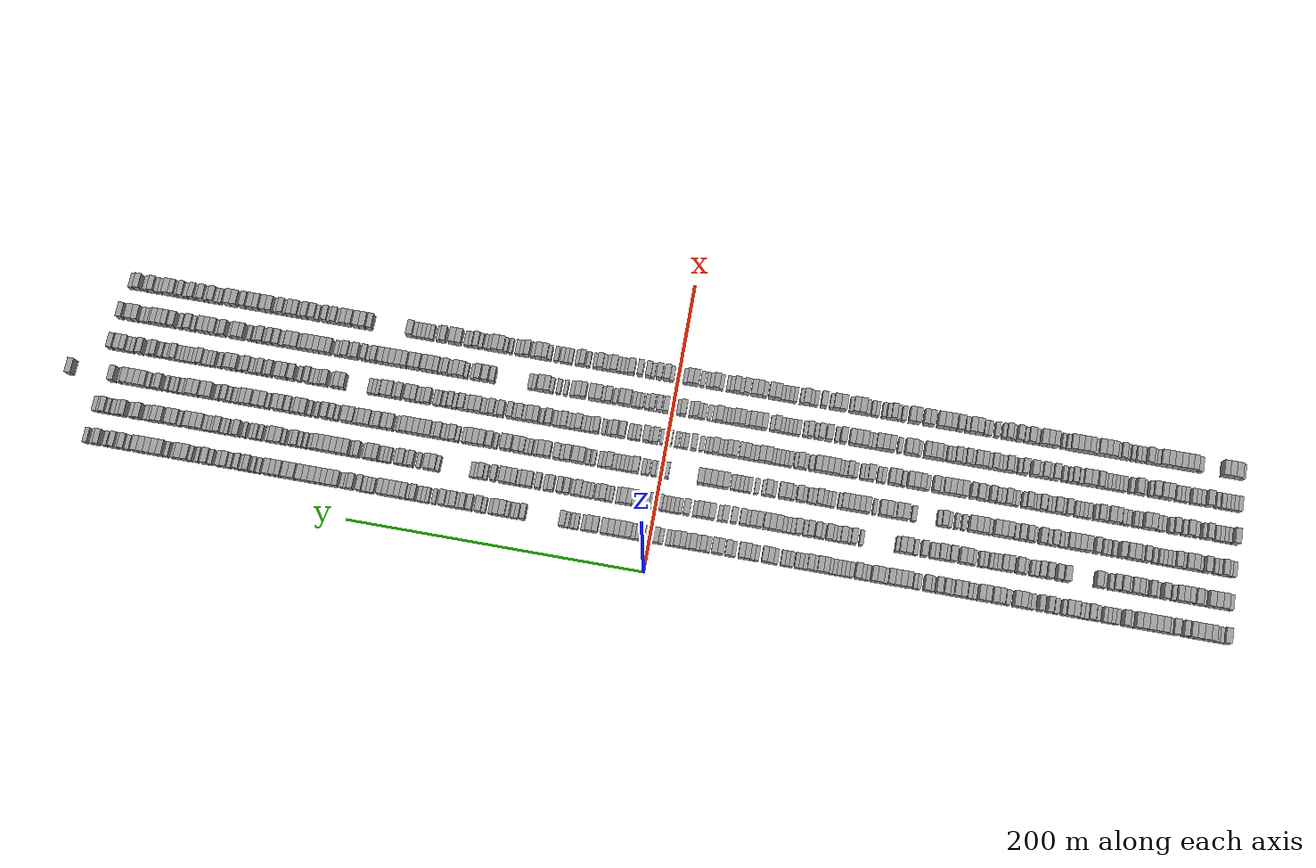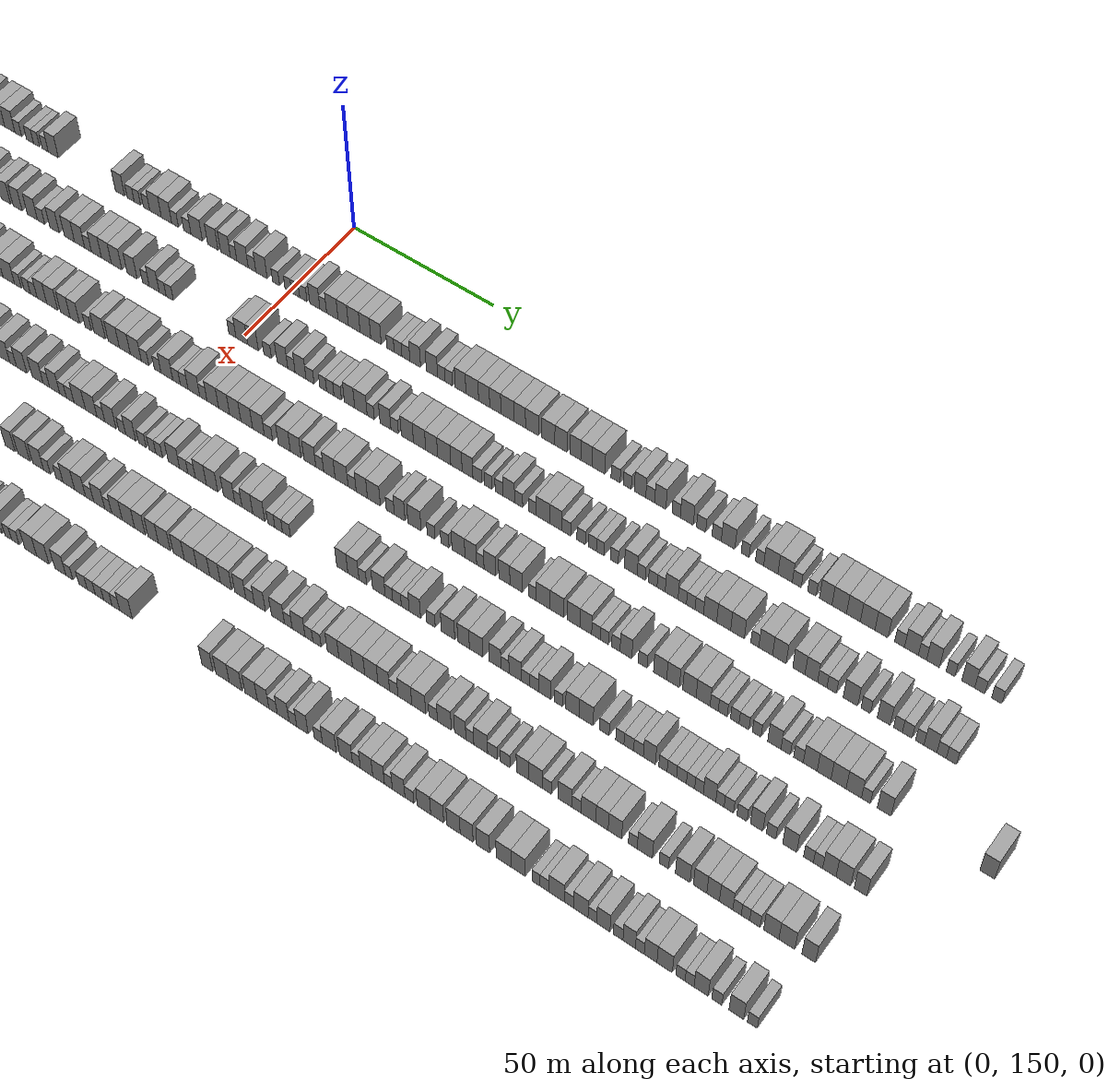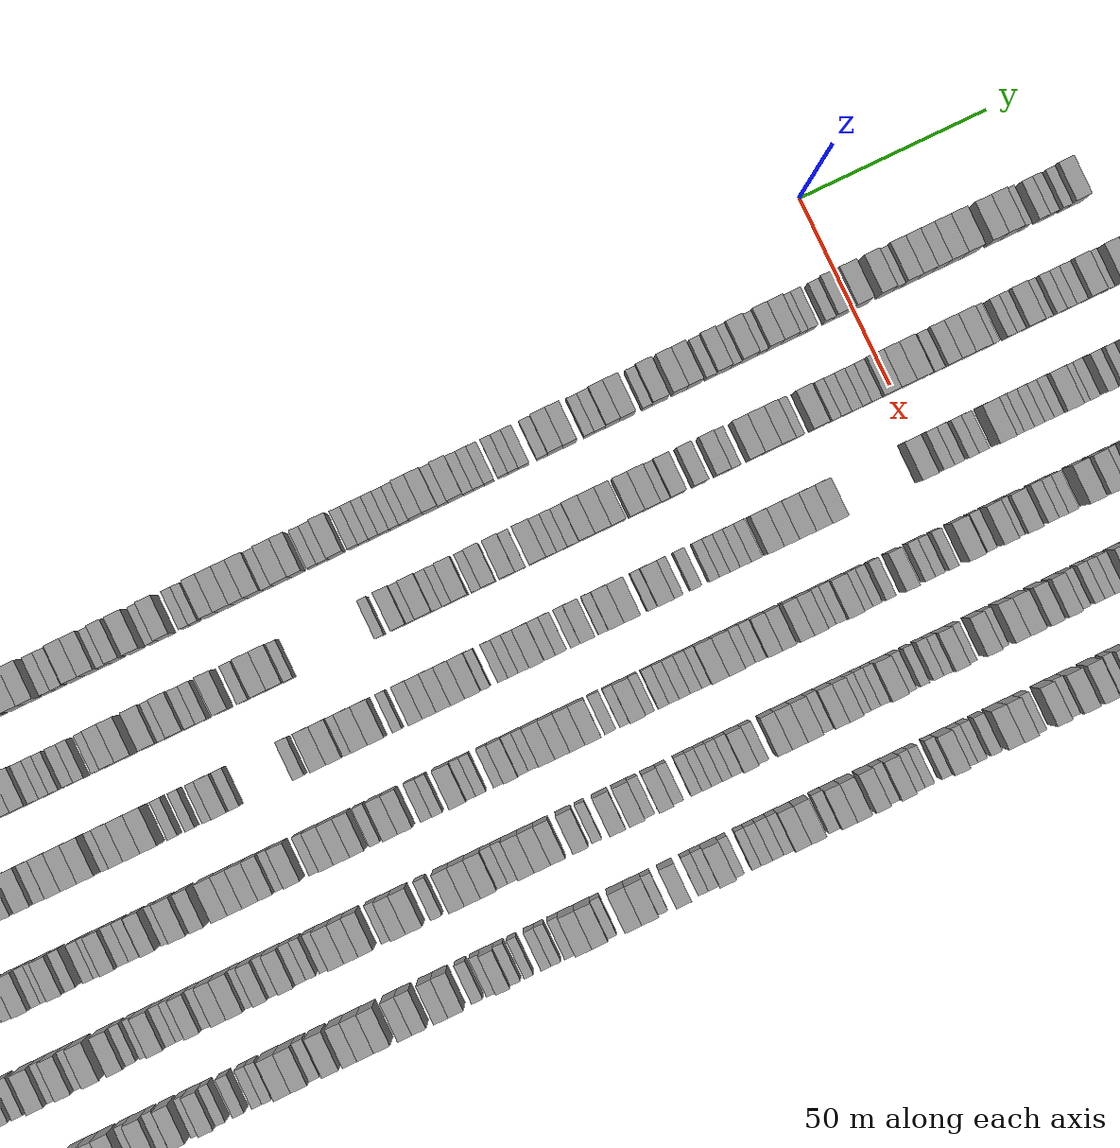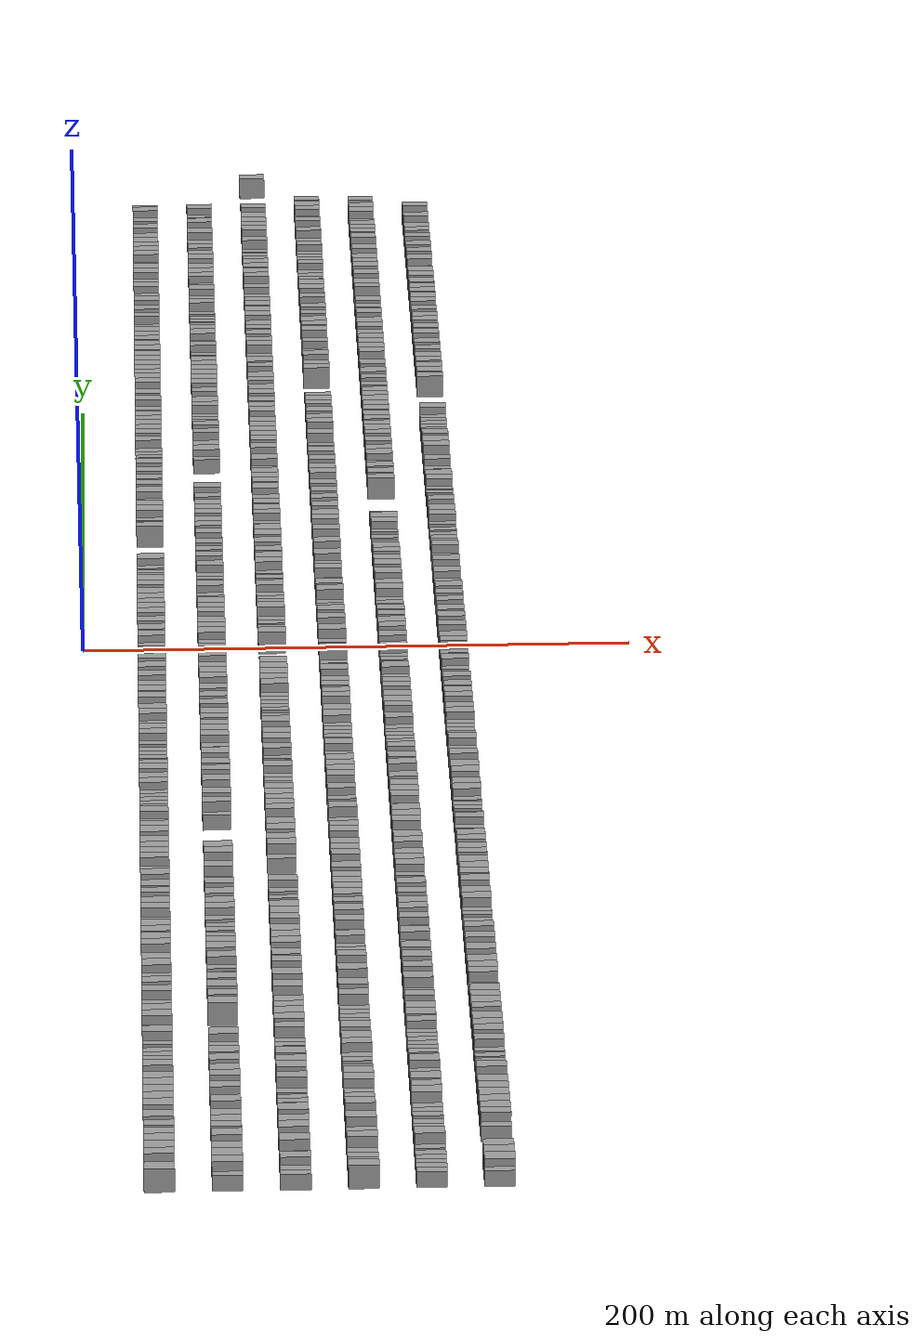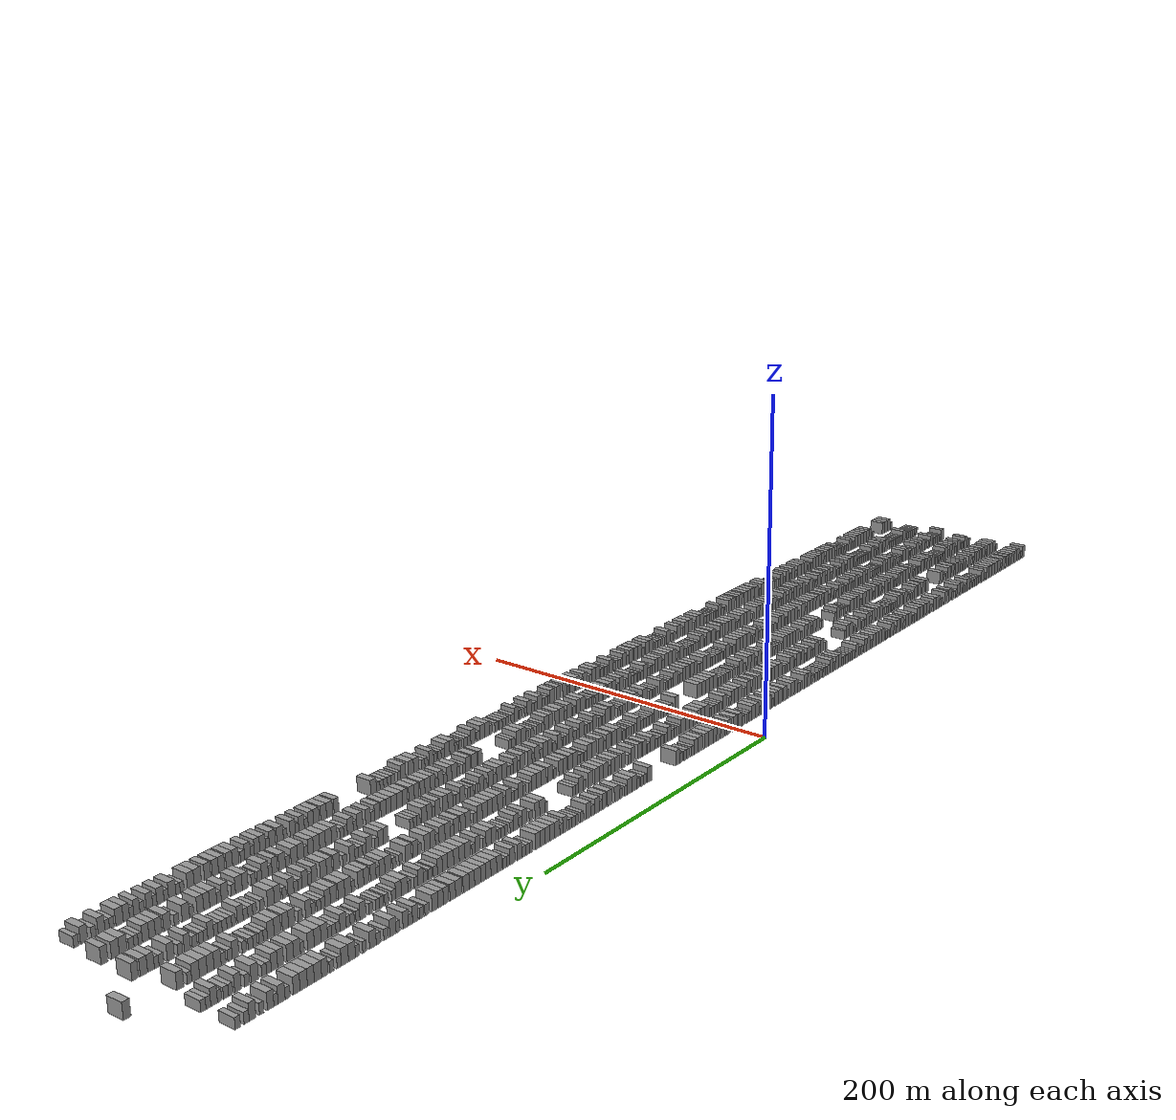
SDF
<sdf version="1.6">
 <world name="default">
  <scene>
   <sky><clouds><speed>12</speed></clouds></sky>
   <ambient>0.4 0.4 0.4 1</ambient>
   <background>0.7 0.7 0.7 1</background>
   <shadows>1</shadows>
  </scene>
  <gravity>0 0 -9.8066</gravity>
  <magnetic_field>6e-06 2.3e-05 -4.2e-05</magnetic_field>
  <physics default="0" name="default_physics" type="ode">
   <ode>
    <solver>
     <type>quick</type>
     <iters>10</iters>
     <sor>1.0</sor>
     <use_dynamic_moi_rescaling>0</use_dynamic_moi_rescaling>
    </solver>
    <constraints>
     <cfm>0</cfm>
     <erp>0.2</erp>
     <contact_max_correcting_vel>100</contact_max_correcting_vel>
     <contact_surface_layer>0.001</contact_surface_layer>
    </constraints>
   </ode>
   <max_step_size>0.004</max_step_size>
   <real_time_factor>1</real_time_factor>
   <real_time_update_rate>250</real_time_update_rate>
  </physics>
  <light name="sun" type="directional">
   <pose>0 0 10 0 0 0</pose>
   <diffuse>0.8 0.8 0.8 1</diffuse>
   <specular>0.2 0.2 0.2 1</specular>
   <attenuation>
    <range>1000</range>
    <constant>0.9</constant>
    <linear>0.01</linear>
    <quadratic>0.001</quadratic>
   </attenuation>
   <direction>-0.5 0.1 -0.9</direction>
  </light>
  <model name="building_1">
   <static>1</static>
   <pose>25.0000 -377.8133 0 0.000000 0.000000 0.000000</pose>
   <link name="link">
    <pose>0 0 4.50 0 0 0</pose>
    <collision name="collision"><geometry><box><size>10.0000 4.3734 9.0000</size></box></geometry></collision>
    <visual name="visual">
     <cast_shadows>0</cast_shadows>
     <geometry><box><size>10.0000 4.3734 9.0000</size></box></geometry>
     <material>
      <script>
       <uri>model://grey_wall/materials/scripts</uri>
       <uri>model://grey_wall/materials/textures</uri>
       <name>vrc/grey_wall</name>
      </script>
     </material>
    </visual>
   </link>
  </model>
  <model name="building_2">
   <static>1</static>
   <pose>25.0000 -374.3436 0 0.000000 0.000000 0.000000</pose>
   <link name="link">
    <pose>0 0 3.00 0 0 0</pose>
    <collision name="collision"><geometry><box><size>10.0000 2.5658 6.0000</size></box></geometry></collision>
    <visual name="visual">
     <cast_shadows>0</cast_shadows>
     <geometry><box><size>10.0000 2.5658 6.0000</size></box></geometry>
     <material>
      <script>
       <uri>model://grey_wall/materials/scripts</uri>
       <uri>model://grey_wall/materials/textures</uri>
       <name>vrc/grey_wall</name>
      </script>
     </material>
    </visual>
   </link>
  </model>
  <model name="building_3">
   <static>1</static>
   <pose>25.0000 -371.7761 0 0.000000 0.000000 0.000000</pose>
   <link name="link">
    <pose>0 0 3.00 0 0 0</pose>
    <collision name="collision"><geometry><box><size>10.0000 2.5692 6.0000</size></box></geometry></collision>
    <visual name="visual">
     <cast_shadows>0</cast_shadows>
     <geometry><box><size>10.0000 2.5692 6.0000</size></box></geometry>
     <material>
      <script>
       <uri>model://grey_wall/materials/scripts</uri>
       <uri>model://grey_wall/materials/textures</uri>
       <name>vrc/grey_wall</name>
      </script>
     </material>
    </visual>
   </link>
  </model>
  <model name="building_4">
   <static>1</static>
   <pose>25.0000 -368.5401 0 0.000000 0.000000 0.000000</pose>
   <link name="link">
    <pose>0 0 4.50 0 0 0</pose>
    <collision name="collision"><geometry><box><size>10.0000 3.9030 9.0000</size></box></geometry></collision>
    <visual name="visual">
     <cast_shadows>0</cast_shadows>
     <geometry><box><size>10.0000 3.9030 9.0000</size></box></geometry>
     <material>
      <script>
       <uri>model://grey_wall/materials/scripts</uri>
       <uri>model://grey_wall/materials/textures</uri>
       <name>vrc/grey_wall</name>
      </script>
     </material>
    </visual>
   </link>
  </model>
  <model name="building_5">
   <static>1</static>
   <pose>25.0000 -364.3790 0 0.000000 0.000000 0.000000</pose>
   <link name="link">
    <pose>0 0 4.50 0 0 0</pose>
    <collision name="collision"><geometry><box><size>10.0000 4.4191 9.0000</size></box></geometry></collision>
    <visual name="visual">
     <cast_shadows>0</cast_shadows>
     <geometry><box><size>10.0000 4.4191 9.0000</size></box></geometry>
     <material>
      <script>
       <uri>model://grey_wall/materials/scripts</uri>
       <uri>model://grey_wall/materials/textures</uri>
       <name>vrc/grey_wall</name>
      </script>
     </material>
    </visual>
   </link>
  </model>
  <model name="building_6">
   <static>1</static>
   <pose>25.0000 -359.9447 0 0.000000 0.000000 0.000000</pose>
   <link name="link">
    <pose>0 0 4.50 0 0 0</pose>
    <collision name="collision"><geometry><box><size>10.0000 4.4495 9.0000</size></box></geometry></collision>
    <visual name="visual">
     <cast_shadows>0</cast_shadows>
     <geometry><box><size>10.0000 4.4495 9.0000</size></box></geometry>
     <material>
      <script>
       <uri>model://grey_wall/materials/scripts</uri>
       <uri>model://grey_wall/materials/textures</uri>
       <name>vrc/grey_wall</name>
      </script>
     </material>
    </visual>
   </link>
  </model>
  <model name="building_7">
   <static>1</static>
   <pose>25.0000 -355.7959 0 0.000000 0.000000 0.000000</pose>
   <link name="link">
    <pose>0 0 4.50 0 0 0</pose>
    <collision name="collision"><geometry><box><size>10.0000 3.8482 9.0000</size></box></geometry></collision>
    <visual name="visual">
     <cast_shadows>0</cast_shadows>
     <geometry><box><size>10.0000 3.8482 9.0000</size></box></geometry>
     <material>
      <script>
       <uri>model://grey_wall/materials/scripts</uri>
       <uri>model://grey_wall/materials/textures</uri>
       <name>vrc/grey_wall</name>
      </script>
     </material>
    </visual>
   </link>
  </model>
  <model name="building_8">
   <static>1</static>
   <pose>25.0000 -350.9902 0 0.000000 0.000000 0.000000</pose>
   <link name="link">
    <pose>0 0 4.50 0 0 0</pose>
    <collision name="collision"><geometry><box><size>10.0000 3.7632 9.0000</size></box></geometry></collision>
    <visual name="visual">
     <cast_shadows>0</cast_shadows>
     <geometry><box><size>10.0000 3.7632 9.0000</size></box></geometry>
     <material>
      <script>
       <uri>model://grey_wall/materials/scripts</uri>
       <uri>model://grey_wall/materials/textures</uri>
       <name>vrc/grey_wall</name>
      </script>
     </material>
    </visual>
   </link>
  </model>
  <model name="building_9">
   <static>1</static>
   <pose>25.0000 -344.8796 0 0.000000 0.000000 0.000000</pose>
   <link name="link">
    <pose>0 0 4.50 0 0 0</pose>
    <collision name="collision"><geometry><box><size>10.0000 4.4580 9.0000</size></box></geometry></collision>
    <visual name="visual">
     <cast_shadows>0</cast_shadows>
     <geometry><box><size>10.0000 4.4580 9.0000</size></box></geometry>
     <material>
      <script>
       <uri>model://grey_wall/materials/scripts</uri>
       <uri>model://grey_wall/materials/textures</uri>
       <name>vrc/grey_wall</name>
      </script>
     </material>
    </visual>
   </link>
  </model>
  <model name="building_10">
   <static>1</static>
   <pose>25.0000 -341.2085 0 0.000000 0.000000 0.000000</pose>
   <link name="link">
    <pose>0 0 3.00 0 0 0</pose>
    <collision name="collision"><geometry><box><size>10.0000 2.8842 6.0000</size></box></geometry></collision>
    <visual name="visual">
     <cast_shadows>0</cast_shadows>
     <geometry><box><size>10.0000 2.8842 6.0000</size></box></geometry>
     <material>
      <script>
       <uri>model://grey_wall/materials/scripts</uri>
       <uri>model://grey_wall/materials/textures</uri>
       <name>vrc/grey_wall</name>
      </script>
     </material>
    </visual>
   </link>
  </model>
  <model name="building_11">
   <static>1</static>
   <pose>25.0000 -337.5871 0 0.000000 0.000000 0.000000</pose>
   <link name="link">
    <pose>0 0 4.50 0 0 0</pose>
    <collision name="collision"><geometry><box><size>10.0000 4.3585 9.0000</size></box></geometry></collision>
    <visual name="visual">
     <cast_shadows>0</cast_shadows>
     <geometry><box><size>10.0000 4.3585 9.0000</size></box></geometry>
     <material>
      <script>
       <uri>model://grey_wall/materials/scripts</uri>
       <uri>model://grey_wall/materials/textures</uri>
       <name>vrc/grey_wall</name>
      </script>
     </material>
    </visual>
   </link>
  </model>
  <model name="building_12">
   <static>1</static>
   <pose>25.0000 -333.2720 0 0.000000 0.000000 0.000000</pose>
   <link name="link">
    <pose>0 0 4.50 0 0 0</pose>
    <collision name="collision"><geometry><box><size>10.0000 4.2718 9.0000</size></box></geometry></collision>
    <visual name="visual">
     <cast_shadows>0</cast_shadows>
     <geometry><box><size>10.0000 4.2718 9.0000</size></box></geometry>
     <material>
      <script>
       <uri>model://grey_wall/materials/scripts</uri>
       <uri>model://grey_wall/materials/textures</uri>
       <name>vrc/grey_wall</name>
      </script>
     </material>
    </visual>
   </link>
  </model>
  <model name="building_13">
   <static>1</static>
   <pose>25.0000 -328.9158 0 0.000000 0.000000 0.000000</pose>
   <link name="link">
    <pose>0 0 4.50 0 0 0</pose>
    <collision name="collision"><geometry><box><size>10.0000 4.4406 9.0000</size></box></geometry></collision>
    <visual name="visual">
     <cast_shadows>0</cast_shadows>
     <geometry><box><size>10.0000 4.4406 9.0000</size></box></geometry>
     <material>
      <script>
       <uri>model://grey_wall/materials/scripts</uri>
       <uri>model://grey_wall/materials/textures</uri>
       <name>vrc/grey_wall</name>
      </script>
     </material>
    </visual>
   </link>
  </model>
  <model name="building_14">
   <static>1</static>
   <pose>25.0000 -324.4931 0 0.000000 0.000000 0.000000</pose>
   <link name="link">
    <pose>0 0 4.50 0 0 0</pose>
    <collision name="collision"><geometry><box><size>10.0000 4.4049 9.0000</size></box></geometry></collision>
    <visual name="visual">
     <cast_shadows>0</cast_shadows>
     <geometry><box><size>10.0000 4.4049 9.0000</size></box></geometry>
     <material>
      <script>
       <uri>model://grey_wall/materials/scripts</uri>
       <uri>model://grey_wall/materials/textures</uri>
       <name>vrc/grey_wall</name>
      </script>
     </material>
    </visual>
   </link>
  </model>
  <model name="building_15">
   <static>1</static>
   <pose>25.0000 -320.2556 0 0.000000 0.000000 0.000000</pose>
   <link name="link">
    <pose>0 0 4.50 0 0 0</pose>
    <collision name="collision"><geometry><box><size>10.0000 4.0702 9.0000</size></box></geometry></collision>
    <visual name="visual">
     <cast_shadows>0</cast_shadows>
     <geometry><box><size>10.0000 4.0702 9.0000</size></box></geometry>
     <material>
      <script>
       <uri>model://grey_wall/materials/scripts</uri>
       <uri>model://grey_wall/materials/textures</uri>
       <name>vrc/grey_wall</name>
      </script>
     </material>
    </visual>
   </link>
  </model>
  <model name="building_16">
   <static>1</static>
   <pose>25.0000 -315.7814 0 0.000000 0.000000 0.000000</pose>
   <link name="link">
    <pose>0 0 3.00 0 0 0</pose>
    <collision name="collision"><geometry><box><size>10.0000 2.8782 6.0000</size></box></geometry></collision>
    <visual name="visual">
     <cast_shadows>0</cast_shadows>
     <geometry><box><size>10.0000 2.8782 6.0000</size></box></geometry>
     <material>
      <script>
       <uri>model://grey_wall/materials/scripts</uri>
       <uri>model://grey_wall/materials/textures</uri>
       <name>vrc/grey_wall</name>
      </script>
     </material>
    </visual>
   </link>
  </model>
  <model name="building_17">
   <static>1</static>
   <pose>25.0000 -312.3662 0 0.000000 0.000000 0.000000</pose>
   <link name="link">
    <pose>0 0 4.50 0 0 0</pose>
    <collision name="collision"><geometry><box><size>10.0000 3.9522 9.0000</size></box></geometry></collision>
    <visual name="visual">
     <cast_shadows>0</cast_shadows>
     <geometry><box><size>10.0000 3.9522 9.0000</size></box></geometry>
     <material>
      <script>
       <uri>model://grey_wall/materials/scripts</uri>
       <uri>model://grey_wall/materials/textures</uri>
       <name>vrc/grey_wall</name>
      </script>
     </material>
    </visual>
   </link>
  </model>
  <model name="building_18">
   <static>1</static>
   <pose>25.0000 -307.0753 0 0.000000 0.000000 0.000000</pose>
   <link name="link">
    <pose>0 0 3.00 0 0 0</pose>
    <collision name="collision"><geometry><box><size>10.0000 2.6295 6.0000</size></box></geometry></collision>
    <visual name="visual">
     <cast_shadows>0</cast_shadows>
     <geometry><box><size>10.0000 2.6295 6.0000</size></box></geometry>
     <material>
      <script>
       <uri>model://grey_wall/materials/scripts</uri>
       <uri>model://grey_wall/materials/textures</uri>
       <name>vrc/grey_wall</name>
      </script>
     </material>
    </visual>
   </link>
  </model>
  <model name="building_19">
   <static>1</static>
   <pose>25.0000 -304.3711 0 0.000000 0.000000 0.000000</pose>
   <link name="link">
    <pose>0 0 3.00 0 0 0</pose>
    <collision name="collision"><geometry><box><size>10.0000 2.7791 6.0000</size></box></geometry></collision>
    <visual name="visual">
     <cast_shadows>0</cast_shadows>
     <geometry><box><size>10.0000 2.7791 6.0000</size></box></geometry>
     <material>
      <script>
       <uri>model://grey_wall/materials/scripts</uri>
       <uri>model://grey_wall/materials/textures</uri>
       <name>vrc/grey_wall</name>
      </script>
     </material>
    </visual>
   </link>
  </model>
  <model name="building_20">
   <static>1</static>
   <pose>25.0000 -301.6274 0 0.000000 0.000000 0.000000</pose>
   <link name="link">
    <pose>0 0 3.00 0 0 0</pose>
    <collision name="collision"><geometry><box><size>10.0000 2.7081 6.0000</size></box></geometry></collision>
    <visual name="visual">
     <cast_shadows>0</cast_shadows>
     <geometry><box><size>10.0000 2.7081 6.0000</size></box></geometry>
     <material>
      <script>
       <uri>model://grey_wall/materials/scripts</uri>
       <uri>model://grey_wall/materials/textures</uri>
       <name>vrc/grey_wall</name>
      </script>
     </material>
    </visual>
   </link>
  </model>
  <model name="building_21">
   <static>1</static>
   <pose>25.0000 -298.9792 0 0.000000 0.000000 0.000000</pose>
   <link name="link">
    <pose>0 0 3.00 0 0 0</pose>
    <collision name="collision"><geometry><box><size>10.0000 2.5884 6.0000</size></box></geometry></collision>
    <visual name="visual">
     <cast_shadows>0</cast_shadows>
     <geometry><box><size>10.0000 2.5884 6.0000</size></box></geometry>
     <material>
      <script>
       <uri>model://grey_wall/materials/scripts</uri>
       <uri>model://grey_wall/materials/textures</uri>
       <name>vrc/grey_wall</name>
      </script>
     </material>
    </visual>
   </link>
  </model>
  <model name="building_22">
   <static>1</static>
   <pose>25.0000 -294.4609 0 0.000000 0.000000 0.000000</pose>
   <link name="link">
    <pose>0 0 3.00 0 0 0</pose>
    <collision name="collision"><geometry><box><size>10.0000 2.4483 6.0000</size></box></geometry></collision>
    <visual name="visual">
     <cast_shadows>0</cast_shadows>
     <geometry><box><size>10.0000 2.4483 6.0000</size></box></geometry>
     <material>
      <script>
       <uri>model://grey_wall/materials/scripts</uri>
       <uri>model://grey_wall/materials/textures</uri>
       <name>vrc/grey_wall</name>
      </script>
     </material>
    </visual>
   </link>
  </model>
  <model name="building_23">
   <static>1</static>
   <pose>25.0000 -290.2139 0 0.000000 0.000000 0.000000</pose>
   <link name="link">
    <pose>0 0 4.50 0 0 0</pose>
    <collision name="collision"><geometry><box><size>10.0000 4.0456 9.0000</size></box></geometry></collision>
    <visual name="visual">
     <cast_shadows>0</cast_shadows>
     <geometry><box><size>10.0000 4.0456 9.0000</size></box></geometry>
     <material>
      <script>
       <uri>model://grey_wall/materials/scripts</uri>
       <uri>model://grey_wall/materials/textures</uri>
       <name>vrc/grey_wall</name>
      </script>
     </material>
    </visual>
   </link>
  </model>
  <model name="building_24">
   <static>1</static>
   <pose>25.0000 -286.8395 0 0.000000 0.000000 0.000000</pose>
   <link name="link">
    <pose>0 0 3.00 0 0 0</pose>
    <collision name="collision"><geometry><box><size>10.0000 2.7032 6.0000</size></box></geometry></collision>
    <visual name="visual">
     <cast_shadows>0</cast_shadows>
     <geometry><box><size>10.0000 2.7032 6.0000</size></box></geometry>
     <material>
      <script>
       <uri>model://grey_wall/materials/scripts</uri>
       <uri>model://grey_wall/materials/textures</uri>
       <name>vrc/grey_wall</name>
      </script>
     </material>
    </visual>
   </link>
  </model>
  <model name="building_25">
   <static>1</static>
   <pose>25.0000 -284.1125 0 0.000000 0.000000 0.000000</pose>
   <link name="link">
    <pose>0 0 3.00 0 0 0</pose>
    <collision name="collision"><geometry><box><size>10.0000 2.7508 6.0000</size></box></geometry></collision>
    <visual name="visual">
     <cast_shadows>0</cast_shadows>
     <geometry><box><size>10.0000 2.7508 6.0000</size></box></geometry>
     <material>
      <script>
       <uri>model://grey_wall/materials/scripts</uri>
       <uri>model://grey_wall/materials/textures</uri>
       <name>vrc/grey_wall</name>
      </script>
     </material>
    </visual>
   </link>
  </model>
  <model name="building_26">
   <static>1</static>
   <pose>25.0000 -279.7349 0 0.000000 0.000000 0.000000</pose>
   <link name="link">
    <pose>0 0 4.50 0 0 0</pose>
    <collision name="collision"><geometry><box><size>10.0000 4.0044 9.0000</size></box></geometry></collision>
    <visual name="visual">
     <cast_shadows>0</cast_shadows>
     <geometry><box><size>10.0000 4.0044 9.0000</size></box></geometry>
     <material>
      <script>
       <uri>model://grey_wall/materials/scripts</uri>
       <uri>model://grey_wall/materials/textures</uri>
       <name>vrc/grey_wall</name>
      </script>
     </material>
    </visual>
   </link>
  </model>
  <model name="building_27">
   <static>1</static>
   <pose>25.0000 -275.6463 0 0.000000 0.000000 0.000000</pose>
   <link name="link">
    <pose>0 0 4.50 0 0 0</pose>
    <collision name="collision"><geometry><box><size>10.0000 4.1728 9.0000</size></box></geometry></collision>
    <visual name="visual">
     <cast_shadows>0</cast_shadows>
     <geometry><box><size>10.0000 4.1728 9.0000</size></box></geometry>
     <material>
      <script>
       <uri>model://grey_wall/materials/scripts</uri>
       <uri>model://grey_wall/materials/textures</uri>
       <name>vrc/grey_wall</name>
      </script>
     </material>
    </visual>
   </link>
  </model>
  <model name="building_28">
   <static>1</static>
   <pose>25.0000 -272.2609 0 0.000000 0.000000 0.000000</pose>
   <link name="link">
    <pose>0 0 3.00 0 0 0</pose>
    <collision name="collision"><geometry><box><size>10.0000 2.5982 6.0000</size></box></geometry></collision>
    <visual name="visual">
     <cast_shadows>0</cast_shadows>
     <geometry><box><size>10.0000 2.5982 6.0000</size></box></geometry>
     <material>
      <script>
       <uri>model://grey_wall/materials/scripts</uri>
       <uri>model://grey_wall/materials/textures</uri>
       <name>vrc/grey_wall</name>
      </script>
     </material>
    </visual>
   </link>
  </model>
  <model name="building_29">
   <static>1</static>
   <pose>25.0000 -267.4747 0 0.000000 0.000000 0.000000</pose>
   <link name="link">
    <pose>0 0 3.00 0 0 0</pose>
    <collision name="collision"><geometry><box><size>10.0000 2.9742 6.0000</size></box></geometry></collision>
    <visual name="visual">
     <cast_shadows>0</cast_shadows>
     <geometry><box><size>10.0000 2.9742 6.0000</size></box></geometry>
     <material>
      <script>
       <uri>model://grey_wall/materials/scripts</uri>
       <uri>model://grey_wall/materials/textures</uri>
       <name>vrc/grey_wall</name>
      </script>
     </material>
    </visual>
   </link>
  </model>
  <model name="building_30">
   <static>1</static>
   <pose>25.0000 -263.0739 0 0.000000 0.000000 0.000000</pose>
   <link name="link">
    <pose>0 0 4.50 0 0 0</pose>
    <collision name="collision"><geometry><box><size>10.0000 3.8273 9.0000</size></box></geometry></collision>
    <visual name="visual">
     <cast_shadows>0</cast_shadows>
     <geometry><box><size>10.0000 3.8273 9.0000</size></box></geometry>
     <material>
      <script>
       <uri>model://grey_wall/materials/scripts</uri>
       <uri>model://grey_wall/materials/textures</uri>
       <name>vrc/grey_wall</name>
      </script>
     </material>
    </visual>
   </link>
  </model>
  <model name="building_31">
   <static>1</static>
   <pose>25.0000 -257.2364 0 0.000000 0.000000 0.000000</pose>
   <link name="link">
    <pose>0 0 4.50 0 0 0</pose>
    <collision name="collision"><geometry><box><size>10.0000 3.8477 9.0000</size></box></geometry></collision>
    <visual name="visual">
     <cast_shadows>0</cast_shadows>
     <geometry><box><size>10.0000 3.8477 9.0000</size></box></geometry>
     <material>
      <script>
       <uri>model://grey_wall/materials/scripts</uri>
       <uri>model://grey_wall/materials/textures</uri>
       <name>vrc/grey_wall</name>
      </script>
     </material>
    </visual>
   </link>
  </model>
  <model name="building_32">
   <static>1</static>
   <pose>25.0000 -251.8400 0 0.000000 0.000000 0.000000</pose>
   <link name="link">
    <pose>0 0 3.00 0 0 0</pose>
    <collision name="collision"><geometry><box><size>10.0000 2.9451 6.0000</size></box></geometry></collision>
    <visual name="visual">
     <cast_shadows>0</cast_shadows>
     <geometry><box><size>10.0000 2.9451 6.0000</size></box></geometry>
     <material>
      <script>
       <uri>model://grey_wall/materials/scripts</uri>
       <uri>model://grey_wall/materials/textures</uri>
       <name>vrc/grey_wall</name>
      </script>
     </material>
    </visual>
   </link>
  </model>
  <model name="building_33">
   <static>1</static>
   <pose>25.0000 -249.0780 0 0.000000 0.000000 0.000000</pose>
   <link name="link">
    <pose>0 0 3.00 0 0 0</pose>
    <collision name="collision"><geometry><box><size>10.0000 2.5788 6.0000</size></box></geometry></collision>
    <visual name="visual">
     <cast_shadows>0</cast_shadows>
     <geometry><box><size>10.0000 2.5788 6.0000</size></box></geometry>
     <material>
      <script>
       <uri>model://grey_wall/materials/scripts</uri>
       <uri>model://grey_wall/materials/textures</uri>
       <name>vrc/grey_wall</name>
      </script>
     </material>
    </visual>
   </link>
  </model>
  <model name="building_34">
   <static>1</static>
   <pose>25.0000 -245.5456 0 0.000000 0.000000 0.000000</pose>
   <link name="link">
    <pose>0 0 4.50 0 0 0</pose>
    <collision name="collision"><geometry><box><size>10.0000 4.4860 9.0000</size></box></geometry></collision>
    <visual name="visual">
     <cast_shadows>0</cast_shadows>
     <geometry><box><size>10.0000 4.4860 9.0000</size></box></geometry>
     <material>
      <script>
       <uri>model://grey_wall/materials/scripts</uri>
       <uri>model://grey_wall/materials/textures</uri>
       <name>vrc/grey_wall</name>
      </script>
     </material>
    </visual>
   </link>
  </model>
  <model name="building_35">
   <static>1</static>
   <pose>25.0000 -241.3080 0 0.000000 0.000000 0.000000</pose>
   <link name="link">
    <pose>0 0 4.50 0 0 0</pose>
    <collision name="collision"><geometry><box><size>10.0000 3.9893 9.0000</size></box></geometry></collision>
    <visual name="visual">
     <cast_shadows>0</cast_shadows>
     <geometry><box><size>10.0000 3.9893 9.0000</size></box></geometry>
     <material>
      <script>
       <uri>model://grey_wall/materials/scripts</uri>
       <uri>model://grey_wall/materials/textures</uri>
       <name>vrc/grey_wall</name>
      </script>
     </material>
    </visual>
   </link>
  </model>
  <model name="building_36">
   <static>1</static>
   <pose>25.0000 -235.8335 0 0.000000 0.000000 0.000000</pose>
   <link name="link">
    <pose>0 0 3.00 0 0 0</pose>
    <collision name="collision"><geometry><box><size>10.0000 2.9596 6.0000</size></box></geometry></collision>
    <visual name="visual">
     <cast_shadows>0</cast_shadows>
     <geometry><box><size>10.0000 2.9596 6.0000</size></box></geometry>
     <material>
      <script>
       <uri>model://grey_wall/materials/scripts</uri>
       <uri>model://grey_wall/materials/textures</uri>
       <name>vrc/grey_wall</name>
      </script>
     </material>
    </visual>
   </link>
  </model>
  <model name="building_37">
   <static>1</static>
   <pose>25.0000 -231.4122 0 0.000000 0.000000 0.000000</pose>
   <link name="link">
    <pose>0 0 4.50 0 0 0</pose>
    <collision name="collision"><geometry><box><size>10.0000 3.8830 9.0000</size></box></geometry></collision>
    <visual name="visual">
     <cast_shadows>0</cast_shadows>
     <geometry><box><size>10.0000 3.8830 9.0000</size></box></geometry>
     <material>
      <script>
       <uri>model://grey_wall/materials/scripts</uri>
       <uri>model://grey_wall/materials/textures</uri>
       <name>vrc/grey_wall</name>
      </script>
     </material>
    </visual>
   </link>
  </model>
  <model name="building_38">
   <static>1</static>
   <pose>25.0000 -227.4498 0 0.000000 0.000000 0.000000</pose>
   <link name="link">
    <pose>0 0 4.50 0 0 0</pose>
    <collision name="collision"><geometry><box><size>10.0000 4.0419 9.0000</size></box></geometry></collision>
    <visual name="visual">
     <cast_shadows>0</cast_shadows>
     <geometry><box><size>10.0000 4.0419 9.0000</size></box></geometry>
     <material>
      <script>
       <uri>model://grey_wall/materials/scripts</uri>
       <uri>model://grey_wall/materials/textures</uri>
       <name>vrc/grey_wall</name>
      </script>
     </material>
    </visual>
   </link>
  </model>
  <model name="building_39">
   <static>1</static>
   <pose>25.0000 -222.4432 0 0.000000 0.000000 0.000000</pose>
   <link name="link">
    <pose>0 0 4.50 0 0 0</pose>
    <collision name="collision"><geometry><box><size>10.0000 3.9713 9.0000</size></box></geometry></collision>
    <visual name="visual">
     <cast_shadows>0</cast_shadows>
     <geometry><box><size>10.0000 3.9713 9.0000</size></box></geometry>
     <material>
      <script>
       <uri>model://grey_wall/materials/scripts</uri>
       <uri>model://grey_wall/materials/textures</uri>
       <name>vrc/grey_wall</name>
      </script>
     </material>
    </visual>
   </link>
  </model>
  <model name="building_40">
   <static>1</static>
   <pose>25.0000 -218.3699 0 0.000000 0.000000 0.000000</pose>
   <link name="link">
    <pose>0 0 4.50 0 0 0</pose>
    <collision name="collision"><geometry><box><size>10.0000 4.1753 9.0000</size></box></geometry></collision>
    <visual name="visual">
     <cast_shadows>0</cast_shadows>
     <geometry><box><size>10.0000 4.1753 9.0000</size></box></geometry>
     <material>
      <script>
       <uri>model://grey_wall/materials/scripts</uri>
       <uri>model://grey_wall/materials/textures</uri>
       <name>vrc/grey_wall</name>
      </script>
     </material>
    </visual>
   </link>
  </model>
  <model name="building_41">
   <static>1</static>
   <pose>25.0000 -213.8711 0 0.000000 0.000000 0.000000</pose>
   <link name="link">
    <pose>0 0 3.00 0 0 0</pose>
    <collision name="collision"><geometry><box><size>10.0000 2.8223 6.0000</size></box></geometry></collision>
    <visual name="visual">
     <cast_shadows>0</cast_shadows>
     <geometry><box><size>10.0000 2.8223 6.0000</size></box></geometry>
     <material>
      <script>
       <uri>model://grey_wall/materials/scripts</uri>
       <uri>model://grey_wall/materials/textures</uri>
       <name>vrc/grey_wall</name>
      </script>
     </material>
    </visual>
   </link>
  </model>
  <model name="building_42">
   <static>1</static>
   <pose>25.0000 -211.0071 0 0.000000 0.000000 0.000000</pose>
   <link name="link">
    <pose>0 0 3.00 0 0 0</pose>
    <collision name="collision"><geometry><box><size>10.0000 2.9056 6.0000</size></box></geometry></collision>
    <visual name="visual">
     <cast_shadows>0</cast_shadows>
     <geometry><box><size>10.0000 2.9056 6.0000</size></box></geometry>
     <material>
      <script>
       <uri>model://grey_wall/materials/scripts</uri>
       <uri>model://grey_wall/materials/textures</uri>
       <name>vrc/grey_wall</name>
      </script>
     </material>
    </visual>
   </link>
  </model>
  <model name="building_43">
   <static>1</static>
   <pose>25.0000 -206.5180 0 0.000000 0.000000 0.000000</pose>
   <link name="link">
    <pose>0 0 4.50 0 0 0</pose>
    <collision name="collision"><geometry><box><size>10.0000 4.0726 9.0000</size></box></geometry></collision>
    <visual name="visual">
     <cast_shadows>0</cast_shadows>
     <geometry><box><size>10.0000 4.0726 9.0000</size></box></geometry>
     <material>
      <script>
       <uri>model://grey_wall/materials/scripts</uri>
       <uri>model://grey_wall/materials/textures</uri>
       <name>vrc/grey_wall</name>
      </script>
     </material>
    </visual>
   </link>
  </model>
  <model name="building_44">
   <static>1</static>
   <pose>25.0000 -202.4322 0 0.000000 0.000000 0.000000</pose>
   <link name="link">
    <pose>0 0 4.50 0 0 0</pose>
    <collision name="collision"><geometry><box><size>10.0000 4.0990 9.0000</size></box></geometry></collision>
    <visual name="visual">
     <cast_shadows>0</cast_shadows>
     <geometry><box><size>10.0000 4.0990 9.0000</size></box></geometry>
     <material>
      <script>
       <uri>model://grey_wall/materials/scripts</uri>
       <uri>model://grey_wall/materials/textures</uri>
       <name>vrc/grey_wall</name>
      </script>
     </material>
    </visual>
   </link>
  </model>
  <model name="building_45">
   <static>1</static>
   <pose>25.0000 -198.9451 0 0.000000 0.000000 0.000000</pose>
   <link name="link">
    <pose>0 0 3.00 0 0 0</pose>
    <collision name="collision"><geometry><box><size>10.0000 2.8752 6.0000</size></box></geometry></collision>
    <visual name="visual">
     <cast_shadows>0</cast_shadows>
     <geometry><box><size>10.0000 2.8752 6.0000</size></box></geometry>
     <material>
      <script>
       <uri>model://grey_wall/materials/scripts</uri>
       <uri>model://grey_wall/materials/textures</uri>
       <name>vrc/grey_wall</name>
      </script>
     </material>
    </visual>
   </link>
  </model>
  <model name="building_46">
   <static>1</static>
   <pose>25.0000 -195.7043 0 0.000000 0.000000 0.000000</pose>
   <link name="link">
    <pose>0 0 4.50 0 0 0</pose>
    <collision name="collision"><geometry><box><size>10.0000 3.6064 9.0000</size></box></geometry></collision>
    <visual name="visual">
     <cast_shadows>0</cast_shadows>
     <geometry><box><size>10.0000 3.6064 9.0000</size></box></geometry>
     <material>
      <script>
       <uri>model://grey_wall/materials/scripts</uri>
       <uri>model://grey_wall/materials/textures</uri>
       <name>vrc/grey_wall</name>
      </script>
     </material>
    </visual>
   </link>
  </model>
  <model name="building_47">
   <static>1</static>
   <pose>25.0000 -190.7370 0 0.000000 0.000000 0.000000</pose>
   <link name="link">
    <pose>0 0 4.50 0 0 0</pose>
    <collision name="collision"><geometry><box><size>10.0000 4.3282 9.0000</size></box></geometry></collision>
    <visual name="visual">
     <cast_shadows>0</cast_shadows>
     <geometry><box><size>10.0000 4.3282 9.0000</size></box></geometry>
     <material>
      <script>
       <uri>model://grey_wall/materials/scripts</uri>
       <uri>model://grey_wall/materials/textures</uri>
       <name>vrc/grey_wall</name>
      </script>
     </material>
    </visual>
   </link>
  </model>
  <model name="building_48">
   <static>1</static>
   <pose>25.0000 -186.1845 0 0.000000 0.000000 0.000000</pose>
   <link name="link">
    <pose>0 0 3.00 0 0 0</pose>
    <collision name="collision"><geometry><box><size>10.0000 2.7769 6.0000</size></box></geometry></collision>
    <visual name="visual">
     <cast_shadows>0</cast_shadows>
     <geometry><box><size>10.0000 2.7769 6.0000</size></box></geometry>
     <material>
      <script>
       <uri>model://grey_wall/materials/scripts</uri>
       <uri>model://grey_wall/materials/textures</uri>
       <name>vrc/grey_wall</name>
      </script>
     </material>
    </visual>
   </link>
  </model>
  <model name="building_49">
   <static>1</static>
   <pose>25.0000 -182.7577 0 0.000000 0.000000 0.000000</pose>
   <link name="link">
    <pose>0 0 4.50 0 0 0</pose>
    <collision name="collision"><geometry><box><size>10.0000 4.0766 9.0000</size></box></geometry></collision>
    <visual name="visual">
     <cast_shadows>0</cast_shadows>
     <geometry><box><size>10.0000 4.0766 9.0000</size></box></geometry>
     <material>
      <script>
       <uri>model://grey_wall/materials/scripts</uri>
       <uri>model://grey_wall/materials/textures</uri>
       <name>vrc/grey_wall</name>
      </script>
     </material>
    </visual>
   </link>
  </model>
  <model name="building_50">
   <static>1</static>
   <pose>25.0000 -177.4681 0 0.000000 0.000000 0.000000</pose>
   <link name="link">
    <pose>0 0 3.00 0 0 0</pose>
    <collision name="collision"><geometry><box><size>10.0000 2.5027 6.0000</size></box></geometry></collision>
    <visual name="visual">
     <cast_shadows>0</cast_shadows>
     <geometry><box><size>10.0000 2.5027 6.0000</size></box></geometry>
     <material>
      <script>
       <uri>model://grey_wall/materials/scripts</uri>
       <uri>model://grey_wall/materials/textures</uri>
       <name>vrc/grey_wall</name>
      </script>
     </material>
    </visual>
   </link>
  </model>
  <model name="building_51">
   <static>1</static>
   <pose>25.0000 -175.0063 0 0.000000 0.000000 0.000000</pose>
   <link name="link">
    <pose>0 0 3.00 0 0 0</pose>
    <collision name="collision"><geometry><box><size>10.0000 2.4209 6.0000</size></box></geometry></collision>
    <visual name="visual">
     <cast_shadows>0</cast_shadows>
     <geometry><box><size>10.0000 2.4209 6.0000</size></box></geometry>
     <material>
      <script>
       <uri>model://grey_wall/materials/scripts</uri>
       <uri>model://grey_wall/materials/textures</uri>
       <name>vrc/grey_wall</name>
      </script>
     </material>
    </visual>
   </link>
  </model>
  <model name="building_52">
   <static>1</static>
   <pose>25.0000 -170.9785 0 0.000000 0.000000 0.000000</pose>
   <link name="link">
    <pose>0 0 4.50 0 0 0</pose>
    <collision name="collision"><geometry><box><size>10.0000 3.6347 9.0000</size></box></geometry></collision>
    <visual name="visual">
     <cast_shadows>0</cast_shadows>
     <geometry><box><size>10.0000 3.6347 9.0000</size></box></geometry>
     <material>
      <script>
       <uri>model://grey_wall/materials/scripts</uri>
       <uri>model://grey_wall/materials/textures</uri>
       <name>vrc/grey_wall</name>
      </script>
     </material>
    </visual>
   </link>
  </model>
  <model name="building_53">
   <static>1</static>
   <pose>25.0000 -167.0772 0 0.000000 0.000000 0.000000</pose>
   <link name="link">
    <pose>0 0 4.50 0 0 0</pose>
    <collision name="collision"><geometry><box><size>10.0000 4.1678 9.0000</size></box></geometry></collision>
    <visual name="visual">
     <cast_shadows>0</cast_shadows>
     <geometry><box><size>10.0000 4.1678 9.0000</size></box></geometry>
     <material>
      <script>
       <uri>model://grey_wall/materials/scripts</uri>
       <uri>model://grey_wall/materials/textures</uri>
       <name>vrc/grey_wall</name>
      </script>
     </material>
    </visual>
   </link>
  </model>
  <model name="building_54">
   <static>1</static>
   <pose>25.0000 -163.1922 0 0.000000 0.000000 0.000000</pose>
   <link name="link">
    <pose>0 0 4.50 0 0 0</pose>
    <collision name="collision"><geometry><box><size>10.0000 3.6020 9.0000</size></box></geometry></collision>
    <visual name="visual">
     <cast_shadows>0</cast_shadows>
     <geometry><box><size>10.0000 3.6020 9.0000</size></box></geometry>
     <material>
      <script>
       <uri>model://grey_wall/materials/scripts</uri>
       <uri>model://grey_wall/materials/textures</uri>
       <name>vrc/grey_wall</name>
      </script>
     </material>
    </visual>
   </link>
  </model>
  <model name="building_55">
   <static>1</static>
   <pose>25.0000 -159.2742 0 0.000000 0.000000 0.000000</pose>
   <link name="link">
    <pose>0 0 4.50 0 0 0</pose>
    <collision name="collision"><geometry><box><size>10.0000 4.2340 9.0000</size></box></geometry></collision>
    <visual name="visual">
     <cast_shadows>0</cast_shadows>
     <geometry><box><size>10.0000 4.2340 9.0000</size></box></geometry>
     <material>
      <script>
       <uri>model://grey_wall/materials/scripts</uri>
       <uri>model://grey_wall/materials/textures</uri>
       <name>vrc/grey_wall</name>
      </script>
     </material>
    </visual>
   </link>
  </model>
  <model name="building_56">
   <static>1</static>
   <pose>25.0000 -155.6702 0 0.000000 0.000000 0.000000</pose>
   <link name="link">
    <pose>0 0 3.00 0 0 0</pose>
    <collision name="collision"><geometry><box><size>10.0000 2.9739 6.0000</size></box></geometry></collision>
    <visual name="visual">
     <cast_shadows>0</cast_shadows>
     <geometry><box><size>10.0000 2.9739 6.0000</size></box></geometry>
     <material>
      <script>
       <uri>model://grey_wall/materials/scripts</uri>
       <uri>model://grey_wall/materials/textures</uri>
       <name>vrc/grey_wall</name>
      </script>
     </material>
    </visual>
   </link>
  </model>
  <model name="building_57">
   <static>1</static>
   <pose>25.0000 -151.9863 0 0.000000 0.000000 0.000000</pose>
   <link name="link">
    <pose>0 0 4.50 0 0 0</pose>
    <collision name="collision"><geometry><box><size>10.0000 4.3939 9.0000</size></box></geometry></collision>
    <visual name="visual">
     <cast_shadows>0</cast_shadows>
     <geometry><box><size>10.0000 4.3939 9.0000</size></box></geometry>
     <material>
      <script>
       <uri>model://grey_wall/materials/scripts</uri>
       <uri>model://grey_wall/materials/textures</uri>
       <name>vrc/grey_wall</name>
      </script>
     </material>
    </visual>
   </link>
  </model>
  <model name="building_58">
   <static>1</static>
   <pose>25.0000 -147.9791 0 0.000000 0.000000 0.000000</pose>
   <link name="link">
    <pose>0 0 4.50 0 0 0</pose>
    <collision name="collision"><geometry><box><size>10.0000 3.6205 9.0000</size></box></geometry></collision>
    <visual name="visual">
     <cast_shadows>0</cast_shadows>
     <geometry><box><size>10.0000 3.6205 9.0000</size></box></geometry>
     <material>
      <script>
       <uri>model://grey_wall/materials/scripts</uri>
       <uri>model://grey_wall/materials/textures</uri>
       <name>vrc/grey_wall</name>
      </script>
     </material>
    </visual>
   </link>
  </model>
  <model name="building_59">
   <static>1</static>
   <pose>25.0000 -143.8743 0 0.000000 0.000000 0.000000</pose>
   <link name="link">
    <pose>0 0 3.00 0 0 0</pose>
    <collision name="collision"><geometry><box><size>10.0000 2.5892 6.0000</size></box></geometry></collision>
    <visual name="visual">
     <cast_shadows>0</cast_shadows>
     <geometry><box><size>10.0000 2.5892 6.0000</size></box></geometry>
     <material>
      <script>
       <uri>model://grey_wall/materials/scripts</uri>
       <uri>model://grey_wall/materials/textures</uri>
       <name>vrc/grey_wall</name>
      </script>
     </material>
    </visual>
   </link>
  </model>
  <model name="building_60">
   <static>1</static>
   <pose>25.0000 -141.0896 0 0.000000 0.000000 0.000000</pose>
   <link name="link">
    <pose>0 0 3.00 0 0 0</pose>
    <collision name="collision"><geometry><box><size>10.0000 2.9802 6.0000</size></box></geometry></collision>
    <visual name="visual">
     <cast_shadows>0</cast_shadows>
     <geometry><box><size>10.0000 2.9802 6.0000</size></box></geometry>
     <material>
      <script>
       <uri>model://grey_wall/materials/scripts</uri>
       <uri>model://grey_wall/materials/textures</uri>
       <name>vrc/grey_wall</name>
      </script>
     </material>
    </visual>
   </link>
  </model>
  <model name="building_61">
   <static>1</static>
   <pose>25.0000 -137.5232 0 0.000000 0.000000 0.000000</pose>
   <link name="link">
    <pose>0 0 4.50 0 0 0</pose>
    <collision name="collision"><geometry><box><size>10.0000 4.1526 9.0000</size></box></geometry></collision>
    <visual name="visual">
     <cast_shadows>0</cast_shadows>
     <geometry><box><size>10.0000 4.1526 9.0000</size></box></geometry>
     <material>
      <script>
       <uri>model://grey_wall/materials/scripts</uri>
       <uri>model://grey_wall/materials/textures</uri>
       <name>vrc/grey_wall</name>
      </script>
     </material>
    </visual>
   </link>
  </model>
  <model name="building_62">
   <static>1</static>
   <pose>25.0000 -133.0474 0 0.000000 0.000000 0.000000</pose>
   <link name="link">
    <pose>0 0 3.00 0 0 0</pose>
    <collision name="collision"><geometry><box><size>10.0000 2.7989 6.0000</size></box></geometry></collision>
    <visual name="visual">
     <cast_shadows>0</cast_shadows>
     <geometry><box><size>10.0000 2.7989 6.0000</size></box></geometry>
     <material>
      <script>
       <uri>model://grey_wall/materials/scripts</uri>
       <uri>model://grey_wall/materials/textures</uri>
       <name>vrc/grey_wall</name>
      </script>
     </material>
    </visual>
   </link>
  </model>
  <model name="building_63">
   <static>1</static>
   <pose>25.0000 -130.2640 0 0.000000 0.000000 0.000000</pose>
   <link name="link">
    <pose>0 0 3.00 0 0 0</pose>
    <collision name="collision"><geometry><box><size>10.0000 2.7681 6.0000</size></box></geometry></collision>
    <visual name="visual">
     <cast_shadows>0</cast_shadows>
     <geometry><box><size>10.0000 2.7681 6.0000</size></box></geometry>
     <material>
      <script>
       <uri>model://grey_wall/materials/scripts</uri>
       <uri>model://grey_wall/materials/textures</uri>
       <name>vrc/grey_wall</name>
      </script>
     </material>
    </visual>
   </link>
  </model>
  <model name="building_64">
   <static>1</static>
   <pose>25.0000 -127.5657 0 0.000000 0.000000 0.000000</pose>
   <link name="link">
    <pose>0 0 3.00 0 0 0</pose>
    <collision name="collision"><geometry><box><size>10.0000 2.6284 6.0000</size></box></geometry></collision>
    <visual name="visual">
     <cast_shadows>0</cast_shadows>
     <geometry><box><size>10.0000 2.6284 6.0000</size></box></geometry>
     <material>
      <script>
       <uri>model://grey_wall/materials/scripts</uri>
       <uri>model://grey_wall/materials/textures</uri>
       <name>vrc/grey_wall</name>
      </script>
     </material>
    </visual>
   </link>
  </model>
  <model name="building_65">
   <static>1</static>
   <pose>25.0000 -124.8482 0 0.000000 0.000000 0.000000</pose>
   <link name="link">
    <pose>0 0 3.00 0 0 0</pose>
    <collision name="collision"><geometry><box><size>10.0000 2.8066 6.0000</size></box></geometry></collision>
    <visual name="visual">
     <cast_shadows>0</cast_shadows>
     <geometry><box><size>10.0000 2.8066 6.0000</size></box></geometry>
     <material>
      <script>
       <uri>model://grey_wall/materials/scripts</uri>
       <uri>model://grey_wall/materials/textures</uri>
       <name>vrc/grey_wall</name>
      </script>
     </material>
    </visual>
   </link>
  </model>
  <model name="building_66">
   <static>1</static>
   <pose>25.0000 -122.1418 0 0.000000 0.000000 0.000000</pose>
   <link name="link">
    <pose>0 0 3.00 0 0 0</pose>
    <collision name="collision"><geometry><box><size>10.0000 2.6062 6.0000</size></box></geometry></collision>
    <visual name="visual">
     <cast_shadows>0</cast_shadows>
     <geometry><box><size>10.0000 2.6062 6.0000</size></box></geometry>
     <material>
      <script>
       <uri>model://grey_wall/materials/scripts</uri>
       <uri>model://grey_wall/materials/textures</uri>
       <name>vrc/grey_wall</name>
      </script>
     </material>
    </visual>
   </link>
  </model>
  <model name="building_67">
   <static>1</static>
   <pose>25.0000 -119.5277 0 0.000000 0.000000 0.000000</pose>
   <link name="link">
    <pose>0 0 3.00 0 0 0</pose>
    <collision name="collision"><geometry><box><size>10.0000 2.6220 6.0000</size></box></geometry></collision>
    <visual name="visual">
     <cast_shadows>0</cast_shadows>
     <geometry><box><size>10.0000 2.6220 6.0000</size></box></geometry>
     <material>
      <script>
       <uri>model://grey_wall/materials/scripts</uri>
       <uri>model://grey_wall/materials/textures</uri>
       <name>vrc/grey_wall</name>
      </script>
     </material>
    </visual>
   </link>
  </model>
  <model name="building_68">
   <static>1</static>
   <pose>25.0000 -116.4131 0 0.000000 0.000000 0.000000</pose>
   <link name="link">
    <pose>0 0 4.50 0 0 0</pose>
    <collision name="collision"><geometry><box><size>10.0000 3.6072 9.0000</size></box></geometry></collision>
    <visual name="visual">
     <cast_shadows>0</cast_shadows>
     <geometry><box><size>10.0000 3.6072 9.0000</size></box></geometry>
     <material>
      <script>
       <uri>model://grey_wall/materials/scripts</uri>
       <uri>model://grey_wall/materials/textures</uri>
       <name>vrc/grey_wall</name>
      </script>
     </material>
    </visual>
   </link>
  </model>
  <model name="building_69">
   <static>1</static>
   <pose>25.0000 -112.6379 0 0.000000 0.000000 0.000000</pose>
   <link name="link">
    <pose>0 0 4.50 0 0 0</pose>
    <collision name="collision"><geometry><box><size>10.0000 3.9432 9.0000</size></box></geometry></collision>
    <visual name="visual">
     <cast_shadows>0</cast_shadows>
     <geometry><box><size>10.0000 3.9432 9.0000</size></box></geometry>
     <material>
      <script>
       <uri>model://grey_wall/materials/scripts</uri>
       <uri>model://grey_wall/materials/textures</uri>
       <name>vrc/grey_wall</name>
      </script>
     </material>
    </visual>
   </link>
  </model>
  <model name="building_70">
   <static>1</static>
   <pose>25.0000 -109.3925 0 0.000000 0.000000 0.000000</pose>
   <link name="link">
    <pose>0 0 3.00 0 0 0</pose>
    <collision name="collision"><geometry><box><size>10.0000 2.5475 6.0000</size></box></geometry></collision>
    <visual name="visual">
     <cast_shadows>0</cast_shadows>
     <geometry><box><size>10.0000 2.5475 6.0000</size></box></geometry>
     <material>
      <script>
       <uri>model://grey_wall/materials/scripts</uri>
       <uri>model://grey_wall/materials/textures</uri>
       <name>vrc/grey_wall</name>
      </script>
     </material>
    </visual>
   </link>
  </model>
  <model name="building_71">
   <static>1</static>
   <pose>25.0000 -106.0855 0 0.000000 0.000000 0.000000</pose>
   <link name="link">
    <pose>0 0 4.50 0 0 0</pose>
    <collision name="collision"><geometry><box><size>10.0000 4.0666 9.0000</size></box></geometry></collision>
    <visual name="visual">
     <cast_shadows>0</cast_shadows>
     <geometry><box><size>10.0000 4.0666 9.0000</size></box></geometry>
     <material>
      <script>
       <uri>model://grey_wall/materials/scripts</uri>
       <uri>model://grey_wall/materials/textures</uri>
       <name>vrc/grey_wall</name>
      </script>
     </material>
    </visual>
   </link>
  </model>
  <model name="building_72">
   <static>1</static>
   <pose>25.0000 -102.7106 0 0.000000 0.000000 0.000000</pose>
   <link name="link">
    <pose>0 0 3.00 0 0 0</pose>
    <collision name="collision"><geometry><box><size>10.0000 2.6830 6.0000</size></box></geometry></collision>
    <visual name="visual">
     <cast_shadows>0</cast_shadows>
     <geometry><box><size>10.0000 2.6830 6.0000</size></box></geometry>
     <material>
      <script>
       <uri>model://grey_wall/materials/scripts</uri>
       <uri>model://grey_wall/materials/textures</uri>
       <name>vrc/grey_wall</name>
      </script>
     </material>
    </visual>
   </link>
  </model>
  <model name="building_73">
   <static>1</static>
   <pose>25.0000 -99.9371 0 0.000000 0.000000 0.000000</pose>
   <link name="link">
    <pose>0 0 3.00 0 0 0</pose>
    <collision name="collision"><geometry><box><size>10.0000 2.8640 6.0000</size></box></geometry></collision>
    <visual name="visual">
     <cast_shadows>0</cast_shadows>
     <geometry><box><size>10.0000 2.8640 6.0000</size></box></geometry>
     <material>
      <script>
       <uri>model://grey_wall/materials/scripts</uri>
       <uri>model://grey_wall/materials/textures</uri>
       <name>vrc/grey_wall</name>
      </script>
     </material>
    </visual>
   </link>
  </model>
  <model name="building_74">
   <static>1</static>
   <pose>25.0000 -97.1669 0 0.000000 0.000000 0.000000</pose>
   <link name="link">
    <pose>0 0 3.00 0 0 0</pose>
    <collision name="collision"><geometry><box><size>10.0000 2.6763 6.0000</size></box></geometry></collision>
    <visual name="visual">
     <cast_shadows>0</cast_shadows>
     <geometry><box><size>10.0000 2.6763 6.0000</size></box></geometry>
     <material>
      <script>
       <uri>model://grey_wall/materials/scripts</uri>
       <uri>model://grey_wall/materials/textures</uri>
       <name>vrc/grey_wall</name>
      </script>
     </material>
    </visual>
   </link>
  </model>
  <model name="building_75">
   <static>1</static>
   <pose>25.0000 -93.4786 0 0.000000 0.000000 0.000000</pose>
   <link name="link">
    <pose>0 0 3.00 0 0 0</pose>
    <collision name="collision"><geometry><box><size>10.0000 2.7004 6.0000</size></box></geometry></collision>
    <visual name="visual">
     <cast_shadows>0</cast_shadows>
     <geometry><box><size>10.0000 2.7004 6.0000</size></box></geometry>
     <material>
      <script>
       <uri>model://grey_wall/materials/scripts</uri>
       <uri>model://grey_wall/materials/textures</uri>
       <name>vrc/grey_wall</name>
      </script>
     </material>
    </visual>
   </link>
  </model>
  <model name="building_76">
   <static>1</static>
   <pose>25.0000 -90.7699 0 0.000000 0.000000 0.000000</pose>
   <link name="link">
    <pose>0 0 3.00 0 0 0</pose>
    <collision name="collision"><geometry><box><size>10.0000 2.7170 6.0000</size></box></geometry></collision>
    <visual name="visual">
     <cast_shadows>0</cast_shadows>
     <geometry><box><size>10.0000 2.7170 6.0000</size></box></geometry>
     <material>
      <script>
       <uri>model://grey_wall/materials/scripts</uri>
       <uri>model://grey_wall/materials/textures</uri>
       <name>vrc/grey_wall</name>
      </script>
     </material>
    </visual>
   </link>
  </model>
  <model name="building_77">
   <static>1</static>
   <pose>25.0000 -87.9964 0 0.000000 0.000000 0.000000</pose>
   <link name="link">
    <pose>0 0 3.00 0 0 0</pose>
    <collision name="collision"><geometry><box><size>10.0000 2.8299 6.0000</size></box></geometry></collision>
    <visual name="visual">
     <cast_shadows>0</cast_shadows>
     <geometry><box><size>10.0000 2.8299 6.0000</size></box></geometry>
     <material>
      <script>
       <uri>model://grey_wall/materials/scripts</uri>
       <uri>model://grey_wall/materials/textures</uri>
       <name>vrc/grey_wall</name>
      </script>
     </material>
    </visual>
   </link>
  </model>
  <model name="building_78">
   <static>1</static>
   <pose>25.0000 -83.1338 0 0.000000 0.000000 0.000000</pose>
   <link name="link">
    <pose>0 0 3.00 0 0 0</pose>
    <collision name="collision"><geometry><box><size>10.0000 2.8952 6.0000</size></box></geometry></collision>
    <visual name="visual">
     <cast_shadows>0</cast_shadows>
     <geometry><box><size>10.0000 2.8952 6.0000</size></box></geometry>
     <material>
      <script>
       <uri>model://grey_wall/materials/scripts</uri>
       <uri>model://grey_wall/materials/textures</uri>
       <name>vrc/grey_wall</name>
      </script>
     </material>
    </visual>
   </link>
  </model>
  <model name="building_79">
   <static>1</static>
   <pose>25.0000 -79.7032 0 0.000000 0.000000 0.000000</pose>
   <link name="link">
    <pose>0 0 4.50 0 0 0</pose>
    <collision name="collision"><geometry><box><size>10.0000 3.9661 9.0000</size></box></geometry></collision>
    <visual name="visual">
     <cast_shadows>0</cast_shadows>
     <geometry><box><size>10.0000 3.9661 9.0000</size></box></geometry>
     <material>
      <script>
       <uri>model://grey_wall/materials/scripts</uri>
       <uri>model://grey_wall/materials/textures</uri>
       <name>vrc/grey_wall</name>
      </script>
     </material>
    </visual>
   </link>
  </model>
  <model name="building_80">
   <static>1</static>
   <pose>25.0000 -75.8891 0 0.000000 0.000000 0.000000</pose>
   <link name="link">
    <pose>0 0 4.50 0 0 0</pose>
    <collision name="collision"><geometry><box><size>10.0000 3.6620 9.0000</size></box></geometry></collision>
    <visual name="visual">
     <cast_shadows>0</cast_shadows>
     <geometry><box><size>10.0000 3.6620 9.0000</size></box></geometry>
     <material>
      <script>
       <uri>model://grey_wall/materials/scripts</uri>
       <uri>model://grey_wall/materials/textures</uri>
       <name>vrc/grey_wall</name>
      </script>
     </material>
    </visual>
   </link>
  </model>
  <model name="building_81">
   <static>1</static>
   <pose>25.0000 -70.7052 0 0.000000 0.000000 0.000000</pose>
   <link name="link">
    <pose>0 0 3.00 0 0 0</pose>
    <collision name="collision"><geometry><box><size>10.0000 2.7059 6.0000</size></box></geometry></collision>
    <visual name="visual">
     <cast_shadows>0</cast_shadows>
     <geometry><box><size>10.0000 2.7059 6.0000</size></box></geometry>
     <material>
      <script>
       <uri>model://grey_wall/materials/scripts</uri>
       <uri>model://grey_wall/materials/textures</uri>
       <name>vrc/grey_wall</name>
      </script>
     </material>
    </visual>
   </link>
  </model>
  <model name="building_82">
   <static>1</static>
   <pose>25.0000 -67.8660 0 0.000000 0.000000 0.000000</pose>
   <link name="link">
    <pose>0 0 3.00 0 0 0</pose>
    <collision name="collision"><geometry><box><size>10.0000 2.9725 6.0000</size></box></geometry></collision>
    <visual name="visual">
     <cast_shadows>0</cast_shadows>
     <geometry><box><size>10.0000 2.9725 6.0000</size></box></geometry>
     <material>
      <script>
       <uri>model://grey_wall/materials/scripts</uri>
       <uri>model://grey_wall/materials/textures</uri>
       <name>vrc/grey_wall</name>
      </script>
     </material>
    </visual>
   </link>
  </model>
  <model name="building_83">
   <static>1</static>
   <pose>25.0000 -64.4991 0 0.000000 0.000000 0.000000</pose>
   <link name="link">
    <pose>0 0 4.50 0 0 0</pose>
    <collision name="collision"><geometry><box><size>10.0000 3.7613 9.0000</size></box></geometry></collision>
    <visual name="visual">
     <cast_shadows>0</cast_shadows>
     <geometry><box><size>10.0000 3.7613 9.0000</size></box></geometry>
     <material>
      <script>
       <uri>model://grey_wall/materials/scripts</uri>
       <uri>model://grey_wall/materials/textures</uri>
       <name>vrc/grey_wall</name>
      </script>
     </material>
    </visual>
   </link>
  </model>
  <model name="building_84">
   <static>1</static>
   <pose>25.0000 -60.6083 0 0.000000 0.000000 0.000000</pose>
   <link name="link">
    <pose>0 0 4.50 0 0 0</pose>
    <collision name="collision"><geometry><box><size>10.0000 4.0202 9.0000</size></box></geometry></collision>
    <visual name="visual">
     <cast_shadows>0</cast_shadows>
     <geometry><box><size>10.0000 4.0202 9.0000</size></box></geometry>
     <material>
      <script>
       <uri>model://grey_wall/materials/scripts</uri>
       <uri>model://grey_wall/materials/textures</uri>
       <name>vrc/grey_wall</name>
      </script>
     </material>
    </visual>
   </link>
  </model>
  <model name="building_85">
   <static>1</static>
   <pose>25.0000 -55.2937 0 0.000000 0.000000 0.000000</pose>
   <link name="link">
    <pose>0 0 3.00 0 0 0</pose>
    <collision name="collision"><geometry><box><size>10.0000 2.6091 6.0000</size></box></geometry></collision>
    <visual name="visual">
     <cast_shadows>0</cast_shadows>
     <geometry><box><size>10.0000 2.6091 6.0000</size></box></geometry>
     <material>
      <script>
       <uri>model://grey_wall/materials/scripts</uri>
       <uri>model://grey_wall/materials/textures</uri>
       <name>vrc/grey_wall</name>
      </script>
     </material>
    </visual>
   </link>
  </model>
  <model name="building_86">
   <static>1</static>
   <pose>25.0000 -51.8495 0 0.000000 0.000000 0.000000</pose>
   <link name="link">
    <pose>0 0 4.50 0 0 0</pose>
    <collision name="collision"><geometry><box><size>10.0000 4.2792 9.0000</size></box></geometry></collision>
    <visual name="visual">
     <cast_shadows>0</cast_shadows>
     <geometry><box><size>10.0000 4.2792 9.0000</size></box></geometry>
     <material>
      <script>
       <uri>model://grey_wall/materials/scripts</uri>
       <uri>model://grey_wall/materials/textures</uri>
       <name>vrc/grey_wall</name>
      </script>
     </material>
    </visual>
   </link>
  </model>
  <model name="building_87">
   <static>1</static>
   <pose>25.0000 -46.6806 0 0.000000 0.000000 0.000000</pose>
   <link name="link">
    <pose>0 0 4.50 0 0 0</pose>
    <collision name="collision"><geometry><box><size>10.0000 4.0585 9.0000</size></box></geometry></collision>
    <visual name="visual">
     <cast_shadows>0</cast_shadows>
     <geometry><box><size>10.0000 4.0585 9.0000</size></box></geometry>
     <material>
      <script>
       <uri>model://grey_wall/materials/scripts</uri>
       <uri>model://grey_wall/materials/textures</uri>
       <name>vrc/grey_wall</name>
      </script>
     </material>
    </visual>
   </link>
  </model>
  <model name="building_88">
   <static>1</static>
   <pose>25.0000 -42.7255 0 0.000000 0.000000 0.000000</pose>
   <link name="link">
    <pose>0 0 4.50 0 0 0</pose>
    <collision name="collision"><geometry><box><size>10.0000 3.8517 9.0000</size></box></geometry></collision>
    <visual name="visual">
     <cast_shadows>0</cast_shadows>
     <geometry><box><size>10.0000 3.8517 9.0000</size></box></geometry>
     <material>
      <script>
       <uri>model://grey_wall/materials/scripts</uri>
       <uri>model://grey_wall/materials/textures</uri>
       <name>vrc/grey_wall</name>
      </script>
     </material>
    </visual>
   </link>
  </model>
  <model name="building_89">
   <static>1</static>
   <pose>25.0000 -38.4123 0 0.000000 0.000000 0.000000</pose>
   <link name="link">
    <pose>0 0 3.00 0 0 0</pose>
    <collision name="collision"><geometry><box><size>10.0000 2.7746 6.0000</size></box></geometry></collision>
    <visual name="visual">
     <cast_shadows>0</cast_shadows>
     <geometry><box><size>10.0000 2.7746 6.0000</size></box></geometry>
     <material>
      <script>
       <uri>model://grey_wall/materials/scripts</uri>
       <uri>model://grey_wall/materials/textures</uri>
       <name>vrc/grey_wall</name>
      </script>
     </material>
    </visual>
   </link>
  </model>
  <model name="building_90">
   <static>1</static>
   <pose>25.0000 -35.0561 0 0.000000 0.000000 0.000000</pose>
   <link name="link">
    <pose>0 0 4.50 0 0 0</pose>
    <collision name="collision"><geometry><box><size>10.0000 3.9378 9.0000</size></box></geometry></collision>
    <visual name="visual">
     <cast_shadows>0</cast_shadows>
     <geometry><box><size>10.0000 3.9378 9.0000</size></box></geometry>
     <material>
      <script>
       <uri>model://grey_wall/materials/scripts</uri>
       <uri>model://grey_wall/materials/textures</uri>
       <name>vrc/grey_wall</name>
      </script>
     </material>
    </visual>
   </link>
  </model>
  <model name="building_91">
   <static>1</static>
   <pose>25.0000 -31.7450 0 0.000000 0.000000 0.000000</pose>
   <link name="link">
    <pose>0 0 3.00 0 0 0</pose>
    <collision name="collision"><geometry><box><size>10.0000 2.6844 6.0000</size></box></geometry></collision>
    <visual name="visual">
     <cast_shadows>0</cast_shadows>
     <geometry><box><size>10.0000 2.6844 6.0000</size></box></geometry>
     <material>
      <script>
       <uri>model://grey_wall/materials/scripts</uri>
       <uri>model://grey_wall/materials/textures</uri>
       <name>vrc/grey_wall</name>
      </script>
     </material>
    </visual>
   </link>
  </model>
  <model name="building_92">
   <static>1</static>
   <pose>25.0000 -28.2227 0 0.000000 0.000000 0.000000</pose>
   <link name="link">
    <pose>0 0 4.50 0 0 0</pose>
    <collision name="collision"><geometry><box><size>10.0000 4.3602 9.0000</size></box></geometry></collision>
    <visual name="visual">
     <cast_shadows>0</cast_shadows>
     <geometry><box><size>10.0000 4.3602 9.0000</size></box></geometry>
     <material>
      <script>
       <uri>model://grey_wall/materials/scripts</uri>
       <uri>model://grey_wall/materials/textures</uri>
       <name>vrc/grey_wall</name>
      </script>
     </material>
    </visual>
   </link>
  </model>
  <model name="building_93">
   <static>1</static>
   <pose>25.0000 -24.7274 0 0.000000 0.000000 0.000000</pose>
   <link name="link">
    <pose>0 0 3.00 0 0 0</pose>
    <collision name="collision"><geometry><box><size>10.0000 2.6304 6.0000</size></box></geometry></collision>
    <visual name="visual">
     <cast_shadows>0</cast_shadows>
     <geometry><box><size>10.0000 2.6304 6.0000</size></box></geometry>
     <material>
      <script>
       <uri>model://grey_wall/materials/scripts</uri>
       <uri>model://grey_wall/materials/textures</uri>
       <name>vrc/grey_wall</name>
      </script>
     </material>
    </visual>
   </link>
  </model>
  <model name="building_94">
   <static>1</static>
   <pose>25.0000 -21.4920 0 0.000000 0.000000 0.000000</pose>
   <link name="link">
    <pose>0 0 4.50 0 0 0</pose>
    <collision name="collision"><geometry><box><size>10.0000 3.8403 9.0000</size></box></geometry></collision>
    <visual name="visual">
     <cast_shadows>0</cast_shadows>
     <geometry><box><size>10.0000 3.8403 9.0000</size></box></geometry>
     <material>
      <script>
       <uri>model://grey_wall/materials/scripts</uri>
       <uri>model://grey_wall/materials/textures</uri>
       <name>vrc/grey_wall</name>
      </script>
     </material>
    </visual>
   </link>
  </model>
  <model name="building_95">
   <static>1</static>
   <pose>25.0000 -17.5245 0 0.000000 0.000000 0.000000</pose>
   <link name="link">
    <pose>0 0 4.50 0 0 0</pose>
    <collision name="collision"><geometry><box><size>10.0000 4.0947 9.0000</size></box></geometry></collision>
    <visual name="visual">
     <cast_shadows>0</cast_shadows>
     <geometry><box><size>10.0000 4.0947 9.0000</size></box></geometry>
     <material>
      <script>
       <uri>model://grey_wall/materials/scripts</uri>
       <uri>model://grey_wall/materials/textures</uri>
       <name>vrc/grey_wall</name>
      </script>
     </material>
    </visual>
   </link>
  </model>
  <model name="building_96">
   <static>1</static>
   <pose>25.0000 -14.2664 0 0.000000 0.000000 0.000000</pose>
   <link name="link">
    <pose>0 0 3.00 0 0 0</pose>
    <collision name="collision"><geometry><box><size>10.0000 2.4214 6.0000</size></box></geometry></collision>
    <visual name="visual">
     <cast_shadows>0</cast_shadows>
     <geometry><box><size>10.0000 2.4214 6.0000</size></box></geometry>
     <material>
      <script>
       <uri>model://grey_wall/materials/scripts</uri>
       <uri>model://grey_wall/materials/textures</uri>
       <name>vrc/grey_wall</name>
      </script>
     </material>
    </visual>
   </link>
  </model>
  <model name="building_97">
   <static>1</static>
   <pose>25.0000 -11.7130 0 0.000000 0.000000 0.000000</pose>
   <link name="link">
    <pose>0 0 3.00 0 0 0</pose>
    <collision name="collision"><geometry><box><size>10.0000 2.6855 6.0000</size></box></geometry></collision>
    <visual name="visual">
     <cast_shadows>0</cast_shadows>
     <geometry><box><size>10.0000 2.6855 6.0000</size></box></geometry>
     <material>
      <script>
       <uri>model://grey_wall/materials/scripts</uri>
       <uri>model://grey_wall/materials/textures</uri>
       <name>vrc/grey_wall</name>
      </script>
     </material>
    </visual>
   </link>
  </model>
  <model name="building_98">
   <static>1</static>
   <pose>25.0000 -6.9864 0 0.000000 0.000000 0.000000</pose>
   <link name="link">
    <pose>0 0 3.00 0 0 0</pose>
    <collision name="collision"><geometry><box><size>10.0000 2.7677 6.0000</size></box></geometry></collision>
    <visual name="visual">
     <cast_shadows>0</cast_shadows>
     <geometry><box><size>10.0000 2.7677 6.0000</size></box></geometry>
     <material>
      <script>
       <uri>model://grey_wall/materials/scripts</uri>
       <uri>model://grey_wall/materials/textures</uri>
       <name>vrc/grey_wall</name>
      </script>
     </material>
    </visual>
   </link>
  </model>
  <model name="building_99">
   <static>1</static>
   <pose>25.0000 -3.5786 0 0.000000 0.000000 0.000000</pose>
   <link name="link">
    <pose>0 0 4.50 0 0 0</pose>
    <collision name="collision"><geometry><box><size>10.0000 4.0479 9.0000</size></box></geometry></collision>
    <visual name="visual">
     <cast_shadows>0</cast_shadows>
     <geometry><box><size>10.0000 4.0479 9.0000</size></box></geometry>
     <material>
      <script>
       <uri>model://grey_wall/materials/scripts</uri>
       <uri>model://grey_wall/materials/textures</uri>
       <name>vrc/grey_wall</name>
      </script>
     </material>
    </visual>
   </link>
  </model>
  <model name="building_100">
   <static>1</static>
   <pose>25.0000 1.6723 0 0.000000 0.000000 0.000000</pose>
   <link name="link">
    <pose>0 0 4.50 0 0 0</pose>
    <collision name="collision"><geometry><box><size>10.0000 4.4539 9.0000</size></box></geometry></collision>
    <visual name="visual">
     <cast_shadows>0</cast_shadows>
     <geometry><box><size>10.0000 4.4539 9.0000</size></box></geometry>
     <material>
      <script>
       <uri>model://grey_wall/materials/scripts</uri>
       <uri>model://grey_wall/materials/textures</uri>
       <name>vrc/grey_wall</name>
      </script>
     </material>
    </visual>
   </link>
  </model>
  <model name="building_101">
   <static>1</static>
   <pose>25.0000 7.9085 0 0.000000 0.000000 0.000000</pose>
   <link name="link">
    <pose>0 0 4.50 0 0 0</pose>
    <collision name="collision"><geometry><box><size>10.0000 4.0184 9.0000</size></box></geometry></collision>
    <visual name="visual">
     <cast_shadows>0</cast_shadows>
     <geometry><box><size>10.0000 4.0184 9.0000</size></box></geometry>
     <material>
      <script>
       <uri>model://grey_wall/materials/scripts</uri>
       <uri>model://grey_wall/materials/textures</uri>
       <name>vrc/grey_wall</name>
      </script>
     </material>
    </visual>
   </link>
  </model>
  <model name="building_102">
   <static>1</static>
   <pose>25.0000 11.3242 0 0.000000 0.000000 0.000000</pose>
   <link name="link">
    <pose>0 0 3.00 0 0 0</pose>
    <collision name="collision"><geometry><box><size>10.0000 2.8128 6.0000</size></box></geometry></collision>
    <visual name="visual">
     <cast_shadows>0</cast_shadows>
     <geometry><box><size>10.0000 2.8128 6.0000</size></box></geometry>
     <material>
      <script>
       <uri>model://grey_wall/materials/scripts</uri>
       <uri>model://grey_wall/materials/textures</uri>
       <name>vrc/grey_wall</name>
      </script>
     </material>
    </visual>
   </link>
  </model>
  <model name="building_103">
   <static>1</static>
   <pose>25.0000 14.7339 0 0.000000 0.000000 0.000000</pose>
   <link name="link">
    <pose>0 0 4.50 0 0 0</pose>
    <collision name="collision"><geometry><box><size>10.0000 4.0067 9.0000</size></box></geometry></collision>
    <visual name="visual">
     <cast_shadows>0</cast_shadows>
     <geometry><box><size>10.0000 4.0067 9.0000</size></box></geometry>
     <material>
      <script>
       <uri>model://grey_wall/materials/scripts</uri>
       <uri>model://grey_wall/materials/textures</uri>
       <name>vrc/grey_wall</name>
      </script>
     </material>
    </visual>
   </link>
  </model>
  <model name="building_104">
   <static>1</static>
   <pose>25.0000 18.6872 0 0.000000 0.000000 0.000000</pose>
   <link name="link">
    <pose>0 0 4.50 0 0 0</pose>
    <collision name="collision"><geometry><box><size>10.0000 3.8999 9.0000</size></box></geometry></collision>
    <visual name="visual">
     <cast_shadows>0</cast_shadows>
     <geometry><box><size>10.0000 3.8999 9.0000</size></box></geometry>
     <material>
      <script>
       <uri>model://grey_wall/materials/scripts</uri>
       <uri>model://grey_wall/materials/textures</uri>
       <name>vrc/grey_wall</name>
      </script>
     </material>
    </visual>
   </link>
  </model>
  <model name="building_105">
   <static>1</static>
   <pose>25.0000 22.4605 0 0.000000 0.000000 0.000000</pose>
   <link name="link">
    <pose>0 0 4.50 0 0 0</pose>
    <collision name="collision"><geometry><box><size>10.0000 3.6468 9.0000</size></box></geometry></collision>
    <visual name="visual">
     <cast_shadows>0</cast_shadows>
     <geometry><box><size>10.0000 3.6468 9.0000</size></box></geometry>
     <material>
      <script>
       <uri>model://grey_wall/materials/scripts</uri>
       <uri>model://grey_wall/materials/textures</uri>
       <name>vrc/grey_wall</name>
      </script>
     </material>
    </visual>
   </link>
  </model>
  <model name="building_106">
   <static>1</static>
   <pose>25.0000 26.4567 0 0.000000 0.000000 0.000000</pose>
   <link name="link">
    <pose>0 0 4.50 0 0 0</pose>
    <collision name="collision"><geometry><box><size>10.0000 4.3454 9.0000</size></box></geometry></collision>
    <visual name="visual">
     <cast_shadows>0</cast_shadows>
     <geometry><box><size>10.0000 4.3454 9.0000</size></box></geometry>
     <material>
      <script>
       <uri>model://grey_wall/materials/scripts</uri>
       <uri>model://grey_wall/materials/textures</uri>
       <name>vrc/grey_wall</name>
      </script>
     </material>
    </visual>
   </link>
  </model>
  <model name="building_107">
   <static>1</static>
   <pose>25.0000 30.7911 0 0.000000 0.000000 0.000000</pose>
   <link name="link">
    <pose>0 0 4.50 0 0 0</pose>
    <collision name="collision"><geometry><box><size>10.0000 4.3235 9.0000</size></box></geometry></collision>
    <visual name="visual">
     <cast_shadows>0</cast_shadows>
     <geometry><box><size>10.0000 4.3235 9.0000</size></box></geometry>
     <material>
      <script>
       <uri>model://grey_wall/materials/scripts</uri>
       <uri>model://grey_wall/materials/textures</uri>
       <name>vrc/grey_wall</name>
      </script>
     </material>
    </visual>
   </link>
  </model>
  <model name="building_108">
   <static>1</static>
   <pose>25.0000 37.0425 0 0.000000 0.000000 0.000000</pose>
   <link name="link">
    <pose>0 0 4.50 0 0 0</pose>
    <collision name="collision"><geometry><box><size>10.0000 4.1794 9.0000</size></box></geometry></collision>
    <visual name="visual">
     <cast_shadows>0</cast_shadows>
     <geometry><box><size>10.0000 4.1794 9.0000</size></box></geometry>
     <material>
      <script>
       <uri>model://grey_wall/materials/scripts</uri>
       <uri>model://grey_wall/materials/textures</uri>
       <name>vrc/grey_wall</name>
      </script>
     </material>
    </visual>
   </link>
  </model>
  <model name="building_109">
   <static>1</static>
   <pose>25.0000 41.2274 0 0.000000 0.000000 0.000000</pose>
   <link name="link">
    <pose>0 0 4.50 0 0 0</pose>
    <collision name="collision"><geometry><box><size>10.0000 4.1904 9.0000</size></box></geometry></collision>
    <visual name="visual">
     <cast_shadows>0</cast_shadows>
     <geometry><box><size>10.0000 4.1904 9.0000</size></box></geometry>
     <material>
      <script>
       <uri>model://grey_wall/materials/scripts</uri>
       <uri>model://grey_wall/materials/textures</uri>
       <name>vrc/grey_wall</name>
      </script>
     </material>
    </visual>
   </link>
  </model>
  <model name="building_110">
   <static>1</static>
   <pose>25.0000 44.6607 0 0.000000 0.000000 0.000000</pose>
   <link name="link">
    <pose>0 0 3.00 0 0 0</pose>
    <collision name="collision"><geometry><box><size>10.0000 2.6761 6.0000</size></box></geometry></collision>
    <visual name="visual">
     <cast_shadows>0</cast_shadows>
     <geometry><box><size>10.0000 2.6761 6.0000</size></box></geometry>
     <material>
      <script>
       <uri>model://grey_wall/materials/scripts</uri>
       <uri>model://grey_wall/materials/textures</uri>
       <name>vrc/grey_wall</name>
      </script>
     </material>
    </visual>
   </link>
  </model>
  <model name="building_111">
   <static>1</static>
   <pose>25.0000 49.4309 0 0.000000 0.000000 0.000000</pose>
   <link name="link">
    <pose>0 0 3.00 0 0 0</pose>
    <collision name="collision"><geometry><box><size>10.0000 2.8644 6.0000</size></box></geometry></collision>
    <visual name="visual">
     <cast_shadows>0</cast_shadows>
     <geometry><box><size>10.0000 2.8644 6.0000</size></box></geometry>
     <material>
      <script>
       <uri>model://grey_wall/materials/scripts</uri>
       <uri>model://grey_wall/materials/textures</uri>
       <name>vrc/grey_wall</name>
      </script>
     </material>
    </visual>
   </link>
  </model>
  <model name="building_112">
   <static>1</static>
   <pose>25.0000 52.0760 0 0.000000 0.000000 0.000000</pose>
   <link name="link">
    <pose>0 0 3.00 0 0 0</pose>
    <collision name="collision"><geometry><box><size>10.0000 2.4258 6.0000</size></box></geometry></collision>
    <visual name="visual">
     <cast_shadows>0</cast_shadows>
     <geometry><box><size>10.0000 2.4258 6.0000</size></box></geometry>
     <material>
      <script>
       <uri>model://grey_wall/materials/scripts</uri>
       <uri>model://grey_wall/materials/textures</uri>
       <name>vrc/grey_wall</name>
      </script>
     </material>
    </visual>
   </link>
  </model>
  <model name="building_113">
   <static>1</static>
   <pose>25.0000 55.5192 0 0.000000 0.000000 0.000000</pose>
   <link name="link">
    <pose>0 0 3.00 0 0 0</pose>
    <collision name="collision"><geometry><box><size>10.0000 2.4606 6.0000</size></box></geometry></collision>
    <visual name="visual">
     <cast_shadows>0</cast_shadows>
     <geometry><box><size>10.0000 2.4606 6.0000</size></box></geometry>
     <material>
      <script>
       <uri>model://grey_wall/materials/scripts</uri>
       <uri>model://grey_wall/materials/textures</uri>
       <name>vrc/grey_wall</name>
      </script>
     </material>
    </visual>
   </link>
  </model>
  <model name="building_114">
   <static>1</static>
   <pose>25.0000 58.7946 0 0.000000 0.000000 0.000000</pose>
   <link name="link">
    <pose>0 0 4.50 0 0 0</pose>
    <collision name="collision"><geometry><box><size>10.0000 4.0902 9.0000</size></box></geometry></collision>
    <visual name="visual">
     <cast_shadows>0</cast_shadows>
     <geometry><box><size>10.0000 4.0902 9.0000</size></box></geometry>
     <material>
      <script>
       <uri>model://grey_wall/materials/scripts</uri>
       <uri>model://grey_wall/materials/textures</uri>
       <name>vrc/grey_wall</name>
      </script>
     </material>
    </visual>
   </link>
  </model>
  <model name="building_115">
   <static>1</static>
   <pose>25.0000 85.3161 0 0.000000 0.000000 0.000000</pose>
   <link name="link">
    <pose>0 0 4.50 0 0 0</pose>
    <collision name="collision"><geometry><box><size>10.0000 3.6509 9.0000</size></box></geometry></collision>
    <visual name="visual">
     <cast_shadows>0</cast_shadows>
     <geometry><box><size>10.0000 3.6509 9.0000</size></box></geometry>
     <material>
      <script>
       <uri>model://grey_wall/materials/scripts</uri>
       <uri>model://grey_wall/materials/textures</uri>
       <name>vrc/grey_wall</name>
      </script>
     </material>
    </visual>
   </link>
  </model>
  <model name="building_116">
   <static>1</static>
   <pose>25.0000 89.4896 0 0.000000 0.000000 0.000000</pose>
   <link name="link">
    <pose>0 0 3.00 0 0 0</pose>
    <collision name="collision"><geometry><box><size>10.0000 2.6961 6.0000</size></box></geometry></collision>
    <visual name="visual">
     <cast_shadows>0</cast_shadows>
     <geometry><box><size>10.0000 2.6961 6.0000</size></box></geometry>
     <material>
      <script>
       <uri>model://grey_wall/materials/scripts</uri>
       <uri>model://grey_wall/materials/textures</uri>
       <name>vrc/grey_wall</name>
      </script>
     </material>
    </visual>
   </link>
  </model>
  <model name="building_117">
   <static>1</static>
   <pose>25.0000 92.1162 0 0.000000 0.000000 0.000000</pose>
   <link name="link">
    <pose>0 0 3.00 0 0 0</pose>
    <collision name="collision"><geometry><box><size>10.0000 2.5571 6.0000</size></box></geometry></collision>
    <visual name="visual">
     <cast_shadows>0</cast_shadows>
     <geometry><box><size>10.0000 2.5571 6.0000</size></box></geometry>
     <material>
      <script>
       <uri>model://grey_wall/materials/scripts</uri>
       <uri>model://grey_wall/materials/textures</uri>
       <name>vrc/grey_wall</name>
      </script>
     </material>
    </visual>
   </link>
  </model>
  <model name="building_118">
   <static>1</static>
   <pose>25.0000 95.6641 0 0.000000 0.000000 0.000000</pose>
   <link name="link">
    <pose>0 0 3.00 0 0 0</pose>
    <collision name="collision"><geometry><box><size>10.0000 2.5387 6.0000</size></box></geometry></collision>
    <visual name="visual">
     <cast_shadows>0</cast_shadows>
     <geometry><box><size>10.0000 2.5387 6.0000</size></box></geometry>
     <material>
      <script>
       <uri>model://grey_wall/materials/scripts</uri>
       <uri>model://grey_wall/materials/textures</uri>
       <name>vrc/grey_wall</name>
      </script>
     </material>
    </visual>
   </link>
  </model>
  <model name="building_119">
   <static>1</static>
   <pose>25.0000 99.1655 0 0.000000 0.000000 0.000000</pose>
   <link name="link">
    <pose>0 0 4.50 0 0 0</pose>
    <collision name="collision"><geometry><box><size>10.0000 4.4642 9.0000</size></box></geometry></collision>
    <visual name="visual">
     <cast_shadows>0</cast_shadows>
     <geometry><box><size>10.0000 4.4642 9.0000</size></box></geometry>
     <material>
      <script>
       <uri>model://grey_wall/materials/scripts</uri>
       <uri>model://grey_wall/materials/textures</uri>
       <name>vrc/grey_wall</name>
      </script>
     </material>
    </visual>
   </link>
  </model>
  <model name="building_120">
   <static>1</static>
   <pose>25.0000 103.4101 0 0.000000 0.000000 0.000000</pose>
   <link name="link">
    <pose>0 0 4.50 0 0 0</pose>
    <collision name="collision"><geometry><box><size>10.0000 4.0251 9.0000</size></box></geometry></collision>
    <visual name="visual">
     <cast_shadows>0</cast_shadows>
     <geometry><box><size>10.0000 4.0251 9.0000</size></box></geometry>
     <material>
      <script>
       <uri>model://grey_wall/materials/scripts</uri>
       <uri>model://grey_wall/materials/textures</uri>
       <name>vrc/grey_wall</name>
      </script>
     </material>
    </visual>
   </link>
  </model>
  <model name="building_121">
   <static>1</static>
   <pose>25.0000 106.7136 0 0.000000 0.000000 0.000000</pose>
   <link name="link">
    <pose>0 0 3.00 0 0 0</pose>
    <collision name="collision"><geometry><box><size>10.0000 2.5818 6.0000</size></box></geometry></collision>
    <visual name="visual">
     <cast_shadows>0</cast_shadows>
     <geometry><box><size>10.0000 2.5818 6.0000</size></box></geometry>
     <material>
      <script>
       <uri>model://grey_wall/materials/scripts</uri>
       <uri>model://grey_wall/materials/textures</uri>
       <name>vrc/grey_wall</name>
      </script>
     </material>
    </visual>
   </link>
  </model>
  <model name="building_122">
   <static>1</static>
   <pose>25.0000 111.4184 0 0.000000 0.000000 0.000000</pose>
   <link name="link">
    <pose>0 0 3.00 0 0 0</pose>
    <collision name="collision"><geometry><box><size>10.0000 2.8279 6.0000</size></box></geometry></collision>
    <visual name="visual">
     <cast_shadows>0</cast_shadows>
     <geometry><box><size>10.0000 2.8279 6.0000</size></box></geometry>
     <material>
      <script>
       <uri>model://grey_wall/materials/scripts</uri>
       <uri>model://grey_wall/materials/textures</uri>
       <name>vrc/grey_wall</name>
      </script>
     </material>
    </visual>
   </link>
  </model>
  <model name="building_123">
   <static>1</static>
   <pose>25.0000 115.0011 0 0.000000 0.000000 0.000000</pose>
   <link name="link">
    <pose>0 0 4.50 0 0 0</pose>
    <collision name="collision"><geometry><box><size>10.0000 4.3375 9.0000</size></box></geometry></collision>
    <visual name="visual">
     <cast_shadows>0</cast_shadows>
     <geometry><box><size>10.0000 4.3375 9.0000</size></box></geometry>
     <material>
      <script>
       <uri>model://grey_wall/materials/scripts</uri>
       <uri>model://grey_wall/materials/textures</uri>
       <name>vrc/grey_wall</name>
      </script>
     </material>
    </visual>
   </link>
  </model>
  <model name="building_124">
   <static>1</static>
   <pose>25.0000 121.1308 0 0.000000 0.000000 0.000000</pose>
   <link name="link">
    <pose>0 0 4.50 0 0 0</pose>
    <collision name="collision"><geometry><box><size>10.0000 3.9219 9.0000</size></box></geometry></collision>
    <visual name="visual">
     <cast_shadows>0</cast_shadows>
     <geometry><box><size>10.0000 3.9219 9.0000</size></box></geometry>
     <material>
      <script>
       <uri>model://grey_wall/materials/scripts</uri>
       <uri>model://grey_wall/materials/textures</uri>
       <name>vrc/grey_wall</name>
      </script>
     </material>
    </visual>
   </link>
  </model>
  <model name="building_125">
   <static>1</static>
   <pose>25.0000 125.9438 0 0.000000 0.000000 0.000000</pose>
   <link name="link">
    <pose>0 0 4.50 0 0 0</pose>
    <collision name="collision"><geometry><box><size>10.0000 3.7041 9.0000</size></box></geometry></collision>
    <visual name="visual">
     <cast_shadows>0</cast_shadows>
     <geometry><box><size>10.0000 3.7041 9.0000</size></box></geometry>
     <material>
      <script>
       <uri>model://grey_wall/materials/scripts</uri>
       <uri>model://grey_wall/materials/textures</uri>
       <name>vrc/grey_wall</name>
      </script>
     </material>
    </visual>
   </link>
  </model>
  <model name="building_126">
   <static>1</static>
   <pose>25.0000 129.0026 0 0.000000 0.000000 0.000000</pose>
   <link name="link">
    <pose>0 0 3.00 0 0 0</pose>
    <collision name="collision"><geometry><box><size>10.0000 2.4136 6.0000</size></box></geometry></collision>
    <visual name="visual">
     <cast_shadows>0</cast_shadows>
     <geometry><box><size>10.0000 2.4136 6.0000</size></box></geometry>
     <material>
      <script>
       <uri>model://grey_wall/materials/scripts</uri>
       <uri>model://grey_wall/materials/textures</uri>
       <name>vrc/grey_wall</name>
      </script>
     </material>
    </visual>
   </link>
  </model>
  <model name="building_127">
   <static>1</static>
   <pose>25.0000 132.3389 0 0.000000 0.000000 0.000000</pose>
   <link name="link">
    <pose>0 0 4.50 0 0 0</pose>
    <collision name="collision"><geometry><box><size>10.0000 4.2589 9.0000</size></box></geometry></collision>
    <visual name="visual">
     <cast_shadows>0</cast_shadows>
     <geometry><box><size>10.0000 4.2589 9.0000</size></box></geometry>
     <material>
      <script>
       <uri>model://grey_wall/materials/scripts</uri>
       <uri>model://grey_wall/materials/textures</uri>
       <name>vrc/grey_wall</name>
      </script>
     </material>
    </visual>
   </link>
  </model>
  <model name="building_128">
   <static>1</static>
   <pose>25.0000 135.8962 0 0.000000 0.000000 0.000000</pose>
   <link name="link">
    <pose>0 0 3.00 0 0 0</pose>
    <collision name="collision"><geometry><box><size>10.0000 2.8557 6.0000</size></box></geometry></collision>
    <visual name="visual">
     <cast_shadows>0</cast_shadows>
     <geometry><box><size>10.0000 2.8557 6.0000</size></box></geometry>
     <material>
      <script>
       <uri>model://grey_wall/materials/scripts</uri>
       <uri>model://grey_wall/materials/textures</uri>
       <name>vrc/grey_wall</name>
      </script>
     </material>
    </visual>
   </link>
  </model>
  <model name="building_129">
   <static>1</static>
   <pose>25.0000 139.4365 0 0.000000 0.000000 0.000000</pose>
   <link name="link">
    <pose>0 0 4.50 0 0 0</pose>
    <collision name="collision"><geometry><box><size>10.0000 4.2249 9.0000</size></box></geometry></collision>
    <visual name="visual">
     <cast_shadows>0</cast_shadows>
     <geometry><box><size>10.0000 4.2249 9.0000</size></box></geometry>
     <material>
      <script>
       <uri>model://grey_wall/materials/scripts</uri>
       <uri>model://grey_wall/materials/textures</uri>
       <name>vrc/grey_wall</name>
      </script>
     </material>
    </visual>
   </link>
  </model>
  <model name="building_130">
   <static>1</static>
   <pose>25.0000 144.8559 0 0.000000 0.000000 0.000000</pose>
   <link name="link">
    <pose>0 0 3.00 0 0 0</pose>
    <collision name="collision"><geometry><box><size>10.0000 2.6139 6.0000</size></box></geometry></collision>
    <visual name="visual">
     <cast_shadows>0</cast_shadows>
     <geometry><box><size>10.0000 2.6139 6.0000</size></box></geometry>
     <material>
      <script>
       <uri>model://grey_wall/materials/scripts</uri>
       <uri>model://grey_wall/materials/textures</uri>
       <name>vrc/grey_wall</name>
      </script>
     </material>
    </visual>
   </link>
  </model>
  <model name="building_131">
   <static>1</static>
   <pose>25.0000 149.3759 0 0.000000 0.000000 0.000000</pose>
   <link name="link">
    <pose>0 0 3.00 0 0 0</pose>
    <collision name="collision"><geometry><box><size>10.0000 2.4262 6.0000</size></box></geometry></collision>
    <visual name="visual">
     <cast_shadows>0</cast_shadows>
     <geometry><box><size>10.0000 2.4262 6.0000</size></box></geometry>
     <material>
      <script>
       <uri>model://grey_wall/materials/scripts</uri>
       <uri>model://grey_wall/materials/textures</uri>
       <name>vrc/grey_wall</name>
      </script>
     </material>
    </visual>
   </link>
  </model>
  <model name="building_132">
   <static>1</static>
   <pose>25.0000 152.0812 0 0.000000 0.000000 0.000000</pose>
   <link name="link">
    <pose>0 0 3.00 0 0 0</pose>
    <collision name="collision"><geometry><box><size>10.0000 2.9843 6.0000</size></box></geometry></collision>
    <visual name="visual">
     <cast_shadows>0</cast_shadows>
     <geometry><box><size>10.0000 2.9843 6.0000</size></box></geometry>
     <material>
      <script>
       <uri>model://grey_wall/materials/scripts</uri>
       <uri>model://grey_wall/materials/textures</uri>
       <name>vrc/grey_wall</name>
      </script>
     </material>
    </visual>
   </link>
  </model>
  <model name="building_133">
   <static>1</static>
   <pose>25.0000 154.9230 0 0.000000 0.000000 0.000000</pose>
   <link name="link">
    <pose>0 0 3.00 0 0 0</pose>
    <collision name="collision"><geometry><box><size>10.0000 2.6992 6.0000</size></box></geometry></collision>
    <visual name="visual">
     <cast_shadows>0</cast_shadows>
     <geometry><box><size>10.0000 2.6992 6.0000</size></box></geometry>
     <material>
      <script>
       <uri>model://grey_wall/materials/scripts</uri>
       <uri>model://grey_wall/materials/textures</uri>
       <name>vrc/grey_wall</name>
      </script>
     </material>
    </visual>
   </link>
  </model>
  <model name="building_134">
   <static>1</static>
   <pose>25.0000 159.1195 0 0.000000 0.000000 0.000000</pose>
   <link name="link">
    <pose>0 0 4.50 0 0 0</pose>
    <collision name="collision"><geometry><box><size>10.0000 3.6939 9.0000</size></box></geometry></collision>
    <visual name="visual">
     <cast_shadows>0</cast_shadows>
     <geometry><box><size>10.0000 3.6939 9.0000</size></box></geometry>
     <material>
      <script>
       <uri>model://grey_wall/materials/scripts</uri>
       <uri>model://grey_wall/materials/textures</uri>
       <name>vrc/grey_wall</name>
      </script>
     </material>
    </visual>
   </link>
  </model>
  <model name="building_135">
   <static>1</static>
   <pose>25.0000 162.1956 0 0.000000 0.000000 0.000000</pose>
   <link name="link">
    <pose>0 0 3.00 0 0 0</pose>
    <collision name="collision"><geometry><box><size>10.0000 2.4583 6.0000</size></box></geometry></collision>
    <visual name="visual">
     <cast_shadows>0</cast_shadows>
     <geometry><box><size>10.0000 2.4583 6.0000</size></box></geometry>
     <material>
      <script>
       <uri>model://grey_wall/materials/scripts</uri>
       <uri>model://grey_wall/materials/textures</uri>
       <name>vrc/grey_wall</name>
      </script>
     </material>
    </visual>
   </link>
  </model>
  <model name="building_136">
   <static>1</static>
   <pose>25.0000 165.5124 0 0.000000 0.000000 0.000000</pose>
   <link name="link">
    <pose>0 0 4.50 0 0 0</pose>
    <collision name="collision"><geometry><box><size>10.0000 4.1753 9.0000</size></box></geometry></collision>
    <visual name="visual">
     <cast_shadows>0</cast_shadows>
     <geometry><box><size>10.0000 4.1753 9.0000</size></box></geometry>
     <material>
      <script>
       <uri>model://grey_wall/materials/scripts</uri>
       <uri>model://grey_wall/materials/textures</uri>
       <name>vrc/grey_wall</name>
      </script>
     </material>
    </visual>
   </link>
  </model>
  <model name="building_137">
   <static>1</static>
   <pose>25.0000 169.4644 0 0.000000 0.000000 0.000000</pose>
   <link name="link">
    <pose>0 0 4.50 0 0 0</pose>
    <collision name="collision"><geometry><box><size>10.0000 3.7287 9.0000</size></box></geometry></collision>
    <visual name="visual">
     <cast_shadows>0</cast_shadows>
     <geometry><box><size>10.0000 3.7287 9.0000</size></box></geometry>
     <material>
      <script>
       <uri>model://grey_wall/materials/scripts</uri>
       <uri>model://grey_wall/materials/textures</uri>
       <name>vrc/grey_wall</name>
      </script>
     </material>
    </visual>
   </link>
  </model>
  <model name="building_138">
   <static>1</static>
   <pose>25.0000 173.4537 0 0.000000 0.000000 0.000000</pose>
   <link name="link">
    <pose>0 0 4.50 0 0 0</pose>
    <collision name="collision"><geometry><box><size>10.0000 4.2499 9.0000</size></box></geometry></collision>
    <visual name="visual">
     <cast_shadows>0</cast_shadows>
     <geometry><box><size>10.0000 4.2499 9.0000</size></box></geometry>
     <material>
      <script>
       <uri>model://grey_wall/materials/scripts</uri>
       <uri>model://grey_wall/materials/textures</uri>
       <name>vrc/grey_wall</name>
      </script>
     </material>
    </visual>
   </link>
  </model>
  <model name="building_139">
   <static>1</static>
   <pose>25.0000 177.4916 0 0.000000 0.000000 0.000000</pose>
   <link name="link">
    <pose>0 0 4.50 0 0 0</pose>
    <collision name="collision"><geometry><box><size>10.0000 3.8257 9.0000</size></box></geometry></collision>
    <visual name="visual">
     <cast_shadows>0</cast_shadows>
     <geometry><box><size>10.0000 3.8257 9.0000</size></box></geometry>
     <material>
      <script>
       <uri>model://grey_wall/materials/scripts</uri>
       <uri>model://grey_wall/materials/textures</uri>
       <name>vrc/grey_wall</name>
      </script>
     </material>
    </visual>
   </link>
  </model>
  <model name="building_140">
   <static>1</static>
   <pose>25.0000 181.2812 0 0.000000 0.000000 0.000000</pose>
   <link name="link">
    <pose>0 0 4.50 0 0 0</pose>
    <collision name="collision"><geometry><box><size>10.0000 3.7535 9.0000</size></box></geometry></collision>
    <visual name="visual">
     <cast_shadows>0</cast_shadows>
     <geometry><box><size>10.0000 3.7535 9.0000</size></box></geometry>
     <material>
      <script>
       <uri>model://grey_wall/materials/scripts</uri>
       <uri>model://grey_wall/materials/textures</uri>
       <name>vrc/grey_wall</name>
      </script>
     </material>
    </visual>
   </link>
  </model>
  <model name="building_141">
   <static>1</static>
   <pose>25.0000 186.4557 0 0.000000 0.000000 0.000000</pose>
   <link name="link">
    <pose>0 0 3.00 0 0 0</pose>
    <collision name="collision"><geometry><box><size>10.0000 2.5956 6.0000</size></box></geometry></collision>
    <visual name="visual">
     <cast_shadows>0</cast_shadows>
     <geometry><box><size>10.0000 2.5956 6.0000</size></box></geometry>
     <material>
      <script>
       <uri>model://grey_wall/materials/scripts</uri>
       <uri>model://grey_wall/materials/textures</uri>
       <name>vrc/grey_wall</name>
      </script>
     </material>
    </visual>
   </link>
  </model>
  <model name="building_142">
   <static>1</static>
   <pose>25.0000 189.1186 0 0.000000 0.000000 0.000000</pose>
   <link name="link">
    <pose>0 0 3.00 0 0 0</pose>
    <collision name="collision"><geometry><box><size>10.0000 2.7301 6.0000</size></box></geometry></collision>
    <visual name="visual">
     <cast_shadows>0</cast_shadows>
     <geometry><box><size>10.0000 2.7301 6.0000</size></box></geometry>
     <material>
      <script>
       <uri>model://grey_wall/materials/scripts</uri>
       <uri>model://grey_wall/materials/textures</uri>
       <name>vrc/grey_wall</name>
      </script>
     </material>
    </visual>
   </link>
  </model>
  <model name="building_143">
   <static>1</static>
   <pose>25.0000 191.9158 0 0.000000 0.000000 0.000000</pose>
   <link name="link">
    <pose>0 0 3.00 0 0 0</pose>
    <collision name="collision"><geometry><box><size>10.0000 2.8645 6.0000</size></box></geometry></collision>
    <visual name="visual">
     <cast_shadows>0</cast_shadows>
     <geometry><box><size>10.0000 2.8645 6.0000</size></box></geometry>
     <material>
      <script>
       <uri>model://grey_wall/materials/scripts</uri>
       <uri>model://grey_wall/materials/textures</uri>
       <name>vrc/grey_wall</name>
      </script>
     </material>
    </visual>
   </link>
  </model>
  <model name="building_144">
   <static>1</static>
   <pose>25.0000 195.2219 0 0.000000 0.000000 0.000000</pose>
   <link name="link">
    <pose>0 0 4.50 0 0 0</pose>
    <collision name="collision"><geometry><box><size>10.0000 3.7477 9.0000</size></box></geometry></collision>
    <visual name="visual">
     <cast_shadows>0</cast_shadows>
     <geometry><box><size>10.0000 3.7477 9.0000</size></box></geometry>
     <material>
      <script>
       <uri>model://grey_wall/materials/scripts</uri>
       <uri>model://grey_wall/materials/textures</uri>
       <name>vrc/grey_wall</name>
      </script>
     </material>
    </visual>
   </link>
  </model>
  <model name="building_145">
   <static>1</static>
   <pose>25.0000 201.0868 0 0.000000 0.000000 0.000000</pose>
   <link name="link">
    <pose>0 0 4.50 0 0 0</pose>
    <collision name="collision"><geometry><box><size>10.0000 3.9820 9.0000</size></box></geometry></collision>
    <visual name="visual">
     <cast_shadows>0</cast_shadows>
     <geometry><box><size>10.0000 3.9820 9.0000</size></box></geometry>
     <material>
      <script>
       <uri>model://grey_wall/materials/scripts</uri>
       <uri>model://grey_wall/materials/textures</uri>
       <name>vrc/grey_wall</name>
      </script>
     </material>
    </visual>
   </link>
  </model>
  <model name="building_146">
   <static>1</static>
   <pose>25.0000 204.3620 0 0.000000 0.000000 0.000000</pose>
   <link name="link">
    <pose>0 0 3.00 0 0 0</pose>
    <collision name="collision"><geometry><box><size>10.0000 2.5684 6.0000</size></box></geometry></collision>
    <visual name="visual">
     <cast_shadows>0</cast_shadows>
     <geometry><box><size>10.0000 2.5684 6.0000</size></box></geometry>
     <material>
      <script>
       <uri>model://grey_wall/materials/scripts</uri>
       <uri>model://grey_wall/materials/textures</uri>
       <name>vrc/grey_wall</name>
      </script>
     </material>
    </visual>
   </link>
  </model>
  <model name="building_147">
   <static>1</static>
   <pose>25.0000 206.9360 0 0.000000 0.000000 0.000000</pose>
   <link name="link">
    <pose>0 0 3.00 0 0 0</pose>
    <collision name="collision"><geometry><box><size>10.0000 2.5796 6.0000</size></box></geometry></collision>
    <visual name="visual">
     <cast_shadows>0</cast_shadows>
     <geometry><box><size>10.0000 2.5796 6.0000</size></box></geometry>
     <material>
      <script>
       <uri>model://grey_wall/materials/scripts</uri>
       <uri>model://grey_wall/materials/textures</uri>
       <name>vrc/grey_wall</name>
      </script>
     </material>
    </visual>
   </link>
  </model>
  <model name="building_148">
   <static>1</static>
   <pose>25.0000 211.0804 0 0.000000 0.000000 0.000000</pose>
   <link name="link">
    <pose>0 0 4.50 0 0 0</pose>
    <collision name="collision"><geometry><box><size>10.0000 3.7092 9.0000</size></box></geometry></collision>
    <visual name="visual">
     <cast_shadows>0</cast_shadows>
     <geometry><box><size>10.0000 3.7092 9.0000</size></box></geometry>
     <material>
      <script>
       <uri>model://grey_wall/materials/scripts</uri>
       <uri>model://grey_wall/materials/textures</uri>
       <name>vrc/grey_wall</name>
      </script>
     </material>
    </visual>
   </link>
  </model>
  <model name="building_149">
   <static>1</static>
   <pose>25.0000 215.1332 0 0.000000 0.000000 0.000000</pose>
   <link name="link">
    <pose>0 0 4.50 0 0 0</pose>
    <collision name="collision"><geometry><box><size>10.0000 4.3963 9.0000</size></box></geometry></collision>
    <visual name="visual">
     <cast_shadows>0</cast_shadows>
     <geometry><box><size>10.0000 4.3963 9.0000</size></box></geometry>
     <material>
      <script>
       <uri>model://grey_wall/materials/scripts</uri>
       <uri>model://grey_wall/materials/textures</uri>
       <name>vrc/grey_wall</name>
      </script>
     </material>
    </visual>
   </link>
  </model>
  <model name="building_150">
   <static>1</static>
   <pose>25.0000 219.2403 0 0.000000 0.000000 0.000000</pose>
   <link name="link">
    <pose>0 0 4.50 0 0 0</pose>
    <collision name="collision"><geometry><box><size>10.0000 3.8178 9.0000</size></box></geometry></collision>
    <visual name="visual">
     <cast_shadows>0</cast_shadows>
     <geometry><box><size>10.0000 3.8178 9.0000</size></box></geometry>
     <material>
      <script>
       <uri>model://grey_wall/materials/scripts</uri>
       <uri>model://grey_wall/materials/textures</uri>
       <name>vrc/grey_wall</name>
      </script>
     </material>
    </visual>
   </link>
  </model>
  <model name="building_151">
   <static>1</static>
   <pose>25.0000 223.0662 0 0.000000 0.000000 0.000000</pose>
   <link name="link">
    <pose>0 0 4.50 0 0 0</pose>
    <collision name="collision"><geometry><box><size>10.0000 3.8341 9.0000</size></box></geometry></collision>
    <visual name="visual">
     <cast_shadows>0</cast_shadows>
     <geometry><box><size>10.0000 3.8341 9.0000</size></box></geometry>
     <material>
      <script>
       <uri>model://grey_wall/materials/scripts</uri>
       <uri>model://grey_wall/materials/textures</uri>
       <name>vrc/grey_wall</name>
      </script>
     </material>
    </visual>
   </link>
  </model>
  <model name="building_152">
   <static>1</static>
   <pose>25.0000 227.2191 0 0.000000 0.000000 0.000000</pose>
   <link name="link">
    <pose>0 0 4.50 0 0 0</pose>
    <collision name="collision"><geometry><box><size>10.0000 4.4717 9.0000</size></box></geometry></collision>
    <visual name="visual">
     <cast_shadows>0</cast_shadows>
     <geometry><box><size>10.0000 4.4717 9.0000</size></box></geometry>
     <material>
      <script>
       <uri>model://grey_wall/materials/scripts</uri>
       <uri>model://grey_wall/materials/textures</uri>
       <name>vrc/grey_wall</name>
      </script>
     </material>
    </visual>
   </link>
  </model>
  <model name="building_153">
   <static>1</static>
   <pose>25.0000 231.4214 0 0.000000 0.000000 0.000000</pose>
   <link name="link">
    <pose>0 0 4.50 0 0 0</pose>
    <collision name="collision"><geometry><box><size>10.0000 3.9328 9.0000</size></box></geometry></collision>
    <visual name="visual">
     <cast_shadows>0</cast_shadows>
     <geometry><box><size>10.0000 3.9328 9.0000</size></box></geometry>
     <material>
      <script>
       <uri>model://grey_wall/materials/scripts</uri>
       <uri>model://grey_wall/materials/textures</uri>
       <name>vrc/grey_wall</name>
      </script>
     </material>
    </visual>
   </link>
  </model>
  <model name="building_154">
   <static>1</static>
   <pose>25.0000 235.5982 0 0.000000 0.000000 0.000000</pose>
   <link name="link">
    <pose>0 0 4.50 0 0 0</pose>
    <collision name="collision"><geometry><box><size>10.0000 4.4208 9.0000</size></box></geometry></collision>
    <visual name="visual">
     <cast_shadows>0</cast_shadows>
     <geometry><box><size>10.0000 4.4208 9.0000</size></box></geometry>
     <material>
      <script>
       <uri>model://grey_wall/materials/scripts</uri>
       <uri>model://grey_wall/materials/textures</uri>
       <name>vrc/grey_wall</name>
      </script>
     </material>
    </visual>
   </link>
  </model>
  <model name="building_155">
   <static>1</static>
   <pose>25.0000 241.0549 0 0.000000 0.000000 0.000000</pose>
   <link name="link">
    <pose>0 0 4.50 0 0 0</pose>
    <collision name="collision"><geometry><box><size>10.0000 4.4926 9.0000</size></box></geometry></collision>
    <visual name="visual">
     <cast_shadows>0</cast_shadows>
     <geometry><box><size>10.0000 4.4926 9.0000</size></box></geometry>
     <material>
      <script>
       <uri>model://grey_wall/materials/scripts</uri>
       <uri>model://grey_wall/materials/textures</uri>
       <name>vrc/grey_wall</name>
      </script>
     </material>
    </visual>
   </link>
  </model>
  <model name="building_156">
   <static>1</static>
   <pose>25.0000 245.3344 0 0.000000 0.000000 0.000000</pose>
   <link name="link">
    <pose>0 0 4.50 0 0 0</pose>
    <collision name="collision"><geometry><box><size>10.0000 4.0664 9.0000</size></box></geometry></collision>
    <visual name="visual">
     <cast_shadows>0</cast_shadows>
     <geometry><box><size>10.0000 4.0664 9.0000</size></box></geometry>
     <material>
      <script>
       <uri>model://grey_wall/materials/scripts</uri>
       <uri>model://grey_wall/materials/textures</uri>
       <name>vrc/grey_wall</name>
      </script>
     </material>
    </visual>
   </link>
  </model>
  <model name="building_157">
   <static>1</static>
   <pose>25.0000 250.1731 0 0.000000 0.000000 0.000000</pose>
   <link name="link">
    <pose>0 0 4.50 0 0 0</pose>
    <collision name="collision"><geometry><box><size>10.0000 3.6110 9.0000</size></box></geometry></collision>
    <visual name="visual">
     <cast_shadows>0</cast_shadows>
     <geometry><box><size>10.0000 3.6110 9.0000</size></box></geometry>
     <material>
      <script>
       <uri>model://grey_wall/materials/scripts</uri>
       <uri>model://grey_wall/materials/textures</uri>
       <name>vrc/grey_wall</name>
      </script>
     </material>
    </visual>
   </link>
  </model>
  <model name="building_158">
   <static>1</static>
   <pose>25.0000 253.8845 0 0.000000 0.000000 0.000000</pose>
   <link name="link">
    <pose>0 0 4.50 0 0 0</pose>
    <collision name="collision"><geometry><box><size>10.0000 3.8118 9.0000</size></box></geometry></collision>
    <visual name="visual">
     <cast_shadows>0</cast_shadows>
     <geometry><box><size>10.0000 3.8118 9.0000</size></box></geometry>
     <material>
      <script>
       <uri>model://grey_wall/materials/scripts</uri>
       <uri>model://grey_wall/materials/textures</uri>
       <name>vrc/grey_wall</name>
      </script>
     </material>
    </visual>
   </link>
  </model>
  <model name="building_159">
   <static>1</static>
   <pose>25.0000 257.9127 0 0.000000 0.000000 0.000000</pose>
   <link name="link">
    <pose>0 0 4.50 0 0 0</pose>
    <collision name="collision"><geometry><box><size>10.0000 4.2445 9.0000</size></box></geometry></collision>
    <visual name="visual">
     <cast_shadows>0</cast_shadows>
     <geometry><box><size>10.0000 4.2445 9.0000</size></box></geometry>
     <material>
      <script>
       <uri>model://grey_wall/materials/scripts</uri>
       <uri>model://grey_wall/materials/textures</uri>
       <name>vrc/grey_wall</name>
      </script>
     </material>
    </visual>
   </link>
  </model>
  <model name="building_160">
   <static>1</static>
   <pose>25.0000 263.5318 0 0.000000 0.000000 0.000000</pose>
   <link name="link">
    <pose>0 0 3.00 0 0 0</pose>
    <collision name="collision"><geometry><box><size>10.0000 2.9937 6.0000</size></box></geometry></collision>
    <visual name="visual">
     <cast_shadows>0</cast_shadows>
     <geometry><box><size>10.0000 2.9937 6.0000</size></box></geometry>
     <material>
      <script>
       <uri>model://grey_wall/materials/scripts</uri>
       <uri>model://grey_wall/materials/textures</uri>
       <name>vrc/grey_wall</name>
      </script>
     </material>
    </visual>
   </link>
  </model>
  <model name="building_161">
   <static>1</static>
   <pose>25.0000 267.3562 0 0.000000 0.000000 0.000000</pose>
   <link name="link">
    <pose>0 0 3.00 0 0 0</pose>
    <collision name="collision"><geometry><box><size>10.0000 2.6552 6.0000</size></box></geometry></collision>
    <visual name="visual">
     <cast_shadows>0</cast_shadows>
     <geometry><box><size>10.0000 2.6552 6.0000</size></box></geometry>
     <material>
      <script>
       <uri>model://grey_wall/materials/scripts</uri>
       <uri>model://grey_wall/materials/textures</uri>
       <name>vrc/grey_wall</name>
      </script>
     </material>
    </visual>
   </link>
  </model>
  <model name="building_162">
   <static>1</static>
   <pose>25.0000 271.5610 0 0.000000 0.000000 0.000000</pose>
   <link name="link">
    <pose>0 0 4.50 0 0 0</pose>
    <collision name="collision"><geometry><box><size>10.0000 3.7544 9.0000</size></box></geometry></collision>
    <visual name="visual">
     <cast_shadows>0</cast_shadows>
     <geometry><box><size>10.0000 3.7544 9.0000</size></box></geometry>
     <material>
      <script>
       <uri>model://grey_wall/materials/scripts</uri>
       <uri>model://grey_wall/materials/textures</uri>
       <name>vrc/grey_wall</name>
      </script>
     </material>
    </visual>
   </link>
  </model>
  <model name="building_163">
   <static>1</static>
   <pose>25.0000 274.8769 0 0.000000 0.000000 0.000000</pose>
   <link name="link">
    <pose>0 0 3.00 0 0 0</pose>
    <collision name="collision"><geometry><box><size>10.0000 2.8773 6.0000</size></box></geometry></collision>
    <visual name="visual">
     <cast_shadows>0</cast_shadows>
     <geometry><box><size>10.0000 2.8773 6.0000</size></box></geometry>
     <material>
      <script>
       <uri>model://grey_wall/materials/scripts</uri>
       <uri>model://grey_wall/materials/textures</uri>
       <name>vrc/grey_wall</name>
      </script>
     </material>
    </visual>
   </link>
  </model>
  <model name="building_164">
   <static>1</static>
   <pose>25.0000 278.1471 0 0.000000 0.000000 0.000000</pose>
   <link name="link">
    <pose>0 0 4.50 0 0 0</pose>
    <collision name="collision"><geometry><box><size>10.0000 3.6632 9.0000</size></box></geometry></collision>
    <visual name="visual">
     <cast_shadows>0</cast_shadows>
     <geometry><box><size>10.0000 3.6632 9.0000</size></box></geometry>
     <material>
      <script>
       <uri>model://grey_wall/materials/scripts</uri>
       <uri>model://grey_wall/materials/textures</uri>
       <name>vrc/grey_wall</name>
      </script>
     </material>
    </visual>
   </link>
  </model>
  <model name="building_165">
   <static>1</static>
   <pose>25.0000 283.2971 0 0.000000 0.000000 0.000000</pose>
   <link name="link">
    <pose>0 0 3.00 0 0 0</pose>
    <collision name="collision"><geometry><box><size>10.0000 2.6367 6.0000</size></box></geometry></collision>
    <visual name="visual">
     <cast_shadows>0</cast_shadows>
     <geometry><box><size>10.0000 2.6367 6.0000</size></box></geometry>
     <material>
      <script>
       <uri>model://grey_wall/materials/scripts</uri>
       <uri>model://grey_wall/materials/textures</uri>
       <name>vrc/grey_wall</name>
      </script>
     </material>
    </visual>
   </link>
  </model>
  <model name="building_166">
   <static>1</static>
   <pose>25.0000 286.7233 0 0.000000 0.000000 0.000000</pose>
   <link name="link">
    <pose>0 0 4.50 0 0 0</pose>
    <collision name="collision"><geometry><box><size>10.0000 4.2158 9.0000</size></box></geometry></collision>
    <visual name="visual">
     <cast_shadows>0</cast_shadows>
     <geometry><box><size>10.0000 4.2158 9.0000</size></box></geometry>
     <material>
      <script>
       <uri>model://grey_wall/materials/scripts</uri>
       <uri>model://grey_wall/materials/textures</uri>
       <name>vrc/grey_wall</name>
      </script>
     </material>
    </visual>
   </link>
  </model>
  <model name="building_167">
   <static>1</static>
   <pose>25.0000 291.3128 0 0.000000 0.000000 0.000000</pose>
   <link name="link">
    <pose>0 0 3.00 0 0 0</pose>
    <collision name="collision"><geometry><box><size>10.0000 2.9631 6.0000</size></box></geometry></collision>
    <visual name="visual">
     <cast_shadows>0</cast_shadows>
     <geometry><box><size>10.0000 2.9631 6.0000</size></box></geometry>
     <material>
      <script>
       <uri>model://grey_wall/materials/scripts</uri>
       <uri>model://grey_wall/materials/textures</uri>
       <name>vrc/grey_wall</name>
      </script>
     </material>
    </visual>
   </link>
  </model>
  <model name="building_168">
   <static>1</static>
   <pose>25.0000 296.2743 0 0.000000 0.000000 0.000000</pose>
   <link name="link">
    <pose>0 0 3.00 0 0 0</pose>
    <collision name="collision"><geometry><box><size>10.0000 2.9600 6.0000</size></box></geometry></collision>
    <visual name="visual">
     <cast_shadows>0</cast_shadows>
     <geometry><box><size>10.0000 2.9600 6.0000</size></box></geometry>
     <material>
      <script>
       <uri>model://grey_wall/materials/scripts</uri>
       <uri>model://grey_wall/materials/textures</uri>
       <name>vrc/grey_wall</name>
      </script>
     </material>
    </visual>
   </link>
  </model>
  <model name="building_169">
   <static>1</static>
   <pose>25.0000 299.9233 0 0.000000 0.000000 0.000000</pose>
   <link name="link">
    <pose>0 0 4.50 0 0 0</pose>
    <collision name="collision"><geometry><box><size>10.0000 4.3380 9.0000</size></box></geometry></collision>
    <visual name="visual">
     <cast_shadows>0</cast_shadows>
     <geometry><box><size>10.0000 4.3380 9.0000</size></box></geometry>
     <material>
      <script>
       <uri>model://grey_wall/materials/scripts</uri>
       <uri>model://grey_wall/materials/textures</uri>
       <name>vrc/grey_wall</name>
      </script>
     </material>
    </visual>
   </link>
  </model>
  <model name="building_170">
   <static>1</static>
   <pose>25.0000 305.3363 0 0.000000 0.000000 0.000000</pose>
   <link name="link">
    <pose>0 0 3.00 0 0 0</pose>
    <collision name="collision"><geometry><box><size>10.0000 2.4881 6.0000</size></box></geometry></collision>
    <visual name="visual">
     <cast_shadows>0</cast_shadows>
     <geometry><box><size>10.0000 2.4881 6.0000</size></box></geometry>
     <material>
      <script>
       <uri>model://grey_wall/materials/scripts</uri>
       <uri>model://grey_wall/materials/textures</uri>
       <name>vrc/grey_wall</name>
      </script>
     </material>
    </visual>
   </link>
  </model>
  <model name="building_171">
   <static>1</static>
   <pose>25.0000 309.8668 0 0.000000 0.000000 0.000000</pose>
   <link name="link">
    <pose>0 0 3.00 0 0 0</pose>
    <collision name="collision"><geometry><box><size>10.0000 2.5731 6.0000</size></box></geometry></collision>
    <visual name="visual">
     <cast_shadows>0</cast_shadows>
     <geometry><box><size>10.0000 2.5731 6.0000</size></box></geometry>
     <material>
      <script>
       <uri>model://grey_wall/materials/scripts</uri>
       <uri>model://grey_wall/materials/textures</uri>
       <name>vrc/grey_wall</name>
      </script>
     </material>
    </visual>
   </link>
  </model>
  <model name="building_172">
   <static>1</static>
   <pose>25.0000 313.3896 0 0.000000 0.000000 0.000000</pose>
   <link name="link">
    <pose>0 0 4.50 0 0 0</pose>
    <collision name="collision"><geometry><box><size>10.0000 4.4725 9.0000</size></box></geometry></collision>
    <visual name="visual">
     <cast_shadows>0</cast_shadows>
     <geometry><box><size>10.0000 4.4725 9.0000</size></box></geometry>
     <material>
      <script>
       <uri>model://grey_wall/materials/scripts</uri>
       <uri>model://grey_wall/materials/textures</uri>
       <name>vrc/grey_wall</name>
      </script>
     </material>
    </visual>
   </link>
  </model>
  <model name="building_173">
   <static>1</static>
   <pose>25.0000 317.8674 0 0.000000 0.000000 0.000000</pose>
   <link name="link">
    <pose>0 0 4.50 0 0 0</pose>
    <collision name="collision"><geometry><box><size>10.0000 4.4831 9.0000</size></box></geometry></collision>
    <visual name="visual">
     <cast_shadows>0</cast_shadows>
     <geometry><box><size>10.0000 4.4831 9.0000</size></box></geometry>
     <material>
      <script>
       <uri>model://grey_wall/materials/scripts</uri>
       <uri>model://grey_wall/materials/textures</uri>
       <name>vrc/grey_wall</name>
      </script>
     </material>
    </visual>
   </link>
  </model>
  <model name="building_174">
   <static>1</static>
   <pose>25.0000 321.4731 0 0.000000 0.000000 0.000000</pose>
   <link name="link">
    <pose>0 0 3.00 0 0 0</pose>
    <collision name="collision"><geometry><box><size>10.0000 2.7282 6.0000</size></box></geometry></collision>
    <visual name="visual">
     <cast_shadows>0</cast_shadows>
     <geometry><box><size>10.0000 2.7282 6.0000</size></box></geometry>
     <material>
      <script>
       <uri>model://grey_wall/materials/scripts</uri>
       <uri>model://grey_wall/materials/textures</uri>
       <name>vrc/grey_wall</name>
      </script>
     </material>
    </visual>
   </link>
  </model>
  <model name="building_175">
   <static>1</static>
   <pose>25.0000 326.1639 0 0.000000 0.000000 0.000000</pose>
   <link name="link">
    <pose>0 0 3.00 0 0 0</pose>
    <collision name="collision"><geometry><box><size>10.0000 2.6536 6.0000</size></box></geometry></collision>
    <visual name="visual">
     <cast_shadows>0</cast_shadows>
     <geometry><box><size>10.0000 2.6536 6.0000</size></box></geometry>
     <material>
      <script>
       <uri>model://grey_wall/materials/scripts</uri>
       <uri>model://grey_wall/materials/textures</uri>
       <name>vrc/grey_wall</name>
      </script>
     </material>
    </visual>
   </link>
  </model>
  <model name="building_176">
   <static>1</static>
   <pose>25.0000 330.4245 0 0.000000 0.000000 0.000000</pose>
   <link name="link">
    <pose>0 0 4.50 0 0 0</pose>
    <collision name="collision"><geometry><box><size>10.0000 3.8675 9.0000</size></box></geometry></collision>
    <visual name="visual">
     <cast_shadows>0</cast_shadows>
     <geometry><box><size>10.0000 3.8675 9.0000</size></box></geometry>
     <material>
      <script>
       <uri>model://grey_wall/materials/scripts</uri>
       <uri>model://grey_wall/materials/textures</uri>
       <name>vrc/grey_wall</name>
      </script>
     </material>
    </visual>
   </link>
  </model>
  <model name="building_177">
   <static>1</static>
   <pose>25.0000 334.5843 0 0.000000 0.000000 0.000000</pose>
   <link name="link">
    <pose>0 0 4.50 0 0 0</pose>
    <collision name="collision"><geometry><box><size>10.0000 4.4522 9.0000</size></box></geometry></collision>
    <visual name="visual">
     <cast_shadows>0</cast_shadows>
     <geometry><box><size>10.0000 4.4522 9.0000</size></box></geometry>
     <material>
      <script>
       <uri>model://grey_wall/materials/scripts</uri>
       <uri>model://grey_wall/materials/textures</uri>
       <name>vrc/grey_wall</name>
      </script>
     </material>
    </visual>
   </link>
  </model>
  <model name="building_178">
   <static>1</static>
   <pose>25.0000 338.9166 0 0.000000 0.000000 0.000000</pose>
   <link name="link">
    <pose>0 0 4.50 0 0 0</pose>
    <collision name="collision"><geometry><box><size>10.0000 4.2122 9.0000</size></box></geometry></collision>
    <visual name="visual">
     <cast_shadows>0</cast_shadows>
     <geometry><box><size>10.0000 4.2122 9.0000</size></box></geometry>
     <material>
      <script>
       <uri>model://grey_wall/materials/scripts</uri>
       <uri>model://grey_wall/materials/textures</uri>
       <name>vrc/grey_wall</name>
      </script>
     </material>
    </visual>
   </link>
  </model>
  <model name="building_179">
   <static>1</static>
   <pose>25.0000 343.2358 0 0.000000 0.000000 0.000000</pose>
   <link name="link">
    <pose>0 0 4.50 0 0 0</pose>
    <collision name="collision"><geometry><box><size>10.0000 4.4262 9.0000</size></box></geometry></collision>
    <visual name="visual">
     <cast_shadows>0</cast_shadows>
     <geometry><box><size>10.0000 4.4262 9.0000</size></box></geometry>
     <material>
      <script>
       <uri>model://grey_wall/materials/scripts</uri>
       <uri>model://grey_wall/materials/textures</uri>
       <name>vrc/grey_wall</name>
      </script>
     </material>
    </visual>
   </link>
  </model>
  <model name="building_180">
   <static>1</static>
   <pose>25.0000 347.4312 0 0.000000 0.000000 0.000000</pose>
   <link name="link">
    <pose>0 0 4.50 0 0 0</pose>
    <collision name="collision"><geometry><box><size>10.0000 3.9647 9.0000</size></box></geometry></collision>
    <visual name="visual">
     <cast_shadows>0</cast_shadows>
     <geometry><box><size>10.0000 3.9647 9.0000</size></box></geometry>
     <material>
      <script>
       <uri>model://grey_wall/materials/scripts</uri>
       <uri>model://grey_wall/materials/textures</uri>
       <name>vrc/grey_wall</name>
      </script>
     </material>
    </visual>
   </link>
  </model>
  <model name="building_181">
   <static>1</static>
   <pose>25.0000 352.8886 0 0.000000 0.000000 0.000000</pose>
   <link name="link">
    <pose>0 0 3.00 0 0 0</pose>
    <collision name="collision"><geometry><box><size>10.0000 2.9501 6.0000</size></box></geometry></collision>
    <visual name="visual">
     <cast_shadows>0</cast_shadows>
     <geometry><box><size>10.0000 2.9501 6.0000</size></box></geometry>
     <material>
      <script>
       <uri>model://grey_wall/materials/scripts</uri>
       <uri>model://grey_wall/materials/textures</uri>
       <name>vrc/grey_wall</name>
      </script>
     </material>
    </visual>
   </link>
  </model>
  <model name="building_182">
   <static>1</static>
   <pose>25.0000 356.4411 0 0.000000 0.000000 0.000000</pose>
   <link name="link">
    <pose>0 0 4.50 0 0 0</pose>
    <collision name="collision"><geometry><box><size>10.0000 4.1549 9.0000</size></box></geometry></collision>
    <visual name="visual">
     <cast_shadows>0</cast_shadows>
     <geometry><box><size>10.0000 4.1549 9.0000</size></box></geometry>
     <material>
      <script>
       <uri>model://grey_wall/materials/scripts</uri>
       <uri>model://grey_wall/materials/textures</uri>
       <name>vrc/grey_wall</name>
      </script>
     </material>
    </visual>
   </link>
  </model>
  <model name="building_183">
   <static>1</static>
   <pose>25.0000 359.7363 0 0.000000 0.000000 0.000000</pose>
   <link name="link">
    <pose>0 0 3.00 0 0 0</pose>
    <collision name="collision"><geometry><box><size>10.0000 2.4354 6.0000</size></box></geometry></collision>
    <visual name="visual">
     <cast_shadows>0</cast_shadows>
     <geometry><box><size>10.0000 2.4354 6.0000</size></box></geometry>
     <material>
      <script>
       <uri>model://grey_wall/materials/scripts</uri>
       <uri>model://grey_wall/materials/textures</uri>
       <name>vrc/grey_wall</name>
      </script>
     </material>
    </visual>
   </link>
  </model>
  <model name="building_184">
   <static>1</static>
   <pose>25.0000 362.8602 0 0.000000 0.000000 0.000000</pose>
   <link name="link">
    <pose>0 0 4.50 0 0 0</pose>
    <collision name="collision"><geometry><box><size>10.0000 3.8124 9.0000</size></box></geometry></collision>
    <visual name="visual">
     <cast_shadows>0</cast_shadows>
     <geometry><box><size>10.0000 3.8124 9.0000</size></box></geometry>
     <material>
      <script>
       <uri>model://grey_wall/materials/scripts</uri>
       <uri>model://grey_wall/materials/textures</uri>
       <name>vrc/grey_wall</name>
      </script>
     </material>
    </visual>
   </link>
  </model>
  <model name="building_185">
   <static>1</static>
   <pose>25.0000 368.0725 0 0.000000 0.000000 0.000000</pose>
   <link name="link">
    <pose>0 0 3.00 0 0 0</pose>
    <collision name="collision"><geometry><box><size>10.0000 2.6123 6.0000</size></box></geometry></collision>
    <visual name="visual">
     <cast_shadows>0</cast_shadows>
     <geometry><box><size>10.0000 2.6123 6.0000</size></box></geometry>
     <material>
      <script>
       <uri>model://grey_wall/materials/scripts</uri>
       <uri>model://grey_wall/materials/textures</uri>
       <name>vrc/grey_wall</name>
      </script>
     </material>
    </visual>
   </link>
  </model>
  <model name="building_186">
   <static>1</static>
   <pose>25.0000 373.2752 0 0.000000 0.000000 0.000000</pose>
   <link name="link">
    <pose>0 0 4.50 0 0 0</pose>
    <collision name="collision"><geometry><box><size>10.0000 3.7930 9.0000</size></box></geometry></collision>
    <visual name="visual">
     <cast_shadows>0</cast_shadows>
     <geometry><box><size>10.0000 3.7930 9.0000</size></box></geometry>
     <material>
      <script>
       <uri>model://grey_wall/materials/scripts</uri>
       <uri>model://grey_wall/materials/textures</uri>
       <name>vrc/grey_wall</name>
      </script>
     </material>
    </visual>
   </link>
  </model>
  <model name="building_187">
   <static>1</static>
   <pose>25.0000 376.6442 0 0.000000 0.000000 0.000000</pose>
   <link name="link">
    <pose>0 0 3.00 0 0 0</pose>
    <collision name="collision"><geometry><box><size>10.0000 2.9451 6.0000</size></box></geometry></collision>
    <visual name="visual">
     <cast_shadows>0</cast_shadows>
     <geometry><box><size>10.0000 2.9451 6.0000</size></box></geometry>
     <material>
      <script>
       <uri>model://grey_wall/materials/scripts</uri>
       <uri>model://grey_wall/materials/textures</uri>
       <name>vrc/grey_wall</name>
      </script>
     </material>
    </visual>
   </link>
  </model>
  <model name="building_188">
   <static>1</static>
   <pose>25.0000 381.6117 0 0.000000 0.000000 0.000000</pose>
   <link name="link">
    <pose>0 0 3.00 0 0 0</pose>
    <collision name="collision"><geometry><box><size>10.0000 2.9899 6.0000</size></box></geometry></collision>
    <visual name="visual">
     <cast_shadows>0</cast_shadows>
     <geometry><box><size>10.0000 2.9899 6.0000</size></box></geometry>
     <material>
      <script>
       <uri>model://grey_wall/materials/scripts</uri>
       <uri>model://grey_wall/materials/textures</uri>
       <name>vrc/grey_wall</name>
      </script>
     </material>
    </visual>
   </link>
  </model>
  <model name="building_189">
   <static>1</static>
   <pose>47.0000 -378.6992 0 0.000000 0.000000 0.000000</pose>
   <link name="link">
    <pose>0 0 3.00 0 0 0</pose>
    <collision name="collision"><geometry><box><size>10.0000 2.6017 6.0000</size></box></geometry></collision>
    <visual name="visual">
     <cast_shadows>0</cast_shadows>
     <geometry><box><size>10.0000 2.6017 6.0000</size></box></geometry>
     <material>
      <script>
       <uri>model://grey_wall/materials/scripts</uri>
       <uri>model://grey_wall/materials/textures</uri>
       <name>vrc/grey_wall</name>
      </script>
     </material>
    </visual>
   </link>
  </model>
  <model name="building_190">
   <static>1</static>
   <pose>47.0000 -374.2788 0 0.000000 0.000000 0.000000</pose>
   <link name="link">
    <pose>0 0 4.50 0 0 0</pose>
    <collision name="collision"><geometry><box><size>10.0000 4.2390 9.0000</size></box></geometry></collision>
    <visual name="visual">
     <cast_shadows>0</cast_shadows>
     <geometry><box><size>10.0000 4.2390 9.0000</size></box></geometry>
     <material>
      <script>
       <uri>model://grey_wall/materials/scripts</uri>
       <uri>model://grey_wall/materials/textures</uri>
       <name>vrc/grey_wall</name>
      </script>
     </material>
    </visual>
   </link>
  </model>
  <model name="building_191">
   <static>1</static>
   <pose>47.0000 -369.9172 0 0.000000 0.000000 0.000000</pose>
   <link name="link">
    <pose>0 0 4.50 0 0 0</pose>
    <collision name="collision"><geometry><box><size>10.0000 4.4841 9.0000</size></box></geometry></collision>
    <visual name="visual">
     <cast_shadows>0</cast_shadows>
     <geometry><box><size>10.0000 4.4841 9.0000</size></box></geometry>
     <material>
      <script>
       <uri>model://grey_wall/materials/scripts</uri>
       <uri>model://grey_wall/materials/textures</uri>
       <name>vrc/grey_wall</name>
      </script>
     </material>
    </visual>
   </link>
  </model>
  <model name="building_192">
   <static>1</static>
   <pose>47.0000 -365.5258 0 0.000000 0.000000 0.000000</pose>
   <link name="link">
    <pose>0 0 4.50 0 0 0</pose>
    <collision name="collision"><geometry><box><size>10.0000 4.2989 9.0000</size></box></geometry></collision>
    <visual name="visual">
     <cast_shadows>0</cast_shadows>
     <geometry><box><size>10.0000 4.2989 9.0000</size></box></geometry>
     <material>
      <script>
       <uri>model://grey_wall/materials/scripts</uri>
       <uri>model://grey_wall/materials/textures</uri>
       <name>vrc/grey_wall</name>
      </script>
     </material>
    </visual>
   </link>
  </model>
  <model name="building_193">
   <static>1</static>
   <pose>47.0000 -360.9871 0 0.000000 0.000000 0.000000</pose>
   <link name="link">
    <pose>0 0 3.00 0 0 0</pose>
    <collision name="collision"><geometry><box><size>10.0000 2.7786 6.0000</size></box></geometry></collision>
    <visual name="visual">
     <cast_shadows>0</cast_shadows>
     <geometry><box><size>10.0000 2.7786 6.0000</size></box></geometry>
     <material>
      <script>
       <uri>model://grey_wall/materials/scripts</uri>
       <uri>model://grey_wall/materials/textures</uri>
       <name>vrc/grey_wall</name>
      </script>
     </material>
    </visual>
   </link>
  </model>
  <model name="building_194">
   <static>1</static>
   <pose>47.0000 -357.3831 0 0.000000 0.000000 0.000000</pose>
   <link name="link">
    <pose>0 0 4.50 0 0 0</pose>
    <collision name="collision"><geometry><box><size>10.0000 4.4293 9.0000</size></box></geometry></collision>
    <visual name="visual">
     <cast_shadows>0</cast_shadows>
     <geometry><box><size>10.0000 4.4293 9.0000</size></box></geometry>
     <material>
      <script>
       <uri>model://grey_wall/materials/scripts</uri>
       <uri>model://grey_wall/materials/textures</uri>
       <name>vrc/grey_wall</name>
      </script>
     </material>
    </visual>
   </link>
  </model>
  <model name="building_195">
   <static>1</static>
   <pose>47.0000 -352.3365 0 0.000000 0.000000 0.000000</pose>
   <link name="link">
    <pose>0 0 4.50 0 0 0</pose>
    <collision name="collision"><geometry><box><size>10.0000 3.6637 9.0000</size></box></geometry></collision>
    <visual name="visual">
     <cast_shadows>0</cast_shadows>
     <geometry><box><size>10.0000 3.6637 9.0000</size></box></geometry>
     <material>
      <script>
       <uri>model://grey_wall/materials/scripts</uri>
       <uri>model://grey_wall/materials/textures</uri>
       <name>vrc/grey_wall</name>
      </script>
     </material>
    </visual>
   </link>
  </model>
  <model name="building_196">
   <static>1</static>
   <pose>47.0000 -348.6193 0 0.000000 0.000000 0.000000</pose>
   <link name="link">
    <pose>0 0 4.50 0 0 0</pose>
    <collision name="collision"><geometry><box><size>10.0000 3.7708 9.0000</size></box></geometry></collision>
    <visual name="visual">
     <cast_shadows>0</cast_shadows>
     <geometry><box><size>10.0000 3.7708 9.0000</size></box></geometry>
     <material>
      <script>
       <uri>model://grey_wall/materials/scripts</uri>
       <uri>model://grey_wall/materials/textures</uri>
       <name>vrc/grey_wall</name>
      </script>
     </material>
    </visual>
   </link>
  </model>
  <model name="building_197">
   <static>1</static>
   <pose>47.0000 -344.7991 0 0.000000 0.000000 0.000000</pose>
   <link name="link">
    <pose>0 0 4.50 0 0 0</pose>
    <collision name="collision"><geometry><box><size>10.0000 3.8694 9.0000</size></box></geometry></collision>
    <visual name="visual">
     <cast_shadows>0</cast_shadows>
     <geometry><box><size>10.0000 3.8694 9.0000</size></box></geometry>
     <material>
      <script>
       <uri>model://grey_wall/materials/scripts</uri>
       <uri>model://grey_wall/materials/textures</uri>
       <name>vrc/grey_wall</name>
      </script>
     </material>
    </visual>
   </link>
  </model>
  <model name="building_198">
   <static>1</static>
   <pose>47.0000 -341.4460 0 0.000000 0.000000 0.000000</pose>
   <link name="link">
    <pose>0 0 3.00 0 0 0</pose>
    <collision name="collision"><geometry><box><size>10.0000 2.8368 6.0000</size></box></geometry></collision>
    <visual name="visual">
     <cast_shadows>0</cast_shadows>
     <geometry><box><size>10.0000 2.8368 6.0000</size></box></geometry>
     <material>
      <script>
       <uri>model://grey_wall/materials/scripts</uri>
       <uri>model://grey_wall/materials/textures</uri>
       <name>vrc/grey_wall</name>
      </script>
     </material>
    </visual>
   </link>
  </model>
  <model name="building_199">
   <static>1</static>
   <pose>47.0000 -335.9669 0 0.000000 0.000000 0.000000</pose>
   <link name="link">
    <pose>0 0 4.50 0 0 0</pose>
    <collision name="collision"><geometry><box><size>10.0000 4.1215 9.0000</size></box></geometry></collision>
    <visual name="visual">
     <cast_shadows>0</cast_shadows>
     <geometry><box><size>10.0000 4.1215 9.0000</size></box></geometry>
     <material>
      <script>
       <uri>model://grey_wall/materials/scripts</uri>
       <uri>model://grey_wall/materials/textures</uri>
       <name>vrc/grey_wall</name>
      </script>
     </material>
    </visual>
   </link>
  </model>
  <model name="building_200">
   <static>1</static>
   <pose>47.0000 -330.4344 0 0.000000 0.000000 0.000000</pose>
   <link name="link">
    <pose>0 0 3.00 0 0 0</pose>
    <collision name="collision"><geometry><box><size>10.0000 2.9434 6.0000</size></box></geometry></collision>
    <visual name="visual">
     <cast_shadows>0</cast_shadows>
     <geometry><box><size>10.0000 2.9434 6.0000</size></box></geometry>
     <material>
      <script>
       <uri>model://grey_wall/materials/scripts</uri>
       <uri>model://grey_wall/materials/textures</uri>
       <name>vrc/grey_wall</name>
      </script>
     </material>
    </visual>
   </link>
  </model>
  <model name="building_201">
   <static>1</static>
   <pose>47.0000 -327.0908 0 0.000000 0.000000 0.000000</pose>
   <link name="link">
    <pose>0 0 4.50 0 0 0</pose>
    <collision name="collision"><geometry><box><size>10.0000 3.7439 9.0000</size></box></geometry></collision>
    <visual name="visual">
     <cast_shadows>0</cast_shadows>
     <geometry><box><size>10.0000 3.7439 9.0000</size></box></geometry>
     <material>
      <script>
       <uri>model://grey_wall/materials/scripts</uri>
       <uri>model://grey_wall/materials/textures</uri>
       <name>vrc/grey_wall</name>
      </script>
     </material>
    </visual>
   </link>
  </model>
  <model name="building_202">
   <static>1</static>
   <pose>47.0000 -322.8381 0 0.000000 0.000000 0.000000</pose>
   <link name="link">
    <pose>0 0 3.00 0 0 0</pose>
    <collision name="collision"><geometry><box><size>10.0000 2.7614 6.0000</size></box></geometry></collision>
    <visual name="visual">
     <cast_shadows>0</cast_shadows>
     <geometry><box><size>10.0000 2.7614 6.0000</size></box></geometry>
     <material>
      <script>
       <uri>model://grey_wall/materials/scripts</uri>
       <uri>model://grey_wall/materials/textures</uri>
       <name>vrc/grey_wall</name>
      </script>
     </material>
    </visual>
   </link>
  </model>
  <model name="building_203">
   <static>1</static>
   <pose>47.0000 -319.5809 0 0.000000 0.000000 0.000000</pose>
   <link name="link">
    <pose>0 0 4.50 0 0 0</pose>
    <collision name="collision"><geometry><box><size>10.0000 3.7529 9.0000</size></box></geometry></collision>
    <visual name="visual">
     <cast_shadows>0</cast_shadows>
     <geometry><box><size>10.0000 3.7529 9.0000</size></box></geometry>
     <material>
      <script>
       <uri>model://grey_wall/materials/scripts</uri>
       <uri>model://grey_wall/materials/textures</uri>
       <name>vrc/grey_wall</name>
      </script>
     </material>
    </visual>
   </link>
  </model>
  <model name="building_204">
   <static>1</static>
   <pose>47.0000 -315.7952 0 0.000000 0.000000 0.000000</pose>
   <link name="link">
    <pose>0 0 4.50 0 0 0</pose>
    <collision name="collision"><geometry><box><size>10.0000 3.8186 9.0000</size></box></geometry></collision>
    <visual name="visual">
     <cast_shadows>0</cast_shadows>
     <geometry><box><size>10.0000 3.8186 9.0000</size></box></geometry>
     <material>
      <script>
       <uri>model://grey_wall/materials/scripts</uri>
       <uri>model://grey_wall/materials/textures</uri>
       <name>vrc/grey_wall</name>
      </script>
     </material>
    </visual>
   </link>
  </model>
  <model name="building_205">
   <static>1</static>
   <pose>47.0000 -312.6814 0 0.000000 0.000000 0.000000</pose>
   <link name="link">
    <pose>0 0 3.00 0 0 0</pose>
    <collision name="collision"><geometry><box><size>10.0000 2.4089 6.0000</size></box></geometry></collision>
    <visual name="visual">
     <cast_shadows>0</cast_shadows>
     <geometry><box><size>10.0000 2.4089 6.0000</size></box></geometry>
     <material>
      <script>
       <uri>model://grey_wall/materials/scripts</uri>
       <uri>model://grey_wall/materials/textures</uri>
       <name>vrc/grey_wall</name>
      </script>
     </material>
    </visual>
   </link>
  </model>
  <model name="building_206">
   <static>1</static>
   <pose>47.0000 -309.3602 0 0.000000 0.000000 0.000000</pose>
   <link name="link">
    <pose>0 0 4.50 0 0 0</pose>
    <collision name="collision"><geometry><box><size>10.0000 4.2334 9.0000</size></box></geometry></collision>
    <visual name="visual">
     <cast_shadows>0</cast_shadows>
     <geometry><box><size>10.0000 4.2334 9.0000</size></box></geometry>
     <material>
      <script>
       <uri>model://grey_wall/materials/scripts</uri>
       <uri>model://grey_wall/materials/textures</uri>
       <name>vrc/grey_wall</name>
      </script>
     </material>
    </visual>
   </link>
  </model>
  <model name="building_207">
   <static>1</static>
   <pose>47.0000 -304.1451 0 0.000000 0.000000 0.000000</pose>
   <link name="link">
    <pose>0 0 4.50 0 0 0</pose>
    <collision name="collision"><geometry><box><size>10.0000 4.1968 9.0000</size></box></geometry></collision>
    <visual name="visual">
     <cast_shadows>0</cast_shadows>
     <geometry><box><size>10.0000 4.1968 9.0000</size></box></geometry>
     <material>
      <script>
       <uri>model://grey_wall/materials/scripts</uri>
       <uri>model://grey_wall/materials/textures</uri>
       <name>vrc/grey_wall</name>
      </script>
     </material>
    </visual>
   </link>
  </model>
  <model name="building_208">
   <static>1</static>
   <pose>47.0000 -300.6191 0 0.000000 0.000000 0.000000</pose>
   <link name="link">
    <pose>0 0 3.00 0 0 0</pose>
    <collision name="collision"><geometry><box><size>10.0000 2.8551 6.0000</size></box></geometry></collision>
    <visual name="visual">
     <cast_shadows>0</cast_shadows>
     <geometry><box><size>10.0000 2.8551 6.0000</size></box></geometry>
     <material>
      <script>
       <uri>model://grey_wall/materials/scripts</uri>
       <uri>model://grey_wall/materials/textures</uri>
       <name>vrc/grey_wall</name>
      </script>
     </material>
    </visual>
   </link>
  </model>
  <model name="building_209">
   <static>1</static>
   <pose>47.0000 -295.8400 0 0.000000 0.000000 0.000000</pose>
   <link name="link">
    <pose>0 0 3.00 0 0 0</pose>
    <collision name="collision"><geometry><box><size>10.0000 2.7033 6.0000</size></box></geometry></collision>
    <visual name="visual">
     <cast_shadows>0</cast_shadows>
     <geometry><box><size>10.0000 2.7033 6.0000</size></box></geometry>
     <material>
      <script>
       <uri>model://grey_wall/materials/scripts</uri>
       <uri>model://grey_wall/materials/textures</uri>
       <name>vrc/grey_wall</name>
      </script>
     </material>
    </visual>
   </link>
  </model>
  <model name="building_210">
   <static>1</static>
   <pose>47.0000 -292.3002 0 0.000000 0.000000 0.000000</pose>
   <link name="link">
    <pose>0 0 4.50 0 0 0</pose>
    <collision name="collision"><geometry><box><size>10.0000 4.3763 9.0000</size></box></geometry></collision>
    <visual name="visual">
     <cast_shadows>0</cast_shadows>
     <geometry><box><size>10.0000 4.3763 9.0000</size></box></geometry>
     <material>
      <script>
       <uri>model://grey_wall/materials/scripts</uri>
       <uri>model://grey_wall/materials/textures</uri>
       <name>vrc/grey_wall</name>
      </script>
     </material>
    </visual>
   </link>
  </model>
  <model name="building_211">
   <static>1</static>
   <pose>47.0000 -271.6882 0 0.000000 0.000000 0.000000</pose>
   <link name="link">
    <pose>0 0 4.50 0 0 0</pose>
    <collision name="collision"><geometry><box><size>10.0000 4.2826 9.0000</size></box></geometry></collision>
    <visual name="visual">
     <cast_shadows>0</cast_shadows>
     <geometry><box><size>10.0000 4.2826 9.0000</size></box></geometry>
     <material>
      <script>
       <uri>model://grey_wall/materials/scripts</uri>
       <uri>model://grey_wall/materials/textures</uri>
       <name>vrc/grey_wall</name>
      </script>
     </material>
    </visual>
   </link>
  </model>
  <model name="building_212">
   <static>1</static>
   <pose>47.0000 -266.5887 0 0.000000 0.000000 0.000000</pose>
   <link name="link">
    <pose>0 0 4.50 0 0 0</pose>
    <collision name="collision"><geometry><box><size>10.0000 3.9163 9.0000</size></box></geometry></collision>
    <visual name="visual">
     <cast_shadows>0</cast_shadows>
     <geometry><box><size>10.0000 3.9163 9.0000</size></box></geometry>
     <material>
      <script>
       <uri>model://grey_wall/materials/scripts</uri>
       <uri>model://grey_wall/materials/textures</uri>
       <name>vrc/grey_wall</name>
      </script>
     </material>
    </visual>
   </link>
  </model>
  <model name="building_213">
   <static>1</static>
   <pose>47.0000 -260.4942 0 0.000000 0.000000 0.000000</pose>
   <link name="link">
    <pose>0 0 4.50 0 0 0</pose>
    <collision name="collision"><geometry><box><size>10.0000 4.2727 9.0000</size></box></geometry></collision>
    <visual name="visual">
     <cast_shadows>0</cast_shadows>
     <geometry><box><size>10.0000 4.2727 9.0000</size></box></geometry>
     <material>
      <script>
       <uri>model://grey_wall/materials/scripts</uri>
       <uri>model://grey_wall/materials/textures</uri>
       <name>vrc/grey_wall</name>
      </script>
     </material>
    </visual>
   </link>
  </model>
  <model name="building_214">
   <static>1</static>
   <pose>47.0000 -255.3573 0 0.000000 0.000000 0.000000</pose>
   <link name="link">
    <pose>0 0 4.50 0 0 0</pose>
    <collision name="collision"><geometry><box><size>10.0000 4.0011 9.0000</size></box></geometry></collision>
    <visual name="visual">
     <cast_shadows>0</cast_shadows>
     <geometry><box><size>10.0000 4.0011 9.0000</size></box></geometry>
     <material>
      <script>
       <uri>model://grey_wall/materials/scripts</uri>
       <uri>model://grey_wall/materials/textures</uri>
       <name>vrc/grey_wall</name>
      </script>
     </material>
    </visual>
   </link>
  </model>
  <model name="building_215">
   <static>1</static>
   <pose>47.0000 -251.8903 0 0.000000 0.000000 0.000000</pose>
   <link name="link">
    <pose>0 0 3.00 0 0 0</pose>
    <collision name="collision"><geometry><box><size>10.0000 2.9329 6.0000</size></box></geometry></collision>
    <visual name="visual">
     <cast_shadows>0</cast_shadows>
     <geometry><box><size>10.0000 2.9329 6.0000</size></box></geometry>
     <material>
      <script>
       <uri>model://grey_wall/materials/scripts</uri>
       <uri>model://grey_wall/materials/textures</uri>
       <name>vrc/grey_wall</name>
      </script>
     </material>
    </visual>
   </link>
  </model>
  <model name="building_216">
   <static>1</static>
   <pose>47.0000 -249.1083 0 0.000000 0.000000 0.000000</pose>
   <link name="link">
    <pose>0 0 3.00 0 0 0</pose>
    <collision name="collision"><geometry><box><size>10.0000 2.6311 6.0000</size></box></geometry></collision>
    <visual name="visual">
     <cast_shadows>0</cast_shadows>
     <geometry><box><size>10.0000 2.6311 6.0000</size></box></geometry>
     <material>
      <script>
       <uri>model://grey_wall/materials/scripts</uri>
       <uri>model://grey_wall/materials/textures</uri>
       <name>vrc/grey_wall</name>
      </script>
     </material>
    </visual>
   </link>
  </model>
  <model name="building_217">
   <static>1</static>
   <pose>47.0000 -244.3441 0 0.000000 0.000000 0.000000</pose>
   <link name="link">
    <pose>0 0 3.00 0 0 0</pose>
    <collision name="collision"><geometry><box><size>10.0000 2.8974 6.0000</size></box></geometry></collision>
    <visual name="visual">
     <cast_shadows>0</cast_shadows>
     <geometry><box><size>10.0000 2.8974 6.0000</size></box></geometry>
     <material>
      <script>
       <uri>model://grey_wall/materials/scripts</uri>
       <uri>model://grey_wall/materials/textures</uri>
       <name>vrc/grey_wall</name>
      </script>
     </material>
    </visual>
   </link>
  </model>
  <model name="building_218">
   <static>1</static>
   <pose>47.0000 -240.7469 0 0.000000 0.000000 0.000000</pose>
   <link name="link">
    <pose>0 0 4.50 0 0 0</pose>
    <collision name="collision"><geometry><box><size>10.0000 4.2969 9.0000</size></box></geometry></collision>
    <visual name="visual">
     <cast_shadows>0</cast_shadows>
     <geometry><box><size>10.0000 4.2969 9.0000</size></box></geometry>
     <material>
      <script>
       <uri>model://grey_wall/materials/scripts</uri>
       <uri>model://grey_wall/materials/textures</uri>
       <name>vrc/grey_wall</name>
      </script>
     </material>
    </visual>
   </link>
  </model>
  <model name="building_219">
   <static>1</static>
   <pose>47.0000 -234.5233 0 0.000000 0.000000 0.000000</pose>
   <link name="link">
    <pose>0 0 4.50 0 0 0</pose>
    <collision name="collision"><geometry><box><size>10.0000 4.1505 9.0000</size></box></geometry></collision>
    <visual name="visual">
     <cast_shadows>0</cast_shadows>
     <geometry><box><size>10.0000 4.1505 9.0000</size></box></geometry>
     <material>
      <script>
       <uri>model://grey_wall/materials/scripts</uri>
       <uri>model://grey_wall/materials/textures</uri>
       <name>vrc/grey_wall</name>
      </script>
     </material>
    </visual>
   </link>
  </model>
  <model name="building_220">
   <static>1</static>
   <pose>47.0000 -230.5915 0 0.000000 0.000000 0.000000</pose>
   <link name="link">
    <pose>0 0 4.50 0 0 0</pose>
    <collision name="collision"><geometry><box><size>10.0000 3.7131 9.0000</size></box></geometry></collision>
    <visual name="visual">
     <cast_shadows>0</cast_shadows>
     <geometry><box><size>10.0000 3.7131 9.0000</size></box></geometry>
     <material>
      <script>
       <uri>model://grey_wall/materials/scripts</uri>
       <uri>model://grey_wall/materials/textures</uri>
       <name>vrc/grey_wall</name>
      </script>
     </material>
    </visual>
   </link>
  </model>
  <model name="building_221">
   <static>1</static>
   <pose>47.0000 -227.2644 0 0.000000 0.000000 0.000000</pose>
   <link name="link">
    <pose>0 0 3.00 0 0 0</pose>
    <collision name="collision"><geometry><box><size>10.0000 2.9411 6.0000</size></box></geometry></collision>
    <visual name="visual">
     <cast_shadows>0</cast_shadows>
     <geometry><box><size>10.0000 2.9411 6.0000</size></box></geometry>
     <material>
      <script>
       <uri>model://grey_wall/materials/scripts</uri>
       <uri>model://grey_wall/materials/textures</uri>
       <name>vrc/grey_wall</name>
      </script>
     </material>
    </visual>
   </link>
  </model>
  <model name="building_222">
   <static>1</static>
   <pose>47.0000 -224.5150 0 0.000000 0.000000 0.000000</pose>
   <link name="link">
    <pose>0 0 3.00 0 0 0</pose>
    <collision name="collision"><geometry><box><size>10.0000 2.5578 6.0000</size></box></geometry></collision>
    <visual name="visual">
     <cast_shadows>0</cast_shadows>
     <geometry><box><size>10.0000 2.5578 6.0000</size></box></geometry>
     <material>
      <script>
       <uri>model://grey_wall/materials/scripts</uri>
       <uri>model://grey_wall/materials/textures</uri>
       <name>vrc/grey_wall</name>
      </script>
     </material>
    </visual>
   </link>
  </model>
  <model name="building_223">
   <static>1</static>
   <pose>47.0000 -221.9887 0 0.000000 0.000000 0.000000</pose>
   <link name="link">
    <pose>0 0 3.00 0 0 0</pose>
    <collision name="collision"><geometry><box><size>10.0000 2.4948 6.0000</size></box></geometry></collision>
    <visual name="visual">
     <cast_shadows>0</cast_shadows>
     <geometry><box><size>10.0000 2.4948 6.0000</size></box></geometry>
     <material>
      <script>
       <uri>model://grey_wall/materials/scripts</uri>
       <uri>model://grey_wall/materials/textures</uri>
       <name>vrc/grey_wall</name>
      </script>
     </material>
    </visual>
   </link>
  </model>
  <model name="building_224">
   <static>1</static>
   <pose>47.0000 -218.2723 0 0.000000 0.000000 0.000000</pose>
   <link name="link">
    <pose>0 0 3.00 0 0 0</pose>
    <collision name="collision"><geometry><box><size>10.0000 2.9380 6.0000</size></box></geometry></collision>
    <visual name="visual">
     <cast_shadows>0</cast_shadows>
     <geometry><box><size>10.0000 2.9380 6.0000</size></box></geometry>
     <material>
      <script>
       <uri>model://grey_wall/materials/scripts</uri>
       <uri>model://grey_wall/materials/textures</uri>
       <name>vrc/grey_wall</name>
      </script>
     </material>
    </visual>
   </link>
  </model>
  <model name="building_225">
   <static>1</static>
   <pose>47.0000 -215.4376 0 0.000000 0.000000 0.000000</pose>
   <link name="link">
    <pose>0 0 3.00 0 0 0</pose>
    <collision name="collision"><geometry><box><size>10.0000 2.7315 6.0000</size></box></geometry></collision>
    <visual name="visual">
     <cast_shadows>0</cast_shadows>
     <geometry><box><size>10.0000 2.7315 6.0000</size></box></geometry>
     <material>
      <script>
       <uri>model://grey_wall/materials/scripts</uri>
       <uri>model://grey_wall/materials/textures</uri>
       <name>vrc/grey_wall</name>
      </script>
     </material>
    </visual>
   </link>
  </model>
  <model name="building_226">
   <static>1</static>
   <pose>47.0000 -210.5731 0 0.000000 0.000000 0.000000</pose>
   <link name="link">
    <pose>0 0 3.00 0 0 0</pose>
    <collision name="collision"><geometry><box><size>10.0000 2.9976 6.0000</size></box></geometry></collision>
    <visual name="visual">
     <cast_shadows>0</cast_shadows>
     <geometry><box><size>10.0000 2.9976 6.0000</size></box></geometry>
     <material>
      <script>
       <uri>model://grey_wall/materials/scripts</uri>
       <uri>model://grey_wall/materials/textures</uri>
       <name>vrc/grey_wall</name>
      </script>
     </material>
    </visual>
   </link>
  </model>
  <model name="building_227">
   <static>1</static>
   <pose>47.0000 -207.1216 0 0.000000 0.000000 0.000000</pose>
   <link name="link">
    <pose>0 0 4.50 0 0 0</pose>
    <collision name="collision"><geometry><box><size>10.0000 3.9053 9.0000</size></box></geometry></collision>
    <visual name="visual">
     <cast_shadows>0</cast_shadows>
     <geometry><box><size>10.0000 3.9053 9.0000</size></box></geometry>
     <material>
      <script>
       <uri>model://grey_wall/materials/scripts</uri>
       <uri>model://grey_wall/materials/textures</uri>
       <name>vrc/grey_wall</name>
      </script>
     </material>
    </visual>
   </link>
  </model>
  <model name="building_228">
   <static>1</static>
   <pose>47.0000 -203.1334 0 0.000000 0.000000 0.000000</pose>
   <link name="link">
    <pose>0 0 4.50 0 0 0</pose>
    <collision name="collision"><geometry><box><size>10.0000 4.0711 9.0000</size></box></geometry></collision>
    <visual name="visual">
     <cast_shadows>0</cast_shadows>
     <geometry><box><size>10.0000 4.0711 9.0000</size></box></geometry>
     <material>
      <script>
       <uri>model://grey_wall/materials/scripts</uri>
       <uri>model://grey_wall/materials/textures</uri>
       <name>vrc/grey_wall</name>
      </script>
     </material>
    </visual>
   </link>
  </model>
  <model name="building_229">
   <static>1</static>
   <pose>47.0000 -196.9010 0 0.000000 0.000000 0.000000</pose>
   <link name="link">
    <pose>0 0 4.50 0 0 0</pose>
    <collision name="collision"><geometry><box><size>10.0000 4.3937 9.0000</size></box></geometry></collision>
    <visual name="visual">
     <cast_shadows>0</cast_shadows>
     <geometry><box><size>10.0000 4.3937 9.0000</size></box></geometry>
     <material>
      <script>
       <uri>model://grey_wall/materials/scripts</uri>
       <uri>model://grey_wall/materials/textures</uri>
       <name>vrc/grey_wall</name>
      </script>
     </material>
    </visual>
   </link>
  </model>
  <model name="building_230">
   <static>1</static>
   <pose>47.0000 -193.2853 0 0.000000 0.000000 0.000000</pose>
   <link name="link">
    <pose>0 0 3.00 0 0 0</pose>
    <collision name="collision"><geometry><box><size>10.0000 2.8377 6.0000</size></box></geometry></collision>
    <visual name="visual">
     <cast_shadows>0</cast_shadows>
     <geometry><box><size>10.0000 2.8377 6.0000</size></box></geometry>
     <material>
      <script>
       <uri>model://grey_wall/materials/scripts</uri>
       <uri>model://grey_wall/materials/textures</uri>
       <name>vrc/grey_wall</name>
      </script>
     </material>
    </visual>
   </link>
  </model>
  <model name="building_231">
   <static>1</static>
   <pose>47.0000 -189.7608 0 0.000000 0.000000 0.000000</pose>
   <link name="link">
    <pose>0 0 4.50 0 0 0</pose>
    <collision name="collision"><geometry><box><size>10.0000 4.2112 9.0000</size></box></geometry></collision>
    <visual name="visual">
     <cast_shadows>0</cast_shadows>
     <geometry><box><size>10.0000 4.2112 9.0000</size></box></geometry>
     <material>
      <script>
       <uri>model://grey_wall/materials/scripts</uri>
       <uri>model://grey_wall/materials/textures</uri>
       <name>vrc/grey_wall</name>
      </script>
     </material>
    </visual>
   </link>
  </model>
  <model name="building_232">
   <static>1</static>
   <pose>47.0000 -186.2083 0 0.000000 0.000000 0.000000</pose>
   <link name="link">
    <pose>0 0 3.00 0 0 0</pose>
    <collision name="collision"><geometry><box><size>10.0000 2.8937 6.0000</size></box></geometry></collision>
    <visual name="visual">
     <cast_shadows>0</cast_shadows>
     <geometry><box><size>10.0000 2.8937 6.0000</size></box></geometry>
     <material>
      <script>
       <uri>model://grey_wall/materials/scripts</uri>
       <uri>model://grey_wall/materials/textures</uri>
       <name>vrc/grey_wall</name>
      </script>
     </material>
    </visual>
   </link>
  </model>
  <model name="building_233">
   <static>1</static>
   <pose>47.0000 -183.2863 0 0.000000 0.000000 0.000000</pose>
   <link name="link">
    <pose>0 0 3.00 0 0 0</pose>
    <collision name="collision"><geometry><box><size>10.0000 2.9502 6.0000</size></box></geometry></collision>
    <visual name="visual">
     <cast_shadows>0</cast_shadows>
     <geometry><box><size>10.0000 2.9502 6.0000</size></box></geometry>
     <material>
      <script>
       <uri>model://grey_wall/materials/scripts</uri>
       <uri>model://grey_wall/materials/textures</uri>
       <name>vrc/grey_wall</name>
      </script>
     </material>
    </visual>
   </link>
  </model>
  <model name="building_234">
   <static>1</static>
   <pose>47.0000 -177.8204 0 0.000000 0.000000 0.000000</pose>
   <link name="link">
    <pose>0 0 4.50 0 0 0</pose>
    <collision name="collision"><geometry><box><size>10.0000 3.9817 9.0000</size></box></geometry></collision>
    <visual name="visual">
     <cast_shadows>0</cast_shadows>
     <geometry><box><size>10.0000 3.9817 9.0000</size></box></geometry>
     <material>
      <script>
       <uri>model://grey_wall/materials/scripts</uri>
       <uri>model://grey_wall/materials/textures</uri>
       <name>vrc/grey_wall</name>
      </script>
     </material>
    </visual>
   </link>
  </model>
  <model name="building_235">
   <static>1</static>
   <pose>47.0000 -172.3980 0 0.000000 0.000000 0.000000</pose>
   <link name="link">
    <pose>0 0 3.00 0 0 0</pose>
    <collision name="collision"><geometry><box><size>10.0000 2.8630 6.0000</size></box></geometry></collision>
    <visual name="visual">
     <cast_shadows>0</cast_shadows>
     <geometry><box><size>10.0000 2.8630 6.0000</size></box></geometry>
     <material>
      <script>
       <uri>model://grey_wall/materials/scripts</uri>
       <uri>model://grey_wall/materials/textures</uri>
       <name>vrc/grey_wall</name>
      </script>
     </material>
    </visual>
   </link>
  </model>
  <model name="building_236">
   <static>1</static>
   <pose>47.0000 -167.8075 0 0.000000 0.000000 0.000000</pose>
   <link name="link">
    <pose>0 0 4.50 0 0 0</pose>
    <collision name="collision"><geometry><box><size>10.0000 4.3181 9.0000</size></box></geometry></collision>
    <visual name="visual">
     <cast_shadows>0</cast_shadows>
     <geometry><box><size>10.0000 4.3181 9.0000</size></box></geometry>
     <material>
      <script>
       <uri>model://grey_wall/materials/scripts</uri>
       <uri>model://grey_wall/materials/textures</uri>
       <name>vrc/grey_wall</name>
      </script>
     </material>
    </visual>
   </link>
  </model>
  <model name="building_237">
   <static>1</static>
   <pose>47.0000 -163.6418 0 0.000000 0.000000 0.000000</pose>
   <link name="link">
    <pose>0 0 4.50 0 0 0</pose>
    <collision name="collision"><geometry><box><size>10.0000 4.0133 9.0000</size></box></geometry></collision>
    <visual name="visual">
     <cast_shadows>0</cast_shadows>
     <geometry><box><size>10.0000 4.0133 9.0000</size></box></geometry>
     <material>
      <script>
       <uri>model://grey_wall/materials/scripts</uri>
       <uri>model://grey_wall/materials/textures</uri>
       <name>vrc/grey_wall</name>
      </script>
     </material>
    </visual>
   </link>
  </model>
  <model name="building_238">
   <static>1</static>
   <pose>47.0000 -160.3634 0 0.000000 0.000000 0.000000</pose>
   <link name="link">
    <pose>0 0 3.00 0 0 0</pose>
    <collision name="collision"><geometry><box><size>10.0000 2.5434 6.0000</size></box></geometry></collision>
    <visual name="visual">
     <cast_shadows>0</cast_shadows>
     <geometry><box><size>10.0000 2.5434 6.0000</size></box></geometry>
     <material>
      <script>
       <uri>model://grey_wall/materials/scripts</uri>
       <uri>model://grey_wall/materials/textures</uri>
       <name>vrc/grey_wall</name>
      </script>
     </material>
    </visual>
   </link>
  </model>
  <model name="building_239">
   <static>1</static>
   <pose>47.0000 -136.4551 0 0.000000 0.000000 0.000000</pose>
   <link name="link">
    <pose>0 0 3.00 0 0 0</pose>
    <collision name="collision"><geometry><box><size>10.0000 2.4245 6.0000</size></box></geometry></collision>
    <visual name="visual">
     <cast_shadows>0</cast_shadows>
     <geometry><box><size>10.0000 2.4245 6.0000</size></box></geometry>
     <material>
      <script>
       <uri>model://grey_wall/materials/scripts</uri>
       <uri>model://grey_wall/materials/textures</uri>
       <name>vrc/grey_wall</name>
      </script>
     </material>
    </visual>
   </link>
  </model>
  <model name="building_240">
   <static>1</static>
   <pose>47.0000 -131.3158 0 0.000000 0.000000 0.000000</pose>
   <link name="link">
    <pose>0 0 4.50 0 0 0</pose>
    <collision name="collision"><geometry><box><size>10.0000 3.8542 9.0000</size></box></geometry></collision>
    <visual name="visual">
     <cast_shadows>0</cast_shadows>
     <geometry><box><size>10.0000 3.8542 9.0000</size></box></geometry>
     <material>
      <script>
       <uri>model://grey_wall/materials/scripts</uri>
       <uri>model://grey_wall/materials/textures</uri>
       <name>vrc/grey_wall</name>
      </script>
     </material>
    </visual>
   </link>
  </model>
  <model name="building_241">
   <static>1</static>
   <pose>47.0000 -128.1571 0 0.000000 0.000000 0.000000</pose>
   <link name="link">
    <pose>0 0 3.00 0 0 0</pose>
    <collision name="collision"><geometry><box><size>10.0000 2.4632 6.0000</size></box></geometry></collision>
    <visual name="visual">
     <cast_shadows>0</cast_shadows>
     <geometry><box><size>10.0000 2.4632 6.0000</size></box></geometry>
     <material>
      <script>
       <uri>model://grey_wall/materials/scripts</uri>
       <uri>model://grey_wall/materials/textures</uri>
       <name>vrc/grey_wall</name>
      </script>
     </material>
    </visual>
   </link>
  </model>
  <model name="building_242">
   <static>1</static>
   <pose>47.0000 -124.7696 0 0.000000 0.000000 0.000000</pose>
   <link name="link">
    <pose>0 0 4.50 0 0 0</pose>
    <collision name="collision"><geometry><box><size>10.0000 4.3117 9.0000</size></box></geometry></collision>
    <visual name="visual">
     <cast_shadows>0</cast_shadows>
     <geometry><box><size>10.0000 4.3117 9.0000</size></box></geometry>
     <material>
      <script>
       <uri>model://grey_wall/materials/scripts</uri>
       <uri>model://grey_wall/materials/textures</uri>
       <name>vrc/grey_wall</name>
      </script>
     </material>
    </visual>
   </link>
  </model>
  <model name="building_243">
   <static>1</static>
   <pose>47.0000 -121.2923 0 0.000000 0.000000 0.000000</pose>
   <link name="link">
    <pose>0 0 3.00 0 0 0</pose>
    <collision name="collision"><geometry><box><size>10.0000 2.6430 6.0000</size></box></geometry></collision>
    <visual name="visual">
     <cast_shadows>0</cast_shadows>
     <geometry><box><size>10.0000 2.6430 6.0000</size></box></geometry>
     <material>
      <script>
       <uri>model://grey_wall/materials/scripts</uri>
       <uri>model://grey_wall/materials/textures</uri>
       <name>vrc/grey_wall</name>
      </script>
     </material>
    </visual>
   </link>
  </model>
  <model name="building_244">
   <static>1</static>
   <pose>47.0000 -118.6808 0 0.000000 0.000000 0.000000</pose>
   <link name="link">
    <pose>0 0 3.00 0 0 0</pose>
    <collision name="collision"><geometry><box><size>10.0000 2.5802 6.0000</size></box></geometry></collision>
    <visual name="visual">
     <cast_shadows>0</cast_shadows>
     <geometry><box><size>10.0000 2.5802 6.0000</size></box></geometry>
     <material>
      <script>
       <uri>model://grey_wall/materials/scripts</uri>
       <uri>model://grey_wall/materials/textures</uri>
       <name>vrc/grey_wall</name>
      </script>
     </material>
    </visual>
   </link>
  </model>
  <model name="building_245">
   <static>1</static>
   <pose>47.0000 -115.2855 0 0.000000 0.000000 0.000000</pose>
   <link name="link">
    <pose>0 0 4.50 0 0 0</pose>
    <collision name="collision"><geometry><box><size>10.0000 4.2104 9.0000</size></box></geometry></collision>
    <visual name="visual">
     <cast_shadows>0</cast_shadows>
     <geometry><box><size>10.0000 4.2104 9.0000</size></box></geometry>
     <material>
      <script>
       <uri>model://grey_wall/materials/scripts</uri>
       <uri>model://grey_wall/materials/textures</uri>
       <name>vrc/grey_wall</name>
      </script>
     </material>
    </visual>
   </link>
  </model>
  <model name="building_246">
   <static>1</static>
   <pose>47.0000 -110.9138 0 0.000000 0.000000 0.000000</pose>
   <link name="link">
    <pose>0 0 3.00 0 0 0</pose>
    <collision name="collision"><geometry><box><size>10.0000 2.5329 6.0000</size></box></geometry></collision>
    <visual name="visual">
     <cast_shadows>0</cast_shadows>
     <geometry><box><size>10.0000 2.5329 6.0000</size></box></geometry>
     <material>
      <script>
       <uri>model://grey_wall/materials/scripts</uri>
       <uri>model://grey_wall/materials/textures</uri>
       <name>vrc/grey_wall</name>
      </script>
     </material>
    </visual>
   </link>
  </model>
  <model name="building_247">
   <static>1</static>
   <pose>47.0000 -107.7214 0 0.000000 0.000000 0.000000</pose>
   <link name="link">
    <pose>0 0 4.50 0 0 0</pose>
    <collision name="collision"><geometry><box><size>10.0000 3.8519 9.0000</size></box></geometry></collision>
    <visual name="visual">
     <cast_shadows>0</cast_shadows>
     <geometry><box><size>10.0000 3.8519 9.0000</size></box></geometry>
     <material>
      <script>
       <uri>model://grey_wall/materials/scripts</uri>
       <uri>model://grey_wall/materials/textures</uri>
       <name>vrc/grey_wall</name>
      </script>
     </material>
    </visual>
   </link>
  </model>
  <model name="building_248">
   <static>1</static>
   <pose>47.0000 -102.7804 0 0.000000 0.000000 0.000000</pose>
   <link name="link">
    <pose>0 0 4.50 0 0 0</pose>
    <collision name="collision"><geometry><box><size>10.0000 4.0302 9.0000</size></box></geometry></collision>
    <visual name="visual">
     <cast_shadows>0</cast_shadows>
     <geometry><box><size>10.0000 4.0302 9.0000</size></box></geometry>
     <material>
      <script>
       <uri>model://grey_wall/materials/scripts</uri>
       <uri>model://grey_wall/materials/textures</uri>
       <name>vrc/grey_wall</name>
      </script>
     </material>
    </visual>
   </link>
  </model>
  <model name="building_249">
   <static>1</static>
   <pose>47.0000 -99.3705 0 0.000000 0.000000 0.000000</pose>
   <link name="link">
    <pose>0 0 3.00 0 0 0</pose>
    <collision name="collision"><geometry><box><size>10.0000 2.7897 6.0000</size></box></geometry></collision>
    <visual name="visual">
     <cast_shadows>0</cast_shadows>
     <geometry><box><size>10.0000 2.7897 6.0000</size></box></geometry>
     <material>
      <script>
       <uri>model://grey_wall/materials/scripts</uri>
       <uri>model://grey_wall/materials/textures</uri>
       <name>vrc/grey_wall</name>
      </script>
     </material>
    </visual>
   </link>
  </model>
  <model name="building_250">
   <static>1</static>
   <pose>47.0000 -94.8000 0 0.000000 0.000000 0.000000</pose>
   <link name="link">
    <pose>0 0 4.50 0 0 0</pose>
    <collision name="collision"><geometry><box><size>10.0000 4.3512 9.0000</size></box></geometry></collision>
    <visual name="visual">
     <cast_shadows>0</cast_shadows>
     <geometry><box><size>10.0000 4.3512 9.0000</size></box></geometry>
     <material>
      <script>
       <uri>model://grey_wall/materials/scripts</uri>
       <uri>model://grey_wall/materials/textures</uri>
       <name>vrc/grey_wall</name>
      </script>
     </material>
    </visual>
   </link>
  </model>
  <model name="building_251">
   <static>1</static>
   <pose>47.0000 -91.1808 0 0.000000 0.000000 0.000000</pose>
   <link name="link">
    <pose>0 0 3.00 0 0 0</pose>
    <collision name="collision"><geometry><box><size>10.0000 2.8873 6.0000</size></box></geometry></collision>
    <visual name="visual">
     <cast_shadows>0</cast_shadows>
     <geometry><box><size>10.0000 2.8873 6.0000</size></box></geometry>
     <material>
      <script>
       <uri>model://grey_wall/materials/scripts</uri>
       <uri>model://grey_wall/materials/textures</uri>
       <name>vrc/grey_wall</name>
      </script>
     </material>
    </visual>
   </link>
  </model>
  <model name="building_252">
   <static>1</static>
   <pose>47.0000 -88.3332 0 0.000000 0.000000 0.000000</pose>
   <link name="link">
    <pose>0 0 3.00 0 0 0</pose>
    <collision name="collision"><geometry><box><size>10.0000 2.8078 6.0000</size></box></geometry></collision>
    <visual name="visual">
     <cast_shadows>0</cast_shadows>
     <geometry><box><size>10.0000 2.8078 6.0000</size></box></geometry>
     <material>
      <script>
       <uri>model://grey_wall/materials/scripts</uri>
       <uri>model://grey_wall/materials/textures</uri>
       <name>vrc/grey_wall</name>
      </script>
     </material>
    </visual>
   </link>
  </model>
  <model name="building_253">
   <static>1</static>
   <pose>47.0000 -85.4402 0 0.000000 0.000000 0.000000</pose>
   <link name="link">
    <pose>0 0 3.00 0 0 0</pose>
    <collision name="collision"><geometry><box><size>10.0000 2.9782 6.0000</size></box></geometry></collision>
    <visual name="visual">
     <cast_shadows>0</cast_shadows>
     <geometry><box><size>10.0000 2.9782 6.0000</size></box></geometry>
     <material>
      <script>
       <uri>model://grey_wall/materials/scripts</uri>
       <uri>model://grey_wall/materials/textures</uri>
       <name>vrc/grey_wall</name>
      </script>
     </material>
    </visual>
   </link>
  </model>
  <model name="building_254">
   <static>1</static>
   <pose>47.0000 -81.8480 0 0.000000 0.000000 0.000000</pose>
   <link name="link">
    <pose>0 0 4.50 0 0 0</pose>
    <collision name="collision"><geometry><box><size>10.0000 4.2063 9.0000</size></box></geometry></collision>
    <visual name="visual">
     <cast_shadows>0</cast_shadows>
     <geometry><box><size>10.0000 4.2063 9.0000</size></box></geometry>
     <material>
      <script>
       <uri>model://grey_wall/materials/scripts</uri>
       <uri>model://grey_wall/materials/textures</uri>
       <name>vrc/grey_wall</name>
      </script>
     </material>
    </visual>
   </link>
  </model>
  <model name="building_255">
   <static>1</static>
   <pose>47.0000 -77.5838 0 0.000000 0.000000 0.000000</pose>
   <link name="link">
    <pose>0 0 4.50 0 0 0</pose>
    <collision name="collision"><geometry><box><size>10.0000 4.3220 9.0000</size></box></geometry></collision>
    <visual name="visual">
     <cast_shadows>0</cast_shadows>
     <geometry><box><size>10.0000 4.3220 9.0000</size></box></geometry>
     <material>
      <script>
       <uri>model://grey_wall/materials/scripts</uri>
       <uri>model://grey_wall/materials/textures</uri>
       <name>vrc/grey_wall</name>
      </script>
     </material>
    </visual>
   </link>
  </model>
  <model name="building_256">
   <static>1</static>
   <pose>47.0000 -73.5142 0 0.000000 0.000000 0.000000</pose>
   <link name="link">
    <pose>0 0 4.50 0 0 0</pose>
    <collision name="collision"><geometry><box><size>10.0000 3.8171 9.0000</size></box></geometry></collision>
    <visual name="visual">
     <cast_shadows>0</cast_shadows>
     <geometry><box><size>10.0000 3.8171 9.0000</size></box></geometry>
     <material>
      <script>
       <uri>model://grey_wall/materials/scripts</uri>
       <uri>model://grey_wall/materials/textures</uri>
       <name>vrc/grey_wall</name>
      </script>
     </material>
    </visual>
   </link>
  </model>
  <model name="building_257">
   <static>1</static>
   <pose>47.0000 -68.6598 0 0.000000 0.000000 0.000000</pose>
   <link name="link">
    <pose>0 0 4.50 0 0 0</pose>
    <collision name="collision"><geometry><box><size>10.0000 3.8918 9.0000</size></box></geometry></collision>
    <visual name="visual">
     <cast_shadows>0</cast_shadows>
     <geometry><box><size>10.0000 3.8918 9.0000</size></box></geometry>
     <material>
      <script>
       <uri>model://grey_wall/materials/scripts</uri>
       <uri>model://grey_wall/materials/textures</uri>
       <name>vrc/grey_wall</name>
      </script>
     </material>
    </visual>
   </link>
  </model>
  <model name="building_258">
   <static>1</static>
   <pose>47.0000 -64.6110 0 0.000000 0.000000 0.000000</pose>
   <link name="link">
    <pose>0 0 4.50 0 0 0</pose>
    <collision name="collision"><geometry><box><size>10.0000 4.2057 9.0000</size></box></geometry></collision>
    <visual name="visual">
     <cast_shadows>0</cast_shadows>
     <geometry><box><size>10.0000 4.2057 9.0000</size></box></geometry>
     <material>
      <script>
       <uri>model://grey_wall/materials/scripts</uri>
       <uri>model://grey_wall/materials/textures</uri>
       <name>vrc/grey_wall</name>
      </script>
     </material>
    </visual>
   </link>
  </model>
  <model name="building_259">
   <static>1</static>
   <pose>47.0000 -61.1842 0 0.000000 0.000000 0.000000</pose>
   <link name="link">
    <pose>0 0 3.00 0 0 0</pose>
    <collision name="collision"><geometry><box><size>10.0000 2.6479 6.0000</size></box></geometry></collision>
    <visual name="visual">
     <cast_shadows>0</cast_shadows>
     <geometry><box><size>10.0000 2.6479 6.0000</size></box></geometry>
     <material>
      <script>
       <uri>model://grey_wall/materials/scripts</uri>
       <uri>model://grey_wall/materials/textures</uri>
       <name>vrc/grey_wall</name>
      </script>
     </material>
    </visual>
   </link>
  </model>
  <model name="building_260">
   <static>1</static>
   <pose>47.0000 -57.8176 0 0.000000 0.000000 0.000000</pose>
   <link name="link">
    <pose>0 0 4.50 0 0 0</pose>
    <collision name="collision"><geometry><box><size>10.0000 4.0853 9.0000</size></box></geometry></collision>
    <visual name="visual">
     <cast_shadows>0</cast_shadows>
     <geometry><box><size>10.0000 4.0853 9.0000</size></box></geometry>
     <material>
      <script>
       <uri>model://grey_wall/materials/scripts</uri>
       <uri>model://grey_wall/materials/textures</uri>
       <name>vrc/grey_wall</name>
      </script>
     </material>
    </visual>
   </link>
  </model>
  <model name="building_261">
   <static>1</static>
   <pose>47.0000 -51.8473 0 0.000000 0.000000 0.000000</pose>
   <link name="link">
    <pose>0 0 4.50 0 0 0</pose>
    <collision name="collision"><geometry><box><size>10.0000 3.8555 9.0000</size></box></geometry></collision>
    <visual name="visual">
     <cast_shadows>0</cast_shadows>
     <geometry><box><size>10.0000 3.8555 9.0000</size></box></geometry>
     <material>
      <script>
       <uri>model://grey_wall/materials/scripts</uri>
       <uri>model://grey_wall/materials/textures</uri>
       <name>vrc/grey_wall</name>
      </script>
     </material>
    </visual>
   </link>
  </model>
  <model name="building_262">
   <static>1</static>
   <pose>47.0000 -45.9751 0 0.000000 0.000000 0.000000</pose>
   <link name="link">
    <pose>0 0 4.50 0 0 0</pose>
    <collision name="collision"><geometry><box><size>10.0000 3.8889 9.0000</size></box></geometry></collision>
    <visual name="visual">
     <cast_shadows>0</cast_shadows>
     <geometry><box><size>10.0000 3.8889 9.0000</size></box></geometry>
     <material>
      <script>
       <uri>model://grey_wall/materials/scripts</uri>
       <uri>model://grey_wall/materials/textures</uri>
       <name>vrc/grey_wall</name>
      </script>
     </material>
    </visual>
   </link>
  </model>
  <model name="building_263">
   <static>1</static>
   <pose>47.0000 -42.6385 0 0.000000 0.000000 0.000000</pose>
   <link name="link">
    <pose>0 0 3.00 0 0 0</pose>
    <collision name="collision"><geometry><box><size>10.0000 2.7843 6.0000</size></box></geometry></collision>
    <visual name="visual">
     <cast_shadows>0</cast_shadows>
     <geometry><box><size>10.0000 2.7843 6.0000</size></box></geometry>
     <material>
      <script>
       <uri>model://grey_wall/materials/scripts</uri>
       <uri>model://grey_wall/materials/textures</uri>
       <name>vrc/grey_wall</name>
      </script>
     </material>
    </visual>
   </link>
  </model>
  <model name="building_264">
   <static>1</static>
   <pose>47.0000 -37.1979 0 0.000000 0.000000 0.000000</pose>
   <link name="link">
    <pose>0 0 4.50 0 0 0</pose>
    <collision name="collision"><geometry><box><size>10.0000 4.0968 9.0000</size></box></geometry></collision>
    <visual name="visual">
     <cast_shadows>0</cast_shadows>
     <geometry><box><size>10.0000 4.0968 9.0000</size></box></geometry>
     <material>
      <script>
       <uri>model://grey_wall/materials/scripts</uri>
       <uri>model://grey_wall/materials/textures</uri>
       <name>vrc/grey_wall</name>
      </script>
     </material>
    </visual>
   </link>
  </model>
  <model name="building_265">
   <static>1</static>
   <pose>47.0000 -32.9941 0 0.000000 0.000000 0.000000</pose>
   <link name="link">
    <pose>0 0 4.50 0 0 0</pose>
    <collision name="collision"><geometry><box><size>10.0000 4.3108 9.0000</size></box></geometry></collision>
    <visual name="visual">
     <cast_shadows>0</cast_shadows>
     <geometry><box><size>10.0000 4.3108 9.0000</size></box></geometry>
     <material>
      <script>
       <uri>model://grey_wall/materials/scripts</uri>
       <uri>model://grey_wall/materials/textures</uri>
       <name>vrc/grey_wall</name>
      </script>
     </material>
    </visual>
   </link>
  </model>
  <model name="building_266">
   <static>1</static>
   <pose>47.0000 -28.9757 0 0.000000 0.000000 0.000000</pose>
   <link name="link">
    <pose>0 0 4.50 0 0 0</pose>
    <collision name="collision"><geometry><box><size>10.0000 3.7261 9.0000</size></box></geometry></collision>
    <visual name="visual">
     <cast_shadows>0</cast_shadows>
     <geometry><box><size>10.0000 3.7261 9.0000</size></box></geometry>
     <material>
      <script>
       <uri>model://grey_wall/materials/scripts</uri>
       <uri>model://grey_wall/materials/textures</uri>
       <name>vrc/grey_wall</name>
      </script>
     </material>
    </visual>
   </link>
  </model>
  <model name="building_267">
   <static>1</static>
   <pose>47.0000 -25.8020 0 0.000000 0.000000 0.000000</pose>
   <link name="link">
    <pose>0 0 3.00 0 0 0</pose>
    <collision name="collision"><geometry><box><size>10.0000 2.6213 6.0000</size></box></geometry></collision>
    <visual name="visual">
     <cast_shadows>0</cast_shadows>
     <geometry><box><size>10.0000 2.6213 6.0000</size></box></geometry>
     <material>
      <script>
       <uri>model://grey_wall/materials/scripts</uri>
       <uri>model://grey_wall/materials/textures</uri>
       <name>vrc/grey_wall</name>
      </script>
     </material>
    </visual>
   </link>
  </model>
  <model name="building_268">
   <static>1</static>
   <pose>47.0000 -20.3544 0 0.000000 0.000000 0.000000</pose>
   <link name="link">
    <pose>0 0 4.50 0 0 0</pose>
    <collision name="collision"><geometry><box><size>10.0000 4.2738 9.0000</size></box></geometry></collision>
    <visual name="visual">
     <cast_shadows>0</cast_shadows>
     <geometry><box><size>10.0000 4.2738 9.0000</size></box></geometry>
     <material>
      <script>
       <uri>model://grey_wall/materials/scripts</uri>
       <uri>model://grey_wall/materials/textures</uri>
       <name>vrc/grey_wall</name>
      </script>
     </material>
    </visual>
   </link>
  </model>
  <model name="building_269">
   <static>1</static>
   <pose>47.0000 -15.9990 0 0.000000 0.000000 0.000000</pose>
   <link name="link">
    <pose>0 0 3.00 0 0 0</pose>
    <collision name="collision"><geometry><box><size>10.0000 2.4370 6.0000</size></box></geometry></collision>
    <visual name="visual">
     <cast_shadows>0</cast_shadows>
     <geometry><box><size>10.0000 2.4370 6.0000</size></box></geometry>
     <material>
      <script>
       <uri>model://grey_wall/materials/scripts</uri>
       <uri>model://grey_wall/materials/textures</uri>
       <name>vrc/grey_wall</name>
      </script>
     </material>
    </visual>
   </link>
  </model>
  <model name="building_270">
   <static>1</static>
   <pose>47.0000 -13.3935 0 0.000000 0.000000 0.000000</pose>
   <link name="link">
    <pose>0 0 3.00 0 0 0</pose>
    <collision name="collision"><geometry><box><size>10.0000 2.7739 6.0000</size></box></geometry></collision>
    <visual name="visual">
     <cast_shadows>0</cast_shadows>
     <geometry><box><size>10.0000 2.7739 6.0000</size></box></geometry>
     <material>
      <script>
       <uri>model://grey_wall/materials/scripts</uri>
       <uri>model://grey_wall/materials/textures</uri>
       <name>vrc/grey_wall</name>
      </script>
     </material>
    </visual>
   </link>
  </model>
  <model name="building_271">
   <static>1</static>
   <pose>47.0000 -10.6076 0 0.000000 0.000000 0.000000</pose>
   <link name="link">
    <pose>0 0 3.00 0 0 0</pose>
    <collision name="collision"><geometry><box><size>10.0000 2.7979 6.0000</size></box></geometry></collision>
    <visual name="visual">
     <cast_shadows>0</cast_shadows>
     <geometry><box><size>10.0000 2.7979 6.0000</size></box></geometry>
     <material>
      <script>
       <uri>model://grey_wall/materials/scripts</uri>
       <uri>model://grey_wall/materials/textures</uri>
       <name>vrc/grey_wall</name>
      </script>
     </material>
    </visual>
   </link>
  </model>
  <model name="building_272">
   <static>1</static>
   <pose>47.0000 -7.9891 0 0.000000 0.000000 0.000000</pose>
   <link name="link">
    <pose>0 0 3.00 0 0 0</pose>
    <collision name="collision"><geometry><box><size>10.0000 2.4390 6.0000</size></box></geometry></collision>
    <visual name="visual">
     <cast_shadows>0</cast_shadows>
     <geometry><box><size>10.0000 2.4390 6.0000</size></box></geometry>
     <material>
      <script>
       <uri>model://grey_wall/materials/scripts</uri>
       <uri>model://grey_wall/materials/textures</uri>
       <name>vrc/grey_wall</name>
      </script>
     </material>
    </visual>
   </link>
  </model>
  <model name="building_273">
   <static>1</static>
   <pose>47.0000 -5.4066 0 0.000000 0.000000 0.000000</pose>
   <link name="link">
    <pose>0 0 3.00 0 0 0</pose>
    <collision name="collision"><geometry><box><size>10.0000 2.7260 6.0000</size></box></geometry></collision>
    <visual name="visual">
     <cast_shadows>0</cast_shadows>
     <geometry><box><size>10.0000 2.7260 6.0000</size></box></geometry>
     <material>
      <script>
       <uri>model://grey_wall/materials/scripts</uri>
       <uri>model://grey_wall/materials/textures</uri>
       <name>vrc/grey_wall</name>
      </script>
     </material>
    </visual>
   </link>
  </model>
  <model name="building_274">
   <static>1</static>
   <pose>47.0000 -1.7953 0 0.000000 0.000000 0.000000</pose>
   <link name="link">
    <pose>0 0 4.50 0 0 0</pose>
    <collision name="collision"><geometry><box><size>10.0000 4.4967 9.0000</size></box></geometry></collision>
    <visual name="visual">
     <cast_shadows>0</cast_shadows>
     <geometry><box><size>10.0000 4.4967 9.0000</size></box></geometry>
     <material>
      <script>
       <uri>model://grey_wall/materials/scripts</uri>
       <uri>model://grey_wall/materials/textures</uri>
       <name>vrc/grey_wall</name>
      </script>
     </material>
    </visual>
   </link>
  </model>
  <model name="building_275">
   <static>1</static>
   <pose>47.0000 2.4686 0 0.000000 0.000000 0.000000</pose>
   <link name="link">
    <pose>0 0 4.50 0 0 0</pose>
    <collision name="collision"><geometry><box><size>10.0000 4.0311 9.0000</size></box></geometry></collision>
    <visual name="visual">
     <cast_shadows>0</cast_shadows>
     <geometry><box><size>10.0000 4.0311 9.0000</size></box></geometry>
     <material>
      <script>
       <uri>model://grey_wall/materials/scripts</uri>
       <uri>model://grey_wall/materials/textures</uri>
       <name>vrc/grey_wall</name>
      </script>
     </material>
    </visual>
   </link>
  </model>
  <model name="building_276">
   <static>1</static>
   <pose>47.0000 6.6446 0 0.000000 0.000000 0.000000</pose>
   <link name="link">
    <pose>0 0 4.50 0 0 0</pose>
    <collision name="collision"><geometry><box><size>10.0000 4.3209 9.0000</size></box></geometry></collision>
    <visual name="visual">
     <cast_shadows>0</cast_shadows>
     <geometry><box><size>10.0000 4.3209 9.0000</size></box></geometry>
     <material>
      <script>
       <uri>model://grey_wall/materials/scripts</uri>
       <uri>model://grey_wall/materials/textures</uri>
       <name>vrc/grey_wall</name>
      </script>
     </material>
    </visual>
   </link>
  </model>
  <model name="building_277">
   <static>1</static>
   <pose>47.0000 11.2035 0 0.000000 0.000000 0.000000</pose>
   <link name="link">
    <pose>0 0 3.00 0 0 0</pose>
    <collision name="collision"><geometry><box><size>10.0000 2.7969 6.0000</size></box></geometry></collision>
    <visual name="visual">
     <cast_shadows>0</cast_shadows>
     <geometry><box><size>10.0000 2.7969 6.0000</size></box></geometry>
     <material>
      <script>
       <uri>model://grey_wall/materials/scripts</uri>
       <uri>model://grey_wall/materials/textures</uri>
       <name>vrc/grey_wall</name>
      </script>
     </material>
    </visual>
   </link>
  </model>
  <model name="building_278">
   <static>1</static>
   <pose>47.0000 14.4505 0 0.000000 0.000000 0.000000</pose>
   <link name="link">
    <pose>0 0 4.50 0 0 0</pose>
    <collision name="collision"><geometry><box><size>10.0000 3.6971 9.0000</size></box></geometry></collision>
    <visual name="visual">
     <cast_shadows>0</cast_shadows>
     <geometry><box><size>10.0000 3.6971 9.0000</size></box></geometry>
     <material>
      <script>
       <uri>model://grey_wall/materials/scripts</uri>
       <uri>model://grey_wall/materials/textures</uri>
       <name>vrc/grey_wall</name>
      </script>
     </material>
    </visual>
   </link>
  </model>
  <model name="building_279">
   <static>1</static>
   <pose>47.0000 18.1224 0 0.000000 0.000000 0.000000</pose>
   <link name="link">
    <pose>0 0 4.50 0 0 0</pose>
    <collision name="collision"><geometry><box><size>10.0000 3.6466 9.0000</size></box></geometry></collision>
    <visual name="visual">
     <cast_shadows>0</cast_shadows>
     <geometry><box><size>10.0000 3.6466 9.0000</size></box></geometry>
     <material>
      <script>
       <uri>model://grey_wall/materials/scripts</uri>
       <uri>model://grey_wall/materials/textures</uri>
       <name>vrc/grey_wall</name>
      </script>
     </material>
    </visual>
   </link>
  </model>
  <model name="building_280">
   <static>1</static>
   <pose>47.0000 22.1916 0 0.000000 0.000000 0.000000</pose>
   <link name="link">
    <pose>0 0 4.50 0 0 0</pose>
    <collision name="collision"><geometry><box><size>10.0000 4.4919 9.0000</size></box></geometry></collision>
    <visual name="visual">
     <cast_shadows>0</cast_shadows>
     <geometry><box><size>10.0000 4.4919 9.0000</size></box></geometry>
     <material>
      <script>
       <uri>model://grey_wall/materials/scripts</uri>
       <uri>model://grey_wall/materials/textures</uri>
       <name>vrc/grey_wall</name>
      </script>
     </material>
    </visual>
   </link>
  </model>
  <model name="building_281">
   <static>1</static>
   <pose>47.0000 25.6968 0 0.000000 0.000000 0.000000</pose>
   <link name="link">
    <pose>0 0 3.00 0 0 0</pose>
    <collision name="collision"><geometry><box><size>10.0000 2.5184 6.0000</size></box></geometry></collision>
    <visual name="visual">
     <cast_shadows>0</cast_shadows>
     <geometry><box><size>10.0000 2.5184 6.0000</size></box></geometry>
     <material>
      <script>
       <uri>model://grey_wall/materials/scripts</uri>
       <uri>model://grey_wall/materials/textures</uri>
       <name>vrc/grey_wall</name>
      </script>
     </material>
    </visual>
   </link>
  </model>
  <model name="building_282">
   <static>1</static>
   <pose>47.0000 30.2159 0 0.000000 0.000000 0.000000</pose>
   <link name="link">
    <pose>0 0 3.00 0 0 0</pose>
    <collision name="collision"><geometry><box><size>10.0000 2.5199 6.0000</size></box></geometry></collision>
    <visual name="visual">
     <cast_shadows>0</cast_shadows>
     <geometry><box><size>10.0000 2.5199 6.0000</size></box></geometry>
     <material>
      <script>
       <uri>model://grey_wall/materials/scripts</uri>
       <uri>model://grey_wall/materials/textures</uri>
       <name>vrc/grey_wall</name>
      </script>
     </material>
    </visual>
   </link>
  </model>
  <model name="building_283">
   <static>1</static>
   <pose>47.0000 32.6810 0 0.000000 0.000000 0.000000</pose>
   <link name="link">
    <pose>0 0 3.00 0 0 0</pose>
    <collision name="collision"><geometry><box><size>10.0000 2.4103 6.0000</size></box></geometry></collision>
    <visual name="visual">
     <cast_shadows>0</cast_shadows>
     <geometry><box><size>10.0000 2.4103 6.0000</size></box></geometry>
     <material>
      <script>
       <uri>model://grey_wall/materials/scripts</uri>
       <uri>model://grey_wall/materials/textures</uri>
       <name>vrc/grey_wall</name>
      </script>
     </material>
    </visual>
   </link>
  </model>
  <model name="building_284">
   <static>1</static>
   <pose>47.0000 36.0242 0 0.000000 0.000000 0.000000</pose>
   <link name="link">
    <pose>0 0 4.50 0 0 0</pose>
    <collision name="collision"><geometry><box><size>10.0000 4.2761 9.0000</size></box></geometry></collision>
    <visual name="visual">
     <cast_shadows>0</cast_shadows>
     <geometry><box><size>10.0000 4.2761 9.0000</size></box></geometry>
     <material>
      <script>
       <uri>model://grey_wall/materials/scripts</uri>
       <uri>model://grey_wall/materials/textures</uri>
       <name>vrc/grey_wall</name>
      </script>
     </material>
    </visual>
   </link>
  </model>
  <model name="building_285">
   <static>1</static>
   <pose>47.0000 39.6017 0 0.000000 0.000000 0.000000</pose>
   <link name="link">
    <pose>0 0 3.00 0 0 0</pose>
    <collision name="collision"><geometry><box><size>10.0000 2.8790 6.0000</size></box></geometry></collision>
    <visual name="visual">
     <cast_shadows>0</cast_shadows>
     <geometry><box><size>10.0000 2.8790 6.0000</size></box></geometry>
     <material>
      <script>
       <uri>model://grey_wall/materials/scripts</uri>
       <uri>model://grey_wall/materials/textures</uri>
       <name>vrc/grey_wall</name>
      </script>
     </material>
    </visual>
   </link>
  </model>
  <model name="building_286">
   <static>1</static>
   <pose>47.0000 43.3974 0 0.000000 0.000000 0.000000</pose>
   <link name="link">
    <pose>0 0 3.00 0 0 0</pose>
    <collision name="collision"><geometry><box><size>10.0000 2.7123 6.0000</size></box></geometry></collision>
    <visual name="visual">
     <cast_shadows>0</cast_shadows>
     <geometry><box><size>10.0000 2.7123 6.0000</size></box></geometry>
     <material>
      <script>
       <uri>model://grey_wall/materials/scripts</uri>
       <uri>model://grey_wall/materials/textures</uri>
       <name>vrc/grey_wall</name>
      </script>
     </material>
    </visual>
   </link>
  </model>
  <model name="building_287">
   <static>1</static>
   <pose>47.0000 46.0360 0 0.000000 0.000000 0.000000</pose>
   <link name="link">
    <pose>0 0 3.00 0 0 0</pose>
    <collision name="collision"><geometry><box><size>10.0000 2.5650 6.0000</size></box></geometry></collision>
    <visual name="visual">
     <cast_shadows>0</cast_shadows>
     <geometry><box><size>10.0000 2.5650 6.0000</size></box></geometry>
     <material>
      <script>
       <uri>model://grey_wall/materials/scripts</uri>
       <uri>model://grey_wall/materials/textures</uri>
       <name>vrc/grey_wall</name>
      </script>
     </material>
    </visual>
   </link>
  </model>
  <model name="building_288">
   <static>1</static>
   <pose>47.0000 48.7951 0 0.000000 0.000000 0.000000</pose>
   <link name="link">
    <pose>0 0 3.00 0 0 0</pose>
    <collision name="collision"><geometry><box><size>10.0000 2.9533 6.0000</size></box></geometry></collision>
    <visual name="visual">
     <cast_shadows>0</cast_shadows>
     <geometry><box><size>10.0000 2.9533 6.0000</size></box></geometry>
     <material>
      <script>
       <uri>model://grey_wall/materials/scripts</uri>
       <uri>model://grey_wall/materials/textures</uri>
       <name>vrc/grey_wall</name>
      </script>
     </material>
    </visual>
   </link>
  </model>
  <model name="building_289">
   <static>1</static>
   <pose>47.0000 52.3884 0 0.000000 0.000000 0.000000</pose>
   <link name="link">
    <pose>0 0 4.50 0 0 0</pose>
    <collision name="collision"><geometry><box><size>10.0000 4.2331 9.0000</size></box></geometry></collision>
    <visual name="visual">
     <cast_shadows>0</cast_shadows>
     <geometry><box><size>10.0000 4.2331 9.0000</size></box></geometry>
     <material>
      <script>
       <uri>model://grey_wall/materials/scripts</uri>
       <uri>model://grey_wall/materials/textures</uri>
       <name>vrc/grey_wall</name>
      </script>
     </material>
    </visual>
   </link>
  </model>
  <model name="building_290">
   <static>1</static>
   <pose>47.0000 55.8755 0 0.000000 0.000000 0.000000</pose>
   <link name="link">
    <pose>0 0 3.00 0 0 0</pose>
    <collision name="collision"><geometry><box><size>10.0000 2.7411 6.0000</size></box></geometry></collision>
    <visual name="visual">
     <cast_shadows>0</cast_shadows>
     <geometry><box><size>10.0000 2.7411 6.0000</size></box></geometry>
     <material>
      <script>
       <uri>model://grey_wall/materials/scripts</uri>
       <uri>model://grey_wall/materials/textures</uri>
       <name>vrc/grey_wall</name>
      </script>
     </material>
    </visual>
   </link>
  </model>
  <model name="building_291">
   <static>1</static>
   <pose>47.0000 60.1244 0 0.000000 0.000000 0.000000</pose>
   <link name="link">
    <pose>0 0 4.50 0 0 0</pose>
    <collision name="collision"><geometry><box><size>10.0000 3.7568 9.0000</size></box></geometry></collision>
    <visual name="visual">
     <cast_shadows>0</cast_shadows>
     <geometry><box><size>10.0000 3.7568 9.0000</size></box></geometry>
     <material>
      <script>
       <uri>model://grey_wall/materials/scripts</uri>
       <uri>model://grey_wall/materials/textures</uri>
       <name>vrc/grey_wall</name>
      </script>
     </material>
    </visual>
   </link>
  </model>
  <model name="building_292">
   <static>1</static>
   <pose>47.0000 64.8252 0 0.000000 0.000000 0.000000</pose>
   <link name="link">
    <pose>0 0 4.50 0 0 0</pose>
    <collision name="collision"><geometry><box><size>10.0000 3.6447 9.0000</size></box></geometry></collision>
    <visual name="visual">
     <cast_shadows>0</cast_shadows>
     <geometry><box><size>10.0000 3.6447 9.0000</size></box></geometry>
     <material>
      <script>
       <uri>model://grey_wall/materials/scripts</uri>
       <uri>model://grey_wall/materials/textures</uri>
       <name>vrc/grey_wall</name>
      </script>
     </material>
    </visual>
   </link>
  </model>
  <model name="building_293">
   <static>1</static>
   <pose>47.0000 70.6656 0 0.000000 0.000000 0.000000</pose>
   <link name="link">
    <pose>0 0 4.50 0 0 0</pose>
    <collision name="collision"><geometry><box><size>10.0000 4.0361 9.0000</size></box></geometry></collision>
    <visual name="visual">
     <cast_shadows>0</cast_shadows>
     <geometry><box><size>10.0000 4.0361 9.0000</size></box></geometry>
     <material>
      <script>
       <uri>model://grey_wall/materials/scripts</uri>
       <uri>model://grey_wall/materials/textures</uri>
       <name>vrc/grey_wall</name>
      </script>
     </material>
    </visual>
   </link>
  </model>
  <model name="building_294">
   <static>1</static>
   <pose>47.0000 74.1210 0 0.000000 0.000000 0.000000</pose>
   <link name="link">
    <pose>0 0 3.00 0 0 0</pose>
    <collision name="collision"><geometry><box><size>10.0000 2.8747 6.0000</size></box></geometry></collision>
    <visual name="visual">
     <cast_shadows>0</cast_shadows>
     <geometry><box><size>10.0000 2.8747 6.0000</size></box></geometry>
     <material>
      <script>
       <uri>model://grey_wall/materials/scripts</uri>
       <uri>model://grey_wall/materials/textures</uri>
       <name>vrc/grey_wall</name>
      </script>
     </material>
    </visual>
   </link>
  </model>
  <model name="building_295">
   <static>1</static>
   <pose>47.0000 79.4238 0 0.000000 0.000000 0.000000</pose>
   <link name="link">
    <pose>0 0 4.50 0 0 0</pose>
    <collision name="collision"><geometry><box><size>10.0000 3.7308 9.0000</size></box></geometry></collision>
    <visual name="visual">
     <cast_shadows>0</cast_shadows>
     <geometry><box><size>10.0000 3.7308 9.0000</size></box></geometry>
     <material>
      <script>
       <uri>model://grey_wall/materials/scripts</uri>
       <uri>model://grey_wall/materials/textures</uri>
       <name>vrc/grey_wall</name>
      </script>
     </material>
    </visual>
   </link>
  </model>
  <model name="building_296">
   <static>1</static>
   <pose>47.0000 85.2600 0 0.000000 0.000000 0.000000</pose>
   <link name="link">
    <pose>0 0 4.50 0 0 0</pose>
    <collision name="collision"><geometry><box><size>10.0000 3.9417 9.0000</size></box></geometry></collision>
    <visual name="visual">
     <cast_shadows>0</cast_shadows>
     <geometry><box><size>10.0000 3.9417 9.0000</size></box></geometry>
     <material>
      <script>
       <uri>model://grey_wall/materials/scripts</uri>
       <uri>model://grey_wall/materials/textures</uri>
       <name>vrc/grey_wall</name>
      </script>
     </material>
    </visual>
   </link>
  </model>
  <model name="building_297">
   <static>1</static>
   <pose>47.0000 89.1967 0 0.000000 0.000000 0.000000</pose>
   <link name="link">
    <pose>0 0 4.50 0 0 0</pose>
    <collision name="collision"><geometry><box><size>10.0000 3.9317 9.0000</size></box></geometry></collision>
    <visual name="visual">
     <cast_shadows>0</cast_shadows>
     <geometry><box><size>10.0000 3.9317 9.0000</size></box></geometry>
     <material>
      <script>
       <uri>model://grey_wall/materials/scripts</uri>
       <uri>model://grey_wall/materials/textures</uri>
       <name>vrc/grey_wall</name>
      </script>
     </material>
    </visual>
   </link>
  </model>
  <model name="building_298">
   <static>1</static>
   <pose>47.0000 92.4956 0 0.000000 0.000000 0.000000</pose>
   <link name="link">
    <pose>0 0 3.00 0 0 0</pose>
    <collision name="collision"><geometry><box><size>10.0000 2.6661 6.0000</size></box></geometry></collision>
    <visual name="visual">
     <cast_shadows>0</cast_shadows>
     <geometry><box><size>10.0000 2.6661 6.0000</size></box></geometry>
     <material>
      <script>
       <uri>model://grey_wall/materials/scripts</uri>
       <uri>model://grey_wall/materials/textures</uri>
       <name>vrc/grey_wall</name>
      </script>
     </material>
    </visual>
   </link>
  </model>
  <model name="building_299">
   <static>1</static>
   <pose>47.0000 95.7554 0 0.000000 0.000000 0.000000</pose>
   <link name="link">
    <pose>0 0 4.50 0 0 0</pose>
    <collision name="collision"><geometry><box><size>10.0000 3.8533 9.0000</size></box></geometry></collision>
    <visual name="visual">
     <cast_shadows>0</cast_shadows>
     <geometry><box><size>10.0000 3.8533 9.0000</size></box></geometry>
     <material>
      <script>
       <uri>model://grey_wall/materials/scripts</uri>
       <uri>model://grey_wall/materials/textures</uri>
       <name>vrc/grey_wall</name>
      </script>
     </material>
    </visual>
   </link>
  </model>
  <model name="building_300">
   <static>1</static>
   <pose>47.0000 99.5897 0 0.000000 0.000000 0.000000</pose>
   <link name="link">
    <pose>0 0 4.50 0 0 0</pose>
    <collision name="collision"><geometry><box><size>10.0000 3.8154 9.0000</size></box></geometry></collision>
    <visual name="visual">
     <cast_shadows>0</cast_shadows>
     <geometry><box><size>10.0000 3.8154 9.0000</size></box></geometry>
     <material>
      <script>
       <uri>model://grey_wall/materials/scripts</uri>
       <uri>model://grey_wall/materials/textures</uri>
       <name>vrc/grey_wall</name>
      </script>
     </material>
    </visual>
   </link>
  </model>
  <model name="building_301">
   <static>1</static>
   <pose>47.0000 103.5124 0 0.000000 0.000000 0.000000</pose>
   <link name="link">
    <pose>0 0 4.50 0 0 0</pose>
    <collision name="collision"><geometry><box><size>10.0000 4.0301 9.0000</size></box></geometry></collision>
    <visual name="visual">
     <cast_shadows>0</cast_shadows>
     <geometry><box><size>10.0000 4.0301 9.0000</size></box></geometry>
     <material>
      <script>
       <uri>model://grey_wall/materials/scripts</uri>
       <uri>model://grey_wall/materials/textures</uri>
       <name>vrc/grey_wall</name>
      </script>
     </material>
    </visual>
   </link>
  </model>
  <model name="building_302">
   <static>1</static>
   <pose>47.0000 109.4373 0 0.000000 0.000000 0.000000</pose>
   <link name="link">
    <pose>0 0 4.50 0 0 0</pose>
    <collision name="collision"><geometry><box><size>10.0000 3.8196 9.0000</size></box></geometry></collision>
    <visual name="visual">
     <cast_shadows>0</cast_shadows>
     <geometry><box><size>10.0000 3.8196 9.0000</size></box></geometry>
     <material>
      <script>
       <uri>model://grey_wall/materials/scripts</uri>
       <uri>model://grey_wall/materials/textures</uri>
       <name>vrc/grey_wall</name>
      </script>
     </material>
    </visual>
   </link>
  </model>
  <model name="building_303">
   <static>1</static>
   <pose>47.0000 114.6432 0 0.000000 0.000000 0.000000</pose>
   <link name="link">
    <pose>0 0 3.00 0 0 0</pose>
    <collision name="collision"><geometry><box><size>10.0000 2.5922 6.0000</size></box></geometry></collision>
    <visual name="visual">
     <cast_shadows>0</cast_shadows>
     <geometry><box><size>10.0000 2.5922 6.0000</size></box></geometry>
     <material>
      <script>
       <uri>model://grey_wall/materials/scripts</uri>
       <uri>model://grey_wall/materials/textures</uri>
       <name>vrc/grey_wall</name>
      </script>
     </material>
    </visual>
   </link>
  </model>
  <model name="building_304">
   <static>1</static>
   <pose>47.0000 117.8079 0 0.000000 0.000000 0.000000</pose>
   <link name="link">
    <pose>0 0 4.50 0 0 0</pose>
    <collision name="collision"><geometry><box><size>10.0000 3.7372 9.0000</size></box></geometry></collision>
    <visual name="visual">
     <cast_shadows>0</cast_shadows>
     <geometry><box><size>10.0000 3.7372 9.0000</size></box></geometry>
     <material>
      <script>
       <uri>model://grey_wall/materials/scripts</uri>
       <uri>model://grey_wall/materials/textures</uri>
       <name>vrc/grey_wall</name>
      </script>
     </material>
    </visual>
   </link>
  </model>
  <model name="building_305">
   <static>1</static>
   <pose>47.0000 120.9910 0 0.000000 0.000000 0.000000</pose>
   <link name="link">
    <pose>0 0 3.00 0 0 0</pose>
    <collision name="collision"><geometry><box><size>10.0000 2.6290 6.0000</size></box></geometry></collision>
    <visual name="visual">
     <cast_shadows>0</cast_shadows>
     <geometry><box><size>10.0000 2.6290 6.0000</size></box></geometry>
     <material>
      <script>
       <uri>model://grey_wall/materials/scripts</uri>
       <uri>model://grey_wall/materials/textures</uri>
       <name>vrc/grey_wall</name>
      </script>
     </material>
    </visual>
   </link>
  </model>
  <model name="building_306">
   <static>1</static>
   <pose>47.0000 123.6646 0 0.000000 0.000000 0.000000</pose>
   <link name="link">
    <pose>0 0 3.00 0 0 0</pose>
    <collision name="collision"><geometry><box><size>10.0000 2.7182 6.0000</size></box></geometry></collision>
    <visual name="visual">
     <cast_shadows>0</cast_shadows>
     <geometry><box><size>10.0000 2.7182 6.0000</size></box></geometry>
     <material>
      <script>
       <uri>model://grey_wall/materials/scripts</uri>
       <uri>model://grey_wall/materials/textures</uri>
       <name>vrc/grey_wall</name>
      </script>
     </material>
    </visual>
   </link>
  </model>
  <model name="building_307">
   <static>1</static>
   <pose>47.0000 146.9718 0 0.000000 0.000000 0.000000</pose>
   <link name="link">
    <pose>0 0 3.00 0 0 0</pose>
    <collision name="collision"><geometry><box><size>10.0000 2.6321 6.0000</size></box></geometry></collision>
    <visual name="visual">
     <cast_shadows>0</cast_shadows>
     <geometry><box><size>10.0000 2.6321 6.0000</size></box></geometry>
     <material>
      <script>
       <uri>model://grey_wall/materials/scripts</uri>
       <uri>model://grey_wall/materials/textures</uri>
       <name>vrc/grey_wall</name>
      </script>
     </material>
    </visual>
   </link>
  </model>
  <model name="building_308">
   <static>1</static>
   <pose>47.0000 150.4296 0 0.000000 0.000000 0.000000</pose>
   <link name="link">
    <pose>0 0 4.50 0 0 0</pose>
    <collision name="collision"><geometry><box><size>10.0000 4.2834 9.0000</size></box></geometry></collision>
    <visual name="visual">
     <cast_shadows>0</cast_shadows>
     <geometry><box><size>10.0000 4.2834 9.0000</size></box></geometry>
     <material>
      <script>
       <uri>model://grey_wall/materials/scripts</uri>
       <uri>model://grey_wall/materials/textures</uri>
       <name>vrc/grey_wall</name>
      </script>
     </material>
    </visual>
   </link>
  </model>
  <model name="building_309">
   <static>1</static>
   <pose>47.0000 154.5306 0 0.000000 0.000000 0.000000</pose>
   <link name="link">
    <pose>0 0 4.50 0 0 0</pose>
    <collision name="collision"><geometry><box><size>10.0000 3.9187 9.0000</size></box></geometry></collision>
    <visual name="visual">
     <cast_shadows>0</cast_shadows>
     <geometry><box><size>10.0000 3.9187 9.0000</size></box></geometry>
     <material>
      <script>
       <uri>model://grey_wall/materials/scripts</uri>
       <uri>model://grey_wall/materials/textures</uri>
       <name>vrc/grey_wall</name>
      </script>
     </material>
    </visual>
   </link>
  </model>
  <model name="building_310">
   <static>1</static>
   <pose>47.0000 159.8828 0 0.000000 0.000000 0.000000</pose>
   <link name="link">
    <pose>0 0 3.00 0 0 0</pose>
    <collision name="collision"><geometry><box><size>10.0000 2.7856 6.0000</size></box></geometry></collision>
    <visual name="visual">
     <cast_shadows>0</cast_shadows>
     <geometry><box><size>10.0000 2.7856 6.0000</size></box></geometry>
     <material>
      <script>
       <uri>model://grey_wall/materials/scripts</uri>
       <uri>model://grey_wall/materials/textures</uri>
       <name>vrc/grey_wall</name>
      </script>
     </material>
    </visual>
   </link>
  </model>
  <model name="building_311">
   <static>1</static>
   <pose>47.0000 165.1963 0 0.000000 0.000000 0.000000</pose>
   <link name="link">
    <pose>0 0 4.50 0 0 0</pose>
    <collision name="collision"><geometry><box><size>10.0000 3.8414 9.0000</size></box></geometry></collision>
    <visual name="visual">
     <cast_shadows>0</cast_shadows>
     <geometry><box><size>10.0000 3.8414 9.0000</size></box></geometry>
     <material>
      <script>
       <uri>model://grey_wall/materials/scripts</uri>
       <uri>model://grey_wall/materials/textures</uri>
       <name>vrc/grey_wall</name>
      </script>
     </material>
    </visual>
   </link>
  </model>
  <model name="building_312">
   <static>1</static>
   <pose>47.0000 168.4572 0 0.000000 0.000000 0.000000</pose>
   <link name="link">
    <pose>0 0 3.00 0 0 0</pose>
    <collision name="collision"><geometry><box><size>10.0000 2.6805 6.0000</size></box></geometry></collision>
    <visual name="visual">
     <cast_shadows>0</cast_shadows>
     <geometry><box><size>10.0000 2.6805 6.0000</size></box></geometry>
     <material>
      <script>
       <uri>model://grey_wall/materials/scripts</uri>
       <uri>model://grey_wall/materials/textures</uri>
       <name>vrc/grey_wall</name>
      </script>
     </material>
    </visual>
   </link>
  </model>
  <model name="building_313">
   <static>1</static>
   <pose>47.0000 171.7642 0 0.000000 0.000000 0.000000</pose>
   <link name="link">
    <pose>0 0 4.50 0 0 0</pose>
    <collision name="collision"><geometry><box><size>10.0000 3.9334 9.0000</size></box></geometry></collision>
    <visual name="visual">
     <cast_shadows>0</cast_shadows>
     <geometry><box><size>10.0000 3.9334 9.0000</size></box></geometry>
     <material>
      <script>
       <uri>model://grey_wall/materials/scripts</uri>
       <uri>model://grey_wall/materials/textures</uri>
       <name>vrc/grey_wall</name>
      </script>
     </material>
    </visual>
   </link>
  </model>
  <model name="building_314">
   <static>1</static>
   <pose>47.0000 175.1797 0 0.000000 0.000000 0.000000</pose>
   <link name="link">
    <pose>0 0 3.00 0 0 0</pose>
    <collision name="collision"><geometry><box><size>10.0000 2.8977 6.0000</size></box></geometry></collision>
    <visual name="visual">
     <cast_shadows>0</cast_shadows>
     <geometry><box><size>10.0000 2.8977 6.0000</size></box></geometry>
     <material>
      <script>
       <uri>model://grey_wall/materials/scripts</uri>
       <uri>model://grey_wall/materials/textures</uri>
       <name>vrc/grey_wall</name>
      </script>
     </material>
    </visual>
   </link>
  </model>
  <model name="building_315">
   <static>1</static>
   <pose>47.0000 179.8508 0 0.000000 0.000000 0.000000</pose>
   <link name="link">
    <pose>0 0 3.00 0 0 0</pose>
    <collision name="collision"><geometry><box><size>10.0000 2.4445 6.0000</size></box></geometry></collision>
    <visual name="visual">
     <cast_shadows>0</cast_shadows>
     <geometry><box><size>10.0000 2.4445 6.0000</size></box></geometry>
     <material>
      <script>
       <uri>model://grey_wall/materials/scripts</uri>
       <uri>model://grey_wall/materials/textures</uri>
       <name>vrc/grey_wall</name>
      </script>
     </material>
    </visual>
   </link>
  </model>
  <model name="building_316">
   <static>1</static>
   <pose>47.0000 182.3822 0 0.000000 0.000000 0.000000</pose>
   <link name="link">
    <pose>0 0 3.00 0 0 0</pose>
    <collision name="collision"><geometry><box><size>10.0000 2.6183 6.0000</size></box></geometry></collision>
    <visual name="visual">
     <cast_shadows>0</cast_shadows>
     <geometry><box><size>10.0000 2.6183 6.0000</size></box></geometry>
     <material>
      <script>
       <uri>model://grey_wall/materials/scripts</uri>
       <uri>model://grey_wall/materials/textures</uri>
       <name>vrc/grey_wall</name>
      </script>
     </material>
    </visual>
   </link>
  </model>
  <model name="building_317">
   <static>1</static>
   <pose>47.0000 185.0202 0 0.000000 0.000000 0.000000</pose>
   <link name="link">
    <pose>0 0 3.00 0 0 0</pose>
    <collision name="collision"><geometry><box><size>10.0000 2.6576 6.0000</size></box></geometry></collision>
    <visual name="visual">
     <cast_shadows>0</cast_shadows>
     <geometry><box><size>10.0000 2.6576 6.0000</size></box></geometry>
     <material>
      <script>
       <uri>model://grey_wall/materials/scripts</uri>
       <uri>model://grey_wall/materials/textures</uri>
       <name>vrc/grey_wall</name>
      </script>
     </material>
    </visual>
   </link>
  </model>
  <model name="building_318">
   <static>1</static>
   <pose>47.0000 189.1848 0 0.000000 0.000000 0.000000</pose>
   <link name="link">
    <pose>0 0 4.50 0 0 0</pose>
    <collision name="collision"><geometry><box><size>10.0000 3.6716 9.0000</size></box></geometry></collision>
    <visual name="visual">
     <cast_shadows>0</cast_shadows>
     <geometry><box><size>10.0000 3.6716 9.0000</size></box></geometry>
     <material>
      <script>
       <uri>model://grey_wall/materials/scripts</uri>
       <uri>model://grey_wall/materials/textures</uri>
       <name>vrc/grey_wall</name>
      </script>
     </material>
    </visual>
   </link>
  </model>
  <model name="building_319">
   <static>1</static>
   <pose>47.0000 193.2069 0 0.000000 0.000000 0.000000</pose>
   <link name="link">
    <pose>0 0 4.50 0 0 0</pose>
    <collision name="collision"><geometry><box><size>10.0000 4.3726 9.0000</size></box></geometry></collision>
    <visual name="visual">
     <cast_shadows>0</cast_shadows>
     <geometry><box><size>10.0000 4.3726 9.0000</size></box></geometry>
     <material>
      <script>
       <uri>model://grey_wall/materials/scripts</uri>
       <uri>model://grey_wall/materials/textures</uri>
       <name>vrc/grey_wall</name>
      </script>
     </material>
    </visual>
   </link>
  </model>
  <model name="building_320">
   <static>1</static>
   <pose>47.0000 196.6490 0 0.000000 0.000000 0.000000</pose>
   <link name="link">
    <pose>0 0 3.00 0 0 0</pose>
    <collision name="collision"><geometry><box><size>10.0000 2.5116 6.0000</size></box></geometry></collision>
    <visual name="visual">
     <cast_shadows>0</cast_shadows>
     <geometry><box><size>10.0000 2.5116 6.0000</size></box></geometry>
     <material>
      <script>
       <uri>model://grey_wall/materials/scripts</uri>
       <uri>model://grey_wall/materials/textures</uri>
       <name>vrc/grey_wall</name>
      </script>
     </material>
    </visual>
   </link>
  </model>
  <model name="building_321">
   <static>1</static>
   <pose>47.0000 201.7935 0 0.000000 0.000000 0.000000</pose>
   <link name="link">
    <pose>0 0 4.50 0 0 0</pose>
    <collision name="collision"><geometry><box><size>10.0000 3.7774 9.0000</size></box></geometry></collision>
    <visual name="visual">
     <cast_shadows>0</cast_shadows>
     <geometry><box><size>10.0000 3.7774 9.0000</size></box></geometry>
     <material>
      <script>
       <uri>model://grey_wall/materials/scripts</uri>
       <uri>model://grey_wall/materials/textures</uri>
       <name>vrc/grey_wall</name>
      </script>
     </material>
    </visual>
   </link>
  </model>
  <model name="building_322">
   <static>1</static>
   <pose>47.0000 204.9820 0 0.000000 0.000000 0.000000</pose>
   <link name="link">
    <pose>0 0 3.00 0 0 0</pose>
    <collision name="collision"><geometry><box><size>10.0000 2.5997 6.0000</size></box></geometry></collision>
    <visual name="visual">
     <cast_shadows>0</cast_shadows>
     <geometry><box><size>10.0000 2.5997 6.0000</size></box></geometry>
     <material>
      <script>
       <uri>model://grey_wall/materials/scripts</uri>
       <uri>model://grey_wall/materials/textures</uri>
       <name>vrc/grey_wall</name>
      </script>
     </material>
    </visual>
   </link>
  </model>
  <model name="building_323">
   <static>1</static>
   <pose>47.0000 209.3836 0 0.000000 0.000000 0.000000</pose>
   <link name="link">
    <pose>0 0 4.50 0 0 0</pose>
    <collision name="collision"><geometry><box><size>10.0000 4.2036 9.0000</size></box></geometry></collision>
    <visual name="visual">
     <cast_shadows>0</cast_shadows>
     <geometry><box><size>10.0000 4.2036 9.0000</size></box></geometry>
     <material>
      <script>
       <uri>model://grey_wall/materials/scripts</uri>
       <uri>model://grey_wall/materials/textures</uri>
       <name>vrc/grey_wall</name>
      </script>
     </material>
    </visual>
   </link>
  </model>
  <model name="building_324">
   <static>1</static>
   <pose>47.0000 213.5947 0 0.000000 0.000000 0.000000</pose>
   <link name="link">
    <pose>0 0 4.50 0 0 0</pose>
    <collision name="collision"><geometry><box><size>10.0000 4.2184 9.0000</size></box></geometry></collision>
    <visual name="visual">
     <cast_shadows>0</cast_shadows>
     <geometry><box><size>10.0000 4.2184 9.0000</size></box></geometry>
     <material>
      <script>
       <uri>model://grey_wall/materials/scripts</uri>
       <uri>model://grey_wall/materials/textures</uri>
       <name>vrc/grey_wall</name>
      </script>
     </material>
    </visual>
   </link>
  </model>
  <model name="building_325">
   <static>1</static>
   <pose>47.0000 217.7546 0 0.000000 0.000000 0.000000</pose>
   <link name="link">
    <pose>0 0 4.50 0 0 0</pose>
    <collision name="collision"><geometry><box><size>10.0000 4.1013 9.0000</size></box></geometry></collision>
    <visual name="visual">
     <cast_shadows>0</cast_shadows>
     <geometry><box><size>10.0000 4.1013 9.0000</size></box></geometry>
     <material>
      <script>
       <uri>model://grey_wall/materials/scripts</uri>
       <uri>model://grey_wall/materials/textures</uri>
       <name>vrc/grey_wall</name>
      </script>
     </material>
    </visual>
   </link>
  </model>
  <model name="building_326">
   <static>1</static>
   <pose>47.0000 222.0404 0 0.000000 0.000000 0.000000</pose>
   <link name="link">
    <pose>0 0 4.50 0 0 0</pose>
    <collision name="collision"><geometry><box><size>10.0000 4.4704 9.0000</size></box></geometry></collision>
    <visual name="visual">
     <cast_shadows>0</cast_shadows>
     <geometry><box><size>10.0000 4.4704 9.0000</size></box></geometry>
     <material>
      <script>
       <uri>model://grey_wall/materials/scripts</uri>
       <uri>model://grey_wall/materials/textures</uri>
       <name>vrc/grey_wall</name>
      </script>
     </material>
    </visual>
   </link>
  </model>
  <model name="building_327">
   <static>1</static>
   <pose>47.0000 226.2069 0 0.000000 0.000000 0.000000</pose>
   <link name="link">
    <pose>0 0 4.50 0 0 0</pose>
    <collision name="collision"><geometry><box><size>10.0000 3.8625 9.0000</size></box></geometry></collision>
    <visual name="visual">
     <cast_shadows>0</cast_shadows>
     <geometry><box><size>10.0000 3.8625 9.0000</size></box></geometry>
     <material>
      <script>
       <uri>model://grey_wall/materials/scripts</uri>
       <uri>model://grey_wall/materials/textures</uri>
       <name>vrc/grey_wall</name>
      </script>
     </material>
    </visual>
   </link>
  </model>
  <model name="building_328">
   <static>1</static>
   <pose>47.0000 229.9576 0 0.000000 0.000000 0.000000</pose>
   <link name="link">
    <pose>0 0 4.50 0 0 0</pose>
    <collision name="collision"><geometry><box><size>10.0000 3.6390 9.0000</size></box></geometry></collision>
    <visual name="visual">
     <cast_shadows>0</cast_shadows>
     <geometry><box><size>10.0000 3.6390 9.0000</size></box></geometry>
     <material>
      <script>
       <uri>model://grey_wall/materials/scripts</uri>
       <uri>model://grey_wall/materials/textures</uri>
       <name>vrc/grey_wall</name>
      </script>
     </material>
    </visual>
   </link>
  </model>
  <model name="building_329">
   <static>1</static>
   <pose>47.0000 233.2657 0 0.000000 0.000000 0.000000</pose>
   <link name="link">
    <pose>0 0 3.00 0 0 0</pose>
    <collision name="collision"><geometry><box><size>10.0000 2.9771 6.0000</size></box></geometry></collision>
    <visual name="visual">
     <cast_shadows>0</cast_shadows>
     <geometry><box><size>10.0000 2.9771 6.0000</size></box></geometry>
     <material>
      <script>
       <uri>model://grey_wall/materials/scripts</uri>
       <uri>model://grey_wall/materials/textures</uri>
       <name>vrc/grey_wall</name>
      </script>
     </material>
    </visual>
   </link>
  </model>
  <model name="building_330">
   <static>1</static>
   <pose>47.0000 237.0100 0 0.000000 0.000000 0.000000</pose>
   <link name="link">
    <pose>0 0 3.00 0 0 0</pose>
    <collision name="collision"><geometry><box><size>10.0000 2.5115 6.0000</size></box></geometry></collision>
    <visual name="visual">
     <cast_shadows>0</cast_shadows>
     <geometry><box><size>10.0000 2.5115 6.0000</size></box></geometry>
     <material>
      <script>
       <uri>model://grey_wall/materials/scripts</uri>
       <uri>model://grey_wall/materials/textures</uri>
       <name>vrc/grey_wall</name>
      </script>
     </material>
    </visual>
   </link>
  </model>
  <model name="building_331">
   <static>1</static>
   <pose>47.0000 240.5778 0 0.000000 0.000000 0.000000</pose>
   <link name="link">
    <pose>0 0 3.00 0 0 0</pose>
    <collision name="collision"><geometry><box><size>10.0000 2.6241 6.0000</size></box></geometry></collision>
    <visual name="visual">
     <cast_shadows>0</cast_shadows>
     <geometry><box><size>10.0000 2.6241 6.0000</size></box></geometry>
     <material>
      <script>
       <uri>model://grey_wall/materials/scripts</uri>
       <uri>model://grey_wall/materials/textures</uri>
       <name>vrc/grey_wall</name>
      </script>
     </material>
    </visual>
   </link>
  </model>
  <model name="building_332">
   <static>1</static>
   <pose>47.0000 243.8211 0 0.000000 0.000000 0.000000</pose>
   <link name="link">
    <pose>0 0 4.50 0 0 0</pose>
    <collision name="collision"><geometry><box><size>10.0000 3.8624 9.0000</size></box></geometry></collision>
    <visual name="visual">
     <cast_shadows>0</cast_shadows>
     <geometry><box><size>10.0000 3.8624 9.0000</size></box></geometry>
     <material>
      <script>
       <uri>model://grey_wall/materials/scripts</uri>
       <uri>model://grey_wall/materials/textures</uri>
       <name>vrc/grey_wall</name>
      </script>
     </material>
    </visual>
   </link>
  </model>
  <model name="building_333">
   <static>1</static>
   <pose>47.0000 247.1028 0 0.000000 0.000000 0.000000</pose>
   <link name="link">
    <pose>0 0 3.00 0 0 0</pose>
    <collision name="collision"><geometry><box><size>10.0000 2.7012 6.0000</size></box></geometry></collision>
    <visual name="visual">
     <cast_shadows>0</cast_shadows>
     <geometry><box><size>10.0000 2.7012 6.0000</size></box></geometry>
     <material>
      <script>
       <uri>model://grey_wall/materials/scripts</uri>
       <uri>model://grey_wall/materials/textures</uri>
       <name>vrc/grey_wall</name>
      </script>
     </material>
    </visual>
   </link>
  </model>
  <model name="building_334">
   <static>1</static>
   <pose>47.0000 251.6819 0 0.000000 0.000000 0.000000</pose>
   <link name="link">
    <pose>0 0 3.00 0 0 0</pose>
    <collision name="collision"><geometry><box><size>10.0000 2.4569 6.0000</size></box></geometry></collision>
    <visual name="visual">
     <cast_shadows>0</cast_shadows>
     <geometry><box><size>10.0000 2.4569 6.0000</size></box></geometry>
     <material>
      <script>
       <uri>model://grey_wall/materials/scripts</uri>
       <uri>model://grey_wall/materials/textures</uri>
       <name>vrc/grey_wall</name>
      </script>
     </material>
    </visual>
   </link>
  </model>
  <model name="building_335">
   <static>1</static>
   <pose>47.0000 255.1486 0 0.000000 0.000000 0.000000</pose>
   <link name="link">
    <pose>0 0 4.50 0 0 0</pose>
    <collision name="collision"><geometry><box><size>10.0000 4.4767 9.0000</size></box></geometry></collision>
    <visual name="visual">
     <cast_shadows>0</cast_shadows>
     <geometry><box><size>10.0000 4.4767 9.0000</size></box></geometry>
     <material>
      <script>
       <uri>model://grey_wall/materials/scripts</uri>
       <uri>model://grey_wall/materials/textures</uri>
       <name>vrc/grey_wall</name>
      </script>
     </material>
    </visual>
   </link>
  </model>
  <model name="building_336">
   <static>1</static>
   <pose>47.0000 259.4004 0 0.000000 0.000000 0.000000</pose>
   <link name="link">
    <pose>0 0 4.50 0 0 0</pose>
    <collision name="collision"><geometry><box><size>10.0000 4.0268 9.0000</size></box></geometry></collision>
    <visual name="visual">
     <cast_shadows>0</cast_shadows>
     <geometry><box><size>10.0000 4.0268 9.0000</size></box></geometry>
     <material>
      <script>
       <uri>model://grey_wall/materials/scripts</uri>
       <uri>model://grey_wall/materials/textures</uri>
       <name>vrc/grey_wall</name>
      </script>
     </material>
    </visual>
   </link>
  </model>
  <model name="building_337">
   <static>1</static>
   <pose>47.0000 262.8544 0 0.000000 0.000000 0.000000</pose>
   <link name="link">
    <pose>0 0 3.00 0 0 0</pose>
    <collision name="collision"><geometry><box><size>10.0000 2.8813 6.0000</size></box></geometry></collision>
    <visual name="visual">
     <cast_shadows>0</cast_shadows>
     <geometry><box><size>10.0000 2.8813 6.0000</size></box></geometry>
     <material>
      <script>
       <uri>model://grey_wall/materials/scripts</uri>
       <uri>model://grey_wall/materials/textures</uri>
       <name>vrc/grey_wall</name>
      </script>
     </material>
    </visual>
   </link>
  </model>
  <model name="building_338">
   <static>1</static>
   <pose>47.0000 267.6644 0 0.000000 0.000000 0.000000</pose>
   <link name="link">
    <pose>0 0 3.00 0 0 0</pose>
    <collision name="collision"><geometry><box><size>10.0000 2.7385 6.0000</size></box></geometry></collision>
    <visual name="visual">
     <cast_shadows>0</cast_shadows>
     <geometry><box><size>10.0000 2.7385 6.0000</size></box></geometry>
     <material>
      <script>
       <uri>model://grey_wall/materials/scripts</uri>
       <uri>model://grey_wall/materials/textures</uri>
       <name>vrc/grey_wall</name>
      </script>
     </material>
    </visual>
   </link>
  </model>
  <model name="building_339">
   <static>1</static>
   <pose>47.0000 271.3292 0 0.000000 0.000000 0.000000</pose>
   <link name="link">
    <pose>0 0 3.00 0 0 0</pose>
    <collision name="collision"><geometry><box><size>10.0000 2.5911 6.0000</size></box></geometry></collision>
    <visual name="visual">
     <cast_shadows>0</cast_shadows>
     <geometry><box><size>10.0000 2.5911 6.0000</size></box></geometry>
     <material>
      <script>
       <uri>model://grey_wall/materials/scripts</uri>
       <uri>model://grey_wall/materials/textures</uri>
       <name>vrc/grey_wall</name>
      </script>
     </material>
    </visual>
   </link>
  </model>
  <model name="building_340">
   <static>1</static>
   <pose>47.0000 273.8832 0 0.000000 0.000000 0.000000</pose>
   <link name="link">
    <pose>0 0 3.00 0 0 0</pose>
    <collision name="collision"><geometry><box><size>10.0000 2.5169 6.0000</size></box></geometry></collision>
    <visual name="visual">
     <cast_shadows>0</cast_shadows>
     <geometry><box><size>10.0000 2.5169 6.0000</size></box></geometry>
     <material>
      <script>
       <uri>model://grey_wall/materials/scripts</uri>
       <uri>model://grey_wall/materials/textures</uri>
       <name>vrc/grey_wall</name>
      </script>
     </material>
    </visual>
   </link>
  </model>
  <model name="building_341">
   <static>1</static>
   <pose>47.0000 278.4048 0 0.000000 0.000000 0.000000</pose>
   <link name="link">
    <pose>0 0 3.00 0 0 0</pose>
    <collision name="collision"><geometry><box><size>10.0000 2.5263 6.0000</size></box></geometry></collision>
    <visual name="visual">
     <cast_shadows>0</cast_shadows>
     <geometry><box><size>10.0000 2.5263 6.0000</size></box></geometry>
     <material>
      <script>
       <uri>model://grey_wall/materials/scripts</uri>
       <uri>model://grey_wall/materials/textures</uri>
       <name>vrc/grey_wall</name>
      </script>
     </material>
    </visual>
   </link>
  </model>
  <model name="building_342">
   <static>1</static>
   <pose>47.0000 283.7239 0 0.000000 0.000000 0.000000</pose>
   <link name="link">
    <pose>0 0 4.50 0 0 0</pose>
    <collision name="collision"><geometry><box><size>10.0000 4.1119 9.0000</size></box></geometry></collision>
    <visual name="visual">
     <cast_shadows>0</cast_shadows>
     <geometry><box><size>10.0000 4.1119 9.0000</size></box></geometry>
     <material>
      <script>
       <uri>model://grey_wall/materials/scripts</uri>
       <uri>model://grey_wall/materials/textures</uri>
       <name>vrc/grey_wall</name>
      </script>
     </material>
    </visual>
   </link>
  </model>
  <model name="building_343">
   <static>1</static>
   <pose>47.0000 287.0652 0 0.000000 0.000000 0.000000</pose>
   <link name="link">
    <pose>0 0 3.00 0 0 0</pose>
    <collision name="collision"><geometry><box><size>10.0000 2.5706 6.0000</size></box></geometry></collision>
    <visual name="visual">
     <cast_shadows>0</cast_shadows>
     <geometry><box><size>10.0000 2.5706 6.0000</size></box></geometry>
     <material>
      <script>
       <uri>model://grey_wall/materials/scripts</uri>
       <uri>model://grey_wall/materials/textures</uri>
       <name>vrc/grey_wall</name>
      </script>
     </material>
    </visual>
   </link>
  </model>
  <model name="building_344">
   <static>1</static>
   <pose>47.0000 290.7216 0 0.000000 0.000000 0.000000</pose>
   <link name="link">
    <pose>0 0 3.00 0 0 0</pose>
    <collision name="collision"><geometry><box><size>10.0000 2.7421 6.0000</size></box></geometry></collision>
    <visual name="visual">
     <cast_shadows>0</cast_shadows>
     <geometry><box><size>10.0000 2.7421 6.0000</size></box></geometry>
     <material>
      <script>
       <uri>model://grey_wall/materials/scripts</uri>
       <uri>model://grey_wall/materials/textures</uri>
       <name>vrc/grey_wall</name>
      </script>
     </material>
    </visual>
   </link>
  </model>
  <model name="building_345">
   <static>1</static>
   <pose>47.0000 293.3765 0 0.000000 0.000000 0.000000</pose>
   <link name="link">
    <pose>0 0 3.00 0 0 0</pose>
    <collision name="collision"><geometry><box><size>10.0000 2.5679 6.0000</size></box></geometry></collision>
    <visual name="visual">
     <cast_shadows>0</cast_shadows>
     <geometry><box><size>10.0000 2.5679 6.0000</size></box></geometry>
     <material>
      <script>
       <uri>model://grey_wall/materials/scripts</uri>
       <uri>model://grey_wall/materials/textures</uri>
       <name>vrc/grey_wall</name>
      </script>
     </material>
    </visual>
   </link>
  </model>
  <model name="building_346">
   <static>1</static>
   <pose>47.0000 296.6926 0 0.000000 0.000000 0.000000</pose>
   <link name="link">
    <pose>0 0 4.50 0 0 0</pose>
    <collision name="collision"><geometry><box><size>10.0000 4.0642 9.0000</size></box></geometry></collision>
    <visual name="visual">
     <cast_shadows>0</cast_shadows>
     <geometry><box><size>10.0000 4.0642 9.0000</size></box></geometry>
     <material>
      <script>
       <uri>model://grey_wall/materials/scripts</uri>
       <uri>model://grey_wall/materials/textures</uri>
       <name>vrc/grey_wall</name>
      </script>
     </material>
    </visual>
   </link>
  </model>
  <model name="building_347">
   <static>1</static>
   <pose>47.0000 300.0499 0 0.000000 0.000000 0.000000</pose>
   <link name="link">
    <pose>0 0 3.00 0 0 0</pose>
    <collision name="collision"><geometry><box><size>10.0000 2.6505 6.0000</size></box></geometry></collision>
    <visual name="visual">
     <cast_shadows>0</cast_shadows>
     <geometry><box><size>10.0000 2.6505 6.0000</size></box></geometry>
     <material>
      <script>
       <uri>model://grey_wall/materials/scripts</uri>
       <uri>model://grey_wall/materials/textures</uri>
       <name>vrc/grey_wall</name>
      </script>
     </material>
    </visual>
   </link>
  </model>
  <model name="building_348">
   <static>1</static>
   <pose>47.0000 302.7244 0 0.000000 0.000000 0.000000</pose>
   <link name="link">
    <pose>0 0 3.00 0 0 0</pose>
    <collision name="collision"><geometry><box><size>10.0000 2.6985 6.0000</size></box></geometry></collision>
    <visual name="visual">
     <cast_shadows>0</cast_shadows>
     <geometry><box><size>10.0000 2.6985 6.0000</size></box></geometry>
     <material>
      <script>
       <uri>model://grey_wall/materials/scripts</uri>
       <uri>model://grey_wall/materials/textures</uri>
       <name>vrc/grey_wall</name>
      </script>
     </material>
    </visual>
   </link>
  </model>
  <model name="building_349">
   <static>1</static>
   <pose>47.0000 305.3819 0 0.000000 0.000000 0.000000</pose>
   <link name="link">
    <pose>0 0 3.00 0 0 0</pose>
    <collision name="collision"><geometry><box><size>10.0000 2.6165 6.0000</size></box></geometry></collision>
    <visual name="visual">
     <cast_shadows>0</cast_shadows>
     <geometry><box><size>10.0000 2.6165 6.0000</size></box></geometry>
     <material>
      <script>
       <uri>model://grey_wall/materials/scripts</uri>
       <uri>model://grey_wall/materials/textures</uri>
       <name>vrc/grey_wall</name>
      </script>
     </material>
    </visual>
   </link>
  </model>
  <model name="building_350">
   <static>1</static>
   <pose>47.0000 308.7485 0 0.000000 0.000000 0.000000</pose>
   <link name="link">
    <pose>0 0 4.50 0 0 0</pose>
    <collision name="collision"><geometry><box><size>10.0000 4.1168 9.0000</size></box></geometry></collision>
    <visual name="visual">
     <cast_shadows>0</cast_shadows>
     <geometry><box><size>10.0000 4.1168 9.0000</size></box></geometry>
     <material>
      <script>
       <uri>model://grey_wall/materials/scripts</uri>
       <uri>model://grey_wall/materials/textures</uri>
       <name>vrc/grey_wall</name>
      </script>
     </material>
    </visual>
   </link>
  </model>
  <model name="building_351">
   <static>1</static>
   <pose>47.0000 312.9780 0 0.000000 0.000000 0.000000</pose>
   <link name="link">
    <pose>0 0 4.50 0 0 0</pose>
    <collision name="collision"><geometry><box><size>10.0000 4.3422 9.0000</size></box></geometry></collision>
    <visual name="visual">
     <cast_shadows>0</cast_shadows>
     <geometry><box><size>10.0000 4.3422 9.0000</size></box></geometry>
     <material>
      <script>
       <uri>model://grey_wall/materials/scripts</uri>
       <uri>model://grey_wall/materials/textures</uri>
       <name>vrc/grey_wall</name>
      </script>
     </material>
    </visual>
   </link>
  </model>
  <model name="building_352">
   <static>1</static>
   <pose>47.0000 317.2673 0 0.000000 0.000000 0.000000</pose>
   <link name="link">
    <pose>0 0 4.50 0 0 0</pose>
    <collision name="collision"><geometry><box><size>10.0000 4.2363 9.0000</size></box></geometry></collision>
    <visual name="visual">
     <cast_shadows>0</cast_shadows>
     <geometry><box><size>10.0000 4.2363 9.0000</size></box></geometry>
     <material>
      <script>
       <uri>model://grey_wall/materials/scripts</uri>
       <uri>model://grey_wall/materials/textures</uri>
       <name>vrc/grey_wall</name>
      </script>
     </material>
    </visual>
   </link>
  </model>
  <model name="building_353">
   <static>1</static>
   <pose>47.0000 322.6196 0 0.000000 0.000000 0.000000</pose>
   <link name="link">
    <pose>0 0 3.00 0 0 0</pose>
    <collision name="collision"><geometry><box><size>10.0000 2.4683 6.0000</size></box></geometry></collision>
    <visual name="visual">
     <cast_shadows>0</cast_shadows>
     <geometry><box><size>10.0000 2.4683 6.0000</size></box></geometry>
     <material>
      <script>
       <uri>model://grey_wall/materials/scripts</uri>
       <uri>model://grey_wall/materials/textures</uri>
       <name>vrc/grey_wall</name>
      </script>
     </material>
    </visual>
   </link>
  </model>
  <model name="building_354">
   <static>1</static>
   <pose>47.0000 325.9501 0 0.000000 0.000000 0.000000</pose>
   <link name="link">
    <pose>0 0 4.50 0 0 0</pose>
    <collision name="collision"><geometry><box><size>10.0000 4.1927 9.0000</size></box></geometry></collision>
    <visual name="visual">
     <cast_shadows>0</cast_shadows>
     <geometry><box><size>10.0000 4.1927 9.0000</size></box></geometry>
     <material>
      <script>
       <uri>model://grey_wall/materials/scripts</uri>
       <uri>model://grey_wall/materials/textures</uri>
       <name>vrc/grey_wall</name>
      </script>
     </material>
    </visual>
   </link>
  </model>
  <model name="building_355">
   <static>1</static>
   <pose>47.0000 330.1200 0 0.000000 0.000000 0.000000</pose>
   <link name="link">
    <pose>0 0 4.50 0 0 0</pose>
    <collision name="collision"><geometry><box><size>10.0000 4.1470 9.0000</size></box></geometry></collision>
    <visual name="visual">
     <cast_shadows>0</cast_shadows>
     <geometry><box><size>10.0000 4.1470 9.0000</size></box></geometry>
     <material>
      <script>
       <uri>model://grey_wall/materials/scripts</uri>
       <uri>model://grey_wall/materials/textures</uri>
       <name>vrc/grey_wall</name>
      </script>
     </material>
    </visual>
   </link>
  </model>
  <model name="building_356">
   <static>1</static>
   <pose>47.0000 336.0491 0 0.000000 0.000000 0.000000</pose>
   <link name="link">
    <pose>0 0 4.50 0 0 0</pose>
    <collision name="collision"><geometry><box><size>10.0000 3.7112 9.0000</size></box></geometry></collision>
    <visual name="visual">
     <cast_shadows>0</cast_shadows>
     <geometry><box><size>10.0000 3.7112 9.0000</size></box></geometry>
     <material>
      <script>
       <uri>model://grey_wall/materials/scripts</uri>
       <uri>model://grey_wall/materials/textures</uri>
       <name>vrc/grey_wall</name>
      </script>
     </material>
    </visual>
   </link>
  </model>
  <model name="building_357">
   <static>1</static>
   <pose>47.0000 339.8124 0 0.000000 0.000000 0.000000</pose>
   <link name="link">
    <pose>0 0 4.50 0 0 0</pose>
    <collision name="collision"><geometry><box><size>10.0000 3.8154 9.0000</size></box></geometry></collision>
    <visual name="visual">
     <cast_shadows>0</cast_shadows>
     <geometry><box><size>10.0000 3.8154 9.0000</size></box></geometry>
     <material>
      <script>
       <uri>model://grey_wall/materials/scripts</uri>
       <uri>model://grey_wall/materials/textures</uri>
       <name>vrc/grey_wall</name>
      </script>
     </material>
    </visual>
   </link>
  </model>
  <model name="building_358">
   <static>1</static>
   <pose>47.0000 343.1303 0 0.000000 0.000000 0.000000</pose>
   <link name="link">
    <pose>0 0 3.00 0 0 0</pose>
    <collision name="collision"><geometry><box><size>10.0000 2.8204 6.0000</size></box></geometry></collision>
    <visual name="visual">
     <cast_shadows>0</cast_shadows>
     <geometry><box><size>10.0000 2.8204 6.0000</size></box></geometry>
     <material>
      <script>
       <uri>model://grey_wall/materials/scripts</uri>
       <uri>model://grey_wall/materials/textures</uri>
       <name>vrc/grey_wall</name>
      </script>
     </material>
    </visual>
   </link>
  </model>
  <model name="building_359">
   <static>1</static>
   <pose>47.0000 345.9557 0 0.000000 0.000000 0.000000</pose>
   <link name="link">
    <pose>0 0 3.00 0 0 0</pose>
    <collision name="collision"><geometry><box><size>10.0000 2.8305 6.0000</size></box></geometry></collision>
    <visual name="visual">
     <cast_shadows>0</cast_shadows>
     <geometry><box><size>10.0000 2.8305 6.0000</size></box></geometry>
     <material>
      <script>
       <uri>model://grey_wall/materials/scripts</uri>
       <uri>model://grey_wall/materials/textures</uri>
       <name>vrc/grey_wall</name>
      </script>
     </material>
    </visual>
   </link>
  </model>
  <model name="building_360">
   <static>1</static>
   <pose>47.0000 351.5461 0 0.000000 0.000000 0.000000</pose>
   <link name="link">
    <pose>0 0 4.50 0 0 0</pose>
    <collision name="collision"><geometry><box><size>10.0000 4.3503 9.0000</size></box></geometry></collision>
    <visual name="visual">
     <cast_shadows>0</cast_shadows>
     <geometry><box><size>10.0000 4.3503 9.0000</size></box></geometry>
     <material>
      <script>
       <uri>model://grey_wall/materials/scripts</uri>
       <uri>model://grey_wall/materials/textures</uri>
       <name>vrc/grey_wall</name>
      </script>
     </material>
    </visual>
   </link>
  </model>
  <model name="building_361">
   <static>1</static>
   <pose>47.0000 356.1222 0 0.000000 0.000000 0.000000</pose>
   <link name="link">
    <pose>0 0 3.00 0 0 0</pose>
    <collision name="collision"><geometry><box><size>10.0000 2.8019 6.0000</size></box></geometry></collision>
    <visual name="visual">
     <cast_shadows>0</cast_shadows>
     <geometry><box><size>10.0000 2.8019 6.0000</size></box></geometry>
     <material>
      <script>
       <uri>model://grey_wall/materials/scripts</uri>
       <uri>model://grey_wall/materials/textures</uri>
       <name>vrc/grey_wall</name>
      </script>
     </material>
    </visual>
   </link>
  </model>
  <model name="building_362">
   <static>1</static>
   <pose>47.0000 361.4296 0 0.000000 0.000000 0.000000</pose>
   <link name="link">
    <pose>0 0 4.50 0 0 0</pose>
    <collision name="collision"><geometry><box><size>10.0000 3.8129 9.0000</size></box></geometry></collision>
    <visual name="visual">
     <cast_shadows>0</cast_shadows>
     <geometry><box><size>10.0000 3.8129 9.0000</size></box></geometry>
     <material>
      <script>
       <uri>model://grey_wall/materials/scripts</uri>
       <uri>model://grey_wall/materials/textures</uri>
       <name>vrc/grey_wall</name>
      </script>
     </material>
    </visual>
   </link>
  </model>
  <model name="building_363">
   <static>1</static>
   <pose>47.0000 365.6028 0 0.000000 0.000000 0.000000</pose>
   <link name="link">
    <pose>0 0 3.00 0 0 0</pose>
    <collision name="collision"><geometry><box><size>10.0000 2.5336 6.0000</size></box></geometry></collision>
    <visual name="visual">
     <cast_shadows>0</cast_shadows>
     <geometry><box><size>10.0000 2.5336 6.0000</size></box></geometry>
     <material>
      <script>
       <uri>model://grey_wall/materials/scripts</uri>
       <uri>model://grey_wall/materials/textures</uri>
       <name>vrc/grey_wall</name>
      </script>
     </material>
    </visual>
   </link>
  </model>
  <model name="building_364">
   <static>1</static>
   <pose>47.0000 368.3241 0 0.000000 0.000000 0.000000</pose>
   <link name="link">
    <pose>0 0 3.00 0 0 0</pose>
    <collision name="collision"><geometry><box><size>10.0000 2.9088 6.0000</size></box></geometry></collision>
    <visual name="visual">
     <cast_shadows>0</cast_shadows>
     <geometry><box><size>10.0000 2.9088 6.0000</size></box></geometry>
     <material>
      <script>
       <uri>model://grey_wall/materials/scripts</uri>
       <uri>model://grey_wall/materials/textures</uri>
       <name>vrc/grey_wall</name>
      </script>
     </material>
    </visual>
   </link>
  </model>
  <model name="building_365">
   <static>1</static>
   <pose>47.0000 371.9936 0 0.000000 0.000000 0.000000</pose>
   <link name="link">
    <pose>0 0 3.00 0 0 0</pose>
    <collision name="collision"><geometry><box><size>10.0000 2.4302 6.0000</size></box></geometry></collision>
    <visual name="visual">
     <cast_shadows>0</cast_shadows>
     <geometry><box><size>10.0000 2.4302 6.0000</size></box></geometry>
     <material>
      <script>
       <uri>model://grey_wall/materials/scripts</uri>
       <uri>model://grey_wall/materials/textures</uri>
       <name>vrc/grey_wall</name>
      </script>
     </material>
    </visual>
   </link>
  </model>
  <model name="building_366">
   <static>1</static>
   <pose>47.0000 375.0825 0 0.000000 0.000000 0.000000</pose>
   <link name="link">
    <pose>0 0 4.50 0 0 0</pose>
    <collision name="collision"><geometry><box><size>10.0000 3.7476 9.0000</size></box></geometry></collision>
    <visual name="visual">
     <cast_shadows>0</cast_shadows>
     <geometry><box><size>10.0000 3.7476 9.0000</size></box></geometry>
     <material>
      <script>
       <uri>model://grey_wall/materials/scripts</uri>
       <uri>model://grey_wall/materials/textures</uri>
       <name>vrc/grey_wall</name>
      </script>
     </material>
    </visual>
   </link>
  </model>
  <model name="building_367">
   <static>1</static>
   <pose>47.0000 378.3202 0 0.000000 0.000000 0.000000</pose>
   <link name="link">
    <pose>0 0 3.00 0 0 0</pose>
    <collision name="collision"><geometry><box><size>10.0000 2.7280 6.0000</size></box></geometry></collision>
    <visual name="visual">
     <cast_shadows>0</cast_shadows>
     <geometry><box><size>10.0000 2.7280 6.0000</size></box></geometry>
     <material>
      <script>
       <uri>model://grey_wall/materials/scripts</uri>
       <uri>model://grey_wall/materials/textures</uri>
       <name>vrc/grey_wall</name>
      </script>
     </material>
    </visual>
   </link>
  </model>
  <model name="building_368">
   <static>1</static>
   <pose>47.0000 381.1518 0 0.000000 0.000000 0.000000</pose>
   <link name="link">
    <pose>0 0 3.00 0 0 0</pose>
    <collision name="collision"><geometry><box><size>10.0000 2.9352 6.0000</size></box></geometry></collision>
    <visual name="visual">
     <cast_shadows>0</cast_shadows>
     <geometry><box><size>10.0000 2.9352 6.0000</size></box></geometry>
     <material>
      <script>
       <uri>model://grey_wall/materials/scripts</uri>
       <uri>model://grey_wall/materials/textures</uri>
       <name>vrc/grey_wall</name>
      </script>
     </material>
    </visual>
   </link>
  </model>
  <model name="building_369">
   <static>1</static>
   <pose>69.0000 -378.6508 0 0.000000 0.000000 0.000000</pose>
   <link name="link">
    <pose>0 0 3.00 0 0 0</pose>
    <collision name="collision"><geometry><box><size>10.0000 2.6985 6.0000</size></box></geometry></collision>
    <visual name="visual">
     <cast_shadows>0</cast_shadows>
     <geometry><box><size>10.0000 2.6985 6.0000</size></box></geometry>
     <material>
      <script>
       <uri>model://grey_wall/materials/scripts</uri>
       <uri>model://grey_wall/materials/textures</uri>
       <name>vrc/grey_wall</name>
      </script>
     </material>
    </visual>
   </link>
  </model>
  <model name="building_370">
   <static>1</static>
   <pose>69.0000 -375.8182 0 0.000000 0.000000 0.000000</pose>
   <link name="link">
    <pose>0 0 3.00 0 0 0</pose>
    <collision name="collision"><geometry><box><size>10.0000 2.9665 6.0000</size></box></geometry></collision>
    <visual name="visual">
     <cast_shadows>0</cast_shadows>
     <geometry><box><size>10.0000 2.9665 6.0000</size></box></geometry>
     <material>
      <script>
       <uri>model://grey_wall/materials/scripts</uri>
       <uri>model://grey_wall/materials/textures</uri>
       <name>vrc/grey_wall</name>
      </script>
     </material>
    </visual>
   </link>
  </model>
  <model name="building_371">
   <static>1</static>
   <pose>69.0000 -372.4311 0 0.000000 0.000000 0.000000</pose>
   <link name="link">
    <pose>0 0 4.50 0 0 0</pose>
    <collision name="collision"><geometry><box><size>10.0000 3.8079 9.0000</size></box></geometry></collision>
    <visual name="visual">
     <cast_shadows>0</cast_shadows>
     <geometry><box><size>10.0000 3.8079 9.0000</size></box></geometry>
     <material>
      <script>
       <uri>model://grey_wall/materials/scripts</uri>
       <uri>model://grey_wall/materials/textures</uri>
       <name>vrc/grey_wall</name>
      </script>
     </material>
    </visual>
   </link>
  </model>
  <model name="building_372">
   <static>1</static>
   <pose>69.0000 -369.2811 0 0.000000 0.000000 0.000000</pose>
   <link name="link">
    <pose>0 0 3.00 0 0 0</pose>
    <collision name="collision"><geometry><box><size>10.0000 2.4921 6.0000</size></box></geometry></collision>
    <visual name="visual">
     <cast_shadows>0</cast_shadows>
     <geometry><box><size>10.0000 2.4921 6.0000</size></box></geometry>
     <material>
      <script>
       <uri>model://grey_wall/materials/scripts</uri>
       <uri>model://grey_wall/materials/textures</uri>
       <name>vrc/grey_wall</name>
      </script>
     </material>
    </visual>
   </link>
  </model>
  <model name="building_373">
   <static>1</static>
   <pose>69.0000 -366.7171 0 0.000000 0.000000 0.000000</pose>
   <link name="link">
    <pose>0 0 3.00 0 0 0</pose>
    <collision name="collision"><geometry><box><size>10.0000 2.6359 6.0000</size></box></geometry></collision>
    <visual name="visual">
     <cast_shadows>0</cast_shadows>
     <geometry><box><size>10.0000 2.6359 6.0000</size></box></geometry>
     <material>
      <script>
       <uri>model://grey_wall/materials/scripts</uri>
       <uri>model://grey_wall/materials/textures</uri>
       <name>vrc/grey_wall</name>
      </script>
     </material>
    </visual>
   </link>
  </model>
  <model name="building_374">
   <static>1</static>
   <pose>69.0000 -361.2681 0 0.000000 0.000000 0.000000</pose>
   <link name="link">
    <pose>0 0 4.50 0 0 0</pose>
    <collision name="collision"><geometry><box><size>10.0000 4.2621 9.0000</size></box></geometry></collision>
    <visual name="visual">
     <cast_shadows>0</cast_shadows>
     <geometry><box><size>10.0000 4.2621 9.0000</size></box></geometry>
     <material>
      <script>
       <uri>model://grey_wall/materials/scripts</uri>
       <uri>model://grey_wall/materials/textures</uri>
       <name>vrc/grey_wall</name>
      </script>
     </material>
    </visual>
   </link>
  </model>
  <model name="building_375">
   <static>1</static>
   <pose>69.0000 -356.6645 0 0.000000 0.000000 0.000000</pose>
   <link name="link">
    <pose>0 0 3.00 0 0 0</pose>
    <collision name="collision"><geometry><box><size>10.0000 2.9451 6.0000</size></box></geometry></collision>
    <visual name="visual">
     <cast_shadows>0</cast_shadows>
     <geometry><box><size>10.0000 2.9451 6.0000</size></box></geometry>
     <material>
      <script>
       <uri>model://grey_wall/materials/scripts</uri>
       <uri>model://grey_wall/materials/textures</uri>
       <name>vrc/grey_wall</name>
      </script>
     </material>
    </visual>
   </link>
  </model>
  <model name="building_376">
   <static>1</static>
   <pose>69.0000 -353.1057 0 0.000000 0.000000 0.000000</pose>
   <link name="link">
    <pose>0 0 4.50 0 0 0</pose>
    <collision name="collision"><geometry><box><size>10.0000 4.1725 9.0000</size></box></geometry></collision>
    <visual name="visual">
     <cast_shadows>0</cast_shadows>
     <geometry><box><size>10.0000 4.1725 9.0000</size></box></geometry>
     <material>
      <script>
       <uri>model://grey_wall/materials/scripts</uri>
       <uri>model://grey_wall/materials/textures</uri>
       <name>vrc/grey_wall</name>
      </script>
     </material>
    </visual>
   </link>
  </model>
  <model name="building_377">
   <static>1</static>
   <pose>69.0000 -349.0631 0 0.000000 0.000000 0.000000</pose>
   <link name="link">
    <pose>0 0 4.50 0 0 0</pose>
    <collision name="collision"><geometry><box><size>10.0000 3.9126 9.0000</size></box></geometry></collision>
    <visual name="visual">
     <cast_shadows>0</cast_shadows>
     <geometry><box><size>10.0000 3.9126 9.0000</size></box></geometry>
     <material>
      <script>
       <uri>model://grey_wall/materials/scripts</uri>
       <uri>model://grey_wall/materials/textures</uri>
       <name>vrc/grey_wall</name>
      </script>
     </material>
    </visual>
   </link>
  </model>
  <model name="building_378">
   <static>1</static>
   <pose>69.0000 -345.6571 0 0.000000 0.000000 0.000000</pose>
   <link name="link">
    <pose>0 0 3.00 0 0 0</pose>
    <collision name="collision"><geometry><box><size>10.0000 2.8993 6.0000</size></box></geometry></collision>
    <visual name="visual">
     <cast_shadows>0</cast_shadows>
     <geometry><box><size>10.0000 2.8993 6.0000</size></box></geometry>
     <material>
      <script>
       <uri>model://grey_wall/materials/scripts</uri>
       <uri>model://grey_wall/materials/textures</uri>
       <name>vrc/grey_wall</name>
      </script>
     </material>
    </visual>
   </link>
  </model>
  <model name="building_379">
   <static>1</static>
   <pose>69.0000 -342.0660 0 0.000000 0.000000 0.000000</pose>
   <link name="link">
    <pose>0 0 4.50 0 0 0</pose>
    <collision name="collision"><geometry><box><size>10.0000 4.2829 9.0000</size></box></geometry></collision>
    <visual name="visual">
     <cast_shadows>0</cast_shadows>
     <geometry><box><size>10.0000 4.2829 9.0000</size></box></geometry>
     <material>
      <script>
       <uri>model://grey_wall/materials/scripts</uri>
       <uri>model://grey_wall/materials/textures</uri>
       <name>vrc/grey_wall</name>
      </script>
     </material>
    </visual>
   </link>
  </model>
  <model name="building_380">
   <static>1</static>
   <pose>69.0000 -338.7169 0 0.000000 0.000000 0.000000</pose>
   <link name="link">
    <pose>0 0 3.00 0 0 0</pose>
    <collision name="collision"><geometry><box><size>10.0000 2.4152 6.0000</size></box></geometry></collision>
    <visual name="visual">
     <cast_shadows>0</cast_shadows>
     <geometry><box><size>10.0000 2.4152 6.0000</size></box></geometry>
     <material>
      <script>
       <uri>model://grey_wall/materials/scripts</uri>
       <uri>model://grey_wall/materials/textures</uri>
       <name>vrc/grey_wall</name>
      </script>
     </material>
    </visual>
   </link>
  </model>
  <model name="building_381">
   <static>1</static>
   <pose>69.0000 -336.1175 0 0.000000 0.000000 0.000000</pose>
   <link name="link">
    <pose>0 0 3.00 0 0 0</pose>
    <collision name="collision"><geometry><box><size>10.0000 2.7835 6.0000</size></box></geometry></collision>
    <visual name="visual">
     <cast_shadows>0</cast_shadows>
     <geometry><box><size>10.0000 2.7835 6.0000</size></box></geometry>
     <material>
      <script>
       <uri>model://grey_wall/materials/scripts</uri>
       <uri>model://grey_wall/materials/textures</uri>
       <name>vrc/grey_wall</name>
      </script>
     </material>
    </visual>
   </link>
  </model>
  <model name="building_382">
   <static>1</static>
   <pose>69.0000 -333.3422 0 0.000000 0.000000 0.000000</pose>
   <link name="link">
    <pose>0 0 3.00 0 0 0</pose>
    <collision name="collision"><geometry><box><size>10.0000 2.7671 6.0000</size></box></geometry></collision>
    <visual name="visual">
     <cast_shadows>0</cast_shadows>
     <geometry><box><size>10.0000 2.7671 6.0000</size></box></geometry>
     <material>
      <script>
       <uri>model://grey_wall/materials/scripts</uri>
       <uri>model://grey_wall/materials/textures</uri>
       <name>vrc/grey_wall</name>
      </script>
     </material>
    </visual>
   </link>
  </model>
  <model name="building_383">
   <static>1</static>
   <pose>69.0000 -330.7086 0 0.000000 0.000000 0.000000</pose>
   <link name="link">
    <pose>0 0 3.00 0 0 0</pose>
    <collision name="collision"><geometry><box><size>10.0000 2.5001 6.0000</size></box></geometry></collision>
    <visual name="visual">
     <cast_shadows>0</cast_shadows>
     <geometry><box><size>10.0000 2.5001 6.0000</size></box></geometry>
     <material>
      <script>
       <uri>model://grey_wall/materials/scripts</uri>
       <uri>model://grey_wall/materials/textures</uri>
       <name>vrc/grey_wall</name>
      </script>
     </material>
    </visual>
   </link>
  </model>
  <model name="building_384">
   <static>1</static>
   <pose>69.0000 -326.9874 0 0.000000 0.000000 0.000000</pose>
   <link name="link">
    <pose>0 0 3.00 0 0 0</pose>
    <collision name="collision"><geometry><box><size>10.0000 2.9423 6.0000</size></box></geometry></collision>
    <visual name="visual">
     <cast_shadows>0</cast_shadows>
     <geometry><box><size>10.0000 2.9423 6.0000</size></box></geometry>
     <material>
      <script>
       <uri>model://grey_wall/materials/scripts</uri>
       <uri>model://grey_wall/materials/textures</uri>
       <name>vrc/grey_wall</name>
      </script>
     </material>
    </visual>
   </link>
  </model>
  <model name="building_385">
   <static>1</static>
   <pose>69.0000 -321.5907 0 0.000000 0.000000 0.000000</pose>
   <link name="link">
    <pose>0 0 4.50 0 0 0</pose>
    <collision name="collision"><geometry><box><size>10.0000 3.8512 9.0000</size></box></geometry></collision>
    <visual name="visual">
     <cast_shadows>0</cast_shadows>
     <geometry><box><size>10.0000 3.8512 9.0000</size></box></geometry>
     <material>
      <script>
       <uri>model://grey_wall/materials/scripts</uri>
       <uri>model://grey_wall/materials/textures</uri>
       <name>vrc/grey_wall</name>
      </script>
     </material>
    </visual>
   </link>
  </model>
  <model name="building_386">
   <static>1</static>
   <pose>69.0000 -318.2784 0 0.000000 0.000000 0.000000</pose>
   <link name="link">
    <pose>0 0 3.00 0 0 0</pose>
    <collision name="collision"><geometry><box><size>10.0000 2.7734 6.0000</size></box></geometry></collision>
    <visual name="visual">
     <cast_shadows>0</cast_shadows>
     <geometry><box><size>10.0000 2.7734 6.0000</size></box></geometry>
     <material>
      <script>
       <uri>model://grey_wall/materials/scripts</uri>
       <uri>model://grey_wall/materials/textures</uri>
       <name>vrc/grey_wall</name>
      </script>
     </material>
    </visual>
   </link>
  </model>
  <model name="building_387">
   <static>1</static>
   <pose>69.0000 -314.7357 0 0.000000 0.000000 0.000000</pose>
   <link name="link">
    <pose>0 0 4.50 0 0 0</pose>
    <collision name="collision"><geometry><box><size>10.0000 4.3121 9.0000</size></box></geometry></collision>
    <visual name="visual">
     <cast_shadows>0</cast_shadows>
     <geometry><box><size>10.0000 4.3121 9.0000</size></box></geometry>
     <material>
      <script>
       <uri>model://grey_wall/materials/scripts</uri>
       <uri>model://grey_wall/materials/textures</uri>
       <name>vrc/grey_wall</name>
      </script>
     </material>
    </visual>
   </link>
  </model>
  <model name="building_388">
   <static>1</static>
   <pose>69.0000 -310.6704 0 0.000000 0.000000 0.000000</pose>
   <link name="link">
    <pose>0 0 4.50 0 0 0</pose>
    <collision name="collision"><geometry><box><size>10.0000 3.8184 9.0000</size></box></geometry></collision>
    <visual name="visual">
     <cast_shadows>0</cast_shadows>
     <geometry><box><size>10.0000 3.8184 9.0000</size></box></geometry>
     <material>
      <script>
       <uri>model://grey_wall/materials/scripts</uri>
       <uri>model://grey_wall/materials/textures</uri>
       <name>vrc/grey_wall</name>
      </script>
     </material>
    </visual>
   </link>
  </model>
  <model name="building_389">
   <static>1</static>
   <pose>69.0000 -305.6997 0 0.000000 0.000000 0.000000</pose>
   <link name="link">
    <pose>0 0 4.50 0 0 0</pose>
    <collision name="collision"><geometry><box><size>10.0000 4.1231 9.0000</size></box></geometry></collision>
    <visual name="visual">
     <cast_shadows>0</cast_shadows>
     <geometry><box><size>10.0000 4.1231 9.0000</size></box></geometry>
     <material>
      <script>
       <uri>model://grey_wall/materials/scripts</uri>
       <uri>model://grey_wall/materials/textures</uri>
       <name>vrc/grey_wall</name>
      </script>
     </material>
    </visual>
   </link>
  </model>
  <model name="building_390">
   <static>1</static>
   <pose>69.0000 -300.3395 0 0.000000 0.000000 0.000000</pose>
   <link name="link">
    <pose>0 0 3.00 0 0 0</pose>
    <collision name="collision"><geometry><box><size>10.0000 2.5973 6.0000</size></box></geometry></collision>
    <visual name="visual">
     <cast_shadows>0</cast_shadows>
     <geometry><box><size>10.0000 2.5973 6.0000</size></box></geometry>
     <material>
      <script>
       <uri>model://grey_wall/materials/scripts</uri>
       <uri>model://grey_wall/materials/textures</uri>
       <name>vrc/grey_wall</name>
      </script>
     </material>
    </visual>
   </link>
  </model>
  <model name="building_391">
   <static>1</static>
   <pose>69.0000 -296.7202 0 0.000000 0.000000 0.000000</pose>
   <link name="link">
    <pose>0 0 3.00 0 0 0</pose>
    <collision name="collision"><geometry><box><size>10.0000 2.6412 6.0000</size></box></geometry></collision>
    <visual name="visual">
     <cast_shadows>0</cast_shadows>
     <geometry><box><size>10.0000 2.6412 6.0000</size></box></geometry>
     <material>
      <script>
       <uri>model://grey_wall/materials/scripts</uri>
       <uri>model://grey_wall/materials/textures</uri>
       <name>vrc/grey_wall</name>
      </script>
     </material>
    </visual>
   </link>
  </model>
  <model name="building_392">
   <static>1</static>
   <pose>69.0000 -294.1322 0 0.000000 0.000000 0.000000</pose>
   <link name="link">
    <pose>0 0 3.00 0 0 0</pose>
    <collision name="collision"><geometry><box><size>10.0000 2.5347 6.0000</size></box></geometry></collision>
    <visual name="visual">
     <cast_shadows>0</cast_shadows>
     <geometry><box><size>10.0000 2.5347 6.0000</size></box></geometry>
     <material>
      <script>
       <uri>model://grey_wall/materials/scripts</uri>
       <uri>model://grey_wall/materials/textures</uri>
       <name>vrc/grey_wall</name>
      </script>
     </material>
    </visual>
   </link>
  </model>
  <model name="building_393">
   <static>1</static>
   <pose>69.0000 -289.0631 0 0.000000 0.000000 0.000000</pose>
   <link name="link">
    <pose>0 0 4.50 0 0 0</pose>
    <collision name="collision"><geometry><box><size>10.0000 3.6036 9.0000</size></box></geometry></collision>
    <visual name="visual">
     <cast_shadows>0</cast_shadows>
     <geometry><box><size>10.0000 3.6036 9.0000</size></box></geometry>
     <material>
      <script>
       <uri>model://grey_wall/materials/scripts</uri>
       <uri>model://grey_wall/materials/textures</uri>
       <name>vrc/grey_wall</name>
      </script>
     </material>
    </visual>
   </link>
  </model>
  <model name="building_394">
   <static>1</static>
   <pose>69.0000 -283.2019 0 0.000000 0.000000 0.000000</pose>
   <link name="link">
    <pose>0 0 4.50 0 0 0</pose>
    <collision name="collision"><geometry><box><size>10.0000 4.1188 9.0000</size></box></geometry></collision>
    <visual name="visual">
     <cast_shadows>0</cast_shadows>
     <geometry><box><size>10.0000 4.1188 9.0000</size></box></geometry>
     <material>
      <script>
       <uri>model://grey_wall/materials/scripts</uri>
       <uri>model://grey_wall/materials/textures</uri>
       <name>vrc/grey_wall</name>
      </script>
     </material>
    </visual>
   </link>
  </model>
  <model name="building_395">
   <static>1</static>
   <pose>69.0000 -278.9922 0 0.000000 0.000000 0.000000</pose>
   <link name="link">
    <pose>0 0 4.50 0 0 0</pose>
    <collision name="collision"><geometry><box><size>10.0000 4.3005 9.0000</size></box></geometry></collision>
    <visual name="visual">
     <cast_shadows>0</cast_shadows>
     <geometry><box><size>10.0000 4.3005 9.0000</size></box></geometry>
     <material>
      <script>
       <uri>model://grey_wall/materials/scripts</uri>
       <uri>model://grey_wall/materials/textures</uri>
       <name>vrc/grey_wall</name>
      </script>
     </material>
    </visual>
   </link>
  </model>
  <model name="building_396">
   <static>1</static>
   <pose>69.0000 -275.0291 0 0.000000 0.000000 0.000000</pose>
   <link name="link">
    <pose>0 0 4.50 0 0 0</pose>
    <collision name="collision"><geometry><box><size>10.0000 3.6258 9.0000</size></box></geometry></collision>
    <visual name="visual">
     <cast_shadows>0</cast_shadows>
     <geometry><box><size>10.0000 3.6258 9.0000</size></box></geometry>
     <material>
      <script>
       <uri>model://grey_wall/materials/scripts</uri>
       <uri>model://grey_wall/materials/textures</uri>
       <name>vrc/grey_wall</name>
      </script>
     </material>
    </visual>
   </link>
  </model>
  <model name="building_397">
   <static>1</static>
   <pose>69.0000 -271.3953 0 0.000000 0.000000 0.000000</pose>
   <link name="link">
    <pose>0 0 4.50 0 0 0</pose>
    <collision name="collision"><geometry><box><size>10.0000 3.6417 9.0000</size></box></geometry></collision>
    <visual name="visual">
     <cast_shadows>0</cast_shadows>
     <geometry><box><size>10.0000 3.6417 9.0000</size></box></geometry>
     <material>
      <script>
       <uri>model://grey_wall/materials/scripts</uri>
       <uri>model://grey_wall/materials/textures</uri>
       <name>vrc/grey_wall</name>
      </script>
     </material>
    </visual>
   </link>
  </model>
  <model name="building_398">
   <static>1</static>
   <pose>69.0000 -268.3112 0 0.000000 0.000000 0.000000</pose>
   <link name="link">
    <pose>0 0 3.00 0 0 0</pose>
    <collision name="collision"><geometry><box><size>10.0000 2.5266 6.0000</size></box></geometry></collision>
    <visual name="visual">
     <cast_shadows>0</cast_shadows>
     <geometry><box><size>10.0000 2.5266 6.0000</size></box></geometry>
     <material>
      <script>
       <uri>model://grey_wall/materials/scripts</uri>
       <uri>model://grey_wall/materials/textures</uri>
       <name>vrc/grey_wall</name>
      </script>
     </material>
    </visual>
   </link>
  </model>
  <model name="building_399">
   <static>1</static>
   <pose>69.0000 -265.7222 0 0.000000 0.000000 0.000000</pose>
   <link name="link">
    <pose>0 0 3.00 0 0 0</pose>
    <collision name="collision"><geometry><box><size>10.0000 2.6515 6.0000</size></box></geometry></collision>
    <visual name="visual">
     <cast_shadows>0</cast_shadows>
     <geometry><box><size>10.0000 2.6515 6.0000</size></box></geometry>
     <material>
      <script>
       <uri>model://grey_wall/materials/scripts</uri>
       <uri>model://grey_wall/materials/textures</uri>
       <name>vrc/grey_wall</name>
      </script>
     </material>
    </visual>
   </link>
  </model>
  <model name="building_400">
   <static>1</static>
   <pose>69.0000 -261.3307 0 0.000000 0.000000 0.000000</pose>
   <link name="link">
    <pose>0 0 4.50 0 0 0</pose>
    <collision name="collision"><geometry><box><size>10.0000 4.1316 9.0000</size></box></geometry></collision>
    <visual name="visual">
     <cast_shadows>0</cast_shadows>
     <geometry><box><size>10.0000 4.1316 9.0000</size></box></geometry>
     <material>
      <script>
       <uri>model://grey_wall/materials/scripts</uri>
       <uri>model://grey_wall/materials/textures</uri>
       <name>vrc/grey_wall</name>
      </script>
     </material>
    </visual>
   </link>
  </model>
  <model name="building_401">
   <static>1</static>
   <pose>69.0000 -257.8263 0 0.000000 0.000000 0.000000</pose>
   <link name="link">
    <pose>0 0 3.00 0 0 0</pose>
    <collision name="collision"><geometry><box><size>10.0000 2.8771 6.0000</size></box></geometry></collision>
    <visual name="visual">
     <cast_shadows>0</cast_shadows>
     <geometry><box><size>10.0000 2.8771 6.0000</size></box></geometry>
     <material>
      <script>
       <uri>model://grey_wall/materials/scripts</uri>
       <uri>model://grey_wall/materials/textures</uri>
       <name>vrc/grey_wall</name>
      </script>
     </material>
    </visual>
   </link>
  </model>
  <model name="building_402">
   <static>1</static>
   <pose>69.0000 -253.2386 0 0.000000 0.000000 0.000000</pose>
   <link name="link">
    <pose>0 0 4.50 0 0 0</pose>
    <collision name="collision"><geometry><box><size>10.0000 4.2984 9.0000</size></box></geometry></collision>
    <visual name="visual">
     <cast_shadows>0</cast_shadows>
     <geometry><box><size>10.0000 4.2984 9.0000</size></box></geometry>
     <material>
      <script>
       <uri>model://grey_wall/materials/scripts</uri>
       <uri>model://grey_wall/materials/textures</uri>
       <name>vrc/grey_wall</name>
      </script>
     </material>
    </visual>
   </link>
  </model>
  <model name="building_403">
   <static>1</static>
   <pose>69.0000 -247.8063 0 0.000000 0.000000 0.000000</pose>
   <link name="link">
    <pose>0 0 3.00 0 0 0</pose>
    <collision name="collision"><geometry><box><size>10.0000 2.5660 6.0000</size></box></geometry></collision>
    <visual name="visual">
     <cast_shadows>0</cast_shadows>
     <geometry><box><size>10.0000 2.5660 6.0000</size></box></geometry>
     <material>
      <script>
       <uri>model://grey_wall/materials/scripts</uri>
       <uri>model://grey_wall/materials/textures</uri>
       <name>vrc/grey_wall</name>
      </script>
     </material>
    </visual>
   </link>
  </model>
  <model name="building_404">
   <static>1</static>
   <pose>69.0000 -244.6735 0 0.000000 0.000000 0.000000</pose>
   <link name="link">
    <pose>0 0 4.50 0 0 0</pose>
    <collision name="collision"><geometry><box><size>10.0000 3.6995 9.0000</size></box></geometry></collision>
    <visual name="visual">
     <cast_shadows>0</cast_shadows>
     <geometry><box><size>10.0000 3.6995 9.0000</size></box></geometry>
     <material>
      <script>
       <uri>model://grey_wall/materials/scripts</uri>
       <uri>model://grey_wall/materials/textures</uri>
       <name>vrc/grey_wall</name>
      </script>
     </material>
    </visual>
   </link>
  </model>
  <model name="building_405">
   <static>1</static>
   <pose>69.0000 -239.7279 0 0.000000 0.000000 0.000000</pose>
   <link name="link">
    <pose>0 0 4.50 0 0 0</pose>
    <collision name="collision"><geometry><box><size>10.0000 4.1917 9.0000</size></box></geometry></collision>
    <visual name="visual">
     <cast_shadows>0</cast_shadows>
     <geometry><box><size>10.0000 4.1917 9.0000</size></box></geometry>
     <material>
      <script>
       <uri>model://grey_wall/materials/scripts</uri>
       <uri>model://grey_wall/materials/textures</uri>
       <name>vrc/grey_wall</name>
      </script>
     </material>
    </visual>
   </link>
  </model>
  <model name="building_406">
   <static>1</static>
   <pose>69.0000 -236.1404 0 0.000000 0.000000 0.000000</pose>
   <link name="link">
    <pose>0 0 3.00 0 0 0</pose>
    <collision name="collision"><geometry><box><size>10.0000 2.9834 6.0000</size></box></geometry></collision>
    <visual name="visual">
     <cast_shadows>0</cast_shadows>
     <geometry><box><size>10.0000 2.9834 6.0000</size></box></geometry>
     <material>
      <script>
       <uri>model://grey_wall/materials/scripts</uri>
       <uri>model://grey_wall/materials/textures</uri>
       <name>vrc/grey_wall</name>
      </script>
     </material>
    </visual>
   </link>
  </model>
  <model name="building_407">
   <static>1</static>
   <pose>69.0000 -231.6240 0 0.000000 0.000000 0.000000</pose>
   <link name="link">
    <pose>0 0 4.50 0 0 0</pose>
    <collision name="collision"><geometry><box><size>10.0000 4.0493 9.0000</size></box></geometry></collision>
    <visual name="visual">
     <cast_shadows>0</cast_shadows>
     <geometry><box><size>10.0000 4.0493 9.0000</size></box></geometry>
     <material>
      <script>
       <uri>model://grey_wall/materials/scripts</uri>
       <uri>model://grey_wall/materials/textures</uri>
       <name>vrc/grey_wall</name>
      </script>
     </material>
    </visual>
   </link>
  </model>
  <model name="building_408">
   <static>1</static>
   <pose>69.0000 -227.4460 0 0.000000 0.000000 0.000000</pose>
   <link name="link">
    <pose>0 0 4.50 0 0 0</pose>
    <collision name="collision"><geometry><box><size>10.0000 4.3068 9.0000</size></box></geometry></collision>
    <visual name="visual">
     <cast_shadows>0</cast_shadows>
     <geometry><box><size>10.0000 4.3068 9.0000</size></box></geometry>
     <material>
      <script>
       <uri>model://grey_wall/materials/scripts</uri>
       <uri>model://grey_wall/materials/textures</uri>
       <name>vrc/grey_wall</name>
      </script>
     </material>
    </visual>
   </link>
  </model>
  <model name="building_409">
   <static>1</static>
   <pose>69.0000 -223.1332 0 0.000000 0.000000 0.000000</pose>
   <link name="link">
    <pose>0 0 4.50 0 0 0</pose>
    <collision name="collision"><geometry><box><size>10.0000 4.3189 9.0000</size></box></geometry></collision>
    <visual name="visual">
     <cast_shadows>0</cast_shadows>
     <geometry><box><size>10.0000 4.3189 9.0000</size></box></geometry>
     <material>
      <script>
       <uri>model://grey_wall/materials/scripts</uri>
       <uri>model://grey_wall/materials/textures</uri>
       <name>vrc/grey_wall</name>
      </script>
     </material>
    </visual>
   </link>
  </model>
  <model name="building_410">
   <static>1</static>
   <pose>69.0000 -218.4974 0 0.000000 0.000000 0.000000</pose>
   <link name="link">
    <pose>0 0 3.00 0 0 0</pose>
    <collision name="collision"><geometry><box><size>10.0000 2.9527 6.0000</size></box></geometry></collision>
    <visual name="visual">
     <cast_shadows>0</cast_shadows>
     <geometry><box><size>10.0000 2.9527 6.0000</size></box></geometry>
     <material>
      <script>
       <uri>model://grey_wall/materials/scripts</uri>
       <uri>model://grey_wall/materials/textures</uri>
       <name>vrc/grey_wall</name>
      </script>
     </material>
    </visual>
   </link>
  </model>
  <model name="building_411">
   <static>1</static>
   <pose>69.0000 -215.1428 0 0.000000 0.000000 0.000000</pose>
   <link name="link">
    <pose>0 0 4.50 0 0 0</pose>
    <collision name="collision"><geometry><box><size>10.0000 3.7565 9.0000</size></box></geometry></collision>
    <visual name="visual">
     <cast_shadows>0</cast_shadows>
     <geometry><box><size>10.0000 3.7565 9.0000</size></box></geometry>
     <material>
      <script>
       <uri>model://grey_wall/materials/scripts</uri>
       <uri>model://grey_wall/materials/textures</uri>
       <name>vrc/grey_wall</name>
      </script>
     </material>
    </visual>
   </link>
  </model>
  <model name="building_412">
   <static>1</static>
   <pose>69.0000 -211.0487 0 0.000000 0.000000 0.000000</pose>
   <link name="link">
    <pose>0 0 4.50 0 0 0</pose>
    <collision name="collision"><geometry><box><size>10.0000 4.4317 9.0000</size></box></geometry></collision>
    <visual name="visual">
     <cast_shadows>0</cast_shadows>
     <geometry><box><size>10.0000 4.4317 9.0000</size></box></geometry>
     <material>
      <script>
       <uri>model://grey_wall/materials/scripts</uri>
       <uri>model://grey_wall/materials/textures</uri>
       <name>vrc/grey_wall</name>
      </script>
     </material>
    </visual>
   </link>
  </model>
  <model name="building_413">
   <static>1</static>
   <pose>69.0000 -206.6664 0 0.000000 0.000000 0.000000</pose>
   <link name="link">
    <pose>0 0 4.50 0 0 0</pose>
    <collision name="collision"><geometry><box><size>10.0000 4.3329 9.0000</size></box></geometry></collision>
    <visual name="visual">
     <cast_shadows>0</cast_shadows>
     <geometry><box><size>10.0000 4.3329 9.0000</size></box></geometry>
     <material>
      <script>
       <uri>model://grey_wall/materials/scripts</uri>
       <uri>model://grey_wall/materials/textures</uri>
       <name>vrc/grey_wall</name>
      </script>
     </material>
    </visual>
   </link>
  </model>
  <model name="building_414">
   <static>1</static>
   <pose>69.0000 -201.1850 0 0.000000 0.000000 0.000000</pose>
   <link name="link">
    <pose>0 0 3.00 0 0 0</pose>
    <collision name="collision"><geometry><box><size>10.0000 2.6299 6.0000</size></box></geometry></collision>
    <visual name="visual">
     <cast_shadows>0</cast_shadows>
     <geometry><box><size>10.0000 2.6299 6.0000</size></box></geometry>
     <material>
      <script>
       <uri>model://grey_wall/materials/scripts</uri>
       <uri>model://grey_wall/materials/textures</uri>
       <name>vrc/grey_wall</name>
      </script>
     </material>
    </visual>
   </link>
  </model>
  <model name="building_415">
   <static>1</static>
   <pose>69.0000 -196.5997 0 0.000000 0.000000 0.000000</pose>
   <link name="link">
    <pose>0 0 3.00 0 0 0</pose>
    <collision name="collision"><geometry><box><size>10.0000 2.5407 6.0000</size></box></geometry></collision>
    <visual name="visual">
     <cast_shadows>0</cast_shadows>
     <geometry><box><size>10.0000 2.5407 6.0000</size></box></geometry>
     <material>
      <script>
       <uri>model://grey_wall/materials/scripts</uri>
       <uri>model://grey_wall/materials/textures</uri>
       <name>vrc/grey_wall</name>
      </script>
     </material>
    </visual>
   </link>
  </model>
  <model name="building_416">
   <static>1</static>
   <pose>69.0000 -191.8503 0 0.000000 0.000000 0.000000</pose>
   <link name="link">
    <pose>0 0 3.00 0 0 0</pose>
    <collision name="collision"><geometry><box><size>10.0000 2.9581 6.0000</size></box></geometry></collision>
    <visual name="visual">
     <cast_shadows>0</cast_shadows>
     <geometry><box><size>10.0000 2.9581 6.0000</size></box></geometry>
     <material>
      <script>
       <uri>model://grey_wall/materials/scripts</uri>
       <uri>model://grey_wall/materials/textures</uri>
       <name>vrc/grey_wall</name>
      </script>
     </material>
    </visual>
   </link>
  </model>
  <model name="building_417">
   <static>1</static>
   <pose>69.0000 -188.3951 0 0.000000 0.000000 0.000000</pose>
   <link name="link">
    <pose>0 0 4.50 0 0 0</pose>
    <collision name="collision"><geometry><box><size>10.0000 3.9523 9.0000</size></box></geometry></collision>
    <visual name="visual">
     <cast_shadows>0</cast_shadows>
     <geometry><box><size>10.0000 3.9523 9.0000</size></box></geometry>
     <material>
      <script>
       <uri>model://grey_wall/materials/scripts</uri>
       <uri>model://grey_wall/materials/textures</uri>
       <name>vrc/grey_wall</name>
      </script>
     </material>
    </visual>
   </link>
  </model>
  <model name="building_418">
   <static>1</static>
   <pose>69.0000 -185.0111 0 0.000000 0.000000 0.000000</pose>
   <link name="link">
    <pose>0 0 3.00 0 0 0</pose>
    <collision name="collision"><geometry><box><size>10.0000 2.8157 6.0000</size></box></geometry></collision>
    <visual name="visual">
     <cast_shadows>0</cast_shadows>
     <geometry><box><size>10.0000 2.8157 6.0000</size></box></geometry>
     <material>
      <script>
       <uri>model://grey_wall/materials/scripts</uri>
       <uri>model://grey_wall/materials/textures</uri>
       <name>vrc/grey_wall</name>
      </script>
     </material>
    </visual>
   </link>
  </model>
  <model name="building_419">
   <static>1</static>
   <pose>69.0000 -168.1042 0 0.000000 0.000000 0.000000</pose>
   <link name="link">
    <pose>0 0 3.00 0 0 0</pose>
    <collision name="collision"><geometry><box><size>10.0000 2.9993 6.0000</size></box></geometry></collision>
    <visual name="visual">
     <cast_shadows>0</cast_shadows>
     <geometry><box><size>10.0000 2.9993 6.0000</size></box></geometry>
     <material>
      <script>
       <uri>model://grey_wall/materials/scripts</uri>
       <uri>model://grey_wall/materials/textures</uri>
       <name>vrc/grey_wall</name>
      </script>
     </material>
    </visual>
   </link>
  </model>
  <model name="building_420">
   <static>1</static>
   <pose>69.0000 -162.5317 0 0.000000 0.000000 0.000000</pose>
   <link name="link">
    <pose>0 0 4.50 0 0 0</pose>
    <collision name="collision"><geometry><box><size>10.0000 4.1457 9.0000</size></box></geometry></collision>
    <visual name="visual">
     <cast_shadows>0</cast_shadows>
     <geometry><box><size>10.0000 4.1457 9.0000</size></box></geometry>
     <material>
      <script>
       <uri>model://grey_wall/materials/scripts</uri>
       <uri>model://grey_wall/materials/textures</uri>
       <name>vrc/grey_wall</name>
      </script>
     </material>
    </visual>
   </link>
  </model>
  <model name="building_421">
   <static>1</static>
   <pose>69.0000 -158.4445 0 0.000000 0.000000 0.000000</pose>
   <link name="link">
    <pose>0 0 4.50 0 0 0</pose>
    <collision name="collision"><geometry><box><size>10.0000 4.0285 9.0000</size></box></geometry></collision>
    <visual name="visual">
     <cast_shadows>0</cast_shadows>
     <geometry><box><size>10.0000 4.0285 9.0000</size></box></geometry>
     <material>
      <script>
       <uri>model://grey_wall/materials/scripts</uri>
       <uri>model://grey_wall/materials/textures</uri>
       <name>vrc/grey_wall</name>
      </script>
     </material>
    </visual>
   </link>
  </model>
  <model name="building_422">
   <static>1</static>
   <pose>69.0000 -155.1824 0 0.000000 0.000000 0.000000</pose>
   <link name="link">
    <pose>0 0 3.00 0 0 0</pose>
    <collision name="collision"><geometry><box><size>10.0000 2.4957 6.0000</size></box></geometry></collision>
    <visual name="visual">
     <cast_shadows>0</cast_shadows>
     <geometry><box><size>10.0000 2.4957 6.0000</size></box></geometry>
     <material>
      <script>
       <uri>model://grey_wall/materials/scripts</uri>
       <uri>model://grey_wall/materials/textures</uri>
       <name>vrc/grey_wall</name>
      </script>
     </material>
    </visual>
   </link>
  </model>
  <model name="building_423">
   <static>1</static>
   <pose>69.0000 -151.7629 0 0.000000 0.000000 0.000000</pose>
   <link name="link">
    <pose>0 0 4.50 0 0 0</pose>
    <collision name="collision"><geometry><box><size>10.0000 4.3432 9.0000</size></box></geometry></collision>
    <visual name="visual">
     <cast_shadows>0</cast_shadows>
     <geometry><box><size>10.0000 4.3432 9.0000</size></box></geometry>
     <material>
      <script>
       <uri>model://grey_wall/materials/scripts</uri>
       <uri>model://grey_wall/materials/textures</uri>
       <name>vrc/grey_wall</name>
      </script>
     </material>
    </visual>
   </link>
  </model>
  <model name="building_424">
   <static>1</static>
   <pose>69.0000 -147.4674 0 0.000000 0.000000 0.000000</pose>
   <link name="link">
    <pose>0 0 4.50 0 0 0</pose>
    <collision name="collision"><geometry><box><size>10.0000 4.2477 9.0000</size></box></geometry></collision>
    <visual name="visual">
     <cast_shadows>0</cast_shadows>
     <geometry><box><size>10.0000 4.2477 9.0000</size></box></geometry>
     <material>
      <script>
       <uri>model://grey_wall/materials/scripts</uri>
       <uri>model://grey_wall/materials/textures</uri>
       <name>vrc/grey_wall</name>
      </script>
     </material>
    </visual>
   </link>
  </model>
  <model name="building_425">
   <static>1</static>
   <pose>69.0000 -142.1324 0 0.000000 0.000000 0.000000</pose>
   <link name="link">
    <pose>0 0 3.00 0 0 0</pose>
    <collision name="collision"><geometry><box><size>10.0000 2.4223 6.0000</size></box></geometry></collision>
    <visual name="visual">
     <cast_shadows>0</cast_shadows>
     <geometry><box><size>10.0000 2.4223 6.0000</size></box></geometry>
     <material>
      <script>
       <uri>model://grey_wall/materials/scripts</uri>
       <uri>model://grey_wall/materials/textures</uri>
       <name>vrc/grey_wall</name>
      </script>
     </material>
    </visual>
   </link>
  </model>
  <model name="building_426">
   <static>1</static>
   <pose>69.0000 -137.1084 0 0.000000 0.000000 0.000000</pose>
   <link name="link">
    <pose>0 0 4.50 0 0 0</pose>
    <collision name="collision"><geometry><box><size>10.0000 3.6257 9.0000</size></box></geometry></collision>
    <visual name="visual">
     <cast_shadows>0</cast_shadows>
     <geometry><box><size>10.0000 3.6257 9.0000</size></box></geometry>
     <material>
      <script>
       <uri>model://grey_wall/materials/scripts</uri>
       <uri>model://grey_wall/materials/textures</uri>
       <name>vrc/grey_wall</name>
      </script>
     </material>
    </visual>
   </link>
  </model>
  <model name="building_427">
   <static>1</static>
   <pose>69.0000 -133.4769 0 0.000000 0.000000 0.000000</pose>
   <link name="link">
    <pose>0 0 4.50 0 0 0</pose>
    <collision name="collision"><geometry><box><size>10.0000 3.6374 9.0000</size></box></geometry></collision>
    <visual name="visual">
     <cast_shadows>0</cast_shadows>
     <geometry><box><size>10.0000 3.6374 9.0000</size></box></geometry>
     <material>
      <script>
       <uri>model://grey_wall/materials/scripts</uri>
       <uri>model://grey_wall/materials/textures</uri>
       <name>vrc/grey_wall</name>
      </script>
     </material>
    </visual>
   </link>
  </model>
  <model name="building_428">
   <static>1</static>
   <pose>69.0000 -129.7931 0 0.000000 0.000000 0.000000</pose>
   <link name="link">
    <pose>0 0 4.50 0 0 0</pose>
    <collision name="collision"><geometry><box><size>10.0000 3.7301 9.0000</size></box></geometry></collision>
    <visual name="visual">
     <cast_shadows>0</cast_shadows>
     <geometry><box><size>10.0000 3.7301 9.0000</size></box></geometry>
     <material>
      <script>
       <uri>model://grey_wall/materials/scripts</uri>
       <uri>model://grey_wall/materials/textures</uri>
       <name>vrc/grey_wall</name>
      </script>
     </material>
    </visual>
   </link>
  </model>
  <model name="building_429">
   <static>1</static>
   <pose>69.0000 -126.0884 0 0.000000 0.000000 0.000000</pose>
   <link name="link">
    <pose>0 0 4.50 0 0 0</pose>
    <collision name="collision"><geometry><box><size>10.0000 3.6792 9.0000</size></box></geometry></collision>
    <visual name="visual">
     <cast_shadows>0</cast_shadows>
     <geometry><box><size>10.0000 3.6792 9.0000</size></box></geometry>
     <material>
      <script>
       <uri>model://grey_wall/materials/scripts</uri>
       <uri>model://grey_wall/materials/textures</uri>
       <name>vrc/grey_wall</name>
      </script>
     </material>
    </visual>
   </link>
  </model>
  <model name="building_430">
   <static>1</static>
   <pose>69.0000 -122.1936 0 0.000000 0.000000 0.000000</pose>
   <link name="link">
    <pose>0 0 4.50 0 0 0</pose>
    <collision name="collision"><geometry><box><size>10.0000 4.1104 9.0000</size></box></geometry></collision>
    <visual name="visual">
     <cast_shadows>0</cast_shadows>
     <geometry><box><size>10.0000 4.1104 9.0000</size></box></geometry>
     <material>
      <script>
       <uri>model://grey_wall/materials/scripts</uri>
       <uri>model://grey_wall/materials/textures</uri>
       <name>vrc/grey_wall</name>
      </script>
     </material>
    </visual>
   </link>
  </model>
  <model name="building_431">
   <static>1</static>
   <pose>69.0000 -118.9354 0 0.000000 0.000000 0.000000</pose>
   <link name="link">
    <pose>0 0 3.00 0 0 0</pose>
    <collision name="collision"><geometry><box><size>10.0000 2.4061 6.0000</size></box></geometry></collision>
    <visual name="visual">
     <cast_shadows>0</cast_shadows>
     <geometry><box><size>10.0000 2.4061 6.0000</size></box></geometry>
     <material>
      <script>
       <uri>model://grey_wall/materials/scripts</uri>
       <uri>model://grey_wall/materials/textures</uri>
       <name>vrc/grey_wall</name>
      </script>
     </material>
    </visual>
   </link>
  </model>
  <model name="building_432">
   <static>1</static>
   <pose>69.0000 -114.3918 0 0.000000 0.000000 0.000000</pose>
   <link name="link">
    <pose>0 0 3.00 0 0 0</pose>
    <collision name="collision"><geometry><box><size>10.0000 2.6811 6.0000</size></box></geometry></collision>
    <visual name="visual">
     <cast_shadows>0</cast_shadows>
     <geometry><box><size>10.0000 2.6811 6.0000</size></box></geometry>
     <material>
      <script>
       <uri>model://grey_wall/materials/scripts</uri>
       <uri>model://grey_wall/materials/textures</uri>
       <name>vrc/grey_wall</name>
      </script>
     </material>
    </visual>
   </link>
  </model>
  <model name="building_433">
   <static>1</static>
   <pose>69.0000 -111.6926 0 0.000000 0.000000 0.000000</pose>
   <link name="link">
    <pose>0 0 3.00 0 0 0</pose>
    <collision name="collision"><geometry><box><size>10.0000 2.7172 6.0000</size></box></geometry></collision>
    <visual name="visual">
     <cast_shadows>0</cast_shadows>
     <geometry><box><size>10.0000 2.7172 6.0000</size></box></geometry>
     <material>
      <script>
       <uri>model://grey_wall/materials/scripts</uri>
       <uri>model://grey_wall/materials/textures</uri>
       <name>vrc/grey_wall</name>
      </script>
     </material>
    </visual>
   </link>
  </model>
  <model name="building_434">
   <static>1</static>
   <pose>69.0000 -108.8718 0 0.000000 0.000000 0.000000</pose>
   <link name="link">
    <pose>0 0 3.00 0 0 0</pose>
    <collision name="collision"><geometry><box><size>10.0000 2.9245 6.0000</size></box></geometry></collision>
    <visual name="visual">
     <cast_shadows>0</cast_shadows>
     <geometry><box><size>10.0000 2.9245 6.0000</size></box></geometry>
     <material>
      <script>
       <uri>model://grey_wall/materials/scripts</uri>
       <uri>model://grey_wall/materials/textures</uri>
       <name>vrc/grey_wall</name>
      </script>
     </material>
    </visual>
   </link>
  </model>
  <model name="building_435">
   <static>1</static>
   <pose>69.0000 -105.4568 0 0.000000 0.000000 0.000000</pose>
   <link name="link">
    <pose>0 0 4.50 0 0 0</pose>
    <collision name="collision"><geometry><box><size>10.0000 3.9054 9.0000</size></box></geometry></collision>
    <visual name="visual">
     <cast_shadows>0</cast_shadows>
     <geometry><box><size>10.0000 3.9054 9.0000</size></box></geometry>
     <material>
      <script>
       <uri>model://grey_wall/materials/scripts</uri>
       <uri>model://grey_wall/materials/textures</uri>
       <name>vrc/grey_wall</name>
      </script>
     </material>
    </visual>
   </link>
  </model>
  <model name="building_436">
   <static>1</static>
   <pose>69.0000 -102.0136 0 0.000000 0.000000 0.000000</pose>
   <link name="link">
    <pose>0 0 3.00 0 0 0</pose>
    <collision name="collision"><geometry><box><size>10.0000 2.9811 6.0000</size></box></geometry></collision>
    <visual name="visual">
     <cast_shadows>0</cast_shadows>
     <geometry><box><size>10.0000 2.9811 6.0000</size></box></geometry>
     <material>
      <script>
       <uri>model://grey_wall/materials/scripts</uri>
       <uri>model://grey_wall/materials/textures</uri>
       <name>vrc/grey_wall</name>
      </script>
     </material>
    </visual>
   </link>
  </model>
  <model name="building_437">
   <static>1</static>
   <pose>69.0000 -99.0538 0 0.000000 0.000000 0.000000</pose>
   <link name="link">
    <pose>0 0 3.00 0 0 0</pose>
    <collision name="collision"><geometry><box><size>10.0000 2.9383 6.0000</size></box></geometry></collision>
    <visual name="visual">
     <cast_shadows>0</cast_shadows>
     <geometry><box><size>10.0000 2.9383 6.0000</size></box></geometry>
     <material>
      <script>
       <uri>model://grey_wall/materials/scripts</uri>
       <uri>model://grey_wall/materials/textures</uri>
       <name>vrc/grey_wall</name>
      </script>
     </material>
    </visual>
   </link>
  </model>
  <model name="building_438">
   <static>1</static>
   <pose>69.0000 -95.3193 0 0.000000 0.000000 0.000000</pose>
   <link name="link">
    <pose>0 0 3.00 0 0 0</pose>
    <collision name="collision"><geometry><box><size>10.0000 2.5307 6.0000</size></box></geometry></collision>
    <visual name="visual">
     <cast_shadows>0</cast_shadows>
     <geometry><box><size>10.0000 2.5307 6.0000</size></box></geometry>
     <material>
      <script>
       <uri>model://grey_wall/materials/scripts</uri>
       <uri>model://grey_wall/materials/textures</uri>
       <name>vrc/grey_wall</name>
      </script>
     </material>
    </visual>
   </link>
  </model>
  <model name="building_439">
   <static>1</static>
   <pose>69.0000 -92.1410 0 0.000000 0.000000 0.000000</pose>
   <link name="link">
    <pose>0 0 4.50 0 0 0</pose>
    <collision name="collision"><geometry><box><size>10.0000 3.8259 9.0000</size></box></geometry></collision>
    <visual name="visual">
     <cast_shadows>0</cast_shadows>
     <geometry><box><size>10.0000 3.8259 9.0000</size></box></geometry>
     <material>
      <script>
       <uri>model://grey_wall/materials/scripts</uri>
       <uri>model://grey_wall/materials/textures</uri>
       <name>vrc/grey_wall</name>
      </script>
     </material>
    </visual>
   </link>
  </model>
  <model name="building_440">
   <static>1</static>
   <pose>69.0000 -87.9584 0 0.000000 0.000000 0.000000</pose>
   <link name="link">
    <pose>0 0 3.00 0 0 0</pose>
    <collision name="collision"><geometry><box><size>10.0000 2.5394 6.0000</size></box></geometry></collision>
    <visual name="visual">
     <cast_shadows>0</cast_shadows>
     <geometry><box><size>10.0000 2.5394 6.0000</size></box></geometry>
     <material>
      <script>
       <uri>model://grey_wall/materials/scripts</uri>
       <uri>model://grey_wall/materials/textures</uri>
       <name>vrc/grey_wall</name>
      </script>
     </material>
    </visual>
   </link>
  </model>
  <model name="building_441">
   <static>1</static>
   <pose>69.0000 -84.6545 0 0.000000 0.000000 0.000000</pose>
   <link name="link">
    <pose>0 0 4.50 0 0 0</pose>
    <collision name="collision"><geometry><box><size>10.0000 4.0684 9.0000</size></box></geometry></collision>
    <visual name="visual">
     <cast_shadows>0</cast_shadows>
     <geometry><box><size>10.0000 4.0684 9.0000</size></box></geometry>
     <material>
      <script>
       <uri>model://grey_wall/materials/scripts</uri>
       <uri>model://grey_wall/materials/textures</uri>
       <name>vrc/grey_wall</name>
      </script>
     </material>
    </visual>
   </link>
  </model>
  <model name="building_442">
   <static>1</static>
   <pose>69.0000 -80.4578 0 0.000000 0.000000 0.000000</pose>
   <link name="link">
    <pose>0 0 4.50 0 0 0</pose>
    <collision name="collision"><geometry><box><size>10.0000 4.3251 9.0000</size></box></geometry></collision>
    <visual name="visual">
     <cast_shadows>0</cast_shadows>
     <geometry><box><size>10.0000 4.3251 9.0000</size></box></geometry>
     <material>
      <script>
       <uri>model://grey_wall/materials/scripts</uri>
       <uri>model://grey_wall/materials/textures</uri>
       <name>vrc/grey_wall</name>
      </script>
     </material>
    </visual>
   </link>
  </model>
  <model name="building_443">
   <static>1</static>
   <pose>69.0000 -75.0456 0 0.000000 0.000000 0.000000</pose>
   <link name="link">
    <pose>0 0 3.00 0 0 0</pose>
    <collision name="collision"><geometry><box><size>10.0000 2.4993 6.0000</size></box></geometry></collision>
    <visual name="visual">
     <cast_shadows>0</cast_shadows>
     <geometry><box><size>10.0000 2.4993 6.0000</size></box></geometry>
     <material>
      <script>
       <uri>model://grey_wall/materials/scripts</uri>
       <uri>model://grey_wall/materials/textures</uri>
       <name>vrc/grey_wall</name>
      </script>
     </material>
    </visual>
   </link>
  </model>
  <model name="building_444">
   <static>1</static>
   <pose>69.0000 -71.6173 0 0.000000 0.000000 0.000000</pose>
   <link name="link">
    <pose>0 0 4.50 0 0 0</pose>
    <collision name="collision"><geometry><box><size>10.0000 4.3572 9.0000</size></box></geometry></collision>
    <visual name="visual">
     <cast_shadows>0</cast_shadows>
     <geometry><box><size>10.0000 4.3572 9.0000</size></box></geometry>
     <material>
      <script>
       <uri>model://grey_wall/materials/scripts</uri>
       <uri>model://grey_wall/materials/textures</uri>
       <name>vrc/grey_wall</name>
      </script>
     </material>
    </visual>
   </link>
  </model>
  <model name="building_445">
   <static>1</static>
   <pose>69.0000 -68.1800 0 0.000000 0.000000 0.000000</pose>
   <link name="link">
    <pose>0 0 3.00 0 0 0</pose>
    <collision name="collision"><geometry><box><size>10.0000 2.5174 6.0000</size></box></geometry></collision>
    <visual name="visual">
     <cast_shadows>0</cast_shadows>
     <geometry><box><size>10.0000 2.5174 6.0000</size></box></geometry>
     <material>
      <script>
       <uri>model://grey_wall/materials/scripts</uri>
       <uri>model://grey_wall/materials/textures</uri>
       <name>vrc/grey_wall</name>
      </script>
     </material>
    </visual>
   </link>
  </model>
  <model name="building_446">
   <static>1</static>
   <pose>69.0000 -63.4566 0 0.000000 0.000000 0.000000</pose>
   <link name="link">
    <pose>0 0 3.00 0 0 0</pose>
    <collision name="collision"><geometry><box><size>10.0000 2.9294 6.0000</size></box></geometry></collision>
    <visual name="visual">
     <cast_shadows>0</cast_shadows>
     <geometry><box><size>10.0000 2.9294 6.0000</size></box></geometry>
     <material>
      <script>
       <uri>model://grey_wall/materials/scripts</uri>
       <uri>model://grey_wall/materials/textures</uri>
       <name>vrc/grey_wall</name>
      </script>
     </material>
    </visual>
   </link>
  </model>
  <model name="building_447">
   <static>1</static>
   <pose>69.0000 -58.6838 0 0.000000 0.000000 0.000000</pose>
   <link name="link">
    <pose>0 0 3.00 0 0 0</pose>
    <collision name="collision"><geometry><box><size>10.0000 2.6162 6.0000</size></box></geometry></collision>
    <visual name="visual">
     <cast_shadows>0</cast_shadows>
     <geometry><box><size>10.0000 2.6162 6.0000</size></box></geometry>
     <material>
      <script>
       <uri>model://grey_wall/materials/scripts</uri>
       <uri>model://grey_wall/materials/textures</uri>
       <name>vrc/grey_wall</name>
      </script>
     </material>
    </visual>
   </link>
  </model>
  <model name="building_448">
   <static>1</static>
   <pose>69.0000 -56.0008 0 0.000000 0.000000 0.000000</pose>
   <link name="link">
    <pose>0 0 3.00 0 0 0</pose>
    <collision name="collision"><geometry><box><size>10.0000 2.7499 6.0000</size></box></geometry></collision>
    <visual name="visual">
     <cast_shadows>0</cast_shadows>
     <geometry><box><size>10.0000 2.7499 6.0000</size></box></geometry>
     <material>
      <script>
       <uri>model://grey_wall/materials/scripts</uri>
       <uri>model://grey_wall/materials/textures</uri>
       <name>vrc/grey_wall</name>
      </script>
     </material>
    </visual>
   </link>
  </model>
  <model name="building_449">
   <static>1</static>
   <pose>69.0000 -53.2929 0 0.000000 0.000000 0.000000</pose>
   <link name="link">
    <pose>0 0 3.00 0 0 0</pose>
    <collision name="collision"><geometry><box><size>10.0000 2.6658 6.0000</size></box></geometry></collision>
    <visual name="visual">
     <cast_shadows>0</cast_shadows>
     <geometry><box><size>10.0000 2.6658 6.0000</size></box></geometry>
     <material>
      <script>
       <uri>model://grey_wall/materials/scripts</uri>
       <uri>model://grey_wall/materials/textures</uri>
       <name>vrc/grey_wall</name>
      </script>
     </material>
    </visual>
   </link>
  </model>
  <model name="building_450">
   <static>1</static>
   <pose>69.0000 -50.4823 0 0.000000 0.000000 0.000000</pose>
   <link name="link">
    <pose>0 0 3.00 0 0 0</pose>
    <collision name="collision"><geometry><box><size>10.0000 2.9553 6.0000</size></box></geometry></collision>
    <visual name="visual">
     <cast_shadows>0</cast_shadows>
     <geometry><box><size>10.0000 2.9553 6.0000</size></box></geometry>
     <material>
      <script>
       <uri>model://grey_wall/materials/scripts</uri>
       <uri>model://grey_wall/materials/textures</uri>
       <name>vrc/grey_wall</name>
      </script>
     </material>
    </visual>
   </link>
  </model>
  <model name="building_451">
   <static>1</static>
   <pose>69.0000 -47.5270 0 0.000000 0.000000 0.000000</pose>
   <link name="link">
    <pose>0 0 3.00 0 0 0</pose>
    <collision name="collision"><geometry><box><size>10.0000 2.9553 6.0000</size></box></geometry></collision>
    <visual name="visual">
     <cast_shadows>0</cast_shadows>
     <geometry><box><size>10.0000 2.9553 6.0000</size></box></geometry>
     <material>
      <script>
       <uri>model://grey_wall/materials/scripts</uri>
       <uri>model://grey_wall/materials/textures</uri>
       <name>vrc/grey_wall</name>
      </script>
     </material>
    </visual>
   </link>
  </model>
  <model name="building_452">
   <static>1</static>
   <pose>69.0000 -42.8894 0 0.000000 0.000000 0.000000</pose>
   <link name="link">
    <pose>0 0 4.50 0 0 0</pose>
    <collision name="collision"><geometry><box><size>10.0000 4.3199 9.0000</size></box></geometry></collision>
    <visual name="visual">
     <cast_shadows>0</cast_shadows>
     <geometry><box><size>10.0000 4.3199 9.0000</size></box></geometry>
     <material>
      <script>
       <uri>model://grey_wall/materials/scripts</uri>
       <uri>model://grey_wall/materials/textures</uri>
       <name>vrc/grey_wall</name>
      </script>
     </material>
    </visual>
   </link>
  </model>
  <model name="building_453">
   <static>1</static>
   <pose>69.0000 -38.7689 0 0.000000 0.000000 0.000000</pose>
   <link name="link">
    <pose>0 0 4.50 0 0 0</pose>
    <collision name="collision"><geometry><box><size>10.0000 3.9211 9.0000</size></box></geometry></collision>
    <visual name="visual">
     <cast_shadows>0</cast_shadows>
     <geometry><box><size>10.0000 3.9211 9.0000</size></box></geometry>
     <material>
      <script>
       <uri>model://grey_wall/materials/scripts</uri>
       <uri>model://grey_wall/materials/textures</uri>
       <name>vrc/grey_wall</name>
      </script>
     </material>
    </visual>
   </link>
  </model>
  <model name="building_454">
   <static>1</static>
   <pose>69.0000 -34.5796 0 0.000000 0.000000 0.000000</pose>
   <link name="link">
    <pose>0 0 4.50 0 0 0</pose>
    <collision name="collision"><geometry><box><size>10.0000 4.4575 9.0000</size></box></geometry></collision>
    <visual name="visual">
     <cast_shadows>0</cast_shadows>
     <geometry><box><size>10.0000 4.4575 9.0000</size></box></geometry>
     <material>
      <script>
       <uri>model://grey_wall/materials/scripts</uri>
       <uri>model://grey_wall/materials/textures</uri>
       <name>vrc/grey_wall</name>
      </script>
     </material>
    </visual>
   </link>
  </model>
  <model name="building_455">
   <static>1</static>
   <pose>69.0000 -30.2311 0 0.000000 0.000000 0.000000</pose>
   <link name="link">
    <pose>0 0 4.50 0 0 0</pose>
    <collision name="collision"><geometry><box><size>10.0000 4.2395 9.0000</size></box></geometry></collision>
    <visual name="visual">
     <cast_shadows>0</cast_shadows>
     <geometry><box><size>10.0000 4.2395 9.0000</size></box></geometry>
     <material>
      <script>
       <uri>model://grey_wall/materials/scripts</uri>
       <uri>model://grey_wall/materials/textures</uri>
       <name>vrc/grey_wall</name>
      </script>
     </material>
    </visual>
   </link>
  </model>
  <model name="building_456">
   <static>1</static>
   <pose>69.0000 -25.9764 0 0.000000 0.000000 0.000000</pose>
   <link name="link">
    <pose>0 0 4.50 0 0 0</pose>
    <collision name="collision"><geometry><box><size>10.0000 4.2699 9.0000</size></box></geometry></collision>
    <visual name="visual">
     <cast_shadows>0</cast_shadows>
     <geometry><box><size>10.0000 4.2699 9.0000</size></box></geometry>
     <material>
      <script>
       <uri>model://grey_wall/materials/scripts</uri>
       <uri>model://grey_wall/materials/textures</uri>
       <name>vrc/grey_wall</name>
      </script>
     </material>
    </visual>
   </link>
  </model>
  <model name="building_457">
   <static>1</static>
   <pose>69.0000 -2.4509 0 0.000000 0.000000 0.000000</pose>
   <link name="link">
    <pose>0 0 4.50 0 0 0</pose>
    <collision name="collision"><geometry><box><size>10.0000 4.2604 9.0000</size></box></geometry></collision>
    <visual name="visual">
     <cast_shadows>0</cast_shadows>
     <geometry><box><size>10.0000 4.2604 9.0000</size></box></geometry>
     <material>
      <script>
       <uri>model://grey_wall/materials/scripts</uri>
       <uri>model://grey_wall/materials/textures</uri>
       <name>vrc/grey_wall</name>
      </script>
     </material>
    </visual>
   </link>
  </model>
  <model name="building_458">
   <static>1</static>
   <pose>69.0000 3.1097 0 0.000000 0.000000 0.000000</pose>
   <link name="link">
    <pose>0 0 3.00 0 0 0</pose>
    <collision name="collision"><geometry><box><size>10.0000 2.8607 6.0000</size></box></geometry></collision>
    <visual name="visual">
     <cast_shadows>0</cast_shadows>
     <geometry><box><size>10.0000 2.8607 6.0000</size></box></geometry>
     <material>
      <script>
       <uri>model://grey_wall/materials/scripts</uri>
       <uri>model://grey_wall/materials/textures</uri>
       <name>vrc/grey_wall</name>
      </script>
     </material>
    </visual>
   </link>
  </model>
  <model name="building_459">
   <static>1</static>
   <pose>69.0000 5.8913 0 0.000000 0.000000 0.000000</pose>
   <link name="link">
    <pose>0 0 3.00 0 0 0</pose>
    <collision name="collision"><geometry><box><size>10.0000 2.7025 6.0000</size></box></geometry></collision>
    <visual name="visual">
     <cast_shadows>0</cast_shadows>
     <geometry><box><size>10.0000 2.7025 6.0000</size></box></geometry>
     <material>
      <script>
       <uri>model://grey_wall/materials/scripts</uri>
       <uri>model://grey_wall/materials/textures</uri>
       <name>vrc/grey_wall</name>
      </script>
     </material>
    </visual>
   </link>
  </model>
  <model name="building_460">
   <static>1</static>
   <pose>69.0000 9.5917 0 0.000000 0.000000 0.000000</pose>
   <link name="link">
    <pose>0 0 3.00 0 0 0</pose>
    <collision name="collision"><geometry><box><size>10.0000 2.6982 6.0000</size></box></geometry></collision>
    <visual name="visual">
     <cast_shadows>0</cast_shadows>
     <geometry><box><size>10.0000 2.6982 6.0000</size></box></geometry>
     <material>
      <script>
       <uri>model://grey_wall/materials/scripts</uri>
       <uri>model://grey_wall/materials/textures</uri>
       <name>vrc/grey_wall</name>
      </script>
     </material>
    </visual>
   </link>
  </model>
  <model name="building_461">
   <static>1</static>
   <pose>69.0000 12.3222 0 0.000000 0.000000 0.000000</pose>
   <link name="link">
    <pose>0 0 3.00 0 0 0</pose>
    <collision name="collision"><geometry><box><size>10.0000 2.7628 6.0000</size></box></geometry></collision>
    <visual name="visual">
     <cast_shadows>0</cast_shadows>
     <geometry><box><size>10.0000 2.7628 6.0000</size></box></geometry>
     <material>
      <script>
       <uri>model://grey_wall/materials/scripts</uri>
       <uri>model://grey_wall/materials/textures</uri>
       <name>vrc/grey_wall</name>
      </script>
     </material>
    </visual>
   </link>
  </model>
  <model name="building_462">
   <static>1</static>
   <pose>69.0000 17.9052 0 0.000000 0.000000 0.000000</pose>
   <link name="link">
    <pose>0 0 4.50 0 0 0</pose>
    <collision name="collision"><geometry><box><size>10.0000 4.4031 9.0000</size></box></geometry></collision>
    <visual name="visual">
     <cast_shadows>0</cast_shadows>
     <geometry><box><size>10.0000 4.4031 9.0000</size></box></geometry>
     <material>
      <script>
       <uri>model://grey_wall/materials/scripts</uri>
       <uri>model://grey_wall/materials/textures</uri>
       <name>vrc/grey_wall</name>
      </script>
     </material>
    </visual>
   </link>
  </model>
  <model name="building_463">
   <static>1</static>
   <pose>69.0000 21.4842 0 0.000000 0.000000 0.000000</pose>
   <link name="link">
    <pose>0 0 3.00 0 0 0</pose>
    <collision name="collision"><geometry><box><size>10.0000 2.7549 6.0000</size></box></geometry></collision>
    <visual name="visual">
     <cast_shadows>0</cast_shadows>
     <geometry><box><size>10.0000 2.7549 6.0000</size></box></geometry>
     <material>
      <script>
       <uri>model://grey_wall/materials/scripts</uri>
       <uri>model://grey_wall/materials/textures</uri>
       <name>vrc/grey_wall</name>
      </script>
     </material>
    </visual>
   </link>
  </model>
  <model name="building_464">
   <static>1</static>
   <pose>69.0000 24.2068 0 0.000000 0.000000 0.000000</pose>
   <link name="link">
    <pose>0 0 3.00 0 0 0</pose>
    <collision name="collision"><geometry><box><size>10.0000 2.6904 6.0000</size></box></geometry></collision>
    <visual name="visual">
     <cast_shadows>0</cast_shadows>
     <geometry><box><size>10.0000 2.6904 6.0000</size></box></geometry>
     <material>
      <script>
       <uri>model://grey_wall/materials/scripts</uri>
       <uri>model://grey_wall/materials/textures</uri>
       <name>vrc/grey_wall</name>
      </script>
     </material>
    </visual>
   </link>
  </model>
  <model name="building_465">
   <static>1</static>
   <pose>69.0000 26.8869 0 0.000000 0.000000 0.000000</pose>
   <link name="link">
    <pose>0 0 3.00 0 0 0</pose>
    <collision name="collision"><geometry><box><size>10.0000 2.6697 6.0000</size></box></geometry></collision>
    <visual name="visual">
     <cast_shadows>0</cast_shadows>
     <geometry><box><size>10.0000 2.6697 6.0000</size></box></geometry>
     <material>
      <script>
       <uri>model://grey_wall/materials/scripts</uri>
       <uri>model://grey_wall/materials/textures</uri>
       <name>vrc/grey_wall</name>
      </script>
     </material>
    </visual>
   </link>
  </model>
  <model name="building_466">
   <static>1</static>
   <pose>69.0000 29.4772 0 0.000000 0.000000 0.000000</pose>
   <link name="link">
    <pose>0 0 3.00 0 0 0</pose>
    <collision name="collision"><geometry><box><size>10.0000 2.5109 6.0000</size></box></geometry></collision>
    <visual name="visual">
     <cast_shadows>0</cast_shadows>
     <geometry><box><size>10.0000 2.5109 6.0000</size></box></geometry>
     <material>
      <script>
       <uri>model://grey_wall/materials/scripts</uri>
       <uri>model://grey_wall/materials/textures</uri>
       <name>vrc/grey_wall</name>
      </script>
     </material>
    </visual>
   </link>
  </model>
  <model name="building_467">
   <static>1</static>
   <pose>69.0000 32.0564 0 0.000000 0.000000 0.000000</pose>
   <link name="link">
    <pose>0 0 3.00 0 0 0</pose>
    <collision name="collision"><geometry><box><size>10.0000 2.6475 6.0000</size></box></geometry></collision>
    <visual name="visual">
     <cast_shadows>0</cast_shadows>
     <geometry><box><size>10.0000 2.6475 6.0000</size></box></geometry>
     <material>
      <script>
       <uri>model://grey_wall/materials/scripts</uri>
       <uri>model://grey_wall/materials/textures</uri>
       <name>vrc/grey_wall</name>
      </script>
     </material>
    </visual>
   </link>
  </model>
  <model name="building_468">
   <static>1</static>
   <pose>69.0000 35.5480 0 0.000000 0.000000 0.000000</pose>
   <link name="link">
    <pose>0 0 4.50 0 0 0</pose>
    <collision name="collision"><geometry><box><size>10.0000 4.3356 9.0000</size></box></geometry></collision>
    <visual name="visual">
     <cast_shadows>0</cast_shadows>
     <geometry><box><size>10.0000 4.3356 9.0000</size></box></geometry>
     <material>
      <script>
       <uri>model://grey_wall/materials/scripts</uri>
       <uri>model://grey_wall/materials/textures</uri>
       <name>vrc/grey_wall</name>
      </script>
     </material>
    </visual>
   </link>
  </model>
  <model name="building_469">
   <static>1</static>
   <pose>69.0000 38.9818 0 0.000000 0.000000 0.000000</pose>
   <link name="link">
    <pose>0 0 3.00 0 0 0</pose>
    <collision name="collision"><geometry><box><size>10.0000 2.5320 6.0000</size></box></geometry></collision>
    <visual name="visual">
     <cast_shadows>0</cast_shadows>
     <geometry><box><size>10.0000 2.5320 6.0000</size></box></geometry>
     <material>
      <script>
       <uri>model://grey_wall/materials/scripts</uri>
       <uri>model://grey_wall/materials/textures</uri>
       <name>vrc/grey_wall</name>
      </script>
     </material>
    </visual>
   </link>
  </model>
  <model name="building_470">
   <static>1</static>
   <pose>69.0000 41.5823 0 0.000000 0.000000 0.000000</pose>
   <link name="link">
    <pose>0 0 3.00 0 0 0</pose>
    <collision name="collision"><geometry><box><size>10.0000 2.6691 6.0000</size></box></geometry></collision>
    <visual name="visual">
     <cast_shadows>0</cast_shadows>
     <geometry><box><size>10.0000 2.6691 6.0000</size></box></geometry>
     <material>
      <script>
       <uri>model://grey_wall/materials/scripts</uri>
       <uri>model://grey_wall/materials/textures</uri>
       <name>vrc/grey_wall</name>
      </script>
     </material>
    </visual>
   </link>
  </model>
  <model name="building_471">
   <static>1</static>
   <pose>69.0000 46.3509 0 0.000000 0.000000 0.000000</pose>
   <link name="link">
    <pose>0 0 3.00 0 0 0</pose>
    <collision name="collision"><geometry><box><size>10.0000 2.8679 6.0000</size></box></geometry></collision>
    <visual name="visual">
     <cast_shadows>0</cast_shadows>
     <geometry><box><size>10.0000 2.8679 6.0000</size></box></geometry>
     <material>
      <script>
       <uri>model://grey_wall/materials/scripts</uri>
       <uri>model://grey_wall/materials/textures</uri>
       <name>vrc/grey_wall</name>
      </script>
     </material>
    </visual>
   </link>
  </model>
  <model name="building_472">
   <static>1</static>
   <pose>69.0000 50.0619 0 0.000000 0.000000 0.000000</pose>
   <link name="link">
    <pose>0 0 3.00 0 0 0</pose>
    <collision name="collision"><geometry><box><size>10.0000 2.5542 6.0000</size></box></geometry></collision>
    <visual name="visual">
     <cast_shadows>0</cast_shadows>
     <geometry><box><size>10.0000 2.5542 6.0000</size></box></geometry>
     <material>
      <script>
       <uri>model://grey_wall/materials/scripts</uri>
       <uri>model://grey_wall/materials/textures</uri>
       <name>vrc/grey_wall</name>
      </script>
     </material>
    </visual>
   </link>
  </model>
  <model name="building_473">
   <static>1</static>
   <pose>69.0000 54.3929 0 0.000000 0.000000 0.000000</pose>
   <link name="link">
    <pose>0 0 4.50 0 0 0</pose>
    <collision name="collision"><geometry><box><size>10.0000 4.1076 9.0000</size></box></geometry></collision>
    <visual name="visual">
     <cast_shadows>0</cast_shadows>
     <geometry><box><size>10.0000 4.1076 9.0000</size></box></geometry>
     <material>
      <script>
       <uri>model://grey_wall/materials/scripts</uri>
       <uri>model://grey_wall/materials/textures</uri>
       <name>vrc/grey_wall</name>
      </script>
     </material>
    </visual>
   </link>
  </model>
  <model name="building_474">
   <static>1</static>
   <pose>69.0000 58.6129 0 0.000000 0.000000 0.000000</pose>
   <link name="link">
    <pose>0 0 4.50 0 0 0</pose>
    <collision name="collision"><geometry><box><size>10.0000 4.3325 9.0000</size></box></geometry></collision>
    <visual name="visual">
     <cast_shadows>0</cast_shadows>
     <geometry><box><size>10.0000 4.3325 9.0000</size></box></geometry>
     <material>
      <script>
       <uri>model://grey_wall/materials/scripts</uri>
       <uri>model://grey_wall/materials/textures</uri>
       <name>vrc/grey_wall</name>
      </script>
     </material>
    </visual>
   </link>
  </model>
  <model name="building_475">
   <static>1</static>
   <pose>69.0000 63.9003 0 0.000000 0.000000 0.000000</pose>
   <link name="link">
    <pose>0 0 4.50 0 0 0</pose>
    <collision name="collision"><geometry><box><size>10.0000 4.2422 9.0000</size></box></geometry></collision>
    <visual name="visual">
     <cast_shadows>0</cast_shadows>
     <geometry><box><size>10.0000 4.2422 9.0000</size></box></geometry>
     <material>
      <script>
       <uri>model://grey_wall/materials/scripts</uri>
       <uri>model://grey_wall/materials/textures</uri>
       <name>vrc/grey_wall</name>
      </script>
     </material>
    </visual>
   </link>
  </model>
  <model name="building_476">
   <static>1</static>
   <pose>69.0000 67.4533 0 0.000000 0.000000 0.000000</pose>
   <link name="link">
    <pose>0 0 3.00 0 0 0</pose>
    <collision name="collision"><geometry><box><size>10.0000 2.8638 6.0000</size></box></geometry></collision>
    <visual name="visual">
     <cast_shadows>0</cast_shadows>
     <geometry><box><size>10.0000 2.8638 6.0000</size></box></geometry>
     <material>
      <script>
       <uri>model://grey_wall/materials/scripts</uri>
       <uri>model://grey_wall/materials/textures</uri>
       <name>vrc/grey_wall</name>
      </script>
     </material>
    </visual>
   </link>
  </model>
  <model name="building_477">
   <static>1</static>
   <pose>69.0000 71.0246 0 0.000000 0.000000 0.000000</pose>
   <link name="link">
    <pose>0 0 4.50 0 0 0</pose>
    <collision name="collision"><geometry><box><size>10.0000 4.2788 9.0000</size></box></geometry></collision>
    <visual name="visual">
     <cast_shadows>0</cast_shadows>
     <geometry><box><size>10.0000 4.2788 9.0000</size></box></geometry>
     <material>
      <script>
       <uri>model://grey_wall/materials/scripts</uri>
       <uri>model://grey_wall/materials/textures</uri>
       <name>vrc/grey_wall</name>
      </script>
     </material>
    </visual>
   </link>
  </model>
  <model name="building_478">
   <static>1</static>
   <pose>69.0000 77.3713 0 0.000000 0.000000 0.000000</pose>
   <link name="link">
    <pose>0 0 4.50 0 0 0</pose>
    <collision name="collision"><geometry><box><size>10.0000 4.4147 9.0000</size></box></geometry></collision>
    <visual name="visual">
     <cast_shadows>0</cast_shadows>
     <geometry><box><size>10.0000 4.4147 9.0000</size></box></geometry>
     <material>
      <script>
       <uri>model://grey_wall/materials/scripts</uri>
       <uri>model://grey_wall/materials/textures</uri>
       <name>vrc/grey_wall</name>
      </script>
     </material>
    </visual>
   </link>
  </model>
  <model name="building_479">
   <static>1</static>
   <pose>69.0000 81.8195 0 0.000000 0.000000 0.000000</pose>
   <link name="link">
    <pose>0 0 4.50 0 0 0</pose>
    <collision name="collision"><geometry><box><size>10.0000 4.4817 9.0000</size></box></geometry></collision>
    <visual name="visual">
     <cast_shadows>0</cast_shadows>
     <geometry><box><size>10.0000 4.4817 9.0000</size></box></geometry>
     <material>
      <script>
       <uri>model://grey_wall/materials/scripts</uri>
       <uri>model://grey_wall/materials/textures</uri>
       <name>vrc/grey_wall</name>
      </script>
     </material>
    </visual>
   </link>
  </model>
  <model name="building_480">
   <static>1</static>
   <pose>69.0000 85.3825 0 0.000000 0.000000 0.000000</pose>
   <link name="link">
    <pose>0 0 3.00 0 0 0</pose>
    <collision name="collision"><geometry><box><size>10.0000 2.6443 6.0000</size></box></geometry></collision>
    <visual name="visual">
     <cast_shadows>0</cast_shadows>
     <geometry><box><size>10.0000 2.6443 6.0000</size></box></geometry>
     <material>
      <script>
       <uri>model://grey_wall/materials/scripts</uri>
       <uri>model://grey_wall/materials/textures</uri>
       <name>vrc/grey_wall</name>
      </script>
     </material>
    </visual>
   </link>
  </model>
  <model name="building_481">
   <static>1</static>
   <pose>69.0000 88.9479 0 0.000000 0.000000 0.000000</pose>
   <link name="link">
    <pose>0 0 3.00 0 0 0</pose>
    <collision name="collision"><geometry><box><size>10.0000 2.4866 6.0000</size></box></geometry></collision>
    <visual name="visual">
     <cast_shadows>0</cast_shadows>
     <geometry><box><size>10.0000 2.4866 6.0000</size></box></geometry>
     <material>
      <script>
       <uri>model://grey_wall/materials/scripts</uri>
       <uri>model://grey_wall/materials/textures</uri>
       <name>vrc/grey_wall</name>
      </script>
     </material>
    </visual>
   </link>
  </model>
  <model name="building_482">
   <static>1</static>
   <pose>69.0000 91.4781 0 0.000000 0.000000 0.000000</pose>
   <link name="link">
    <pose>0 0 3.00 0 0 0</pose>
    <collision name="collision"><geometry><box><size>10.0000 2.5737 6.0000</size></box></geometry></collision>
    <visual name="visual">
     <cast_shadows>0</cast_shadows>
     <geometry><box><size>10.0000 2.5737 6.0000</size></box></geometry>
     <material>
      <script>
       <uri>model://grey_wall/materials/scripts</uri>
       <uri>model://grey_wall/materials/textures</uri>
       <name>vrc/grey_wall</name>
      </script>
     </material>
    </visual>
   </link>
  </model>
  <model name="building_483">
   <static>1</static>
   <pose>69.0000 94.6288 0 0.000000 0.000000 0.000000</pose>
   <link name="link">
    <pose>0 0 4.50 0 0 0</pose>
    <collision name="collision"><geometry><box><size>10.0000 3.7276 9.0000</size></box></geometry></collision>
    <visual name="visual">
     <cast_shadows>0</cast_shadows>
     <geometry><box><size>10.0000 3.7276 9.0000</size></box></geometry>
     <material>
      <script>
       <uri>model://grey_wall/materials/scripts</uri>
       <uri>model://grey_wall/materials/textures</uri>
       <name>vrc/grey_wall</name>
      </script>
     </material>
    </visual>
   </link>
  </model>
  <model name="building_484">
   <static>1</static>
   <pose>69.0000 98.6133 0 0.000000 0.000000 0.000000</pose>
   <link name="link">
    <pose>0 0 4.50 0 0 0</pose>
    <collision name="collision"><geometry><box><size>10.0000 4.2413 9.0000</size></box></geometry></collision>
    <visual name="visual">
     <cast_shadows>0</cast_shadows>
     <geometry><box><size>10.0000 4.2413 9.0000</size></box></geometry>
     <material>
      <script>
       <uri>model://grey_wall/materials/scripts</uri>
       <uri>model://grey_wall/materials/textures</uri>
       <name>vrc/grey_wall</name>
      </script>
     </material>
    </visual>
   </link>
  </model>
  <model name="building_485">
   <static>1</static>
   <pose>69.0000 103.5892 0 0.000000 0.000000 0.000000</pose>
   <link name="link">
    <pose>0 0 4.50 0 0 0</pose>
    <collision name="collision"><geometry><box><size>10.0000 3.7105 9.0000</size></box></geometry></collision>
    <visual name="visual">
     <cast_shadows>0</cast_shadows>
     <geometry><box><size>10.0000 3.7105 9.0000</size></box></geometry>
     <material>
      <script>
       <uri>model://grey_wall/materials/scripts</uri>
       <uri>model://grey_wall/materials/textures</uri>
       <name>vrc/grey_wall</name>
      </script>
     </material>
    </visual>
   </link>
  </model>
  <model name="building_486">
   <static>1</static>
   <pose>69.0000 107.2648 0 0.000000 0.000000 0.000000</pose>
   <link name="link">
    <pose>0 0 4.50 0 0 0</pose>
    <collision name="collision"><geometry><box><size>10.0000 3.6407 9.0000</size></box></geometry></collision>
    <visual name="visual">
     <cast_shadows>0</cast_shadows>
     <geometry><box><size>10.0000 3.6407 9.0000</size></box></geometry>
     <material>
      <script>
       <uri>model://grey_wall/materials/scripts</uri>
       <uri>model://grey_wall/materials/textures</uri>
       <name>vrc/grey_wall</name>
      </script>
     </material>
    </visual>
   </link>
  </model>
  <model name="building_487">
   <static>1</static>
   <pose>69.0000 112.3160 0 0.000000 0.000000 0.000000</pose>
   <link name="link">
    <pose>0 0 3.00 0 0 0</pose>
    <collision name="collision"><geometry><box><size>10.0000 2.4616 6.0000</size></box></geometry></collision>
    <visual name="visual">
     <cast_shadows>0</cast_shadows>
     <geometry><box><size>10.0000 2.4616 6.0000</size></box></geometry>
     <material>
      <script>
       <uri>model://grey_wall/materials/scripts</uri>
       <uri>model://grey_wall/materials/textures</uri>
       <name>vrc/grey_wall</name>
      </script>
     </material>
    </visual>
   </link>
  </model>
  <model name="building_488">
   <static>1</static>
   <pose>69.0000 116.6904 0 0.000000 0.000000 0.000000</pose>
   <link name="link">
    <pose>0 0 4.50 0 0 0</pose>
    <collision name="collision"><geometry><box><size>10.0000 4.2872 9.0000</size></box></geometry></collision>
    <visual name="visual">
     <cast_shadows>0</cast_shadows>
     <geometry><box><size>10.0000 4.2872 9.0000</size></box></geometry>
     <material>
      <script>
       <uri>model://grey_wall/materials/scripts</uri>
       <uri>model://grey_wall/materials/textures</uri>
       <name>vrc/grey_wall</name>
      </script>
     </material>
    </visual>
   </link>
  </model>
  <model name="building_489">
   <static>1</static>
   <pose>69.0000 121.9340 0 0.000000 0.000000 0.000000</pose>
   <link name="link">
    <pose>0 0 4.50 0 0 0</pose>
    <collision name="collision"><geometry><box><size>10.0000 4.2000 9.0000</size></box></geometry></collision>
    <visual name="visual">
     <cast_shadows>0</cast_shadows>
     <geometry><box><size>10.0000 4.2000 9.0000</size></box></geometry>
     <material>
      <script>
       <uri>model://grey_wall/materials/scripts</uri>
       <uri>model://grey_wall/materials/textures</uri>
       <name>vrc/grey_wall</name>
      </script>
     </material>
    </visual>
   </link>
  </model>
  <model name="building_490">
   <static>1</static>
   <pose>69.0000 126.0741 0 0.000000 0.000000 0.000000</pose>
   <link name="link">
    <pose>0 0 4.50 0 0 0</pose>
    <collision name="collision"><geometry><box><size>10.0000 4.0804 9.0000</size></box></geometry></collision>
    <visual name="visual">
     <cast_shadows>0</cast_shadows>
     <geometry><box><size>10.0000 4.0804 9.0000</size></box></geometry>
     <material>
      <script>
       <uri>model://grey_wall/materials/scripts</uri>
       <uri>model://grey_wall/materials/textures</uri>
       <name>vrc/grey_wall</name>
      </script>
     </material>
    </visual>
   </link>
  </model>
  <model name="building_491">
   <static>1</static>
   <pose>69.0000 130.1515 0 0.000000 0.000000 0.000000</pose>
   <link name="link">
    <pose>0 0 4.50 0 0 0</pose>
    <collision name="collision"><geometry><box><size>10.0000 4.0744 9.0000</size></box></geometry></collision>
    <visual name="visual">
     <cast_shadows>0</cast_shadows>
     <geometry><box><size>10.0000 4.0744 9.0000</size></box></geometry>
     <material>
      <script>
       <uri>model://grey_wall/materials/scripts</uri>
       <uri>model://grey_wall/materials/textures</uri>
       <name>vrc/grey_wall</name>
      </script>
     </material>
    </visual>
   </link>
  </model>
  <model name="building_492">
   <static>1</static>
   <pose>69.0000 133.6003 0 0.000000 0.000000 0.000000</pose>
   <link name="link">
    <pose>0 0 3.00 0 0 0</pose>
    <collision name="collision"><geometry><box><size>10.0000 2.8232 6.0000</size></box></geometry></collision>
    <visual name="visual">
     <cast_shadows>0</cast_shadows>
     <geometry><box><size>10.0000 2.8232 6.0000</size></box></geometry>
     <material>
      <script>
       <uri>model://grey_wall/materials/scripts</uri>
       <uri>model://grey_wall/materials/textures</uri>
       <name>vrc/grey_wall</name>
      </script>
     </material>
    </visual>
   </link>
  </model>
  <model name="building_493">
   <static>1</static>
   <pose>69.0000 138.2545 0 0.000000 0.000000 0.000000</pose>
   <link name="link">
    <pose>0 0 3.00 0 0 0</pose>
    <collision name="collision"><geometry><box><size>10.0000 2.4851 6.0000</size></box></geometry></collision>
    <visual name="visual">
     <cast_shadows>0</cast_shadows>
     <geometry><box><size>10.0000 2.4851 6.0000</size></box></geometry>
     <material>
      <script>
       <uri>model://grey_wall/materials/scripts</uri>
       <uri>model://grey_wall/materials/textures</uri>
       <name>vrc/grey_wall</name>
      </script>
     </material>
    </visual>
   </link>
  </model>
  <model name="building_494">
   <static>1</static>
   <pose>69.0000 141.6663 0 0.000000 0.000000 0.000000</pose>
   <link name="link">
    <pose>0 0 4.50 0 0 0</pose>
    <collision name="collision"><geometry><box><size>10.0000 4.3384 9.0000</size></box></geometry></collision>
    <visual name="visual">
     <cast_shadows>0</cast_shadows>
     <geometry><box><size>10.0000 4.3384 9.0000</size></box></geometry>
     <material>
      <script>
       <uri>model://grey_wall/materials/scripts</uri>
       <uri>model://grey_wall/materials/textures</uri>
       <name>vrc/grey_wall</name>
      </script>
     </material>
    </visual>
   </link>
  </model>
  <model name="building_495">
   <static>1</static>
   <pose>69.0000 145.2060 0 0.000000 0.000000 0.000000</pose>
   <link name="link">
    <pose>0 0 3.00 0 0 0</pose>
    <collision name="collision"><geometry><box><size>10.0000 2.7411 6.0000</size></box></geometry></collision>
    <visual name="visual">
     <cast_shadows>0</cast_shadows>
     <geometry><box><size>10.0000 2.7411 6.0000</size></box></geometry>
     <material>
      <script>
       <uri>model://grey_wall/materials/scripts</uri>
       <uri>model://grey_wall/materials/textures</uri>
       <name>vrc/grey_wall</name>
      </script>
     </material>
    </visual>
   </link>
  </model>
  <model name="building_496">
   <static>1</static>
   <pose>69.0000 147.9722 0 0.000000 0.000000 0.000000</pose>
   <link name="link">
    <pose>0 0 3.00 0 0 0</pose>
    <collision name="collision"><geometry><box><size>10.0000 2.7912 6.0000</size></box></geometry></collision>
    <visual name="visual">
     <cast_shadows>0</cast_shadows>
     <geometry><box><size>10.0000 2.7912 6.0000</size></box></geometry>
     <material>
      <script>
       <uri>model://grey_wall/materials/scripts</uri>
       <uri>model://grey_wall/materials/textures</uri>
       <name>vrc/grey_wall</name>
      </script>
     </material>
    </visual>
   </link>
  </model>
  <model name="building_497">
   <static>1</static>
   <pose>69.0000 151.5199 0 0.000000 0.000000 0.000000</pose>
   <link name="link">
    <pose>0 0 4.50 0 0 0</pose>
    <collision name="collision"><geometry><box><size>10.0000 4.3042 9.0000</size></box></geometry></collision>
    <visual name="visual">
     <cast_shadows>0</cast_shadows>
     <geometry><box><size>10.0000 4.3042 9.0000</size></box></geometry>
     <material>
      <script>
       <uri>model://grey_wall/materials/scripts</uri>
       <uri>model://grey_wall/materials/textures</uri>
       <name>vrc/grey_wall</name>
      </script>
     </material>
    </visual>
   </link>
  </model>
  <model name="building_498">
   <static>1</static>
   <pose>69.0000 154.9767 0 0.000000 0.000000 0.000000</pose>
   <link name="link">
    <pose>0 0 3.00 0 0 0</pose>
    <collision name="collision"><geometry><box><size>10.0000 2.6094 6.0000</size></box></geometry></collision>
    <visual name="visual">
     <cast_shadows>0</cast_shadows>
     <geometry><box><size>10.0000 2.6094 6.0000</size></box></geometry>
     <material>
      <script>
       <uri>model://grey_wall/materials/scripts</uri>
       <uri>model://grey_wall/materials/textures</uri>
       <name>vrc/grey_wall</name>
      </script>
     </material>
    </visual>
   </link>
  </model>
  <model name="building_499">
   <static>1</static>
   <pose>69.0000 158.3808 0 0.000000 0.000000 0.000000</pose>
   <link name="link">
    <pose>0 0 4.50 0 0 0</pose>
    <collision name="collision"><geometry><box><size>10.0000 4.1988 9.0000</size></box></geometry></collision>
    <visual name="visual">
     <cast_shadows>0</cast_shadows>
     <geometry><box><size>10.0000 4.1988 9.0000</size></box></geometry>
     <material>
      <script>
       <uri>model://grey_wall/materials/scripts</uri>
       <uri>model://grey_wall/materials/textures</uri>
       <name>vrc/grey_wall</name>
      </script>
     </material>
    </visual>
   </link>
  </model>
  <model name="building_500">
   <static>1</static>
   <pose>69.0000 162.4697 0 0.000000 0.000000 0.000000</pose>
   <link name="link">
    <pose>0 0 4.50 0 0 0</pose>
    <collision name="collision"><geometry><box><size>10.0000 3.9790 9.0000</size></box></geometry></collision>
    <visual name="visual">
     <cast_shadows>0</cast_shadows>
     <geometry><box><size>10.0000 3.9790 9.0000</size></box></geometry>
     <material>
      <script>
       <uri>model://grey_wall/materials/scripts</uri>
       <uri>model://grey_wall/materials/textures</uri>
       <name>vrc/grey_wall</name>
      </script>
     </material>
    </visual>
   </link>
  </model>
  <model name="building_501">
   <static>1</static>
   <pose>69.0000 166.4872 0 0.000000 0.000000 0.000000</pose>
   <link name="link">
    <pose>0 0 4.50 0 0 0</pose>
    <collision name="collision"><geometry><box><size>10.0000 4.0560 9.0000</size></box></geometry></collision>
    <visual name="visual">
     <cast_shadows>0</cast_shadows>
     <geometry><box><size>10.0000 4.0560 9.0000</size></box></geometry>
     <material>
      <script>
       <uri>model://grey_wall/materials/scripts</uri>
       <uri>model://grey_wall/materials/textures</uri>
       <name>vrc/grey_wall</name>
      </script>
     </material>
    </visual>
   </link>
  </model>
  <model name="building_502">
   <static>1</static>
   <pose>69.0000 170.5893 0 0.000000 0.000000 0.000000</pose>
   <link name="link">
    <pose>0 0 4.50 0 0 0</pose>
    <collision name="collision"><geometry><box><size>10.0000 4.1482 9.0000</size></box></geometry></collision>
    <visual name="visual">
     <cast_shadows>0</cast_shadows>
     <geometry><box><size>10.0000 4.1482 9.0000</size></box></geometry>
     <material>
      <script>
       <uri>model://grey_wall/materials/scripts</uri>
       <uri>model://grey_wall/materials/textures</uri>
       <name>vrc/grey_wall</name>
      </script>
     </material>
    </visual>
   </link>
  </model>
  <model name="building_503">
   <static>1</static>
   <pose>69.0000 174.7733 0 0.000000 0.000000 0.000000</pose>
   <link name="link">
    <pose>0 0 4.50 0 0 0</pose>
    <collision name="collision"><geometry><box><size>10.0000 4.2199 9.0000</size></box></geometry></collision>
    <visual name="visual">
     <cast_shadows>0</cast_shadows>
     <geometry><box><size>10.0000 4.2199 9.0000</size></box></geometry>
     <material>
      <script>
       <uri>model://grey_wall/materials/scripts</uri>
       <uri>model://grey_wall/materials/textures</uri>
       <name>vrc/grey_wall</name>
      </script>
     </material>
    </visual>
   </link>
  </model>
  <model name="building_504">
   <static>1</static>
   <pose>69.0000 178.3392 0 0.000000 0.000000 0.000000</pose>
   <link name="link">
    <pose>0 0 3.00 0 0 0</pose>
    <collision name="collision"><geometry><box><size>10.0000 2.9118 6.0000</size></box></geometry></collision>
    <visual name="visual">
     <cast_shadows>0</cast_shadows>
     <geometry><box><size>10.0000 2.9118 6.0000</size></box></geometry>
     <material>
      <script>
       <uri>model://grey_wall/materials/scripts</uri>
       <uri>model://grey_wall/materials/textures</uri>
       <name>vrc/grey_wall</name>
      </script>
     </material>
    </visual>
   </link>
  </model>
  <model name="building_505">
   <static>1</static>
   <pose>69.0000 183.9210 0 0.000000 0.000000 0.000000</pose>
   <link name="link">
    <pose>0 0 4.50 0 0 0</pose>
    <collision name="collision"><geometry><box><size>10.0000 4.2518 9.0000</size></box></geometry></collision>
    <visual name="visual">
     <cast_shadows>0</cast_shadows>
     <geometry><box><size>10.0000 4.2518 9.0000</size></box></geometry>
     <material>
      <script>
       <uri>model://grey_wall/materials/scripts</uri>
       <uri>model://grey_wall/materials/textures</uri>
       <name>vrc/grey_wall</name>
      </script>
     </material>
    </visual>
   </link>
  </model>
  <model name="building_506">
   <static>1</static>
   <pose>69.0000 187.9515 0 0.000000 0.000000 0.000000</pose>
   <link name="link">
    <pose>0 0 4.50 0 0 0</pose>
    <collision name="collision"><geometry><box><size>10.0000 3.8092 9.0000</size></box></geometry></collision>
    <visual name="visual">
     <cast_shadows>0</cast_shadows>
     <geometry><box><size>10.0000 3.8092 9.0000</size></box></geometry>
     <material>
      <script>
       <uri>model://grey_wall/materials/scripts</uri>
       <uri>model://grey_wall/materials/textures</uri>
       <name>vrc/grey_wall</name>
      </script>
     </material>
    </visual>
   </link>
  </model>
  <model name="building_507">
   <static>1</static>
   <pose>69.0000 192.9018 0 0.000000 0.000000 0.000000</pose>
   <link name="link">
    <pose>0 0 4.50 0 0 0</pose>
    <collision name="collision"><geometry><box><size>10.0000 4.0913 9.0000</size></box></geometry></collision>
    <visual name="visual">
     <cast_shadows>0</cast_shadows>
     <geometry><box><size>10.0000 4.0913 9.0000</size></box></geometry>
     <material>
      <script>
       <uri>model://grey_wall/materials/scripts</uri>
       <uri>model://grey_wall/materials/textures</uri>
       <name>vrc/grey_wall</name>
      </script>
     </material>
    </visual>
   </link>
  </model>
  <model name="building_508">
   <static>1</static>
   <pose>69.0000 196.3153 0 0.000000 0.000000 0.000000</pose>
   <link name="link">
    <pose>0 0 3.00 0 0 0</pose>
    <collision name="collision"><geometry><box><size>10.0000 2.7357 6.0000</size></box></geometry></collision>
    <visual name="visual">
     <cast_shadows>0</cast_shadows>
     <geometry><box><size>10.0000 2.7357 6.0000</size></box></geometry>
     <material>
      <script>
       <uri>model://grey_wall/materials/scripts</uri>
       <uri>model://grey_wall/materials/textures</uri>
       <name>vrc/grey_wall</name>
      </script>
     </material>
    </visual>
   </link>
  </model>
  <model name="building_509">
   <static>1</static>
   <pose>69.0000 199.6721 0 0.000000 0.000000 0.000000</pose>
   <link name="link">
    <pose>0 0 4.50 0 0 0</pose>
    <collision name="collision"><geometry><box><size>10.0000 3.9781 9.0000</size></box></geometry></collision>
    <visual name="visual">
     <cast_shadows>0</cast_shadows>
     <geometry><box><size>10.0000 3.9781 9.0000</size></box></geometry>
     <material>
      <script>
       <uri>model://grey_wall/materials/scripts</uri>
       <uri>model://grey_wall/materials/textures</uri>
       <name>vrc/grey_wall</name>
      </script>
     </material>
    </visual>
   </link>
  </model>
  <model name="building_510">
   <static>1</static>
   <pose>69.0000 203.9013 0 0.000000 0.000000 0.000000</pose>
   <link name="link">
    <pose>0 0 4.50 0 0 0</pose>
    <collision name="collision"><geometry><box><size>10.0000 4.4802 9.0000</size></box></geometry></collision>
    <visual name="visual">
     <cast_shadows>0</cast_shadows>
     <geometry><box><size>10.0000 4.4802 9.0000</size></box></geometry>
     <material>
      <script>
       <uri>model://grey_wall/materials/scripts</uri>
       <uri>model://grey_wall/materials/textures</uri>
       <name>vrc/grey_wall</name>
      </script>
     </material>
    </visual>
   </link>
  </model>
  <model name="building_511">
   <static>1</static>
   <pose>69.0000 207.5194 0 0.000000 0.000000 0.000000</pose>
   <link name="link">
    <pose>0 0 3.00 0 0 0</pose>
    <collision name="collision"><geometry><box><size>10.0000 2.7560 6.0000</size></box></geometry></collision>
    <visual name="visual">
     <cast_shadows>0</cast_shadows>
     <geometry><box><size>10.0000 2.7560 6.0000</size></box></geometry>
     <material>
      <script>
       <uri>model://grey_wall/materials/scripts</uri>
       <uri>model://grey_wall/materials/textures</uri>
       <name>vrc/grey_wall</name>
      </script>
     </material>
    </visual>
   </link>
  </model>
  <model name="building_512">
   <static>1</static>
   <pose>69.0000 210.8394 0 0.000000 0.000000 0.000000</pose>
   <link name="link">
    <pose>0 0 4.50 0 0 0</pose>
    <collision name="collision"><geometry><box><size>10.0000 3.8840 9.0000</size></box></geometry></collision>
    <visual name="visual">
     <cast_shadows>0</cast_shadows>
     <geometry><box><size>10.0000 3.8840 9.0000</size></box></geometry>
     <material>
      <script>
       <uri>model://grey_wall/materials/scripts</uri>
       <uri>model://grey_wall/materials/textures</uri>
       <name>vrc/grey_wall</name>
      </script>
     </material>
    </visual>
   </link>
  </model>
  <model name="building_513">
   <static>1</static>
   <pose>69.0000 214.9906 0 0.000000 0.000000 0.000000</pose>
   <link name="link">
    <pose>0 0 4.50 0 0 0</pose>
    <collision name="collision"><geometry><box><size>10.0000 4.4184 9.0000</size></box></geometry></collision>
    <visual name="visual">
     <cast_shadows>0</cast_shadows>
     <geometry><box><size>10.0000 4.4184 9.0000</size></box></geometry>
     <material>
      <script>
       <uri>model://grey_wall/materials/scripts</uri>
       <uri>model://grey_wall/materials/textures</uri>
       <name>vrc/grey_wall</name>
      </script>
     </material>
    </visual>
   </link>
  </model>
  <model name="building_514">
   <static>1</static>
   <pose>69.0000 220.5708 0 0.000000 0.000000 0.000000</pose>
   <link name="link">
    <pose>0 0 3.00 0 0 0</pose>
    <collision name="collision"><geometry><box><size>10.0000 2.7420 6.0000</size></box></geometry></collision>
    <visual name="visual">
     <cast_shadows>0</cast_shadows>
     <geometry><box><size>10.0000 2.7420 6.0000</size></box></geometry>
     <material>
      <script>
       <uri>model://grey_wall/materials/scripts</uri>
       <uri>model://grey_wall/materials/textures</uri>
       <name>vrc/grey_wall</name>
      </script>
     </material>
    </visual>
   </link>
  </model>
  <model name="building_515">
   <static>1</static>
   <pose>69.0000 223.7511 0 0.000000 0.000000 0.000000</pose>
   <link name="link">
    <pose>0 0 4.50 0 0 0</pose>
    <collision name="collision"><geometry><box><size>10.0000 3.6185 9.0000</size></box></geometry></collision>
    <visual name="visual">
     <cast_shadows>0</cast_shadows>
     <geometry><box><size>10.0000 3.6185 9.0000</size></box></geometry>
     <material>
      <script>
       <uri>model://grey_wall/materials/scripts</uri>
       <uri>model://grey_wall/materials/textures</uri>
       <name>vrc/grey_wall</name>
      </script>
     </material>
    </visual>
   </link>
  </model>
  <model name="building_516">
   <static>1</static>
   <pose>69.0000 228.7767 0 0.000000 0.000000 0.000000</pose>
   <link name="link">
    <pose>0 0 4.50 0 0 0</pose>
    <collision name="collision"><geometry><box><size>10.0000 4.4327 9.0000</size></box></geometry></collision>
    <visual name="visual">
     <cast_shadows>0</cast_shadows>
     <geometry><box><size>10.0000 4.4327 9.0000</size></box></geometry>
     <material>
      <script>
       <uri>model://grey_wall/materials/scripts</uri>
       <uri>model://grey_wall/materials/textures</uri>
       <name>vrc/grey_wall</name>
      </script>
     </material>
    </visual>
   </link>
  </model>
  <model name="building_517">
   <static>1</static>
   <pose>69.0000 234.2900 0 0.000000 0.000000 0.000000</pose>
   <link name="link">
    <pose>0 0 3.00 0 0 0</pose>
    <collision name="collision"><geometry><box><size>10.0000 2.5940 6.0000</size></box></geometry></collision>
    <visual name="visual">
     <cast_shadows>0</cast_shadows>
     <geometry><box><size>10.0000 2.5940 6.0000</size></box></geometry>
     <material>
      <script>
       <uri>model://grey_wall/materials/scripts</uri>
       <uri>model://grey_wall/materials/textures</uri>
       <name>vrc/grey_wall</name>
      </script>
     </material>
    </visual>
   </link>
  </model>
  <model name="building_518">
   <static>1</static>
   <pose>69.0000 238.9385 0 0.000000 0.000000 0.000000</pose>
   <link name="link">
    <pose>0 0 3.00 0 0 0</pose>
    <collision name="collision"><geometry><box><size>10.0000 2.7029 6.0000</size></box></geometry></collision>
    <visual name="visual">
     <cast_shadows>0</cast_shadows>
     <geometry><box><size>10.0000 2.7029 6.0000</size></box></geometry>
     <material>
      <script>
       <uri>model://grey_wall/materials/scripts</uri>
       <uri>model://grey_wall/materials/textures</uri>
       <name>vrc/grey_wall</name>
      </script>
     </material>
    </visual>
   </link>
  </model>
  <model name="building_519">
   <static>1</static>
   <pose>69.0000 243.4465 0 0.000000 0.000000 0.000000</pose>
   <link name="link">
    <pose>0 0 4.50 0 0 0</pose>
    <collision name="collision"><geometry><box><size>10.0000 4.3131 9.0000</size></box></geometry></collision>
    <visual name="visual">
     <cast_shadows>0</cast_shadows>
     <geometry><box><size>10.0000 4.3131 9.0000</size></box></geometry>
     <material>
      <script>
       <uri>model://grey_wall/materials/scripts</uri>
       <uri>model://grey_wall/materials/textures</uri>
       <name>vrc/grey_wall</name>
      </script>
     </material>
    </visual>
   </link>
  </model>
  <model name="building_520">
   <static>1</static>
   <pose>69.0000 247.5204 0 0.000000 0.000000 0.000000</pose>
   <link name="link">
    <pose>0 0 4.50 0 0 0</pose>
    <collision name="collision"><geometry><box><size>10.0000 3.8347 9.0000</size></box></geometry></collision>
    <visual name="visual">
     <cast_shadows>0</cast_shadows>
     <geometry><box><size>10.0000 3.8347 9.0000</size></box></geometry>
     <material>
      <script>
       <uri>model://grey_wall/materials/scripts</uri>
       <uri>model://grey_wall/materials/textures</uri>
       <name>vrc/grey_wall</name>
      </script>
     </material>
    </visual>
   </link>
  </model>
  <model name="building_521">
   <static>1</static>
   <pose>69.0000 250.6535 0 0.000000 0.000000 0.000000</pose>
   <link name="link">
    <pose>0 0 3.00 0 0 0</pose>
    <collision name="collision"><geometry><box><size>10.0000 2.4315 6.0000</size></box></geometry></collision>
    <visual name="visual">
     <cast_shadows>0</cast_shadows>
     <geometry><box><size>10.0000 2.4315 6.0000</size></box></geometry>
     <material>
      <script>
       <uri>model://grey_wall/materials/scripts</uri>
       <uri>model://grey_wall/materials/textures</uri>
       <name>vrc/grey_wall</name>
      </script>
     </material>
    </visual>
   </link>
  </model>
  <model name="building_522">
   <static>1</static>
   <pose>69.0000 253.7957 0 0.000000 0.000000 0.000000</pose>
   <link name="link">
    <pose>0 0 4.50 0 0 0</pose>
    <collision name="collision"><geometry><box><size>10.0000 3.8530 9.0000</size></box></geometry></collision>
    <visual name="visual">
     <cast_shadows>0</cast_shadows>
     <geometry><box><size>10.0000 3.8530 9.0000</size></box></geometry>
     <material>
      <script>
       <uri>model://grey_wall/materials/scripts</uri>
       <uri>model://grey_wall/materials/textures</uri>
       <name>vrc/grey_wall</name>
      </script>
     </material>
    </visual>
   </link>
  </model>
  <model name="building_523">
   <static>1</static>
   <pose>69.0000 258.5251 0 0.000000 0.000000 0.000000</pose>
   <link name="link">
    <pose>0 0 4.50 0 0 0</pose>
    <collision name="collision"><geometry><box><size>10.0000 3.6058 9.0000</size></box></geometry></collision>
    <visual name="visual">
     <cast_shadows>0</cast_shadows>
     <geometry><box><size>10.0000 3.6058 9.0000</size></box></geometry>
     <material>
      <script>
       <uri>model://grey_wall/materials/scripts</uri>
       <uri>model://grey_wall/materials/textures</uri>
       <name>vrc/grey_wall</name>
      </script>
     </material>
    </visual>
   </link>
  </model>
  <model name="building_524">
   <static>1</static>
   <pose>69.0000 262.3646 0 0.000000 0.000000 0.000000</pose>
   <link name="link">
    <pose>0 0 4.50 0 0 0</pose>
    <collision name="collision"><geometry><box><size>10.0000 4.0732 9.0000</size></box></geometry></collision>
    <visual name="visual">
     <cast_shadows>0</cast_shadows>
     <geometry><box><size>10.0000 4.0732 9.0000</size></box></geometry>
     <material>
      <script>
       <uri>model://grey_wall/materials/scripts</uri>
       <uri>model://grey_wall/materials/textures</uri>
       <name>vrc/grey_wall</name>
      </script>
     </material>
    </visual>
   </link>
  </model>
  <model name="building_525">
   <static>1</static>
   <pose>69.0000 267.6458 0 0.000000 0.000000 0.000000</pose>
   <link name="link">
    <pose>0 0 3.00 0 0 0</pose>
    <collision name="collision"><geometry><box><size>10.0000 2.4893 6.0000</size></box></geometry></collision>
    <visual name="visual">
     <cast_shadows>0</cast_shadows>
     <geometry><box><size>10.0000 2.4893 6.0000</size></box></geometry>
     <material>
      <script>
       <uri>model://grey_wall/materials/scripts</uri>
       <uri>model://grey_wall/materials/textures</uri>
       <name>vrc/grey_wall</name>
      </script>
     </material>
    </visual>
   </link>
  </model>
  <model name="building_526">
   <static>1</static>
   <pose>69.0000 271.1112 0 0.000000 0.000000 0.000000</pose>
   <link name="link">
    <pose>0 0 4.50 0 0 0</pose>
    <collision name="collision"><geometry><box><size>10.0000 4.4416 9.0000</size></box></geometry></collision>
    <visual name="visual">
     <cast_shadows>0</cast_shadows>
     <geometry><box><size>10.0000 4.4416 9.0000</size></box></geometry>
     <material>
      <script>
       <uri>model://grey_wall/materials/scripts</uri>
       <uri>model://grey_wall/materials/textures</uri>
       <name>vrc/grey_wall</name>
      </script>
     </material>
    </visual>
   </link>
  </model>
  <model name="building_527">
   <static>1</static>
   <pose>69.0000 275.5378 0 0.000000 0.000000 0.000000</pose>
   <link name="link">
    <pose>0 0 4.50 0 0 0</pose>
    <collision name="collision"><geometry><box><size>10.0000 4.4116 9.0000</size></box></geometry></collision>
    <visual name="visual">
     <cast_shadows>0</cast_shadows>
     <geometry><box><size>10.0000 4.4116 9.0000</size></box></geometry>
     <material>
      <script>
       <uri>model://grey_wall/materials/scripts</uri>
       <uri>model://grey_wall/materials/textures</uri>
       <name>vrc/grey_wall</name>
      </script>
     </material>
    </visual>
   </link>
  </model>
  <model name="building_528">
   <static>1</static>
   <pose>69.0000 280.7902 0 0.000000 0.000000 0.000000</pose>
   <link name="link">
    <pose>0 0 4.50 0 0 0</pose>
    <collision name="collision"><geometry><box><size>10.0000 4.0931 9.0000</size></box></geometry></collision>
    <visual name="visual">
     <cast_shadows>0</cast_shadows>
     <geometry><box><size>10.0000 4.0931 9.0000</size></box></geometry>
     <material>
      <script>
       <uri>model://grey_wall/materials/scripts</uri>
       <uri>model://grey_wall/materials/textures</uri>
       <name>vrc/grey_wall</name>
      </script>
     </material>
    </visual>
   </link>
  </model>
  <model name="building_529">
   <static>1</static>
   <pose>69.0000 284.7093 0 0.000000 0.000000 0.000000</pose>
   <link name="link">
    <pose>0 0 4.50 0 0 0</pose>
    <collision name="collision"><geometry><box><size>10.0000 3.7451 9.0000</size></box></geometry></collision>
    <visual name="visual">
     <cast_shadows>0</cast_shadows>
     <geometry><box><size>10.0000 3.7451 9.0000</size></box></geometry>
     <material>
      <script>
       <uri>model://grey_wall/materials/scripts</uri>
       <uri>model://grey_wall/materials/textures</uri>
       <name>vrc/grey_wall</name>
      </script>
     </material>
    </visual>
   </link>
  </model>
  <model name="building_530">
   <static>1</static>
   <pose>69.0000 287.9238 0 0.000000 0.000000 0.000000</pose>
   <link name="link">
    <pose>0 0 3.00 0 0 0</pose>
    <collision name="collision"><geometry><box><size>10.0000 2.6839 6.0000</size></box></geometry></collision>
    <visual name="visual">
     <cast_shadows>0</cast_shadows>
     <geometry><box><size>10.0000 2.6839 6.0000</size></box></geometry>
     <material>
      <script>
       <uri>model://grey_wall/materials/scripts</uri>
       <uri>model://grey_wall/materials/textures</uri>
       <name>vrc/grey_wall</name>
      </script>
     </material>
    </visual>
   </link>
  </model>
  <model name="building_531">
   <static>1</static>
   <pose>69.0000 290.5735 0 0.000000 0.000000 0.000000</pose>
   <link name="link">
    <pose>0 0 3.00 0 0 0</pose>
    <collision name="collision"><geometry><box><size>10.0000 2.6155 6.0000</size></box></geometry></collision>
    <visual name="visual">
     <cast_shadows>0</cast_shadows>
     <geometry><box><size>10.0000 2.6155 6.0000</size></box></geometry>
     <material>
      <script>
       <uri>model://grey_wall/materials/scripts</uri>
       <uri>model://grey_wall/materials/textures</uri>
       <name>vrc/grey_wall</name>
      </script>
     </material>
    </visual>
   </link>
  </model>
  <model name="building_532">
   <static>1</static>
   <pose>69.0000 294.1956 0 0.000000 0.000000 0.000000</pose>
   <link name="link">
    <pose>0 0 3.00 0 0 0</pose>
    <collision name="collision"><geometry><box><size>10.0000 2.6287 6.0000</size></box></geometry></collision>
    <visual name="visual">
     <cast_shadows>0</cast_shadows>
     <geometry><box><size>10.0000 2.6287 6.0000</size></box></geometry>
     <material>
      <script>
       <uri>model://grey_wall/materials/scripts</uri>
       <uri>model://grey_wall/materials/textures</uri>
       <name>vrc/grey_wall</name>
      </script>
     </material>
    </visual>
   </link>
  </model>
  <model name="building_533">
   <static>1</static>
   <pose>69.0000 297.3626 0 0.000000 0.000000 0.000000</pose>
   <link name="link">
    <pose>0 0 4.50 0 0 0</pose>
    <collision name="collision"><geometry><box><size>10.0000 3.7054 9.0000</size></box></geometry></collision>
    <visual name="visual">
     <cast_shadows>0</cast_shadows>
     <geometry><box><size>10.0000 3.7054 9.0000</size></box></geometry>
     <material>
      <script>
       <uri>model://grey_wall/materials/scripts</uri>
       <uri>model://grey_wall/materials/textures</uri>
       <name>vrc/grey_wall</name>
      </script>
     </material>
    </visual>
   </link>
  </model>
  <model name="building_534">
   <static>1</static>
   <pose>69.0000 302.5916 0 0.000000 0.000000 0.000000</pose>
   <link name="link">
    <pose>0 0 3.00 0 0 0</pose>
    <collision name="collision"><geometry><box><size>10.0000 2.7524 6.0000</size></box></geometry></collision>
    <visual name="visual">
     <cast_shadows>0</cast_shadows>
     <geometry><box><size>10.0000 2.7524 6.0000</size></box></geometry>
     <material>
      <script>
       <uri>model://grey_wall/materials/scripts</uri>
       <uri>model://grey_wall/materials/textures</uri>
       <name>vrc/grey_wall</name>
      </script>
     </material>
    </visual>
   </link>
  </model>
  <model name="building_535">
   <static>1</static>
   <pose>69.0000 308.0016 0 0.000000 0.000000 0.000000</pose>
   <link name="link">
    <pose>0 0 4.50 0 0 0</pose>
    <collision name="collision"><geometry><box><size>10.0000 4.0677 9.0000</size></box></geometry></collision>
    <visual name="visual">
     <cast_shadows>0</cast_shadows>
     <geometry><box><size>10.0000 4.0677 9.0000</size></box></geometry>
     <material>
      <script>
       <uri>model://grey_wall/materials/scripts</uri>
       <uri>model://grey_wall/materials/textures</uri>
       <name>vrc/grey_wall</name>
      </script>
     </material>
    </visual>
   </link>
  </model>
  <model name="building_536">
   <static>1</static>
   <pose>69.0000 311.9994 0 0.000000 0.000000 0.000000</pose>
   <link name="link">
    <pose>0 0 4.50 0 0 0</pose>
    <collision name="collision"><geometry><box><size>10.0000 3.9279 9.0000</size></box></geometry></collision>
    <visual name="visual">
     <cast_shadows>0</cast_shadows>
     <geometry><box><size>10.0000 3.9279 9.0000</size></box></geometry>
     <material>
      <script>
       <uri>model://grey_wall/materials/scripts</uri>
       <uri>model://grey_wall/materials/textures</uri>
       <name>vrc/grey_wall</name>
      </script>
     </material>
    </visual>
   </link>
  </model>
  <model name="building_537">
   <static>1</static>
   <pose>69.0000 317.0117 0 0.000000 0.000000 0.000000</pose>
   <link name="link">
    <pose>0 0 4.50 0 0 0</pose>
    <collision name="collision"><geometry><box><size>10.0000 4.0968 9.0000</size></box></geometry></collision>
    <visual name="visual">
     <cast_shadows>0</cast_shadows>
     <geometry><box><size>10.0000 4.0968 9.0000</size></box></geometry>
     <material>
      <script>
       <uri>model://grey_wall/materials/scripts</uri>
       <uri>model://grey_wall/materials/textures</uri>
       <name>vrc/grey_wall</name>
      </script>
     </material>
    </visual>
   </link>
  </model>
  <model name="building_538">
   <static>1</static>
   <pose>69.0000 321.1998 0 0.000000 0.000000 0.000000</pose>
   <link name="link">
    <pose>0 0 4.50 0 0 0</pose>
    <collision name="collision"><geometry><box><size>10.0000 4.2794 9.0000</size></box></geometry></collision>
    <visual name="visual">
     <cast_shadows>0</cast_shadows>
     <geometry><box><size>10.0000 4.2794 9.0000</size></box></geometry>
     <material>
      <script>
       <uri>model://grey_wall/materials/scripts</uri>
       <uri>model://grey_wall/materials/textures</uri>
       <name>vrc/grey_wall</name>
      </script>
     </material>
    </visual>
   </link>
  </model>
  <model name="building_539">
   <static>1</static>
   <pose>69.0000 324.5851 0 0.000000 0.000000 0.000000</pose>
   <link name="link">
    <pose>0 0 3.00 0 0 0</pose>
    <collision name="collision"><geometry><box><size>10.0000 2.4911 6.0000</size></box></geometry></collision>
    <visual name="visual">
     <cast_shadows>0</cast_shadows>
     <geometry><box><size>10.0000 2.4911 6.0000</size></box></geometry>
     <material>
      <script>
       <uri>model://grey_wall/materials/scripts</uri>
       <uri>model://grey_wall/materials/textures</uri>
       <name>vrc/grey_wall</name>
      </script>
     </material>
    </visual>
   </link>
  </model>
  <model name="building_540">
   <static>1</static>
   <pose>69.0000 327.1861 0 0.000000 0.000000 0.000000</pose>
   <link name="link">
    <pose>0 0 3.00 0 0 0</pose>
    <collision name="collision"><geometry><box><size>10.0000 2.7109 6.0000</size></box></geometry></collision>
    <visual name="visual">
     <cast_shadows>0</cast_shadows>
     <geometry><box><size>10.0000 2.7109 6.0000</size></box></geometry>
     <material>
      <script>
       <uri>model://grey_wall/materials/scripts</uri>
       <uri>model://grey_wall/materials/textures</uri>
       <name>vrc/grey_wall</name>
      </script>
     </material>
    </visual>
   </link>
  </model>
  <model name="building_541">
   <static>1</static>
   <pose>69.0000 330.8364 0 0.000000 0.000000 0.000000</pose>
   <link name="link">
    <pose>0 0 3.00 0 0 0</pose>
    <collision name="collision"><geometry><box><size>10.0000 2.5897 6.0000</size></box></geometry></collision>
    <visual name="visual">
     <cast_shadows>0</cast_shadows>
     <geometry><box><size>10.0000 2.5897 6.0000</size></box></geometry>
     <material>
      <script>
       <uri>model://grey_wall/materials/scripts</uri>
       <uri>model://grey_wall/materials/textures</uri>
       <name>vrc/grey_wall</name>
      </script>
     </material>
    </visual>
   </link>
  </model>
  <model name="building_542">
   <static>1</static>
   <pose>69.0000 333.6240 0 0.000000 0.000000 0.000000</pose>
   <link name="link">
    <pose>0 0 3.00 0 0 0</pose>
    <collision name="collision"><geometry><box><size>10.0000 2.9855 6.0000</size></box></geometry></collision>
    <visual name="visual">
     <cast_shadows>0</cast_shadows>
     <geometry><box><size>10.0000 2.9855 6.0000</size></box></geometry>
     <material>
      <script>
       <uri>model://grey_wall/materials/scripts</uri>
       <uri>model://grey_wall/materials/textures</uri>
       <name>vrc/grey_wall</name>
      </script>
     </material>
    </visual>
   </link>
  </model>
  <model name="building_543">
   <static>1</static>
   <pose>69.0000 337.4171 0 0.000000 0.000000 0.000000</pose>
   <link name="link">
    <pose>0 0 3.00 0 0 0</pose>
    <collision name="collision"><geometry><box><size>10.0000 2.6005 6.0000</size></box></geometry></collision>
    <visual name="visual">
     <cast_shadows>0</cast_shadows>
     <geometry><box><size>10.0000 2.6005 6.0000</size></box></geometry>
     <material>
      <script>
       <uri>model://grey_wall/materials/scripts</uri>
       <uri>model://grey_wall/materials/textures</uri>
       <name>vrc/grey_wall</name>
      </script>
     </material>
    </visual>
   </link>
  </model>
  <model name="building_544">
   <static>1</static>
   <pose>69.0000 342.7054 0 0.000000 0.000000 0.000000</pose>
   <link name="link">
    <pose>0 0 4.50 0 0 0</pose>
    <collision name="collision"><geometry><box><size>10.0000 3.9762 9.0000</size></box></geometry></collision>
    <visual name="visual">
     <cast_shadows>0</cast_shadows>
     <geometry><box><size>10.0000 3.9762 9.0000</size></box></geometry>
     <material>
      <script>
       <uri>model://grey_wall/materials/scripts</uri>
       <uri>model://grey_wall/materials/textures</uri>
       <name>vrc/grey_wall</name>
      </script>
     </material>
    </visual>
   </link>
  </model>
  <model name="building_545">
   <static>1</static>
   <pose>69.0000 346.0716 0 0.000000 0.000000 0.000000</pose>
   <link name="link">
    <pose>0 0 3.00 0 0 0</pose>
    <collision name="collision"><geometry><box><size>10.0000 2.7561 6.0000</size></box></geometry></collision>
    <visual name="visual">
     <cast_shadows>0</cast_shadows>
     <geometry><box><size>10.0000 2.7561 6.0000</size></box></geometry>
     <material>
      <script>
       <uri>model://grey_wall/materials/scripts</uri>
       <uri>model://grey_wall/materials/textures</uri>
       <name>vrc/grey_wall</name>
      </script>
     </material>
    </visual>
   </link>
  </model>
  <model name="building_546">
   <static>1</static>
   <pose>69.0000 349.8646 0 0.000000 0.000000 0.000000</pose>
   <link name="link">
    <pose>0 0 3.00 0 0 0</pose>
    <collision name="collision"><geometry><box><size>10.0000 2.8299 6.0000</size></box></geometry></collision>
    <visual name="visual">
     <cast_shadows>0</cast_shadows>
     <geometry><box><size>10.0000 2.8299 6.0000</size></box></geometry>
     <material>
      <script>
       <uri>model://grey_wall/materials/scripts</uri>
       <uri>model://grey_wall/materials/textures</uri>
       <name>vrc/grey_wall</name>
      </script>
     </material>
    </visual>
   </link>
  </model>
  <model name="building_547">
   <static>1</static>
   <pose>69.0000 353.3275 0 0.000000 0.000000 0.000000</pose>
   <link name="link">
    <pose>0 0 4.50 0 0 0</pose>
    <collision name="collision"><geometry><box><size>10.0000 4.0960 9.0000</size></box></geometry></collision>
    <visual name="visual">
     <cast_shadows>0</cast_shadows>
     <geometry><box><size>10.0000 4.0960 9.0000</size></box></geometry>
     <material>
      <script>
       <uri>model://grey_wall/materials/scripts</uri>
       <uri>model://grey_wall/materials/textures</uri>
       <name>vrc/grey_wall</name>
      </script>
     </material>
    </visual>
   </link>
  </model>
  <model name="building_548">
   <static>1</static>
   <pose>69.0000 357.4074 0 0.000000 0.000000 0.000000</pose>
   <link name="link">
    <pose>0 0 4.50 0 0 0</pose>
    <collision name="collision"><geometry><box><size>10.0000 4.0638 9.0000</size></box></geometry></collision>
    <visual name="visual">
     <cast_shadows>0</cast_shadows>
     <geometry><box><size>10.0000 4.0638 9.0000</size></box></geometry>
     <material>
      <script>
       <uri>model://grey_wall/materials/scripts</uri>
       <uri>model://grey_wall/materials/textures</uri>
       <name>vrc/grey_wall</name>
      </script>
     </material>
    </visual>
   </link>
  </model>
  <model name="building_549">
   <static>1</static>
   <pose>69.0000 361.6377 0 0.000000 0.000000 0.000000</pose>
   <link name="link">
    <pose>0 0 4.50 0 0 0</pose>
    <collision name="collision"><geometry><box><size>10.0000 4.3967 9.0000</size></box></geometry></collision>
    <visual name="visual">
     <cast_shadows>0</cast_shadows>
     <geometry><box><size>10.0000 4.3967 9.0000</size></box></geometry>
     <material>
      <script>
       <uri>model://grey_wall/materials/scripts</uri>
       <uri>model://grey_wall/materials/textures</uri>
       <name>vrc/grey_wall</name>
      </script>
     </material>
    </visual>
   </link>
  </model>
  <model name="building_550">
   <static>1</static>
   <pose>69.0000 366.0727 0 0.000000 0.000000 0.000000</pose>
   <link name="link">
    <pose>0 0 4.50 0 0 0</pose>
    <collision name="collision"><geometry><box><size>10.0000 4.4732 9.0000</size></box></geometry></collision>
    <visual name="visual">
     <cast_shadows>0</cast_shadows>
     <geometry><box><size>10.0000 4.4732 9.0000</size></box></geometry>
     <material>
      <script>
       <uri>model://grey_wall/materials/scripts</uri>
       <uri>model://grey_wall/materials/textures</uri>
       <name>vrc/grey_wall</name>
      </script>
     </material>
    </visual>
   </link>
  </model>
  <model name="building_551">
   <static>1</static>
   <pose>69.0000 369.5935 0 0.000000 0.000000 0.000000</pose>
   <link name="link">
    <pose>0 0 3.00 0 0 0</pose>
    <collision name="collision"><geometry><box><size>10.0000 2.5682 6.0000</size></box></geometry></collision>
    <visual name="visual">
     <cast_shadows>0</cast_shadows>
     <geometry><box><size>10.0000 2.5682 6.0000</size></box></geometry>
     <material>
      <script>
       <uri>model://grey_wall/materials/scripts</uri>
       <uri>model://grey_wall/materials/textures</uri>
       <name>vrc/grey_wall</name>
      </script>
     </material>
    </visual>
   </link>
  </model>
  <model name="building_552">
   <static>1</static>
   <pose>69.0000 374.8669 0 0.000000 0.000000 0.000000</pose>
   <link name="link">
    <pose>0 0 4.50 0 0 0</pose>
    <collision name="collision"><geometry><box><size>10.0000 3.9787 9.0000</size></box></geometry></collision>
    <visual name="visual">
     <cast_shadows>0</cast_shadows>
     <geometry><box><size>10.0000 3.9787 9.0000</size></box></geometry>
     <material>
      <script>
       <uri>model://grey_wall/materials/scripts</uri>
       <uri>model://grey_wall/materials/textures</uri>
       <name>vrc/grey_wall</name>
      </script>
     </material>
    </visual>
   </link>
  </model>
  <model name="building_553">
   <static>1</static>
   <pose>69.0000 404.0630 0 0.000000 0.000000 0.000000</pose>
   <link name="link">
    <pose>0 0 4.50 0 0 0</pose>
    <collision name="collision"><geometry><box><size>10.0000 4.1378 9.0000</size></box></geometry></collision>
    <visual name="visual">
     <cast_shadows>0</cast_shadows>
     <geometry><box><size>10.0000 4.1378 9.0000</size></box></geometry>
     <material>
      <script>
       <uri>model://grey_wall/materials/scripts</uri>
       <uri>model://grey_wall/materials/textures</uri>
       <name>vrc/grey_wall</name>
      </script>
     </material>
    </visual>
   </link>
  </model>
  <model name="building_554">
   <static>1</static>
   <pose>91.0000 -377.9903 0 0.000000 0.000000 0.000000</pose>
   <link name="link">
    <pose>0 0 4.50 0 0 0</pose>
    <collision name="collision"><geometry><box><size>10.0000 4.0194 9.0000</size></box></geometry></collision>
    <visual name="visual">
     <cast_shadows>0</cast_shadows>
     <geometry><box><size>10.0000 4.0194 9.0000</size></box></geometry>
     <material>
      <script>
       <uri>model://grey_wall/materials/scripts</uri>
       <uri>model://grey_wall/materials/textures</uri>
       <name>vrc/grey_wall</name>
      </script>
     </material>
    </visual>
   </link>
  </model>
  <model name="building_555">
   <static>1</static>
   <pose>91.0000 -373.7468 0 0.000000 0.000000 0.000000</pose>
   <link name="link">
    <pose>0 0 3.00 0 0 0</pose>
    <collision name="collision"><geometry><box><size>10.0000 2.4675 6.0000</size></box></geometry></collision>
    <visual name="visual">
     <cast_shadows>0</cast_shadows>
     <geometry><box><size>10.0000 2.4675 6.0000</size></box></geometry>
     <material>
      <script>
       <uri>model://grey_wall/materials/scripts</uri>
       <uri>model://grey_wall/materials/textures</uri>
       <name>vrc/grey_wall</name>
      </script>
     </material>
    </visual>
   </link>
  </model>
  <model name="building_556">
   <static>1</static>
   <pose>91.0000 -371.2702 0 0.000000 0.000000 0.000000</pose>
   <link name="link">
    <pose>0 0 3.00 0 0 0</pose>
    <collision name="collision"><geometry><box><size>10.0000 2.4859 6.0000</size></box></geometry></collision>
    <visual name="visual">
     <cast_shadows>0</cast_shadows>
     <geometry><box><size>10.0000 2.4859 6.0000</size></box></geometry>
     <material>
      <script>
       <uri>model://grey_wall/materials/scripts</uri>
       <uri>model://grey_wall/materials/textures</uri>
       <name>vrc/grey_wall</name>
      </script>
     </material>
    </visual>
   </link>
  </model>
  <model name="building_557">
   <static>1</static>
   <pose>91.0000 -368.5796 0 0.000000 0.000000 0.000000</pose>
   <link name="link">
    <pose>0 0 3.00 0 0 0</pose>
    <collision name="collision"><geometry><box><size>10.0000 2.8952 6.0000</size></box></geometry></collision>
    <visual name="visual">
     <cast_shadows>0</cast_shadows>
     <geometry><box><size>10.0000 2.8952 6.0000</size></box></geometry>
     <material>
      <script>
       <uri>model://grey_wall/materials/scripts</uri>
       <uri>model://grey_wall/materials/textures</uri>
       <name>vrc/grey_wall</name>
      </script>
     </material>
    </visual>
   </link>
  </model>
  <model name="building_558">
   <static>1</static>
   <pose>91.0000 -365.6841 0 0.000000 0.000000 0.000000</pose>
   <link name="link">
    <pose>0 0 3.00 0 0 0</pose>
    <collision name="collision"><geometry><box><size>10.0000 2.8960 6.0000</size></box></geometry></collision>
    <visual name="visual">
     <cast_shadows>0</cast_shadows>
     <geometry><box><size>10.0000 2.8960 6.0000</size></box></geometry>
     <material>
      <script>
       <uri>model://grey_wall/materials/scripts</uri>
       <uri>model://grey_wall/materials/textures</uri>
       <name>vrc/grey_wall</name>
      </script>
     </material>
    </visual>
   </link>
  </model>
  <model name="building_559">
   <static>1</static>
   <pose>91.0000 -360.2911 0 0.000000 0.000000 0.000000</pose>
   <link name="link">
    <pose>0 0 4.50 0 0 0</pose>
    <collision name="collision"><geometry><box><size>10.0000 3.8900 9.0000</size></box></geometry></collision>
    <visual name="visual">
     <cast_shadows>0</cast_shadows>
     <geometry><box><size>10.0000 3.8900 9.0000</size></box></geometry>
     <material>
      <script>
       <uri>model://grey_wall/materials/scripts</uri>
       <uri>model://grey_wall/materials/textures</uri>
       <name>vrc/grey_wall</name>
      </script>
     </material>
    </visual>
   </link>
  </model>
  <model name="building_560">
   <static>1</static>
   <pose>91.0000 -357.0612 0 0.000000 0.000000 0.000000</pose>
   <link name="link">
    <pose>0 0 3.00 0 0 0</pose>
    <collision name="collision"><geometry><box><size>10.0000 2.5698 6.0000</size></box></geometry></collision>
    <visual name="visual">
     <cast_shadows>0</cast_shadows>
     <geometry><box><size>10.0000 2.5698 6.0000</size></box></geometry>
     <material>
      <script>
       <uri>model://grey_wall/materials/scripts</uri>
       <uri>model://grey_wall/materials/textures</uri>
       <name>vrc/grey_wall</name>
      </script>
     </material>
    </visual>
   </link>
  </model>
  <model name="building_561">
   <static>1</static>
   <pose>91.0000 -352.3378 0 0.000000 0.000000 0.000000</pose>
   <link name="link">
    <pose>0 0 3.00 0 0 0</pose>
    <collision name="collision"><geometry><box><size>10.0000 2.8769 6.0000</size></box></geometry></collision>
    <visual name="visual">
     <cast_shadows>0</cast_shadows>
     <geometry><box><size>10.0000 2.8769 6.0000</size></box></geometry>
     <material>
      <script>
       <uri>model://grey_wall/materials/scripts</uri>
       <uri>model://grey_wall/materials/textures</uri>
       <name>vrc/grey_wall</name>
      </script>
     </material>
    </visual>
   </link>
  </model>
  <model name="building_562">
   <static>1</static>
   <pose>91.0000 -347.8340 0 0.000000 0.000000 0.000000</pose>
   <link name="link">
    <pose>0 0 4.50 0 0 0</pose>
    <collision name="collision"><geometry><box><size>10.0000 4.1307 9.0000</size></box></geometry></collision>
    <visual name="visual">
     <cast_shadows>0</cast_shadows>
     <geometry><box><size>10.0000 4.1307 9.0000</size></box></geometry>
     <material>
      <script>
       <uri>model://grey_wall/materials/scripts</uri>
       <uri>model://grey_wall/materials/textures</uri>
       <name>vrc/grey_wall</name>
      </script>
     </material>
    </visual>
   </link>
  </model>
  <model name="building_563">
   <static>1</static>
   <pose>91.0000 -344.2772 0 0.000000 0.000000 0.000000</pose>
   <link name="link">
    <pose>0 0 3.00 0 0 0</pose>
    <collision name="collision"><geometry><box><size>10.0000 2.9828 6.0000</size></box></geometry></collision>
    <visual name="visual">
     <cast_shadows>0</cast_shadows>
     <geometry><box><size>10.0000 2.9828 6.0000</size></box></geometry>
     <material>
      <script>
       <uri>model://grey_wall/materials/scripts</uri>
       <uri>model://grey_wall/materials/textures</uri>
       <name>vrc/grey_wall</name>
      </script>
     </material>
    </visual>
   </link>
  </model>
  <model name="building_564">
   <static>1</static>
   <pose>91.0000 -338.7877 0 0.000000 0.000000 0.000000</pose>
   <link name="link">
    <pose>0 0 4.50 0 0 0</pose>
    <collision name="collision"><geometry><box><size>10.0000 3.9963 9.0000</size></box></geometry></collision>
    <visual name="visual">
     <cast_shadows>0</cast_shadows>
     <geometry><box><size>10.0000 3.9963 9.0000</size></box></geometry>
     <material>
      <script>
       <uri>model://grey_wall/materials/scripts</uri>
       <uri>model://grey_wall/materials/textures</uri>
       <name>vrc/grey_wall</name>
      </script>
     </material>
    </visual>
   </link>
  </model>
  <model name="building_565">
   <static>1</static>
   <pose>91.0000 -335.2972 0 0.000000 0.000000 0.000000</pose>
   <link name="link">
    <pose>0 0 3.00 0 0 0</pose>
    <collision name="collision"><geometry><box><size>10.0000 2.9849 6.0000</size></box></geometry></collision>
    <visual name="visual">
     <cast_shadows>0</cast_shadows>
     <geometry><box><size>10.0000 2.9849 6.0000</size></box></geometry>
     <material>
      <script>
       <uri>model://grey_wall/materials/scripts</uri>
       <uri>model://grey_wall/materials/textures</uri>
       <name>vrc/grey_wall</name>
      </script>
     </material>
    </visual>
   </link>
  </model>
  <model name="building_566">
   <static>1</static>
   <pose>91.0000 -330.3854 0 0.000000 0.000000 0.000000</pose>
   <link name="link">
    <pose>0 0 3.00 0 0 0</pose>
    <collision name="collision"><geometry><box><size>10.0000 2.8386 6.0000</size></box></geometry></collision>
    <visual name="visual">
     <cast_shadows>0</cast_shadows>
     <geometry><box><size>10.0000 2.8386 6.0000</size></box></geometry>
     <material>
      <script>
       <uri>model://grey_wall/materials/scripts</uri>
       <uri>model://grey_wall/materials/textures</uri>
       <name>vrc/grey_wall</name>
      </script>
     </material>
    </visual>
   </link>
  </model>
  <model name="building_567">
   <static>1</static>
   <pose>91.0000 -327.6659 0 0.000000 0.000000 0.000000</pose>
   <link name="link">
    <pose>0 0 3.00 0 0 0</pose>
    <collision name="collision"><geometry><box><size>10.0000 2.6005 6.0000</size></box></geometry></collision>
    <visual name="visual">
     <cast_shadows>0</cast_shadows>
     <geometry><box><size>10.0000 2.6005 6.0000</size></box></geometry>
     <material>
      <script>
       <uri>model://grey_wall/materials/scripts</uri>
       <uri>model://grey_wall/materials/textures</uri>
       <name>vrc/grey_wall</name>
      </script>
     </material>
    </visual>
   </link>
  </model>
  <model name="building_568">
   <static>1</static>
   <pose>91.0000 -323.3179 0 0.000000 0.000000 0.000000</pose>
   <link name="link">
    <pose>0 0 4.50 0 0 0</pose>
    <collision name="collision"><geometry><box><size>10.0000 4.0955 9.0000</size></box></geometry></collision>
    <visual name="visual">
     <cast_shadows>0</cast_shadows>
     <geometry><box><size>10.0000 4.0955 9.0000</size></box></geometry>
     <material>
      <script>
       <uri>model://grey_wall/materials/scripts</uri>
       <uri>model://grey_wall/materials/textures</uri>
       <name>vrc/grey_wall</name>
      </script>
     </material>
    </visual>
   </link>
  </model>
  <model name="building_569">
   <static>1</static>
   <pose>91.0000 -319.1770 0 0.000000 0.000000 0.000000</pose>
   <link name="link">
    <pose>0 0 4.50 0 0 0</pose>
    <collision name="collision"><geometry><box><size>10.0000 4.1863 9.0000</size></box></geometry></collision>
    <visual name="visual">
     <cast_shadows>0</cast_shadows>
     <geometry><box><size>10.0000 4.1863 9.0000</size></box></geometry>
     <material>
      <script>
       <uri>model://grey_wall/materials/scripts</uri>
       <uri>model://grey_wall/materials/textures</uri>
       <name>vrc/grey_wall</name>
      </script>
     </material>
    </visual>
   </link>
  </model>
  <model name="building_570">
   <static>1</static>
   <pose>91.0000 -314.7963 0 0.000000 0.000000 0.000000</pose>
   <link name="link">
    <pose>0 0 3.00 0 0 0</pose>
    <collision name="collision"><geometry><box><size>10.0000 2.5751 6.0000</size></box></geometry></collision>
    <visual name="visual">
     <cast_shadows>0</cast_shadows>
     <geometry><box><size>10.0000 2.5751 6.0000</size></box></geometry>
     <material>
      <script>
       <uri>model://grey_wall/materials/scripts</uri>
       <uri>model://grey_wall/materials/textures</uri>
       <name>vrc/grey_wall</name>
      </script>
     </material>
    </visual>
   </link>
  </model>
  <model name="building_571">
   <static>1</static>
   <pose>91.0000 -312.0981 0 0.000000 0.000000 0.000000</pose>
   <link name="link">
    <pose>0 0 3.00 0 0 0</pose>
    <collision name="collision"><geometry><box><size>10.0000 2.8213 6.0000</size></box></geometry></collision>
    <visual name="visual">
     <cast_shadows>0</cast_shadows>
     <geometry><box><size>10.0000 2.8213 6.0000</size></box></geometry>
     <material>
      <script>
       <uri>model://grey_wall/materials/scripts</uri>
       <uri>model://grey_wall/materials/textures</uri>
       <name>vrc/grey_wall</name>
      </script>
     </material>
    </visual>
   </link>
  </model>
  <model name="building_572">
   <static>1</static>
   <pose>91.0000 -307.2477 0 0.000000 0.000000 0.000000</pose>
   <link name="link">
    <pose>0 0 3.00 0 0 0</pose>
    <collision name="collision"><geometry><box><size>10.0000 2.8794 6.0000</size></box></geometry></collision>
    <visual name="visual">
     <cast_shadows>0</cast_shadows>
     <geometry><box><size>10.0000 2.8794 6.0000</size></box></geometry>
     <material>
      <script>
       <uri>model://grey_wall/materials/scripts</uri>
       <uri>model://grey_wall/materials/textures</uri>
       <name>vrc/grey_wall</name>
      </script>
     </material>
    </visual>
   </link>
  </model>
  <model name="building_573">
   <static>1</static>
   <pose>91.0000 -304.4415 0 0.000000 0.000000 0.000000</pose>
   <link name="link">
    <pose>0 0 3.00 0 0 0</pose>
    <collision name="collision"><geometry><box><size>10.0000 2.7329 6.0000</size></box></geometry></collision>
    <visual name="visual">
     <cast_shadows>0</cast_shadows>
     <geometry><box><size>10.0000 2.7329 6.0000</size></box></geometry>
     <material>
      <script>
       <uri>model://grey_wall/materials/scripts</uri>
       <uri>model://grey_wall/materials/textures</uri>
       <name>vrc/grey_wall</name>
      </script>
     </material>
    </visual>
   </link>
  </model>
  <model name="building_574">
   <static>1</static>
   <pose>91.0000 -300.2672 0 0.000000 0.000000 0.000000</pose>
   <link name="link">
    <pose>0 0 4.50 0 0 0</pose>
    <collision name="collision"><geometry><box><size>10.0000 3.6159 9.0000</size></box></geometry></collision>
    <visual name="visual">
     <cast_shadows>0</cast_shadows>
     <geometry><box><size>10.0000 3.6159 9.0000</size></box></geometry>
     <material>
      <script>
       <uri>model://grey_wall/materials/scripts</uri>
       <uri>model://grey_wall/materials/textures</uri>
       <name>vrc/grey_wall</name>
      </script>
     </material>
    </visual>
   </link>
  </model>
  <model name="building_575">
   <static>1</static>
   <pose>91.0000 -296.2423 0 0.000000 0.000000 0.000000</pose>
   <link name="link">
    <pose>0 0 4.50 0 0 0</pose>
    <collision name="collision"><geometry><box><size>10.0000 4.4338 9.0000</size></box></geometry></collision>
    <visual name="visual">
     <cast_shadows>0</cast_shadows>
     <geometry><box><size>10.0000 4.4338 9.0000</size></box></geometry>
     <material>
      <script>
       <uri>model://grey_wall/materials/scripts</uri>
       <uri>model://grey_wall/materials/textures</uri>
       <name>vrc/grey_wall</name>
      </script>
     </material>
    </visual>
   </link>
  </model>
  <model name="building_576">
   <static>1</static>
   <pose>91.0000 -292.6912 0 0.000000 0.000000 0.000000</pose>
   <link name="link">
    <pose>0 0 3.00 0 0 0</pose>
    <collision name="collision"><geometry><box><size>10.0000 2.6684 6.0000</size></box></geometry></collision>
    <visual name="visual">
     <cast_shadows>0</cast_shadows>
     <geometry><box><size>10.0000 2.6684 6.0000</size></box></geometry>
     <material>
      <script>
       <uri>model://grey_wall/materials/scripts</uri>
       <uri>model://grey_wall/materials/textures</uri>
       <name>vrc/grey_wall</name>
      </script>
     </material>
    </visual>
   </link>
  </model>
  <model name="building_577">
   <static>1</static>
   <pose>91.0000 -289.3203 0 0.000000 0.000000 0.000000</pose>
   <link name="link">
    <pose>0 0 4.50 0 0 0</pose>
    <collision name="collision"><geometry><box><size>10.0000 4.0735 9.0000</size></box></geometry></collision>
    <visual name="visual">
     <cast_shadows>0</cast_shadows>
     <geometry><box><size>10.0000 4.0735 9.0000</size></box></geometry>
     <material>
      <script>
       <uri>model://grey_wall/materials/scripts</uri>
       <uri>model://grey_wall/materials/textures</uri>
       <name>vrc/grey_wall</name>
      </script>
     </material>
    </visual>
   </link>
  </model>
  <model name="building_578">
   <static>1</static>
   <pose>91.0000 -286.0653 0 0.000000 0.000000 0.000000</pose>
   <link name="link">
    <pose>0 0 3.00 0 0 0</pose>
    <collision name="collision"><geometry><box><size>10.0000 2.4364 6.0000</size></box></geometry></collision>
    <visual name="visual">
     <cast_shadows>0</cast_shadows>
     <geometry><box><size>10.0000 2.4364 6.0000</size></box></geometry>
     <material>
      <script>
       <uri>model://grey_wall/materials/scripts</uri>
       <uri>model://grey_wall/materials/textures</uri>
       <name>vrc/grey_wall</name>
      </script>
     </material>
    </visual>
   </link>
  </model>
  <model name="building_579">
   <static>1</static>
   <pose>91.0000 -281.4579 0 0.000000 0.000000 0.000000</pose>
   <link name="link">
    <pose>0 0 3.00 0 0 0</pose>
    <collision name="collision"><geometry><box><size>10.0000 2.7784 6.0000</size></box></geometry></collision>
    <visual name="visual">
     <cast_shadows>0</cast_shadows>
     <geometry><box><size>10.0000 2.7784 6.0000</size></box></geometry>
     <material>
      <script>
       <uri>model://grey_wall/materials/scripts</uri>
       <uri>model://grey_wall/materials/textures</uri>
       <name>vrc/grey_wall</name>
      </script>
     </material>
    </visual>
   </link>
  </model>
  <model name="building_580">
   <static>1</static>
   <pose>91.0000 -278.7457 0 0.000000 0.000000 0.000000</pose>
   <link name="link">
    <pose>0 0 3.00 0 0 0</pose>
    <collision name="collision"><geometry><box><size>10.0000 2.6460 6.0000</size></box></geometry></collision>
    <visual name="visual">
     <cast_shadows>0</cast_shadows>
     <geometry><box><size>10.0000 2.6460 6.0000</size></box></geometry>
     <material>
      <script>
       <uri>model://grey_wall/materials/scripts</uri>
       <uri>model://grey_wall/materials/textures</uri>
       <name>vrc/grey_wall</name>
      </script>
     </material>
    </visual>
   </link>
  </model>
  <model name="building_581">
   <static>1</static>
   <pose>91.0000 -276.0226 0 0.000000 0.000000 0.000000</pose>
   <link name="link">
    <pose>0 0 3.00 0 0 0</pose>
    <collision name="collision"><geometry><box><size>10.0000 2.8003 6.0000</size></box></geometry></collision>
    <visual name="visual">
     <cast_shadows>0</cast_shadows>
     <geometry><box><size>10.0000 2.8003 6.0000</size></box></geometry>
     <material>
      <script>
       <uri>model://grey_wall/materials/scripts</uri>
       <uri>model://grey_wall/materials/textures</uri>
       <name>vrc/grey_wall</name>
      </script>
     </material>
    </visual>
   </link>
  </model>
  <model name="building_582">
   <static>1</static>
   <pose>91.0000 -273.2902 0 0.000000 0.000000 0.000000</pose>
   <link name="link">
    <pose>0 0 3.00 0 0 0</pose>
    <collision name="collision"><geometry><box><size>10.0000 2.6644 6.0000</size></box></geometry></collision>
    <visual name="visual">
     <cast_shadows>0</cast_shadows>
     <geometry><box><size>10.0000 2.6644 6.0000</size></box></geometry>
     <material>
      <script>
       <uri>model://grey_wall/materials/scripts</uri>
       <uri>model://grey_wall/materials/textures</uri>
       <name>vrc/grey_wall</name>
      </script>
     </material>
    </visual>
   </link>
  </model>
  <model name="building_583">
   <static>1</static>
   <pose>91.0000 -267.9013 0 0.000000 0.000000 0.000000</pose>
   <link name="link">
    <pose>0 0 4.50 0 0 0</pose>
    <collision name="collision"><geometry><box><size>10.0000 4.1133 9.0000</size></box></geometry></collision>
    <visual name="visual">
     <cast_shadows>0</cast_shadows>
     <geometry><box><size>10.0000 4.1133 9.0000</size></box></geometry>
     <material>
      <script>
       <uri>model://grey_wall/materials/scripts</uri>
       <uri>model://grey_wall/materials/textures</uri>
       <name>vrc/grey_wall</name>
      </script>
     </material>
    </visual>
   </link>
  </model>
  <model name="building_584">
   <static>1</static>
   <pose>91.0000 -264.4797 0 0.000000 0.000000 0.000000</pose>
   <link name="link">
    <pose>0 0 3.00 0 0 0</pose>
    <collision name="collision"><geometry><box><size>10.0000 2.7299 6.0000</size></box></geometry></collision>
    <visual name="visual">
     <cast_shadows>0</cast_shadows>
     <geometry><box><size>10.0000 2.7299 6.0000</size></box></geometry>
     <material>
      <script>
       <uri>model://grey_wall/materials/scripts</uri>
       <uri>model://grey_wall/materials/textures</uri>
       <name>vrc/grey_wall</name>
      </script>
     </material>
    </visual>
   </link>
  </model>
  <model name="building_585">
   <static>1</static>
   <pose>91.0000 -260.8992 0 0.000000 0.000000 0.000000</pose>
   <link name="link">
    <pose>0 0 4.50 0 0 0</pose>
    <collision name="collision"><geometry><box><size>10.0000 4.4311 9.0000</size></box></geometry></collision>
    <visual name="visual">
     <cast_shadows>0</cast_shadows>
     <geometry><box><size>10.0000 4.4311 9.0000</size></box></geometry>
     <material>
      <script>
       <uri>model://grey_wall/materials/scripts</uri>
       <uri>model://grey_wall/materials/textures</uri>
       <name>vrc/grey_wall</name>
      </script>
     </material>
    </visual>
   </link>
  </model>
  <model name="building_586">
   <static>1</static>
   <pose>91.0000 -257.4568 0 0.000000 0.000000 0.000000</pose>
   <link name="link">
    <pose>0 0 3.00 0 0 0</pose>
    <collision name="collision"><geometry><box><size>10.0000 2.4537 6.0000</size></box></geometry></collision>
    <visual name="visual">
     <cast_shadows>0</cast_shadows>
     <geometry><box><size>10.0000 2.4537 6.0000</size></box></geometry>
     <material>
      <script>
       <uri>model://grey_wall/materials/scripts</uri>
       <uri>model://grey_wall/materials/textures</uri>
       <name>vrc/grey_wall</name>
      </script>
     </material>
    </visual>
   </link>
  </model>
  <model name="building_587">
   <static>1</static>
   <pose>91.0000 -254.9833 0 0.000000 0.000000 0.000000</pose>
   <link name="link">
    <pose>0 0 3.00 0 0 0</pose>
    <collision name="collision"><geometry><box><size>10.0000 2.4933 6.0000</size></box></geometry></collision>
    <visual name="visual">
     <cast_shadows>0</cast_shadows>
     <geometry><box><size>10.0000 2.4933 6.0000</size></box></geometry>
     <material>
      <script>
       <uri>model://grey_wall/materials/scripts</uri>
       <uri>model://grey_wall/materials/textures</uri>
       <name>vrc/grey_wall</name>
      </script>
     </material>
    </visual>
   </link>
  </model>
  <model name="building_588">
   <static>1</static>
   <pose>91.0000 -250.6985 0 0.000000 0.000000 0.000000</pose>
   <link name="link">
    <pose>0 0 4.50 0 0 0</pose>
    <collision name="collision"><geometry><box><size>10.0000 4.0763 9.0000</size></box></geometry></collision>
    <visual name="visual">
     <cast_shadows>0</cast_shadows>
     <geometry><box><size>10.0000 4.0763 9.0000</size></box></geometry>
     <material>
      <script>
       <uri>model://grey_wall/materials/scripts</uri>
       <uri>model://grey_wall/materials/textures</uri>
       <name>vrc/grey_wall</name>
      </script>
     </material>
    </visual>
   </link>
  </model>
  <model name="building_589">
   <static>1</static>
   <pose>91.0000 -247.3971 0 0.000000 0.000000 0.000000</pose>
   <link name="link">
    <pose>0 0 3.00 0 0 0</pose>
    <collision name="collision"><geometry><box><size>10.0000 2.5264 6.0000</size></box></geometry></collision>
    <visual name="visual">
     <cast_shadows>0</cast_shadows>
     <geometry><box><size>10.0000 2.5264 6.0000</size></box></geometry>
     <material>
      <script>
       <uri>model://grey_wall/materials/scripts</uri>
       <uri>model://grey_wall/materials/textures</uri>
       <name>vrc/grey_wall</name>
      </script>
     </material>
    </visual>
   </link>
  </model>
  <model name="building_590">
   <static>1</static>
   <pose>91.0000 -244.8766 0 0.000000 0.000000 0.000000</pose>
   <link name="link">
    <pose>0 0 3.00 0 0 0</pose>
    <collision name="collision"><geometry><box><size>10.0000 2.5146 6.0000</size></box></geometry></collision>
    <visual name="visual">
     <cast_shadows>0</cast_shadows>
     <geometry><box><size>10.0000 2.5146 6.0000</size></box></geometry>
     <material>
      <script>
       <uri>model://grey_wall/materials/scripts</uri>
       <uri>model://grey_wall/materials/textures</uri>
       <name>vrc/grey_wall</name>
      </script>
     </material>
    </visual>
   </link>
  </model>
  <model name="building_591">
   <static>1</static>
   <pose>91.0000 -241.6928 0 0.000000 0.000000 0.000000</pose>
   <link name="link">
    <pose>0 0 4.50 0 0 0</pose>
    <collision name="collision"><geometry><box><size>10.0000 3.8532 9.0000</size></box></geometry></collision>
    <visual name="visual">
     <cast_shadows>0</cast_shadows>
     <geometry><box><size>10.0000 3.8532 9.0000</size></box></geometry>
     <material>
      <script>
       <uri>model://grey_wall/materials/scripts</uri>
       <uri>model://grey_wall/materials/textures</uri>
       <name>vrc/grey_wall</name>
      </script>
     </material>
    </visual>
   </link>
  </model>
  <model name="building_592">
   <static>1</static>
   <pose>91.0000 -238.3920 0 0.000000 0.000000 0.000000</pose>
   <link name="link">
    <pose>0 0 3.00 0 0 0</pose>
    <collision name="collision"><geometry><box><size>10.0000 2.7484 6.0000</size></box></geometry></collision>
    <visual name="visual">
     <cast_shadows>0</cast_shadows>
     <geometry><box><size>10.0000 2.7484 6.0000</size></box></geometry>
     <material>
      <script>
       <uri>model://grey_wall/materials/scripts</uri>
       <uri>model://grey_wall/materials/textures</uri>
       <name>vrc/grey_wall</name>
      </script>
     </material>
    </visual>
   </link>
  </model>
  <model name="building_593">
   <static>1</static>
   <pose>91.0000 -233.6346 0 0.000000 0.000000 0.000000</pose>
   <link name="link">
    <pose>0 0 3.00 0 0 0</pose>
    <collision name="collision"><geometry><box><size>10.0000 2.7663 6.0000</size></box></geometry></collision>
    <visual name="visual">
     <cast_shadows>0</cast_shadows>
     <geometry><box><size>10.0000 2.7663 6.0000</size></box></geometry>
     <material>
      <script>
       <uri>model://grey_wall/materials/scripts</uri>
       <uri>model://grey_wall/materials/textures</uri>
       <name>vrc/grey_wall</name>
      </script>
     </material>
    </visual>
   </link>
  </model>
  <model name="building_594">
   <static>1</static>
   <pose>91.0000 -231.0318 0 0.000000 0.000000 0.000000</pose>
   <link name="link">
    <pose>0 0 3.00 0 0 0</pose>
    <collision name="collision"><geometry><box><size>10.0000 2.4393 6.0000</size></box></geometry></collision>
    <visual name="visual">
     <cast_shadows>0</cast_shadows>
     <geometry><box><size>10.0000 2.4393 6.0000</size></box></geometry>
     <material>
      <script>
       <uri>model://grey_wall/materials/scripts</uri>
       <uri>model://grey_wall/materials/textures</uri>
       <name>vrc/grey_wall</name>
      </script>
     </material>
    </visual>
   </link>
  </model>
  <model name="building_595">
   <static>1</static>
   <pose>91.0000 -227.8929 0 0.000000 0.000000 0.000000</pose>
   <link name="link">
    <pose>0 0 4.50 0 0 0</pose>
    <collision name="collision"><geometry><box><size>10.0000 3.8385 9.0000</size></box></geometry></collision>
    <visual name="visual">
     <cast_shadows>0</cast_shadows>
     <geometry><box><size>10.0000 3.8385 9.0000</size></box></geometry>
     <material>
      <script>
       <uri>model://grey_wall/materials/scripts</uri>
       <uri>model://grey_wall/materials/textures</uri>
       <name>vrc/grey_wall</name>
      </script>
     </material>
    </visual>
   </link>
  </model>
  <model name="building_596">
   <static>1</static>
   <pose>91.0000 -224.5005 0 0.000000 0.000000 0.000000</pose>
   <link name="link">
    <pose>0 0 3.00 0 0 0</pose>
    <collision name="collision"><geometry><box><size>10.0000 2.9462 6.0000</size></box></geometry></collision>
    <visual name="visual">
     <cast_shadows>0</cast_shadows>
     <geometry><box><size>10.0000 2.9462 6.0000</size></box></geometry>
     <material>
      <script>
       <uri>model://grey_wall/materials/scripts</uri>
       <uri>model://grey_wall/materials/textures</uri>
       <name>vrc/grey_wall</name>
      </script>
     </material>
    </visual>
   </link>
  </model>
  <model name="building_597">
   <static>1</static>
   <pose>91.0000 -221.6628 0 0.000000 0.000000 0.000000</pose>
   <link name="link">
    <pose>0 0 3.00 0 0 0</pose>
    <collision name="collision"><geometry><box><size>10.0000 2.7293 6.0000</size></box></geometry></collision>
    <visual name="visual">
     <cast_shadows>0</cast_shadows>
     <geometry><box><size>10.0000 2.7293 6.0000</size></box></geometry>
     <material>
      <script>
       <uri>model://grey_wall/materials/scripts</uri>
       <uri>model://grey_wall/materials/textures</uri>
       <name>vrc/grey_wall</name>
      </script>
     </material>
    </visual>
   </link>
  </model>
  <model name="building_598">
   <static>1</static>
   <pose>91.0000 -217.4084 0 0.000000 0.000000 0.000000</pose>
   <link name="link">
    <pose>0 0 4.50 0 0 0</pose>
    <collision name="collision"><geometry><box><size>10.0000 3.7795 9.0000</size></box></geometry></collision>
    <visual name="visual">
     <cast_shadows>0</cast_shadows>
     <geometry><box><size>10.0000 3.7795 9.0000</size></box></geometry>
     <material>
      <script>
       <uri>model://grey_wall/materials/scripts</uri>
       <uri>model://grey_wall/materials/textures</uri>
       <name>vrc/grey_wall</name>
      </script>
     </material>
    </visual>
   </link>
  </model>
  <model name="building_599">
   <static>1</static>
   <pose>91.0000 -213.2256 0 0.000000 0.000000 0.000000</pose>
   <link name="link">
    <pose>0 0 3.00 0 0 0</pose>
    <collision name="collision"><geometry><box><size>10.0000 2.5861 6.0000</size></box></geometry></collision>
    <visual name="visual">
     <cast_shadows>0</cast_shadows>
     <geometry><box><size>10.0000 2.5861 6.0000</size></box></geometry>
     <material>
      <script>
       <uri>model://grey_wall/materials/scripts</uri>
       <uri>model://grey_wall/materials/textures</uri>
       <name>vrc/grey_wall</name>
      </script>
     </material>
    </visual>
   </link>
  </model>
  <model name="building_600">
   <static>1</static>
   <pose>91.0000 -209.7005 0 0.000000 0.000000 0.000000</pose>
   <link name="link">
    <pose>0 0 4.50 0 0 0</pose>
    <collision name="collision"><geometry><box><size>10.0000 4.4641 9.0000</size></box></geometry></collision>
    <visual name="visual">
     <cast_shadows>0</cast_shadows>
     <geometry><box><size>10.0000 4.4641 9.0000</size></box></geometry>
     <material>
      <script>
       <uri>model://grey_wall/materials/scripts</uri>
       <uri>model://grey_wall/materials/textures</uri>
       <name>vrc/grey_wall</name>
      </script>
     </material>
    </visual>
   </link>
  </model>
  <model name="building_601">
   <static>1</static>
   <pose>91.0000 -204.6339 0 0.000000 0.000000 0.000000</pose>
   <link name="link">
    <pose>0 0 4.50 0 0 0</pose>
    <collision name="collision"><geometry><box><size>10.0000 3.6690 9.0000</size></box></geometry></collision>
    <visual name="visual">
     <cast_shadows>0</cast_shadows>
     <geometry><box><size>10.0000 3.6690 9.0000</size></box></geometry>
     <material>
      <script>
       <uri>model://grey_wall/materials/scripts</uri>
       <uri>model://grey_wall/materials/textures</uri>
       <name>vrc/grey_wall</name>
      </script>
     </material>
    </visual>
   </link>
  </model>
  <model name="building_602">
   <static>1</static>
   <pose>91.0000 -198.6547 0 0.000000 0.000000 0.000000</pose>
   <link name="link">
    <pose>0 0 4.50 0 0 0</pose>
    <collision name="collision"><geometry><box><size>10.0000 4.2894 9.0000</size></box></geometry></collision>
    <visual name="visual">
     <cast_shadows>0</cast_shadows>
     <geometry><box><size>10.0000 4.2894 9.0000</size></box></geometry>
     <material>
      <script>
       <uri>model://grey_wall/materials/scripts</uri>
       <uri>model://grey_wall/materials/textures</uri>
       <name>vrc/grey_wall</name>
      </script>
     </material>
    </visual>
   </link>
  </model>
  <model name="building_603">
   <static>1</static>
   <pose>91.0000 -194.6099 0 0.000000 0.000000 0.000000</pose>
   <link name="link">
    <pose>0 0 4.50 0 0 0</pose>
    <collision name="collision"><geometry><box><size>10.0000 3.8003 9.0000</size></box></geometry></collision>
    <visual name="visual">
     <cast_shadows>0</cast_shadows>
     <geometry><box><size>10.0000 3.8003 9.0000</size></box></geometry>
     <material>
      <script>
       <uri>model://grey_wall/materials/scripts</uri>
       <uri>model://grey_wall/materials/textures</uri>
       <name>vrc/grey_wall</name>
      </script>
     </material>
    </visual>
   </link>
  </model>
  <model name="building_604">
   <static>1</static>
   <pose>91.0000 -190.6166 0 0.000000 0.000000 0.000000</pose>
   <link name="link">
    <pose>0 0 4.50 0 0 0</pose>
    <collision name="collision"><geometry><box><size>10.0000 4.1863 9.0000</size></box></geometry></collision>
    <visual name="visual">
     <cast_shadows>0</cast_shadows>
     <geometry><box><size>10.0000 4.1863 9.0000</size></box></geometry>
     <material>
      <script>
       <uri>model://grey_wall/materials/scripts</uri>
       <uri>model://grey_wall/materials/textures</uri>
       <name>vrc/grey_wall</name>
      </script>
     </material>
    </visual>
   </link>
  </model>
  <model name="building_605">
   <static>1</static>
   <pose>91.0000 -186.6532 0 0.000000 0.000000 0.000000</pose>
   <link name="link">
    <pose>0 0 4.50 0 0 0</pose>
    <collision name="collision"><geometry><box><size>10.0000 3.7405 9.0000</size></box></geometry></collision>
    <visual name="visual">
     <cast_shadows>0</cast_shadows>
     <geometry><box><size>10.0000 3.7405 9.0000</size></box></geometry>
     <material>
      <script>
       <uri>model://grey_wall/materials/scripts</uri>
       <uri>model://grey_wall/materials/textures</uri>
       <name>vrc/grey_wall</name>
      </script>
     </material>
    </visual>
   </link>
  </model>
  <model name="building_606">
   <static>1</static>
   <pose>91.0000 -183.3609 0 0.000000 0.000000 0.000000</pose>
   <link name="link">
    <pose>0 0 3.00 0 0 0</pose>
    <collision name="collision"><geometry><box><size>10.0000 2.8439 6.0000</size></box></geometry></collision>
    <visual name="visual">
     <cast_shadows>0</cast_shadows>
     <geometry><box><size>10.0000 2.8439 6.0000</size></box></geometry>
     <material>
      <script>
       <uri>model://grey_wall/materials/scripts</uri>
       <uri>model://grey_wall/materials/textures</uri>
       <name>vrc/grey_wall</name>
      </script>
     </material>
    </visual>
   </link>
  </model>
  <model name="building_607">
   <static>1</static>
   <pose>91.0000 -179.8262 0 0.000000 0.000000 0.000000</pose>
   <link name="link">
    <pose>0 0 4.50 0 0 0</pose>
    <collision name="collision"><geometry><box><size>10.0000 4.2256 9.0000</size></box></geometry></collision>
    <visual name="visual">
     <cast_shadows>0</cast_shadows>
     <geometry><box><size>10.0000 4.2256 9.0000</size></box></geometry>
     <material>
      <script>
       <uri>model://grey_wall/materials/scripts</uri>
       <uri>model://grey_wall/materials/textures</uri>
       <name>vrc/grey_wall</name>
      </script>
     </material>
    </visual>
   </link>
  </model>
  <model name="building_608">
   <static>1</static>
   <pose>91.0000 -174.2258 0 0.000000 0.000000 0.000000</pose>
   <link name="link">
    <pose>0 0 3.00 0 0 0</pose>
    <collision name="collision"><geometry><box><size>10.0000 2.9751 6.0000</size></box></geometry></collision>
    <visual name="visual">
     <cast_shadows>0</cast_shadows>
     <geometry><box><size>10.0000 2.9751 6.0000</size></box></geometry>
     <material>
      <script>
       <uri>model://grey_wall/materials/scripts</uri>
       <uri>model://grey_wall/materials/textures</uri>
       <name>vrc/grey_wall</name>
      </script>
     </material>
    </visual>
   </link>
  </model>
  <model name="building_609">
   <static>1</static>
   <pose>91.0000 -170.8117 0 0.000000 0.000000 0.000000</pose>
   <link name="link">
    <pose>0 0 4.50 0 0 0</pose>
    <collision name="collision"><geometry><box><size>10.0000 3.8531 9.0000</size></box></geometry></collision>
    <visual name="visual">
     <cast_shadows>0</cast_shadows>
     <geometry><box><size>10.0000 3.8531 9.0000</size></box></geometry>
     <material>
      <script>
       <uri>model://grey_wall/materials/scripts</uri>
       <uri>model://grey_wall/materials/textures</uri>
       <name>vrc/grey_wall</name>
      </script>
     </material>
    </visual>
   </link>
  </model>
  <model name="building_610">
   <static>1</static>
   <pose>91.0000 -166.7874 0 0.000000 0.000000 0.000000</pose>
   <link name="link">
    <pose>0 0 4.50 0 0 0</pose>
    <collision name="collision"><geometry><box><size>10.0000 4.1956 9.0000</size></box></geometry></collision>
    <visual name="visual">
     <cast_shadows>0</cast_shadows>
     <geometry><box><size>10.0000 4.1956 9.0000</size></box></geometry>
     <material>
      <script>
       <uri>model://grey_wall/materials/scripts</uri>
       <uri>model://grey_wall/materials/textures</uri>
       <name>vrc/grey_wall</name>
      </script>
     </material>
    </visual>
   </link>
  </model>
  <model name="building_611">
   <static>1</static>
   <pose>91.0000 -162.8176 0 0.000000 0.000000 0.000000</pose>
   <link name="link">
    <pose>0 0 4.50 0 0 0</pose>
    <collision name="collision"><geometry><box><size>10.0000 3.7439 9.0000</size></box></geometry></collision>
    <visual name="visual">
     <cast_shadows>0</cast_shadows>
     <geometry><box><size>10.0000 3.7439 9.0000</size></box></geometry>
     <material>
      <script>
       <uri>model://grey_wall/materials/scripts</uri>
       <uri>model://grey_wall/materials/textures</uri>
       <name>vrc/grey_wall</name>
      </script>
     </material>
    </visual>
   </link>
  </model>
  <model name="building_612">
   <static>1</static>
   <pose>91.0000 -158.5176 0 0.000000 0.000000 0.000000</pose>
   <link name="link">
    <pose>0 0 3.00 0 0 0</pose>
    <collision name="collision"><geometry><box><size>10.0000 2.8561 6.0000</size></box></geometry></collision>
    <visual name="visual">
     <cast_shadows>0</cast_shadows>
     <geometry><box><size>10.0000 2.8561 6.0000</size></box></geometry>
     <material>
      <script>
       <uri>model://grey_wall/materials/scripts</uri>
       <uri>model://grey_wall/materials/textures</uri>
       <name>vrc/grey_wall</name>
      </script>
     </material>
    </visual>
   </link>
  </model>
  <model name="building_613">
   <static>1</static>
   <pose>91.0000 -154.1319 0 0.000000 0.000000 0.000000</pose>
   <link name="link">
    <pose>0 0 4.50 0 0 0</pose>
    <collision name="collision"><geometry><box><size>10.0000 3.9152 9.0000</size></box></geometry></collision>
    <visual name="visual">
     <cast_shadows>0</cast_shadows>
     <geometry><box><size>10.0000 3.9152 9.0000</size></box></geometry>
     <material>
      <script>
       <uri>model://grey_wall/materials/scripts</uri>
       <uri>model://grey_wall/materials/textures</uri>
       <name>vrc/grey_wall</name>
      </script>
     </material>
    </visual>
   </link>
  </model>
  <model name="building_614">
   <static>1</static>
   <pose>91.0000 -150.2973 0 0.000000 0.000000 0.000000</pose>
   <link name="link">
    <pose>0 0 4.50 0 0 0</pose>
    <collision name="collision"><geometry><box><size>10.0000 3.7541 9.0000</size></box></geometry></collision>
    <visual name="visual">
     <cast_shadows>0</cast_shadows>
     <geometry><box><size>10.0000 3.7541 9.0000</size></box></geometry>
     <material>
      <script>
       <uri>model://grey_wall/materials/scripts</uri>
       <uri>model://grey_wall/materials/textures</uri>
       <name>vrc/grey_wall</name>
      </script>
     </material>
    </visual>
   </link>
  </model>
  <model name="building_615">
   <static>1</static>
   <pose>91.0000 -144.9537 0 0.000000 0.000000 0.000000</pose>
   <link name="link">
    <pose>0 0 3.00 0 0 0</pose>
    <collision name="collision"><geometry><box><size>10.0000 2.9332 6.0000</size></box></geometry></collision>
    <visual name="visual">
     <cast_shadows>0</cast_shadows>
     <geometry><box><size>10.0000 2.9332 6.0000</size></box></geometry>
     <material>
      <script>
       <uri>model://grey_wall/materials/scripts</uri>
       <uri>model://grey_wall/materials/textures</uri>
       <name>vrc/grey_wall</name>
      </script>
     </material>
    </visual>
   </link>
  </model>
  <model name="building_616">
   <static>1</static>
   <pose>91.0000 -142.1236 0 0.000000 0.000000 0.000000</pose>
   <link name="link">
    <pose>0 0 3.00 0 0 0</pose>
    <collision name="collision"><geometry><box><size>10.0000 2.7269 6.0000</size></box></geometry></collision>
    <visual name="visual">
     <cast_shadows>0</cast_shadows>
     <geometry><box><size>10.0000 2.7269 6.0000</size></box></geometry>
     <material>
      <script>
       <uri>model://grey_wall/materials/scripts</uri>
       <uri>model://grey_wall/materials/textures</uri>
       <name>vrc/grey_wall</name>
      </script>
     </material>
    </visual>
   </link>
  </model>
  <model name="building_617">
   <static>1</static>
   <pose>91.0000 -136.5893 0 0.000000 0.000000 0.000000</pose>
   <link name="link">
    <pose>0 0 4.50 0 0 0</pose>
    <collision name="collision"><geometry><box><size>10.0000 4.3417 9.0000</size></box></geometry></collision>
    <visual name="visual">
     <cast_shadows>0</cast_shadows>
     <geometry><box><size>10.0000 4.3417 9.0000</size></box></geometry>
     <material>
      <script>
       <uri>model://grey_wall/materials/scripts</uri>
       <uri>model://grey_wall/materials/textures</uri>
       <name>vrc/grey_wall</name>
      </script>
     </material>
    </visual>
   </link>
  </model>
  <model name="building_618">
   <static>1</static>
   <pose>91.0000 -133.1951 0 0.000000 0.000000 0.000000</pose>
   <link name="link">
    <pose>0 0 3.00 0 0 0</pose>
    <collision name="collision"><geometry><box><size>10.0000 2.4466 6.0000</size></box></geometry></collision>
    <visual name="visual">
     <cast_shadows>0</cast_shadows>
     <geometry><box><size>10.0000 2.4466 6.0000</size></box></geometry>
     <material>
      <script>
       <uri>model://grey_wall/materials/scripts</uri>
       <uri>model://grey_wall/materials/textures</uri>
       <name>vrc/grey_wall</name>
      </script>
     </material>
    </visual>
   </link>
  </model>
  <model name="building_619">
   <static>1</static>
   <pose>91.0000 -130.6560 0 0.000000 0.000000 0.000000</pose>
   <link name="link">
    <pose>0 0 3.00 0 0 0</pose>
    <collision name="collision"><geometry><box><size>10.0000 2.6316 6.0000</size></box></geometry></collision>
    <visual name="visual">
     <cast_shadows>0</cast_shadows>
     <geometry><box><size>10.0000 2.6316 6.0000</size></box></geometry>
     <material>
      <script>
       <uri>model://grey_wall/materials/scripts</uri>
       <uri>model://grey_wall/materials/textures</uri>
       <name>vrc/grey_wall</name>
      </script>
     </material>
    </visual>
   </link>
  </model>
  <model name="building_620">
   <static>1</static>
   <pose>91.0000 -125.9577 0 0.000000 0.000000 0.000000</pose>
   <link name="link">
    <pose>0 0 3.00 0 0 0</pose>
    <collision name="collision"><geometry><box><size>10.0000 2.7650 6.0000</size></box></geometry></collision>
    <visual name="visual">
     <cast_shadows>0</cast_shadows>
     <geometry><box><size>10.0000 2.7650 6.0000</size></box></geometry>
     <material>
      <script>
       <uri>model://grey_wall/materials/scripts</uri>
       <uri>model://grey_wall/materials/textures</uri>
       <name>vrc/grey_wall</name>
      </script>
     </material>
    </visual>
   </link>
  </model>
  <model name="building_621">
   <static>1</static>
   <pose>91.0000 -122.7253 0 0.000000 0.000000 0.000000</pose>
   <link name="link">
    <pose>0 0 4.50 0 0 0</pose>
    <collision name="collision"><geometry><box><size>10.0000 3.6997 9.0000</size></box></geometry></collision>
    <visual name="visual">
     <cast_shadows>0</cast_shadows>
     <geometry><box><size>10.0000 3.6997 9.0000</size></box></geometry>
     <material>
      <script>
       <uri>model://grey_wall/materials/scripts</uri>
       <uri>model://grey_wall/materials/textures</uri>
       <name>vrc/grey_wall</name>
      </script>
     </material>
    </visual>
   </link>
  </model>
  <model name="building_622">
   <static>1</static>
   <pose>91.0000 -119.5095 0 0.000000 0.000000 0.000000</pose>
   <link name="link">
    <pose>0 0 3.00 0 0 0</pose>
    <collision name="collision"><geometry><box><size>10.0000 2.7318 6.0000</size></box></geometry></collision>
    <visual name="visual">
     <cast_shadows>0</cast_shadows>
     <geometry><box><size>10.0000 2.7318 6.0000</size></box></geometry>
     <material>
      <script>
       <uri>model://grey_wall/materials/scripts</uri>
       <uri>model://grey_wall/materials/textures</uri>
       <name>vrc/grey_wall</name>
      </script>
     </material>
    </visual>
   </link>
  </model>
  <model name="building_623">
   <static>1</static>
   <pose>91.0000 -116.7729 0 0.000000 0.000000 0.000000</pose>
   <link name="link">
    <pose>0 0 3.00 0 0 0</pose>
    <collision name="collision"><geometry><box><size>10.0000 2.7415 6.0000</size></box></geometry></collision>
    <visual name="visual">
     <cast_shadows>0</cast_shadows>
     <geometry><box><size>10.0000 2.7415 6.0000</size></box></geometry>
     <material>
      <script>
       <uri>model://grey_wall/materials/scripts</uri>
       <uri>model://grey_wall/materials/textures</uri>
       <name>vrc/grey_wall</name>
      </script>
     </material>
    </visual>
   </link>
  </model>
  <model name="building_624">
   <static>1</static>
   <pose>91.0000 -113.2893 0 0.000000 0.000000 0.000000</pose>
   <link name="link">
    <pose>0 0 4.50 0 0 0</pose>
    <collision name="collision"><geometry><box><size>10.0000 4.2257 9.0000</size></box></geometry></collision>
    <visual name="visual">
     <cast_shadows>0</cast_shadows>
     <geometry><box><size>10.0000 4.2257 9.0000</size></box></geometry>
     <material>
      <script>
       <uri>model://grey_wall/materials/scripts</uri>
       <uri>model://grey_wall/materials/textures</uri>
       <name>vrc/grey_wall</name>
      </script>
     </material>
    </visual>
   </link>
  </model>
  <model name="building_625">
   <static>1</static>
   <pose>91.0000 -109.2074 0 0.000000 0.000000 0.000000</pose>
   <link name="link">
    <pose>0 0 4.50 0 0 0</pose>
    <collision name="collision"><geometry><box><size>10.0000 3.9381 9.0000</size></box></geometry></collision>
    <visual name="visual">
     <cast_shadows>0</cast_shadows>
     <geometry><box><size>10.0000 3.9381 9.0000</size></box></geometry>
     <material>
      <script>
       <uri>model://grey_wall/materials/scripts</uri>
       <uri>model://grey_wall/materials/textures</uri>
       <name>vrc/grey_wall</name>
      </script>
     </material>
    </visual>
   </link>
  </model>
  <model name="building_626">
   <static>1</static>
   <pose>91.0000 -105.2650 0 0.000000 0.000000 0.000000</pose>
   <link name="link">
    <pose>0 0 4.50 0 0 0</pose>
    <collision name="collision"><geometry><box><size>10.0000 3.9467 9.0000</size></box></geometry></collision>
    <visual name="visual">
     <cast_shadows>0</cast_shadows>
     <geometry><box><size>10.0000 3.9467 9.0000</size></box></geometry>
     <material>
      <script>
       <uri>model://grey_wall/materials/scripts</uri>
       <uri>model://grey_wall/materials/textures</uri>
       <name>vrc/grey_wall</name>
      </script>
     </material>
    </visual>
   </link>
  </model>
  <model name="building_627">
   <static>1</static>
   <pose>91.0000 -101.1831 0 0.000000 0.000000 0.000000</pose>
   <link name="link">
    <pose>0 0 4.50 0 0 0</pose>
    <collision name="collision"><geometry><box><size>10.0000 4.2170 9.0000</size></box></geometry></collision>
    <visual name="visual">
     <cast_shadows>0</cast_shadows>
     <geometry><box><size>10.0000 4.2170 9.0000</size></box></geometry>
     <material>
      <script>
       <uri>model://grey_wall/materials/scripts</uri>
       <uri>model://grey_wall/materials/textures</uri>
       <name>vrc/grey_wall</name>
      </script>
     </material>
    </visual>
   </link>
  </model>
  <model name="building_628">
   <static>1</static>
   <pose>91.0000 -96.5979 0 0.000000 0.000000 0.000000</pose>
   <link name="link">
    <pose>0 0 3.00 0 0 0</pose>
    <collision name="collision"><geometry><box><size>10.0000 2.9534 6.0000</size></box></geometry></collision>
    <visual name="visual">
     <cast_shadows>0</cast_shadows>
     <geometry><box><size>10.0000 2.9534 6.0000</size></box></geometry>
     <material>
      <script>
       <uri>model://grey_wall/materials/scripts</uri>
       <uri>model://grey_wall/materials/textures</uri>
       <name>vrc/grey_wall</name>
      </script>
     </material>
    </visual>
   </link>
  </model>
  <model name="building_629">
   <static>1</static>
   <pose>91.0000 -92.8512 0 0.000000 0.000000 0.000000</pose>
   <link name="link">
    <pose>0 0 3.00 0 0 0</pose>
    <collision name="collision"><geometry><box><size>10.0000 2.5399 6.0000</size></box></geometry></collision>
    <visual name="visual">
     <cast_shadows>0</cast_shadows>
     <geometry><box><size>10.0000 2.5399 6.0000</size></box></geometry>
     <material>
      <script>
       <uri>model://grey_wall/materials/scripts</uri>
       <uri>model://grey_wall/materials/textures</uri>
       <name>vrc/grey_wall</name>
      </script>
     </material>
    </visual>
   </link>
  </model>
  <model name="building_630">
   <static>1</static>
   <pose>91.0000 -89.5029 0 0.000000 0.000000 0.000000</pose>
   <link name="link">
    <pose>0 0 4.50 0 0 0</pose>
    <collision name="collision"><geometry><box><size>10.0000 4.1567 9.0000</size></box></geometry></collision>
    <visual name="visual">
     <cast_shadows>0</cast_shadows>
     <geometry><box><size>10.0000 4.1567 9.0000</size></box></geometry>
     <material>
      <script>
       <uri>model://grey_wall/materials/scripts</uri>
       <uri>model://grey_wall/materials/textures</uri>
       <name>vrc/grey_wall</name>
      </script>
     </material>
    </visual>
   </link>
  </model>
  <model name="building_631">
   <static>1</static>
   <pose>91.0000 -86.1931 0 0.000000 0.000000 0.000000</pose>
   <link name="link">
    <pose>0 0 3.00 0 0 0</pose>
    <collision name="collision"><geometry><box><size>10.0000 2.4629 6.0000</size></box></geometry></collision>
    <visual name="visual">
     <cast_shadows>0</cast_shadows>
     <geometry><box><size>10.0000 2.4629 6.0000</size></box></geometry>
     <material>
      <script>
       <uri>model://grey_wall/materials/scripts</uri>
       <uri>model://grey_wall/materials/textures</uri>
       <name>vrc/grey_wall</name>
      </script>
     </material>
    </visual>
   </link>
  </model>
  <model name="building_632">
   <static>1</static>
   <pose>91.0000 -82.5650 0 0.000000 0.000000 0.000000</pose>
   <link name="link">
    <pose>0 0 3.00 0 0 0</pose>
    <collision name="collision"><geometry><box><size>10.0000 2.7933 6.0000</size></box></geometry></collision>
    <visual name="visual">
     <cast_shadows>0</cast_shadows>
     <geometry><box><size>10.0000 2.7933 6.0000</size></box></geometry>
     <material>
      <script>
       <uri>model://grey_wall/materials/scripts</uri>
       <uri>model://grey_wall/materials/textures</uri>
       <name>vrc/grey_wall</name>
      </script>
     </material>
    </visual>
   </link>
  </model>
  <model name="building_633">
   <static>1</static>
   <pose>91.0000 -79.8433 0 0.000000 0.000000 0.000000</pose>
   <link name="link">
    <pose>0 0 3.00 0 0 0</pose>
    <collision name="collision"><geometry><box><size>10.0000 2.6501 6.0000</size></box></geometry></collision>
    <visual name="visual">
     <cast_shadows>0</cast_shadows>
     <geometry><box><size>10.0000 2.6501 6.0000</size></box></geometry>
     <material>
      <script>
       <uri>model://grey_wall/materials/scripts</uri>
       <uri>model://grey_wall/materials/textures</uri>
       <name>vrc/grey_wall</name>
      </script>
     </material>
    </visual>
   </link>
  </model>
  <model name="building_634">
   <static>1</static>
   <pose>91.0000 -77.0282 0 0.000000 0.000000 0.000000</pose>
   <link name="link">
    <pose>0 0 3.00 0 0 0</pose>
    <collision name="collision"><geometry><box><size>10.0000 2.9802 6.0000</size></box></geometry></collision>
    <visual name="visual">
     <cast_shadows>0</cast_shadows>
     <geometry><box><size>10.0000 2.9802 6.0000</size></box></geometry>
     <material>
      <script>
       <uri>model://grey_wall/materials/scripts</uri>
       <uri>model://grey_wall/materials/textures</uri>
       <name>vrc/grey_wall</name>
      </script>
     </material>
    </visual>
   </link>
  </model>
  <model name="building_635">
   <static>1</static>
   <pose>91.0000 -74.0709 0 0.000000 0.000000 0.000000</pose>
   <link name="link">
    <pose>0 0 3.00 0 0 0</pose>
    <collision name="collision"><geometry><box><size>10.0000 2.9344 6.0000</size></box></geometry></collision>
    <visual name="visual">
     <cast_shadows>0</cast_shadows>
     <geometry><box><size>10.0000 2.9344 6.0000</size></box></geometry>
     <material>
      <script>
       <uri>model://grey_wall/materials/scripts</uri>
       <uri>model://grey_wall/materials/textures</uri>
       <name>vrc/grey_wall</name>
      </script>
     </material>
    </visual>
   </link>
  </model>
  <model name="building_636">
   <static>1</static>
   <pose>91.0000 -71.3805 0 0.000000 0.000000 0.000000</pose>
   <link name="link">
    <pose>0 0 3.00 0 0 0</pose>
    <collision name="collision"><geometry><box><size>10.0000 2.4462 6.0000</size></box></geometry></collision>
    <visual name="visual">
     <cast_shadows>0</cast_shadows>
     <geometry><box><size>10.0000 2.4462 6.0000</size></box></geometry>
     <material>
      <script>
       <uri>model://grey_wall/materials/scripts</uri>
       <uri>model://grey_wall/materials/textures</uri>
       <name>vrc/grey_wall</name>
      </script>
     </material>
    </visual>
   </link>
  </model>
  <model name="building_637">
   <static>1</static>
   <pose>91.0000 -67.9152 0 0.000000 0.000000 0.000000</pose>
   <link name="link">
    <pose>0 0 4.50 0 0 0</pose>
    <collision name="collision"><geometry><box><size>10.0000 4.4844 9.0000</size></box></geometry></collision>
    <visual name="visual">
     <cast_shadows>0</cast_shadows>
     <geometry><box><size>10.0000 4.4844 9.0000</size></box></geometry>
     <material>
      <script>
       <uri>model://grey_wall/materials/scripts</uri>
       <uri>model://grey_wall/materials/textures</uri>
       <name>vrc/grey_wall</name>
      </script>
     </material>
    </visual>
   </link>
  </model>
  <model name="building_638">
   <static>1</static>
   <pose>91.0000 -63.5271 0 0.000000 0.000000 0.000000</pose>
   <link name="link">
    <pose>0 0 4.50 0 0 0</pose>
    <collision name="collision"><geometry><box><size>10.0000 4.2916 9.0000</size></box></geometry></collision>
    <visual name="visual">
     <cast_shadows>0</cast_shadows>
     <geometry><box><size>10.0000 4.2916 9.0000</size></box></geometry>
     <material>
      <script>
       <uri>model://grey_wall/materials/scripts</uri>
       <uri>model://grey_wall/materials/textures</uri>
       <name>vrc/grey_wall</name>
      </script>
     </material>
    </visual>
   </link>
  </model>
  <model name="building_639">
   <static>1</static>
   <pose>91.0000 -59.8822 0 0.000000 0.000000 0.000000</pose>
   <link name="link">
    <pose>0 0 3.00 0 0 0</pose>
    <collision name="collision"><geometry><box><size>10.0000 2.9983 6.0000</size></box></geometry></collision>
    <visual name="visual">
     <cast_shadows>0</cast_shadows>
     <geometry><box><size>10.0000 2.9983 6.0000</size></box></geometry>
     <material>
      <script>
       <uri>model://grey_wall/materials/scripts</uri>
       <uri>model://grey_wall/materials/textures</uri>
       <name>vrc/grey_wall</name>
      </script>
     </material>
    </visual>
   </link>
  </model>
  <model name="building_640">
   <static>1</static>
   <pose>91.0000 -56.9456 0 0.000000 0.000000 0.000000</pose>
   <link name="link">
    <pose>0 0 3.00 0 0 0</pose>
    <collision name="collision"><geometry><box><size>10.0000 2.8748 6.0000</size></box></geometry></collision>
    <visual name="visual">
     <cast_shadows>0</cast_shadows>
     <geometry><box><size>10.0000 2.8748 6.0000</size></box></geometry>
     <material>
      <script>
       <uri>model://grey_wall/materials/scripts</uri>
       <uri>model://grey_wall/materials/textures</uri>
       <name>vrc/grey_wall</name>
      </script>
     </material>
    </visual>
   </link>
  </model>
  <model name="building_641">
   <static>1</static>
   <pose>91.0000 -53.6068 0 0.000000 0.000000 0.000000</pose>
   <link name="link">
    <pose>0 0 4.50 0 0 0</pose>
    <collision name="collision"><geometry><box><size>10.0000 3.8029 9.0000</size></box></geometry></collision>
    <visual name="visual">
     <cast_shadows>0</cast_shadows>
     <geometry><box><size>10.0000 3.8029 9.0000</size></box></geometry>
     <material>
      <script>
       <uri>model://grey_wall/materials/scripts</uri>
       <uri>model://grey_wall/materials/textures</uri>
       <name>vrc/grey_wall</name>
      </script>
     </material>
    </visual>
   </link>
  </model>
  <model name="building_642">
   <static>1</static>
   <pose>91.0000 -49.8821 0 0.000000 0.000000 0.000000</pose>
   <link name="link">
    <pose>0 0 4.50 0 0 0</pose>
    <collision name="collision"><geometry><box><size>10.0000 3.6464 9.0000</size></box></geometry></collision>
    <visual name="visual">
     <cast_shadows>0</cast_shadows>
     <geometry><box><size>10.0000 3.6464 9.0000</size></box></geometry>
     <material>
      <script>
       <uri>model://grey_wall/materials/scripts</uri>
       <uri>model://grey_wall/materials/textures</uri>
       <name>vrc/grey_wall</name>
      </script>
     </material>
    </visual>
   </link>
  </model>
  <model name="building_643">
   <static>1</static>
   <pose>91.0000 -45.2205 0 0.000000 0.000000 0.000000</pose>
   <link name="link">
    <pose>0 0 4.50 0 0 0</pose>
    <collision name="collision"><geometry><box><size>10.0000 3.6768 9.0000</size></box></geometry></collision>
    <visual name="visual">
     <cast_shadows>0</cast_shadows>
     <geometry><box><size>10.0000 3.6768 9.0000</size></box></geometry>
     <material>
      <script>
       <uri>model://grey_wall/materials/scripts</uri>
       <uri>model://grey_wall/materials/textures</uri>
       <name>vrc/grey_wall</name>
      </script>
     </material>
    </visual>
   </link>
  </model>
  <model name="building_644">
   <static>1</static>
   <pose>91.0000 -41.5145 0 0.000000 0.000000 0.000000</pose>
   <link name="link">
    <pose>0 0 4.50 0 0 0</pose>
    <collision name="collision"><geometry><box><size>10.0000 3.7351 9.0000</size></box></geometry></collision>
    <visual name="visual">
     <cast_shadows>0</cast_shadows>
     <geometry><box><size>10.0000 3.7351 9.0000</size></box></geometry>
     <material>
      <script>
       <uri>model://grey_wall/materials/scripts</uri>
       <uri>model://grey_wall/materials/textures</uri>
       <name>vrc/grey_wall</name>
      </script>
     </material>
    </visual>
   </link>
  </model>
  <model name="building_645">
   <static>1</static>
   <pose>91.0000 -38.4272 0 0.000000 0.000000 0.000000</pose>
   <link name="link">
    <pose>0 0 3.00 0 0 0</pose>
    <collision name="collision"><geometry><box><size>10.0000 2.4395 6.0000</size></box></geometry></collision>
    <visual name="visual">
     <cast_shadows>0</cast_shadows>
     <geometry><box><size>10.0000 2.4395 6.0000</size></box></geometry>
     <material>
      <script>
       <uri>model://grey_wall/materials/scripts</uri>
       <uri>model://grey_wall/materials/textures</uri>
       <name>vrc/grey_wall</name>
      </script>
     </material>
    </visual>
   </link>
  </model>
  <model name="building_646">
   <static>1</static>
   <pose>91.0000 -35.8054 0 0.000000 0.000000 0.000000</pose>
   <link name="link">
    <pose>0 0 3.00 0 0 0</pose>
    <collision name="collision"><geometry><box><size>10.0000 2.8041 6.0000</size></box></geometry></collision>
    <visual name="visual">
     <cast_shadows>0</cast_shadows>
     <geometry><box><size>10.0000 2.8041 6.0000</size></box></geometry>
     <material>
      <script>
       <uri>model://grey_wall/materials/scripts</uri>
       <uri>model://grey_wall/materials/textures</uri>
       <name>vrc/grey_wall</name>
      </script>
     </material>
    </visual>
   </link>
  </model>
  <model name="building_647">
   <static>1</static>
   <pose>91.0000 -32.2927 0 0.000000 0.000000 0.000000</pose>
   <link name="link">
    <pose>0 0 4.50 0 0 0</pose>
    <collision name="collision"><geometry><box><size>10.0000 4.2214 9.0000</size></box></geometry></collision>
    <visual name="visual">
     <cast_shadows>0</cast_shadows>
     <geometry><box><size>10.0000 4.2214 9.0000</size></box></geometry>
     <material>
      <script>
       <uri>model://grey_wall/materials/scripts</uri>
       <uri>model://grey_wall/materials/textures</uri>
       <name>vrc/grey_wall</name>
      </script>
     </material>
    </visual>
   </link>
  </model>
  <model name="building_648">
   <static>1</static>
   <pose>91.0000 -28.8555 0 0.000000 0.000000 0.000000</pose>
   <link name="link">
    <pose>0 0 3.00 0 0 0</pose>
    <collision name="collision"><geometry><box><size>10.0000 2.6531 6.0000</size></box></geometry></collision>
    <visual name="visual">
     <cast_shadows>0</cast_shadows>
     <geometry><box><size>10.0000 2.6531 6.0000</size></box></geometry>
     <material>
      <script>
       <uri>model://grey_wall/materials/scripts</uri>
       <uri>model://grey_wall/materials/textures</uri>
       <name>vrc/grey_wall</name>
      </script>
     </material>
    </visual>
   </link>
  </model>
  <model name="building_649">
   <static>1</static>
   <pose>91.0000 -26.3002 0 0.000000 0.000000 0.000000</pose>
   <link name="link">
    <pose>0 0 3.00 0 0 0</pose>
    <collision name="collision"><geometry><box><size>10.0000 2.4575 6.0000</size></box></geometry></collision>
    <visual name="visual">
     <cast_shadows>0</cast_shadows>
     <geometry><box><size>10.0000 2.4575 6.0000</size></box></geometry>
     <material>
      <script>
       <uri>model://grey_wall/materials/scripts</uri>
       <uri>model://grey_wall/materials/textures</uri>
       <name>vrc/grey_wall</name>
      </script>
     </material>
    </visual>
   </link>
  </model>
  <model name="building_650">
   <static>1</static>
   <pose>91.0000 -22.7211 0 0.000000 0.000000 0.000000</pose>
   <link name="link">
    <pose>0 0 3.00 0 0 0</pose>
    <collision name="collision"><geometry><box><size>10.0000 2.7008 6.0000</size></box></geometry></collision>
    <visual name="visual">
     <cast_shadows>0</cast_shadows>
     <geometry><box><size>10.0000 2.7008 6.0000</size></box></geometry>
     <material>
      <script>
       <uri>model://grey_wall/materials/scripts</uri>
       <uri>model://grey_wall/materials/textures</uri>
       <name>vrc/grey_wall</name>
      </script>
     </material>
    </visual>
   </link>
  </model>
  <model name="building_651">
   <static>1</static>
   <pose>91.0000 -17.5588 0 0.000000 0.000000 0.000000</pose>
   <link name="link">
    <pose>0 0 4.50 0 0 0</pose>
    <collision name="collision"><geometry><box><size>10.0000 3.6238 9.0000</size></box></geometry></collision>
    <visual name="visual">
     <cast_shadows>0</cast_shadows>
     <geometry><box><size>10.0000 3.6238 9.0000</size></box></geometry>
     <material>
      <script>
       <uri>model://grey_wall/materials/scripts</uri>
       <uri>model://grey_wall/materials/textures</uri>
       <name>vrc/grey_wall</name>
      </script>
     </material>
    </visual>
   </link>
  </model>
  <model name="building_652">
   <static>1</static>
   <pose>91.0000 -12.3961 0 0.000000 0.000000 0.000000</pose>
   <link name="link">
    <pose>0 0 3.00 0 0 0</pose>
    <collision name="collision"><geometry><box><size>10.0000 2.7015 6.0000</size></box></geometry></collision>
    <visual name="visual">
     <cast_shadows>0</cast_shadows>
     <geometry><box><size>10.0000 2.7015 6.0000</size></box></geometry>
     <material>
      <script>
       <uri>model://grey_wall/materials/scripts</uri>
       <uri>model://grey_wall/materials/textures</uri>
       <name>vrc/grey_wall</name>
      </script>
     </material>
    </visual>
   </link>
  </model>
  <model name="building_653">
   <static>1</static>
   <pose>91.0000 -9.7582 0 0.000000 0.000000 0.000000</pose>
   <link name="link">
    <pose>0 0 3.00 0 0 0</pose>
    <collision name="collision"><geometry><box><size>10.0000 2.5742 6.0000</size></box></geometry></collision>
    <visual name="visual">
     <cast_shadows>0</cast_shadows>
     <geometry><box><size>10.0000 2.5742 6.0000</size></box></geometry>
     <material>
      <script>
       <uri>model://grey_wall/materials/scripts</uri>
       <uri>model://grey_wall/materials/textures</uri>
       <name>vrc/grey_wall</name>
      </script>
     </material>
    </visual>
   </link>
  </model>
  <model name="building_654">
   <static>1</static>
   <pose>91.0000 -6.1520 0 0.000000 0.000000 0.000000</pose>
   <link name="link">
    <pose>0 0 3.00 0 0 0</pose>
    <collision name="collision"><geometry><box><size>10.0000 2.6381 6.0000</size></box></geometry></collision>
    <visual name="visual">
     <cast_shadows>0</cast_shadows>
     <geometry><box><size>10.0000 2.6381 6.0000</size></box></geometry>
     <material>
      <script>
       <uri>model://grey_wall/materials/scripts</uri>
       <uri>model://grey_wall/materials/textures</uri>
       <name>vrc/grey_wall</name>
      </script>
     </material>
    </visual>
   </link>
  </model>
  <model name="building_655">
   <static>1</static>
   <pose>91.0000 -0.6236 0 0.000000 0.000000 0.000000</pose>
   <link name="link">
    <pose>0 0 4.50 0 0 0</pose>
    <collision name="collision"><geometry><box><size>10.0000 4.4188 9.0000</size></box></geometry></collision>
    <visual name="visual">
     <cast_shadows>0</cast_shadows>
     <geometry><box><size>10.0000 4.4188 9.0000</size></box></geometry>
     <material>
      <script>
       <uri>model://grey_wall/materials/scripts</uri>
       <uri>model://grey_wall/materials/textures</uri>
       <name>vrc/grey_wall</name>
      </script>
     </material>
    </visual>
   </link>
  </model>
  <model name="building_656">
   <static>1</static>
   <pose>91.0000 3.9071 0 0.000000 0.000000 0.000000</pose>
   <link name="link">
    <pose>0 0 3.00 0 0 0</pose>
    <collision name="collision"><geometry><box><size>10.0000 2.6426 6.0000</size></box></geometry></collision>
    <visual name="visual">
     <cast_shadows>0</cast_shadows>
     <geometry><box><size>10.0000 2.6426 6.0000</size></box></geometry>
     <material>
      <script>
       <uri>model://grey_wall/materials/scripts</uri>
       <uri>model://grey_wall/materials/textures</uri>
       <name>vrc/grey_wall</name>
      </script>
     </material>
    </visual>
   </link>
  </model>
  <model name="building_657">
   <static>1</static>
   <pose>91.0000 8.1876 0 0.000000 0.000000 0.000000</pose>
   <link name="link">
    <pose>0 0 4.50 0 0 0</pose>
    <collision name="collision"><geometry><box><size>10.0000 3.9185 9.0000</size></box></geometry></collision>
    <visual name="visual">
     <cast_shadows>0</cast_shadows>
     <geometry><box><size>10.0000 3.9185 9.0000</size></box></geometry>
     <material>
      <script>
       <uri>model://grey_wall/materials/scripts</uri>
       <uri>model://grey_wall/materials/textures</uri>
       <name>vrc/grey_wall</name>
      </script>
     </material>
    </visual>
   </link>
  </model>
  <model name="building_658">
   <static>1</static>
   <pose>91.0000 11.3499 0 0.000000 0.000000 0.000000</pose>
   <link name="link">
    <pose>0 0 3.00 0 0 0</pose>
    <collision name="collision"><geometry><box><size>10.0000 2.4059 6.0000</size></box></geometry></collision>
    <visual name="visual">
     <cast_shadows>0</cast_shadows>
     <geometry><box><size>10.0000 2.4059 6.0000</size></box></geometry>
     <material>
      <script>
       <uri>model://grey_wall/materials/scripts</uri>
       <uri>model://grey_wall/materials/textures</uri>
       <name>vrc/grey_wall</name>
      </script>
     </material>
    </visual>
   </link>
  </model>
  <model name="building_659">
   <static>1</static>
   <pose>91.0000 14.5982 0 0.000000 0.000000 0.000000</pose>
   <link name="link">
    <pose>0 0 4.50 0 0 0</pose>
    <collision name="collision"><geometry><box><size>10.0000 4.0908 9.0000</size></box></geometry></collision>
    <visual name="visual">
     <cast_shadows>0</cast_shadows>
     <geometry><box><size>10.0000 4.0908 9.0000</size></box></geometry>
     <material>
      <script>
       <uri>model://grey_wall/materials/scripts</uri>
       <uri>model://grey_wall/materials/textures</uri>
       <name>vrc/grey_wall</name>
      </script>
     </material>
    </visual>
   </link>
  </model>
  <model name="building_660">
   <static>1</static>
   <pose>91.0000 20.0712 0 0.000000 0.000000 0.000000</pose>
   <link name="link">
    <pose>0 0 3.00 0 0 0</pose>
    <collision name="collision"><geometry><box><size>10.0000 2.8552 6.0000</size></box></geometry></collision>
    <visual name="visual">
     <cast_shadows>0</cast_shadows>
     <geometry><box><size>10.0000 2.8552 6.0000</size></box></geometry>
     <material>
      <script>
       <uri>model://grey_wall/materials/scripts</uri>
       <uri>model://grey_wall/materials/textures</uri>
       <name>vrc/grey_wall</name>
      </script>
     </material>
    </visual>
   </link>
  </model>
  <model name="building_661">
   <static>1</static>
   <pose>91.0000 22.7672 0 0.000000 0.000000 0.000000</pose>
   <link name="link">
    <pose>0 0 3.00 0 0 0</pose>
    <collision name="collision"><geometry><box><size>10.0000 2.5369 6.0000</size></box></geometry></collision>
    <visual name="visual">
     <cast_shadows>0</cast_shadows>
     <geometry><box><size>10.0000 2.5369 6.0000</size></box></geometry>
     <material>
      <script>
       <uri>model://grey_wall/materials/scripts</uri>
       <uri>model://grey_wall/materials/textures</uri>
       <name>vrc/grey_wall</name>
      </script>
     </material>
    </visual>
   </link>
  </model>
  <model name="building_662">
   <static>1</static>
   <pose>91.0000 25.3934 0 0.000000 0.000000 0.000000</pose>
   <link name="link">
    <pose>0 0 3.00 0 0 0</pose>
    <collision name="collision"><geometry><box><size>10.0000 2.7154 6.0000</size></box></geometry></collision>
    <visual name="visual">
     <cast_shadows>0</cast_shadows>
     <geometry><box><size>10.0000 2.7154 6.0000</size></box></geometry>
     <material>
      <script>
       <uri>model://grey_wall/materials/scripts</uri>
       <uri>model://grey_wall/materials/textures</uri>
       <name>vrc/grey_wall</name>
      </script>
     </material>
    </visual>
   </link>
  </model>
  <model name="building_663">
   <static>1</static>
   <pose>91.0000 30.9321 0 0.000000 0.000000 0.000000</pose>
   <link name="link">
    <pose>0 0 4.50 0 0 0</pose>
    <collision name="collision"><geometry><box><size>10.0000 4.3619 9.0000</size></box></geometry></collision>
    <visual name="visual">
     <cast_shadows>0</cast_shadows>
     <geometry><box><size>10.0000 4.3619 9.0000</size></box></geometry>
     <material>
      <script>
       <uri>model://grey_wall/materials/scripts</uri>
       <uri>model://grey_wall/materials/textures</uri>
       <name>vrc/grey_wall</name>
      </script>
     </material>
    </visual>
   </link>
  </model>
  <model name="building_664">
   <static>1</static>
   <pose>91.0000 36.0992 0 0.000000 0.000000 0.000000</pose>
   <link name="link">
    <pose>0 0 4.50 0 0 0</pose>
    <collision name="collision"><geometry><box><size>10.0000 3.9723 9.0000</size></box></geometry></collision>
    <visual name="visual">
     <cast_shadows>0</cast_shadows>
     <geometry><box><size>10.0000 3.9723 9.0000</size></box></geometry>
     <material>
      <script>
       <uri>model://grey_wall/materials/scripts</uri>
       <uri>model://grey_wall/materials/textures</uri>
       <name>vrc/grey_wall</name>
      </script>
     </material>
    </visual>
   </link>
  </model>
  <model name="building_665">
   <static>1</static>
   <pose>91.0000 39.4949 0 0.000000 0.000000 0.000000</pose>
   <link name="link">
    <pose>0 0 3.00 0 0 0</pose>
    <collision name="collision"><geometry><box><size>10.0000 2.8190 6.0000</size></box></geometry></collision>
    <visual name="visual">
     <cast_shadows>0</cast_shadows>
     <geometry><box><size>10.0000 2.8190 6.0000</size></box></geometry>
     <material>
      <script>
       <uri>model://grey_wall/materials/scripts</uri>
       <uri>model://grey_wall/materials/textures</uri>
       <name>vrc/grey_wall</name>
      </script>
     </material>
    </visual>
   </link>
  </model>
  <model name="building_666">
   <static>1</static>
   <pose>91.0000 43.2075 0 0.000000 0.000000 0.000000</pose>
   <link name="link">
    <pose>0 0 3.00 0 0 0</pose>
    <collision name="collision"><geometry><box><size>10.0000 2.6063 6.0000</size></box></geometry></collision>
    <visual name="visual">
     <cast_shadows>0</cast_shadows>
     <geometry><box><size>10.0000 2.6063 6.0000</size></box></geometry>
     <material>
      <script>
       <uri>model://grey_wall/materials/scripts</uri>
       <uri>model://grey_wall/materials/textures</uri>
       <name>vrc/grey_wall</name>
      </script>
     </material>
    </visual>
   </link>
  </model>
  <model name="building_667">
   <static>1</static>
   <pose>91.0000 48.4225 0 0.000000 0.000000 0.000000</pose>
   <link name="link">
    <pose>0 0 4.50 0 0 0</pose>
    <collision name="collision"><geometry><box><size>10.0000 3.8235 9.0000</size></box></geometry></collision>
    <visual name="visual">
     <cast_shadows>0</cast_shadows>
     <geometry><box><size>10.0000 3.8235 9.0000</size></box></geometry>
     <material>
      <script>
       <uri>model://grey_wall/materials/scripts</uri>
       <uri>model://grey_wall/materials/textures</uri>
       <name>vrc/grey_wall</name>
      </script>
     </material>
    </visual>
   </link>
  </model>
  <model name="building_668">
   <static>1</static>
   <pose>91.0000 51.6144 0 0.000000 0.000000 0.000000</pose>
   <link name="link">
    <pose>0 0 3.00 0 0 0</pose>
    <collision name="collision"><geometry><box><size>10.0000 2.5603 6.0000</size></box></geometry></collision>
    <visual name="visual">
     <cast_shadows>0</cast_shadows>
     <geometry><box><size>10.0000 2.5603 6.0000</size></box></geometry>
     <material>
      <script>
       <uri>model://grey_wall/materials/scripts</uri>
       <uri>model://grey_wall/materials/textures</uri>
       <name>vrc/grey_wall</name>
      </script>
     </material>
    </visual>
   </link>
  </model>
  <model name="building_669">
   <static>1</static>
   <pose>91.0000 54.3471 0 0.000000 0.000000 0.000000</pose>
   <link name="link">
    <pose>0 0 3.00 0 0 0</pose>
    <collision name="collision"><geometry><box><size>10.0000 2.9051 6.0000</size></box></geometry></collision>
    <visual name="visual">
     <cast_shadows>0</cast_shadows>
     <geometry><box><size>10.0000 2.9051 6.0000</size></box></geometry>
     <material>
      <script>
       <uri>model://grey_wall/materials/scripts</uri>
       <uri>model://grey_wall/materials/textures</uri>
       <name>vrc/grey_wall</name>
      </script>
     </material>
    </visual>
   </link>
  </model>
  <model name="building_670">
   <static>1</static>
   <pose>91.0000 57.0962 0 0.000000 0.000000 0.000000</pose>
   <link name="link">
    <pose>0 0 3.00 0 0 0</pose>
    <collision name="collision"><geometry><box><size>10.0000 2.5932 6.0000</size></box></geometry></collision>
    <visual name="visual">
     <cast_shadows>0</cast_shadows>
     <geometry><box><size>10.0000 2.5932 6.0000</size></box></geometry>
     <material>
      <script>
       <uri>model://grey_wall/materials/scripts</uri>
       <uri>model://grey_wall/materials/textures</uri>
       <name>vrc/grey_wall</name>
      </script>
     </material>
    </visual>
   </link>
  </model>
  <model name="building_671">
   <static>1</static>
   <pose>91.0000 60.6395 0 0.000000 0.000000 0.000000</pose>
   <link name="link">
    <pose>0 0 4.50 0 0 0</pose>
    <collision name="collision"><geometry><box><size>10.0000 4.4934 9.0000</size></box></geometry></collision>
    <visual name="visual">
     <cast_shadows>0</cast_shadows>
     <geometry><box><size>10.0000 4.4934 9.0000</size></box></geometry>
     <material>
      <script>
       <uri>model://grey_wall/materials/scripts</uri>
       <uri>model://grey_wall/materials/textures</uri>
       <name>vrc/grey_wall</name>
      </script>
     </material>
    </visual>
   </link>
  </model>
  <model name="building_672">
   <static>1</static>
   <pose>91.0000 64.2909 0 0.000000 0.000000 0.000000</pose>
   <link name="link">
    <pose>0 0 3.00 0 0 0</pose>
    <collision name="collision"><geometry><box><size>10.0000 2.8095 6.0000</size></box></geometry></collision>
    <visual name="visual">
     <cast_shadows>0</cast_shadows>
     <geometry><box><size>10.0000 2.8095 6.0000</size></box></geometry>
     <material>
      <script>
       <uri>model://grey_wall/materials/scripts</uri>
       <uri>model://grey_wall/materials/textures</uri>
       <name>vrc/grey_wall</name>
      </script>
     </material>
    </visual>
   </link>
  </model>
  <model name="building_673">
   <static>1</static>
   <pose>91.0000 67.0746 0 0.000000 0.000000 0.000000</pose>
   <link name="link">
    <pose>0 0 3.00 0 0 0</pose>
    <collision name="collision"><geometry><box><size>10.0000 2.7578 6.0000</size></box></geometry></collision>
    <visual name="visual">
     <cast_shadows>0</cast_shadows>
     <geometry><box><size>10.0000 2.7578 6.0000</size></box></geometry>
     <material>
      <script>
       <uri>model://grey_wall/materials/scripts</uri>
       <uri>model://grey_wall/materials/textures</uri>
       <name>vrc/grey_wall</name>
      </script>
     </material>
    </visual>
   </link>
  </model>
  <model name="building_674">
   <static>1</static>
   <pose>91.0000 70.4350 0 0.000000 0.000000 0.000000</pose>
   <link name="link">
    <pose>0 0 4.50 0 0 0</pose>
    <collision name="collision"><geometry><box><size>10.0000 3.9631 9.0000</size></box></geometry></collision>
    <visual name="visual">
     <cast_shadows>0</cast_shadows>
     <geometry><box><size>10.0000 3.9631 9.0000</size></box></geometry>
     <material>
      <script>
       <uri>model://grey_wall/materials/scripts</uri>
       <uri>model://grey_wall/materials/textures</uri>
       <name>vrc/grey_wall</name>
      </script>
     </material>
    </visual>
   </link>
  </model>
  <model name="building_675">
   <static>1</static>
   <pose>91.0000 73.7645 0 0.000000 0.000000 0.000000</pose>
   <link name="link">
    <pose>0 0 3.00 0 0 0</pose>
    <collision name="collision"><geometry><box><size>10.0000 2.6958 6.0000</size></box></geometry></collision>
    <visual name="visual">
     <cast_shadows>0</cast_shadows>
     <geometry><box><size>10.0000 2.6958 6.0000</size></box></geometry>
     <material>
      <script>
       <uri>model://grey_wall/materials/scripts</uri>
       <uri>model://grey_wall/materials/textures</uri>
       <name>vrc/grey_wall</name>
      </script>
     </material>
    </visual>
   </link>
  </model>
  <model name="building_676">
   <static>1</static>
   <pose>91.0000 76.4861 0 0.000000 0.000000 0.000000</pose>
   <link name="link">
    <pose>0 0 3.00 0 0 0</pose>
    <collision name="collision"><geometry><box><size>10.0000 2.7475 6.0000</size></box></geometry></collision>
    <visual name="visual">
     <cast_shadows>0</cast_shadows>
     <geometry><box><size>10.0000 2.7475 6.0000</size></box></geometry>
     <material>
      <script>
       <uri>model://grey_wall/materials/scripts</uri>
       <uri>model://grey_wall/materials/textures</uri>
       <name>vrc/grey_wall</name>
      </script>
     </material>
    </visual>
   </link>
  </model>
  <model name="building_677">
   <static>1</static>
   <pose>91.0000 80.9545 0 0.000000 0.000000 0.000000</pose>
   <link name="link">
    <pose>0 0 4.50 0 0 0</pose>
    <collision name="collision"><geometry><box><size>10.0000 4.1893 9.0000</size></box></geometry></collision>
    <visual name="visual">
     <cast_shadows>0</cast_shadows>
     <geometry><box><size>10.0000 4.1893 9.0000</size></box></geometry>
     <material>
      <script>
       <uri>model://grey_wall/materials/scripts</uri>
       <uri>model://grey_wall/materials/textures</uri>
       <name>vrc/grey_wall</name>
      </script>
     </material>
    </visual>
   </link>
  </model>
  <model name="building_678">
   <static>1</static>
   <pose>91.0000 85.3901 0 0.000000 0.000000 0.000000</pose>
   <link name="link">
    <pose>0 0 3.00 0 0 0</pose>
    <collision name="collision"><geometry><box><size>10.0000 2.6819 6.0000</size></box></geometry></collision>
    <visual name="visual">
     <cast_shadows>0</cast_shadows>
     <geometry><box><size>10.0000 2.6819 6.0000</size></box></geometry>
     <material>
      <script>
       <uri>model://grey_wall/materials/scripts</uri>
       <uri>model://grey_wall/materials/textures</uri>
       <name>vrc/grey_wall</name>
      </script>
     </material>
    </visual>
   </link>
  </model>
  <model name="building_679">
   <static>1</static>
   <pose>91.0000 89.6052 0 0.000000 0.000000 0.000000</pose>
   <link name="link">
    <pose>0 0 4.50 0 0 0</pose>
    <collision name="collision"><geometry><box><size>10.0000 3.7483 9.0000</size></box></geometry></collision>
    <visual name="visual">
     <cast_shadows>0</cast_shadows>
     <geometry><box><size>10.0000 3.7483 9.0000</size></box></geometry>
     <material>
      <script>
       <uri>model://grey_wall/materials/scripts</uri>
       <uri>model://grey_wall/materials/textures</uri>
       <name>vrc/grey_wall</name>
      </script>
     </material>
    </visual>
   </link>
  </model>
  <model name="building_680">
   <static>1</static>
   <pose>91.0000 93.6490 0 0.000000 0.000000 0.000000</pose>
   <link name="link">
    <pose>0 0 4.50 0 0 0</pose>
    <collision name="collision"><geometry><box><size>10.0000 4.3394 9.0000</size></box></geometry></collision>
    <visual name="visual">
     <cast_shadows>0</cast_shadows>
     <geometry><box><size>10.0000 4.3394 9.0000</size></box></geometry>
     <material>
      <script>
       <uri>model://grey_wall/materials/scripts</uri>
       <uri>model://grey_wall/materials/textures</uri>
       <name>vrc/grey_wall</name>
      </script>
     </material>
    </visual>
   </link>
  </model>
  <model name="building_681">
   <static>1</static>
   <pose>91.0000 97.1673 0 0.000000 0.000000 0.000000</pose>
   <link name="link">
    <pose>0 0 3.00 0 0 0</pose>
    <collision name="collision"><geometry><box><size>10.0000 2.6971 6.0000</size></box></geometry></collision>
    <visual name="visual">
     <cast_shadows>0</cast_shadows>
     <geometry><box><size>10.0000 2.6971 6.0000</size></box></geometry>
     <material>
      <script>
       <uri>model://grey_wall/materials/scripts</uri>
       <uri>model://grey_wall/materials/textures</uri>
       <name>vrc/grey_wall</name>
      </script>
     </material>
    </visual>
   </link>
  </model>
  <model name="building_682">
   <static>1</static>
   <pose>91.0000 100.6296 0 0.000000 0.000000 0.000000</pose>
   <link name="link">
    <pose>0 0 4.50 0 0 0</pose>
    <collision name="collision"><geometry><box><size>10.0000 4.2275 9.0000</size></box></geometry></collision>
    <visual name="visual">
     <cast_shadows>0</cast_shadows>
     <geometry><box><size>10.0000 4.2275 9.0000</size></box></geometry>
     <material>
      <script>
       <uri>model://grey_wall/materials/scripts</uri>
       <uri>model://grey_wall/materials/textures</uri>
       <name>vrc/grey_wall</name>
      </script>
     </material>
    </visual>
   </link>
  </model>
  <model name="building_683">
   <static>1</static>
   <pose>91.0000 103.9930 0 0.000000 0.000000 0.000000</pose>
   <link name="link">
    <pose>0 0 3.00 0 0 0</pose>
    <collision name="collision"><geometry><box><size>10.0000 2.4993 6.0000</size></box></geometry></collision>
    <visual name="visual">
     <cast_shadows>0</cast_shadows>
     <geometry><box><size>10.0000 2.4993 6.0000</size></box></geometry>
     <material>
      <script>
       <uri>model://grey_wall/materials/scripts</uri>
       <uri>model://grey_wall/materials/textures</uri>
       <name>vrc/grey_wall</name>
      </script>
     </material>
    </visual>
   </link>
  </model>
  <model name="building_684">
   <static>1</static>
   <pose>91.0000 107.2085 0 0.000000 0.000000 0.000000</pose>
   <link name="link">
    <pose>0 0 4.50 0 0 0</pose>
    <collision name="collision"><geometry><box><size>10.0000 3.9317 9.0000</size></box></geometry></collision>
    <visual name="visual">
     <cast_shadows>0</cast_shadows>
     <geometry><box><size>10.0000 3.9317 9.0000</size></box></geometry>
     <material>
      <script>
       <uri>model://grey_wall/materials/scripts</uri>
       <uri>model://grey_wall/materials/textures</uri>
       <name>vrc/grey_wall</name>
      </script>
     </material>
    </visual>
   </link>
  </model>
  <model name="building_685">
   <static>1</static>
   <pose>91.0000 113.2324 0 0.000000 0.000000 0.000000</pose>
   <link name="link">
    <pose>0 0 4.50 0 0 0</pose>
    <collision name="collision"><geometry><box><size>10.0000 4.1162 9.0000</size></box></geometry></collision>
    <visual name="visual">
     <cast_shadows>0</cast_shadows>
     <geometry><box><size>10.0000 4.1162 9.0000</size></box></geometry>
     <material>
      <script>
       <uri>model://grey_wall/materials/scripts</uri>
       <uri>model://grey_wall/materials/textures</uri>
       <name>vrc/grey_wall</name>
      </script>
     </material>
    </visual>
   </link>
  </model>
  <model name="building_686">
   <static>1</static>
   <pose>91.0000 116.5045 0 0.000000 0.000000 0.000000</pose>
   <link name="link">
    <pose>0 0 3.00 0 0 0</pose>
    <collision name="collision"><geometry><box><size>10.0000 2.4279 6.0000</size></box></geometry></collision>
    <visual name="visual">
     <cast_shadows>0</cast_shadows>
     <geometry><box><size>10.0000 2.4279 6.0000</size></box></geometry>
     <material>
      <script>
       <uri>model://grey_wall/materials/scripts</uri>
       <uri>model://grey_wall/materials/textures</uri>
       <name>vrc/grey_wall</name>
      </script>
     </material>
    </visual>
   </link>
  </model>
  <model name="building_687">
   <static>1</static>
   <pose>91.0000 119.6185 0 0.000000 0.000000 0.000000</pose>
   <link name="link">
    <pose>0 0 4.50 0 0 0</pose>
    <collision name="collision"><geometry><box><size>10.0000 3.8000 9.0000</size></box></geometry></collision>
    <visual name="visual">
     <cast_shadows>0</cast_shadows>
     <geometry><box><size>10.0000 3.8000 9.0000</size></box></geometry>
     <material>
      <script>
       <uri>model://grey_wall/materials/scripts</uri>
       <uri>model://grey_wall/materials/textures</uri>
       <name>vrc/grey_wall</name>
      </script>
     </material>
    </visual>
   </link>
  </model>
  <model name="building_688">
   <static>1</static>
   <pose>91.0000 122.7454 0 0.000000 0.000000 0.000000</pose>
   <link name="link">
    <pose>0 0 3.00 0 0 0</pose>
    <collision name="collision"><geometry><box><size>10.0000 2.4538 6.0000</size></box></geometry></collision>
    <visual name="visual">
     <cast_shadows>0</cast_shadows>
     <geometry><box><size>10.0000 2.4538 6.0000</size></box></geometry>
     <material>
      <script>
       <uri>model://grey_wall/materials/scripts</uri>
       <uri>model://grey_wall/materials/textures</uri>
       <name>vrc/grey_wall</name>
      </script>
     </material>
    </visual>
   </link>
  </model>
  <model name="building_689">
   <static>1</static>
   <pose>91.0000 125.3891 0 0.000000 0.000000 0.000000</pose>
   <link name="link">
    <pose>0 0 3.00 0 0 0</pose>
    <collision name="collision"><geometry><box><size>10.0000 2.8336 6.0000</size></box></geometry></collision>
    <visual name="visual">
     <cast_shadows>0</cast_shadows>
     <geometry><box><size>10.0000 2.8336 6.0000</size></box></geometry>
     <material>
      <script>
       <uri>model://grey_wall/materials/scripts</uri>
       <uri>model://grey_wall/materials/textures</uri>
       <name>vrc/grey_wall</name>
      </script>
     </material>
    </visual>
   </link>
  </model>
  <model name="building_690">
   <static>1</static>
   <pose>91.0000 128.9304 0 0.000000 0.000000 0.000000</pose>
   <link name="link">
    <pose>0 0 4.50 0 0 0</pose>
    <collision name="collision"><geometry><box><size>10.0000 4.2490 9.0000</size></box></geometry></collision>
    <visual name="visual">
     <cast_shadows>0</cast_shadows>
     <geometry><box><size>10.0000 4.2490 9.0000</size></box></geometry>
     <material>
      <script>
       <uri>model://grey_wall/materials/scripts</uri>
       <uri>model://grey_wall/materials/textures</uri>
       <name>vrc/grey_wall</name>
      </script>
     </material>
    </visual>
   </link>
  </model>
  <model name="building_691">
   <static>1</static>
   <pose>91.0000 133.1773 0 0.000000 0.000000 0.000000</pose>
   <link name="link">
    <pose>0 0 4.50 0 0 0</pose>
    <collision name="collision"><geometry><box><size>10.0000 4.2449 9.0000</size></box></geometry></collision>
    <visual name="visual">
     <cast_shadows>0</cast_shadows>
     <geometry><box><size>10.0000 4.2449 9.0000</size></box></geometry>
     <material>
      <script>
       <uri>model://grey_wall/materials/scripts</uri>
       <uri>model://grey_wall/materials/textures</uri>
       <name>vrc/grey_wall</name>
      </script>
     </material>
    </visual>
   </link>
  </model>
  <model name="building_692">
   <static>1</static>
   <pose>91.0000 136.7504 0 0.000000 0.000000 0.000000</pose>
   <link name="link">
    <pose>0 0 3.00 0 0 0</pose>
    <collision name="collision"><geometry><box><size>10.0000 2.9012 6.0000</size></box></geometry></collision>
    <visual name="visual">
     <cast_shadows>0</cast_shadows>
     <geometry><box><size>10.0000 2.9012 6.0000</size></box></geometry>
     <material>
      <script>
       <uri>model://grey_wall/materials/scripts</uri>
       <uri>model://grey_wall/materials/textures</uri>
       <name>vrc/grey_wall</name>
      </script>
     </material>
    </visual>
   </link>
  </model>
  <model name="building_693">
   <static>1</static>
   <pose>91.0000 140.2597 0 0.000000 0.000000 0.000000</pose>
   <link name="link">
    <pose>0 0 4.50 0 0 0</pose>
    <collision name="collision"><geometry><box><size>10.0000 4.1173 9.0000</size></box></geometry></collision>
    <visual name="visual">
     <cast_shadows>0</cast_shadows>
     <geometry><box><size>10.0000 4.1173 9.0000</size></box></geometry>
     <material>
      <script>
       <uri>model://grey_wall/materials/scripts</uri>
       <uri>model://grey_wall/materials/textures</uri>
       <name>vrc/grey_wall</name>
      </script>
     </material>
    </visual>
   </link>
  </model>
  <model name="building_694">
   <static>1</static>
   <pose>91.0000 144.5866 0 0.000000 0.000000 0.000000</pose>
   <link name="link">
    <pose>0 0 3.00 0 0 0</pose>
    <collision name="collision"><geometry><box><size>10.0000 2.5366 6.0000</size></box></geometry></collision>
    <visual name="visual">
     <cast_shadows>0</cast_shadows>
     <geometry><box><size>10.0000 2.5366 6.0000</size></box></geometry>
     <material>
      <script>
       <uri>model://grey_wall/materials/scripts</uri>
       <uri>model://grey_wall/materials/textures</uri>
       <name>vrc/grey_wall</name>
      </script>
     </material>
    </visual>
   </link>
  </model>
  <model name="building_695">
   <static>1</static>
   <pose>91.0000 147.6717 0 0.000000 0.000000 0.000000</pose>
   <link name="link">
    <pose>0 0 4.50 0 0 0</pose>
    <collision name="collision"><geometry><box><size>10.0000 3.6335 9.0000</size></box></geometry></collision>
    <visual name="visual">
     <cast_shadows>0</cast_shadows>
     <geometry><box><size>10.0000 3.6335 9.0000</size></box></geometry>
     <material>
      <script>
       <uri>model://grey_wall/materials/scripts</uri>
       <uri>model://grey_wall/materials/textures</uri>
       <name>vrc/grey_wall</name>
      </script>
     </material>
    </visual>
   </link>
  </model>
  <model name="building_696">
   <static>1</static>
   <pose>91.0000 151.8724 0 0.000000 0.000000 0.000000</pose>
   <link name="link">
    <pose>0 0 3.00 0 0 0</pose>
    <collision name="collision"><geometry><box><size>10.0000 2.7678 6.0000</size></box></geometry></collision>
    <visual name="visual">
     <cast_shadows>0</cast_shadows>
     <geometry><box><size>10.0000 2.7678 6.0000</size></box></geometry>
     <material>
      <script>
       <uri>model://grey_wall/materials/scripts</uri>
       <uri>model://grey_wall/materials/textures</uri>
       <name>vrc/grey_wall</name>
      </script>
     </material>
    </visual>
   </link>
  </model>
  <model name="building_697">
   <static>1</static>
   <pose>91.0000 155.4901 0 0.000000 0.000000 0.000000</pose>
   <link name="link">
    <pose>0 0 3.00 0 0 0</pose>
    <collision name="collision"><geometry><box><size>10.0000 2.4677 6.0000</size></box></geometry></collision>
    <visual name="visual">
     <cast_shadows>0</cast_shadows>
     <geometry><box><size>10.0000 2.4677 6.0000</size></box></geometry>
     <material>
      <script>
       <uri>model://grey_wall/materials/scripts</uri>
       <uri>model://grey_wall/materials/textures</uri>
       <name>vrc/grey_wall</name>
      </script>
     </material>
    </visual>
   </link>
  </model>
  <model name="building_698">
   <static>1</static>
   <pose>91.0000 157.9396 0 0.000000 0.000000 0.000000</pose>
   <link name="link">
    <pose>0 0 3.00 0 0 0</pose>
    <collision name="collision"><geometry><box><size>10.0000 2.4312 6.0000</size></box></geometry></collision>
    <visual name="visual">
     <cast_shadows>0</cast_shadows>
     <geometry><box><size>10.0000 2.4312 6.0000</size></box></geometry>
     <material>
      <script>
       <uri>model://grey_wall/materials/scripts</uri>
       <uri>model://grey_wall/materials/textures</uri>
       <name>vrc/grey_wall</name>
      </script>
     </material>
    </visual>
   </link>
  </model>
  <model name="building_699">
   <static>1</static>
   <pose>91.0000 163.1990 0 0.000000 0.000000 0.000000</pose>
   <link name="link">
    <pose>0 0 4.50 0 0 0</pose>
    <collision name="collision"><geometry><box><size>10.0000 4.0876 9.0000</size></box></geometry></collision>
    <visual name="visual">
     <cast_shadows>0</cast_shadows>
     <geometry><box><size>10.0000 4.0876 9.0000</size></box></geometry>
     <material>
      <script>
       <uri>model://grey_wall/materials/scripts</uri>
       <uri>model://grey_wall/materials/textures</uri>
       <name>vrc/grey_wall</name>
      </script>
     </material>
    </visual>
   </link>
  </model>
  <model name="building_700">
   <static>1</static>
   <pose>91.0000 166.7301 0 0.000000 0.000000 0.000000</pose>
   <link name="link">
    <pose>0 0 3.00 0 0 0</pose>
    <collision name="collision"><geometry><box><size>10.0000 2.9747 6.0000</size></box></geometry></collision>
    <visual name="visual">
     <cast_shadows>0</cast_shadows>
     <geometry><box><size>10.0000 2.9747 6.0000</size></box></geometry>
     <material>
      <script>
       <uri>model://grey_wall/materials/scripts</uri>
       <uri>model://grey_wall/materials/textures</uri>
       <name>vrc/grey_wall</name>
      </script>
     </material>
    </visual>
   </link>
  </model>
  <model name="building_701">
   <static>1</static>
   <pose>91.0000 169.5385 0 0.000000 0.000000 0.000000</pose>
   <link name="link">
    <pose>0 0 3.00 0 0 0</pose>
    <collision name="collision"><geometry><box><size>10.0000 2.6421 6.0000</size></box></geometry></collision>
    <visual name="visual">
     <cast_shadows>0</cast_shadows>
     <geometry><box><size>10.0000 2.6421 6.0000</size></box></geometry>
     <material>
      <script>
       <uri>model://grey_wall/materials/scripts</uri>
       <uri>model://grey_wall/materials/textures</uri>
       <name>vrc/grey_wall</name>
      </script>
     </material>
    </visual>
   </link>
  </model>
  <model name="building_702">
   <static>1</static>
   <pose>91.0000 172.8160 0 0.000000 0.000000 0.000000</pose>
   <link name="link">
    <pose>0 0 4.50 0 0 0</pose>
    <collision name="collision"><geometry><box><size>10.0000 3.9128 9.0000</size></box></geometry></collision>
    <visual name="visual">
     <cast_shadows>0</cast_shadows>
     <geometry><box><size>10.0000 3.9128 9.0000</size></box></geometry>
     <material>
      <script>
       <uri>model://grey_wall/materials/scripts</uri>
       <uri>model://grey_wall/materials/textures</uri>
       <name>vrc/grey_wall</name>
      </script>
     </material>
    </visual>
   </link>
  </model>
  <model name="building_703">
   <static>1</static>
   <pose>91.0000 176.7772 0 0.000000 0.000000 0.000000</pose>
   <link name="link">
    <pose>0 0 4.50 0 0 0</pose>
    <collision name="collision"><geometry><box><size>10.0000 4.0098 9.0000</size></box></geometry></collision>
    <visual name="visual">
     <cast_shadows>0</cast_shadows>
     <geometry><box><size>10.0000 4.0098 9.0000</size></box></geometry>
     <material>
      <script>
       <uri>model://grey_wall/materials/scripts</uri>
       <uri>model://grey_wall/materials/textures</uri>
       <name>vrc/grey_wall</name>
      </script>
     </material>
    </visual>
   </link>
  </model>
  <model name="building_704">
   <static>1</static>
   <pose>91.0000 182.7636 0 0.000000 0.000000 0.000000</pose>
   <link name="link">
    <pose>0 0 4.50 0 0 0</pose>
    <collision name="collision"><geometry><box><size>10.0000 3.9630 9.0000</size></box></geometry></collision>
    <visual name="visual">
     <cast_shadows>0</cast_shadows>
     <geometry><box><size>10.0000 3.9630 9.0000</size></box></geometry>
     <material>
      <script>
       <uri>model://grey_wall/materials/scripts</uri>
       <uri>model://grey_wall/materials/textures</uri>
       <name>vrc/grey_wall</name>
      </script>
     </material>
    </visual>
   </link>
  </model>
  <model name="building_705">
   <static>1</static>
   <pose>91.0000 186.0091 0 0.000000 0.000000 0.000000</pose>
   <link name="link">
    <pose>0 0 3.00 0 0 0</pose>
    <collision name="collision"><geometry><box><size>10.0000 2.5278 6.0000</size></box></geometry></collision>
    <visual name="visual">
     <cast_shadows>0</cast_shadows>
     <geometry><box><size>10.0000 2.5278 6.0000</size></box></geometry>
     <material>
      <script>
       <uri>model://grey_wall/materials/scripts</uri>
       <uri>model://grey_wall/materials/textures</uri>
       <name>vrc/grey_wall</name>
      </script>
     </material>
    </visual>
   </link>
  </model>
  <model name="building_706">
   <static>1</static>
   <pose>91.0000 189.1475 0 0.000000 0.000000 0.000000</pose>
   <link name="link">
    <pose>0 0 4.50 0 0 0</pose>
    <collision name="collision"><geometry><box><size>10.0000 3.7490 9.0000</size></box></geometry></collision>
    <visual name="visual">
     <cast_shadows>0</cast_shadows>
     <geometry><box><size>10.0000 3.7490 9.0000</size></box></geometry>
     <material>
      <script>
       <uri>model://grey_wall/materials/scripts</uri>
       <uri>model://grey_wall/materials/textures</uri>
       <name>vrc/grey_wall</name>
      </script>
     </material>
    </visual>
   </link>
  </model>
  <model name="building_707">
   <static>1</static>
   <pose>91.0000 193.1131 0 0.000000 0.000000 0.000000</pose>
   <link name="link">
    <pose>0 0 4.50 0 0 0</pose>
    <collision name="collision"><geometry><box><size>10.0000 4.1822 9.0000</size></box></geometry></collision>
    <visual name="visual">
     <cast_shadows>0</cast_shadows>
     <geometry><box><size>10.0000 4.1822 9.0000</size></box></geometry>
     <material>
      <script>
       <uri>model://grey_wall/materials/scripts</uri>
       <uri>model://grey_wall/materials/textures</uri>
       <name>vrc/grey_wall</name>
      </script>
     </material>
    </visual>
   </link>
  </model>
  <model name="building_708">
   <static>1</static>
   <pose>91.0000 197.4350 0 0.000000 0.000000 0.000000</pose>
   <link name="link">
    <pose>0 0 3.00 0 0 0</pose>
    <collision name="collision"><geometry><box><size>10.0000 2.4615 6.0000</size></box></geometry></collision>
    <visual name="visual">
     <cast_shadows>0</cast_shadows>
     <geometry><box><size>10.0000 2.4615 6.0000</size></box></geometry>
     <material>
      <script>
       <uri>model://grey_wall/materials/scripts</uri>
       <uri>model://grey_wall/materials/textures</uri>
       <name>vrc/grey_wall</name>
      </script>
     </material>
    </visual>
   </link>
  </model>
  <model name="building_709">
   <static>1</static>
   <pose>91.0000 199.9851 0 0.000000 0.000000 0.000000</pose>
   <link name="link">
    <pose>0 0 3.00 0 0 0</pose>
    <collision name="collision"><geometry><box><size>10.0000 2.6388 6.0000</size></box></geometry></collision>
    <visual name="visual">
     <cast_shadows>0</cast_shadows>
     <geometry><box><size>10.0000 2.6388 6.0000</size></box></geometry>
     <material>
      <script>
       <uri>model://grey_wall/materials/scripts</uri>
       <uri>model://grey_wall/materials/textures</uri>
       <name>vrc/grey_wall</name>
      </script>
     </material>
    </visual>
   </link>
  </model>
  <model name="building_710">
   <static>1</static>
   <pose>91.0000 202.6904 0 0.000000 0.000000 0.000000</pose>
   <link name="link">
    <pose>0 0 3.00 0 0 0</pose>
    <collision name="collision"><geometry><box><size>10.0000 2.7717 6.0000</size></box></geometry></collision>
    <visual name="visual">
     <cast_shadows>0</cast_shadows>
     <geometry><box><size>10.0000 2.7717 6.0000</size></box></geometry>
     <material>
      <script>
       <uri>model://grey_wall/materials/scripts</uri>
       <uri>model://grey_wall/materials/textures</uri>
       <name>vrc/grey_wall</name>
      </script>
     </material>
    </visual>
   </link>
  </model>
  <model name="building_711">
   <static>1</static>
   <pose>91.0000 221.6388 0 0.000000 0.000000 0.000000</pose>
   <link name="link">
    <pose>0 0 4.50 0 0 0</pose>
    <collision name="collision"><geometry><box><size>10.0000 3.7084 9.0000</size></box></geometry></collision>
    <visual name="visual">
     <cast_shadows>0</cast_shadows>
     <geometry><box><size>10.0000 3.7084 9.0000</size></box></geometry>
     <material>
      <script>
       <uri>model://grey_wall/materials/scripts</uri>
       <uri>model://grey_wall/materials/textures</uri>
       <name>vrc/grey_wall</name>
      </script>
     </material>
    </visual>
   </link>
  </model>
  <model name="building_712">
   <static>1</static>
   <pose>91.0000 225.3714 0 0.000000 0.000000 0.000000</pose>
   <link name="link">
    <pose>0 0 4.50 0 0 0</pose>
    <collision name="collision"><geometry><box><size>10.0000 3.7568 9.0000</size></box></geometry></collision>
    <visual name="visual">
     <cast_shadows>0</cast_shadows>
     <geometry><box><size>10.0000 3.7568 9.0000</size></box></geometry>
     <material>
      <script>
       <uri>model://grey_wall/materials/scripts</uri>
       <uri>model://grey_wall/materials/textures</uri>
       <name>vrc/grey_wall</name>
      </script>
     </material>
    </visual>
   </link>
  </model>
  <model name="building_713">
   <static>1</static>
   <pose>91.0000 228.5204 0 0.000000 0.000000 0.000000</pose>
   <link name="link">
    <pose>0 0 3.00 0 0 0</pose>
    <collision name="collision"><geometry><box><size>10.0000 2.5411 6.0000</size></box></geometry></collision>
    <visual name="visual">
     <cast_shadows>0</cast_shadows>
     <geometry><box><size>10.0000 2.5411 6.0000</size></box></geometry>
     <material>
      <script>
       <uri>model://grey_wall/materials/scripts</uri>
       <uri>model://grey_wall/materials/textures</uri>
       <name>vrc/grey_wall</name>
      </script>
     </material>
    </visual>
   </link>
  </model>
  <model name="building_714">
   <static>1</static>
   <pose>91.0000 233.8799 0 0.000000 0.000000 0.000000</pose>
   <link name="link">
    <pose>0 0 4.50 0 0 0</pose>
    <collision name="collision"><geometry><box><size>10.0000 4.1779 9.0000</size></box></geometry></collision>
    <visual name="visual">
     <cast_shadows>0</cast_shadows>
     <geometry><box><size>10.0000 4.1779 9.0000</size></box></geometry>
     <material>
      <script>
       <uri>model://grey_wall/materials/scripts</uri>
       <uri>model://grey_wall/materials/textures</uri>
       <name>vrc/grey_wall</name>
      </script>
     </material>
    </visual>
   </link>
  </model>
  <model name="building_715">
   <static>1</static>
   <pose>91.0000 237.2148 0 0.000000 0.000000 0.000000</pose>
   <link name="link">
    <pose>0 0 3.00 0 0 0</pose>
    <collision name="collision"><geometry><box><size>10.0000 2.4920 6.0000</size></box></geometry></collision>
    <visual name="visual">
     <cast_shadows>0</cast_shadows>
     <geometry><box><size>10.0000 2.4920 6.0000</size></box></geometry>
     <material>
      <script>
       <uri>model://grey_wall/materials/scripts</uri>
       <uri>model://grey_wall/materials/textures</uri>
       <name>vrc/grey_wall</name>
      </script>
     </material>
    </visual>
   </link>
  </model>
  <model name="building_716">
   <static>1</static>
   <pose>91.0000 239.8965 0 0.000000 0.000000 0.000000</pose>
   <link name="link">
    <pose>0 0 3.00 0 0 0</pose>
    <collision name="collision"><geometry><box><size>10.0000 2.8712 6.0000</size></box></geometry></collision>
    <visual name="visual">
     <cast_shadows>0</cast_shadows>
     <geometry><box><size>10.0000 2.8712 6.0000</size></box></geometry>
     <material>
      <script>
       <uri>model://grey_wall/materials/scripts</uri>
       <uri>model://grey_wall/materials/textures</uri>
       <name>vrc/grey_wall</name>
      </script>
     </material>
    </visual>
   </link>
  </model>
  <model name="building_717">
   <static>1</static>
   <pose>91.0000 242.6253 0 0.000000 0.000000 0.000000</pose>
   <link name="link">
    <pose>0 0 3.00 0 0 0</pose>
    <collision name="collision"><geometry><box><size>10.0000 2.5864 6.0000</size></box></geometry></collision>
    <visual name="visual">
     <cast_shadows>0</cast_shadows>
     <geometry><box><size>10.0000 2.5864 6.0000</size></box></geometry>
     <material>
      <script>
       <uri>model://grey_wall/materials/scripts</uri>
       <uri>model://grey_wall/materials/textures</uri>
       <name>vrc/grey_wall</name>
      </script>
     </material>
    </visual>
   </link>
  </model>
  <model name="building_718">
   <static>1</static>
   <pose>91.0000 245.7871 0 0.000000 0.000000 0.000000</pose>
   <link name="link">
    <pose>0 0 4.50 0 0 0</pose>
    <collision name="collision"><geometry><box><size>10.0000 3.7373 9.0000</size></box></geometry></collision>
    <visual name="visual">
     <cast_shadows>0</cast_shadows>
     <geometry><box><size>10.0000 3.7373 9.0000</size></box></geometry>
     <material>
      <script>
       <uri>model://grey_wall/materials/scripts</uri>
       <uri>model://grey_wall/materials/textures</uri>
       <name>vrc/grey_wall</name>
      </script>
     </material>
    </visual>
   </link>
  </model>
  <model name="building_719">
   <static>1</static>
   <pose>91.0000 251.0495 0 0.000000 0.000000 0.000000</pose>
   <link name="link">
    <pose>0 0 3.00 0 0 0</pose>
    <collision name="collision"><geometry><box><size>10.0000 2.7875 6.0000</size></box></geometry></collision>
    <visual name="visual">
     <cast_shadows>0</cast_shadows>
     <geometry><box><size>10.0000 2.7875 6.0000</size></box></geometry>
     <material>
      <script>
       <uri>model://grey_wall/materials/scripts</uri>
       <uri>model://grey_wall/materials/textures</uri>
       <name>vrc/grey_wall</name>
      </script>
     </material>
    </visual>
   </link>
  </model>
  <model name="building_720">
   <static>1</static>
   <pose>91.0000 256.6161 0 0.000000 0.000000 0.000000</pose>
   <link name="link">
    <pose>0 0 4.50 0 0 0</pose>
    <collision name="collision"><geometry><box><size>10.0000 4.3456 9.0000</size></box></geometry></collision>
    <visual name="visual">
     <cast_shadows>0</cast_shadows>
     <geometry><box><size>10.0000 4.3456 9.0000</size></box></geometry>
     <material>
      <script>
       <uri>model://grey_wall/materials/scripts</uri>
       <uri>model://grey_wall/materials/textures</uri>
       <name>vrc/grey_wall</name>
      </script>
     </material>
    </visual>
   </link>
  </model>
  <model name="building_721">
   <static>1</static>
   <pose>91.0000 261.6494 0 0.000000 0.000000 0.000000</pose>
   <link name="link">
    <pose>0 0 4.50 0 0 0</pose>
    <collision name="collision"><geometry><box><size>10.0000 3.7211 9.0000</size></box></geometry></collision>
    <visual name="visual">
     <cast_shadows>0</cast_shadows>
     <geometry><box><size>10.0000 3.7211 9.0000</size></box></geometry>
     <material>
      <script>
       <uri>model://grey_wall/materials/scripts</uri>
       <uri>model://grey_wall/materials/textures</uri>
       <name>vrc/grey_wall</name>
      </script>
     </material>
    </visual>
   </link>
  </model>
  <model name="building_722">
   <static>1</static>
   <pose>91.0000 265.6892 0 0.000000 0.000000 0.000000</pose>
   <link name="link">
    <pose>0 0 4.50 0 0 0</pose>
    <collision name="collision"><geometry><box><size>10.0000 4.3586 9.0000</size></box></geometry></collision>
    <visual name="visual">
     <cast_shadows>0</cast_shadows>
     <geometry><box><size>10.0000 4.3586 9.0000</size></box></geometry>
     <material>
      <script>
       <uri>model://grey_wall/materials/scripts</uri>
       <uri>model://grey_wall/materials/textures</uri>
       <name>vrc/grey_wall</name>
      </script>
     </material>
    </visual>
   </link>
  </model>
  <model name="building_723">
   <static>1</static>
   <pose>91.0000 271.7314 0 0.000000 0.000000 0.000000</pose>
   <link name="link">
    <pose>0 0 4.50 0 0 0</pose>
    <collision name="collision"><geometry><box><size>10.0000 3.7258 9.0000</size></box></geometry></collision>
    <visual name="visual">
     <cast_shadows>0</cast_shadows>
     <geometry><box><size>10.0000 3.7258 9.0000</size></box></geometry>
     <material>
      <script>
       <uri>model://grey_wall/materials/scripts</uri>
       <uri>model://grey_wall/materials/textures</uri>
       <name>vrc/grey_wall</name>
      </script>
     </material>
    </visual>
   </link>
  </model>
  <model name="building_724">
   <static>1</static>
   <pose>91.0000 274.8843 0 0.000000 0.000000 0.000000</pose>
   <link name="link">
    <pose>0 0 3.00 0 0 0</pose>
    <collision name="collision"><geometry><box><size>10.0000 2.5799 6.0000</size></box></geometry></collision>
    <visual name="visual">
     <cast_shadows>0</cast_shadows>
     <geometry><box><size>10.0000 2.5799 6.0000</size></box></geometry>
     <material>
      <script>
       <uri>model://grey_wall/materials/scripts</uri>
       <uri>model://grey_wall/materials/textures</uri>
       <name>vrc/grey_wall</name>
      </script>
     </material>
    </visual>
   </link>
  </model>
  <model name="building_725">
   <static>1</static>
   <pose>91.0000 278.0934 0 0.000000 0.000000 0.000000</pose>
   <link name="link">
    <pose>0 0 4.50 0 0 0</pose>
    <collision name="collision"><geometry><box><size>10.0000 3.8384 9.0000</size></box></geometry></collision>
    <visual name="visual">
     <cast_shadows>0</cast_shadows>
     <geometry><box><size>10.0000 3.8384 9.0000</size></box></geometry>
     <material>
      <script>
       <uri>model://grey_wall/materials/scripts</uri>
       <uri>model://grey_wall/materials/textures</uri>
       <name>vrc/grey_wall</name>
      </script>
     </material>
    </visual>
   </link>
  </model>
  <model name="building_726">
   <static>1</static>
   <pose>91.0000 281.3733 0 0.000000 0.000000 0.000000</pose>
   <link name="link">
    <pose>0 0 3.00 0 0 0</pose>
    <collision name="collision"><geometry><box><size>10.0000 2.7214 6.0000</size></box></geometry></collision>
    <visual name="visual">
     <cast_shadows>0</cast_shadows>
     <geometry><box><size>10.0000 2.7214 6.0000</size></box></geometry>
     <material>
      <script>
       <uri>model://grey_wall/materials/scripts</uri>
       <uri>model://grey_wall/materials/textures</uri>
       <name>vrc/grey_wall</name>
      </script>
     </material>
    </visual>
   </link>
  </model>
  <model name="building_727">
   <static>1</static>
   <pose>91.0000 284.1199 0 0.000000 0.000000 0.000000</pose>
   <link name="link">
    <pose>0 0 3.00 0 0 0</pose>
    <collision name="collision"><geometry><box><size>10.0000 2.7719 6.0000</size></box></geometry></collision>
    <visual name="visual">
     <cast_shadows>0</cast_shadows>
     <geometry><box><size>10.0000 2.7719 6.0000</size></box></geometry>
     <material>
      <script>
       <uri>model://grey_wall/materials/scripts</uri>
       <uri>model://grey_wall/materials/textures</uri>
       <name>vrc/grey_wall</name>
      </script>
     </material>
    </visual>
   </link>
  </model>
  <model name="building_728">
   <static>1</static>
   <pose>91.0000 287.4488 0 0.000000 0.000000 0.000000</pose>
   <link name="link">
    <pose>0 0 4.50 0 0 0</pose>
    <collision name="collision"><geometry><box><size>10.0000 3.8859 9.0000</size></box></geometry></collision>
    <visual name="visual">
     <cast_shadows>0</cast_shadows>
     <geometry><box><size>10.0000 3.8859 9.0000</size></box></geometry>
     <material>
      <script>
       <uri>model://grey_wall/materials/scripts</uri>
       <uri>model://grey_wall/materials/textures</uri>
       <name>vrc/grey_wall</name>
      </script>
     </material>
    </visual>
   </link>
  </model>
  <model name="building_729">
   <static>1</static>
   <pose>91.0000 291.7099 0 0.000000 0.000000 0.000000</pose>
   <link name="link">
    <pose>0 0 3.00 0 0 0</pose>
    <collision name="collision"><geometry><box><size>10.0000 2.6363 6.0000</size></box></geometry></collision>
    <visual name="visual">
     <cast_shadows>0</cast_shadows>
     <geometry><box><size>10.0000 2.6363 6.0000</size></box></geometry>
     <material>
      <script>
       <uri>model://grey_wall/materials/scripts</uri>
       <uri>model://grey_wall/materials/textures</uri>
       <name>vrc/grey_wall</name>
      </script>
     </material>
    </visual>
   </link>
  </model>
  <model name="building_730">
   <static>1</static>
   <pose>91.0000 296.0781 0 0.000000 0.000000 0.000000</pose>
   <link name="link">
    <pose>0 0 4.50 0 0 0</pose>
    <collision name="collision"><geometry><box><size>10.0000 4.1002 9.0000</size></box></geometry></collision>
    <visual name="visual">
     <cast_shadows>0</cast_shadows>
     <geometry><box><size>10.0000 4.1002 9.0000</size></box></geometry>
     <material>
      <script>
       <uri>model://grey_wall/materials/scripts</uri>
       <uri>model://grey_wall/materials/textures</uri>
       <name>vrc/grey_wall</name>
      </script>
     </material>
    </visual>
   </link>
  </model>
  <model name="building_731">
   <static>1</static>
   <pose>91.0000 300.3259 0 0.000000 0.000000 0.000000</pose>
   <link name="link">
    <pose>0 0 4.50 0 0 0</pose>
    <collision name="collision"><geometry><box><size>10.0000 4.3953 9.0000</size></box></geometry></collision>
    <visual name="visual">
     <cast_shadows>0</cast_shadows>
     <geometry><box><size>10.0000 4.3953 9.0000</size></box></geometry>
     <material>
      <script>
       <uri>model://grey_wall/materials/scripts</uri>
       <uri>model://grey_wall/materials/textures</uri>
       <name>vrc/grey_wall</name>
      </script>
     </material>
    </visual>
   </link>
  </model>
  <model name="building_732">
   <static>1</static>
   <pose>91.0000 305.9848 0 0.000000 0.000000 0.000000</pose>
   <link name="link">
    <pose>0 0 3.00 0 0 0</pose>
    <collision name="collision"><geometry><box><size>10.0000 2.9226 6.0000</size></box></geometry></collision>
    <visual name="visual">
     <cast_shadows>0</cast_shadows>
     <geometry><box><size>10.0000 2.9226 6.0000</size></box></geometry>
     <material>
      <script>
       <uri>model://grey_wall/materials/scripts</uri>
       <uri>model://grey_wall/materials/textures</uri>
       <name>vrc/grey_wall</name>
      </script>
     </material>
    </visual>
   </link>
  </model>
  <model name="building_733">
   <static>1</static>
   <pose>91.0000 310.7127 0 0.000000 0.000000 0.000000</pose>
   <link name="link">
    <pose>0 0 3.00 0 0 0</pose>
    <collision name="collision"><geometry><box><size>10.0000 2.5331 6.0000</size></box></geometry></collision>
    <visual name="visual">
     <cast_shadows>0</cast_shadows>
     <geometry><box><size>10.0000 2.5331 6.0000</size></box></geometry>
     <material>
      <script>
       <uri>model://grey_wall/materials/scripts</uri>
       <uri>model://grey_wall/materials/textures</uri>
       <name>vrc/grey_wall</name>
      </script>
     </material>
    </visual>
   </link>
  </model>
  <model name="building_734">
   <static>1</static>
   <pose>91.0000 313.4680 0 0.000000 0.000000 0.000000</pose>
   <link name="link">
    <pose>0 0 3.00 0 0 0</pose>
    <collision name="collision"><geometry><box><size>10.0000 2.9776 6.0000</size></box></geometry></collision>
    <visual name="visual">
     <cast_shadows>0</cast_shadows>
     <geometry><box><size>10.0000 2.9776 6.0000</size></box></geometry>
     <material>
      <script>
       <uri>model://grey_wall/materials/scripts</uri>
       <uri>model://grey_wall/materials/textures</uri>
       <name>vrc/grey_wall</name>
      </script>
     </material>
    </visual>
   </link>
  </model>
  <model name="building_735">
   <static>1</static>
   <pose>91.0000 316.4192 0 0.000000 0.000000 0.000000</pose>
   <link name="link">
    <pose>0 0 3.00 0 0 0</pose>
    <collision name="collision"><geometry><box><size>10.0000 2.9248 6.0000</size></box></geometry></collision>
    <visual name="visual">
     <cast_shadows>0</cast_shadows>
     <geometry><box><size>10.0000 2.9248 6.0000</size></box></geometry>
     <material>
      <script>
       <uri>model://grey_wall/materials/scripts</uri>
       <uri>model://grey_wall/materials/textures</uri>
       <name>vrc/grey_wall</name>
      </script>
     </material>
    </visual>
   </link>
  </model>
  <model name="building_736">
   <static>1</static>
   <pose>91.0000 319.7151 0 0.000000 0.000000 0.000000</pose>
   <link name="link">
    <pose>0 0 4.50 0 0 0</pose>
    <collision name="collision"><geometry><box><size>10.0000 3.6670 9.0000</size></box></geometry></collision>
    <visual name="visual">
     <cast_shadows>0</cast_shadows>
     <geometry><box><size>10.0000 3.6670 9.0000</size></box></geometry>
     <material>
      <script>
       <uri>model://grey_wall/materials/scripts</uri>
       <uri>model://grey_wall/materials/textures</uri>
       <name>vrc/grey_wall</name>
      </script>
     </material>
    </visual>
   </link>
  </model>
  <model name="building_737">
   <static>1</static>
   <pose>91.0000 323.8103 0 0.000000 0.000000 0.000000</pose>
   <link name="link">
    <pose>0 0 3.00 0 0 0</pose>
    <collision name="collision"><geometry><box><size>10.0000 2.5235 6.0000</size></box></geometry></collision>
    <visual name="visual">
     <cast_shadows>0</cast_shadows>
     <geometry><box><size>10.0000 2.5235 6.0000</size></box></geometry>
     <material>
      <script>
       <uri>model://grey_wall/materials/scripts</uri>
       <uri>model://grey_wall/materials/textures</uri>
       <name>vrc/grey_wall</name>
      </script>
     </material>
    </visual>
   </link>
  </model>
  <model name="building_738">
   <static>1</static>
   <pose>91.0000 326.4928 0 0.000000 0.000000 0.000000</pose>
   <link name="link">
    <pose>0 0 3.00 0 0 0</pose>
    <collision name="collision"><geometry><box><size>10.0000 2.8413 6.0000</size></box></geometry></collision>
    <visual name="visual">
     <cast_shadows>0</cast_shadows>
     <geometry><box><size>10.0000 2.8413 6.0000</size></box></geometry>
     <material>
      <script>
       <uri>model://grey_wall/materials/scripts</uri>
       <uri>model://grey_wall/materials/textures</uri>
       <name>vrc/grey_wall</name>
      </script>
     </material>
    </visual>
   </link>
  </model>
  <model name="building_739">
   <static>1</static>
   <pose>91.0000 329.3805 0 0.000000 0.000000 0.000000</pose>
   <link name="link">
    <pose>0 0 3.00 0 0 0</pose>
    <collision name="collision"><geometry><box><size>10.0000 2.9342 6.0000</size></box></geometry></collision>
    <visual name="visual">
     <cast_shadows>0</cast_shadows>
     <geometry><box><size>10.0000 2.9342 6.0000</size></box></geometry>
     <material>
      <script>
       <uri>model://grey_wall/materials/scripts</uri>
       <uri>model://grey_wall/materials/textures</uri>
       <name>vrc/grey_wall</name>
      </script>
     </material>
    </visual>
   </link>
  </model>
  <model name="building_740">
   <static>1</static>
   <pose>91.0000 332.0927 0 0.000000 0.000000 0.000000</pose>
   <link name="link">
    <pose>0 0 3.00 0 0 0</pose>
    <collision name="collision"><geometry><box><size>10.0000 2.4902 6.0000</size></box></geometry></collision>
    <visual name="visual">
     <cast_shadows>0</cast_shadows>
     <geometry><box><size>10.0000 2.4902 6.0000</size></box></geometry>
     <material>
      <script>
       <uri>model://grey_wall/materials/scripts</uri>
       <uri>model://grey_wall/materials/textures</uri>
       <name>vrc/grey_wall</name>
      </script>
     </material>
    </visual>
   </link>
  </model>
  <model name="building_741">
   <static>1</static>
   <pose>91.0000 334.6241 0 0.000000 0.000000 0.000000</pose>
   <link name="link">
    <pose>0 0 3.00 0 0 0</pose>
    <collision name="collision"><geometry><box><size>10.0000 2.5726 6.0000</size></box></geometry></collision>
    <visual name="visual">
     <cast_shadows>0</cast_shadows>
     <geometry><box><size>10.0000 2.5726 6.0000</size></box></geometry>
     <material>
      <script>
       <uri>model://grey_wall/materials/scripts</uri>
       <uri>model://grey_wall/materials/textures</uri>
       <name>vrc/grey_wall</name>
      </script>
     </material>
    </visual>
   </link>
  </model>
  <model name="building_742">
   <static>1</static>
   <pose>91.0000 337.7596 0 0.000000 0.000000 0.000000</pose>
   <link name="link">
    <pose>0 0 4.50 0 0 0</pose>
    <collision name="collision"><geometry><box><size>10.0000 3.6984 9.0000</size></box></geometry></collision>
    <visual name="visual">
     <cast_shadows>0</cast_shadows>
     <geometry><box><size>10.0000 3.6984 9.0000</size></box></geometry>
     <material>
      <script>
       <uri>model://grey_wall/materials/scripts</uri>
       <uri>model://grey_wall/materials/textures</uri>
       <name>vrc/grey_wall</name>
      </script>
     </material>
    </visual>
   </link>
  </model>
  <model name="building_743">
   <static>1</static>
   <pose>91.0000 340.8476 0 0.000000 0.000000 0.000000</pose>
   <link name="link">
    <pose>0 0 3.00 0 0 0</pose>
    <collision name="collision"><geometry><box><size>10.0000 2.4774 6.0000</size></box></geometry></collision>
    <visual name="visual">
     <cast_shadows>0</cast_shadows>
     <geometry><box><size>10.0000 2.4774 6.0000</size></box></geometry>
     <material>
      <script>
       <uri>model://grey_wall/materials/scripts</uri>
       <uri>model://grey_wall/materials/textures</uri>
       <name>vrc/grey_wall</name>
      </script>
     </material>
    </visual>
   </link>
  </model>
  <model name="building_744">
   <static>1</static>
   <pose>91.0000 343.4697 0 0.000000 0.000000 0.000000</pose>
   <link name="link">
    <pose>0 0 3.00 0 0 0</pose>
    <collision name="collision"><geometry><box><size>10.0000 2.7669 6.0000</size></box></geometry></collision>
    <visual name="visual">
     <cast_shadows>0</cast_shadows>
     <geometry><box><size>10.0000 2.7669 6.0000</size></box></geometry>
     <material>
      <script>
       <uri>model://grey_wall/materials/scripts</uri>
       <uri>model://grey_wall/materials/textures</uri>
       <name>vrc/grey_wall</name>
      </script>
     </material>
    </visual>
   </link>
  </model>
  <model name="building_745">
   <static>1</static>
   <pose>91.0000 347.3351 0 0.000000 0.000000 0.000000</pose>
   <link name="link">
    <pose>0 0 3.00 0 0 0</pose>
    <collision name="collision"><geometry><box><size>10.0000 2.9640 6.0000</size></box></geometry></collision>
    <visual name="visual">
     <cast_shadows>0</cast_shadows>
     <geometry><box><size>10.0000 2.9640 6.0000</size></box></geometry>
     <material>
      <script>
       <uri>model://grey_wall/materials/scripts</uri>
       <uri>model://grey_wall/materials/textures</uri>
       <name>vrc/grey_wall</name>
      </script>
     </material>
    </visual>
   </link>
  </model>
  <model name="building_746">
   <static>1</static>
   <pose>91.0000 351.6450 0 0.000000 0.000000 0.000000</pose>
   <link name="link">
    <pose>0 0 4.50 0 0 0</pose>
    <collision name="collision"><geometry><box><size>10.0000 3.6558 9.0000</size></box></geometry></collision>
    <visual name="visual">
     <cast_shadows>0</cast_shadows>
     <geometry><box><size>10.0000 3.6558 9.0000</size></box></geometry>
     <material>
      <script>
       <uri>model://grey_wall/materials/scripts</uri>
       <uri>model://grey_wall/materials/textures</uri>
       <name>vrc/grey_wall</name>
      </script>
     </material>
    </visual>
   </link>
  </model>
  <model name="building_747">
   <static>1</static>
   <pose>91.0000 355.8470 0 0.000000 0.000000 0.000000</pose>
   <link name="link">
    <pose>0 0 3.00 0 0 0</pose>
    <collision name="collision"><geometry><box><size>10.0000 2.7481 6.0000</size></box></geometry></collision>
    <visual name="visual">
     <cast_shadows>0</cast_shadows>
     <geometry><box><size>10.0000 2.7481 6.0000</size></box></geometry>
     <material>
      <script>
       <uri>model://grey_wall/materials/scripts</uri>
       <uri>model://grey_wall/materials/textures</uri>
       <name>vrc/grey_wall</name>
      </script>
     </material>
    </visual>
   </link>
  </model>
  <model name="building_748">
   <static>1</static>
   <pose>91.0000 361.2587 0 0.000000 0.000000 0.000000</pose>
   <link name="link">
    <pose>0 0 4.50 0 0 0</pose>
    <collision name="collision"><geometry><box><size>10.0000 4.0752 9.0000</size></box></geometry></collision>
    <visual name="visual">
     <cast_shadows>0</cast_shadows>
     <geometry><box><size>10.0000 4.0752 9.0000</size></box></geometry>
     <material>
      <script>
       <uri>model://grey_wall/materials/scripts</uri>
       <uri>model://grey_wall/materials/textures</uri>
       <name>vrc/grey_wall</name>
      </script>
     </material>
    </visual>
   </link>
  </model>
  <model name="building_749">
   <static>1</static>
   <pose>91.0000 366.6951 0 0.000000 0.000000 0.000000</pose>
   <link name="link">
    <pose>0 0 3.00 0 0 0</pose>
    <collision name="collision"><geometry><box><size>10.0000 2.7977 6.0000</size></box></geometry></collision>
    <visual name="visual">
     <cast_shadows>0</cast_shadows>
     <geometry><box><size>10.0000 2.7977 6.0000</size></box></geometry>
     <material>
      <script>
       <uri>model://grey_wall/materials/scripts</uri>
       <uri>model://grey_wall/materials/textures</uri>
       <name>vrc/grey_wall</name>
      </script>
     </material>
    </visual>
   </link>
  </model>
  <model name="building_750">
   <static>1</static>
   <pose>91.0000 369.4198 0 0.000000 0.000000 0.000000</pose>
   <link name="link">
    <pose>0 0 3.00 0 0 0</pose>
    <collision name="collision"><geometry><box><size>10.0000 2.6517 6.0000</size></box></geometry></collision>
    <visual name="visual">
     <cast_shadows>0</cast_shadows>
     <geometry><box><size>10.0000 2.6517 6.0000</size></box></geometry>
     <material>
      <script>
       <uri>model://grey_wall/materials/scripts</uri>
       <uri>model://grey_wall/materials/textures</uri>
       <name>vrc/grey_wall</name>
      </script>
     </material>
    </visual>
   </link>
  </model>
  <model name="building_751">
   <static>1</static>
   <pose>91.0000 372.6509 0 0.000000 0.000000 0.000000</pose>
   <link name="link">
    <pose>0 0 4.50 0 0 0</pose>
    <collision name="collision"><geometry><box><size>10.0000 3.8104 9.0000</size></box></geometry></collision>
    <visual name="visual">
     <cast_shadows>0</cast_shadows>
     <geometry><box><size>10.0000 3.8104 9.0000</size></box></geometry>
     <material>
      <script>
       <uri>model://grey_wall/materials/scripts</uri>
       <uri>model://grey_wall/materials/textures</uri>
       <name>vrc/grey_wall</name>
      </script>
     </material>
    </visual>
   </link>
  </model>
  <model name="building_752">
   <static>1</static>
   <pose>91.0000 376.6346 0 0.000000 0.000000 0.000000</pose>
   <link name="link">
    <pose>0 0 4.50 0 0 0</pose>
    <collision name="collision"><geometry><box><size>10.0000 4.1571 9.0000</size></box></geometry></collision>
    <visual name="visual">
     <cast_shadows>0</cast_shadows>
     <geometry><box><size>10.0000 4.1571 9.0000</size></box></geometry>
     <material>
      <script>
       <uri>model://grey_wall/materials/scripts</uri>
       <uri>model://grey_wall/materials/textures</uri>
       <name>vrc/grey_wall</name>
      </script>
     </material>
    </visual>
   </link>
  </model>
  <model name="building_753">
   <static>1</static>
   <pose>91.0000 381.5295 0 0.000000 0.000000 0.000000</pose>
   <link name="link">
    <pose>0 0 4.50 0 0 0</pose>
    <collision name="collision"><geometry><box><size>10.0000 3.6326 9.0000</size></box></geometry></collision>
    <visual name="visual">
     <cast_shadows>0</cast_shadows>
     <geometry><box><size>10.0000 3.6326 9.0000</size></box></geometry>
     <material>
      <script>
       <uri>model://grey_wall/materials/scripts</uri>
       <uri>model://grey_wall/materials/textures</uri>
       <name>vrc/grey_wall</name>
      </script>
     </material>
    </visual>
   </link>
  </model>
  <model name="building_754">
   <static>1</static>
   <pose>113.0000 -378.5591 0 0.000000 0.000000 0.000000</pose>
   <link name="link">
    <pose>0 0 3.00 0 0 0</pose>
    <collision name="collision"><geometry><box><size>10.0000 2.8818 6.0000</size></box></geometry></collision>
    <visual name="visual">
     <cast_shadows>0</cast_shadows>
     <geometry><box><size>10.0000 2.8818 6.0000</size></box></geometry>
     <material>
      <script>
       <uri>model://grey_wall/materials/scripts</uri>
       <uri>model://grey_wall/materials/textures</uri>
       <name>vrc/grey_wall</name>
      </script>
     </material>
    </visual>
   </link>
  </model>
  <model name="building_755">
   <static>1</static>
   <pose>113.0000 -375.7005 0 0.000000 0.000000 0.000000</pose>
   <link name="link">
    <pose>0 0 3.00 0 0 0</pose>
    <collision name="collision"><geometry><box><size>10.0000 2.8353 6.0000</size></box></geometry></collision>
    <visual name="visual">
     <cast_shadows>0</cast_shadows>
     <geometry><box><size>10.0000 2.8353 6.0000</size></box></geometry>
     <material>
      <script>
       <uri>model://grey_wall/materials/scripts</uri>
       <uri>model://grey_wall/materials/textures</uri>
       <name>vrc/grey_wall</name>
      </script>
     </material>
    </visual>
   </link>
  </model>
  <model name="building_756">
   <static>1</static>
   <pose>113.0000 -373.0768 0 0.000000 0.000000 0.000000</pose>
   <link name="link">
    <pose>0 0 3.00 0 0 0</pose>
    <collision name="collision"><geometry><box><size>10.0000 2.4121 6.0000</size></box></geometry></collision>
    <visual name="visual">
     <cast_shadows>0</cast_shadows>
     <geometry><box><size>10.0000 2.4121 6.0000</size></box></geometry>
     <material>
      <script>
       <uri>model://grey_wall/materials/scripts</uri>
       <uri>model://grey_wall/materials/textures</uri>
       <name>vrc/grey_wall</name>
      </script>
     </material>
    </visual>
   </link>
  </model>
  <model name="building_757">
   <static>1</static>
   <pose>113.0000 -370.5187 0 0.000000 0.000000 0.000000</pose>
   <link name="link">
    <pose>0 0 3.00 0 0 0</pose>
    <collision name="collision"><geometry><box><size>10.0000 2.7042 6.0000</size></box></geometry></collision>
    <visual name="visual">
     <cast_shadows>0</cast_shadows>
     <geometry><box><size>10.0000 2.7042 6.0000</size></box></geometry>
     <material>
      <script>
       <uri>model://grey_wall/materials/scripts</uri>
       <uri>model://grey_wall/materials/textures</uri>
       <name>vrc/grey_wall</name>
      </script>
     </material>
    </visual>
   </link>
  </model>
  <model name="building_758">
   <static>1</static>
   <pose>113.0000 -367.7369 0 0.000000 0.000000 0.000000</pose>
   <link name="link">
    <pose>0 0 3.00 0 0 0</pose>
    <collision name="collision"><geometry><box><size>10.0000 2.8594 6.0000</size></box></geometry></collision>
    <visual name="visual">
     <cast_shadows>0</cast_shadows>
     <geometry><box><size>10.0000 2.8594 6.0000</size></box></geometry>
     <material>
      <script>
       <uri>model://grey_wall/materials/scripts</uri>
       <uri>model://grey_wall/materials/textures</uri>
       <name>vrc/grey_wall</name>
      </script>
     </material>
    </visual>
   </link>
  </model>
  <model name="building_759">
   <static>1</static>
   <pose>113.0000 -364.0393 0 0.000000 0.000000 0.000000</pose>
   <link name="link">
    <pose>0 0 3.00 0 0 0</pose>
    <collision name="collision"><geometry><box><size>10.0000 2.5359 6.0000</size></box></geometry></collision>
    <visual name="visual">
     <cast_shadows>0</cast_shadows>
     <geometry><box><size>10.0000 2.5359 6.0000</size></box></geometry>
     <material>
      <script>
       <uri>model://grey_wall/materials/scripts</uri>
       <uri>model://grey_wall/materials/textures</uri>
       <name>vrc/grey_wall</name>
      </script>
     </material>
    </visual>
   </link>
  </model>
  <model name="building_760">
   <static>1</static>
   <pose>113.0000 -358.6013 0 0.000000 0.000000 0.000000</pose>
   <link name="link">
    <pose>0 0 4.50 0 0 0</pose>
    <collision name="collision"><geometry><box><size>10.0000 4.3400 9.0000</size></box></geometry></collision>
    <visual name="visual">
     <cast_shadows>0</cast_shadows>
     <geometry><box><size>10.0000 4.3400 9.0000</size></box></geometry>
     <material>
      <script>
       <uri>model://grey_wall/materials/scripts</uri>
       <uri>model://grey_wall/materials/textures</uri>
       <name>vrc/grey_wall</name>
      </script>
     </material>
    </visual>
   </link>
  </model>
  <model name="building_761">
   <static>1</static>
   <pose>113.0000 -353.9856 0 0.000000 0.000000 0.000000</pose>
   <link name="link">
    <pose>0 0 3.00 0 0 0</pose>
    <collision name="collision"><geometry><box><size>10.0000 2.8913 6.0000</size></box></geometry></collision>
    <visual name="visual">
     <cast_shadows>0</cast_shadows>
     <geometry><box><size>10.0000 2.8913 6.0000</size></box></geometry>
     <material>
      <script>
       <uri>model://grey_wall/materials/scripts</uri>
       <uri>model://grey_wall/materials/textures</uri>
       <name>vrc/grey_wall</name>
      </script>
     </material>
    </visual>
   </link>
  </model>
  <model name="building_762">
   <static>1</static>
   <pose>113.0000 -351.0935 0 0.000000 0.000000 0.000000</pose>
   <link name="link">
    <pose>0 0 3.00 0 0 0</pose>
    <collision name="collision"><geometry><box><size>10.0000 2.8929 6.0000</size></box></geometry></collision>
    <visual name="visual">
     <cast_shadows>0</cast_shadows>
     <geometry><box><size>10.0000 2.8929 6.0000</size></box></geometry>
     <material>
      <script>
       <uri>model://grey_wall/materials/scripts</uri>
       <uri>model://grey_wall/materials/textures</uri>
       <name>vrc/grey_wall</name>
      </script>
     </material>
    </visual>
   </link>
  </model>
  <model name="building_763">
   <static>1</static>
   <pose>113.0000 -348.2249 0 0.000000 0.000000 0.000000</pose>
   <link name="link">
    <pose>0 0 3.00 0 0 0</pose>
    <collision name="collision"><geometry><box><size>10.0000 2.8443 6.0000</size></box></geometry></collision>
    <visual name="visual">
     <cast_shadows>0</cast_shadows>
     <geometry><box><size>10.0000 2.8443 6.0000</size></box></geometry>
     <material>
      <script>
       <uri>model://grey_wall/materials/scripts</uri>
       <uri>model://grey_wall/materials/textures</uri>
       <name>vrc/grey_wall</name>
      </script>
     </material>
    </visual>
   </link>
  </model>
  <model name="building_764">
   <static>1</static>
   <pose>113.0000 -343.3416 0 0.000000 0.000000 0.000000</pose>
   <link name="link">
    <pose>0 0 3.00 0 0 0</pose>
    <collision name="collision"><geometry><box><size>10.0000 2.9224 6.0000</size></box></geometry></collision>
    <visual name="visual">
     <cast_shadows>0</cast_shadows>
     <geometry><box><size>10.0000 2.9224 6.0000</size></box></geometry>
     <material>
      <script>
       <uri>model://grey_wall/materials/scripts</uri>
       <uri>model://grey_wall/materials/textures</uri>
       <name>vrc/grey_wall</name>
      </script>
     </material>
    </visual>
   </link>
  </model>
  <model name="building_765">
   <static>1</static>
   <pose>113.0000 -340.5971 0 0.000000 0.000000 0.000000</pose>
   <link name="link">
    <pose>0 0 3.00 0 0 0</pose>
    <collision name="collision"><geometry><box><size>10.0000 2.5666 6.0000</size></box></geometry></collision>
    <visual name="visual">
     <cast_shadows>0</cast_shadows>
     <geometry><box><size>10.0000 2.5666 6.0000</size></box></geometry>
     <material>
      <script>
       <uri>model://grey_wall/materials/scripts</uri>
       <uri>model://grey_wall/materials/textures</uri>
       <name>vrc/grey_wall</name>
      </script>
     </material>
    </visual>
   </link>
  </model>
  <model name="building_766">
   <static>1</static>
   <pose>113.0000 -337.8882 0 0.000000 0.000000 0.000000</pose>
   <link name="link">
    <pose>0 0 3.00 0 0 0</pose>
    <collision name="collision"><geometry><box><size>10.0000 2.8511 6.0000</size></box></geometry></collision>
    <visual name="visual">
     <cast_shadows>0</cast_shadows>
     <geometry><box><size>10.0000 2.8511 6.0000</size></box></geometry>
     <material>
      <script>
       <uri>model://grey_wall/materials/scripts</uri>
       <uri>model://grey_wall/materials/textures</uri>
       <name>vrc/grey_wall</name>
      </script>
     </material>
    </visual>
   </link>
  </model>
  <model name="building_767">
   <static>1</static>
   <pose>113.0000 -332.3294 0 0.000000 0.000000 0.000000</pose>
   <link name="link">
    <pose>0 0 4.50 0 0 0</pose>
    <collision name="collision"><geometry><box><size>10.0000 4.2665 9.0000</size></box></geometry></collision>
    <visual name="visual">
     <cast_shadows>0</cast_shadows>
     <geometry><box><size>10.0000 4.2665 9.0000</size></box></geometry>
     <material>
      <script>
       <uri>model://grey_wall/materials/scripts</uri>
       <uri>model://grey_wall/materials/textures</uri>
       <name>vrc/grey_wall</name>
      </script>
     </material>
    </visual>
   </link>
  </model>
  <model name="building_768">
   <static>1</static>
   <pose>113.0000 -328.3878 0 0.000000 0.000000 0.000000</pose>
   <link name="link">
    <pose>0 0 4.50 0 0 0</pose>
    <collision name="collision"><geometry><box><size>10.0000 3.6167 9.0000</size></box></geometry></collision>
    <visual name="visual">
     <cast_shadows>0</cast_shadows>
     <geometry><box><size>10.0000 3.6167 9.0000</size></box></geometry>
     <material>
      <script>
       <uri>model://grey_wall/materials/scripts</uri>
       <uri>model://grey_wall/materials/textures</uri>
       <name>vrc/grey_wall</name>
      </script>
     </material>
    </visual>
   </link>
  </model>
  <model name="building_769">
   <static>1</static>
   <pose>113.0000 -323.3773 0 0.000000 0.000000 0.000000</pose>
   <link name="link">
    <pose>0 0 4.50 0 0 0</pose>
    <collision name="collision"><geometry><box><size>10.0000 4.4043 9.0000</size></box></geometry></collision>
    <visual name="visual">
     <cast_shadows>0</cast_shadows>
     <geometry><box><size>10.0000 4.4043 9.0000</size></box></geometry>
     <material>
      <script>
       <uri>model://grey_wall/materials/scripts</uri>
       <uri>model://grey_wall/materials/textures</uri>
       <name>vrc/grey_wall</name>
      </script>
     </material>
    </visual>
   </link>
  </model>
  <model name="building_770">
   <static>1</static>
   <pose>113.0000 -319.9478 0 0.000000 0.000000 0.000000</pose>
   <link name="link">
    <pose>0 0 3.00 0 0 0</pose>
    <collision name="collision"><geometry><box><size>10.0000 2.4547 6.0000</size></box></geometry></collision>
    <visual name="visual">
     <cast_shadows>0</cast_shadows>
     <geometry><box><size>10.0000 2.4547 6.0000</size></box></geometry>
     <material>
      <script>
       <uri>model://grey_wall/materials/scripts</uri>
       <uri>model://grey_wall/materials/textures</uri>
       <name>vrc/grey_wall</name>
      </script>
     </material>
    </visual>
   </link>
  </model>
  <model name="building_771">
   <static>1</static>
   <pose>113.0000 -315.4310 0 0.000000 0.000000 0.000000</pose>
   <link name="link">
    <pose>0 0 3.00 0 0 0</pose>
    <collision name="collision"><geometry><box><size>10.0000 2.5788 6.0000</size></box></geometry></collision>
    <visual name="visual">
     <cast_shadows>0</cast_shadows>
     <geometry><box><size>10.0000 2.5788 6.0000</size></box></geometry>
     <material>
      <script>
       <uri>model://grey_wall/materials/scripts</uri>
       <uri>model://grey_wall/materials/textures</uri>
       <name>vrc/grey_wall</name>
      </script>
     </material>
    </visual>
   </link>
  </model>
  <model name="building_772">
   <static>1</static>
   <pose>113.0000 -311.9548 0 0.000000 0.000000 0.000000</pose>
   <link name="link">
    <pose>0 0 4.50 0 0 0</pose>
    <collision name="collision"><geometry><box><size>10.0000 4.3737 9.0000</size></box></geometry></collision>
    <visual name="visual">
     <cast_shadows>0</cast_shadows>
     <geometry><box><size>10.0000 4.3737 9.0000</size></box></geometry>
     <material>
      <script>
       <uri>model://grey_wall/materials/scripts</uri>
       <uri>model://grey_wall/materials/textures</uri>
       <name>vrc/grey_wall</name>
      </script>
     </material>
    </visual>
   </link>
  </model>
  <model name="building_773">
   <static>1</static>
   <pose>113.0000 -307.3158 0 0.000000 0.000000 0.000000</pose>
   <link name="link">
    <pose>0 0 3.00 0 0 0</pose>
    <collision name="collision"><geometry><box><size>10.0000 2.9041 6.0000</size></box></geometry></collision>
    <visual name="visual">
     <cast_shadows>0</cast_shadows>
     <geometry><box><size>10.0000 2.9041 6.0000</size></box></geometry>
     <material>
      <script>
       <uri>model://grey_wall/materials/scripts</uri>
       <uri>model://grey_wall/materials/textures</uri>
       <name>vrc/grey_wall</name>
      </script>
     </material>
    </visual>
   </link>
  </model>
  <model name="building_774">
   <static>1</static>
   <pose>113.0000 -302.4705 0 0.000000 0.000000 0.000000</pose>
   <link name="link">
    <pose>0 0 3.00 0 0 0</pose>
    <collision name="collision"><geometry><box><size>10.0000 2.7864 6.0000</size></box></geometry></collision>
    <visual name="visual">
     <cast_shadows>0</cast_shadows>
     <geometry><box><size>10.0000 2.7864 6.0000</size></box></geometry>
     <material>
      <script>
       <uri>model://grey_wall/materials/scripts</uri>
       <uri>model://grey_wall/materials/textures</uri>
       <name>vrc/grey_wall</name>
      </script>
     </material>
    </visual>
   </link>
  </model>
  <model name="building_775">
   <static>1</static>
   <pose>113.0000 -299.8451 0 0.000000 0.000000 0.000000</pose>
   <link name="link">
    <pose>0 0 3.00 0 0 0</pose>
    <collision name="collision"><geometry><box><size>10.0000 2.4645 6.0000</size></box></geometry></collision>
    <visual name="visual">
     <cast_shadows>0</cast_shadows>
     <geometry><box><size>10.0000 2.4645 6.0000</size></box></geometry>
     <material>
      <script>
       <uri>model://grey_wall/materials/scripts</uri>
       <uri>model://grey_wall/materials/textures</uri>
       <name>vrc/grey_wall</name>
      </script>
     </material>
    </visual>
   </link>
  </model>
  <model name="building_776">
   <static>1</static>
   <pose>113.0000 -297.3281 0 0.000000 0.000000 0.000000</pose>
   <link name="link">
    <pose>0 0 3.00 0 0 0</pose>
    <collision name="collision"><geometry><box><size>10.0000 2.5695 6.0000</size></box></geometry></collision>
    <visual name="visual">
     <cast_shadows>0</cast_shadows>
     <geometry><box><size>10.0000 2.5695 6.0000</size></box></geometry>
     <material>
      <script>
       <uri>model://grey_wall/materials/scripts</uri>
       <uri>model://grey_wall/materials/textures</uri>
       <name>vrc/grey_wall</name>
      </script>
     </material>
    </visual>
   </link>
  </model>
  <model name="building_777">
   <static>1</static>
   <pose>113.0000 -294.7752 0 0.000000 0.000000 0.000000</pose>
   <link name="link">
    <pose>0 0 3.00 0 0 0</pose>
    <collision name="collision"><geometry><box><size>10.0000 2.5362 6.0000</size></box></geometry></collision>
    <visual name="visual">
     <cast_shadows>0</cast_shadows>
     <geometry><box><size>10.0000 2.5362 6.0000</size></box></geometry>
     <material>
      <script>
       <uri>model://grey_wall/materials/scripts</uri>
       <uri>model://grey_wall/materials/textures</uri>
       <name>vrc/grey_wall</name>
      </script>
     </material>
    </visual>
   </link>
  </model>
  <model name="building_778">
   <static>1</static>
   <pose>113.0000 -292.1487 0 0.000000 0.000000 0.000000</pose>
   <link name="link">
    <pose>0 0 3.00 0 0 0</pose>
    <collision name="collision"><geometry><box><size>10.0000 2.7169 6.0000</size></box></geometry></collision>
    <visual name="visual">
     <cast_shadows>0</cast_shadows>
     <geometry><box><size>10.0000 2.7169 6.0000</size></box></geometry>
     <material>
      <script>
       <uri>model://grey_wall/materials/scripts</uri>
       <uri>model://grey_wall/materials/textures</uri>
       <name>vrc/grey_wall</name>
      </script>
     </material>
    </visual>
   </link>
  </model>
  <model name="building_779">
   <static>1</static>
   <pose>113.0000 -289.5327 0 0.000000 0.000000 0.000000</pose>
   <link name="link">
    <pose>0 0 3.00 0 0 0</pose>
    <collision name="collision"><geometry><box><size>10.0000 2.5151 6.0000</size></box></geometry></collision>
    <visual name="visual">
     <cast_shadows>0</cast_shadows>
     <geometry><box><size>10.0000 2.5151 6.0000</size></box></geometry>
     <material>
      <script>
       <uri>model://grey_wall/materials/scripts</uri>
       <uri>model://grey_wall/materials/textures</uri>
       <name>vrc/grey_wall</name>
      </script>
     </material>
    </visual>
   </link>
  </model>
  <model name="building_780">
   <static>1</static>
   <pose>113.0000 -286.4278 0 0.000000 0.000000 0.000000</pose>
   <link name="link">
    <pose>0 0 4.50 0 0 0</pose>
    <collision name="collision"><geometry><box><size>10.0000 3.6945 9.0000</size></box></geometry></collision>
    <visual name="visual">
     <cast_shadows>0</cast_shadows>
     <geometry><box><size>10.0000 3.6945 9.0000</size></box></geometry>
     <material>
      <script>
       <uri>model://grey_wall/materials/scripts</uri>
       <uri>model://grey_wall/materials/textures</uri>
       <name>vrc/grey_wall</name>
      </script>
     </material>
    </visual>
   </link>
  </model>
  <model name="building_781">
   <static>1</static>
   <pose>113.0000 -281.5056 0 0.000000 0.000000 0.000000</pose>
   <link name="link">
    <pose>0 0 4.50 0 0 0</pose>
    <collision name="collision"><geometry><box><size>10.0000 4.1500 9.0000</size></box></geometry></collision>
    <visual name="visual">
     <cast_shadows>0</cast_shadows>
     <geometry><box><size>10.0000 4.1500 9.0000</size></box></geometry>
     <material>
      <script>
       <uri>model://grey_wall/materials/scripts</uri>
       <uri>model://grey_wall/materials/textures</uri>
       <name>vrc/grey_wall</name>
      </script>
     </material>
    </visual>
   </link>
  </model>
  <model name="building_782">
   <static>1</static>
   <pose>113.0000 -277.1887 0 0.000000 0.000000 0.000000</pose>
   <link name="link">
    <pose>0 0 4.50 0 0 0</pose>
    <collision name="collision"><geometry><box><size>10.0000 4.4838 9.0000</size></box></geometry></collision>
    <visual name="visual">
     <cast_shadows>0</cast_shadows>
     <geometry><box><size>10.0000 4.4838 9.0000</size></box></geometry>
     <material>
      <script>
       <uri>model://grey_wall/materials/scripts</uri>
       <uri>model://grey_wall/materials/textures</uri>
       <name>vrc/grey_wall</name>
      </script>
     </material>
    </visual>
   </link>
  </model>
  <model name="building_783">
   <static>1</static>
   <pose>113.0000 -273.6108 0 0.000000 0.000000 0.000000</pose>
   <link name="link">
    <pose>0 0 3.00 0 0 0</pose>
    <collision name="collision"><geometry><box><size>10.0000 2.6721 6.0000</size></box></geometry></collision>
    <visual name="visual">
     <cast_shadows>0</cast_shadows>
     <geometry><box><size>10.0000 2.6721 6.0000</size></box></geometry>
     <material>
      <script>
       <uri>model://grey_wall/materials/scripts</uri>
       <uri>model://grey_wall/materials/textures</uri>
       <name>vrc/grey_wall</name>
      </script>
     </material>
    </visual>
   </link>
  </model>
  <model name="building_784">
   <static>1</static>
   <pose>113.0000 -269.4401 0 0.000000 0.000000 0.000000</pose>
   <link name="link">
    <pose>0 0 4.50 0 0 0</pose>
    <collision name="collision"><geometry><box><size>10.0000 3.6693 9.0000</size></box></geometry></collision>
    <visual name="visual">
     <cast_shadows>0</cast_shadows>
     <geometry><box><size>10.0000 3.6693 9.0000</size></box></geometry>
     <material>
      <script>
       <uri>model://grey_wall/materials/scripts</uri>
       <uri>model://grey_wall/materials/textures</uri>
       <name>vrc/grey_wall</name>
      </script>
     </material>
    </visual>
   </link>
  </model>
  <model name="building_785">
   <static>1</static>
   <pose>113.0000 -266.3569 0 0.000000 0.000000 0.000000</pose>
   <link name="link">
    <pose>0 0 3.00 0 0 0</pose>
    <collision name="collision"><geometry><box><size>10.0000 2.4971 6.0000</size></box></geometry></collision>
    <visual name="visual">
     <cast_shadows>0</cast_shadows>
     <geometry><box><size>10.0000 2.4971 6.0000</size></box></geometry>
     <material>
      <script>
       <uri>model://grey_wall/materials/scripts</uri>
       <uri>model://grey_wall/materials/textures</uri>
       <name>vrc/grey_wall</name>
      </script>
     </material>
    </visual>
   </link>
  </model>
  <model name="building_786">
   <static>1</static>
   <pose>113.0000 -262.6695 0 0.000000 0.000000 0.000000</pose>
   <link name="link">
    <pose>0 0 3.00 0 0 0</pose>
    <collision name="collision"><geometry><box><size>10.0000 2.8777 6.0000</size></box></geometry></collision>
    <visual name="visual">
     <cast_shadows>0</cast_shadows>
     <geometry><box><size>10.0000 2.8777 6.0000</size></box></geometry>
     <material>
      <script>
       <uri>model://grey_wall/materials/scripts</uri>
       <uri>model://grey_wall/materials/textures</uri>
       <name>vrc/grey_wall</name>
      </script>
     </material>
    </visual>
   </link>
  </model>
  <model name="building_787">
   <static>1</static>
   <pose>113.0000 -257.0691 0 0.000000 0.000000 0.000000</pose>
   <link name="link">
    <pose>0 0 4.50 0 0 0</pose>
    <collision name="collision"><geometry><box><size>10.0000 4.3231 9.0000</size></box></geometry></collision>
    <visual name="visual">
     <cast_shadows>0</cast_shadows>
     <geometry><box><size>10.0000 4.3231 9.0000</size></box></geometry>
     <material>
      <script>
       <uri>model://grey_wall/materials/scripts</uri>
       <uri>model://grey_wall/materials/textures</uri>
       <name>vrc/grey_wall</name>
      </script>
     </material>
    </visual>
   </link>
  </model>
  <model name="building_788">
   <static>1</static>
   <pose>113.0000 -253.4135 0 0.000000 0.000000 0.000000</pose>
   <link name="link">
    <pose>0 0 3.00 0 0 0</pose>
    <collision name="collision"><geometry><box><size>10.0000 2.9880 6.0000</size></box></geometry></collision>
    <visual name="visual">
     <cast_shadows>0</cast_shadows>
     <geometry><box><size>10.0000 2.9880 6.0000</size></box></geometry>
     <material>
      <script>
       <uri>model://grey_wall/materials/scripts</uri>
       <uri>model://grey_wall/materials/textures</uri>
       <name>vrc/grey_wall</name>
      </script>
     </material>
    </visual>
   </link>
  </model>
  <model name="building_789">
   <static>1</static>
   <pose>113.0000 -249.8680 0 0.000000 0.000000 0.000000</pose>
   <link name="link">
    <pose>0 0 4.50 0 0 0</pose>
    <collision name="collision"><geometry><box><size>10.0000 4.1031 9.0000</size></box></geometry></collision>
    <visual name="visual">
     <cast_shadows>0</cast_shadows>
     <geometry><box><size>10.0000 4.1031 9.0000</size></box></geometry>
     <material>
      <script>
       <uri>model://grey_wall/materials/scripts</uri>
       <uri>model://grey_wall/materials/textures</uri>
       <name>vrc/grey_wall</name>
      </script>
     </material>
    </visual>
   </link>
  </model>
  <model name="building_790">
   <static>1</static>
   <pose>113.0000 -246.3647 0 0.000000 0.000000 0.000000</pose>
   <link name="link">
    <pose>0 0 3.00 0 0 0</pose>
    <collision name="collision"><geometry><box><size>10.0000 2.9034 6.0000</size></box></geometry></collision>
    <visual name="visual">
     <cast_shadows>0</cast_shadows>
     <geometry><box><size>10.0000 2.9034 6.0000</size></box></geometry>
     <material>
      <script>
       <uri>model://grey_wall/materials/scripts</uri>
       <uri>model://grey_wall/materials/textures</uri>
       <name>vrc/grey_wall</name>
      </script>
     </material>
    </visual>
   </link>
  </model>
  <model name="building_791">
   <static>1</static>
   <pose>113.0000 -242.6782 0 0.000000 0.000000 0.000000</pose>
   <link name="link">
    <pose>0 0 4.50 0 0 0</pose>
    <collision name="collision"><geometry><box><size>10.0000 4.4696 9.0000</size></box></geometry></collision>
    <visual name="visual">
     <cast_shadows>0</cast_shadows>
     <geometry><box><size>10.0000 4.4696 9.0000</size></box></geometry>
     <material>
      <script>
       <uri>model://grey_wall/materials/scripts</uri>
       <uri>model://grey_wall/materials/textures</uri>
       <name>vrc/grey_wall</name>
      </script>
     </material>
    </visual>
   </link>
  </model>
  <model name="building_792">
   <static>1</static>
   <pose>113.0000 -236.3678 0 0.000000 0.000000 0.000000</pose>
   <link name="link">
    <pose>0 0 4.50 0 0 0</pose>
    <collision name="collision"><geometry><box><size>10.0000 4.1512 9.0000</size></box></geometry></collision>
    <visual name="visual">
     <cast_shadows>0</cast_shadows>
     <geometry><box><size>10.0000 4.1512 9.0000</size></box></geometry>
     <material>
      <script>
       <uri>model://grey_wall/materials/scripts</uri>
       <uri>model://grey_wall/materials/textures</uri>
       <name>vrc/grey_wall</name>
      </script>
     </material>
    </visual>
   </link>
  </model>
  <model name="building_793">
   <static>1</static>
   <pose>113.0000 -232.9316 0 0.000000 0.000000 0.000000</pose>
   <link name="link">
    <pose>0 0 3.00 0 0 0</pose>
    <collision name="collision"><geometry><box><size>10.0000 2.7214 6.0000</size></box></geometry></collision>
    <visual name="visual">
     <cast_shadows>0</cast_shadows>
     <geometry><box><size>10.0000 2.7214 6.0000</size></box></geometry>
     <material>
      <script>
       <uri>model://grey_wall/materials/scripts</uri>
       <uri>model://grey_wall/materials/textures</uri>
       <name>vrc/grey_wall</name>
      </script>
     </material>
    </visual>
   </link>
  </model>
  <model name="building_794">
   <static>1</static>
   <pose>113.0000 -229.2943 0 0.000000 0.000000 0.000000</pose>
   <link name="link">
    <pose>0 0 3.00 0 0 0</pose>
    <collision name="collision"><geometry><box><size>10.0000 2.5532 6.0000</size></box></geometry></collision>
    <visual name="visual">
     <cast_shadows>0</cast_shadows>
     <geometry><box><size>10.0000 2.5532 6.0000</size></box></geometry>
     <material>
      <script>
       <uri>model://grey_wall/materials/scripts</uri>
       <uri>model://grey_wall/materials/textures</uri>
       <name>vrc/grey_wall</name>
      </script>
     </material>
    </visual>
   </link>
  </model>
  <model name="building_795">
   <static>1</static>
   <pose>113.0000 -225.9085 0 0.000000 0.000000 0.000000</pose>
   <link name="link">
    <pose>0 0 4.50 0 0 0</pose>
    <collision name="collision"><geometry><box><size>10.0000 4.2183 9.0000</size></box></geometry></collision>
    <visual name="visual">
     <cast_shadows>0</cast_shadows>
     <geometry><box><size>10.0000 4.2183 9.0000</size></box></geometry>
     <material>
      <script>
       <uri>model://grey_wall/materials/scripts</uri>
       <uri>model://grey_wall/materials/textures</uri>
       <name>vrc/grey_wall</name>
      </script>
     </material>
    </visual>
   </link>
  </model>
  <model name="building_796">
   <static>1</static>
   <pose>113.0000 -222.4591 0 0.000000 0.000000 0.000000</pose>
   <link name="link">
    <pose>0 0 3.00 0 0 0</pose>
    <collision name="collision"><geometry><box><size>10.0000 2.6805 6.0000</size></box></geometry></collision>
    <visual name="visual">
     <cast_shadows>0</cast_shadows>
     <geometry><box><size>10.0000 2.6805 6.0000</size></box></geometry>
     <material>
      <script>
       <uri>model://grey_wall/materials/scripts</uri>
       <uri>model://grey_wall/materials/textures</uri>
       <name>vrc/grey_wall</name>
      </script>
     </material>
    </visual>
   </link>
  </model>
  <model name="building_797">
   <static>1</static>
   <pose>113.0000 -219.6409 0 0.000000 0.000000 0.000000</pose>
   <link name="link">
    <pose>0 0 3.00 0 0 0</pose>
    <collision name="collision"><geometry><box><size>10.0000 2.9559 6.0000</size></box></geometry></collision>
    <visual name="visual">
     <cast_shadows>0</cast_shadows>
     <geometry><box><size>10.0000 2.9559 6.0000</size></box></geometry>
     <material>
      <script>
       <uri>model://grey_wall/materials/scripts</uri>
       <uri>model://grey_wall/materials/textures</uri>
       <name>vrc/grey_wall</name>
      </script>
     </material>
    </visual>
   </link>
  </model>
  <model name="building_798">
   <static>1</static>
   <pose>113.0000 -216.2234 0 0.000000 0.000000 0.000000</pose>
   <link name="link">
    <pose>0 0 4.50 0 0 0</pose>
    <collision name="collision"><geometry><box><size>10.0000 3.8791 9.0000</size></box></geometry></collision>
    <visual name="visual">
     <cast_shadows>0</cast_shadows>
     <geometry><box><size>10.0000 3.8791 9.0000</size></box></geometry>
     <material>
      <script>
       <uri>model://grey_wall/materials/scripts</uri>
       <uri>model://grey_wall/materials/textures</uri>
       <name>vrc/grey_wall</name>
      </script>
     </material>
    </visual>
   </link>
  </model>
  <model name="building_799">
   <static>1</static>
   <pose>113.0000 -212.7860 0 0.000000 0.000000 0.000000</pose>
   <link name="link">
    <pose>0 0 3.00 0 0 0</pose>
    <collision name="collision"><geometry><box><size>10.0000 2.9958 6.0000</size></box></geometry></collision>
    <visual name="visual">
     <cast_shadows>0</cast_shadows>
     <geometry><box><size>10.0000 2.9958 6.0000</size></box></geometry>
     <material>
      <script>
       <uri>model://grey_wall/materials/scripts</uri>
       <uri>model://grey_wall/materials/textures</uri>
       <name>vrc/grey_wall</name>
      </script>
     </material>
    </visual>
   </link>
  </model>
  <model name="building_800">
   <static>1</static>
   <pose>113.0000 -209.3136 0 0.000000 0.000000 0.000000</pose>
   <link name="link">
    <pose>0 0 4.50 0 0 0</pose>
    <collision name="collision"><geometry><box><size>10.0000 3.9488 9.0000</size></box></geometry></collision>
    <visual name="visual">
     <cast_shadows>0</cast_shadows>
     <geometry><box><size>10.0000 3.9488 9.0000</size></box></geometry>
     <material>
      <script>
       <uri>model://grey_wall/materials/scripts</uri>
       <uri>model://grey_wall/materials/textures</uri>
       <name>vrc/grey_wall</name>
      </script>
     </material>
    </visual>
   </link>
  </model>
  <model name="building_801">
   <static>1</static>
   <pose>113.0000 -205.1659 0 0.000000 0.000000 0.000000</pose>
   <link name="link">
    <pose>0 0 4.50 0 0 0</pose>
    <collision name="collision"><geometry><box><size>10.0000 4.3468 9.0000</size></box></geometry></collision>
    <visual name="visual">
     <cast_shadows>0</cast_shadows>
     <geometry><box><size>10.0000 4.3468 9.0000</size></box></geometry>
     <material>
      <script>
       <uri>model://grey_wall/materials/scripts</uri>
       <uri>model://grey_wall/materials/textures</uri>
       <name>vrc/grey_wall</name>
      </script>
     </material>
    </visual>
   </link>
  </model>
  <model name="building_802">
   <static>1</static>
   <pose>113.0000 -201.6856 0 0.000000 0.000000 0.000000</pose>
   <link name="link">
    <pose>0 0 3.00 0 0 0</pose>
    <collision name="collision"><geometry><box><size>10.0000 2.6137 6.0000</size></box></geometry></collision>
    <visual name="visual">
     <cast_shadows>0</cast_shadows>
     <geometry><box><size>10.0000 2.6137 6.0000</size></box></geometry>
     <material>
      <script>
       <uri>model://grey_wall/materials/scripts</uri>
       <uri>model://grey_wall/materials/textures</uri>
       <name>vrc/grey_wall</name>
      </script>
     </material>
    </visual>
   </link>
  </model>
  <model name="building_803">
   <static>1</static>
   <pose>113.0000 -198.5321 0 0.000000 0.000000 0.000000</pose>
   <link name="link">
    <pose>0 0 4.50 0 0 0</pose>
    <collision name="collision"><geometry><box><size>10.0000 3.6933 9.0000</size></box></geometry></collision>
    <visual name="visual">
     <cast_shadows>0</cast_shadows>
     <geometry><box><size>10.0000 3.6933 9.0000</size></box></geometry>
     <material>
      <script>
       <uri>model://grey_wall/materials/scripts</uri>
       <uri>model://grey_wall/materials/textures</uri>
       <name>vrc/grey_wall</name>
      </script>
     </material>
    </visual>
   </link>
  </model>
  <model name="building_804">
   <static>1</static>
   <pose>113.0000 -195.2496 0 0.000000 0.000000 0.000000</pose>
   <link name="link">
    <pose>0 0 3.00 0 0 0</pose>
    <collision name="collision"><geometry><box><size>10.0000 2.8719 6.0000</size></box></geometry></collision>
    <visual name="visual">
     <cast_shadows>0</cast_shadows>
     <geometry><box><size>10.0000 2.8719 6.0000</size></box></geometry>
     <material>
      <script>
       <uri>model://grey_wall/materials/scripts</uri>
       <uri>model://grey_wall/materials/textures</uri>
       <name>vrc/grey_wall</name>
      </script>
     </material>
    </visual>
   </link>
  </model>
  <model name="building_805">
   <static>1</static>
   <pose>113.0000 -191.7937 0 0.000000 0.000000 0.000000</pose>
   <link name="link">
    <pose>0 0 4.50 0 0 0</pose>
    <collision name="collision"><geometry><box><size>10.0000 4.0398 9.0000</size></box></geometry></collision>
    <visual name="visual">
     <cast_shadows>0</cast_shadows>
     <geometry><box><size>10.0000 4.0398 9.0000</size></box></geometry>
     <material>
      <script>
       <uri>model://grey_wall/materials/scripts</uri>
       <uri>model://grey_wall/materials/textures</uri>
       <name>vrc/grey_wall</name>
      </script>
     </material>
    </visual>
   </link>
  </model>
  <model name="building_806">
   <static>1</static>
   <pose>113.0000 -188.3725 0 0.000000 0.000000 0.000000</pose>
   <link name="link">
    <pose>0 0 3.00 0 0 0</pose>
    <collision name="collision"><geometry><box><size>10.0000 2.8027 6.0000</size></box></geometry></collision>
    <visual name="visual">
     <cast_shadows>0</cast_shadows>
     <geometry><box><size>10.0000 2.8027 6.0000</size></box></geometry>
     <material>
      <script>
       <uri>model://grey_wall/materials/scripts</uri>
       <uri>model://grey_wall/materials/textures</uri>
       <name>vrc/grey_wall</name>
      </script>
     </material>
    </visual>
   </link>
  </model>
  <model name="building_807">
   <static>1</static>
   <pose>113.0000 -185.7090 0 0.000000 0.000000 0.000000</pose>
   <link name="link">
    <pose>0 0 3.00 0 0 0</pose>
    <collision name="collision"><geometry><box><size>10.0000 2.5242 6.0000</size></box></geometry></collision>
    <visual name="visual">
     <cast_shadows>0</cast_shadows>
     <geometry><box><size>10.0000 2.5242 6.0000</size></box></geometry>
     <material>
      <script>
       <uri>model://grey_wall/materials/scripts</uri>
       <uri>model://grey_wall/materials/textures</uri>
       <name>vrc/grey_wall</name>
      </script>
     </material>
    </visual>
   </link>
  </model>
  <model name="building_808">
   <static>1</static>
   <pose>113.0000 -182.0862 0 0.000000 0.000000 0.000000</pose>
   <link name="link">
    <pose>0 0 3.00 0 0 0</pose>
    <collision name="collision"><geometry><box><size>10.0000 2.7214 6.0000</size></box></geometry></collision>
    <visual name="visual">
     <cast_shadows>0</cast_shadows>
     <geometry><box><size>10.0000 2.7214 6.0000</size></box></geometry>
     <material>
      <script>
       <uri>model://grey_wall/materials/scripts</uri>
       <uri>model://grey_wall/materials/textures</uri>
       <name>vrc/grey_wall</name>
      </script>
     </material>
    </visual>
   </link>
  </model>
  <model name="building_809">
   <static>1</static>
   <pose>113.0000 -178.6647 0 0.000000 0.000000 0.000000</pose>
   <link name="link">
    <pose>0 0 4.50 0 0 0</pose>
    <collision name="collision"><geometry><box><size>10.0000 4.1216 9.0000</size></box></geometry></collision>
    <visual name="visual">
     <cast_shadows>0</cast_shadows>
     <geometry><box><size>10.0000 4.1216 9.0000</size></box></geometry>
     <material>
      <script>
       <uri>model://grey_wall/materials/scripts</uri>
       <uri>model://grey_wall/materials/textures</uri>
       <name>vrc/grey_wall</name>
      </script>
     </material>
    </visual>
   </link>
  </model>
  <model name="building_810">
   <static>1</static>
   <pose>113.0000 -174.7545 0 0.000000 0.000000 0.000000</pose>
   <link name="link">
    <pose>0 0 4.50 0 0 0</pose>
    <collision name="collision"><geometry><box><size>10.0000 3.6987 9.0000</size></box></geometry></collision>
    <visual name="visual">
     <cast_shadows>0</cast_shadows>
     <geometry><box><size>10.0000 3.6987 9.0000</size></box></geometry>
     <material>
      <script>
       <uri>model://grey_wall/materials/scripts</uri>
       <uri>model://grey_wall/materials/textures</uri>
       <name>vrc/grey_wall</name>
      </script>
     </material>
    </visual>
   </link>
  </model>
  <model name="building_811">
   <static>1</static>
   <pose>113.0000 -171.0304 0 0.000000 0.000000 0.000000</pose>
   <link name="link">
    <pose>0 0 4.50 0 0 0</pose>
    <collision name="collision"><geometry><box><size>10.0000 3.7497 9.0000</size></box></geometry></collision>
    <visual name="visual">
     <cast_shadows>0</cast_shadows>
     <geometry><box><size>10.0000 3.7497 9.0000</size></box></geometry>
     <material>
      <script>
       <uri>model://grey_wall/materials/scripts</uri>
       <uri>model://grey_wall/materials/textures</uri>
       <name>vrc/grey_wall</name>
      </script>
     </material>
    </visual>
   </link>
  </model>
  <model name="building_812">
   <static>1</static>
   <pose>113.0000 -165.8317 0 0.000000 0.000000 0.000000</pose>
   <link name="link">
    <pose>0 0 3.00 0 0 0</pose>
    <collision name="collision"><geometry><box><size>10.0000 2.6477 6.0000</size></box></geometry></collision>
    <visual name="visual">
     <cast_shadows>0</cast_shadows>
     <geometry><box><size>10.0000 2.6477 6.0000</size></box></geometry>
     <material>
      <script>
       <uri>model://grey_wall/materials/scripts</uri>
       <uri>model://grey_wall/materials/textures</uri>
       <name>vrc/grey_wall</name>
      </script>
     </material>
    </visual>
   </link>
  </model>
  <model name="building_813">
   <static>1</static>
   <pose>113.0000 -162.5360 0 0.000000 0.000000 0.000000</pose>
   <link name="link">
    <pose>0 0 4.50 0 0 0</pose>
    <collision name="collision"><geometry><box><size>10.0000 3.9438 9.0000</size></box></geometry></collision>
    <visual name="visual">
     <cast_shadows>0</cast_shadows>
     <geometry><box><size>10.0000 3.9438 9.0000</size></box></geometry>
     <material>
      <script>
       <uri>model://grey_wall/materials/scripts</uri>
       <uri>model://grey_wall/materials/textures</uri>
       <name>vrc/grey_wall</name>
      </script>
     </material>
    </visual>
   </link>
  </model>
  <model name="building_814">
   <static>1</static>
   <pose>113.0000 -158.4195 0 0.000000 0.000000 0.000000</pose>
   <link name="link">
    <pose>0 0 4.50 0 0 0</pose>
    <collision name="collision"><geometry><box><size>10.0000 4.2893 9.0000</size></box></geometry></collision>
    <visual name="visual">
     <cast_shadows>0</cast_shadows>
     <geometry><box><size>10.0000 4.2893 9.0000</size></box></geometry>
     <material>
      <script>
       <uri>model://grey_wall/materials/scripts</uri>
       <uri>model://grey_wall/materials/textures</uri>
       <name>vrc/grey_wall</name>
      </script>
     </material>
    </visual>
   </link>
  </model>
  <model name="building_815">
   <static>1</static>
   <pose>113.0000 -152.8035 0 0.000000 0.000000 0.000000</pose>
   <link name="link">
    <pose>0 0 3.00 0 0 0</pose>
    <collision name="collision"><geometry><box><size>10.0000 2.9426 6.0000</size></box></geometry></collision>
    <visual name="visual">
     <cast_shadows>0</cast_shadows>
     <geometry><box><size>10.0000 2.9426 6.0000</size></box></geometry>
     <material>
      <script>
       <uri>model://grey_wall/materials/scripts</uri>
       <uri>model://grey_wall/materials/textures</uri>
       <name>vrc/grey_wall</name>
      </script>
     </material>
    </visual>
   </link>
  </model>
  <model name="building_816">
   <static>1</static>
   <pose>113.0000 -147.3011 0 0.000000 0.000000 0.000000</pose>
   <link name="link">
    <pose>0 0 4.50 0 0 0</pose>
    <collision name="collision"><geometry><box><size>10.0000 4.0622 9.0000</size></box></geometry></collision>
    <visual name="visual">
     <cast_shadows>0</cast_shadows>
     <geometry><box><size>10.0000 4.0622 9.0000</size></box></geometry>
     <material>
      <script>
       <uri>model://grey_wall/materials/scripts</uri>
       <uri>model://grey_wall/materials/textures</uri>
       <name>vrc/grey_wall</name>
      </script>
     </material>
    </visual>
   </link>
  </model>
  <model name="building_817">
   <static>1</static>
   <pose>113.0000 -143.1564 0 0.000000 0.000000 0.000000</pose>
   <link name="link">
    <pose>0 0 4.50 0 0 0</pose>
    <collision name="collision"><geometry><box><size>10.0000 4.2273 9.0000</size></box></geometry></collision>
    <visual name="visual">
     <cast_shadows>0</cast_shadows>
     <geometry><box><size>10.0000 4.2273 9.0000</size></box></geometry>
     <material>
      <script>
       <uri>model://grey_wall/materials/scripts</uri>
       <uri>model://grey_wall/materials/textures</uri>
       <name>vrc/grey_wall</name>
      </script>
     </material>
    </visual>
   </link>
  </model>
  <model name="building_818">
   <static>1</static>
   <pose>113.0000 -138.9404 0 0.000000 0.000000 0.000000</pose>
   <link name="link">
    <pose>0 0 4.50 0 0 0</pose>
    <collision name="collision"><geometry><box><size>10.0000 4.2047 9.0000</size></box></geometry></collision>
    <visual name="visual">
     <cast_shadows>0</cast_shadows>
     <geometry><box><size>10.0000 4.2047 9.0000</size></box></geometry>
     <material>
      <script>
       <uri>model://grey_wall/materials/scripts</uri>
       <uri>model://grey_wall/materials/textures</uri>
       <name>vrc/grey_wall</name>
      </script>
     </material>
    </visual>
   </link>
  </model>
  <model name="building_819">
   <static>1</static>
   <pose>113.0000 -135.4325 0 0.000000 0.000000 0.000000</pose>
   <link name="link">
    <pose>0 0 3.00 0 0 0</pose>
    <collision name="collision"><geometry><box><size>10.0000 2.8112 6.0000</size></box></geometry></collision>
    <visual name="visual">
     <cast_shadows>0</cast_shadows>
     <geometry><box><size>10.0000 2.8112 6.0000</size></box></geometry>
     <material>
      <script>
       <uri>model://grey_wall/materials/scripts</uri>
       <uri>model://grey_wall/materials/textures</uri>
       <name>vrc/grey_wall</name>
      </script>
     </material>
    </visual>
   </link>
  </model>
  <model name="building_820">
   <static>1</static>
   <pose>113.0000 -132.6540 0 0.000000 0.000000 0.000000</pose>
   <link name="link">
    <pose>0 0 3.00 0 0 0</pose>
    <collision name="collision"><geometry><box><size>10.0000 2.7458 6.0000</size></box></geometry></collision>
    <visual name="visual">
     <cast_shadows>0</cast_shadows>
     <geometry><box><size>10.0000 2.7458 6.0000</size></box></geometry>
     <material>
      <script>
       <uri>model://grey_wall/materials/scripts</uri>
       <uri>model://grey_wall/materials/textures</uri>
       <name>vrc/grey_wall</name>
      </script>
     </material>
    </visual>
   </link>
  </model>
  <model name="building_821">
   <static>1</static>
   <pose>113.0000 -129.1619 0 0.000000 0.000000 0.000000</pose>
   <link name="link">
    <pose>0 0 4.50 0 0 0</pose>
    <collision name="collision"><geometry><box><size>10.0000 4.2384 9.0000</size></box></geometry></collision>
    <visual name="visual">
     <cast_shadows>0</cast_shadows>
     <geometry><box><size>10.0000 4.2384 9.0000</size></box></geometry>
     <material>
      <script>
       <uri>model://grey_wall/materials/scripts</uri>
       <uri>model://grey_wall/materials/textures</uri>
       <name>vrc/grey_wall</name>
      </script>
     </material>
    </visual>
   </link>
  </model>
  <model name="building_822">
   <static>1</static>
   <pose>113.0000 -124.9203 0 0.000000 0.000000 0.000000</pose>
   <link name="link">
    <pose>0 0 4.50 0 0 0</pose>
    <collision name="collision"><geometry><box><size>10.0000 4.2446 9.0000</size></box></geometry></collision>
    <visual name="visual">
     <cast_shadows>0</cast_shadows>
     <geometry><box><size>10.0000 4.2446 9.0000</size></box></geometry>
     <material>
      <script>
       <uri>model://grey_wall/materials/scripts</uri>
       <uri>model://grey_wall/materials/textures</uri>
       <name>vrc/grey_wall</name>
      </script>
     </material>
    </visual>
   </link>
  </model>
  <model name="building_823">
   <static>1</static>
   <pose>113.0000 -120.8755 0 0.000000 0.000000 0.000000</pose>
   <link name="link">
    <pose>0 0 4.50 0 0 0</pose>
    <collision name="collision"><geometry><box><size>10.0000 3.8450 9.0000</size></box></geometry></collision>
    <visual name="visual">
     <cast_shadows>0</cast_shadows>
     <geometry><box><size>10.0000 3.8450 9.0000</size></box></geometry>
     <material>
      <script>
       <uri>model://grey_wall/materials/scripts</uri>
       <uri>model://grey_wall/materials/textures</uri>
       <name>vrc/grey_wall</name>
      </script>
     </material>
    </visual>
   </link>
  </model>
  <model name="building_824">
   <static>1</static>
   <pose>113.0000 -114.9221 0 0.000000 0.000000 0.000000</pose>
   <link name="link">
    <pose>0 0 4.50 0 0 0</pose>
    <collision name="collision"><geometry><box><size>10.0000 4.0619 9.0000</size></box></geometry></collision>
    <visual name="visual">
     <cast_shadows>0</cast_shadows>
     <geometry><box><size>10.0000 4.0619 9.0000</size></box></geometry>
     <material>
      <script>
       <uri>model://grey_wall/materials/scripts</uri>
       <uri>model://grey_wall/materials/textures</uri>
       <name>vrc/grey_wall</name>
      </script>
     </material>
    </visual>
   </link>
  </model>
  <model name="building_825">
   <static>1</static>
   <pose>113.0000 -110.6271 0 0.000000 0.000000 0.000000</pose>
   <link name="link">
    <pose>0 0 3.00 0 0 0</pose>
    <collision name="collision"><geometry><box><size>10.0000 2.5279 6.0000</size></box></geometry></collision>
    <visual name="visual">
     <cast_shadows>0</cast_shadows>
     <geometry><box><size>10.0000 2.5279 6.0000</size></box></geometry>
     <material>
      <script>
       <uri>model://grey_wall/materials/scripts</uri>
       <uri>model://grey_wall/materials/textures</uri>
       <name>vrc/grey_wall</name>
      </script>
     </material>
    </visual>
   </link>
  </model>
  <model name="building_826">
   <static>1</static>
   <pose>113.0000 -105.2773 0 0.000000 0.000000 0.000000</pose>
   <link name="link">
    <pose>0 0 4.50 0 0 0</pose>
    <collision name="collision"><geometry><box><size>10.0000 4.1718 9.0000</size></box></geometry></collision>
    <visual name="visual">
     <cast_shadows>0</cast_shadows>
     <geometry><box><size>10.0000 4.1718 9.0000</size></box></geometry>
     <material>
      <script>
       <uri>model://grey_wall/materials/scripts</uri>
       <uri>model://grey_wall/materials/textures</uri>
       <name>vrc/grey_wall</name>
      </script>
     </material>
    </visual>
   </link>
  </model>
  <model name="building_827">
   <static>1</static>
   <pose>113.0000 -100.1467 0 0.000000 0.000000 0.000000</pose>
   <link name="link">
    <pose>0 0 4.50 0 0 0</pose>
    <collision name="collision"><geometry><box><size>10.0000 4.0895 9.0000</size></box></geometry></collision>
    <visual name="visual">
     <cast_shadows>0</cast_shadows>
     <geometry><box><size>10.0000 4.0895 9.0000</size></box></geometry>
     <material>
      <script>
       <uri>model://grey_wall/materials/scripts</uri>
       <uri>model://grey_wall/materials/textures</uri>
       <name>vrc/grey_wall</name>
      </script>
     </material>
    </visual>
   </link>
  </model>
  <model name="building_828">
   <static>1</static>
   <pose>113.0000 -96.7661 0 0.000000 0.000000 0.000000</pose>
   <link name="link">
    <pose>0 0 3.00 0 0 0</pose>
    <collision name="collision"><geometry><box><size>10.0000 2.6716 6.0000</size></box></geometry></collision>
    <visual name="visual">
     <cast_shadows>0</cast_shadows>
     <geometry><box><size>10.0000 2.6716 6.0000</size></box></geometry>
     <material>
      <script>
       <uri>model://grey_wall/materials/scripts</uri>
       <uri>model://grey_wall/materials/textures</uri>
       <name>vrc/grey_wall</name>
      </script>
     </material>
    </visual>
   </link>
  </model>
  <model name="building_829">
   <static>1</static>
   <pose>113.0000 -92.5444 0 0.000000 0.000000 0.000000</pose>
   <link name="link">
    <pose>0 0 4.50 0 0 0</pose>
    <collision name="collision"><geometry><box><size>10.0000 3.7717 9.0000</size></box></geometry></collision>
    <visual name="visual">
     <cast_shadows>0</cast_shadows>
     <geometry><box><size>10.0000 3.7717 9.0000</size></box></geometry>
     <material>
      <script>
       <uri>model://grey_wall/materials/scripts</uri>
       <uri>model://grey_wall/materials/textures</uri>
       <name>vrc/grey_wall</name>
      </script>
     </material>
    </visual>
   </link>
  </model>
  <model name="building_830">
   <static>1</static>
   <pose>113.0000 -89.2477 0 0.000000 0.000000 0.000000</pose>
   <link name="link">
    <pose>0 0 3.00 0 0 0</pose>
    <collision name="collision"><geometry><box><size>10.0000 2.8218 6.0000</size></box></geometry></collision>
    <visual name="visual">
     <cast_shadows>0</cast_shadows>
     <geometry><box><size>10.0000 2.8218 6.0000</size></box></geometry>
     <material>
      <script>
       <uri>model://grey_wall/materials/scripts</uri>
       <uri>model://grey_wall/materials/textures</uri>
       <name>vrc/grey_wall</name>
      </script>
     </material>
    </visual>
   </link>
  </model>
  <model name="building_831">
   <static>1</static>
   <pose>113.0000 -84.4050 0 0.000000 0.000000 0.000000</pose>
   <link name="link">
    <pose>0 0 3.00 0 0 0</pose>
    <collision name="collision"><geometry><box><size>10.0000 2.8636 6.0000</size></box></geometry></collision>
    <visual name="visual">
     <cast_shadows>0</cast_shadows>
     <geometry><box><size>10.0000 2.8636 6.0000</size></box></geometry>
     <material>
      <script>
       <uri>model://grey_wall/materials/scripts</uri>
       <uri>model://grey_wall/materials/textures</uri>
       <name>vrc/grey_wall</name>
      </script>
     </material>
    </visual>
   </link>
  </model>
  <model name="building_832">
   <static>1</static>
   <pose>113.0000 -81.7369 0 0.000000 0.000000 0.000000</pose>
   <link name="link">
    <pose>0 0 3.00 0 0 0</pose>
    <collision name="collision"><geometry><box><size>10.0000 2.4724 6.0000</size></box></geometry></collision>
    <visual name="visual">
     <cast_shadows>0</cast_shadows>
     <geometry><box><size>10.0000 2.4724 6.0000</size></box></geometry>
     <material>
      <script>
       <uri>model://grey_wall/materials/scripts</uri>
       <uri>model://grey_wall/materials/textures</uri>
       <name>vrc/grey_wall</name>
      </script>
     </material>
    </visual>
   </link>
  </model>
  <model name="building_833">
   <static>1</static>
   <pose>113.0000 -79.0940 0 0.000000 0.000000 0.000000</pose>
   <link name="link">
    <pose>0 0 3.00 0 0 0</pose>
    <collision name="collision"><geometry><box><size>10.0000 2.8135 6.0000</size></box></geometry></collision>
    <visual name="visual">
     <cast_shadows>0</cast_shadows>
     <geometry><box><size>10.0000 2.8135 6.0000</size></box></geometry>
     <material>
      <script>
       <uri>model://grey_wall/materials/scripts</uri>
       <uri>model://grey_wall/materials/textures</uri>
       <name>vrc/grey_wall</name>
      </script>
     </material>
    </visual>
   </link>
  </model>
  <model name="building_834">
   <static>1</static>
   <pose>113.0000 -76.4211 0 0.000000 0.000000 0.000000</pose>
   <link name="link">
    <pose>0 0 3.00 0 0 0</pose>
    <collision name="collision"><geometry><box><size>10.0000 2.5323 6.0000</size></box></geometry></collision>
    <visual name="visual">
     <cast_shadows>0</cast_shadows>
     <geometry><box><size>10.0000 2.5323 6.0000</size></box></geometry>
     <material>
      <script>
       <uri>model://grey_wall/materials/scripts</uri>
       <uri>model://grey_wall/materials/textures</uri>
       <name>vrc/grey_wall</name>
      </script>
     </material>
    </visual>
   </link>
  </model>
  <model name="building_835">
   <static>1</static>
   <pose>113.0000 -73.7367 0 0.000000 0.000000 0.000000</pose>
   <link name="link">
    <pose>0 0 3.00 0 0 0</pose>
    <collision name="collision"><geometry><box><size>10.0000 2.8365 6.0000</size></box></geometry></collision>
    <visual name="visual">
     <cast_shadows>0</cast_shadows>
     <geometry><box><size>10.0000 2.8365 6.0000</size></box></geometry>
     <material>
      <script>
       <uri>model://grey_wall/materials/scripts</uri>
       <uri>model://grey_wall/materials/textures</uri>
       <name>vrc/grey_wall</name>
      </script>
     </material>
    </visual>
   </link>
  </model>
  <model name="building_836">
   <static>1</static>
   <pose>113.0000 -70.3441 0 0.000000 0.000000 0.000000</pose>
   <link name="link">
    <pose>0 0 4.50 0 0 0</pose>
    <collision name="collision"><geometry><box><size>10.0000 3.9487 9.0000</size></box></geometry></collision>
    <visual name="visual">
     <cast_shadows>0</cast_shadows>
     <geometry><box><size>10.0000 3.9487 9.0000</size></box></geometry>
     <material>
      <script>
       <uri>model://grey_wall/materials/scripts</uri>
       <uri>model://grey_wall/materials/textures</uri>
       <name>vrc/grey_wall</name>
      </script>
     </material>
    </visual>
   </link>
  </model>
  <model name="building_837">
   <static>1</static>
   <pose>113.0000 -66.9266 0 0.000000 0.000000 0.000000</pose>
   <link name="link">
    <pose>0 0 3.00 0 0 0</pose>
    <collision name="collision"><geometry><box><size>10.0000 2.8862 6.0000</size></box></geometry></collision>
    <visual name="visual">
     <cast_shadows>0</cast_shadows>
     <geometry><box><size>10.0000 2.8862 6.0000</size></box></geometry>
     <material>
      <script>
       <uri>model://grey_wall/materials/scripts</uri>
       <uri>model://grey_wall/materials/textures</uri>
       <name>vrc/grey_wall</name>
      </script>
     </material>
    </visual>
   </link>
  </model>
  <model name="building_838">
   <static>1</static>
   <pose>113.0000 -61.5988 0 0.000000 0.000000 0.000000</pose>
   <link name="link">
    <pose>0 0 4.50 0 0 0</pose>
    <collision name="collision"><geometry><box><size>10.0000 3.7695 9.0000</size></box></geometry></collision>
    <visual name="visual">
     <cast_shadows>0</cast_shadows>
     <geometry><box><size>10.0000 3.7695 9.0000</size></box></geometry>
     <material>
      <script>
       <uri>model://grey_wall/materials/scripts</uri>
       <uri>model://grey_wall/materials/textures</uri>
       <name>vrc/grey_wall</name>
      </script>
     </material>
    </visual>
   </link>
  </model>
  <model name="building_839">
   <static>1</static>
   <pose>113.0000 -57.6592 0 0.000000 0.000000 0.000000</pose>
   <link name="link">
    <pose>0 0 4.50 0 0 0</pose>
    <collision name="collision"><geometry><box><size>10.0000 4.1097 9.0000</size></box></geometry></collision>
    <visual name="visual">
     <cast_shadows>0</cast_shadows>
     <geometry><box><size>10.0000 4.1097 9.0000</size></box></geometry>
     <material>
      <script>
       <uri>model://grey_wall/materials/scripts</uri>
       <uri>model://grey_wall/materials/textures</uri>
       <name>vrc/grey_wall</name>
      </script>
     </material>
    </visual>
   </link>
  </model>
  <model name="building_840">
   <static>1</static>
   <pose>113.0000 -53.4996 0 0.000000 0.000000 0.000000</pose>
   <link name="link">
    <pose>0 0 4.50 0 0 0</pose>
    <collision name="collision"><geometry><box><size>10.0000 4.2095 9.0000</size></box></geometry></collision>
    <visual name="visual">
     <cast_shadows>0</cast_shadows>
     <geometry><box><size>10.0000 4.2095 9.0000</size></box></geometry>
     <material>
      <script>
       <uri>model://grey_wall/materials/scripts</uri>
       <uri>model://grey_wall/materials/textures</uri>
       <name>vrc/grey_wall</name>
      </script>
     </material>
    </visual>
   </link>
  </model>
  <model name="building_841">
   <static>1</static>
   <pose>113.0000 -49.9200 0 0.000000 0.000000 0.000000</pose>
   <link name="link">
    <pose>0 0 3.00 0 0 0</pose>
    <collision name="collision"><geometry><box><size>10.0000 2.9497 6.0000</size></box></geometry></collision>
    <visual name="visual">
     <cast_shadows>0</cast_shadows>
     <geometry><box><size>10.0000 2.9497 6.0000</size></box></geometry>
     <material>
      <script>
       <uri>model://grey_wall/materials/scripts</uri>
       <uri>model://grey_wall/materials/textures</uri>
       <name>vrc/grey_wall</name>
      </script>
     </material>
    </visual>
   </link>
  </model>
  <model name="building_842">
   <static>1</static>
   <pose>113.0000 -46.5557 0 0.000000 0.000000 0.000000</pose>
   <link name="link">
    <pose>0 0 4.50 0 0 0</pose>
    <collision name="collision"><geometry><box><size>10.0000 3.7789 9.0000</size></box></geometry></collision>
    <visual name="visual">
     <cast_shadows>0</cast_shadows>
     <geometry><box><size>10.0000 3.7789 9.0000</size></box></geometry>
     <material>
      <script>
       <uri>model://grey_wall/materials/scripts</uri>
       <uri>model://grey_wall/materials/textures</uri>
       <name>vrc/grey_wall</name>
      </script>
     </material>
    </visual>
   </link>
  </model>
  <model name="building_843">
   <static>1</static>
   <pose>113.0000 -42.8219 0 0.000000 0.000000 0.000000</pose>
   <link name="link">
    <pose>0 0 4.50 0 0 0</pose>
    <collision name="collision"><geometry><box><size>10.0000 3.6886 9.0000</size></box></geometry></collision>
    <visual name="visual">
     <cast_shadows>0</cast_shadows>
     <geometry><box><size>10.0000 3.6886 9.0000</size></box></geometry>
     <material>
      <script>
       <uri>model://grey_wall/materials/scripts</uri>
       <uri>model://grey_wall/materials/textures</uri>
       <name>vrc/grey_wall</name>
      </script>
     </material>
    </visual>
   </link>
  </model>
  <model name="building_844">
   <static>1</static>
   <pose>113.0000 -39.7680 0 0.000000 0.000000 0.000000</pose>
   <link name="link">
    <pose>0 0 3.00 0 0 0</pose>
    <collision name="collision"><geometry><box><size>10.0000 2.4192 6.0000</size></box></geometry></collision>
    <visual name="visual">
     <cast_shadows>0</cast_shadows>
     <geometry><box><size>10.0000 2.4192 6.0000</size></box></geometry>
     <material>
      <script>
       <uri>model://grey_wall/materials/scripts</uri>
       <uri>model://grey_wall/materials/textures</uri>
       <name>vrc/grey_wall</name>
      </script>
     </material>
    </visual>
   </link>
  </model>
  <model name="building_845">
   <static>1</static>
   <pose>113.0000 -37.3028 0 0.000000 0.000000 0.000000</pose>
   <link name="link">
    <pose>0 0 3.00 0 0 0</pose>
    <collision name="collision"><geometry><box><size>10.0000 2.5112 6.0000</size></box></geometry></collision>
    <visual name="visual">
     <cast_shadows>0</cast_shadows>
     <geometry><box><size>10.0000 2.5112 6.0000</size></box></geometry>
     <material>
      <script>
       <uri>model://grey_wall/materials/scripts</uri>
       <uri>model://grey_wall/materials/textures</uri>
       <name>vrc/grey_wall</name>
      </script>
     </material>
    </visual>
   </link>
  </model>
  <model name="building_846">
   <static>1</static>
   <pose>113.0000 -34.7753 0 0.000000 0.000000 0.000000</pose>
   <link name="link">
    <pose>0 0 3.00 0 0 0</pose>
    <collision name="collision"><geometry><box><size>10.0000 2.5440 6.0000</size></box></geometry></collision>
    <visual name="visual">
     <cast_shadows>0</cast_shadows>
     <geometry><box><size>10.0000 2.5440 6.0000</size></box></geometry>
     <material>
      <script>
       <uri>model://grey_wall/materials/scripts</uri>
       <uri>model://grey_wall/materials/textures</uri>
       <name>vrc/grey_wall</name>
      </script>
     </material>
    </visual>
   </link>
  </model>
  <model name="building_847">
   <static>1</static>
   <pose>113.0000 -31.2869 0 0.000000 0.000000 0.000000</pose>
   <link name="link">
    <pose>0 0 4.50 0 0 0</pose>
    <collision name="collision"><geometry><box><size>10.0000 4.4327 9.0000</size></box></geometry></collision>
    <visual name="visual">
     <cast_shadows>0</cast_shadows>
     <geometry><box><size>10.0000 4.4327 9.0000</size></box></geometry>
     <material>
      <script>
       <uri>model://grey_wall/materials/scripts</uri>
       <uri>model://grey_wall/materials/textures</uri>
       <name>vrc/grey_wall</name>
      </script>
     </material>
    </visual>
   </link>
  </model>
  <model name="building_848">
   <static>1</static>
   <pose>113.0000 -27.7995 0 0.000000 0.000000 0.000000</pose>
   <link name="link">
    <pose>0 0 3.00 0 0 0</pose>
    <collision name="collision"><geometry><box><size>10.0000 2.5421 6.0000</size></box></geometry></collision>
    <visual name="visual">
     <cast_shadows>0</cast_shadows>
     <geometry><box><size>10.0000 2.5421 6.0000</size></box></geometry>
     <material>
      <script>
       <uri>model://grey_wall/materials/scripts</uri>
       <uri>model://grey_wall/materials/textures</uri>
       <name>vrc/grey_wall</name>
      </script>
     </material>
    </visual>
   </link>
  </model>
  <model name="building_849">
   <static>1</static>
   <pose>113.0000 -24.3184 0 0.000000 0.000000 0.000000</pose>
   <link name="link">
    <pose>0 0 3.00 0 0 0</pose>
    <collision name="collision"><geometry><box><size>10.0000 2.4200 6.0000</size></box></geometry></collision>
    <visual name="visual">
     <cast_shadows>0</cast_shadows>
     <geometry><box><size>10.0000 2.4200 6.0000</size></box></geometry>
     <material>
      <script>
       <uri>model://grey_wall/materials/scripts</uri>
       <uri>model://grey_wall/materials/textures</uri>
       <name>vrc/grey_wall</name>
      </script>
     </material>
    </visual>
   </link>
  </model>
  <model name="building_850">
   <static>1</static>
   <pose>113.0000 -20.7438 0 0.000000 0.000000 0.000000</pose>
   <link name="link">
    <pose>0 0 3.00 0 0 0</pose>
    <collision name="collision"><geometry><box><size>10.0000 2.7293 6.0000</size></box></geometry></collision>
    <visual name="visual">
     <cast_shadows>0</cast_shadows>
     <geometry><box><size>10.0000 2.7293 6.0000</size></box></geometry>
     <material>
      <script>
       <uri>model://grey_wall/materials/scripts</uri>
       <uri>model://grey_wall/materials/textures</uri>
       <name>vrc/grey_wall</name>
      </script>
     </material>
    </visual>
   </link>
  </model>
  <model name="building_851">
   <static>1</static>
   <pose>113.0000 -18.1729 0 0.000000 0.000000 0.000000</pose>
   <link name="link">
    <pose>0 0 3.00 0 0 0</pose>
    <collision name="collision"><geometry><box><size>10.0000 2.4125 6.0000</size></box></geometry></collision>
    <visual name="visual">
     <cast_shadows>0</cast_shadows>
     <geometry><box><size>10.0000 2.4125 6.0000</size></box></geometry>
     <material>
      <script>
       <uri>model://grey_wall/materials/scripts</uri>
       <uri>model://grey_wall/materials/textures</uri>
       <name>vrc/grey_wall</name>
      </script>
     </material>
    </visual>
   </link>
  </model>
  <model name="building_852">
   <static>1</static>
   <pose>113.0000 -15.0788 0 0.000000 0.000000 0.000000</pose>
   <link name="link">
    <pose>0 0 4.50 0 0 0</pose>
    <collision name="collision"><geometry><box><size>10.0000 3.7758 9.0000</size></box></geometry></collision>
    <visual name="visual">
     <cast_shadows>0</cast_shadows>
     <geometry><box><size>10.0000 3.7758 9.0000</size></box></geometry>
     <material>
      <script>
       <uri>model://grey_wall/materials/scripts</uri>
       <uri>model://grey_wall/materials/textures</uri>
       <name>vrc/grey_wall</name>
      </script>
     </material>
    </visual>
   </link>
  </model>
  <model name="building_853">
   <static>1</static>
   <pose>113.0000 -11.9320 0 0.000000 0.000000 0.000000</pose>
   <link name="link">
    <pose>0 0 3.00 0 0 0</pose>
    <collision name="collision"><geometry><box><size>10.0000 2.5176 6.0000</size></box></geometry></collision>
    <visual name="visual">
     <cast_shadows>0</cast_shadows>
     <geometry><box><size>10.0000 2.5176 6.0000</size></box></geometry>
     <material>
      <script>
       <uri>model://grey_wall/materials/scripts</uri>
       <uri>model://grey_wall/materials/textures</uri>
       <name>vrc/grey_wall</name>
      </script>
     </material>
    </visual>
   </link>
  </model>
  <model name="building_854">
   <static>1</static>
   <pose>113.0000 -6.7148 0 0.000000 0.000000 0.000000</pose>
   <link name="link">
    <pose>0 0 4.50 0 0 0</pose>
    <collision name="collision"><geometry><box><size>10.0000 3.9169 9.0000</size></box></geometry></collision>
    <visual name="visual">
     <cast_shadows>0</cast_shadows>
     <geometry><box><size>10.0000 3.9169 9.0000</size></box></geometry>
     <material>
      <script>
       <uri>model://grey_wall/materials/scripts</uri>
       <uri>model://grey_wall/materials/textures</uri>
       <name>vrc/grey_wall</name>
      </script>
     </material>
    </visual>
   </link>
  </model>
  <model name="building_855">
   <static>1</static>
   <pose>113.0000 -3.5424 0 0.000000 0.000000 0.000000</pose>
   <link name="link">
    <pose>0 0 3.00 0 0 0</pose>
    <collision name="collision"><geometry><box><size>10.0000 2.4279 6.0000</size></box></geometry></collision>
    <visual name="visual">
     <cast_shadows>0</cast_shadows>
     <geometry><box><size>10.0000 2.4279 6.0000</size></box></geometry>
     <material>
      <script>
       <uri>model://grey_wall/materials/scripts</uri>
       <uri>model://grey_wall/materials/textures</uri>
       <name>vrc/grey_wall</name>
      </script>
     </material>
    </visual>
   </link>
  </model>
  <model name="building_856">
   <static>1</static>
   <pose>113.0000 0.6020 0 0.000000 0.000000 0.000000</pose>
   <link name="link">
    <pose>0 0 4.50 0 0 0</pose>
    <collision name="collision"><geometry><box><size>10.0000 3.8607 9.0000</size></box></geometry></collision>
    <visual name="visual">
     <cast_shadows>0</cast_shadows>
     <geometry><box><size>10.0000 3.8607 9.0000</size></box></geometry>
     <material>
      <script>
       <uri>model://grey_wall/materials/scripts</uri>
       <uri>model://grey_wall/materials/textures</uri>
       <name>vrc/grey_wall</name>
      </script>
     </material>
    </visual>
   </link>
  </model>
  <model name="building_857">
   <static>1</static>
   <pose>113.0000 4.7238 0 0.000000 0.000000 0.000000</pose>
   <link name="link">
    <pose>0 0 4.50 0 0 0</pose>
    <collision name="collision"><geometry><box><size>10.0000 4.3829 9.0000</size></box></geometry></collision>
    <visual name="visual">
     <cast_shadows>0</cast_shadows>
     <geometry><box><size>10.0000 4.3829 9.0000</size></box></geometry>
     <material>
      <script>
       <uri>model://grey_wall/materials/scripts</uri>
       <uri>model://grey_wall/materials/textures</uri>
       <name>vrc/grey_wall</name>
      </script>
     </material>
    </visual>
   </link>
  </model>
  <model name="building_858">
   <static>1</static>
   <pose>113.0000 9.7739 0 0.000000 0.000000 0.000000</pose>
   <link name="link">
    <pose>0 0 4.50 0 0 0</pose>
    <collision name="collision"><geometry><box><size>10.0000 3.7174 9.0000</size></box></geometry></collision>
    <visual name="visual">
     <cast_shadows>0</cast_shadows>
     <geometry><box><size>10.0000 3.7174 9.0000</size></box></geometry>
     <material>
      <script>
       <uri>model://grey_wall/materials/scripts</uri>
       <uri>model://grey_wall/materials/textures</uri>
       <name>vrc/grey_wall</name>
      </script>
     </material>
    </visual>
   </link>
  </model>
  <model name="building_859">
   <static>1</static>
   <pose>113.0000 14.5035 0 0.000000 0.000000 0.000000</pose>
   <link name="link">
    <pose>0 0 4.50 0 0 0</pose>
    <collision name="collision"><geometry><box><size>10.0000 3.7417 9.0000</size></box></geometry></collision>
    <visual name="visual">
     <cast_shadows>0</cast_shadows>
     <geometry><box><size>10.0000 3.7417 9.0000</size></box></geometry>
     <material>
      <script>
       <uri>model://grey_wall/materials/scripts</uri>
       <uri>model://grey_wall/materials/textures</uri>
       <name>vrc/grey_wall</name>
      </script>
     </material>
    </visual>
   </link>
  </model>
  <model name="building_860">
   <static>1</static>
   <pose>113.0000 17.8376 0 0.000000 0.000000 0.000000</pose>
   <link name="link">
    <pose>0 0 3.00 0 0 0</pose>
    <collision name="collision"><geometry><box><size>10.0000 2.9266 6.0000</size></box></geometry></collision>
    <visual name="visual">
     <cast_shadows>0</cast_shadows>
     <geometry><box><size>10.0000 2.9266 6.0000</size></box></geometry>
     <material>
      <script>
       <uri>model://grey_wall/materials/scripts</uri>
       <uri>model://grey_wall/materials/textures</uri>
       <name>vrc/grey_wall</name>
      </script>
     </material>
    </visual>
   </link>
  </model>
  <model name="building_861">
   <static>1</static>
   <pose>113.0000 21.6093 0 0.000000 0.000000 0.000000</pose>
   <link name="link">
    <pose>0 0 3.00 0 0 0</pose>
    <collision name="collision"><geometry><box><size>10.0000 2.6167 6.0000</size></box></geometry></collision>
    <visual name="visual">
     <cast_shadows>0</cast_shadows>
     <geometry><box><size>10.0000 2.6167 6.0000</size></box></geometry>
     <material>
      <script>
       <uri>model://grey_wall/materials/scripts</uri>
       <uri>model://grey_wall/materials/textures</uri>
       <name>vrc/grey_wall</name>
      </script>
     </material>
    </visual>
   </link>
  </model>
  <model name="building_862">
   <static>1</static>
   <pose>113.0000 24.2303 0 0.000000 0.000000 0.000000</pose>
   <link name="link">
    <pose>0 0 3.00 0 0 0</pose>
    <collision name="collision"><geometry><box><size>10.0000 2.6253 6.0000</size></box></geometry></collision>
    <visual name="visual">
     <cast_shadows>0</cast_shadows>
     <geometry><box><size>10.0000 2.6253 6.0000</size></box></geometry>
     <material>
      <script>
       <uri>model://grey_wall/materials/scripts</uri>
       <uri>model://grey_wall/materials/textures</uri>
       <name>vrc/grey_wall</name>
      </script>
     </material>
    </visual>
   </link>
  </model>
  <model name="building_863">
   <static>1</static>
   <pose>113.0000 26.8261 0 0.000000 0.000000 0.000000</pose>
   <link name="link">
    <pose>0 0 3.00 0 0 0</pose>
    <collision name="collision"><geometry><box><size>10.0000 2.5662 6.0000</size></box></geometry></collision>
    <visual name="visual">
     <cast_shadows>0</cast_shadows>
     <geometry><box><size>10.0000 2.5662 6.0000</size></box></geometry>
     <material>
      <script>
       <uri>model://grey_wall/materials/scripts</uri>
       <uri>model://grey_wall/materials/textures</uri>
       <name>vrc/grey_wall</name>
      </script>
     </material>
    </visual>
   </link>
  </model>
  <model name="building_864">
   <static>1</static>
   <pose>113.0000 31.2596 0 0.000000 0.000000 0.000000</pose>
   <link name="link">
    <pose>0 0 4.50 0 0 0</pose>
    <collision name="collision"><geometry><box><size>10.0000 4.3008 9.0000</size></box></geometry></collision>
    <visual name="visual">
     <cast_shadows>0</cast_shadows>
     <geometry><box><size>10.0000 4.3008 9.0000</size></box></geometry>
     <material>
      <script>
       <uri>model://grey_wall/materials/scripts</uri>
       <uri>model://grey_wall/materials/textures</uri>
       <name>vrc/grey_wall</name>
      </script>
     </material>
    </visual>
   </link>
  </model>
  <model name="building_865">
   <static>1</static>
   <pose>113.0000 35.2356 0 0.000000 0.000000 0.000000</pose>
   <link name="link">
    <pose>0 0 4.50 0 0 0</pose>
    <collision name="collision"><geometry><box><size>10.0000 3.6513 9.0000</size></box></geometry></collision>
    <visual name="visual">
     <cast_shadows>0</cast_shadows>
     <geometry><box><size>10.0000 3.6513 9.0000</size></box></geometry>
     <material>
      <script>
       <uri>model://grey_wall/materials/scripts</uri>
       <uri>model://grey_wall/materials/textures</uri>
       <name>vrc/grey_wall</name>
      </script>
     </material>
    </visual>
   </link>
  </model>
  <model name="building_866">
   <static>1</static>
   <pose>113.0000 39.5190 0 0.000000 0.000000 0.000000</pose>
   <link name="link">
    <pose>0 0 3.00 0 0 0</pose>
    <collision name="collision"><geometry><box><size>10.0000 2.9156 6.0000</size></box></geometry></collision>
    <visual name="visual">
     <cast_shadows>0</cast_shadows>
     <geometry><box><size>10.0000 2.9156 6.0000</size></box></geometry>
     <material>
      <script>
       <uri>model://grey_wall/materials/scripts</uri>
       <uri>model://grey_wall/materials/textures</uri>
       <name>vrc/grey_wall</name>
      </script>
     </material>
    </visual>
   </link>
  </model>
  <model name="building_867">
   <static>1</static>
   <pose>113.0000 44.1545 0 0.000000 0.000000 0.000000</pose>
   <link name="link">
    <pose>0 0 4.50 0 0 0</pose>
    <collision name="collision"><geometry><box><size>10.0000 4.3552 9.0000</size></box></geometry></collision>
    <visual name="visual">
     <cast_shadows>0</cast_shadows>
     <geometry><box><size>10.0000 4.3552 9.0000</size></box></geometry>
     <material>
      <script>
       <uri>model://grey_wall/materials/scripts</uri>
       <uri>model://grey_wall/materials/textures</uri>
       <name>vrc/grey_wall</name>
      </script>
     </material>
    </visual>
   </link>
  </model>
  <model name="building_868">
   <static>1</static>
   <pose>113.0000 47.5543 0 0.000000 0.000000 0.000000</pose>
   <link name="link">
    <pose>0 0 3.00 0 0 0</pose>
    <collision name="collision"><geometry><box><size>10.0000 2.4444 6.0000</size></box></geometry></collision>
    <visual name="visual">
     <cast_shadows>0</cast_shadows>
     <geometry><box><size>10.0000 2.4444 6.0000</size></box></geometry>
     <material>
      <script>
       <uri>model://grey_wall/materials/scripts</uri>
       <uri>model://grey_wall/materials/textures</uri>
       <name>vrc/grey_wall</name>
      </script>
     </material>
    </visual>
   </link>
  </model>
  <model name="building_869">
   <static>1</static>
   <pose>113.0000 51.0010 0 0.000000 0.000000 0.000000</pose>
   <link name="link">
    <pose>0 0 4.50 0 0 0</pose>
    <collision name="collision"><geometry><box><size>10.0000 4.4490 9.0000</size></box></geometry></collision>
    <visual name="visual">
     <cast_shadows>0</cast_shadows>
     <geometry><box><size>10.0000 4.4490 9.0000</size></box></geometry>
     <material>
      <script>
       <uri>model://grey_wall/materials/scripts</uri>
       <uri>model://grey_wall/materials/textures</uri>
       <name>vrc/grey_wall</name>
      </script>
     </material>
    </visual>
   </link>
  </model>
  <model name="building_870">
   <static>1</static>
   <pose>113.0000 55.3456 0 0.000000 0.000000 0.000000</pose>
   <link name="link">
    <pose>0 0 4.50 0 0 0</pose>
    <collision name="collision"><geometry><box><size>10.0000 4.2403 9.0000</size></box></geometry></collision>
    <visual name="visual">
     <cast_shadows>0</cast_shadows>
     <geometry><box><size>10.0000 4.2403 9.0000</size></box></geometry>
     <material>
      <script>
       <uri>model://grey_wall/materials/scripts</uri>
       <uri>model://grey_wall/materials/textures</uri>
       <name>vrc/grey_wall</name>
      </script>
     </material>
    </visual>
   </link>
  </model>
  <model name="building_871">
   <static>1</static>
   <pose>113.0000 61.2664 0 0.000000 0.000000 0.000000</pose>
   <link name="link">
    <pose>0 0 4.50 0 0 0</pose>
    <collision name="collision"><geometry><box><size>10.0000 3.6012 9.0000</size></box></geometry></collision>
    <visual name="visual">
     <cast_shadows>0</cast_shadows>
     <geometry><box><size>10.0000 3.6012 9.0000</size></box></geometry>
     <material>
      <script>
       <uri>model://grey_wall/materials/scripts</uri>
       <uri>model://grey_wall/materials/textures</uri>
       <name>vrc/grey_wall</name>
      </script>
     </material>
    </visual>
   </link>
  </model>
  <model name="building_872">
   <static>1</static>
   <pose>113.0000 65.0893 0 0.000000 0.000000 0.000000</pose>
   <link name="link">
    <pose>0 0 4.50 0 0 0</pose>
    <collision name="collision"><geometry><box><size>10.0000 4.0446 9.0000</size></box></geometry></collision>
    <visual name="visual">
     <cast_shadows>0</cast_shadows>
     <geometry><box><size>10.0000 4.0446 9.0000</size></box></geometry>
     <material>
      <script>
       <uri>model://grey_wall/materials/scripts</uri>
       <uri>model://grey_wall/materials/textures</uri>
       <name>vrc/grey_wall</name>
      </script>
     </material>
    </visual>
   </link>
  </model>
  <model name="building_873">
   <static>1</static>
   <pose>113.0000 68.5951 0 0.000000 0.000000 0.000000</pose>
   <link name="link">
    <pose>0 0 3.00 0 0 0</pose>
    <collision name="collision"><geometry><box><size>10.0000 2.9669 6.0000</size></box></geometry></collision>
    <visual name="visual">
     <cast_shadows>0</cast_shadows>
     <geometry><box><size>10.0000 2.9669 6.0000</size></box></geometry>
     <material>
      <script>
       <uri>model://grey_wall/materials/scripts</uri>
       <uri>model://grey_wall/materials/textures</uri>
       <name>vrc/grey_wall</name>
      </script>
     </material>
    </visual>
   </link>
  </model>
  <model name="building_874">
   <static>1</static>
   <pose>113.0000 73.3601 0 0.000000 0.000000 0.000000</pose>
   <link name="link">
    <pose>0 0 3.00 0 0 0</pose>
    <collision name="collision"><geometry><box><size>10.0000 2.5631 6.0000</size></box></geometry></collision>
    <visual name="visual">
     <cast_shadows>0</cast_shadows>
     <geometry><box><size>10.0000 2.5631 6.0000</size></box></geometry>
     <material>
      <script>
       <uri>model://grey_wall/materials/scripts</uri>
       <uri>model://grey_wall/materials/textures</uri>
       <name>vrc/grey_wall</name>
      </script>
     </material>
    </visual>
   </link>
  </model>
  <model name="building_875">
   <static>1</static>
   <pose>113.0000 78.1346 0 0.000000 0.000000 0.000000</pose>
   <link name="link">
    <pose>0 0 3.00 0 0 0</pose>
    <collision name="collision"><geometry><box><size>10.0000 2.9860 6.0000</size></box></geometry></collision>
    <visual name="visual">
     <cast_shadows>0</cast_shadows>
     <geometry><box><size>10.0000 2.9860 6.0000</size></box></geometry>
     <material>
      <script>
       <uri>model://grey_wall/materials/scripts</uri>
       <uri>model://grey_wall/materials/textures</uri>
       <name>vrc/grey_wall</name>
      </script>
     </material>
    </visual>
   </link>
  </model>
  <model name="building_876">
   <static>1</static>
   <pose>113.0000 82.8908 0 0.000000 0.000000 0.000000</pose>
   <link name="link">
    <pose>0 0 3.00 0 0 0</pose>
    <collision name="collision"><geometry><box><size>10.0000 2.5264 6.0000</size></box></geometry></collision>
    <visual name="visual">
     <cast_shadows>0</cast_shadows>
     <geometry><box><size>10.0000 2.5264 6.0000</size></box></geometry>
     <material>
      <script>
       <uri>model://grey_wall/materials/scripts</uri>
       <uri>model://grey_wall/materials/textures</uri>
       <name>vrc/grey_wall</name>
      </script>
     </material>
    </visual>
   </link>
  </model>
  <model name="building_877">
   <static>1</static>
   <pose>113.0000 86.1593 0 0.000000 0.000000 0.000000</pose>
   <link name="link">
    <pose>0 0 4.50 0 0 0</pose>
    <collision name="collision"><geometry><box><size>10.0000 4.0107 9.0000</size></box></geometry></collision>
    <visual name="visual">
     <cast_shadows>0</cast_shadows>
     <geometry><box><size>10.0000 4.0107 9.0000</size></box></geometry>
     <material>
      <script>
       <uri>model://grey_wall/materials/scripts</uri>
       <uri>model://grey_wall/materials/textures</uri>
       <name>vrc/grey_wall</name>
      </script>
     </material>
    </visual>
   </link>
  </model>
  <model name="building_878">
   <static>1</static>
   <pose>113.0000 90.3977 0 0.000000 0.000000 0.000000</pose>
   <link name="link">
    <pose>0 0 4.50 0 0 0</pose>
    <collision name="collision"><geometry><box><size>10.0000 4.4660 9.0000</size></box></geometry></collision>
    <visual name="visual">
     <cast_shadows>0</cast_shadows>
     <geometry><box><size>10.0000 4.4660 9.0000</size></box></geometry>
     <material>
      <script>
       <uri>model://grey_wall/materials/scripts</uri>
       <uri>model://grey_wall/materials/textures</uri>
       <name>vrc/grey_wall</name>
      </script>
     </material>
    </visual>
   </link>
  </model>
  <model name="building_879">
   <static>1</static>
   <pose>113.0000 94.9738 0 0.000000 0.000000 0.000000</pose>
   <link name="link">
    <pose>0 0 3.00 0 0 0</pose>
    <collision name="collision"><geometry><box><size>10.0000 2.6863 6.0000</size></box></geometry></collision>
    <visual name="visual">
     <cast_shadows>0</cast_shadows>
     <geometry><box><size>10.0000 2.6863 6.0000</size></box></geometry>
     <material>
      <script>
       <uri>model://grey_wall/materials/scripts</uri>
       <uri>model://grey_wall/materials/textures</uri>
       <name>vrc/grey_wall</name>
      </script>
     </material>
    </visual>
   </link>
  </model>
  <model name="building_880">
   <static>1</static>
   <pose>113.0000 97.6101 0 0.000000 0.000000 0.000000</pose>
   <link name="link">
    <pose>0 0 3.00 0 0 0</pose>
    <collision name="collision"><geometry><box><size>10.0000 2.5863 6.0000</size></box></geometry></collision>
    <visual name="visual">
     <cast_shadows>0</cast_shadows>
     <geometry><box><size>10.0000 2.5863 6.0000</size></box></geometry>
     <material>
      <script>
       <uri>model://grey_wall/materials/scripts</uri>
       <uri>model://grey_wall/materials/textures</uri>
       <name>vrc/grey_wall</name>
      </script>
     </material>
    </visual>
   </link>
  </model>
  <model name="building_881">
   <static>1</static>
   <pose>113.0000 123.3736 0 0.000000 0.000000 0.000000</pose>
   <link name="link">
    <pose>0 0 4.50 0 0 0</pose>
    <collision name="collision"><geometry><box><size>10.0000 3.6469 9.0000</size></box></geometry></collision>
    <visual name="visual">
     <cast_shadows>0</cast_shadows>
     <geometry><box><size>10.0000 3.6469 9.0000</size></box></geometry>
     <material>
      <script>
       <uri>model://grey_wall/materials/scripts</uri>
       <uri>model://grey_wall/materials/textures</uri>
       <name>vrc/grey_wall</name>
      </script>
     </material>
    </visual>
   </link>
  </model>
  <model name="building_882">
   <static>1</static>
   <pose>113.0000 128.4154 0 0.000000 0.000000 0.000000</pose>
   <link name="link">
    <pose>0 0 4.50 0 0 0</pose>
    <collision name="collision"><geometry><box><size>10.0000 4.4368 9.0000</size></box></geometry></collision>
    <visual name="visual">
     <cast_shadows>0</cast_shadows>
     <geometry><box><size>10.0000 4.4368 9.0000</size></box></geometry>
     <material>
      <script>
       <uri>model://grey_wall/materials/scripts</uri>
       <uri>model://grey_wall/materials/textures</uri>
       <name>vrc/grey_wall</name>
      </script>
     </material>
    </visual>
   </link>
  </model>
  <model name="building_883">
   <static>1</static>
   <pose>113.0000 133.6285 0 0.000000 0.000000 0.000000</pose>
   <link name="link">
    <pose>0 0 4.50 0 0 0</pose>
    <collision name="collision"><geometry><box><size>10.0000 3.9893 9.0000</size></box></geometry></collision>
    <visual name="visual">
     <cast_shadows>0</cast_shadows>
     <geometry><box><size>10.0000 3.9893 9.0000</size></box></geometry>
     <material>
      <script>
       <uri>model://grey_wall/materials/scripts</uri>
       <uri>model://grey_wall/materials/textures</uri>
       <name>vrc/grey_wall</name>
      </script>
     </material>
    </visual>
   </link>
  </model>
  <model name="building_884">
   <static>1</static>
   <pose>113.0000 136.8746 0 0.000000 0.000000 0.000000</pose>
   <link name="link">
    <pose>0 0 3.00 0 0 0</pose>
    <collision name="collision"><geometry><box><size>10.0000 2.5028 6.0000</size></box></geometry></collision>
    <visual name="visual">
     <cast_shadows>0</cast_shadows>
     <geometry><box><size>10.0000 2.5028 6.0000</size></box></geometry>
     <material>
      <script>
       <uri>model://grey_wall/materials/scripts</uri>
       <uri>model://grey_wall/materials/textures</uri>
       <name>vrc/grey_wall</name>
      </script>
     </material>
    </visual>
   </link>
  </model>
  <model name="building_885">
   <static>1</static>
   <pose>113.0000 141.4203 0 0.000000 0.000000 0.000000</pose>
   <link name="link">
    <pose>0 0 3.00 0 0 0</pose>
    <collision name="collision"><geometry><box><size>10.0000 2.5886 6.0000</size></box></geometry></collision>
    <visual name="visual">
     <cast_shadows>0</cast_shadows>
     <geometry><box><size>10.0000 2.5886 6.0000</size></box></geometry>
     <material>
      <script>
       <uri>model://grey_wall/materials/scripts</uri>
       <uri>model://grey_wall/materials/textures</uri>
       <name>vrc/grey_wall</name>
      </script>
     </material>
    </visual>
   </link>
  </model>
  <model name="building_886">
   <static>1</static>
   <pose>113.0000 144.8231 0 0.000000 0.000000 0.000000</pose>
   <link name="link">
    <pose>0 0 4.50 0 0 0</pose>
    <collision name="collision"><geometry><box><size>10.0000 4.2169 9.0000</size></box></geometry></collision>
    <visual name="visual">
     <cast_shadows>0</cast_shadows>
     <geometry><box><size>10.0000 4.2169 9.0000</size></box></geometry>
     <material>
      <script>
       <uri>model://grey_wall/materials/scripts</uri>
       <uri>model://grey_wall/materials/textures</uri>
       <name>vrc/grey_wall</name>
      </script>
     </material>
    </visual>
   </link>
  </model>
  <model name="building_887">
   <static>1</static>
   <pose>113.0000 148.9057 0 0.000000 0.000000 0.000000</pose>
   <link name="link">
    <pose>0 0 4.50 0 0 0</pose>
    <collision name="collision"><geometry><box><size>10.0000 3.9484 9.0000</size></box></geometry></collision>
    <visual name="visual">
     <cast_shadows>0</cast_shadows>
     <geometry><box><size>10.0000 3.9484 9.0000</size></box></geometry>
     <material>
      <script>
       <uri>model://grey_wall/materials/scripts</uri>
       <uri>model://grey_wall/materials/textures</uri>
       <name>vrc/grey_wall</name>
      </script>
     </material>
    </visual>
   </link>
  </model>
  <model name="building_888">
   <static>1</static>
   <pose>113.0000 152.3565 0 0.000000 0.000000 0.000000</pose>
   <link name="link">
    <pose>0 0 3.00 0 0 0</pose>
    <collision name="collision"><geometry><box><size>10.0000 2.9532 6.0000</size></box></geometry></collision>
    <visual name="visual">
     <cast_shadows>0</cast_shadows>
     <geometry><box><size>10.0000 2.9532 6.0000</size></box></geometry>
     <material>
      <script>
       <uri>model://grey_wall/materials/scripts</uri>
       <uri>model://grey_wall/materials/textures</uri>
       <name>vrc/grey_wall</name>
      </script>
     </material>
    </visual>
   </link>
  </model>
  <model name="building_889">
   <static>1</static>
   <pose>113.0000 155.7936 0 0.000000 0.000000 0.000000</pose>
   <link name="link">
    <pose>0 0 4.50 0 0 0</pose>
    <collision name="collision"><geometry><box><size>10.0000 3.9208 9.0000</size></box></geometry></collision>
    <visual name="visual">
     <cast_shadows>0</cast_shadows>
     <geometry><box><size>10.0000 3.9208 9.0000</size></box></geometry>
     <material>
      <script>
       <uri>model://grey_wall/materials/scripts</uri>
       <uri>model://grey_wall/materials/textures</uri>
       <name>vrc/grey_wall</name>
      </script>
     </material>
    </visual>
   </link>
  </model>
  <model name="building_890">
   <static>1</static>
   <pose>113.0000 159.0167 0 0.000000 0.000000 0.000000</pose>
   <link name="link">
    <pose>0 0 3.00 0 0 0</pose>
    <collision name="collision"><geometry><box><size>10.0000 2.5255 6.0000</size></box></geometry></collision>
    <visual name="visual">
     <cast_shadows>0</cast_shadows>
     <geometry><box><size>10.0000 2.5255 6.0000</size></box></geometry>
     <material>
      <script>
       <uri>model://grey_wall/materials/scripts</uri>
       <uri>model://grey_wall/materials/textures</uri>
       <name>vrc/grey_wall</name>
      </script>
     </material>
    </visual>
   </link>
  </model>
  <model name="building_891">
   <static>1</static>
   <pose>113.0000 162.1470 0 0.000000 0.000000 0.000000</pose>
   <link name="link">
    <pose>0 0 4.50 0 0 0</pose>
    <collision name="collision"><geometry><box><size>10.0000 3.7350 9.0000</size></box></geometry></collision>
    <visual name="visual">
     <cast_shadows>0</cast_shadows>
     <geometry><box><size>10.0000 3.7350 9.0000</size></box></geometry>
     <material>
      <script>
       <uri>model://grey_wall/materials/scripts</uri>
       <uri>model://grey_wall/materials/textures</uri>
       <name>vrc/grey_wall</name>
      </script>
     </material>
    </visual>
   </link>
  </model>
  <model name="building_892">
   <static>1</static>
   <pose>113.0000 166.2227 0 0.000000 0.000000 0.000000</pose>
   <link name="link">
    <pose>0 0 4.50 0 0 0</pose>
    <collision name="collision"><geometry><box><size>10.0000 4.4165 9.0000</size></box></geometry></collision>
    <visual name="visual">
     <cast_shadows>0</cast_shadows>
     <geometry><box><size>10.0000 4.4165 9.0000</size></box></geometry>
     <material>
      <script>
       <uri>model://grey_wall/materials/scripts</uri>
       <uri>model://grey_wall/materials/textures</uri>
       <name>vrc/grey_wall</name>
      </script>
     </material>
    </visual>
   </link>
  </model>
  <model name="building_893">
   <static>1</static>
   <pose>113.0000 170.2916 0 0.000000 0.000000 0.000000</pose>
   <link name="link">
    <pose>0 0 4.50 0 0 0</pose>
    <collision name="collision"><geometry><box><size>10.0000 3.7214 9.0000</size></box></geometry></collision>
    <visual name="visual">
     <cast_shadows>0</cast_shadows>
     <geometry><box><size>10.0000 3.7214 9.0000</size></box></geometry>
     <material>
      <script>
       <uri>model://grey_wall/materials/scripts</uri>
       <uri>model://grey_wall/materials/textures</uri>
       <name>vrc/grey_wall</name>
      </script>
     </material>
    </visual>
   </link>
  </model>
  <model name="building_894">
   <static>1</static>
   <pose>113.0000 174.9665 0 0.000000 0.000000 0.000000</pose>
   <link name="link">
    <pose>0 0 4.50 0 0 0</pose>
    <collision name="collision"><geometry><box><size>10.0000 3.6283 9.0000</size></box></geometry></collision>
    <visual name="visual">
     <cast_shadows>0</cast_shadows>
     <geometry><box><size>10.0000 3.6283 9.0000</size></box></geometry>
     <material>
      <script>
       <uri>model://grey_wall/materials/scripts</uri>
       <uri>model://grey_wall/materials/textures</uri>
       <name>vrc/grey_wall</name>
      </script>
     </material>
    </visual>
   </link>
  </model>
  <model name="building_895">
   <static>1</static>
   <pose>113.0000 178.8789 0 0.000000 0.000000 0.000000</pose>
   <link name="link">
    <pose>0 0 4.50 0 0 0</pose>
    <collision name="collision"><geometry><box><size>10.0000 4.1967 9.0000</size></box></geometry></collision>
    <visual name="visual">
     <cast_shadows>0</cast_shadows>
     <geometry><box><size>10.0000 4.1967 9.0000</size></box></geometry>
     <material>
      <script>
       <uri>model://grey_wall/materials/scripts</uri>
       <uri>model://grey_wall/materials/textures</uri>
       <name>vrc/grey_wall</name>
      </script>
     </material>
    </visual>
   </link>
  </model>
  <model name="building_896">
   <static>1</static>
   <pose>113.0000 183.8959 0 0.000000 0.000000 0.000000</pose>
   <link name="link">
    <pose>0 0 4.50 0 0 0</pose>
    <collision name="collision"><geometry><box><size>10.0000 3.8372 9.0000</size></box></geometry></collision>
    <visual name="visual">
     <cast_shadows>0</cast_shadows>
     <geometry><box><size>10.0000 3.8372 9.0000</size></box></geometry>
     <material>
      <script>
       <uri>model://grey_wall/materials/scripts</uri>
       <uri>model://grey_wall/materials/textures</uri>
       <name>vrc/grey_wall</name>
      </script>
     </material>
    </visual>
   </link>
  </model>
  <model name="building_897">
   <static>1</static>
   <pose>113.0000 188.0058 0 0.000000 0.000000 0.000000</pose>
   <link name="link">
    <pose>0 0 4.50 0 0 0</pose>
    <collision name="collision"><geometry><box><size>10.0000 4.3827 9.0000</size></box></geometry></collision>
    <visual name="visual">
     <cast_shadows>0</cast_shadows>
     <geometry><box><size>10.0000 4.3827 9.0000</size></box></geometry>
     <material>
      <script>
       <uri>model://grey_wall/materials/scripts</uri>
       <uri>model://grey_wall/materials/textures</uri>
       <name>vrc/grey_wall</name>
      </script>
     </material>
    </visual>
   </link>
  </model>
  <model name="building_898">
   <static>1</static>
   <pose>113.0000 192.4173 0 0.000000 0.000000 0.000000</pose>
   <link name="link">
    <pose>0 0 4.50 0 0 0</pose>
    <collision name="collision"><geometry><box><size>10.0000 4.4403 9.0000</size></box></geometry></collision>
    <visual name="visual">
     <cast_shadows>0</cast_shadows>
     <geometry><box><size>10.0000 4.4403 9.0000</size></box></geometry>
     <material>
      <script>
       <uri>model://grey_wall/materials/scripts</uri>
       <uri>model://grey_wall/materials/textures</uri>
       <name>vrc/grey_wall</name>
      </script>
     </material>
    </visual>
   </link>
  </model>
  <model name="building_899">
   <static>1</static>
   <pose>113.0000 196.4617 0 0.000000 0.000000 0.000000</pose>
   <link name="link">
    <pose>0 0 4.50 0 0 0</pose>
    <collision name="collision"><geometry><box><size>10.0000 3.6485 9.0000</size></box></geometry></collision>
    <visual name="visual">
     <cast_shadows>0</cast_shadows>
     <geometry><box><size>10.0000 3.6485 9.0000</size></box></geometry>
     <material>
      <script>
       <uri>model://grey_wall/materials/scripts</uri>
       <uri>model://grey_wall/materials/textures</uri>
       <name>vrc/grey_wall</name>
      </script>
     </material>
    </visual>
   </link>
  </model>
  <model name="building_900">
   <static>1</static>
   <pose>113.0000 200.2338 0 0.000000 0.000000 0.000000</pose>
   <link name="link">
    <pose>0 0 4.50 0 0 0</pose>
    <collision name="collision"><geometry><box><size>10.0000 3.8956 9.0000</size></box></geometry></collision>
    <visual name="visual">
     <cast_shadows>0</cast_shadows>
     <geometry><box><size>10.0000 3.8956 9.0000</size></box></geometry>
     <material>
      <script>
       <uri>model://grey_wall/materials/scripts</uri>
       <uri>model://grey_wall/materials/textures</uri>
       <name>vrc/grey_wall</name>
      </script>
     </material>
    </visual>
   </link>
  </model>
  <model name="building_901">
   <static>1</static>
   <pose>113.0000 205.0677 0 0.000000 0.000000 0.000000</pose>
   <link name="link">
    <pose>0 0 4.50 0 0 0</pose>
    <collision name="collision"><geometry><box><size>10.0000 3.7723 9.0000</size></box></geometry></collision>
    <visual name="visual">
     <cast_shadows>0</cast_shadows>
     <geometry><box><size>10.0000 3.7723 9.0000</size></box></geometry>
     <material>
      <script>
       <uri>model://grey_wall/materials/scripts</uri>
       <uri>model://grey_wall/materials/textures</uri>
       <name>vrc/grey_wall</name>
      </script>
     </material>
    </visual>
   </link>
  </model>
  <model name="building_902">
   <static>1</static>
   <pose>113.0000 208.4000 0 0.000000 0.000000 0.000000</pose>
   <link name="link">
    <pose>0 0 3.00 0 0 0</pose>
    <collision name="collision"><geometry><box><size>10.0000 2.8922 6.0000</size></box></geometry></collision>
    <visual name="visual">
     <cast_shadows>0</cast_shadows>
     <geometry><box><size>10.0000 2.8922 6.0000</size></box></geometry>
     <material>
      <script>
       <uri>model://grey_wall/materials/scripts</uri>
       <uri>model://grey_wall/materials/textures</uri>
       <name>vrc/grey_wall</name>
      </script>
     </material>
    </visual>
   </link>
  </model>
  <model name="building_903">
   <static>1</static>
   <pose>113.0000 211.7218 0 0.000000 0.000000 0.000000</pose>
   <link name="link">
    <pose>0 0 4.50 0 0 0</pose>
    <collision name="collision"><geometry><box><size>10.0000 3.7516 9.0000</size></box></geometry></collision>
    <visual name="visual">
     <cast_shadows>0</cast_shadows>
     <geometry><box><size>10.0000 3.7516 9.0000</size></box></geometry>
     <material>
      <script>
       <uri>model://grey_wall/materials/scripts</uri>
       <uri>model://grey_wall/materials/textures</uri>
       <name>vrc/grey_wall</name>
      </script>
     </material>
    </visual>
   </link>
  </model>
  <model name="building_904">
   <static>1</static>
   <pose>113.0000 217.7799 0 0.000000 0.000000 0.000000</pose>
   <link name="link">
    <pose>0 0 4.50 0 0 0</pose>
    <collision name="collision"><geometry><box><size>10.0000 4.3646 9.0000</size></box></geometry></collision>
    <visual name="visual">
     <cast_shadows>0</cast_shadows>
     <geometry><box><size>10.0000 4.3646 9.0000</size></box></geometry>
     <material>
      <script>
       <uri>model://grey_wall/materials/scripts</uri>
       <uri>model://grey_wall/materials/textures</uri>
       <name>vrc/grey_wall</name>
      </script>
     </material>
    </visual>
   </link>
  </model>
  <model name="building_905">
   <static>1</static>
   <pose>113.0000 221.2659 0 0.000000 0.000000 0.000000</pose>
   <link name="link">
    <pose>0 0 3.00 0 0 0</pose>
    <collision name="collision"><geometry><box><size>10.0000 2.6073 6.0000</size></box></geometry></collision>
    <visual name="visual">
     <cast_shadows>0</cast_shadows>
     <geometry><box><size>10.0000 2.6073 6.0000</size></box></geometry>
     <material>
      <script>
       <uri>model://grey_wall/materials/scripts</uri>
       <uri>model://grey_wall/materials/textures</uri>
       <name>vrc/grey_wall</name>
      </script>
     </material>
    </visual>
   </link>
  </model>
  <model name="building_906">
   <static>1</static>
   <pose>113.0000 224.7156 0 0.000000 0.000000 0.000000</pose>
   <link name="link">
    <pose>0 0 4.50 0 0 0</pose>
    <collision name="collision"><geometry><box><size>10.0000 4.2922 9.0000</size></box></geometry></collision>
    <visual name="visual">
     <cast_shadows>0</cast_shadows>
     <geometry><box><size>10.0000 4.2922 9.0000</size></box></geometry>
     <material>
      <script>
       <uri>model://grey_wall/materials/scripts</uri>
       <uri>model://grey_wall/materials/textures</uri>
       <name>vrc/grey_wall</name>
      </script>
     </material>
    </visual>
   </link>
  </model>
  <model name="building_907">
   <static>1</static>
   <pose>113.0000 228.1593 0 0.000000 0.000000 0.000000</pose>
   <link name="link">
    <pose>0 0 3.00 0 0 0</pose>
    <collision name="collision"><geometry><box><size>10.0000 2.5950 6.0000</size></box></geometry></collision>
    <visual name="visual">
     <cast_shadows>0</cast_shadows>
     <geometry><box><size>10.0000 2.5950 6.0000</size></box></geometry>
     <material>
      <script>
       <uri>model://grey_wall/materials/scripts</uri>
       <uri>model://grey_wall/materials/textures</uri>
       <name>vrc/grey_wall</name>
      </script>
     </material>
    </visual>
   </link>
  </model>
  <model name="building_908">
   <static>1</static>
   <pose>113.0000 230.8260 0 0.000000 0.000000 0.000000</pose>
   <link name="link">
    <pose>0 0 3.00 0 0 0</pose>
    <collision name="collision"><geometry><box><size>10.0000 2.7384 6.0000</size></box></geometry></collision>
    <visual name="visual">
     <cast_shadows>0</cast_shadows>
     <geometry><box><size>10.0000 2.7384 6.0000</size></box></geometry>
     <material>
      <script>
       <uri>model://grey_wall/materials/scripts</uri>
       <uri>model://grey_wall/materials/textures</uri>
       <name>vrc/grey_wall</name>
      </script>
     </material>
    </visual>
   </link>
  </model>
  <model name="building_909">
   <static>1</static>
   <pose>113.0000 236.1205 0 0.000000 0.000000 0.000000</pose>
   <link name="link">
    <pose>0 0 4.50 0 0 0</pose>
    <collision name="collision"><geometry><box><size>10.0000 3.8507 9.0000</size></box></geometry></collision>
    <visual name="visual">
     <cast_shadows>0</cast_shadows>
     <geometry><box><size>10.0000 3.8507 9.0000</size></box></geometry>
     <material>
      <script>
       <uri>model://grey_wall/materials/scripts</uri>
       <uri>model://grey_wall/materials/textures</uri>
       <name>vrc/grey_wall</name>
      </script>
     </material>
    </visual>
   </link>
  </model>
  <model name="building_910">
   <static>1</static>
   <pose>113.0000 240.2820 0 0.000000 0.000000 0.000000</pose>
   <link name="link">
    <pose>0 0 4.50 0 0 0</pose>
    <collision name="collision"><geometry><box><size>10.0000 4.4724 9.0000</size></box></geometry></collision>
    <visual name="visual">
     <cast_shadows>0</cast_shadows>
     <geometry><box><size>10.0000 4.4724 9.0000</size></box></geometry>
     <material>
      <script>
       <uri>model://grey_wall/materials/scripts</uri>
       <uri>model://grey_wall/materials/textures</uri>
       <name>vrc/grey_wall</name>
      </script>
     </material>
    </visual>
   </link>
  </model>
  <model name="building_911">
   <static>1</static>
   <pose>113.0000 244.5074 0 0.000000 0.000000 0.000000</pose>
   <link name="link">
    <pose>0 0 4.50 0 0 0</pose>
    <collision name="collision"><geometry><box><size>10.0000 3.9785 9.0000</size></box></geometry></collision>
    <visual name="visual">
     <cast_shadows>0</cast_shadows>
     <geometry><box><size>10.0000 3.9785 9.0000</size></box></geometry>
     <material>
      <script>
       <uri>model://grey_wall/materials/scripts</uri>
       <uri>model://grey_wall/materials/textures</uri>
       <name>vrc/grey_wall</name>
      </script>
     </material>
    </visual>
   </link>
  </model>
  <model name="building_912">
   <static>1</static>
   <pose>113.0000 248.6402 0 0.000000 0.000000 0.000000</pose>
   <link name="link">
    <pose>0 0 4.50 0 0 0</pose>
    <collision name="collision"><geometry><box><size>10.0000 4.2870 9.0000</size></box></geometry></collision>
    <visual name="visual">
     <cast_shadows>0</cast_shadows>
     <geometry><box><size>10.0000 4.2870 9.0000</size></box></geometry>
     <material>
      <script>
       <uri>model://grey_wall/materials/scripts</uri>
       <uri>model://grey_wall/materials/textures</uri>
       <name>vrc/grey_wall</name>
      </script>
     </material>
    </visual>
   </link>
  </model>
  <model name="building_913">
   <static>1</static>
   <pose>113.0000 252.6722 0 0.000000 0.000000 0.000000</pose>
   <link name="link">
    <pose>0 0 4.50 0 0 0</pose>
    <collision name="collision"><geometry><box><size>10.0000 3.7771 9.0000</size></box></geometry></collision>
    <visual name="visual">
     <cast_shadows>0</cast_shadows>
     <geometry><box><size>10.0000 3.7771 9.0000</size></box></geometry>
     <material>
      <script>
       <uri>model://grey_wall/materials/scripts</uri>
       <uri>model://grey_wall/materials/textures</uri>
       <name>vrc/grey_wall</name>
      </script>
     </material>
    </visual>
   </link>
  </model>
  <model name="building_914">
   <static>1</static>
   <pose>113.0000 255.9112 0 0.000000 0.000000 0.000000</pose>
   <link name="link">
    <pose>0 0 3.00 0 0 0</pose>
    <collision name="collision"><geometry><box><size>10.0000 2.7007 6.0000</size></box></geometry></collision>
    <visual name="visual">
     <cast_shadows>0</cast_shadows>
     <geometry><box><size>10.0000 2.7007 6.0000</size></box></geometry>
     <material>
      <script>
       <uri>model://grey_wall/materials/scripts</uri>
       <uri>model://grey_wall/materials/textures</uri>
       <name>vrc/grey_wall</name>
      </script>
     </material>
    </visual>
   </link>
  </model>
  <model name="building_915">
   <static>1</static>
   <pose>113.0000 259.4818 0 0.000000 0.000000 0.000000</pose>
   <link name="link">
    <pose>0 0 4.50 0 0 0</pose>
    <collision name="collision"><geometry><box><size>10.0000 4.4406 9.0000</size></box></geometry></collision>
    <visual name="visual">
     <cast_shadows>0</cast_shadows>
     <geometry><box><size>10.0000 4.4406 9.0000</size></box></geometry>
     <material>
      <script>
       <uri>model://grey_wall/materials/scripts</uri>
       <uri>model://grey_wall/materials/textures</uri>
       <name>vrc/grey_wall</name>
      </script>
     </material>
    </visual>
   </link>
  </model>
  <model name="building_916">
   <static>1</static>
   <pose>113.0000 263.9245 0 0.000000 0.000000 0.000000</pose>
   <link name="link">
    <pose>0 0 4.50 0 0 0</pose>
    <collision name="collision"><geometry><box><size>10.0000 4.4448 9.0000</size></box></geometry></collision>
    <visual name="visual">
     <cast_shadows>0</cast_shadows>
     <geometry><box><size>10.0000 4.4448 9.0000</size></box></geometry>
     <material>
      <script>
       <uri>model://grey_wall/materials/scripts</uri>
       <uri>model://grey_wall/materials/textures</uri>
       <name>vrc/grey_wall</name>
      </script>
     </material>
    </visual>
   </link>
  </model>
  <model name="building_917">
   <static>1</static>
   <pose>113.0000 268.5134 0 0.000000 0.000000 0.000000</pose>
   <link name="link">
    <pose>0 0 3.00 0 0 0</pose>
    <collision name="collision"><geometry><box><size>10.0000 2.7329 6.0000</size></box></geometry></collision>
    <visual name="visual">
     <cast_shadows>0</cast_shadows>
     <geometry><box><size>10.0000 2.7329 6.0000</size></box></geometry>
     <material>
      <script>
       <uri>model://grey_wall/materials/scripts</uri>
       <uri>model://grey_wall/materials/textures</uri>
       <name>vrc/grey_wall</name>
      </script>
     </material>
    </visual>
   </link>
  </model>
  <model name="building_918">
   <static>1</static>
   <pose>113.0000 272.0757 0 0.000000 0.000000 0.000000</pose>
   <link name="link">
    <pose>0 0 4.50 0 0 0</pose>
    <collision name="collision"><geometry><box><size>10.0000 4.3919 9.0000</size></box></geometry></collision>
    <visual name="visual">
     <cast_shadows>0</cast_shadows>
     <geometry><box><size>10.0000 4.3919 9.0000</size></box></geometry>
     <material>
      <script>
       <uri>model://grey_wall/materials/scripts</uri>
       <uri>model://grey_wall/materials/textures</uri>
       <name>vrc/grey_wall</name>
      </script>
     </material>
    </visual>
   </link>
  </model>
  <model name="building_919">
   <static>1</static>
   <pose>113.0000 277.0720 0 0.000000 0.000000 0.000000</pose>
   <link name="link">
    <pose>0 0 4.50 0 0 0</pose>
    <collision name="collision"><geometry><box><size>10.0000 3.6007 9.0000</size></box></geometry></collision>
    <visual name="visual">
     <cast_shadows>0</cast_shadows>
     <geometry><box><size>10.0000 3.6007 9.0000</size></box></geometry>
     <material>
      <script>
       <uri>model://grey_wall/materials/scripts</uri>
       <uri>model://grey_wall/materials/textures</uri>
       <name>vrc/grey_wall</name>
      </script>
     </material>
    </visual>
   </link>
  </model>
  <model name="building_920">
   <static>1</static>
   <pose>113.0000 280.1035 0 0.000000 0.000000 0.000000</pose>
   <link name="link">
    <pose>0 0 3.00 0 0 0</pose>
    <collision name="collision"><geometry><box><size>10.0000 2.4622 6.0000</size></box></geometry></collision>
    <visual name="visual">
     <cast_shadows>0</cast_shadows>
     <geometry><box><size>10.0000 2.4622 6.0000</size></box></geometry>
     <material>
      <script>
       <uri>model://grey_wall/materials/scripts</uri>
       <uri>model://grey_wall/materials/textures</uri>
       <name>vrc/grey_wall</name>
      </script>
     </material>
    </visual>
   </link>
  </model>
  <model name="building_921">
   <static>1</static>
   <pose>113.0000 283.4982 0 0.000000 0.000000 0.000000</pose>
   <link name="link">
    <pose>0 0 4.50 0 0 0</pose>
    <collision name="collision"><geometry><box><size>10.0000 4.3273 9.0000</size></box></geometry></collision>
    <visual name="visual">
     <cast_shadows>0</cast_shadows>
     <geometry><box><size>10.0000 4.3273 9.0000</size></box></geometry>
     <material>
      <script>
       <uri>model://grey_wall/materials/scripts</uri>
       <uri>model://grey_wall/materials/textures</uri>
       <name>vrc/grey_wall</name>
      </script>
     </material>
    </visual>
   </link>
  </model>
  <model name="building_922">
   <static>1</static>
   <pose>113.0000 287.1587 0 0.000000 0.000000 0.000000</pose>
   <link name="link">
    <pose>0 0 3.00 0 0 0</pose>
    <collision name="collision"><geometry><box><size>10.0000 2.9936 6.0000</size></box></geometry></collision>
    <visual name="visual">
     <cast_shadows>0</cast_shadows>
     <geometry><box><size>10.0000 2.9936 6.0000</size></box></geometry>
     <material>
      <script>
       <uri>model://grey_wall/materials/scripts</uri>
       <uri>model://grey_wall/materials/textures</uri>
       <name>vrc/grey_wall</name>
      </script>
     </material>
    </visual>
   </link>
  </model>
  <model name="building_923">
   <static>1</static>
   <pose>113.0000 291.1240 0 0.000000 0.000000 0.000000</pose>
   <link name="link">
    <pose>0 0 3.00 0 0 0</pose>
    <collision name="collision"><geometry><box><size>10.0000 2.9368 6.0000</size></box></geometry></collision>
    <visual name="visual">
     <cast_shadows>0</cast_shadows>
     <geometry><box><size>10.0000 2.9368 6.0000</size></box></geometry>
     <material>
      <script>
       <uri>model://grey_wall/materials/scripts</uri>
       <uri>model://grey_wall/materials/textures</uri>
       <name>vrc/grey_wall</name>
      </script>
     </material>
    </visual>
   </link>
  </model>
  <model name="building_924">
   <static>1</static>
   <pose>113.0000 296.4336 0 0.000000 0.000000 0.000000</pose>
   <link name="link">
    <pose>0 0 4.50 0 0 0</pose>
    <collision name="collision"><geometry><box><size>10.0000 3.6825 9.0000</size></box></geometry></collision>
    <visual name="visual">
     <cast_shadows>0</cast_shadows>
     <geometry><box><size>10.0000 3.6825 9.0000</size></box></geometry>
     <material>
      <script>
       <uri>model://grey_wall/materials/scripts</uri>
       <uri>model://grey_wall/materials/textures</uri>
       <name>vrc/grey_wall</name>
      </script>
     </material>
    </visual>
   </link>
  </model>
  <model name="building_925">
   <static>1</static>
   <pose>113.0000 300.4691 0 0.000000 0.000000 0.000000</pose>
   <link name="link">
    <pose>0 0 4.50 0 0 0</pose>
    <collision name="collision"><geometry><box><size>10.0000 4.3886 9.0000</size></box></geometry></collision>
    <visual name="visual">
     <cast_shadows>0</cast_shadows>
     <geometry><box><size>10.0000 4.3886 9.0000</size></box></geometry>
     <material>
      <script>
       <uri>model://grey_wall/materials/scripts</uri>
       <uri>model://grey_wall/materials/textures</uri>
       <name>vrc/grey_wall</name>
      </script>
     </material>
    </visual>
   </link>
  </model>
  <model name="building_926">
   <static>1</static>
   <pose>113.0000 303.9956 0 0.000000 0.000000 0.000000</pose>
   <link name="link">
    <pose>0 0 3.00 0 0 0</pose>
    <collision name="collision"><geometry><box><size>10.0000 2.6643 6.0000</size></box></geometry></collision>
    <visual name="visual">
     <cast_shadows>0</cast_shadows>
     <geometry><box><size>10.0000 2.6643 6.0000</size></box></geometry>
     <material>
      <script>
       <uri>model://grey_wall/materials/scripts</uri>
       <uri>model://grey_wall/materials/textures</uri>
       <name>vrc/grey_wall</name>
      </script>
     </material>
    </visual>
   </link>
  </model>
  <model name="building_927">
   <static>1</static>
   <pose>113.0000 309.4615 0 0.000000 0.000000 0.000000</pose>
   <link name="link">
    <pose>0 0 4.50 0 0 0</pose>
    <collision name="collision"><geometry><box><size>10.0000 4.2675 9.0000</size></box></geometry></collision>
    <visual name="visual">
     <cast_shadows>0</cast_shadows>
     <geometry><box><size>10.0000 4.2675 9.0000</size></box></geometry>
     <material>
      <script>
       <uri>model://grey_wall/materials/scripts</uri>
       <uri>model://grey_wall/materials/textures</uri>
       <name>vrc/grey_wall</name>
      </script>
     </material>
    </visual>
   </link>
  </model>
  <model name="building_928">
   <static>1</static>
   <pose>113.0000 312.9935 0 0.000000 0.000000 0.000000</pose>
   <link name="link">
    <pose>0 0 3.00 0 0 0</pose>
    <collision name="collision"><geometry><box><size>10.0000 2.7965 6.0000</size></box></geometry></collision>
    <visual name="visual">
     <cast_shadows>0</cast_shadows>
     <geometry><box><size>10.0000 2.7965 6.0000</size></box></geometry>
     <material>
      <script>
       <uri>model://grey_wall/materials/scripts</uri>
       <uri>model://grey_wall/materials/textures</uri>
       <name>vrc/grey_wall</name>
      </script>
     </material>
    </visual>
   </link>
  </model>
  <model name="building_929">
   <static>1</static>
   <pose>113.0000 316.5945 0 0.000000 0.000000 0.000000</pose>
   <link name="link">
    <pose>0 0 4.50 0 0 0</pose>
    <collision name="collision"><geometry><box><size>10.0000 4.4056 9.0000</size></box></geometry></collision>
    <visual name="visual">
     <cast_shadows>0</cast_shadows>
     <geometry><box><size>10.0000 4.4056 9.0000</size></box></geometry>
     <material>
      <script>
       <uri>model://grey_wall/materials/scripts</uri>
       <uri>model://grey_wall/materials/textures</uri>
       <name>vrc/grey_wall</name>
      </script>
     </material>
    </visual>
   </link>
  </model>
  <model name="building_930">
   <static>1</static>
   <pose>113.0000 320.6505 0 0.000000 0.000000 0.000000</pose>
   <link name="link">
    <pose>0 0 4.50 0 0 0</pose>
    <collision name="collision"><geometry><box><size>10.0000 3.7063 9.0000</size></box></geometry></collision>
    <visual name="visual">
     <cast_shadows>0</cast_shadows>
     <geometry><box><size>10.0000 3.7063 9.0000</size></box></geometry>
     <material>
      <script>
       <uri>model://grey_wall/materials/scripts</uri>
       <uri>model://grey_wall/materials/textures</uri>
       <name>vrc/grey_wall</name>
      </script>
     </material>
    </visual>
   </link>
  </model>
  <model name="building_931">
   <static>1</static>
   <pose>113.0000 324.5174 0 0.000000 0.000000 0.000000</pose>
   <link name="link">
    <pose>0 0 4.50 0 0 0</pose>
    <collision name="collision"><geometry><box><size>10.0000 4.0276 9.0000</size></box></geometry></collision>
    <visual name="visual">
     <cast_shadows>0</cast_shadows>
     <geometry><box><size>10.0000 4.0276 9.0000</size></box></geometry>
     <material>
      <script>
       <uri>model://grey_wall/materials/scripts</uri>
       <uri>model://grey_wall/materials/textures</uri>
       <name>vrc/grey_wall</name>
      </script>
     </material>
    </visual>
   </link>
  </model>
  <model name="building_932">
   <static>1</static>
   <pose>113.0000 329.8431 0 0.000000 0.000000 0.000000</pose>
   <link name="link">
    <pose>0 0 3.00 0 0 0</pose>
    <collision name="collision"><geometry><box><size>10.0000 2.6238 6.0000</size></box></geometry></collision>
    <visual name="visual">
     <cast_shadows>0</cast_shadows>
     <geometry><box><size>10.0000 2.6238 6.0000</size></box></geometry>
     <material>
      <script>
       <uri>model://grey_wall/materials/scripts</uri>
       <uri>model://grey_wall/materials/textures</uri>
       <name>vrc/grey_wall</name>
      </script>
     </material>
    </visual>
   </link>
  </model>
  <model name="building_933">
   <static>1</static>
   <pose>113.0000 333.3963 0 0.000000 0.000000 0.000000</pose>
   <link name="link">
    <pose>0 0 4.50 0 0 0</pose>
    <collision name="collision"><geometry><box><size>10.0000 4.4825 9.0000</size></box></geometry></collision>
    <visual name="visual">
     <cast_shadows>0</cast_shadows>
     <geometry><box><size>10.0000 4.4825 9.0000</size></box></geometry>
     <material>
      <script>
       <uri>model://grey_wall/materials/scripts</uri>
       <uri>model://grey_wall/materials/textures</uri>
       <name>vrc/grey_wall</name>
      </script>
     </material>
    </visual>
   </link>
  </model>
  <model name="building_934">
   <static>1</static>
   <pose>113.0000 339.0216 0 0.000000 0.000000 0.000000</pose>
   <link name="link">
    <pose>0 0 3.00 0 0 0</pose>
    <collision name="collision"><geometry><box><size>10.0000 2.7682 6.0000</size></box></geometry></collision>
    <visual name="visual">
     <cast_shadows>0</cast_shadows>
     <geometry><box><size>10.0000 2.7682 6.0000</size></box></geometry>
     <material>
      <script>
       <uri>model://grey_wall/materials/scripts</uri>
       <uri>model://grey_wall/materials/textures</uri>
       <name>vrc/grey_wall</name>
      </script>
     </material>
    </visual>
   </link>
  </model>
  <model name="building_935">
   <static>1</static>
   <pose>113.0000 344.5379 0 0.000000 0.000000 0.000000</pose>
   <link name="link">
    <pose>0 0 4.50 0 0 0</pose>
    <collision name="collision"><geometry><box><size>10.0000 4.2644 9.0000</size></box></geometry></collision>
    <visual name="visual">
     <cast_shadows>0</cast_shadows>
     <geometry><box><size>10.0000 4.2644 9.0000</size></box></geometry>
     <material>
      <script>
       <uri>model://grey_wall/materials/scripts</uri>
       <uri>model://grey_wall/materials/textures</uri>
       <name>vrc/grey_wall</name>
      </script>
     </material>
    </visual>
   </link>
  </model>
  <model name="building_936">
   <static>1</static>
   <pose>113.0000 349.6160 0 0.000000 0.000000 0.000000</pose>
   <link name="link">
    <pose>0 0 4.50 0 0 0</pose>
    <collision name="collision"><geometry><box><size>10.0000 3.8919 9.0000</size></box></geometry></collision>
    <visual name="visual">
     <cast_shadows>0</cast_shadows>
     <geometry><box><size>10.0000 3.8919 9.0000</size></box></geometry>
     <material>
      <script>
       <uri>model://grey_wall/materials/scripts</uri>
       <uri>model://grey_wall/materials/textures</uri>
       <name>vrc/grey_wall</name>
      </script>
     </material>
    </visual>
   </link>
  </model>
  <model name="building_937">
   <static>1</static>
   <pose>113.0000 353.3787 0 0.000000 0.000000 0.000000</pose>
   <link name="link">
    <pose>0 0 4.50 0 0 0</pose>
    <collision name="collision"><geometry><box><size>10.0000 3.6333 9.0000</size></box></geometry></collision>
    <visual name="visual">
     <cast_shadows>0</cast_shadows>
     <geometry><box><size>10.0000 3.6333 9.0000</size></box></geometry>
     <material>
      <script>
       <uri>model://grey_wall/materials/scripts</uri>
       <uri>model://grey_wall/materials/textures</uri>
       <name>vrc/grey_wall</name>
      </script>
     </material>
    </visual>
   </link>
  </model>
  <model name="building_938">
   <static>1</static>
   <pose>113.0000 357.1189 0 0.000000 0.000000 0.000000</pose>
   <link name="link">
    <pose>0 0 4.50 0 0 0</pose>
    <collision name="collision"><geometry><box><size>10.0000 3.8470 9.0000</size></box></geometry></collision>
    <visual name="visual">
     <cast_shadows>0</cast_shadows>
     <geometry><box><size>10.0000 3.8470 9.0000</size></box></geometry>
     <material>
      <script>
       <uri>model://grey_wall/materials/scripts</uri>
       <uri>model://grey_wall/materials/textures</uri>
       <name>vrc/grey_wall</name>
      </script>
     </material>
    </visual>
   </link>
  </model>
  <model name="building_939">
   <static>1</static>
   <pose>113.0000 360.2528 0 0.000000 0.000000 0.000000</pose>
   <link name="link">
    <pose>0 0 3.00 0 0 0</pose>
    <collision name="collision"><geometry><box><size>10.0000 2.4209 6.0000</size></box></geometry></collision>
    <visual name="visual">
     <cast_shadows>0</cast_shadows>
     <geometry><box><size>10.0000 2.4209 6.0000</size></box></geometry>
     <material>
      <script>
       <uri>model://grey_wall/materials/scripts</uri>
       <uri>model://grey_wall/materials/textures</uri>
       <name>vrc/grey_wall</name>
      </script>
     </material>
    </visual>
   </link>
  </model>
  <model name="building_940">
   <static>1</static>
   <pose>113.0000 362.6819 0 0.000000 0.000000 0.000000</pose>
   <link name="link">
    <pose>0 0 3.00 0 0 0</pose>
    <collision name="collision"><geometry><box><size>10.0000 2.4373 6.0000</size></box></geometry></collision>
    <visual name="visual">
     <cast_shadows>0</cast_shadows>
     <geometry><box><size>10.0000 2.4373 6.0000</size></box></geometry>
     <material>
      <script>
       <uri>model://grey_wall/materials/scripts</uri>
       <uri>model://grey_wall/materials/textures</uri>
       <name>vrc/grey_wall</name>
      </script>
     </material>
    </visual>
   </link>
  </model>
  <model name="building_941">
   <static>1</static>
   <pose>113.0000 365.3845 0 0.000000 0.000000 0.000000</pose>
   <link name="link">
    <pose>0 0 3.00 0 0 0</pose>
    <collision name="collision"><geometry><box><size>10.0000 2.9679 6.0000</size></box></geometry></collision>
    <visual name="visual">
     <cast_shadows>0</cast_shadows>
     <geometry><box><size>10.0000 2.9679 6.0000</size></box></geometry>
     <material>
      <script>
       <uri>model://grey_wall/materials/scripts</uri>
       <uri>model://grey_wall/materials/textures</uri>
       <name>vrc/grey_wall</name>
      </script>
     </material>
    </visual>
   </link>
  </model>
  <model name="building_942">
   <static>1</static>
   <pose>113.0000 370.0374 0 0.000000 0.000000 0.000000</pose>
   <link name="link">
    <pose>0 0 4.50 0 0 0</pose>
    <collision name="collision"><geometry><box><size>10.0000 4.3378 9.0000</size></box></geometry></collision>
    <visual name="visual">
     <cast_shadows>0</cast_shadows>
     <geometry><box><size>10.0000 4.3378 9.0000</size></box></geometry>
     <material>
      <script>
       <uri>model://grey_wall/materials/scripts</uri>
       <uri>model://grey_wall/materials/textures</uri>
       <name>vrc/grey_wall</name>
      </script>
     </material>
    </visual>
   </link>
  </model>
  <model name="building_943">
   <static>1</static>
   <pose>113.0000 374.4398 0 0.000000 0.000000 0.000000</pose>
   <link name="link">
    <pose>0 0 4.50 0 0 0</pose>
    <collision name="collision"><geometry><box><size>10.0000 4.4670 9.0000</size></box></geometry></collision>
    <visual name="visual">
     <cast_shadows>0</cast_shadows>
     <geometry><box><size>10.0000 4.4670 9.0000</size></box></geometry>
     <material>
      <script>
       <uri>model://grey_wall/materials/scripts</uri>
       <uri>model://grey_wall/materials/textures</uri>
       <name>vrc/grey_wall</name>
      </script>
     </material>
    </visual>
   </link>
  </model>
  <model name="building_944">
   <static>1</static>
   <pose>113.0000 380.5920 0 0.000000 0.000000 0.000000</pose>
   <link name="link">
    <pose>0 0 4.50 0 0 0</pose>
    <collision name="collision"><geometry><box><size>10.0000 3.8373 9.0000</size></box></geometry></collision>
    <visual name="visual">
     <cast_shadows>0</cast_shadows>
     <geometry><box><size>10.0000 3.8373 9.0000</size></box></geometry>
     <material>
      <script>
       <uri>model://grey_wall/materials/scripts</uri>
       <uri>model://grey_wall/materials/textures</uri>
       <name>vrc/grey_wall</name>
      </script>
     </material>
    </visual>
   </link>
  </model>
  <model name="building_945">
   <static>1</static>
   <pose>135.0000 -378.7548 0 0.000000 0.000000 0.000000</pose>
   <link name="link">
    <pose>0 0 3.00 0 0 0</pose>
    <collision name="collision"><geometry><box><size>10.0000 2.4903 6.0000</size></box></geometry></collision>
    <visual name="visual">
     <cast_shadows>0</cast_shadows>
     <geometry><box><size>10.0000 2.4903 6.0000</size></box></geometry>
     <material>
      <script>
       <uri>model://grey_wall/materials/scripts</uri>
       <uri>model://grey_wall/materials/textures</uri>
       <name>vrc/grey_wall</name>
      </script>
     </material>
    </visual>
   </link>
  </model>
  <model name="building_946">
   <static>1</static>
   <pose>135.0000 -375.3075 0 0.000000 0.000000 0.000000</pose>
   <link name="link">
    <pose>0 0 4.50 0 0 0</pose>
    <collision name="collision"><geometry><box><size>10.0000 4.4045 9.0000</size></box></geometry></collision>
    <visual name="visual">
     <cast_shadows>0</cast_shadows>
     <geometry><box><size>10.0000 4.4045 9.0000</size></box></geometry>
     <material>
      <script>
       <uri>model://grey_wall/materials/scripts</uri>
       <uri>model://grey_wall/materials/textures</uri>
       <name>vrc/grey_wall</name>
      </script>
     </material>
    </visual>
   </link>
  </model>
  <model name="building_947">
   <static>1</static>
   <pose>135.0000 -370.9192 0 0.000000 0.000000 0.000000</pose>
   <link name="link">
    <pose>0 0 4.50 0 0 0</pose>
    <collision name="collision"><geometry><box><size>10.0000 4.3721 9.0000</size></box></geometry></collision>
    <visual name="visual">
     <cast_shadows>0</cast_shadows>
     <geometry><box><size>10.0000 4.3721 9.0000</size></box></geometry>
     <material>
      <script>
       <uri>model://grey_wall/materials/scripts</uri>
       <uri>model://grey_wall/materials/textures</uri>
       <name>vrc/grey_wall</name>
      </script>
     </material>
    </visual>
   </link>
  </model>
  <model name="building_948">
   <static>1</static>
   <pose>135.0000 -366.8601 0 0.000000 0.000000 0.000000</pose>
   <link name="link">
    <pose>0 0 4.50 0 0 0</pose>
    <collision name="collision"><geometry><box><size>10.0000 3.7460 9.0000</size></box></geometry></collision>
    <visual name="visual">
     <cast_shadows>0</cast_shadows>
     <geometry><box><size>10.0000 3.7460 9.0000</size></box></geometry>
     <material>
      <script>
       <uri>model://grey_wall/materials/scripts</uri>
       <uri>model://grey_wall/materials/textures</uri>
       <name>vrc/grey_wall</name>
      </script>
     </material>
    </visual>
   </link>
  </model>
  <model name="building_949">
   <static>1</static>
   <pose>135.0000 -350.8107 0 0.000000 0.000000 0.000000</pose>
   <link name="link">
    <pose>0 0 3.00 0 0 0</pose>
    <collision name="collision"><geometry><box><size>10.0000 2.7843 6.0000</size></box></geometry></collision>
    <visual name="visual">
     <cast_shadows>0</cast_shadows>
     <geometry><box><size>10.0000 2.7843 6.0000</size></box></geometry>
     <material>
      <script>
       <uri>model://grey_wall/materials/scripts</uri>
       <uri>model://grey_wall/materials/textures</uri>
       <name>vrc/grey_wall</name>
      </script>
     </material>
    </visual>
   </link>
  </model>
  <model name="building_950">
   <static>1</static>
   <pose>135.0000 -346.5713 0 0.000000 0.000000 0.000000</pose>
   <link name="link">
    <pose>0 0 4.50 0 0 0</pose>
    <collision name="collision"><geometry><box><size>10.0000 3.6944 9.0000</size></box></geometry></collision>
    <visual name="visual">
     <cast_shadows>0</cast_shadows>
     <geometry><box><size>10.0000 3.6944 9.0000</size></box></geometry>
     <material>
      <script>
       <uri>model://grey_wall/materials/scripts</uri>
       <uri>model://grey_wall/materials/textures</uri>
       <name>vrc/grey_wall</name>
      </script>
     </material>
    </visual>
   </link>
  </model>
  <model name="building_951">
   <static>1</static>
   <pose>135.0000 -342.8245 0 0.000000 0.000000 0.000000</pose>
   <link name="link">
    <pose>0 0 4.50 0 0 0</pose>
    <collision name="collision"><geometry><box><size>10.0000 3.7993 9.0000</size></box></geometry></collision>
    <visual name="visual">
     <cast_shadows>0</cast_shadows>
     <geometry><box><size>10.0000 3.7993 9.0000</size></box></geometry>
     <material>
      <script>
       <uri>model://grey_wall/materials/scripts</uri>
       <uri>model://grey_wall/materials/textures</uri>
       <name>vrc/grey_wall</name>
      </script>
     </material>
    </visual>
   </link>
  </model>
  <model name="building_952">
   <static>1</static>
   <pose>135.0000 -338.8628 0 0.000000 0.000000 0.000000</pose>
   <link name="link">
    <pose>0 0 4.50 0 0 0</pose>
    <collision name="collision"><geometry><box><size>10.0000 4.1239 9.0000</size></box></geometry></collision>
    <visual name="visual">
     <cast_shadows>0</cast_shadows>
     <geometry><box><size>10.0000 4.1239 9.0000</size></box></geometry>
     <material>
      <script>
       <uri>model://grey_wall/materials/scripts</uri>
       <uri>model://grey_wall/materials/textures</uri>
       <name>vrc/grey_wall</name>
      </script>
     </material>
    </visual>
   </link>
  </model>
  <model name="building_953">
   <static>1</static>
   <pose>135.0000 -334.5989 0 0.000000 0.000000 0.000000</pose>
   <link name="link">
    <pose>0 0 4.50 0 0 0</pose>
    <collision name="collision"><geometry><box><size>10.0000 4.4040 9.0000</size></box></geometry></collision>
    <visual name="visual">
     <cast_shadows>0</cast_shadows>
     <geometry><box><size>10.0000 4.4040 9.0000</size></box></geometry>
     <material>
      <script>
       <uri>model://grey_wall/materials/scripts</uri>
       <uri>model://grey_wall/materials/textures</uri>
       <name>vrc/grey_wall</name>
      </script>
     </material>
    </visual>
   </link>
  </model>
  <model name="building_954">
   <static>1</static>
   <pose>135.0000 -330.2824 0 0.000000 0.000000 0.000000</pose>
   <link name="link">
    <pose>0 0 4.50 0 0 0</pose>
    <collision name="collision"><geometry><box><size>10.0000 4.2290 9.0000</size></box></geometry></collision>
    <visual name="visual">
     <cast_shadows>0</cast_shadows>
     <geometry><box><size>10.0000 4.2290 9.0000</size></box></geometry>
     <material>
      <script>
       <uri>model://grey_wall/materials/scripts</uri>
       <uri>model://grey_wall/materials/textures</uri>
       <name>vrc/grey_wall</name>
      </script>
     </material>
    </visual>
   </link>
  </model>
  <model name="building_955">
   <static>1</static>
   <pose>135.0000 -326.0141 0 0.000000 0.000000 0.000000</pose>
   <link name="link">
    <pose>0 0 4.50 0 0 0</pose>
    <collision name="collision"><geometry><box><size>10.0000 4.3075 9.0000</size></box></geometry></collision>
    <visual name="visual">
     <cast_shadows>0</cast_shadows>
     <geometry><box><size>10.0000 4.3075 9.0000</size></box></geometry>
     <material>
      <script>
       <uri>model://grey_wall/materials/scripts</uri>
       <uri>model://grey_wall/materials/textures</uri>
       <name>vrc/grey_wall</name>
      </script>
     </material>
    </visual>
   </link>
  </model>
  <model name="building_956">
   <static>1</static>
   <pose>135.0000 -322.6077 0 0.000000 0.000000 0.000000</pose>
   <link name="link">
    <pose>0 0 3.00 0 0 0</pose>
    <collision name="collision"><geometry><box><size>10.0000 2.5052 6.0000</size></box></geometry></collision>
    <visual name="visual">
     <cast_shadows>0</cast_shadows>
     <geometry><box><size>10.0000 2.5052 6.0000</size></box></geometry>
     <material>
      <script>
       <uri>model://grey_wall/materials/scripts</uri>
       <uri>model://grey_wall/materials/textures</uri>
       <name>vrc/grey_wall</name>
      </script>
     </material>
    </visual>
   </link>
  </model>
  <model name="building_957">
   <static>1</static>
   <pose>135.0000 -320.0922 0 0.000000 0.000000 0.000000</pose>
   <link name="link">
    <pose>0 0 3.00 0 0 0</pose>
    <collision name="collision"><geometry><box><size>10.0000 2.5259 6.0000</size></box></geometry></collision>
    <visual name="visual">
     <cast_shadows>0</cast_shadows>
     <geometry><box><size>10.0000 2.5259 6.0000</size></box></geometry>
     <material>
      <script>
       <uri>model://grey_wall/materials/scripts</uri>
       <uri>model://grey_wall/materials/textures</uri>
       <name>vrc/grey_wall</name>
      </script>
     </material>
    </visual>
   </link>
  </model>
  <model name="building_958">
   <static>1</static>
   <pose>135.0000 -316.8801 0 0.000000 0.000000 0.000000</pose>
   <link name="link">
    <pose>0 0 4.50 0 0 0</pose>
    <collision name="collision"><geometry><box><size>10.0000 3.8983 9.0000</size></box></geometry></collision>
    <visual name="visual">
     <cast_shadows>0</cast_shadows>
     <geometry><box><size>10.0000 3.8983 9.0000</size></box></geometry>
     <material>
      <script>
       <uri>model://grey_wall/materials/scripts</uri>
       <uri>model://grey_wall/materials/textures</uri>
       <name>vrc/grey_wall</name>
      </script>
     </material>
    </visual>
   </link>
  </model>
  <model name="building_959">
   <static>1</static>
   <pose>135.0000 -312.5281 0 0.000000 0.000000 0.000000</pose>
   <link name="link">
    <pose>0 0 3.00 0 0 0</pose>
    <collision name="collision"><geometry><box><size>10.0000 2.8057 6.0000</size></box></geometry></collision>
    <visual name="visual">
     <cast_shadows>0</cast_shadows>
     <geometry><box><size>10.0000 2.8057 6.0000</size></box></geometry>
     <material>
      <script>
       <uri>model://grey_wall/materials/scripts</uri>
       <uri>model://grey_wall/materials/textures</uri>
       <name>vrc/grey_wall</name>
      </script>
     </material>
    </visual>
   </link>
  </model>
  <model name="building_960">
   <static>1</static>
   <pose>135.0000 -309.6814 0 0.000000 0.000000 0.000000</pose>
   <link name="link">
    <pose>0 0 3.00 0 0 0</pose>
    <collision name="collision"><geometry><box><size>10.0000 2.8877 6.0000</size></box></geometry></collision>
    <visual name="visual">
     <cast_shadows>0</cast_shadows>
     <geometry><box><size>10.0000 2.8877 6.0000</size></box></geometry>
     <material>
      <script>
       <uri>model://grey_wall/materials/scripts</uri>
       <uri>model://grey_wall/materials/textures</uri>
       <name>vrc/grey_wall</name>
      </script>
     </material>
    </visual>
   </link>
  </model>
  <model name="building_961">
   <static>1</static>
   <pose>135.0000 -305.9384 0 0.000000 0.000000 0.000000</pose>
   <link name="link">
    <pose>0 0 3.00 0 0 0</pose>
    <collision name="collision"><geometry><box><size>10.0000 2.5983 6.0000</size></box></geometry></collision>
    <visual name="visual">
     <cast_shadows>0</cast_shadows>
     <geometry><box><size>10.0000 2.5983 6.0000</size></box></geometry>
     <material>
      <script>
       <uri>model://grey_wall/materials/scripts</uri>
       <uri>model://grey_wall/materials/textures</uri>
       <name>vrc/grey_wall</name>
      </script>
     </material>
    </visual>
   </link>
  </model>
  <model name="building_962">
   <static>1</static>
   <pose>135.0000 -302.3967 0 0.000000 0.000000 0.000000</pose>
   <link name="link">
    <pose>0 0 3.00 0 0 0</pose>
    <collision name="collision"><geometry><box><size>10.0000 2.4852 6.0000</size></box></geometry></collision>
    <visual name="visual">
     <cast_shadows>0</cast_shadows>
     <geometry><box><size>10.0000 2.4852 6.0000</size></box></geometry>
     <material>
      <script>
       <uri>model://grey_wall/materials/scripts</uri>
       <uri>model://grey_wall/materials/textures</uri>
       <name>vrc/grey_wall</name>
      </script>
     </material>
    </visual>
   </link>
  </model>
  <model name="building_963">
   <static>1</static>
   <pose>135.0000 -299.3101 0 0.000000 0.000000 0.000000</pose>
   <link name="link">
    <pose>0 0 4.50 0 0 0</pose>
    <collision name="collision"><geometry><box><size>10.0000 3.6878 9.0000</size></box></geometry></collision>
    <visual name="visual">
     <cast_shadows>0</cast_shadows>
     <geometry><box><size>10.0000 3.6878 9.0000</size></box></geometry>
     <material>
      <script>
       <uri>model://grey_wall/materials/scripts</uri>
       <uri>model://grey_wall/materials/textures</uri>
       <name>vrc/grey_wall</name>
      </script>
     </material>
    </visual>
   </link>
  </model>
  <model name="building_964">
   <static>1</static>
   <pose>135.0000 -296.1890 0 0.000000 0.000000 0.000000</pose>
   <link name="link">
    <pose>0 0 3.00 0 0 0</pose>
    <collision name="collision"><geometry><box><size>10.0000 2.5545 6.0000</size></box></geometry></collision>
    <visual name="visual">
     <cast_shadows>0</cast_shadows>
     <geometry><box><size>10.0000 2.5545 6.0000</size></box></geometry>
     <material>
      <script>
       <uri>model://grey_wall/materials/scripts</uri>
       <uri>model://grey_wall/materials/textures</uri>
       <name>vrc/grey_wall</name>
      </script>
     </material>
    </visual>
   </link>
  </model>
  <model name="building_965">
   <static>1</static>
   <pose>135.0000 -292.8938 0 0.000000 0.000000 0.000000</pose>
   <link name="link">
    <pose>0 0 4.50 0 0 0</pose>
    <collision name="collision"><geometry><box><size>10.0000 4.0361 9.0000</size></box></geometry></collision>
    <visual name="visual">
     <cast_shadows>0</cast_shadows>
     <geometry><box><size>10.0000 4.0361 9.0000</size></box></geometry>
     <material>
      <script>
       <uri>model://grey_wall/materials/scripts</uri>
       <uri>model://grey_wall/materials/textures</uri>
       <name>vrc/grey_wall</name>
      </script>
     </material>
    </visual>
   </link>
  </model>
  <model name="building_966">
   <static>1</static>
   <pose>135.0000 -289.0007 0 0.000000 0.000000 0.000000</pose>
   <link name="link">
    <pose>0 0 4.50 0 0 0</pose>
    <collision name="collision"><geometry><box><size>10.0000 3.7501 9.0000</size></box></geometry></collision>
    <visual name="visual">
     <cast_shadows>0</cast_shadows>
     <geometry><box><size>10.0000 3.7501 9.0000</size></box></geometry>
     <material>
      <script>
       <uri>model://grey_wall/materials/scripts</uri>
       <uri>model://grey_wall/materials/textures</uri>
       <name>vrc/grey_wall</name>
      </script>
     </material>
    </visual>
   </link>
  </model>
  <model name="building_967">
   <static>1</static>
   <pose>135.0000 -284.9059 0 0.000000 0.000000 0.000000</pose>
   <link name="link">
    <pose>0 0 4.50 0 0 0</pose>
    <collision name="collision"><geometry><box><size>10.0000 4.4395 9.0000</size></box></geometry></collision>
    <visual name="visual">
     <cast_shadows>0</cast_shadows>
     <geometry><box><size>10.0000 4.4395 9.0000</size></box></geometry>
     <material>
      <script>
       <uri>model://grey_wall/materials/scripts</uri>
       <uri>model://grey_wall/materials/textures</uri>
       <name>vrc/grey_wall</name>
      </script>
     </material>
    </visual>
   </link>
  </model>
  <model name="building_968">
   <static>1</static>
   <pose>135.0000 -281.2293 0 0.000000 0.000000 0.000000</pose>
   <link name="link">
    <pose>0 0 3.00 0 0 0</pose>
    <collision name="collision"><geometry><box><size>10.0000 2.9136 6.0000</size></box></geometry></collision>
    <visual name="visual">
     <cast_shadows>0</cast_shadows>
     <geometry><box><size>10.0000 2.9136 6.0000</size></box></geometry>
     <material>
      <script>
       <uri>model://grey_wall/materials/scripts</uri>
       <uri>model://grey_wall/materials/textures</uri>
       <name>vrc/grey_wall</name>
      </script>
     </material>
    </visual>
   </link>
  </model>
  <model name="building_969">
   <static>1</static>
   <pose>135.0000 -277.9696 0 0.000000 0.000000 0.000000</pose>
   <link name="link">
    <pose>0 0 4.50 0 0 0</pose>
    <collision name="collision"><geometry><box><size>10.0000 3.6059 9.0000</size></box></geometry></collision>
    <visual name="visual">
     <cast_shadows>0</cast_shadows>
     <geometry><box><size>10.0000 3.6059 9.0000</size></box></geometry>
     <material>
      <script>
       <uri>model://grey_wall/materials/scripts</uri>
       <uri>model://grey_wall/materials/textures</uri>
       <name>vrc/grey_wall</name>
      </script>
     </material>
    </visual>
   </link>
  </model>
  <model name="building_970">
   <static>1</static>
   <pose>135.0000 -274.1361 0 0.000000 0.000000 0.000000</pose>
   <link name="link">
    <pose>0 0 4.50 0 0 0</pose>
    <collision name="collision"><geometry><box><size>10.0000 4.0612 9.0000</size></box></geometry></collision>
    <visual name="visual">
     <cast_shadows>0</cast_shadows>
     <geometry><box><size>10.0000 4.0612 9.0000</size></box></geometry>
     <material>
      <script>
       <uri>model://grey_wall/materials/scripts</uri>
       <uri>model://grey_wall/materials/textures</uri>
       <name>vrc/grey_wall</name>
      </script>
     </material>
    </visual>
   </link>
  </model>
  <model name="building_971">
   <static>1</static>
   <pose>135.0000 -270.1630 0 0.000000 0.000000 0.000000</pose>
   <link name="link">
    <pose>0 0 4.50 0 0 0</pose>
    <collision name="collision"><geometry><box><size>10.0000 3.8848 9.0000</size></box></geometry></collision>
    <visual name="visual">
     <cast_shadows>0</cast_shadows>
     <geometry><box><size>10.0000 3.8848 9.0000</size></box></geometry>
     <material>
      <script>
       <uri>model://grey_wall/materials/scripts</uri>
       <uri>model://grey_wall/materials/textures</uri>
       <name>vrc/grey_wall</name>
      </script>
     </material>
    </visual>
   </link>
  </model>
  <model name="building_972">
   <static>1</static>
   <pose>135.0000 -266.1520 0 0.000000 0.000000 0.000000</pose>
   <link name="link">
    <pose>0 0 4.50 0 0 0</pose>
    <collision name="collision"><geometry><box><size>10.0000 4.1373 9.0000</size></box></geometry></collision>
    <visual name="visual">
     <cast_shadows>0</cast_shadows>
     <geometry><box><size>10.0000 4.1373 9.0000</size></box></geometry>
     <material>
      <script>
       <uri>model://grey_wall/materials/scripts</uri>
       <uri>model://grey_wall/materials/textures</uri>
       <name>vrc/grey_wall</name>
      </script>
     </material>
    </visual>
   </link>
  </model>
  <model name="building_973">
   <static>1</static>
   <pose>135.0000 -262.8456 0 0.000000 0.000000 0.000000</pose>
   <link name="link">
    <pose>0 0 3.00 0 0 0</pose>
    <collision name="collision"><geometry><box><size>10.0000 2.4754 6.0000</size></box></geometry></collision>
    <visual name="visual">
     <cast_shadows>0</cast_shadows>
     <geometry><box><size>10.0000 2.4754 6.0000</size></box></geometry>
     <material>
      <script>
       <uri>model://grey_wall/materials/scripts</uri>
       <uri>model://grey_wall/materials/textures</uri>
       <name>vrc/grey_wall</name>
      </script>
     </material>
    </visual>
   </link>
  </model>
  <model name="building_974">
   <static>1</static>
   <pose>135.0000 -259.3797 0 0.000000 0.000000 0.000000</pose>
   <link name="link">
    <pose>0 0 3.00 0 0 0</pose>
    <collision name="collision"><geometry><box><size>10.0000 2.4563 6.0000</size></box></geometry></collision>
    <visual name="visual">
     <cast_shadows>0</cast_shadows>
     <geometry><box><size>10.0000 2.4563 6.0000</size></box></geometry>
     <material>
      <script>
       <uri>model://grey_wall/materials/scripts</uri>
       <uri>model://grey_wall/materials/textures</uri>
       <name>vrc/grey_wall</name>
      </script>
     </material>
    </visual>
   </link>
  </model>
  <model name="building_975">
   <static>1</static>
   <pose>135.0000 -254.3157 0 0.000000 0.000000 0.000000</pose>
   <link name="link">
    <pose>0 0 4.50 0 0 0</pose>
    <collision name="collision"><geometry><box><size>10.0000 3.6717 9.0000</size></box></geometry></collision>
    <visual name="visual">
     <cast_shadows>0</cast_shadows>
     <geometry><box><size>10.0000 3.6717 9.0000</size></box></geometry>
     <material>
      <script>
       <uri>model://grey_wall/materials/scripts</uri>
       <uri>model://grey_wall/materials/textures</uri>
       <name>vrc/grey_wall</name>
      </script>
     </material>
    </visual>
   </link>
  </model>
  <model name="building_976">
   <static>1</static>
   <pose>135.0000 -250.5151 0 0.000000 0.000000 0.000000</pose>
   <link name="link">
    <pose>0 0 4.50 0 0 0</pose>
    <collision name="collision"><geometry><box><size>10.0000 3.9294 9.0000</size></box></geometry></collision>
    <visual name="visual">
     <cast_shadows>0</cast_shadows>
     <geometry><box><size>10.0000 3.9294 9.0000</size></box></geometry>
     <material>
      <script>
       <uri>model://grey_wall/materials/scripts</uri>
       <uri>model://grey_wall/materials/textures</uri>
       <name>vrc/grey_wall</name>
      </script>
     </material>
    </visual>
   </link>
  </model>
  <model name="building_977">
   <static>1</static>
   <pose>135.0000 -246.3761 0 0.000000 0.000000 0.000000</pose>
   <link name="link">
    <pose>0 0 4.50 0 0 0</pose>
    <collision name="collision"><geometry><box><size>10.0000 4.3487 9.0000</size></box></geometry></collision>
    <visual name="visual">
     <cast_shadows>0</cast_shadows>
     <geometry><box><size>10.0000 4.3487 9.0000</size></box></geometry>
     <material>
      <script>
       <uri>model://grey_wall/materials/scripts</uri>
       <uri>model://grey_wall/materials/textures</uri>
       <name>vrc/grey_wall</name>
      </script>
     </material>
    </visual>
   </link>
  </model>
  <model name="building_978">
   <static>1</static>
   <pose>135.0000 -241.7879 0 0.000000 0.000000 0.000000</pose>
   <link name="link">
    <pose>0 0 3.00 0 0 0</pose>
    <collision name="collision"><geometry><box><size>10.0000 2.8278 6.0000</size></box></geometry></collision>
    <visual name="visual">
     <cast_shadows>0</cast_shadows>
     <geometry><box><size>10.0000 2.8278 6.0000</size></box></geometry>
     <material>
      <script>
       <uri>model://grey_wall/materials/scripts</uri>
       <uri>model://grey_wall/materials/textures</uri>
       <name>vrc/grey_wall</name>
      </script>
     </material>
    </visual>
   </link>
  </model>
  <model name="building_979">
   <static>1</static>
   <pose>135.0000 -238.1881 0 0.000000 0.000000 0.000000</pose>
   <link name="link">
    <pose>0 0 4.50 0 0 0</pose>
    <collision name="collision"><geometry><box><size>10.0000 4.3717 9.0000</size></box></geometry></collision>
    <visual name="visual">
     <cast_shadows>0</cast_shadows>
     <geometry><box><size>10.0000 4.3717 9.0000</size></box></geometry>
     <material>
      <script>
       <uri>model://grey_wall/materials/scripts</uri>
       <uri>model://grey_wall/materials/textures</uri>
       <name>vrc/grey_wall</name>
      </script>
     </material>
    </visual>
   </link>
  </model>
  <model name="building_980">
   <static>1</static>
   <pose>135.0000 -234.7407 0 0.000000 0.000000 0.000000</pose>
   <link name="link">
    <pose>0 0 3.00 0 0 0</pose>
    <collision name="collision"><geometry><box><size>10.0000 2.5232 6.0000</size></box></geometry></collision>
    <visual name="visual">
     <cast_shadows>0</cast_shadows>
     <geometry><box><size>10.0000 2.5232 6.0000</size></box></geometry>
     <material>
      <script>
       <uri>model://grey_wall/materials/scripts</uri>
       <uri>model://grey_wall/materials/textures</uri>
       <name>vrc/grey_wall</name>
      </script>
     </material>
    </visual>
   </link>
  </model>
  <model name="building_981">
   <static>1</static>
   <pose>135.0000 -230.5010 0 0.000000 0.000000 0.000000</pose>
   <link name="link">
    <pose>0 0 4.50 0 0 0</pose>
    <collision name="collision"><geometry><box><size>10.0000 3.9561 9.0000</size></box></geometry></collision>
    <visual name="visual">
     <cast_shadows>0</cast_shadows>
     <geometry><box><size>10.0000 3.9561 9.0000</size></box></geometry>
     <material>
      <script>
       <uri>model://grey_wall/materials/scripts</uri>
       <uri>model://grey_wall/materials/textures</uri>
       <name>vrc/grey_wall</name>
      </script>
     </material>
    </visual>
   </link>
  </model>
  <model name="building_982">
   <static>1</static>
   <pose>135.0000 -226.2432 0 0.000000 0.000000 0.000000</pose>
   <link name="link">
    <pose>0 0 3.00 0 0 0</pose>
    <collision name="collision"><geometry><box><size>10.0000 2.5596 6.0000</size></box></geometry></collision>
    <visual name="visual">
     <cast_shadows>0</cast_shadows>
     <geometry><box><size>10.0000 2.5596 6.0000</size></box></geometry>
     <material>
      <script>
       <uri>model://grey_wall/materials/scripts</uri>
       <uri>model://grey_wall/materials/textures</uri>
       <name>vrc/grey_wall</name>
      </script>
     </material>
    </visual>
   </link>
  </model>
  <model name="building_983">
   <static>1</static>
   <pose>135.0000 -223.0597 0 0.000000 0.000000 0.000000</pose>
   <link name="link">
    <pose>0 0 4.50 0 0 0</pose>
    <collision name="collision"><geometry><box><size>10.0000 3.8073 9.0000</size></box></geometry></collision>
    <visual name="visual">
     <cast_shadows>0</cast_shadows>
     <geometry><box><size>10.0000 3.8073 9.0000</size></box></geometry>
     <material>
      <script>
       <uri>model://grey_wall/materials/scripts</uri>
       <uri>model://grey_wall/materials/textures</uri>
       <name>vrc/grey_wall</name>
      </script>
     </material>
    </visual>
   </link>
  </model>
  <model name="building_984">
   <static>1</static>
   <pose>135.0000 -219.8757 0 0.000000 0.000000 0.000000</pose>
   <link name="link">
    <pose>0 0 3.00 0 0 0</pose>
    <collision name="collision"><geometry><box><size>10.0000 2.5607 6.0000</size></box></geometry></collision>
    <visual name="visual">
     <cast_shadows>0</cast_shadows>
     <geometry><box><size>10.0000 2.5607 6.0000</size></box></geometry>
     <material>
      <script>
       <uri>model://grey_wall/materials/scripts</uri>
       <uri>model://grey_wall/materials/textures</uri>
       <name>vrc/grey_wall</name>
      </script>
     </material>
    </visual>
   </link>
  </model>
  <model name="building_985">
   <static>1</static>
   <pose>135.0000 -215.1088 0 0.000000 0.000000 0.000000</pose>
   <link name="link">
    <pose>0 0 3.00 0 0 0</pose>
    <collision name="collision"><geometry><box><size>10.0000 2.9731 6.0000</size></box></geometry></collision>
    <visual name="visual">
     <cast_shadows>0</cast_shadows>
     <geometry><box><size>10.0000 2.9731 6.0000</size></box></geometry>
     <material>
      <script>
       <uri>model://grey_wall/materials/scripts</uri>
       <uri>model://grey_wall/materials/textures</uri>
       <name>vrc/grey_wall</name>
      </script>
     </material>
    </visual>
   </link>
  </model>
  <model name="building_986">
   <static>1</static>
   <pose>135.0000 -210.3028 0 0.000000 0.000000 0.000000</pose>
   <link name="link">
    <pose>0 0 3.00 0 0 0</pose>
    <collision name="collision"><geometry><box><size>10.0000 2.6389 6.0000</size></box></geometry></collision>
    <visual name="visual">
     <cast_shadows>0</cast_shadows>
     <geometry><box><size>10.0000 2.6389 6.0000</size></box></geometry>
     <material>
      <script>
       <uri>model://grey_wall/materials/scripts</uri>
       <uri>model://grey_wall/materials/textures</uri>
       <name>vrc/grey_wall</name>
      </script>
     </material>
    </visual>
   </link>
  </model>
  <model name="building_987">
   <static>1</static>
   <pose>135.0000 -207.6916 0 0.000000 0.000000 0.000000</pose>
   <link name="link">
    <pose>0 0 3.00 0 0 0</pose>
    <collision name="collision"><geometry><box><size>10.0000 2.5836 6.0000</size></box></geometry></collision>
    <visual name="visual">
     <cast_shadows>0</cast_shadows>
     <geometry><box><size>10.0000 2.5836 6.0000</size></box></geometry>
     <material>
      <script>
       <uri>model://grey_wall/materials/scripts</uri>
       <uri>model://grey_wall/materials/textures</uri>
       <name>vrc/grey_wall</name>
      </script>
     </material>
    </visual>
   </link>
  </model>
  <model name="building_988">
   <static>1</static>
   <pose>135.0000 -203.1868 0 0.000000 0.000000 0.000000</pose>
   <link name="link">
    <pose>0 0 4.50 0 0 0</pose>
    <collision name="collision"><geometry><box><size>10.0000 4.4259 9.0000</size></box></geometry></collision>
    <visual name="visual">
     <cast_shadows>0</cast_shadows>
     <geometry><box><size>10.0000 4.4259 9.0000</size></box></geometry>
     <material>
      <script>
       <uri>model://grey_wall/materials/scripts</uri>
       <uri>model://grey_wall/materials/textures</uri>
       <name>vrc/grey_wall</name>
      </script>
     </material>
    </visual>
   </link>
  </model>
  <model name="building_989">
   <static>1</static>
   <pose>135.0000 -198.8337 0 0.000000 0.000000 0.000000</pose>
   <link name="link">
    <pose>0 0 4.50 0 0 0</pose>
    <collision name="collision"><geometry><box><size>10.0000 4.2803 9.0000</size></box></geometry></collision>
    <visual name="visual">
     <cast_shadows>0</cast_shadows>
     <geometry><box><size>10.0000 4.2803 9.0000</size></box></geometry>
     <material>
      <script>
       <uri>model://grey_wall/materials/scripts</uri>
       <uri>model://grey_wall/materials/textures</uri>
       <name>vrc/grey_wall</name>
      </script>
     </material>
    </visual>
   </link>
  </model>
  <model name="building_990">
   <static>1</static>
   <pose>135.0000 -195.2858 0 0.000000 0.000000 0.000000</pose>
   <link name="link">
    <pose>0 0 3.00 0 0 0</pose>
    <collision name="collision"><geometry><box><size>10.0000 2.8154 6.0000</size></box></geometry></collision>
    <visual name="visual">
     <cast_shadows>0</cast_shadows>
     <geometry><box><size>10.0000 2.8154 6.0000</size></box></geometry>
     <material>
      <script>
       <uri>model://grey_wall/materials/scripts</uri>
       <uri>model://grey_wall/materials/textures</uri>
       <name>vrc/grey_wall</name>
      </script>
     </material>
    </visual>
   </link>
  </model>
  <model name="building_991">
   <static>1</static>
   <pose>135.0000 -190.6802 0 0.000000 0.000000 0.000000</pose>
   <link name="link">
    <pose>0 0 4.50 0 0 0</pose>
    <collision name="collision"><geometry><box><size>10.0000 4.3960 9.0000</size></box></geometry></collision>
    <visual name="visual">
     <cast_shadows>0</cast_shadows>
     <geometry><box><size>10.0000 4.3960 9.0000</size></box></geometry>
     <material>
      <script>
       <uri>model://grey_wall/materials/scripts</uri>
       <uri>model://grey_wall/materials/textures</uri>
       <name>vrc/grey_wall</name>
      </script>
     </material>
    </visual>
   </link>
  </model>
  <model name="building_992">
   <static>1</static>
   <pose>135.0000 -185.5838 0 0.000000 0.000000 0.000000</pose>
   <link name="link">
    <pose>0 0 4.50 0 0 0</pose>
    <collision name="collision"><geometry><box><size>10.0000 3.7968 9.0000</size></box></geometry></collision>
    <visual name="visual">
     <cast_shadows>0</cast_shadows>
     <geometry><box><size>10.0000 3.7968 9.0000</size></box></geometry>
     <material>
      <script>
       <uri>model://grey_wall/materials/scripts</uri>
       <uri>model://grey_wall/materials/textures</uri>
       <name>vrc/grey_wall</name>
      </script>
     </material>
    </visual>
   </link>
  </model>
  <model name="building_993">
   <static>1</static>
   <pose>135.0000 -181.5042 0 0.000000 0.000000 0.000000</pose>
   <link name="link">
    <pose>0 0 4.50 0 0 0</pose>
    <collision name="collision"><geometry><box><size>10.0000 4.3625 9.0000</size></box></geometry></collision>
    <visual name="visual">
     <cast_shadows>0</cast_shadows>
     <geometry><box><size>10.0000 4.3625 9.0000</size></box></geometry>
     <material>
      <script>
       <uri>model://grey_wall/materials/scripts</uri>
       <uri>model://grey_wall/materials/textures</uri>
       <name>vrc/grey_wall</name>
      </script>
     </material>
    </visual>
   </link>
  </model>
  <model name="building_994">
   <static>1</static>
   <pose>135.0000 -177.2248 0 0.000000 0.000000 0.000000</pose>
   <link name="link">
    <pose>0 0 4.50 0 0 0</pose>
    <collision name="collision"><geometry><box><size>10.0000 4.1963 9.0000</size></box></geometry></collision>
    <visual name="visual">
     <cast_shadows>0</cast_shadows>
     <geometry><box><size>10.0000 4.1963 9.0000</size></box></geometry>
     <material>
      <script>
       <uri>model://grey_wall/materials/scripts</uri>
       <uri>model://grey_wall/materials/textures</uri>
       <name>vrc/grey_wall</name>
      </script>
     </material>
    </visual>
   </link>
  </model>
  <model name="building_995">
   <static>1</static>
   <pose>135.0000 -171.2878 0 0.000000 0.000000 0.000000</pose>
   <link name="link">
    <pose>0 0 4.50 0 0 0</pose>
    <collision name="collision"><geometry><box><size>10.0000 3.6777 9.0000</size></box></geometry></collision>
    <visual name="visual">
     <cast_shadows>0</cast_shadows>
     <geometry><box><size>10.0000 3.6777 9.0000</size></box></geometry>
     <material>
      <script>
       <uri>model://grey_wall/materials/scripts</uri>
       <uri>model://grey_wall/materials/textures</uri>
       <name>vrc/grey_wall</name>
      </script>
     </material>
    </visual>
   </link>
  </model>
  <model name="building_996">
   <static>1</static>
   <pose>135.0000 -167.5913 0 0.000000 0.000000 0.000000</pose>
   <link name="link">
    <pose>0 0 4.50 0 0 0</pose>
    <collision name="collision"><geometry><box><size>10.0000 3.7154 9.0000</size></box></geometry></collision>
    <visual name="visual">
     <cast_shadows>0</cast_shadows>
     <geometry><box><size>10.0000 3.7154 9.0000</size></box></geometry>
     <material>
      <script>
       <uri>model://grey_wall/materials/scripts</uri>
       <uri>model://grey_wall/materials/textures</uri>
       <name>vrc/grey_wall</name>
      </script>
     </material>
    </visual>
   </link>
  </model>
  <model name="building_997">
   <static>1</static>
   <pose>135.0000 -161.8458 0 0.000000 0.000000 0.000000</pose>
   <link name="link">
    <pose>0 0 4.50 0 0 0</pose>
    <collision name="collision"><geometry><box><size>10.0000 3.7755 9.0000</size></box></geometry></collision>
    <visual name="visual">
     <cast_shadows>0</cast_shadows>
     <geometry><box><size>10.0000 3.7755 9.0000</size></box></geometry>
     <material>
      <script>
       <uri>model://grey_wall/materials/scripts</uri>
       <uri>model://grey_wall/materials/textures</uri>
       <name>vrc/grey_wall</name>
      </script>
     </material>
    </visual>
   </link>
  </model>
  <model name="building_998">
   <static>1</static>
   <pose>135.0000 -157.9795 0 0.000000 0.000000 0.000000</pose>
   <link name="link">
    <pose>0 0 4.50 0 0 0</pose>
    <collision name="collision"><geometry><box><size>10.0000 3.9572 9.0000</size></box></geometry></collision>
    <visual name="visual">
     <cast_shadows>0</cast_shadows>
     <geometry><box><size>10.0000 3.9572 9.0000</size></box></geometry>
     <material>
      <script>
       <uri>model://grey_wall/materials/scripts</uri>
       <uri>model://grey_wall/materials/textures</uri>
       <name>vrc/grey_wall</name>
      </script>
     </material>
    </visual>
   </link>
  </model>
  <model name="building_999">
   <static>1</static>
   <pose>135.0000 -152.5447 0 0.000000 0.000000 0.000000</pose>
   <link name="link">
    <pose>0 0 3.00 0 0 0</pose>
    <collision name="collision"><geometry><box><size>10.0000 2.9123 6.0000</size></box></geometry></collision>
    <visual name="visual">
     <cast_shadows>0</cast_shadows>
     <geometry><box><size>10.0000 2.9123 6.0000</size></box></geometry>
     <material>
      <script>
       <uri>model://grey_wall/materials/scripts</uri>
       <uri>model://grey_wall/materials/textures</uri>
       <name>vrc/grey_wall</name>
      </script>
     </material>
    </visual>
   </link>
  </model>
  <model name="building_1000">
   <static>1</static>
   <pose>135.0000 -148.8167 0 0.000000 0.000000 0.000000</pose>
   <link name="link">
    <pose>0 0 3.00 0 0 0</pose>
    <collision name="collision"><geometry><box><size>10.0000 2.5437 6.0000</size></box></geometry></collision>
    <visual name="visual">
     <cast_shadows>0</cast_shadows>
     <geometry><box><size>10.0000 2.5437 6.0000</size></box></geometry>
     <material>
      <script>
       <uri>model://grey_wall/materials/scripts</uri>
       <uri>model://grey_wall/materials/textures</uri>
       <name>vrc/grey_wall</name>
      </script>
     </material>
    </visual>
   </link>
  </model>
  <model name="building_1001">
   <static>1</static>
   <pose>135.0000 -145.7237 0 0.000000 0.000000 0.000000</pose>
   <link name="link">
    <pose>0 0 4.50 0 0 0</pose>
    <collision name="collision"><geometry><box><size>10.0000 3.6424 9.0000</size></box></geometry></collision>
    <visual name="visual">
     <cast_shadows>0</cast_shadows>
     <geometry><box><size>10.0000 3.6424 9.0000</size></box></geometry>
     <material>
      <script>
       <uri>model://grey_wall/materials/scripts</uri>
       <uri>model://grey_wall/materials/textures</uri>
       <name>vrc/grey_wall</name>
      </script>
     </material>
    </visual>
   </link>
  </model>
  <model name="building_1002">
   <static>1</static>
   <pose>135.0000 -142.5448 0 0.000000 0.000000 0.000000</pose>
   <link name="link">
    <pose>0 0 3.00 0 0 0</pose>
    <collision name="collision"><geometry><box><size>10.0000 2.7152 6.0000</size></box></geometry></collision>
    <visual name="visual">
     <cast_shadows>0</cast_shadows>
     <geometry><box><size>10.0000 2.7152 6.0000</size></box></geometry>
     <material>
      <script>
       <uri>model://grey_wall/materials/scripts</uri>
       <uri>model://grey_wall/materials/textures</uri>
       <name>vrc/grey_wall</name>
      </script>
     </material>
    </visual>
   </link>
  </model>
  <model name="building_1003">
   <static>1</static>
   <pose>135.0000 -138.9829 0 0.000000 0.000000 0.000000</pose>
   <link name="link">
    <pose>0 0 3.00 0 0 0</pose>
    <collision name="collision"><geometry><box><size>10.0000 2.4087 6.0000</size></box></geometry></collision>
    <visual name="visual">
     <cast_shadows>0</cast_shadows>
     <geometry><box><size>10.0000 2.4087 6.0000</size></box></geometry>
     <material>
      <script>
       <uri>model://grey_wall/materials/scripts</uri>
       <uri>model://grey_wall/materials/textures</uri>
       <name>vrc/grey_wall</name>
      </script>
     </material>
    </visual>
   </link>
  </model>
  <model name="building_1004">
   <static>1</static>
   <pose>135.0000 -134.4708 0 0.000000 0.000000 0.000000</pose>
   <link name="link">
    <pose>0 0 3.00 0 0 0</pose>
    <collision name="collision"><geometry><box><size>10.0000 2.6156 6.0000</size></box></geometry></collision>
    <visual name="visual">
     <cast_shadows>0</cast_shadows>
     <geometry><box><size>10.0000 2.6156 6.0000</size></box></geometry>
     <material>
      <script>
       <uri>model://grey_wall/materials/scripts</uri>
       <uri>model://grey_wall/materials/textures</uri>
       <name>vrc/grey_wall</name>
      </script>
     </material>
    </visual>
   </link>
  </model>
  <model name="building_1005">
   <static>1</static>
   <pose>135.0000 -131.8718 0 0.000000 0.000000 0.000000</pose>
   <link name="link">
    <pose>0 0 3.00 0 0 0</pose>
    <collision name="collision"><geometry><box><size>10.0000 2.5824 6.0000</size></box></geometry></collision>
    <visual name="visual">
     <cast_shadows>0</cast_shadows>
     <geometry><box><size>10.0000 2.5824 6.0000</size></box></geometry>
     <material>
      <script>
       <uri>model://grey_wall/materials/scripts</uri>
       <uri>model://grey_wall/materials/textures</uri>
       <name>vrc/grey_wall</name>
      </script>
     </material>
    </visual>
   </link>
  </model>
  <model name="building_1006">
   <static>1</static>
   <pose>135.0000 -128.1938 0 0.000000 0.000000 0.000000</pose>
   <link name="link">
    <pose>0 0 3.00 0 0 0</pose>
    <collision name="collision"><geometry><box><size>10.0000 2.7736 6.0000</size></box></geometry></collision>
    <visual name="visual">
     <cast_shadows>0</cast_shadows>
     <geometry><box><size>10.0000 2.7736 6.0000</size></box></geometry>
     <material>
      <script>
       <uri>model://grey_wall/materials/scripts</uri>
       <uri>model://grey_wall/materials/textures</uri>
       <name>vrc/grey_wall</name>
      </script>
     </material>
    </visual>
   </link>
  </model>
  <model name="building_1007">
   <static>1</static>
   <pose>135.0000 -124.6579 0 0.000000 0.000000 0.000000</pose>
   <link name="link">
    <pose>0 0 4.50 0 0 0</pose>
    <collision name="collision"><geometry><box><size>10.0000 4.2982 9.0000</size></box></geometry></collision>
    <visual name="visual">
     <cast_shadows>0</cast_shadows>
     <geometry><box><size>10.0000 4.2982 9.0000</size></box></geometry>
     <material>
      <script>
       <uri>model://grey_wall/materials/scripts</uri>
       <uri>model://grey_wall/materials/textures</uri>
       <name>vrc/grey_wall</name>
      </script>
     </material>
    </visual>
   </link>
  </model>
  <model name="building_1008">
   <static>1</static>
   <pose>135.0000 -120.4230 0 0.000000 0.000000 0.000000</pose>
   <link name="link">
    <pose>0 0 4.50 0 0 0</pose>
    <collision name="collision"><geometry><box><size>10.0000 4.1714 9.0000</size></box></geometry></collision>
    <visual name="visual">
     <cast_shadows>0</cast_shadows>
     <geometry><box><size>10.0000 4.1714 9.0000</size></box></geometry>
     <material>
      <script>
       <uri>model://grey_wall/materials/scripts</uri>
       <uri>model://grey_wall/materials/textures</uri>
       <name>vrc/grey_wall</name>
      </script>
     </material>
    </visual>
   </link>
  </model>
  <model name="building_1009">
   <static>1</static>
   <pose>135.0000 -117.1186 0 0.000000 0.000000 0.000000</pose>
   <link name="link">
    <pose>0 0 3.00 0 0 0</pose>
    <collision name="collision"><geometry><box><size>10.0000 2.4374 6.0000</size></box></geometry></collision>
    <visual name="visual">
     <cast_shadows>0</cast_shadows>
     <geometry><box><size>10.0000 2.4374 6.0000</size></box></geometry>
     <material>
      <script>
       <uri>model://grey_wall/materials/scripts</uri>
       <uri>model://grey_wall/materials/textures</uri>
       <name>vrc/grey_wall</name>
      </script>
     </material>
    </visual>
   </link>
  </model>
  <model name="building_1010">
   <static>1</static>
   <pose>135.0000 -111.7121 0 0.000000 0.000000 0.000000</pose>
   <link name="link">
    <pose>0 0 4.50 0 0 0</pose>
    <collision name="collision"><geometry><box><size>10.0000 4.3756 9.0000</size></box></geometry></collision>
    <visual name="visual">
     <cast_shadows>0</cast_shadows>
     <geometry><box><size>10.0000 4.3756 9.0000</size></box></geometry>
     <material>
      <script>
       <uri>model://grey_wall/materials/scripts</uri>
       <uri>model://grey_wall/materials/textures</uri>
       <name>vrc/grey_wall</name>
      </script>
     </material>
    </visual>
   </link>
  </model>
  <model name="building_1011">
   <static>1</static>
   <pose>135.0000 -107.2765 0 0.000000 0.000000 0.000000</pose>
   <link name="link">
    <pose>0 0 4.50 0 0 0</pose>
    <collision name="collision"><geometry><box><size>10.0000 4.4957 9.0000</size></box></geometry></collision>
    <visual name="visual">
     <cast_shadows>0</cast_shadows>
     <geometry><box><size>10.0000 4.4957 9.0000</size></box></geometry>
     <material>
      <script>
       <uri>model://grey_wall/materials/scripts</uri>
       <uri>model://grey_wall/materials/textures</uri>
       <name>vrc/grey_wall</name>
      </script>
     </material>
    </visual>
   </link>
  </model>
  <model name="building_1012">
   <static>1</static>
   <pose>135.0000 -103.7573 0 0.000000 0.000000 0.000000</pose>
   <link name="link">
    <pose>0 0 3.00 0 0 0</pose>
    <collision name="collision"><geometry><box><size>10.0000 2.5426 6.0000</size></box></geometry></collision>
    <visual name="visual">
     <cast_shadows>0</cast_shadows>
     <geometry><box><size>10.0000 2.5426 6.0000</size></box></geometry>
     <material>
      <script>
       <uri>model://grey_wall/materials/scripts</uri>
       <uri>model://grey_wall/materials/textures</uri>
       <name>vrc/grey_wall</name>
      </script>
     </material>
    </visual>
   </link>
  </model>
  <model name="building_1013">
   <static>1</static>
   <pose>135.0000 -98.4960 0 0.000000 0.000000 0.000000</pose>
   <link name="link">
    <pose>0 0 4.50 0 0 0</pose>
    <collision name="collision"><geometry><box><size>10.0000 3.9802 9.0000</size></box></geometry></collision>
    <visual name="visual">
     <cast_shadows>0</cast_shadows>
     <geometry><box><size>10.0000 3.9802 9.0000</size></box></geometry>
     <material>
      <script>
       <uri>model://grey_wall/materials/scripts</uri>
       <uri>model://grey_wall/materials/textures</uri>
       <name>vrc/grey_wall</name>
      </script>
     </material>
    </visual>
   </link>
  </model>
  <model name="building_1014">
   <static>1</static>
   <pose>135.0000 -93.1760 0 0.000000 0.000000 0.000000</pose>
   <link name="link">
    <pose>0 0 3.00 0 0 0</pose>
    <collision name="collision"><geometry><box><size>10.0000 2.6599 6.0000</size></box></geometry></collision>
    <visual name="visual">
     <cast_shadows>0</cast_shadows>
     <geometry><box><size>10.0000 2.6599 6.0000</size></box></geometry>
     <material>
      <script>
       <uri>model://grey_wall/materials/scripts</uri>
       <uri>model://grey_wall/materials/textures</uri>
       <name>vrc/grey_wall</name>
      </script>
     </material>
    </visual>
   </link>
  </model>
  <model name="building_1015">
   <static>1</static>
   <pose>135.0000 -90.4638 0 0.000000 0.000000 0.000000</pose>
   <link name="link">
    <pose>0 0 3.00 0 0 0</pose>
    <collision name="collision"><geometry><box><size>10.0000 2.7644 6.0000</size></box></geometry></collision>
    <visual name="visual">
     <cast_shadows>0</cast_shadows>
     <geometry><box><size>10.0000 2.7644 6.0000</size></box></geometry>
     <material>
      <script>
       <uri>model://grey_wall/materials/scripts</uri>
       <uri>model://grey_wall/materials/textures</uri>
       <name>vrc/grey_wall</name>
      </script>
     </material>
    </visual>
   </link>
  </model>
  <model name="building_1016">
   <static>1</static>
   <pose>135.0000 -86.9282 0 0.000000 0.000000 0.000000</pose>
   <link name="link">
    <pose>0 0 4.50 0 0 0</pose>
    <collision name="collision"><geometry><box><size>10.0000 4.3067 9.0000</size></box></geometry></collision>
    <visual name="visual">
     <cast_shadows>0</cast_shadows>
     <geometry><box><size>10.0000 4.3067 9.0000</size></box></geometry>
     <material>
      <script>
       <uri>model://grey_wall/materials/scripts</uri>
       <uri>model://grey_wall/materials/textures</uri>
       <name>vrc/grey_wall</name>
      </script>
     </material>
    </visual>
   </link>
  </model>
  <model name="building_1017">
   <static>1</static>
   <pose>135.0000 -83.5547 0 0.000000 0.000000 0.000000</pose>
   <link name="link">
    <pose>0 0 3.00 0 0 0</pose>
    <collision name="collision"><geometry><box><size>10.0000 2.4402 6.0000</size></box></geometry></collision>
    <visual name="visual">
     <cast_shadows>0</cast_shadows>
     <geometry><box><size>10.0000 2.4402 6.0000</size></box></geometry>
     <material>
      <script>
       <uri>model://grey_wall/materials/scripts</uri>
       <uri>model://grey_wall/materials/textures</uri>
       <name>vrc/grey_wall</name>
      </script>
     </material>
    </visual>
   </link>
  </model>
  <model name="building_1018">
   <static>1</static>
   <pose>135.0000 -79.1269 0 0.000000 0.000000 0.000000</pose>
   <link name="link">
    <pose>0 0 3.00 0 0 0</pose>
    <collision name="collision"><geometry><box><size>10.0000 2.4155 6.0000</size></box></geometry></collision>
    <visual name="visual">
     <cast_shadows>0</cast_shadows>
     <geometry><box><size>10.0000 2.4155 6.0000</size></box></geometry>
     <material>
      <script>
       <uri>model://grey_wall/materials/scripts</uri>
       <uri>model://grey_wall/materials/textures</uri>
       <name>vrc/grey_wall</name>
      </script>
     </material>
    </visual>
   </link>
  </model>
  <model name="building_1019">
   <static>1</static>
   <pose>135.0000 -76.4512 0 0.000000 0.000000 0.000000</pose>
   <link name="link">
    <pose>0 0 3.00 0 0 0</pose>
    <collision name="collision"><geometry><box><size>10.0000 2.9359 6.0000</size></box></geometry></collision>
    <visual name="visual">
     <cast_shadows>0</cast_shadows>
     <geometry><box><size>10.0000 2.9359 6.0000</size></box></geometry>
     <material>
      <script>
       <uri>model://grey_wall/materials/scripts</uri>
       <uri>model://grey_wall/materials/textures</uri>
       <name>vrc/grey_wall</name>
      </script>
     </material>
    </visual>
   </link>
  </model>
  <model name="building_1020">
   <static>1</static>
   <pose>135.0000 -73.4893 0 0.000000 0.000000 0.000000</pose>
   <link name="link">
    <pose>0 0 3.00 0 0 0</pose>
    <collision name="collision"><geometry><box><size>10.0000 2.9881 6.0000</size></box></geometry></collision>
    <visual name="visual">
     <cast_shadows>0</cast_shadows>
     <geometry><box><size>10.0000 2.9881 6.0000</size></box></geometry>
     <material>
      <script>
       <uri>model://grey_wall/materials/scripts</uri>
       <uri>model://grey_wall/materials/textures</uri>
       <name>vrc/grey_wall</name>
      </script>
     </material>
    </visual>
   </link>
  </model>
  <model name="building_1021">
   <static>1</static>
   <pose>135.0000 -70.6790 0 0.000000 0.000000 0.000000</pose>
   <link name="link">
    <pose>0 0 3.00 0 0 0</pose>
    <collision name="collision"><geometry><box><size>10.0000 2.6325 6.0000</size></box></geometry></collision>
    <visual name="visual">
     <cast_shadows>0</cast_shadows>
     <geometry><box><size>10.0000 2.6325 6.0000</size></box></geometry>
     <material>
      <script>
       <uri>model://grey_wall/materials/scripts</uri>
       <uri>model://grey_wall/materials/textures</uri>
       <name>vrc/grey_wall</name>
      </script>
     </material>
    </visual>
   </link>
  </model>
  <model name="building_1022">
   <static>1</static>
   <pose>135.0000 -67.2811 0 0.000000 0.000000 0.000000</pose>
   <link name="link">
    <pose>0 0 4.50 0 0 0</pose>
    <collision name="collision"><geometry><box><size>10.0000 4.1632 9.0000</size></box></geometry></collision>
    <visual name="visual">
     <cast_shadows>0</cast_shadows>
     <geometry><box><size>10.0000 4.1632 9.0000</size></box></geometry>
     <material>
      <script>
       <uri>model://grey_wall/materials/scripts</uri>
       <uri>model://grey_wall/materials/textures</uri>
       <name>vrc/grey_wall</name>
      </script>
     </material>
    </visual>
   </link>
  </model>
  <model name="building_1023">
   <static>1</static>
   <pose>135.0000 -63.1903 0 0.000000 0.000000 0.000000</pose>
   <link name="link">
    <pose>0 0 4.50 0 0 0</pose>
    <collision name="collision"><geometry><box><size>10.0000 4.0185 9.0000</size></box></geometry></collision>
    <visual name="visual">
     <cast_shadows>0</cast_shadows>
     <geometry><box><size>10.0000 4.0185 9.0000</size></box></geometry>
     <material>
      <script>
       <uri>model://grey_wall/materials/scripts</uri>
       <uri>model://grey_wall/materials/textures</uri>
       <name>vrc/grey_wall</name>
      </script>
     </material>
    </visual>
   </link>
  </model>
  <model name="building_1024">
   <static>1</static>
   <pose>135.0000 -58.6952 0 0.000000 0.000000 0.000000</pose>
   <link name="link">
    <pose>0 0 3.00 0 0 0</pose>
    <collision name="collision"><geometry><box><size>10.0000 2.9717 6.0000</size></box></geometry></collision>
    <visual name="visual">
     <cast_shadows>0</cast_shadows>
     <geometry><box><size>10.0000 2.9717 6.0000</size></box></geometry>
     <material>
      <script>
       <uri>model://grey_wall/materials/scripts</uri>
       <uri>model://grey_wall/materials/textures</uri>
       <name>vrc/grey_wall</name>
      </script>
     </material>
    </visual>
   </link>
  </model>
  <model name="building_1025">
   <static>1</static>
   <pose>135.0000 -55.1949 0 0.000000 0.000000 0.000000</pose>
   <link name="link">
    <pose>0 0 4.50 0 0 0</pose>
    <collision name="collision"><geometry><box><size>10.0000 4.0290 9.0000</size></box></geometry></collision>
    <visual name="visual">
     <cast_shadows>0</cast_shadows>
     <geometry><box><size>10.0000 4.0290 9.0000</size></box></geometry>
     <material>
      <script>
       <uri>model://grey_wall/materials/scripts</uri>
       <uri>model://grey_wall/materials/textures</uri>
       <name>vrc/grey_wall</name>
      </script>
     </material>
    </visual>
   </link>
  </model>
  <model name="building_1026">
   <static>1</static>
   <pose>135.0000 -51.2252 0 0.000000 0.000000 0.000000</pose>
   <link name="link">
    <pose>0 0 4.50 0 0 0</pose>
    <collision name="collision"><geometry><box><size>10.0000 3.9103 9.0000</size></box></geometry></collision>
    <visual name="visual">
     <cast_shadows>0</cast_shadows>
     <geometry><box><size>10.0000 3.9103 9.0000</size></box></geometry>
     <material>
      <script>
       <uri>model://grey_wall/materials/scripts</uri>
       <uri>model://grey_wall/materials/textures</uri>
       <name>vrc/grey_wall</name>
      </script>
     </material>
    </visual>
   </link>
  </model>
  <model name="building_1027">
   <static>1</static>
   <pose>135.0000 -46.3196 0 0.000000 0.000000 0.000000</pose>
   <link name="link">
    <pose>0 0 4.50 0 0 0</pose>
    <collision name="collision"><geometry><box><size>10.0000 3.9008 9.0000</size></box></geometry></collision>
    <visual name="visual">
     <cast_shadows>0</cast_shadows>
     <geometry><box><size>10.0000 3.9008 9.0000</size></box></geometry>
     <material>
      <script>
       <uri>model://grey_wall/materials/scripts</uri>
       <uri>model://grey_wall/materials/textures</uri>
       <name>vrc/grey_wall</name>
      </script>
     </material>
    </visual>
   </link>
  </model>
  <model name="building_1028">
   <static>1</static>
   <pose>135.0000 -42.9491 0 0.000000 0.000000 0.000000</pose>
   <link name="link">
    <pose>0 0 3.00 0 0 0</pose>
    <collision name="collision"><geometry><box><size>10.0000 2.8402 6.0000</size></box></geometry></collision>
    <visual name="visual">
     <cast_shadows>0</cast_shadows>
     <geometry><box><size>10.0000 2.8402 6.0000</size></box></geometry>
     <material>
      <script>
       <uri>model://grey_wall/materials/scripts</uri>
       <uri>model://grey_wall/materials/textures</uri>
       <name>vrc/grey_wall</name>
      </script>
     </material>
    </visual>
   </link>
  </model>
  <model name="building_1029">
   <static>1</static>
   <pose>135.0000 -39.5627 0 0.000000 0.000000 0.000000</pose>
   <link name="link">
    <pose>0 0 4.50 0 0 0</pose>
    <collision name="collision"><geometry><box><size>10.0000 3.9328 9.0000</size></box></geometry></collision>
    <visual name="visual">
     <cast_shadows>0</cast_shadows>
     <geometry><box><size>10.0000 3.9328 9.0000</size></box></geometry>
     <material>
      <script>
       <uri>model://grey_wall/materials/scripts</uri>
       <uri>model://grey_wall/materials/textures</uri>
       <name>vrc/grey_wall</name>
      </script>
     </material>
    </visual>
   </link>
  </model>
  <model name="building_1030">
   <static>1</static>
   <pose>135.0000 -36.2201 0 0.000000 0.000000 0.000000</pose>
   <link name="link">
    <pose>0 0 3.00 0 0 0</pose>
    <collision name="collision"><geometry><box><size>10.0000 2.7524 6.0000</size></box></geometry></collision>
    <visual name="visual">
     <cast_shadows>0</cast_shadows>
     <geometry><box><size>10.0000 2.7524 6.0000</size></box></geometry>
     <material>
      <script>
       <uri>model://grey_wall/materials/scripts</uri>
       <uri>model://grey_wall/materials/textures</uri>
       <name>vrc/grey_wall</name>
      </script>
     </material>
    </visual>
   </link>
  </model>
  <model name="building_1031">
   <static>1</static>
   <pose>135.0000 -33.6228 0 0.000000 0.000000 0.000000</pose>
   <link name="link">
    <pose>0 0 3.00 0 0 0</pose>
    <collision name="collision"><geometry><box><size>10.0000 2.4422 6.0000</size></box></geometry></collision>
    <visual name="visual">
     <cast_shadows>0</cast_shadows>
     <geometry><box><size>10.0000 2.4422 6.0000</size></box></geometry>
     <material>
      <script>
       <uri>model://grey_wall/materials/scripts</uri>
       <uri>model://grey_wall/materials/textures</uri>
       <name>vrc/grey_wall</name>
      </script>
     </material>
    </visual>
   </link>
  </model>
  <model name="building_1032">
   <static>1</static>
   <pose>135.0000 -29.0749 0 0.000000 0.000000 0.000000</pose>
   <link name="link">
    <pose>0 0 3.00 0 0 0</pose>
    <collision name="collision"><geometry><box><size>10.0000 2.6534 6.0000</size></box></geometry></collision>
    <visual name="visual">
     <cast_shadows>0</cast_shadows>
     <geometry><box><size>10.0000 2.6534 6.0000</size></box></geometry>
     <material>
      <script>
       <uri>model://grey_wall/materials/scripts</uri>
       <uri>model://grey_wall/materials/textures</uri>
       <name>vrc/grey_wall</name>
      </script>
     </material>
    </visual>
   </link>
  </model>
  <model name="building_1033">
   <static>1</static>
   <pose>135.0000 -25.6907 0 0.000000 0.000000 0.000000</pose>
   <link name="link">
    <pose>0 0 4.50 0 0 0</pose>
    <collision name="collision"><geometry><box><size>10.0000 4.1150 9.0000</size></box></geometry></collision>
    <visual name="visual">
     <cast_shadows>0</cast_shadows>
     <geometry><box><size>10.0000 4.1150 9.0000</size></box></geometry>
     <material>
      <script>
       <uri>model://grey_wall/materials/scripts</uri>
       <uri>model://grey_wall/materials/textures</uri>
       <name>vrc/grey_wall</name>
      </script>
     </material>
    </visual>
   </link>
  </model>
  <model name="building_1034">
   <static>1</static>
   <pose>135.0000 -22.3387 0 0.000000 0.000000 0.000000</pose>
   <link name="link">
    <pose>0 0 3.00 0 0 0</pose>
    <collision name="collision"><geometry><box><size>10.0000 2.5890 6.0000</size></box></geometry></collision>
    <visual name="visual">
     <cast_shadows>0</cast_shadows>
     <geometry><box><size>10.0000 2.5890 6.0000</size></box></geometry>
     <material>
      <script>
       <uri>model://grey_wall/materials/scripts</uri>
       <uri>model://grey_wall/materials/textures</uri>
       <name>vrc/grey_wall</name>
      </script>
     </material>
    </visual>
   </link>
  </model>
  <model name="building_1035">
   <static>1</static>
   <pose>135.0000 -19.8004 0 0.000000 0.000000 0.000000</pose>
   <link name="link">
    <pose>0 0 3.00 0 0 0</pose>
    <collision name="collision"><geometry><box><size>10.0000 2.4876 6.0000</size></box></geometry></collision>
    <visual name="visual">
     <cast_shadows>0</cast_shadows>
     <geometry><box><size>10.0000 2.4876 6.0000</size></box></geometry>
     <material>
      <script>
       <uri>model://grey_wall/materials/scripts</uri>
       <uri>model://grey_wall/materials/textures</uri>
       <name>vrc/grey_wall</name>
      </script>
     </material>
    </visual>
   </link>
  </model>
  <model name="building_1036">
   <static>1</static>
   <pose>135.0000 -16.1034 0 0.000000 0.000000 0.000000</pose>
   <link name="link">
    <pose>0 0 3.00 0 0 0</pose>
    <collision name="collision"><geometry><box><size>10.0000 2.9064 6.0000</size></box></geometry></collision>
    <visual name="visual">
     <cast_shadows>0</cast_shadows>
     <geometry><box><size>10.0000 2.9064 6.0000</size></box></geometry>
     <material>
      <script>
       <uri>model://grey_wall/materials/scripts</uri>
       <uri>model://grey_wall/materials/textures</uri>
       <name>vrc/grey_wall</name>
      </script>
     </material>
    </visual>
   </link>
  </model>
  <model name="building_1037">
   <static>1</static>
   <pose>135.0000 -11.6240 0 0.000000 0.000000 0.000000</pose>
   <link name="link">
    <pose>0 0 4.50 0 0 0</pose>
    <collision name="collision"><geometry><box><size>10.0000 4.0526 9.0000</size></box></geometry></collision>
    <visual name="visual">
     <cast_shadows>0</cast_shadows>
     <geometry><box><size>10.0000 4.0526 9.0000</size></box></geometry>
     <material>
      <script>
       <uri>model://grey_wall/materials/scripts</uri>
       <uri>model://grey_wall/materials/textures</uri>
       <name>vrc/grey_wall</name>
      </script>
     </material>
    </visual>
   </link>
  </model>
  <model name="building_1038">
   <static>1</static>
   <pose>135.0000 -7.6580 0 0.000000 0.000000 0.000000</pose>
   <link name="link">
    <pose>0 0 4.50 0 0 0</pose>
    <collision name="collision"><geometry><box><size>10.0000 3.8795 9.0000</size></box></geometry></collision>
    <visual name="visual">
     <cast_shadows>0</cast_shadows>
     <geometry><box><size>10.0000 3.8795 9.0000</size></box></geometry>
     <material>
      <script>
       <uri>model://grey_wall/materials/scripts</uri>
       <uri>model://grey_wall/materials/textures</uri>
       <name>vrc/grey_wall</name>
      </script>
     </material>
    </visual>
   </link>
  </model>
  <model name="building_1039">
   <static>1</static>
   <pose>135.0000 -4.3132 0 0.000000 0.000000 0.000000</pose>
   <link name="link">
    <pose>0 0 3.00 0 0 0</pose>
    <collision name="collision"><geometry><box><size>10.0000 2.8102 6.0000</size></box></geometry></collision>
    <visual name="visual">
     <cast_shadows>0</cast_shadows>
     <geometry><box><size>10.0000 2.8102 6.0000</size></box></geometry>
     <material>
      <script>
       <uri>model://grey_wall/materials/scripts</uri>
       <uri>model://grey_wall/materials/textures</uri>
       <name>vrc/grey_wall</name>
      </script>
     </material>
    </visual>
   </link>
  </model>
  <model name="building_1040">
   <static>1</static>
   <pose>135.0000 1.0506 0 0.000000 0.000000 0.000000</pose>
   <link name="link">
    <pose>0 0 4.50 0 0 0</pose>
    <collision name="collision"><geometry><box><size>10.0000 3.9174 9.0000</size></box></geometry></collision>
    <visual name="visual">
     <cast_shadows>0</cast_shadows>
     <geometry><box><size>10.0000 3.9174 9.0000</size></box></geometry>
     <material>
      <script>
       <uri>model://grey_wall/materials/scripts</uri>
       <uri>model://grey_wall/materials/textures</uri>
       <name>vrc/grey_wall</name>
      </script>
     </material>
    </visual>
   </link>
  </model>
  <model name="building_1041">
   <static>1</static>
   <pose>135.0000 4.5071 0 0.000000 0.000000 0.000000</pose>
   <link name="link">
    <pose>0 0 3.00 0 0 0</pose>
    <collision name="collision"><geometry><box><size>10.0000 2.9955 6.0000</size></box></geometry></collision>
    <visual name="visual">
     <cast_shadows>0</cast_shadows>
     <geometry><box><size>10.0000 2.9955 6.0000</size></box></geometry>
     <material>
      <script>
       <uri>model://grey_wall/materials/scripts</uri>
       <uri>model://grey_wall/materials/textures</uri>
       <name>vrc/grey_wall</name>
      </script>
     </material>
    </visual>
   </link>
  </model>
  <model name="building_1042">
   <static>1</static>
   <pose>135.0000 8.2063 0 0.000000 0.000000 0.000000</pose>
   <link name="link">
    <pose>0 0 4.50 0 0 0</pose>
    <collision name="collision"><geometry><box><size>10.0000 4.4030 9.0000</size></box></geometry></collision>
    <visual name="visual">
     <cast_shadows>0</cast_shadows>
     <geometry><box><size>10.0000 4.4030 9.0000</size></box></geometry>
     <material>
      <script>
       <uri>model://grey_wall/materials/scripts</uri>
       <uri>model://grey_wall/materials/textures</uri>
       <name>vrc/grey_wall</name>
      </script>
     </material>
    </visual>
   </link>
  </model>
  <model name="building_1043">
   <static>1</static>
   <pose>135.0000 13.4149 0 0.000000 0.000000 0.000000</pose>
   <link name="link">
    <pose>0 0 4.50 0 0 0</pose>
    <collision name="collision"><geometry><box><size>10.0000 4.0141 9.0000</size></box></geometry></collision>
    <visual name="visual">
     <cast_shadows>0</cast_shadows>
     <geometry><box><size>10.0000 4.0141 9.0000</size></box></geometry>
     <material>
      <script>
       <uri>model://grey_wall/materials/scripts</uri>
       <uri>model://grey_wall/materials/textures</uri>
       <name>vrc/grey_wall</name>
      </script>
     </material>
    </visual>
   </link>
  </model>
  <model name="building_1044">
   <static>1</static>
   <pose>135.0000 17.6557 0 0.000000 0.000000 0.000000</pose>
   <link name="link">
    <pose>0 0 3.00 0 0 0</pose>
    <collision name="collision"><geometry><box><size>10.0000 2.4675 6.0000</size></box></geometry></collision>
    <visual name="visual">
     <cast_shadows>0</cast_shadows>
     <geometry><box><size>10.0000 2.4675 6.0000</size></box></geometry>
     <material>
      <script>
       <uri>model://grey_wall/materials/scripts</uri>
       <uri>model://grey_wall/materials/textures</uri>
       <name>vrc/grey_wall</name>
      </script>
     </material>
    </visual>
   </link>
  </model>
  <model name="building_1045">
   <static>1</static>
   <pose>135.0000 20.7673 0 0.000000 0.000000 0.000000</pose>
   <link name="link">
    <pose>0 0 4.50 0 0 0</pose>
    <collision name="collision"><geometry><box><size>10.0000 3.7556 9.0000</size></box></geometry></collision>
    <visual name="visual">
     <cast_shadows>0</cast_shadows>
     <geometry><box><size>10.0000 3.7556 9.0000</size></box></geometry>
     <material>
      <script>
       <uri>model://grey_wall/materials/scripts</uri>
       <uri>model://grey_wall/materials/textures</uri>
       <name>vrc/grey_wall</name>
      </script>
     </material>
    </visual>
   </link>
  </model>
  <model name="building_1046">
   <static>1</static>
   <pose>135.0000 26.4716 0 0.000000 0.000000 0.000000</pose>
   <link name="link">
    <pose>0 0 4.50 0 0 0</pose>
    <collision name="collision"><geometry><box><size>10.0000 3.6531 9.0000</size></box></geometry></collision>
    <visual name="visual">
     <cast_shadows>0</cast_shadows>
     <geometry><box><size>10.0000 3.6531 9.0000</size></box></geometry>
     <material>
      <script>
       <uri>model://grey_wall/materials/scripts</uri>
       <uri>model://grey_wall/materials/textures</uri>
       <name>vrc/grey_wall</name>
      </script>
     </material>
    </visual>
   </link>
  </model>
  <model name="building_1047">
   <static>1</static>
   <pose>135.0000 32.4850 0 0.000000 0.000000 0.000000</pose>
   <link name="link">
    <pose>0 0 4.50 0 0 0</pose>
    <collision name="collision"><geometry><box><size>10.0000 4.3736 9.0000</size></box></geometry></collision>
    <visual name="visual">
     <cast_shadows>0</cast_shadows>
     <geometry><box><size>10.0000 4.3736 9.0000</size></box></geometry>
     <material>
      <script>
       <uri>model://grey_wall/materials/scripts</uri>
       <uri>model://grey_wall/materials/textures</uri>
       <name>vrc/grey_wall</name>
      </script>
     </material>
    </visual>
   </link>
  </model>
  <model name="building_1048">
   <static>1</static>
   <pose>135.0000 35.9197 0 0.000000 0.000000 0.000000</pose>
   <link name="link">
    <pose>0 0 3.00 0 0 0</pose>
    <collision name="collision"><geometry><box><size>10.0000 2.4958 6.0000</size></box></geometry></collision>
    <visual name="visual">
     <cast_shadows>0</cast_shadows>
     <geometry><box><size>10.0000 2.4958 6.0000</size></box></geometry>
     <material>
      <script>
       <uri>model://grey_wall/materials/scripts</uri>
       <uri>model://grey_wall/materials/textures</uri>
       <name>vrc/grey_wall</name>
      </script>
     </material>
    </visual>
   </link>
  </model>
  <model name="building_1049">
   <static>1</static>
   <pose>135.0000 38.5197 0 0.000000 0.000000 0.000000</pose>
   <link name="link">
    <pose>0 0 3.00 0 0 0</pose>
    <collision name="collision"><geometry><box><size>10.0000 2.7043 6.0000</size></box></geometry></collision>
    <visual name="visual">
     <cast_shadows>0</cast_shadows>
     <geometry><box><size>10.0000 2.7043 6.0000</size></box></geometry>
     <material>
      <script>
       <uri>model://grey_wall/materials/scripts</uri>
       <uri>model://grey_wall/materials/textures</uri>
       <name>vrc/grey_wall</name>
      </script>
     </material>
    </visual>
   </link>
  </model>
  <model name="building_1050">
   <static>1</static>
   <pose>135.0000 41.0886 0 0.000000 0.000000 0.000000</pose>
   <link name="link">
    <pose>0 0 3.00 0 0 0</pose>
    <collision name="collision"><geometry><box><size>10.0000 2.4333 6.0000</size></box></geometry></collision>
    <visual name="visual">
     <cast_shadows>0</cast_shadows>
     <geometry><box><size>10.0000 2.4333 6.0000</size></box></geometry>
     <material>
      <script>
       <uri>model://grey_wall/materials/scripts</uri>
       <uri>model://grey_wall/materials/textures</uri>
       <name>vrc/grey_wall</name>
      </script>
     </material>
    </visual>
   </link>
  </model>
  <model name="building_1051">
   <static>1</static>
   <pose>135.0000 44.4789 0 0.000000 0.000000 0.000000</pose>
   <link name="link">
    <pose>0 0 4.50 0 0 0</pose>
    <collision name="collision"><geometry><box><size>10.0000 4.3473 9.0000</size></box></geometry></collision>
    <visual name="visual">
     <cast_shadows>0</cast_shadows>
     <geometry><box><size>10.0000 4.3473 9.0000</size></box></geometry>
     <material>
      <script>
       <uri>model://grey_wall/materials/scripts</uri>
       <uri>model://grey_wall/materials/textures</uri>
       <name>vrc/grey_wall</name>
      </script>
     </material>
    </visual>
   </link>
  </model>
  <model name="building_1052">
   <static>1</static>
   <pose>135.0000 48.0359 0 0.000000 0.000000 0.000000</pose>
   <link name="link">
    <pose>0 0 3.00 0 0 0</pose>
    <collision name="collision"><geometry><box><size>10.0000 2.7666 6.0000</size></box></geometry></collision>
    <visual name="visual">
     <cast_shadows>0</cast_shadows>
     <geometry><box><size>10.0000 2.7666 6.0000</size></box></geometry>
     <material>
      <script>
       <uri>model://grey_wall/materials/scripts</uri>
       <uri>model://grey_wall/materials/textures</uri>
       <name>vrc/grey_wall</name>
      </script>
     </material>
    </visual>
   </link>
  </model>
  <model name="building_1053">
   <static>1</static>
   <pose>135.0000 50.6652 0 0.000000 0.000000 0.000000</pose>
   <link name="link">
    <pose>0 0 3.00 0 0 0</pose>
    <collision name="collision"><geometry><box><size>10.0000 2.4920 6.0000</size></box></geometry></collision>
    <visual name="visual">
     <cast_shadows>0</cast_shadows>
     <geometry><box><size>10.0000 2.4920 6.0000</size></box></geometry>
     <material>
      <script>
       <uri>model://grey_wall/materials/scripts</uri>
       <uri>model://grey_wall/materials/textures</uri>
       <name>vrc/grey_wall</name>
      </script>
     </material>
    </visual>
   </link>
  </model>
  <model name="building_1054">
   <static>1</static>
   <pose>135.0000 53.9699 0 0.000000 0.000000 0.000000</pose>
   <link name="link">
    <pose>0 0 4.50 0 0 0</pose>
    <collision name="collision"><geometry><box><size>10.0000 4.1174 9.0000</size></box></geometry></collision>
    <visual name="visual">
     <cast_shadows>0</cast_shadows>
     <geometry><box><size>10.0000 4.1174 9.0000</size></box></geometry>
     <material>
      <script>
       <uri>model://grey_wall/materials/scripts</uri>
       <uri>model://grey_wall/materials/textures</uri>
       <name>vrc/grey_wall</name>
      </script>
     </material>
    </visual>
   </link>
  </model>
  <model name="building_1055">
   <static>1</static>
   <pose>135.0000 57.3280 0 0.000000 0.000000 0.000000</pose>
   <link name="link">
    <pose>0 0 3.00 0 0 0</pose>
    <collision name="collision"><geometry><box><size>10.0000 2.5989 6.0000</size></box></geometry></collision>
    <visual name="visual">
     <cast_shadows>0</cast_shadows>
     <geometry><box><size>10.0000 2.5989 6.0000</size></box></geometry>
     <material>
      <script>
       <uri>model://grey_wall/materials/scripts</uri>
       <uri>model://grey_wall/materials/textures</uri>
       <name>vrc/grey_wall</name>
      </script>
     </material>
    </visual>
   </link>
  </model>
  <model name="building_1056">
   <static>1</static>
   <pose>135.0000 61.9573 0 0.000000 0.000000 0.000000</pose>
   <link name="link">
    <pose>0 0 3.00 0 0 0</pose>
    <collision name="collision"><geometry><box><size>10.0000 2.6597 6.0000</size></box></geometry></collision>
    <visual name="visual">
     <cast_shadows>0</cast_shadows>
     <geometry><box><size>10.0000 2.6597 6.0000</size></box></geometry>
     <material>
      <script>
       <uri>model://grey_wall/materials/scripts</uri>
       <uri>model://grey_wall/materials/textures</uri>
       <name>vrc/grey_wall</name>
      </script>
     </material>
    </visual>
   </link>
  </model>
  <model name="building_1057">
   <static>1</static>
   <pose>135.0000 66.0959 0 0.000000 0.000000 0.000000</pose>
   <link name="link">
    <pose>0 0 4.50 0 0 0</pose>
    <collision name="collision"><geometry><box><size>10.0000 3.6174 9.0000</size></box></geometry></collision>
    <visual name="visual">
     <cast_shadows>0</cast_shadows>
     <geometry><box><size>10.0000 3.6174 9.0000</size></box></geometry>
     <material>
      <script>
       <uri>model://grey_wall/materials/scripts</uri>
       <uri>model://grey_wall/materials/textures</uri>
       <name>vrc/grey_wall</name>
      </script>
     </material>
    </visual>
   </link>
  </model>
  <model name="building_1058">
   <static>1</static>
   <pose>135.0000 69.3628 0 0.000000 0.000000 0.000000</pose>
   <link name="link">
    <pose>0 0 3.00 0 0 0</pose>
    <collision name="collision"><geometry><box><size>10.0000 2.9163 6.0000</size></box></geometry></collision>
    <visual name="visual">
     <cast_shadows>0</cast_shadows>
     <geometry><box><size>10.0000 2.9163 6.0000</size></box></geometry>
     <material>
      <script>
       <uri>model://grey_wall/materials/scripts</uri>
       <uri>model://grey_wall/materials/textures</uri>
       <name>vrc/grey_wall</name>
      </script>
     </material>
    </visual>
   </link>
  </model>
  <model name="building_1059">
   <static>1</static>
   <pose>135.0000 74.2553 0 0.000000 0.000000 0.000000</pose>
   <link name="link">
    <pose>0 0 3.00 0 0 0</pose>
    <collision name="collision"><geometry><box><size>10.0000 2.8687 6.0000</size></box></geometry></collision>
    <visual name="visual">
     <cast_shadows>0</cast_shadows>
     <geometry><box><size>10.0000 2.8687 6.0000</size></box></geometry>
     <material>
      <script>
       <uri>model://grey_wall/materials/scripts</uri>
       <uri>model://grey_wall/materials/textures</uri>
       <name>vrc/grey_wall</name>
      </script>
     </material>
    </visual>
   </link>
  </model>
  <model name="building_1060">
   <static>1</static>
   <pose>135.0000 77.0662 0 0.000000 0.000000 0.000000</pose>
   <link name="link">
    <pose>0 0 3.00 0 0 0</pose>
    <collision name="collision"><geometry><box><size>10.0000 2.7531 6.0000</size></box></geometry></collision>
    <visual name="visual">
     <cast_shadows>0</cast_shadows>
     <geometry><box><size>10.0000 2.7531 6.0000</size></box></geometry>
     <material>
      <script>
       <uri>model://grey_wall/materials/scripts</uri>
       <uri>model://grey_wall/materials/textures</uri>
       <name>vrc/grey_wall</name>
      </script>
     </material>
    </visual>
   </link>
  </model>
  <model name="building_1061">
   <static>1</static>
   <pose>135.0000 79.8835 0 0.000000 0.000000 0.000000</pose>
   <link name="link">
    <pose>0 0 3.00 0 0 0</pose>
    <collision name="collision"><geometry><box><size>10.0000 2.8814 6.0000</size></box></geometry></collision>
    <visual name="visual">
     <cast_shadows>0</cast_shadows>
     <geometry><box><size>10.0000 2.8814 6.0000</size></box></geometry>
     <material>
      <script>
       <uri>model://grey_wall/materials/scripts</uri>
       <uri>model://grey_wall/materials/textures</uri>
       <name>vrc/grey_wall</name>
      </script>
     </material>
    </visual>
   </link>
  </model>
  <model name="building_1062">
   <static>1</static>
   <pose>135.0000 83.7712 0 0.000000 0.000000 0.000000</pose>
   <link name="link">
    <pose>0 0 3.00 0 0 0</pose>
    <collision name="collision"><geometry><box><size>10.0000 2.8941 6.0000</size></box></geometry></collision>
    <visual name="visual">
     <cast_shadows>0</cast_shadows>
     <geometry><box><size>10.0000 2.8941 6.0000</size></box></geometry>
     <material>
      <script>
       <uri>model://grey_wall/materials/scripts</uri>
       <uri>model://grey_wall/materials/textures</uri>
       <name>vrc/grey_wall</name>
      </script>
     </material>
    </visual>
   </link>
  </model>
  <model name="building_1063">
   <static>1</static>
   <pose>135.0000 88.5936 0 0.000000 0.000000 0.000000</pose>
   <link name="link">
    <pose>0 0 3.00 0 0 0</pose>
    <collision name="collision"><geometry><box><size>10.0000 2.7508 6.0000</size></box></geometry></collision>
    <visual name="visual">
     <cast_shadows>0</cast_shadows>
     <geometry><box><size>10.0000 2.7508 6.0000</size></box></geometry>
     <material>
      <script>
       <uri>model://grey_wall/materials/scripts</uri>
       <uri>model://grey_wall/materials/textures</uri>
       <name>vrc/grey_wall</name>
      </script>
     </material>
    </visual>
   </link>
  </model>
  <model name="building_1064">
   <static>1</static>
   <pose>135.0000 91.9189 0 0.000000 0.000000 0.000000</pose>
   <link name="link">
    <pose>0 0 4.50 0 0 0</pose>
    <collision name="collision"><geometry><box><size>10.0000 3.8998 9.0000</size></box></geometry></collision>
    <visual name="visual">
     <cast_shadows>0</cast_shadows>
     <geometry><box><size>10.0000 3.8998 9.0000</size></box></geometry>
     <material>
      <script>
       <uri>model://grey_wall/materials/scripts</uri>
       <uri>model://grey_wall/materials/textures</uri>
       <name>vrc/grey_wall</name>
      </script>
     </material>
    </visual>
   </link>
  </model>
  <model name="building_1065">
   <static>1</static>
   <pose>135.0000 96.0782 0 0.000000 0.000000 0.000000</pose>
   <link name="link">
    <pose>0 0 4.50 0 0 0</pose>
    <collision name="collision"><geometry><box><size>10.0000 4.4188 9.0000</size></box></geometry></collision>
    <visual name="visual">
     <cast_shadows>0</cast_shadows>
     <geometry><box><size>10.0000 4.4188 9.0000</size></box></geometry>
     <material>
      <script>
       <uri>model://grey_wall/materials/scripts</uri>
       <uri>model://grey_wall/materials/textures</uri>
       <name>vrc/grey_wall</name>
      </script>
     </material>
    </visual>
   </link>
  </model>
  <model name="building_1066">
   <static>1</static>
   <pose>135.0000 99.7553 0 0.000000 0.000000 0.000000</pose>
   <link name="link">
    <pose>0 0 3.00 0 0 0</pose>
    <collision name="collision"><geometry><box><size>10.0000 2.9353 6.0000</size></box></geometry></collision>
    <visual name="visual">
     <cast_shadows>0</cast_shadows>
     <geometry><box><size>10.0000 2.9353 6.0000</size></box></geometry>
     <material>
      <script>
       <uri>model://grey_wall/materials/scripts</uri>
       <uri>model://grey_wall/materials/textures</uri>
       <name>vrc/grey_wall</name>
      </script>
     </material>
    </visual>
   </link>
  </model>
  <model name="building_1067">
   <static>1</static>
   <pose>135.0000 104.1768 0 0.000000 0.000000 0.000000</pose>
   <link name="link">
    <pose>0 0 4.50 0 0 0</pose>
    <collision name="collision"><geometry><box><size>10.0000 3.9076 9.0000</size></box></geometry></collision>
    <visual name="visual">
     <cast_shadows>0</cast_shadows>
     <geometry><box><size>10.0000 3.9076 9.0000</size></box></geometry>
     <material>
      <script>
       <uri>model://grey_wall/materials/scripts</uri>
       <uri>model://grey_wall/materials/textures</uri>
       <name>vrc/grey_wall</name>
      </script>
     </material>
    </visual>
   </link>
  </model>
  <model name="building_1068">
   <static>1</static>
   <pose>135.0000 107.6051 0 0.000000 0.000000 0.000000</pose>
   <link name="link">
    <pose>0 0 3.00 0 0 0</pose>
    <collision name="collision"><geometry><box><size>10.0000 2.9491 6.0000</size></box></geometry></collision>
    <visual name="visual">
     <cast_shadows>0</cast_shadows>
     <geometry><box><size>10.0000 2.9491 6.0000</size></box></geometry>
     <material>
      <script>
       <uri>model://grey_wall/materials/scripts</uri>
       <uri>model://grey_wall/materials/textures</uri>
       <name>vrc/grey_wall</name>
      </script>
     </material>
    </visual>
   </link>
  </model>
  <model name="building_1069">
   <static>1</static>
   <pose>135.0000 110.5194 0 0.000000 0.000000 0.000000</pose>
   <link name="link">
    <pose>0 0 3.00 0 0 0</pose>
    <collision name="collision"><geometry><box><size>10.0000 2.8795 6.0000</size></box></geometry></collision>
    <visual name="visual">
     <cast_shadows>0</cast_shadows>
     <geometry><box><size>10.0000 2.8795 6.0000</size></box></geometry>
     <material>
      <script>
       <uri>model://grey_wall/materials/scripts</uri>
       <uri>model://grey_wall/materials/textures</uri>
       <name>vrc/grey_wall</name>
      </script>
     </material>
    </visual>
   </link>
  </model>
  <model name="building_1070">
   <static>1</static>
   <pose>135.0000 115.1884 0 0.000000 0.000000 0.000000</pose>
   <link name="link">
    <pose>0 0 3.00 0 0 0</pose>
    <collision name="collision"><geometry><box><size>10.0000 2.4584 6.0000</size></box></geometry></collision>
    <visual name="visual">
     <cast_shadows>0</cast_shadows>
     <geometry><box><size>10.0000 2.4584 6.0000</size></box></geometry>
     <material>
      <script>
       <uri>model://grey_wall/materials/scripts</uri>
       <uri>model://grey_wall/materials/textures</uri>
       <name>vrc/grey_wall</name>
      </script>
     </material>
    </visual>
   </link>
  </model>
  <model name="building_1071">
   <static>1</static>
   <pose>135.0000 118.6180 0 0.000000 0.000000 0.000000</pose>
   <link name="link">
    <pose>0 0 3.00 0 0 0</pose>
    <collision name="collision"><geometry><box><size>10.0000 2.4009 6.0000</size></box></geometry></collision>
    <visual name="visual">
     <cast_shadows>0</cast_shadows>
     <geometry><box><size>10.0000 2.4009 6.0000</size></box></geometry>
     <material>
      <script>
       <uri>model://grey_wall/materials/scripts</uri>
       <uri>model://grey_wall/materials/textures</uri>
       <name>vrc/grey_wall</name>
      </script>
     </material>
    </visual>
   </link>
  </model>
  <model name="building_1072">
   <static>1</static>
   <pose>135.0000 121.8812 0 0.000000 0.000000 0.000000</pose>
   <link name="link">
    <pose>0 0 4.50 0 0 0</pose>
    <collision name="collision"><geometry><box><size>10.0000 4.1255 9.0000</size></box></geometry></collision>
    <visual name="visual">
     <cast_shadows>0</cast_shadows>
     <geometry><box><size>10.0000 4.1255 9.0000</size></box></geometry>
     <material>
      <script>
       <uri>model://grey_wall/materials/scripts</uri>
       <uri>model://grey_wall/materials/textures</uri>
       <name>vrc/grey_wall</name>
      </script>
     </material>
    </visual>
   </link>
  </model>
  <model name="building_1073">
   <static>1</static>
   <pose>135.0000 126.1356 0 0.000000 0.000000 0.000000</pose>
   <link name="link">
    <pose>0 0 4.50 0 0 0</pose>
    <collision name="collision"><geometry><box><size>10.0000 4.3834 9.0000</size></box></geometry></collision>
    <visual name="visual">
     <cast_shadows>0</cast_shadows>
     <geometry><box><size>10.0000 4.3834 9.0000</size></box></geometry>
     <material>
      <script>
       <uri>model://grey_wall/materials/scripts</uri>
       <uri>model://grey_wall/materials/textures</uri>
       <name>vrc/grey_wall</name>
      </script>
     </material>
    </visual>
   </link>
  </model>
  <model name="building_1074">
   <static>1</static>
   <pose>135.0000 129.6669 0 0.000000 0.000000 0.000000</pose>
   <link name="link">
    <pose>0 0 3.00 0 0 0</pose>
    <collision name="collision"><geometry><box><size>10.0000 2.6793 6.0000</size></box></geometry></collision>
    <visual name="visual">
     <cast_shadows>0</cast_shadows>
     <geometry><box><size>10.0000 2.6793 6.0000</size></box></geometry>
     <material>
      <script>
       <uri>model://grey_wall/materials/scripts</uri>
       <uri>model://grey_wall/materials/textures</uri>
       <name>vrc/grey_wall</name>
      </script>
     </material>
    </visual>
   </link>
  </model>
  <model name="building_1075">
   <static>1</static>
   <pose>135.0000 132.2787 0 0.000000 0.000000 0.000000</pose>
   <link name="link">
    <pose>0 0 3.00 0 0 0</pose>
    <collision name="collision"><geometry><box><size>10.0000 2.5443 6.0000</size></box></geometry></collision>
    <visual name="visual">
     <cast_shadows>0</cast_shadows>
     <geometry><box><size>10.0000 2.5443 6.0000</size></box></geometry>
     <material>
      <script>
       <uri>model://grey_wall/materials/scripts</uri>
       <uri>model://grey_wall/materials/textures</uri>
       <name>vrc/grey_wall</name>
      </script>
     </material>
    </visual>
   </link>
  </model>
  <model name="building_1076">
   <static>1</static>
   <pose>135.0000 135.8875 0 0.000000 0.000000 0.000000</pose>
   <link name="link">
    <pose>0 0 3.00 0 0 0</pose>
    <collision name="collision"><geometry><box><size>10.0000 2.6733 6.0000</size></box></geometry></collision>
    <visual name="visual">
     <cast_shadows>0</cast_shadows>
     <geometry><box><size>10.0000 2.6733 6.0000</size></box></geometry>
     <material>
      <script>
       <uri>model://grey_wall/materials/scripts</uri>
       <uri>model://grey_wall/materials/textures</uri>
       <name>vrc/grey_wall</name>
      </script>
     </material>
    </visual>
   </link>
  </model>
  <model name="building_1077">
   <static>1</static>
   <pose>135.0000 139.0992 0 0.000000 0.000000 0.000000</pose>
   <link name="link">
    <pose>0 0 4.50 0 0 0</pose>
    <collision name="collision"><geometry><box><size>10.0000 3.7501 9.0000</size></box></geometry></collision>
    <visual name="visual">
     <cast_shadows>0</cast_shadows>
     <geometry><box><size>10.0000 3.7501 9.0000</size></box></geometry>
     <material>
      <script>
       <uri>model://grey_wall/materials/scripts</uri>
       <uri>model://grey_wall/materials/textures</uri>
       <name>vrc/grey_wall</name>
      </script>
     </material>
    </visual>
   </link>
  </model>
  <model name="building_1078">
   <static>1</static>
   <pose>135.0000 143.1861 0 0.000000 0.000000 0.000000</pose>
   <link name="link">
    <pose>0 0 3.00 0 0 0</pose>
    <collision name="collision"><geometry><box><size>10.0000 2.4238 6.0000</size></box></geometry></collision>
    <visual name="visual">
     <cast_shadows>0</cast_shadows>
     <geometry><box><size>10.0000 2.4238 6.0000</size></box></geometry>
     <material>
      <script>
       <uri>model://grey_wall/materials/scripts</uri>
       <uri>model://grey_wall/materials/textures</uri>
       <name>vrc/grey_wall</name>
      </script>
     </material>
    </visual>
   </link>
  </model>
  <model name="building_1079">
   <static>1</static>
   <pose>135.0000 145.7523 0 0.000000 0.000000 0.000000</pose>
   <link name="link">
    <pose>0 0 3.00 0 0 0</pose>
    <collision name="collision"><geometry><box><size>10.0000 2.7086 6.0000</size></box></geometry></collision>
    <visual name="visual">
     <cast_shadows>0</cast_shadows>
     <geometry><box><size>10.0000 2.7086 6.0000</size></box></geometry>
     <material>
      <script>
       <uri>model://grey_wall/materials/scripts</uri>
       <uri>model://grey_wall/materials/textures</uri>
       <name>vrc/grey_wall</name>
      </script>
     </material>
    </visual>
   </link>
  </model>
  <model name="building_1080">
   <static>1</static>
   <pose>135.0000 151.2442 0 0.000000 0.000000 0.000000</pose>
   <link name="link">
    <pose>0 0 4.50 0 0 0</pose>
    <collision name="collision"><geometry><box><size>10.0000 4.2752 9.0000</size></box></geometry></collision>
    <visual name="visual">
     <cast_shadows>0</cast_shadows>
     <geometry><box><size>10.0000 4.2752 9.0000</size></box></geometry>
     <material>
      <script>
       <uri>model://grey_wall/materials/scripts</uri>
       <uri>model://grey_wall/materials/textures</uri>
       <name>vrc/grey_wall</name>
      </script>
     </material>
    </visual>
   </link>
  </model>
  <model name="building_1081">
   <static>1</static>
   <pose>135.0000 155.5823 0 0.000000 0.000000 0.000000</pose>
   <link name="link">
    <pose>0 0 4.50 0 0 0</pose>
    <collision name="collision"><geometry><box><size>10.0000 4.4009 9.0000</size></box></geometry></collision>
    <visual name="visual">
     <cast_shadows>0</cast_shadows>
     <geometry><box><size>10.0000 4.4009 9.0000</size></box></geometry>
     <material>
      <script>
       <uri>model://grey_wall/materials/scripts</uri>
       <uri>model://grey_wall/materials/textures</uri>
       <name>vrc/grey_wall</name>
      </script>
     </material>
    </visual>
   </link>
  </model>
  <model name="building_1082">
   <static>1</static>
   <pose>135.0000 161.7584 0 0.000000 0.000000 0.000000</pose>
   <link name="link">
    <pose>0 0 4.50 0 0 0</pose>
    <collision name="collision"><geometry><box><size>10.0000 3.9512 9.0000</size></box></geometry></collision>
    <visual name="visual">
     <cast_shadows>0</cast_shadows>
     <geometry><box><size>10.0000 3.9512 9.0000</size></box></geometry>
     <material>
      <script>
       <uri>model://grey_wall/materials/scripts</uri>
       <uri>model://grey_wall/materials/textures</uri>
       <name>vrc/grey_wall</name>
      </script>
     </material>
    </visual>
   </link>
  </model>
  <model name="building_1083">
   <static>1</static>
   <pose>135.0000 164.9932 0 0.000000 0.000000 0.000000</pose>
   <link name="link">
    <pose>0 0 3.00 0 0 0</pose>
    <collision name="collision"><geometry><box><size>10.0000 2.5184 6.0000</size></box></geometry></collision>
    <visual name="visual">
     <cast_shadows>0</cast_shadows>
     <geometry><box><size>10.0000 2.5184 6.0000</size></box></geometry>
     <material>
      <script>
       <uri>model://grey_wall/materials/scripts</uri>
       <uri>model://grey_wall/materials/textures</uri>
       <name>vrc/grey_wall</name>
      </script>
     </material>
    </visual>
   </link>
  </model>
  <model name="building_1084">
   <static>1</static>
   <pose>135.0000 169.7323 0 0.000000 0.000000 0.000000</pose>
   <link name="link">
    <pose>0 0 3.00 0 0 0</pose>
    <collision name="collision"><geometry><box><size>10.0000 2.9599 6.0000</size></box></geometry></collision>
    <visual name="visual">
     <cast_shadows>0</cast_shadows>
     <geometry><box><size>10.0000 2.9599 6.0000</size></box></geometry>
     <material>
      <script>
       <uri>model://grey_wall/materials/scripts</uri>
       <uri>model://grey_wall/materials/textures</uri>
       <name>vrc/grey_wall</name>
      </script>
     </material>
    </visual>
   </link>
  </model>
  <model name="building_1085">
   <static>1</static>
   <pose>135.0000 172.6298 0 0.000000 0.000000 0.000000</pose>
   <link name="link">
    <pose>0 0 3.00 0 0 0</pose>
    <collision name="collision"><geometry><box><size>10.0000 2.8350 6.0000</size></box></geometry></collision>
    <visual name="visual">
     <cast_shadows>0</cast_shadows>
     <geometry><box><size>10.0000 2.8350 6.0000</size></box></geometry>
     <material>
      <script>
       <uri>model://grey_wall/materials/scripts</uri>
       <uri>model://grey_wall/materials/textures</uri>
       <name>vrc/grey_wall</name>
      </script>
     </material>
    </visual>
   </link>
  </model>
  <model name="building_1086">
   <static>1</static>
   <pose>135.0000 175.5091 0 0.000000 0.000000 0.000000</pose>
   <link name="link">
    <pose>0 0 3.00 0 0 0</pose>
    <collision name="collision"><geometry><box><size>10.0000 2.9237 6.0000</size></box></geometry></collision>
    <visual name="visual">
     <cast_shadows>0</cast_shadows>
     <geometry><box><size>10.0000 2.9237 6.0000</size></box></geometry>
     <material>
      <script>
       <uri>model://grey_wall/materials/scripts</uri>
       <uri>model://grey_wall/materials/textures</uri>
       <name>vrc/grey_wall</name>
      </script>
     </material>
    </visual>
   </link>
  </model>
  <model name="building_1087">
   <static>1</static>
   <pose>135.0000 178.4181 0 0.000000 0.000000 0.000000</pose>
   <link name="link">
    <pose>0 0 3.00 0 0 0</pose>
    <collision name="collision"><geometry><box><size>10.0000 2.8944 6.0000</size></box></geometry></collision>
    <visual name="visual">
     <cast_shadows>0</cast_shadows>
     <geometry><box><size>10.0000 2.8944 6.0000</size></box></geometry>
     <material>
      <script>
       <uri>model://grey_wall/materials/scripts</uri>
       <uri>model://grey_wall/materials/textures</uri>
       <name>vrc/grey_wall</name>
      </script>
     </material>
    </visual>
   </link>
  </model>
  <model name="building_1088">
   <static>1</static>
   <pose>135.0000 181.2246 0 0.000000 0.000000 0.000000</pose>
   <link name="link">
    <pose>0 0 3.00 0 0 0</pose>
    <collision name="collision"><geometry><box><size>10.0000 2.7186 6.0000</size></box></geometry></collision>
    <visual name="visual">
     <cast_shadows>0</cast_shadows>
     <geometry><box><size>10.0000 2.7186 6.0000</size></box></geometry>
     <material>
      <script>
       <uri>model://grey_wall/materials/scripts</uri>
       <uri>model://grey_wall/materials/textures</uri>
       <name>vrc/grey_wall</name>
      </script>
     </material>
    </visual>
   </link>
  </model>
  <model name="building_1089">
   <static>1</static>
   <pose>135.0000 184.7669 0 0.000000 0.000000 0.000000</pose>
   <link name="link">
    <pose>0 0 4.50 0 0 0</pose>
    <collision name="collision"><geometry><box><size>10.0000 4.3659 9.0000</size></box></geometry></collision>
    <visual name="visual">
     <cast_shadows>0</cast_shadows>
     <geometry><box><size>10.0000 4.3659 9.0000</size></box></geometry>
     <material>
      <script>
       <uri>model://grey_wall/materials/scripts</uri>
       <uri>model://grey_wall/materials/textures</uri>
       <name>vrc/grey_wall</name>
      </script>
     </material>
    </visual>
   </link>
  </model>
  <model name="building_1090">
   <static>1</static>
   <pose>135.0000 212.4964 0 0.000000 0.000000 0.000000</pose>
   <link name="link">
    <pose>0 0 4.50 0 0 0</pose>
    <collision name="collision"><geometry><box><size>10.0000 3.6977 9.0000</size></box></geometry></collision>
    <visual name="visual">
     <cast_shadows>0</cast_shadows>
     <geometry><box><size>10.0000 3.6977 9.0000</size></box></geometry>
     <material>
      <script>
       <uri>model://grey_wall/materials/scripts</uri>
       <uri>model://grey_wall/materials/textures</uri>
       <name>vrc/grey_wall</name>
      </script>
     </material>
    </visual>
   </link>
  </model>
  <model name="building_1091">
   <static>1</static>
   <pose>135.0000 217.5645 0 0.000000 0.000000 0.000000</pose>
   <link name="link">
    <pose>0 0 4.50 0 0 0</pose>
    <collision name="collision"><geometry><box><size>10.0000 4.4385 9.0000</size></box></geometry></collision>
    <visual name="visual">
     <cast_shadows>0</cast_shadows>
     <geometry><box><size>10.0000 4.4385 9.0000</size></box></geometry>
     <material>
      <script>
       <uri>model://grey_wall/materials/scripts</uri>
       <uri>model://grey_wall/materials/textures</uri>
       <name>vrc/grey_wall</name>
      </script>
     </material>
    </visual>
   </link>
  </model>
  <model name="building_1092">
   <static>1</static>
   <pose>135.0000 221.9014 0 0.000000 0.000000 0.000000</pose>
   <link name="link">
    <pose>0 0 4.50 0 0 0</pose>
    <collision name="collision"><geometry><box><size>10.0000 4.2352 9.0000</size></box></geometry></collision>
    <visual name="visual">
     <cast_shadows>0</cast_shadows>
     <geometry><box><size>10.0000 4.2352 9.0000</size></box></geometry>
     <material>
      <script>
       <uri>model://grey_wall/materials/scripts</uri>
       <uri>model://grey_wall/materials/textures</uri>
       <name>vrc/grey_wall</name>
      </script>
     </material>
    </visual>
   </link>
  </model>
  <model name="building_1093">
   <static>1</static>
   <pose>135.0000 227.0537 0 0.000000 0.000000 0.000000</pose>
   <link name="link">
    <pose>0 0 4.50 0 0 0</pose>
    <collision name="collision"><geometry><box><size>10.0000 4.0693 9.0000</size></box></geometry></collision>
    <visual name="visual">
     <cast_shadows>0</cast_shadows>
     <geometry><box><size>10.0000 4.0693 9.0000</size></box></geometry>
     <material>
      <script>
       <uri>model://grey_wall/materials/scripts</uri>
       <uri>model://grey_wall/materials/textures</uri>
       <name>vrc/grey_wall</name>
      </script>
     </material>
    </visual>
   </link>
  </model>
  <model name="building_1094">
   <static>1</static>
   <pose>135.0000 230.9932 0 0.000000 0.000000 0.000000</pose>
   <link name="link">
    <pose>0 0 4.50 0 0 0</pose>
    <collision name="collision"><geometry><box><size>10.0000 3.8097 9.0000</size></box></geometry></collision>
    <visual name="visual">
     <cast_shadows>0</cast_shadows>
     <geometry><box><size>10.0000 3.8097 9.0000</size></box></geometry>
     <material>
      <script>
       <uri>model://grey_wall/materials/scripts</uri>
       <uri>model://grey_wall/materials/textures</uri>
       <name>vrc/grey_wall</name>
      </script>
     </material>
    </visual>
   </link>
  </model>
  <model name="building_1095">
   <static>1</static>
   <pose>135.0000 234.2639 0 0.000000 0.000000 0.000000</pose>
   <link name="link">
    <pose>0 0 3.00 0 0 0</pose>
    <collision name="collision"><geometry><box><size>10.0000 2.7317 6.0000</size></box></geometry></collision>
    <visual name="visual">
     <cast_shadows>0</cast_shadows>
     <geometry><box><size>10.0000 2.7317 6.0000</size></box></geometry>
     <material>
      <script>
       <uri>model://grey_wall/materials/scripts</uri>
       <uri>model://grey_wall/materials/textures</uri>
       <name>vrc/grey_wall</name>
      </script>
     </material>
    </visual>
   </link>
  </model>
  <model name="building_1096">
   <static>1</static>
   <pose>135.0000 237.5576 0 0.000000 0.000000 0.000000</pose>
   <link name="link">
    <pose>0 0 4.50 0 0 0</pose>
    <collision name="collision"><geometry><box><size>10.0000 3.8559 9.0000</size></box></geometry></collision>
    <visual name="visual">
     <cast_shadows>0</cast_shadows>
     <geometry><box><size>10.0000 3.8559 9.0000</size></box></geometry>
     <material>
      <script>
       <uri>model://grey_wall/materials/scripts</uri>
       <uri>model://grey_wall/materials/textures</uri>
       <name>vrc/grey_wall</name>
      </script>
     </material>
    </visual>
   </link>
  </model>
  <model name="building_1097">
   <static>1</static>
   <pose>135.0000 240.7176 0 0.000000 0.000000 0.000000</pose>
   <link name="link">
    <pose>0 0 3.00 0 0 0</pose>
    <collision name="collision"><geometry><box><size>10.0000 2.4641 6.0000</size></box></geometry></collision>
    <visual name="visual">
     <cast_shadows>0</cast_shadows>
     <geometry><box><size>10.0000 2.4641 6.0000</size></box></geometry>
     <material>
      <script>
       <uri>model://grey_wall/materials/scripts</uri>
       <uri>model://grey_wall/materials/textures</uri>
       <name>vrc/grey_wall</name>
      </script>
     </material>
    </visual>
   </link>
  </model>
  <model name="building_1098">
   <static>1</static>
   <pose>135.0000 243.8110 0 0.000000 0.000000 0.000000</pose>
   <link name="link">
    <pose>0 0 4.50 0 0 0</pose>
    <collision name="collision"><geometry><box><size>10.0000 3.7228 9.0000</size></box></geometry></collision>
    <visual name="visual">
     <cast_shadows>0</cast_shadows>
     <geometry><box><size>10.0000 3.7228 9.0000</size></box></geometry>
     <material>
      <script>
       <uri>model://grey_wall/materials/scripts</uri>
       <uri>model://grey_wall/materials/textures</uri>
       <name>vrc/grey_wall</name>
      </script>
     </material>
    </visual>
   </link>
  </model>
  <model name="building_1099">
   <static>1</static>
   <pose>135.0000 248.9878 0 0.000000 0.000000 0.000000</pose>
   <link name="link">
    <pose>0 0 3.00 0 0 0</pose>
    <collision name="collision"><geometry><box><size>10.0000 2.6308 6.0000</size></box></geometry></collision>
    <visual name="visual">
     <cast_shadows>0</cast_shadows>
     <geometry><box><size>10.0000 2.6308 6.0000</size></box></geometry>
     <material>
      <script>
       <uri>model://grey_wall/materials/scripts</uri>
       <uri>model://grey_wall/materials/textures</uri>
       <name>vrc/grey_wall</name>
      </script>
     </material>
    </visual>
   </link>
  </model>
  <model name="building_1100">
   <static>1</static>
   <pose>135.0000 252.5203 0 0.000000 0.000000 0.000000</pose>
   <link name="link">
    <pose>0 0 4.50 0 0 0</pose>
    <collision name="collision"><geometry><box><size>10.0000 4.4341 9.0000</size></box></geometry></collision>
    <visual name="visual">
     <cast_shadows>0</cast_shadows>
     <geometry><box><size>10.0000 4.4341 9.0000</size></box></geometry>
     <material>
      <script>
       <uri>model://grey_wall/materials/scripts</uri>
       <uri>model://grey_wall/materials/textures</uri>
       <name>vrc/grey_wall</name>
      </script>
     </material>
    </visual>
   </link>
  </model>
  <model name="building_1101">
   <static>1</static>
   <pose>135.0000 257.8198 0 0.000000 0.000000 0.000000</pose>
   <link name="link">
    <pose>0 0 4.50 0 0 0</pose>
    <collision name="collision"><geometry><box><size>10.0000 4.1649 9.0000</size></box></geometry></collision>
    <visual name="visual">
     <cast_shadows>0</cast_shadows>
     <geometry><box><size>10.0000 4.1649 9.0000</size></box></geometry>
     <material>
      <script>
       <uri>model://grey_wall/materials/scripts</uri>
       <uri>model://grey_wall/materials/textures</uri>
       <name>vrc/grey_wall</name>
      </script>
     </material>
    </visual>
   </link>
  </model>
  <model name="building_1102">
   <static>1</static>
   <pose>135.0000 261.1585 0 0.000000 0.000000 0.000000</pose>
   <link name="link">
    <pose>0 0 3.00 0 0 0</pose>
    <collision name="collision"><geometry><box><size>10.0000 2.5124 6.0000</size></box></geometry></collision>
    <visual name="visual">
     <cast_shadows>0</cast_shadows>
     <geometry><box><size>10.0000 2.5124 6.0000</size></box></geometry>
     <material>
      <script>
       <uri>model://grey_wall/materials/scripts</uri>
       <uri>model://grey_wall/materials/textures</uri>
       <name>vrc/grey_wall</name>
      </script>
     </material>
    </visual>
   </link>
  </model>
  <model name="building_1103">
   <static>1</static>
   <pose>135.0000 264.3826 0 0.000000 0.000000 0.000000</pose>
   <link name="link">
    <pose>0 0 4.50 0 0 0</pose>
    <collision name="collision"><geometry><box><size>10.0000 3.9358 9.0000</size></box></geometry></collision>
    <visual name="visual">
     <cast_shadows>0</cast_shadows>
     <geometry><box><size>10.0000 3.9358 9.0000</size></box></geometry>
     <material>
      <script>
       <uri>model://grey_wall/materials/scripts</uri>
       <uri>model://grey_wall/materials/textures</uri>
       <name>vrc/grey_wall</name>
      </script>
     </material>
    </visual>
   </link>
  </model>
  <model name="building_1104">
   <static>1</static>
   <pose>135.0000 268.1881 0 0.000000 0.000000 0.000000</pose>
   <link name="link">
    <pose>0 0 4.50 0 0 0</pose>
    <collision name="collision"><geometry><box><size>10.0000 3.6753 9.0000</size></box></geometry></collision>
    <visual name="visual">
     <cast_shadows>0</cast_shadows>
     <geometry><box><size>10.0000 3.6753 9.0000</size></box></geometry>
     <material>
      <script>
       <uri>model://grey_wall/materials/scripts</uri>
       <uri>model://grey_wall/materials/textures</uri>
       <name>vrc/grey_wall</name>
      </script>
     </material>
    </visual>
   </link>
  </model>
  <model name="building_1105">
   <static>1</static>
   <pose>135.0000 271.2793 0 0.000000 0.000000 0.000000</pose>
   <link name="link">
    <pose>0 0 3.00 0 0 0</pose>
    <collision name="collision"><geometry><box><size>10.0000 2.5072 6.0000</size></box></geometry></collision>
    <visual name="visual">
     <cast_shadows>0</cast_shadows>
     <geometry><box><size>10.0000 2.5072 6.0000</size></box></geometry>
     <material>
      <script>
       <uri>model://grey_wall/materials/scripts</uri>
       <uri>model://grey_wall/materials/textures</uri>
       <name>vrc/grey_wall</name>
      </script>
     </material>
    </visual>
   </link>
  </model>
  <model name="building_1106">
   <static>1</static>
   <pose>135.0000 274.5002 0 0.000000 0.000000 0.000000</pose>
   <link name="link">
    <pose>0 0 4.50 0 0 0</pose>
    <collision name="collision"><geometry><box><size>10.0000 3.9344 9.0000</size></box></geometry></collision>
    <visual name="visual">
     <cast_shadows>0</cast_shadows>
     <geometry><box><size>10.0000 3.9344 9.0000</size></box></geometry>
     <material>
      <script>
       <uri>model://grey_wall/materials/scripts</uri>
       <uri>model://grey_wall/materials/textures</uri>
       <name>vrc/grey_wall</name>
      </script>
     </material>
    </visual>
   </link>
  </model>
  <model name="building_1107">
   <static>1</static>
   <pose>135.0000 277.8667 0 0.000000 0.000000 0.000000</pose>
   <link name="link">
    <pose>0 0 3.00 0 0 0</pose>
    <collision name="collision"><geometry><box><size>10.0000 2.7985 6.0000</size></box></geometry></collision>
    <visual name="visual">
     <cast_shadows>0</cast_shadows>
     <geometry><box><size>10.0000 2.7985 6.0000</size></box></geometry>
     <material>
      <script>
       <uri>model://grey_wall/materials/scripts</uri>
       <uri>model://grey_wall/materials/textures</uri>
       <name>vrc/grey_wall</name>
      </script>
     </material>
    </visual>
   </link>
  </model>
  <model name="building_1108">
   <static>1</static>
   <pose>135.0000 282.3841 0 0.000000 0.000000 0.000000</pose>
   <link name="link">
    <pose>0 0 4.50 0 0 0</pose>
    <collision name="collision"><geometry><box><size>10.0000 4.2363 9.0000</size></box></geometry></collision>
    <visual name="visual">
     <cast_shadows>0</cast_shadows>
     <geometry><box><size>10.0000 4.2363 9.0000</size></box></geometry>
     <material>
      <script>
       <uri>model://grey_wall/materials/scripts</uri>
       <uri>model://grey_wall/materials/textures</uri>
       <name>vrc/grey_wall</name>
      </script>
     </material>
    </visual>
   </link>
  </model>
  <model name="building_1109">
   <static>1</static>
   <pose>135.0000 286.5138 0 0.000000 0.000000 0.000000</pose>
   <link name="link">
    <pose>0 0 4.50 0 0 0</pose>
    <collision name="collision"><geometry><box><size>10.0000 4.0232 9.0000</size></box></geometry></collision>
    <visual name="visual">
     <cast_shadows>0</cast_shadows>
     <geometry><box><size>10.0000 4.0232 9.0000</size></box></geometry>
     <material>
      <script>
       <uri>model://grey_wall/materials/scripts</uri>
       <uri>model://grey_wall/materials/textures</uri>
       <name>vrc/grey_wall</name>
      </script>
     </material>
    </visual>
   </link>
  </model>
  <model name="building_1110">
   <static>1</static>
   <pose>135.0000 291.5432 0 0.000000 0.000000 0.000000</pose>
   <link name="link">
    <pose>0 0 4.50 0 0 0</pose>
    <collision name="collision"><geometry><box><size>10.0000 4.0355 9.0000</size></box></geometry></collision>
    <visual name="visual">
     <cast_shadows>0</cast_shadows>
     <geometry><box><size>10.0000 4.0355 9.0000</size></box></geometry>
     <material>
      <script>
       <uri>model://grey_wall/materials/scripts</uri>
       <uri>model://grey_wall/materials/textures</uri>
       <name>vrc/grey_wall</name>
      </script>
     </material>
    </visual>
   </link>
  </model>
  <model name="building_1111">
   <static>1</static>
   <pose>135.0000 295.5510 0 0.000000 0.000000 0.000000</pose>
   <link name="link">
    <pose>0 0 4.50 0 0 0</pose>
    <collision name="collision"><geometry><box><size>10.0000 3.9800 9.0000</size></box></geometry></collision>
    <visual name="visual">
     <cast_shadows>0</cast_shadows>
     <geometry><box><size>10.0000 3.9800 9.0000</size></box></geometry>
     <material>
      <script>
       <uri>model://grey_wall/materials/scripts</uri>
       <uri>model://grey_wall/materials/textures</uri>
       <name>vrc/grey_wall</name>
      </script>
     </material>
    </visual>
   </link>
  </model>
  <model name="building_1112">
   <static>1</static>
   <pose>135.0000 300.5487 0 0.000000 0.000000 0.000000</pose>
   <link name="link">
    <pose>0 0 4.50 0 0 0</pose>
    <collision name="collision"><geometry><box><size>10.0000 4.0154 9.0000</size></box></geometry></collision>
    <visual name="visual">
     <cast_shadows>0</cast_shadows>
     <geometry><box><size>10.0000 4.0154 9.0000</size></box></geometry>
     <material>
      <script>
       <uri>model://grey_wall/materials/scripts</uri>
       <uri>model://grey_wall/materials/textures</uri>
       <name>vrc/grey_wall</name>
      </script>
     </material>
    </visual>
   </link>
  </model>
  <model name="building_1113">
   <static>1</static>
   <pose>135.0000 306.8044 0 0.000000 0.000000 0.000000</pose>
   <link name="link">
    <pose>0 0 4.50 0 0 0</pose>
    <collision name="collision"><geometry><box><size>10.0000 4.4960 9.0000</size></box></geometry></collision>
    <visual name="visual">
     <cast_shadows>0</cast_shadows>
     <geometry><box><size>10.0000 4.4960 9.0000</size></box></geometry>
     <material>
      <script>
       <uri>model://grey_wall/materials/scripts</uri>
       <uri>model://grey_wall/materials/textures</uri>
       <name>vrc/grey_wall</name>
      </script>
     </material>
    </visual>
   </link>
  </model>
  <model name="building_1114">
   <static>1</static>
   <pose>135.0000 311.1964 0 0.000000 0.000000 0.000000</pose>
   <link name="link">
    <pose>0 0 4.50 0 0 0</pose>
    <collision name="collision"><geometry><box><size>10.0000 4.2880 9.0000</size></box></geometry></collision>
    <visual name="visual">
     <cast_shadows>0</cast_shadows>
     <geometry><box><size>10.0000 4.2880 9.0000</size></box></geometry>
     <material>
      <script>
       <uri>model://grey_wall/materials/scripts</uri>
       <uri>model://grey_wall/materials/textures</uri>
       <name>vrc/grey_wall</name>
      </script>
     </material>
    </visual>
   </link>
  </model>
  <model name="building_1115">
   <static>1</static>
   <pose>135.0000 316.5484 0 0.000000 0.000000 0.000000</pose>
   <link name="link">
    <pose>0 0 3.00 0 0 0</pose>
    <collision name="collision"><geometry><box><size>10.0000 2.4159 6.0000</size></box></geometry></collision>
    <visual name="visual">
     <cast_shadows>0</cast_shadows>
     <geometry><box><size>10.0000 2.4159 6.0000</size></box></geometry>
     <material>
      <script>
       <uri>model://grey_wall/materials/scripts</uri>
       <uri>model://grey_wall/materials/textures</uri>
       <name>vrc/grey_wall</name>
      </script>
     </material>
    </visual>
   </link>
  </model>
  <model name="building_1116">
   <static>1</static>
   <pose>135.0000 319.0831 0 0.000000 0.000000 0.000000</pose>
   <link name="link">
    <pose>0 0 3.00 0 0 0</pose>
    <collision name="collision"><geometry><box><size>10.0000 2.6536 6.0000</size></box></geometry></collision>
    <visual name="visual">
     <cast_shadows>0</cast_shadows>
     <geometry><box><size>10.0000 2.6536 6.0000</size></box></geometry>
     <material>
      <script>
       <uri>model://grey_wall/materials/scripts</uri>
       <uri>model://grey_wall/materials/textures</uri>
       <name>vrc/grey_wall</name>
      </script>
     </material>
    </visual>
   </link>
  </model>
  <model name="building_1117">
   <static>1</static>
   <pose>135.0000 322.6598 0 0.000000 0.000000 0.000000</pose>
   <link name="link">
    <pose>0 0 4.50 0 0 0</pose>
    <collision name="collision"><geometry><box><size>10.0000 4.4998 9.0000</size></box></geometry></collision>
    <visual name="visual">
     <cast_shadows>0</cast_shadows>
     <geometry><box><size>10.0000 4.4998 9.0000</size></box></geometry>
     <material>
      <script>
       <uri>model://grey_wall/materials/scripts</uri>
       <uri>model://grey_wall/materials/textures</uri>
       <name>vrc/grey_wall</name>
      </script>
     </material>
    </visual>
   </link>
  </model>
  <model name="building_1118">
   <static>1</static>
   <pose>135.0000 326.3079 0 0.000000 0.000000 0.000000</pose>
   <link name="link">
    <pose>0 0 3.00 0 0 0</pose>
    <collision name="collision"><geometry><box><size>10.0000 2.7964 6.0000</size></box></geometry></collision>
    <visual name="visual">
     <cast_shadows>0</cast_shadows>
     <geometry><box><size>10.0000 2.7964 6.0000</size></box></geometry>
     <material>
      <script>
       <uri>model://grey_wall/materials/scripts</uri>
       <uri>model://grey_wall/materials/textures</uri>
       <name>vrc/grey_wall</name>
      </script>
     </material>
    </visual>
   </link>
  </model>
  <model name="building_1119">
   <static>1</static>
   <pose>135.0000 329.8351 0 0.000000 0.000000 0.000000</pose>
   <link name="link">
    <pose>0 0 4.50 0 0 0</pose>
    <collision name="collision"><geometry><box><size>10.0000 4.2580 9.0000</size></box></geometry></collision>
    <visual name="visual">
     <cast_shadows>0</cast_shadows>
     <geometry><box><size>10.0000 4.2580 9.0000</size></box></geometry>
     <material>
      <script>
       <uri>model://grey_wall/materials/scripts</uri>
       <uri>model://grey_wall/materials/textures</uri>
       <name>vrc/grey_wall</name>
      </script>
     </material>
    </visual>
   </link>
  </model>
  <model name="building_1120">
   <static>1</static>
   <pose>135.0000 333.2283 0 0.000000 0.000000 0.000000</pose>
   <link name="link">
    <pose>0 0 3.00 0 0 0</pose>
    <collision name="collision"><geometry><box><size>10.0000 2.5283 6.0000</size></box></geometry></collision>
    <visual name="visual">
     <cast_shadows>0</cast_shadows>
     <geometry><box><size>10.0000 2.5283 6.0000</size></box></geometry>
     <material>
      <script>
       <uri>model://grey_wall/materials/scripts</uri>
       <uri>model://grey_wall/materials/textures</uri>
       <name>vrc/grey_wall</name>
      </script>
     </material>
    </visual>
   </link>
  </model>
  <model name="building_1121">
   <static>1</static>
   <pose>135.0000 336.4339 0 0.000000 0.000000 0.000000</pose>
   <link name="link">
    <pose>0 0 4.50 0 0 0</pose>
    <collision name="collision"><geometry><box><size>10.0000 3.8829 9.0000</size></box></geometry></collision>
    <visual name="visual">
     <cast_shadows>0</cast_shadows>
     <geometry><box><size>10.0000 3.8829 9.0000</size></box></geometry>
     <material>
      <script>
       <uri>model://grey_wall/materials/scripts</uri>
       <uri>model://grey_wall/materials/textures</uri>
       <name>vrc/grey_wall</name>
      </script>
     </material>
    </visual>
   </link>
  </model>
  <model name="building_1122">
   <static>1</static>
   <pose>135.0000 340.7741 0 0.000000 0.000000 0.000000</pose>
   <link name="link">
    <pose>0 0 3.00 0 0 0</pose>
    <collision name="collision"><geometry><box><size>10.0000 2.7976 6.0000</size></box></geometry></collision>
    <visual name="visual">
     <cast_shadows>0</cast_shadows>
     <geometry><box><size>10.0000 2.7976 6.0000</size></box></geometry>
     <material>
      <script>
       <uri>model://grey_wall/materials/scripts</uri>
       <uri>model://grey_wall/materials/textures</uri>
       <name>vrc/grey_wall</name>
      </script>
     </material>
    </visual>
   </link>
  </model>
  <model name="building_1123">
   <static>1</static>
   <pose>135.0000 343.9733 0 0.000000 0.000000 0.000000</pose>
   <link name="link">
    <pose>0 0 4.50 0 0 0</pose>
    <collision name="collision"><geometry><box><size>10.0000 3.6009 9.0000</size></box></geometry></collision>
    <visual name="visual">
     <cast_shadows>0</cast_shadows>
     <geometry><box><size>10.0000 3.6009 9.0000</size></box></geometry>
     <material>
      <script>
       <uri>model://grey_wall/materials/scripts</uri>
       <uri>model://grey_wall/materials/textures</uri>
       <name>vrc/grey_wall</name>
      </script>
     </material>
    </visual>
   </link>
  </model>
  <model name="building_1124">
   <static>1</static>
   <pose>135.0000 347.0413 0 0.000000 0.000000 0.000000</pose>
   <link name="link">
    <pose>0 0 3.00 0 0 0</pose>
    <collision name="collision"><geometry><box><size>10.0000 2.5351 6.0000</size></box></geometry></collision>
    <visual name="visual">
     <cast_shadows>0</cast_shadows>
     <geometry><box><size>10.0000 2.5351 6.0000</size></box></geometry>
     <material>
      <script>
       <uri>model://grey_wall/materials/scripts</uri>
       <uri>model://grey_wall/materials/textures</uri>
       <name>vrc/grey_wall</name>
      </script>
     </material>
    </visual>
   </link>
  </model>
  <model name="building_1125">
   <static>1</static>
   <pose>135.0000 350.1367 0 0.000000 0.000000 0.000000</pose>
   <link name="link">
    <pose>0 0 4.50 0 0 0</pose>
    <collision name="collision"><geometry><box><size>10.0000 3.6556 9.0000</size></box></geometry></collision>
    <visual name="visual">
     <cast_shadows>0</cast_shadows>
     <geometry><box><size>10.0000 3.6556 9.0000</size></box></geometry>
     <material>
      <script>
       <uri>model://grey_wall/materials/scripts</uri>
       <uri>model://grey_wall/materials/textures</uri>
       <name>vrc/grey_wall</name>
      </script>
     </material>
    </visual>
   </link>
  </model>
  <model name="building_1126">
   <static>1</static>
   <pose>135.0000 354.1667 0 0.000000 0.000000 0.000000</pose>
   <link name="link">
    <pose>0 0 4.50 0 0 0</pose>
    <collision name="collision"><geometry><box><size>10.0000 4.4044 9.0000</size></box></geometry></collision>
    <visual name="visual">
     <cast_shadows>0</cast_shadows>
     <geometry><box><size>10.0000 4.4044 9.0000</size></box></geometry>
     <material>
      <script>
       <uri>model://grey_wall/materials/scripts</uri>
       <uri>model://grey_wall/materials/textures</uri>
       <name>vrc/grey_wall</name>
      </script>
     </material>
    </visual>
   </link>
  </model>
  <model name="building_1127">
   <static>1</static>
   <pose>135.0000 358.6764 0 0.000000 0.000000 0.000000</pose>
   <link name="link">
    <pose>0 0 3.00 0 0 0</pose>
    <collision name="collision"><geometry><box><size>10.0000 2.6151 6.0000</size></box></geometry></collision>
    <visual name="visual">
     <cast_shadows>0</cast_shadows>
     <geometry><box><size>10.0000 2.6151 6.0000</size></box></geometry>
     <material>
      <script>
       <uri>model://grey_wall/materials/scripts</uri>
       <uri>model://grey_wall/materials/textures</uri>
       <name>vrc/grey_wall</name>
      </script>
     </material>
    </visual>
   </link>
  </model>
  <model name="building_1128">
   <static>1</static>
   <pose>135.0000 361.2607 0 0.000000 0.000000 0.000000</pose>
   <link name="link">
    <pose>0 0 3.00 0 0 0</pose>
    <collision name="collision"><geometry><box><size>10.0000 2.5535 6.0000</size></box></geometry></collision>
    <visual name="visual">
     <cast_shadows>0</cast_shadows>
     <geometry><box><size>10.0000 2.5535 6.0000</size></box></geometry>
     <material>
      <script>
       <uri>model://grey_wall/materials/scripts</uri>
       <uri>model://grey_wall/materials/textures</uri>
       <name>vrc/grey_wall</name>
      </script>
     </material>
    </visual>
   </link>
  </model>
  <model name="building_1129">
   <static>1</static>
   <pose>135.0000 364.5417 0 0.000000 0.000000 0.000000</pose>
   <link name="link">
    <pose>0 0 4.50 0 0 0</pose>
    <collision name="collision"><geometry><box><size>10.0000 4.0084 9.0000</size></box></geometry></collision>
    <visual name="visual">
     <cast_shadows>0</cast_shadows>
     <geometry><box><size>10.0000 4.0084 9.0000</size></box></geometry>
     <material>
      <script>
       <uri>model://grey_wall/materials/scripts</uri>
       <uri>model://grey_wall/materials/textures</uri>
       <name>vrc/grey_wall</name>
      </script>
     </material>
    </visual>
   </link>
  </model>
  <model name="building_1130">
   <static>1</static>
   <pose>135.0000 368.9665 0 0.000000 0.000000 0.000000</pose>
   <link name="link">
    <pose>0 0 3.00 0 0 0</pose>
    <collision name="collision"><geometry><box><size>10.0000 2.8411 6.0000</size></box></geometry></collision>
    <visual name="visual">
     <cast_shadows>0</cast_shadows>
     <geometry><box><size>10.0000 2.8411 6.0000</size></box></geometry>
     <material>
      <script>
       <uri>model://grey_wall/materials/scripts</uri>
       <uri>model://grey_wall/materials/textures</uri>
       <name>vrc/grey_wall</name>
      </script>
     </material>
    </visual>
   </link>
  </model>
  <model name="building_1131">
   <static>1</static>
   <pose>135.0000 374.4551 0 0.000000 0.000000 0.000000</pose>
   <link name="link">
    <pose>0 0 4.50 0 0 0</pose>
    <collision name="collision"><geometry><box><size>10.0000 4.1362 9.0000</size></box></geometry></collision>
    <visual name="visual">
     <cast_shadows>0</cast_shadows>
     <geometry><box><size>10.0000 4.1362 9.0000</size></box></geometry>
     <material>
      <script>
       <uri>model://grey_wall/materials/scripts</uri>
       <uri>model://grey_wall/materials/textures</uri>
       <name>vrc/grey_wall</name>
      </script>
     </material>
    </visual>
   </link>
  </model>
  <model name="building_1132">
   <static>1</static>
   <pose>135.0000 378.9060 0 0.000000 0.000000 0.000000</pose>
   <link name="link">
    <pose>0 0 3.00 0 0 0</pose>
    <collision name="collision"><geometry><box><size>10.0000 2.7655 6.0000</size></box></geometry></collision>
    <visual name="visual">
     <cast_shadows>0</cast_shadows>
     <geometry><box><size>10.0000 2.7655 6.0000</size></box></geometry>
     <material>
      <script>
       <uri>model://grey_wall/materials/scripts</uri>
       <uri>model://grey_wall/materials/textures</uri>
       <name>vrc/grey_wall</name>
      </script>
     </material>
    </visual>
   </link>
  </model>
 </world>
</sdf>
